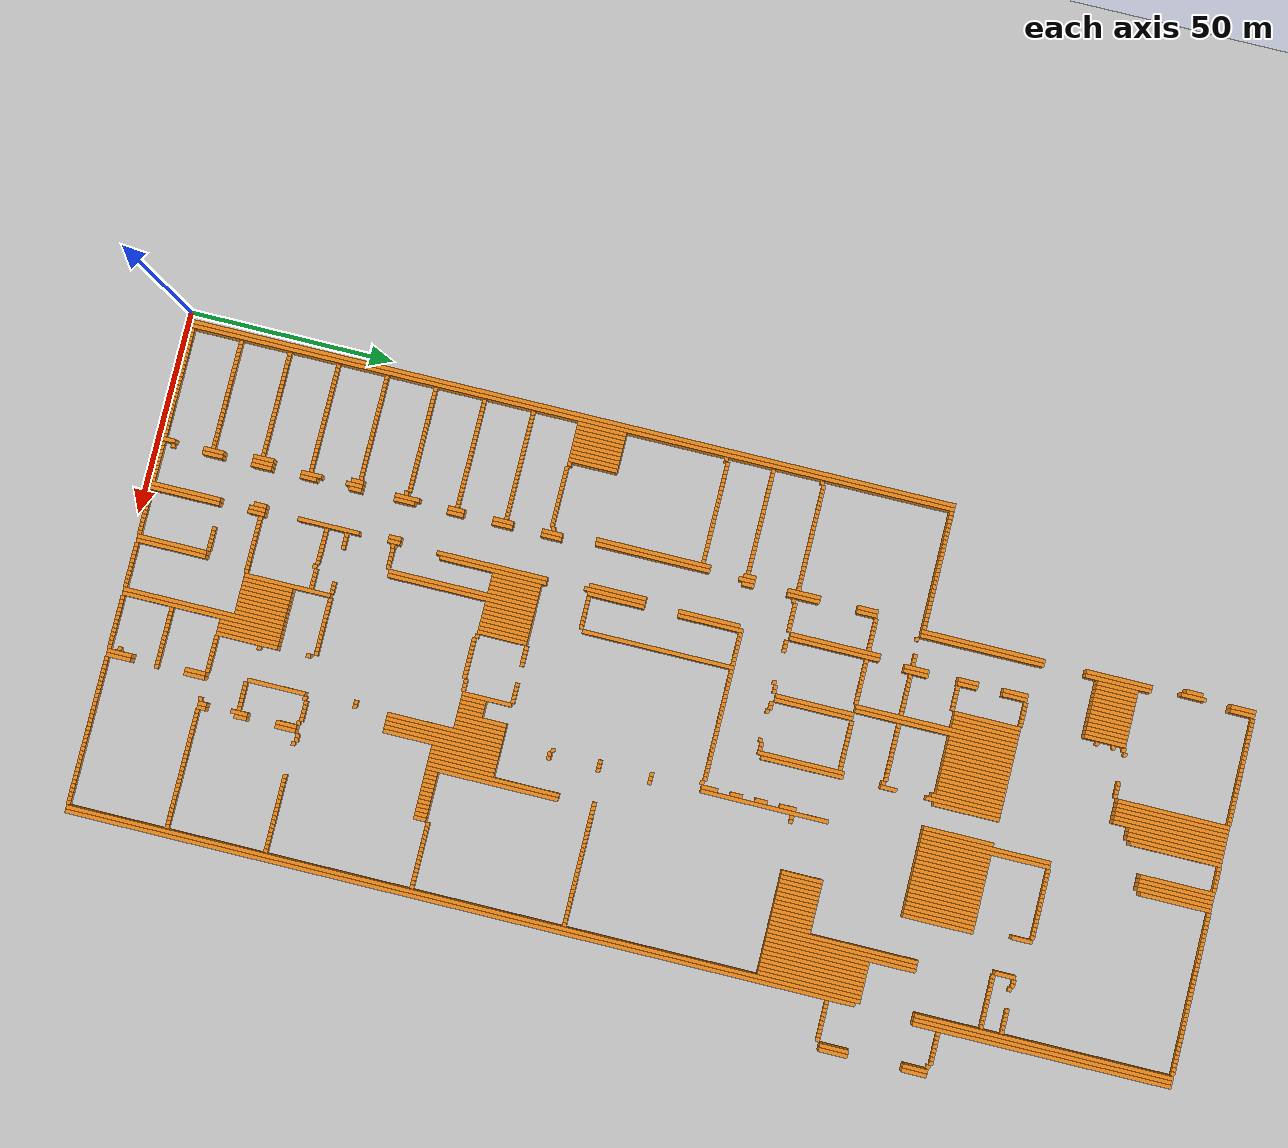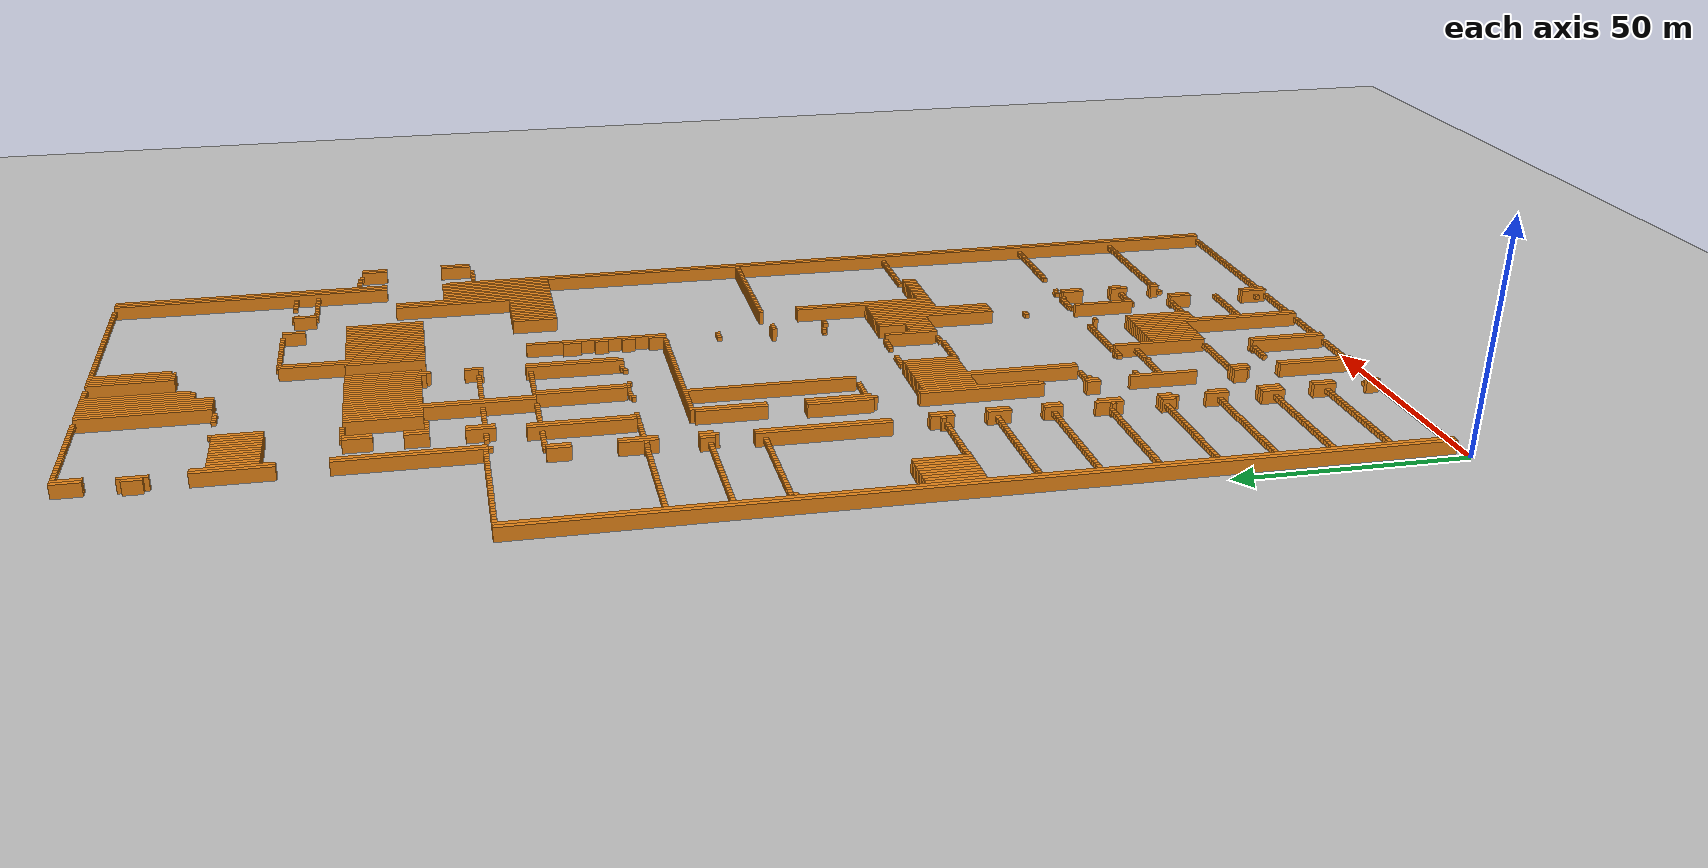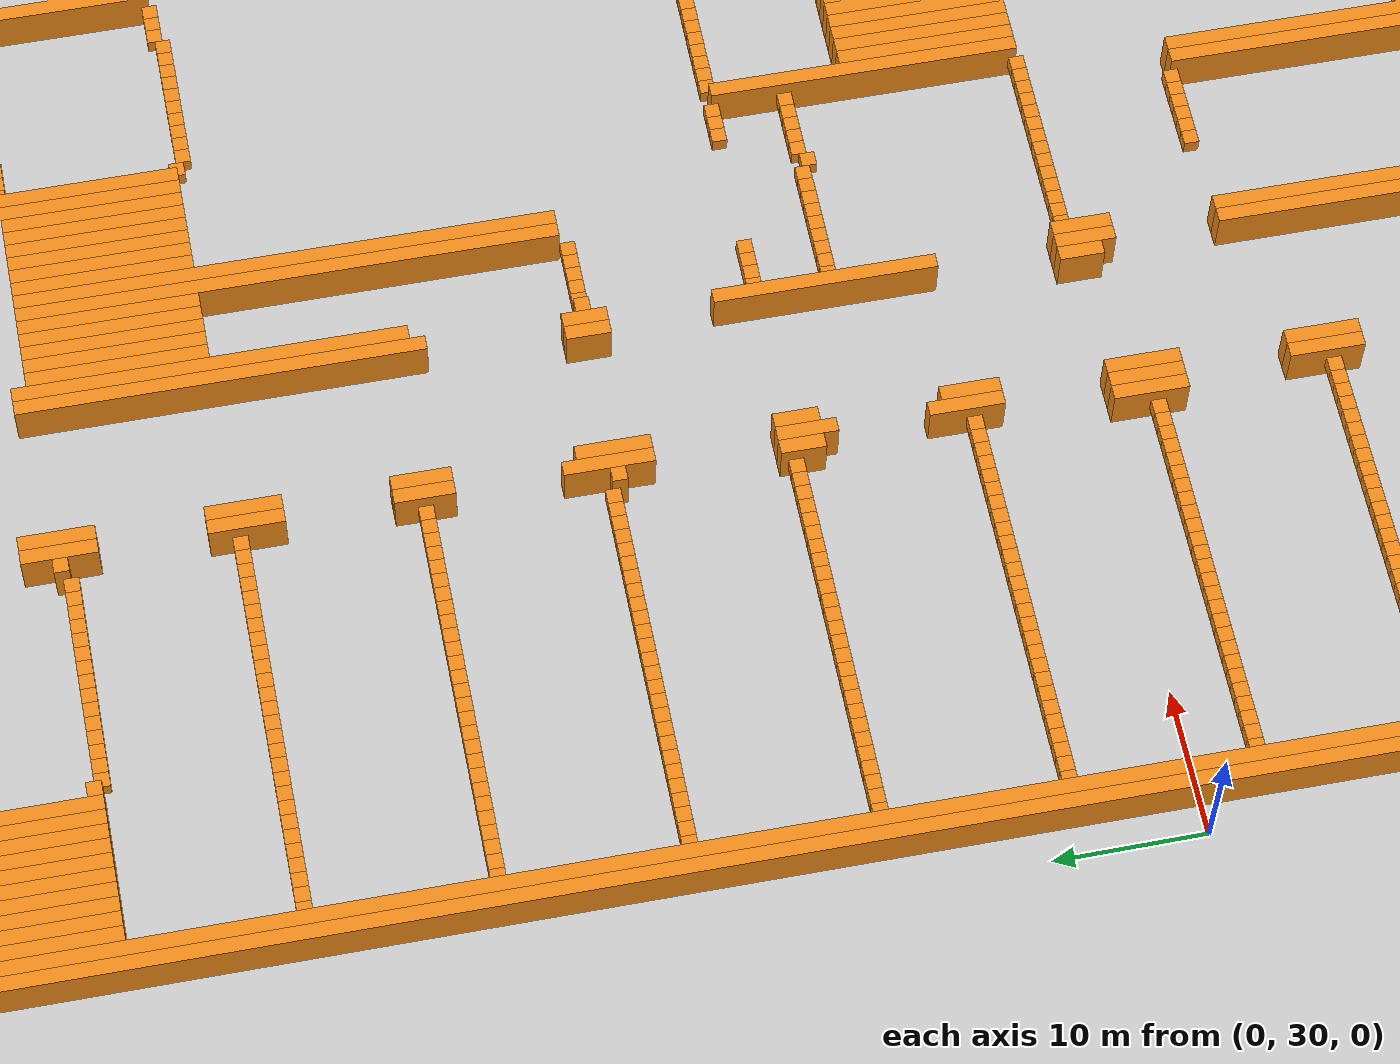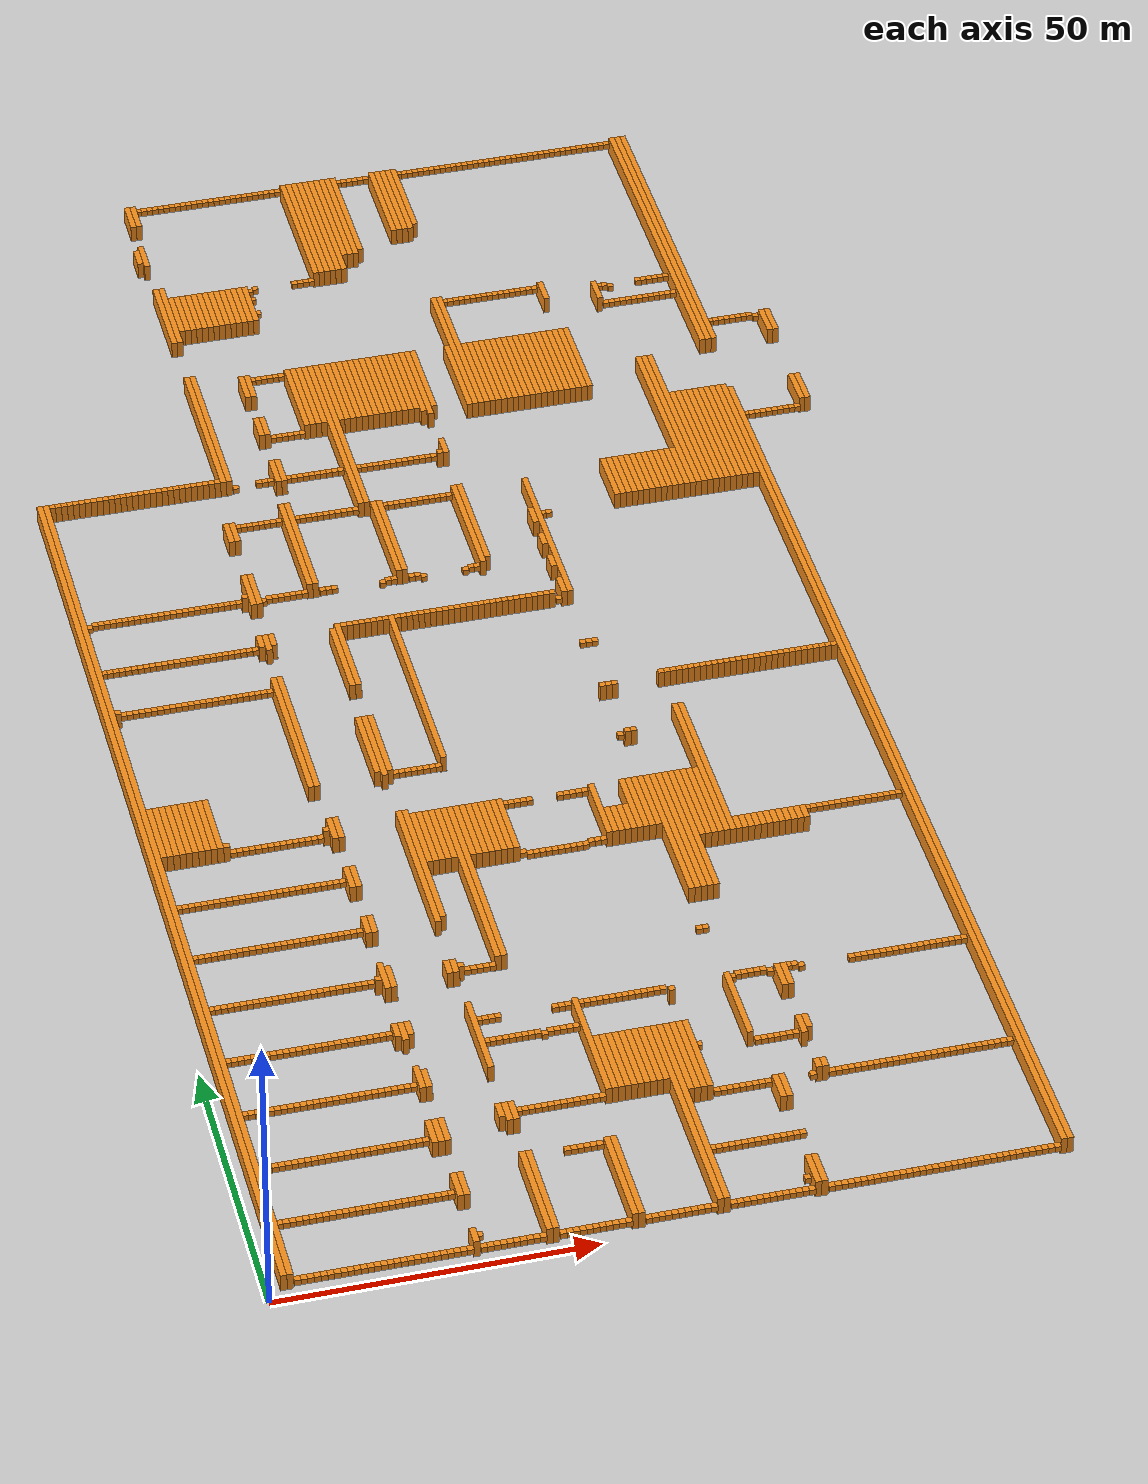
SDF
<sdf version="1.6">
 <world name="default">
  <include><uri>model://ground_plane</uri></include>
  <collision name="collision"><max_contacts>0</max_contacts></collision>
  <light name="sun" type="directional">
   <cast_shadows>0</cast_shadows>
   <pose>0 0 10 0 -0 0</pose>
   <diffuse>0.8 0.8 0.8 1</diffuse>
   <specular>0.2 0.2 0.2 1</specular>
   <attenuation>
    <range>1000</range>
    <constant>0.9</constant>
    <linear>0.01</linear>
    <quadratic>0.001</quadratic>
   </attenuation>
   <direction>-0.5 0.1 -0.9</direction>
  </light>
  <physics name="default_physics" default="0" type="ode"><max_step_size>0.01</max_step_size></physics>
  <gravity>0 0 -9.8</gravity>
  <model name="unit_box_000">
   <pose>2.50    95.50     1.50 0 0 0</pose>
   <static>1</static>
   <link name="link">
    <inertial>
     <mass>5000</mass>
     <inertia><ixx>200</ixx><ixy>0</ixy><ixz>0</ixz><iyy>200</iyy><iyz>0</iyz><izz>200</izz></inertia>
    </inertial>
    <collision name="collision"><geometry><box><size>1 187 3</size></box></geometry></collision>
    <visual name="visual">
     <geometry><box><size>1 187 3</size></box></geometry>
     <material>
      <script><name>Gazebo/Orange</name><uri>file://media/materials/scripts/gazebo.material</uri></script>
     </material>
    </visual>
   </link>
  </model>
  <model name="unit_box_001">
   <pose>3.50    95.50     1.50 0 0 0</pose>
   <static>1</static>
   <link name="link">
    <inertial>
     <mass>5000</mass>
     <inertia><ixx>200</ixx><ixy>0</ixy><ixz>0</ixz><iyy>200</iyy><iyz>0</iyz><izz>200</izz></inertia>
    </inertial>
    <collision name="collision"><geometry><box><size>1 187 3</size></box></geometry></collision>
    <visual name="visual">
     <geometry><box><size>1 187 3</size></box></geometry>
     <material>
      <script><name>Gazebo/Orange</name><uri>file://media/materials/scripts/gazebo.material</uri></script>
     </material>
    </visual>
   </link>
  </model>
  <model name="unit_box_002">
   <pose>4.50     2.00     1.50 0 0 0</pose>
   <static>1</static>
   <link name="link">
    <inertial>
     <mass>5000</mass>
     <inertia><ixx>200</ixx><ixy>0</ixy><ixz>0</ixz><iyy>200</iyy><iyz>0</iyz><izz>200</izz></inertia>
    </inertial>
    <collision name="collision"><geometry><box><size>1 1 1</size></box></geometry></collision>
    <visual name="visual">
     <geometry><box><size>1 1 1</size></box></geometry>
     <material>
      <script><name>Gazebo/Orange</name><uri>file://media/materials/scripts/gazebo.material</uri></script>
     </material>
    </visual>
   </link>
  </model>
  <model name="unit_box_003">
   <pose>4.50    14.00     1.50 0 0 0</pose>
   <static>1</static>
   <link name="link">
    <inertial>
     <mass>5000</mass>
     <inertia><ixx>200</ixx><ixy>0</ixy><ixz>0</ixz><iyy>200</iyy><iyz>0</iyz><izz>200</izz></inertia>
    </inertial>
    <collision name="collision"><geometry><box><size>1 1 1</size></box></geometry></collision>
    <visual name="visual">
     <geometry><box><size>1 1 1</size></box></geometry>
     <material>
      <script><name>Gazebo/Orange</name><uri>file://media/materials/scripts/gazebo.material</uri></script>
     </material>
    </visual>
   </link>
  </model>
  <model name="unit_box_004">
   <pose>4.50    26.00     1.50 0 0 0</pose>
   <static>1</static>
   <link name="link">
    <inertial>
     <mass>5000</mass>
     <inertia><ixx>200</ixx><ixy>0</ixy><ixz>0</ixz><iyy>200</iyy><iyz>0</iyz><izz>200</izz></inertia>
    </inertial>
    <collision name="collision"><geometry><box><size>1 1 1</size></box></geometry></collision>
    <visual name="visual">
     <geometry><box><size>1 1 1</size></box></geometry>
     <material>
      <script><name>Gazebo/Orange</name><uri>file://media/materials/scripts/gazebo.material</uri></script>
     </material>
    </visual>
   </link>
  </model>
  <model name="unit_box_005">
   <pose>4.50    38.00     1.50 0 0 0</pose>
   <static>1</static>
   <link name="link">
    <inertial>
     <mass>5000</mass>
     <inertia><ixx>200</ixx><ixy>0</ixy><ixz>0</ixz><iyy>200</iyy><iyz>0</iyz><izz>200</izz></inertia>
    </inertial>
    <collision name="collision"><geometry><box><size>1 1 1</size></box></geometry></collision>
    <visual name="visual">
     <geometry><box><size>1 1 1</size></box></geometry>
     <material>
      <script><name>Gazebo/Orange</name><uri>file://media/materials/scripts/gazebo.material</uri></script>
     </material>
    </visual>
   </link>
  </model>
  <model name="unit_box_006">
   <pose>4.50    50.00     1.50 0 0 0</pose>
   <static>1</static>
   <link name="link">
    <inertial>
     <mass>5000</mass>
     <inertia><ixx>200</ixx><ixy>0</ixy><ixz>0</ixz><iyy>200</iyy><iyz>0</iyz><izz>200</izz></inertia>
    </inertial>
    <collision name="collision"><geometry><box><size>1 1 1</size></box></geometry></collision>
    <visual name="visual">
     <geometry><box><size>1 1 1</size></box></geometry>
     <material>
      <script><name>Gazebo/Orange</name><uri>file://media/materials/scripts/gazebo.material</uri></script>
     </material>
    </visual>
   </link>
  </model>
  <model name="unit_box_007">
   <pose>4.50    62.00     1.50 0 0 0</pose>
   <static>1</static>
   <link name="link">
    <inertial>
     <mass>5000</mass>
     <inertia><ixx>200</ixx><ixy>0</ixy><ixz>0</ixz><iyy>200</iyy><iyz>0</iyz><izz>200</izz></inertia>
    </inertial>
    <collision name="collision"><geometry><box><size>1 1 1</size></box></geometry></collision>
    <visual name="visual">
     <geometry><box><size>1 1 1</size></box></geometry>
     <material>
      <script><name>Gazebo/Orange</name><uri>file://media/materials/scripts/gazebo.material</uri></script>
     </material>
    </visual>
   </link>
  </model>
  <model name="unit_box_008">
   <pose>4.50    74.00     1.50 0 0 0</pose>
   <static>1</static>
   <link name="link">
    <inertial>
     <mass>5000</mass>
     <inertia><ixx>200</ixx><ixy>0</ixy><ixz>0</ixz><iyy>200</iyy><iyz>0</iyz><izz>200</izz></inertia>
    </inertial>
    <collision name="collision"><geometry><box><size>1 1 1</size></box></geometry></collision>
    <visual name="visual">
     <geometry><box><size>1 1 1</size></box></geometry>
     <material>
      <script><name>Gazebo/Orange</name><uri>file://media/materials/scripts/gazebo.material</uri></script>
     </material>
    </visual>
   </link>
  </model>
  <model name="unit_box_009">
   <pose>4.50    86.00     1.50 0 0 0</pose>
   <static>1</static>
   <link name="link">
    <inertial>
     <mass>5000</mass>
     <inertia><ixx>200</ixx><ixy>0</ixy><ixz>0</ixz><iyy>200</iyy><iyz>0</iyz><izz>200</izz></inertia>
    </inertial>
    <collision name="collision"><geometry><box><size>1 1 1</size></box></geometry></collision>
    <visual name="visual">
     <geometry><box><size>1 1 1</size></box></geometry>
     <material>
      <script><name>Gazebo/Orange</name><uri>file://media/materials/scripts/gazebo.material</uri></script>
     </material>
    </visual>
   </link>
  </model>
  <model name="unit_box_010">
   <pose>4.50   103.00     1.50 0 0 0</pose>
   <static>1</static>
   <link name="link">
    <inertial>
     <mass>5000</mass>
     <inertia><ixx>200</ixx><ixy>0</ixy><ixz>0</ixz><iyy>200</iyy><iyz>0</iyz><izz>200</izz></inertia>
    </inertial>
    <collision name="collision"><geometry><box><size>1 12 3</size></box></geometry></collision>
    <visual name="visual">
     <geometry><box><size>1 12 3</size></box></geometry>
     <material>
      <script><name>Gazebo/Orange</name><uri>file://media/materials/scripts/gazebo.material</uri></script>
     </material>
    </visual>
   </link>
  </model>
  <model name="unit_box_011">
   <pose>4.50   133.50     1.50 0 0 0</pose>
   <static>1</static>
   <link name="link">
    <inertial>
     <mass>5000</mass>
     <inertia><ixx>200</ixx><ixy>0</ixy><ixz>0</ixz><iyy>200</iyy><iyz>0</iyz><izz>200</izz></inertia>
    </inertial>
    <collision name="collision"><geometry><box><size>1 1 3</size></box></geometry></collision>
    <visual name="visual">
     <geometry><box><size>1 1 3</size></box></geometry>
     <material>
      <script><name>Gazebo/Orange</name><uri>file://media/materials/scripts/gazebo.material</uri></script>
     </material>
    </visual>
   </link>
  </model>
  <model name="unit_box_012">
   <pose>4.50   145.00     1.50 0 0 0</pose>
   <static>1</static>
   <link name="link">
    <inertial>
     <mass>5000</mass>
     <inertia><ixx>200</ixx><ixy>0</ixy><ixz>0</ixz><iyy>200</iyy><iyz>0</iyz><izz>200</izz></inertia>
    </inertial>
    <collision name="collision"><geometry><box><size>1 1 1</size></box></geometry></collision>
    <visual name="visual">
     <geometry><box><size>1 1 1</size></box></geometry>
     <material>
      <script><name>Gazebo/Orange</name><uri>file://media/materials/scripts/gazebo.material</uri></script>
     </material>
    </visual>
   </link>
  </model>
  <model name="unit_box_013">
   <pose>4.50   157.00     1.50 0 0 0</pose>
   <static>1</static>
   <link name="link">
    <inertial>
     <mass>5000</mass>
     <inertia><ixx>200</ixx><ixy>0</ixy><ixz>0</ixz><iyy>200</iyy><iyz>0</iyz><izz>200</izz></inertia>
    </inertial>
    <collision name="collision"><geometry><box><size>1 1 1</size></box></geometry></collision>
    <visual name="visual">
     <geometry><box><size>1 1 1</size></box></geometry>
     <material>
      <script><name>Gazebo/Orange</name><uri>file://media/materials/scripts/gazebo.material</uri></script>
     </material>
    </visual>
   </link>
  </model>
  <model name="unit_box_014">
   <pose>4.50   188.50     1.50 0 0 0</pose>
   <static>1</static>
   <link name="link">
    <inertial>
     <mass>5000</mass>
     <inertia><ixx>200</ixx><ixy>0</ixy><ixz>0</ixz><iyy>200</iyy><iyz>0</iyz><izz>200</izz></inertia>
    </inertial>
    <collision name="collision"><geometry><box><size>1 1 3</size></box></geometry></collision>
    <visual name="visual">
     <geometry><box><size>1 1 3</size></box></geometry>
     <material>
      <script><name>Gazebo/Orange</name><uri>file://media/materials/scripts/gazebo.material</uri></script>
     </material>
    </visual>
   </link>
  </model>
  <model name="unit_box_015">
   <pose>5.50     2.00     1.50 0 0 0</pose>
   <static>1</static>
   <link name="link">
    <inertial>
     <mass>5000</mass>
     <inertia><ixx>200</ixx><ixy>0</ixy><ixz>0</ixz><iyy>200</iyy><iyz>0</iyz><izz>200</izz></inertia>
    </inertial>
    <collision name="collision"><geometry><box><size>1 1 1</size></box></geometry></collision>
    <visual name="visual">
     <geometry><box><size>1 1 1</size></box></geometry>
     <material>
      <script><name>Gazebo/Orange</name><uri>file://media/materials/scripts/gazebo.material</uri></script>
     </material>
    </visual>
   </link>
  </model>
  <model name="unit_box_016">
   <pose>5.50    14.00     1.50 0 0 0</pose>
   <static>1</static>
   <link name="link">
    <inertial>
     <mass>5000</mass>
     <inertia><ixx>200</ixx><ixy>0</ixy><ixz>0</ixz><iyy>200</iyy><iyz>0</iyz><izz>200</izz></inertia>
    </inertial>
    <collision name="collision"><geometry><box><size>1 1 1</size></box></geometry></collision>
    <visual name="visual">
     <geometry><box><size>1 1 1</size></box></geometry>
     <material>
      <script><name>Gazebo/Orange</name><uri>file://media/materials/scripts/gazebo.material</uri></script>
     </material>
    </visual>
   </link>
  </model>
  <model name="unit_box_017">
   <pose>5.50    26.00     1.50 0 0 0</pose>
   <static>1</static>
   <link name="link">
    <inertial>
     <mass>5000</mass>
     <inertia><ixx>200</ixx><ixy>0</ixy><ixz>0</ixz><iyy>200</iyy><iyz>0</iyz><izz>200</izz></inertia>
    </inertial>
    <collision name="collision"><geometry><box><size>1 1 1</size></box></geometry></collision>
    <visual name="visual">
     <geometry><box><size>1 1 1</size></box></geometry>
     <material>
      <script><name>Gazebo/Orange</name><uri>file://media/materials/scripts/gazebo.material</uri></script>
     </material>
    </visual>
   </link>
  </model>
  <model name="unit_box_018">
   <pose>5.50    38.00     1.50 0 0 0</pose>
   <static>1</static>
   <link name="link">
    <inertial>
     <mass>5000</mass>
     <inertia><ixx>200</ixx><ixy>0</ixy><ixz>0</ixz><iyy>200</iyy><iyz>0</iyz><izz>200</izz></inertia>
    </inertial>
    <collision name="collision"><geometry><box><size>1 1 1</size></box></geometry></collision>
    <visual name="visual">
     <geometry><box><size>1 1 1</size></box></geometry>
     <material>
      <script><name>Gazebo/Orange</name><uri>file://media/materials/scripts/gazebo.material</uri></script>
     </material>
    </visual>
   </link>
  </model>
  <model name="unit_box_019">
   <pose>5.50    50.00     1.50 0 0 0</pose>
   <static>1</static>
   <link name="link">
    <inertial>
     <mass>5000</mass>
     <inertia><ixx>200</ixx><ixy>0</ixy><ixz>0</ixz><iyy>200</iyy><iyz>0</iyz><izz>200</izz></inertia>
    </inertial>
    <collision name="collision"><geometry><box><size>1 1 1</size></box></geometry></collision>
    <visual name="visual">
     <geometry><box><size>1 1 1</size></box></geometry>
     <material>
      <script><name>Gazebo/Orange</name><uri>file://media/materials/scripts/gazebo.material</uri></script>
     </material>
    </visual>
   </link>
  </model>
  <model name="unit_box_020">
   <pose>5.50    62.00     1.50 0 0 0</pose>
   <static>1</static>
   <link name="link">
    <inertial>
     <mass>5000</mass>
     <inertia><ixx>200</ixx><ixy>0</ixy><ixz>0</ixz><iyy>200</iyy><iyz>0</iyz><izz>200</izz></inertia>
    </inertial>
    <collision name="collision"><geometry><box><size>1 1 1</size></box></geometry></collision>
    <visual name="visual">
     <geometry><box><size>1 1 1</size></box></geometry>
     <material>
      <script><name>Gazebo/Orange</name><uri>file://media/materials/scripts/gazebo.material</uri></script>
     </material>
    </visual>
   </link>
  </model>
  <model name="unit_box_021">
   <pose>5.50    74.00     1.50 0 0 0</pose>
   <static>1</static>
   <link name="link">
    <inertial>
     <mass>5000</mass>
     <inertia><ixx>200</ixx><ixy>0</ixy><ixz>0</ixz><iyy>200</iyy><iyz>0</iyz><izz>200</izz></inertia>
    </inertial>
    <collision name="collision"><geometry><box><size>1 1 1</size></box></geometry></collision>
    <visual name="visual">
     <geometry><box><size>1 1 1</size></box></geometry>
     <material>
      <script><name>Gazebo/Orange</name><uri>file://media/materials/scripts/gazebo.material</uri></script>
     </material>
    </visual>
   </link>
  </model>
  <model name="unit_box_022">
   <pose>5.50    86.00     1.50 0 0 0</pose>
   <static>1</static>
   <link name="link">
    <inertial>
     <mass>5000</mass>
     <inertia><ixx>200</ixx><ixy>0</ixy><ixz>0</ixz><iyy>200</iyy><iyz>0</iyz><izz>200</izz></inertia>
    </inertial>
    <collision name="collision"><geometry><box><size>1 1 1</size></box></geometry></collision>
    <visual name="visual">
     <geometry><box><size>1 1 1</size></box></geometry>
     <material>
      <script><name>Gazebo/Orange</name><uri>file://media/materials/scripts/gazebo.material</uri></script>
     </material>
    </visual>
   </link>
  </model>
  <model name="unit_box_023">
   <pose>5.50   103.00     1.50 0 0 0</pose>
   <static>1</static>
   <link name="link">
    <inertial>
     <mass>5000</mass>
     <inertia><ixx>200</ixx><ixy>0</ixy><ixz>0</ixz><iyy>200</iyy><iyz>0</iyz><izz>200</izz></inertia>
    </inertial>
    <collision name="collision"><geometry><box><size>1 12 3</size></box></geometry></collision>
    <visual name="visual">
     <geometry><box><size>1 12 3</size></box></geometry>
     <material>
      <script><name>Gazebo/Orange</name><uri>file://media/materials/scripts/gazebo.material</uri></script>
     </material>
    </visual>
   </link>
  </model>
  <model name="unit_box_024">
   <pose>5.50   134.00     1.50 0 0 0</pose>
   <static>1</static>
   <link name="link">
    <inertial>
     <mass>5000</mass>
     <inertia><ixx>200</ixx><ixy>0</ixy><ixz>0</ixz><iyy>200</iyy><iyz>0</iyz><izz>200</izz></inertia>
    </inertial>
    <collision name="collision"><geometry><box><size>1 1 1</size></box></geometry></collision>
    <visual name="visual">
     <geometry><box><size>1 1 1</size></box></geometry>
     <material>
      <script><name>Gazebo/Orange</name><uri>file://media/materials/scripts/gazebo.material</uri></script>
     </material>
    </visual>
   </link>
  </model>
  <model name="unit_box_025">
   <pose>5.50   145.00     1.50 0 0 0</pose>
   <static>1</static>
   <link name="link">
    <inertial>
     <mass>5000</mass>
     <inertia><ixx>200</ixx><ixy>0</ixy><ixz>0</ixz><iyy>200</iyy><iyz>0</iyz><izz>200</izz></inertia>
    </inertial>
    <collision name="collision"><geometry><box><size>1 1 1</size></box></geometry></collision>
    <visual name="visual">
     <geometry><box><size>1 1 1</size></box></geometry>
     <material>
      <script><name>Gazebo/Orange</name><uri>file://media/materials/scripts/gazebo.material</uri></script>
     </material>
    </visual>
   </link>
  </model>
  <model name="unit_box_026">
   <pose>5.50   157.50     1.50 0 0 0</pose>
   <static>1</static>
   <link name="link">
    <inertial>
     <mass>5000</mass>
     <inertia><ixx>200</ixx><ixy>0</ixy><ixz>0</ixz><iyy>200</iyy><iyz>0</iyz><izz>200</izz></inertia>
    </inertial>
    <collision name="collision"><geometry><box><size>1 1 1</size></box></geometry></collision>
    <visual name="visual">
     <geometry><box><size>1 1 1</size></box></geometry>
     <material>
      <script><name>Gazebo/Orange</name><uri>file://media/materials/scripts/gazebo.material</uri></script>
     </material>
    </visual>
   </link>
  </model>
  <model name="unit_box_027">
   <pose>5.50   188.50     1.50 0 0 0</pose>
   <static>1</static>
   <link name="link">
    <inertial>
     <mass>5000</mass>
     <inertia><ixx>200</ixx><ixy>0</ixy><ixz>0</ixz><iyy>200</iyy><iyz>0</iyz><izz>200</izz></inertia>
    </inertial>
    <collision name="collision"><geometry><box><size>1 1 3</size></box></geometry></collision>
    <visual name="visual">
     <geometry><box><size>1 1 3</size></box></geometry>
     <material>
      <script><name>Gazebo/Orange</name><uri>file://media/materials/scripts/gazebo.material</uri></script>
     </material>
    </visual>
   </link>
  </model>
  <model name="unit_box_028">
   <pose>6.50     2.00     1.50 0 0 0</pose>
   <static>1</static>
   <link name="link">
    <inertial>
     <mass>5000</mass>
     <inertia><ixx>200</ixx><ixy>0</ixy><ixz>0</ixz><iyy>200</iyy><iyz>0</iyz><izz>200</izz></inertia>
    </inertial>
    <collision name="collision"><geometry><box><size>1 1 1</size></box></geometry></collision>
    <visual name="visual">
     <geometry><box><size>1 1 1</size></box></geometry>
     <material>
      <script><name>Gazebo/Orange</name><uri>file://media/materials/scripts/gazebo.material</uri></script>
     </material>
    </visual>
   </link>
  </model>
  <model name="unit_box_029">
   <pose>6.50    14.00     1.50 0 0 0</pose>
   <static>1</static>
   <link name="link">
    <inertial>
     <mass>5000</mass>
     <inertia><ixx>200</ixx><ixy>0</ixy><ixz>0</ixz><iyy>200</iyy><iyz>0</iyz><izz>200</izz></inertia>
    </inertial>
    <collision name="collision"><geometry><box><size>1 1 1</size></box></geometry></collision>
    <visual name="visual">
     <geometry><box><size>1 1 1</size></box></geometry>
     <material>
      <script><name>Gazebo/Orange</name><uri>file://media/materials/scripts/gazebo.material</uri></script>
     </material>
    </visual>
   </link>
  </model>
  <model name="unit_box_030">
   <pose>6.50    26.00     1.50 0 0 0</pose>
   <static>1</static>
   <link name="link">
    <inertial>
     <mass>5000</mass>
     <inertia><ixx>200</ixx><ixy>0</ixy><ixz>0</ixz><iyy>200</iyy><iyz>0</iyz><izz>200</izz></inertia>
    </inertial>
    <collision name="collision"><geometry><box><size>1 1 1</size></box></geometry></collision>
    <visual name="visual">
     <geometry><box><size>1 1 1</size></box></geometry>
     <material>
      <script><name>Gazebo/Orange</name><uri>file://media/materials/scripts/gazebo.material</uri></script>
     </material>
    </visual>
   </link>
  </model>
  <model name="unit_box_031">
   <pose>6.50    38.00     1.50 0 0 0</pose>
   <static>1</static>
   <link name="link">
    <inertial>
     <mass>5000</mass>
     <inertia><ixx>200</ixx><ixy>0</ixy><ixz>0</ixz><iyy>200</iyy><iyz>0</iyz><izz>200</izz></inertia>
    </inertial>
    <collision name="collision"><geometry><box><size>1 1 1</size></box></geometry></collision>
    <visual name="visual">
     <geometry><box><size>1 1 1</size></box></geometry>
     <material>
      <script><name>Gazebo/Orange</name><uri>file://media/materials/scripts/gazebo.material</uri></script>
     </material>
    </visual>
   </link>
  </model>
  <model name="unit_box_032">
   <pose>6.50    50.00     1.50 0 0 0</pose>
   <static>1</static>
   <link name="link">
    <inertial>
     <mass>5000</mass>
     <inertia><ixx>200</ixx><ixy>0</ixy><ixz>0</ixz><iyy>200</iyy><iyz>0</iyz><izz>200</izz></inertia>
    </inertial>
    <collision name="collision"><geometry><box><size>1 1 1</size></box></geometry></collision>
    <visual name="visual">
     <geometry><box><size>1 1 1</size></box></geometry>
     <material>
      <script><name>Gazebo/Orange</name><uri>file://media/materials/scripts/gazebo.material</uri></script>
     </material>
    </visual>
   </link>
  </model>
  <model name="unit_box_033">
   <pose>6.50    62.00     1.50 0 0 0</pose>
   <static>1</static>
   <link name="link">
    <inertial>
     <mass>5000</mass>
     <inertia><ixx>200</ixx><ixy>0</ixy><ixz>0</ixz><iyy>200</iyy><iyz>0</iyz><izz>200</izz></inertia>
    </inertial>
    <collision name="collision"><geometry><box><size>1 1 1</size></box></geometry></collision>
    <visual name="visual">
     <geometry><box><size>1 1 1</size></box></geometry>
     <material>
      <script><name>Gazebo/Orange</name><uri>file://media/materials/scripts/gazebo.material</uri></script>
     </material>
    </visual>
   </link>
  </model>
  <model name="unit_box_034">
   <pose>6.50    74.00     1.50 0 0 0</pose>
   <static>1</static>
   <link name="link">
    <inertial>
     <mass>5000</mass>
     <inertia><ixx>200</ixx><ixy>0</ixy><ixz>0</ixz><iyy>200</iyy><iyz>0</iyz><izz>200</izz></inertia>
    </inertial>
    <collision name="collision"><geometry><box><size>1 1 1</size></box></geometry></collision>
    <visual name="visual">
     <geometry><box><size>1 1 1</size></box></geometry>
     <material>
      <script><name>Gazebo/Orange</name><uri>file://media/materials/scripts/gazebo.material</uri></script>
     </material>
    </visual>
   </link>
  </model>
  <model name="unit_box_035">
   <pose>6.50    86.00     1.50 0 0 0</pose>
   <static>1</static>
   <link name="link">
    <inertial>
     <mass>5000</mass>
     <inertia><ixx>200</ixx><ixy>0</ixy><ixz>0</ixz><iyy>200</iyy><iyz>0</iyz><izz>200</izz></inertia>
    </inertial>
    <collision name="collision"><geometry><box><size>1 1 1</size></box></geometry></collision>
    <visual name="visual">
     <geometry><box><size>1 1 1</size></box></geometry>
     <material>
      <script><name>Gazebo/Orange</name><uri>file://media/materials/scripts/gazebo.material</uri></script>
     </material>
    </visual>
   </link>
  </model>
  <model name="unit_box_036">
   <pose>6.50   103.00     1.50 0 0 0</pose>
   <static>1</static>
   <link name="link">
    <inertial>
     <mass>5000</mass>
     <inertia><ixx>200</ixx><ixy>0</ixy><ixz>0</ixz><iyy>200</iyy><iyz>0</iyz><izz>200</izz></inertia>
    </inertial>
    <collision name="collision"><geometry><box><size>1 12 3</size></box></geometry></collision>
    <visual name="visual">
     <geometry><box><size>1 12 3</size></box></geometry>
     <material>
      <script><name>Gazebo/Orange</name><uri>file://media/materials/scripts/gazebo.material</uri></script>
     </material>
    </visual>
   </link>
  </model>
  <model name="unit_box_037">
   <pose>6.50   134.00     1.50 0 0 0</pose>
   <static>1</static>
   <link name="link">
    <inertial>
     <mass>5000</mass>
     <inertia><ixx>200</ixx><ixy>0</ixy><ixz>0</ixz><iyy>200</iyy><iyz>0</iyz><izz>200</izz></inertia>
    </inertial>
    <collision name="collision"><geometry><box><size>1 1 1</size></box></geometry></collision>
    <visual name="visual">
     <geometry><box><size>1 1 1</size></box></geometry>
     <material>
      <script><name>Gazebo/Orange</name><uri>file://media/materials/scripts/gazebo.material</uri></script>
     </material>
    </visual>
   </link>
  </model>
  <model name="unit_box_038">
   <pose>6.50   145.00     1.50 0 0 0</pose>
   <static>1</static>
   <link name="link">
    <inertial>
     <mass>5000</mass>
     <inertia><ixx>200</ixx><ixy>0</ixy><ixz>0</ixz><iyy>200</iyy><iyz>0</iyz><izz>200</izz></inertia>
    </inertial>
    <collision name="collision"><geometry><box><size>1 1 1</size></box></geometry></collision>
    <visual name="visual">
     <geometry><box><size>1 1 1</size></box></geometry>
     <material>
      <script><name>Gazebo/Orange</name><uri>file://media/materials/scripts/gazebo.material</uri></script>
     </material>
    </visual>
   </link>
  </model>
  <model name="unit_box_039">
   <pose>6.50   157.50     1.50 0 0 0</pose>
   <static>1</static>
   <link name="link">
    <inertial>
     <mass>5000</mass>
     <inertia><ixx>200</ixx><ixy>0</ixy><ixz>0</ixz><iyy>200</iyy><iyz>0</iyz><izz>200</izz></inertia>
    </inertial>
    <collision name="collision"><geometry><box><size>1 1 1</size></box></geometry></collision>
    <visual name="visual">
     <geometry><box><size>1 1 1</size></box></geometry>
     <material>
      <script><name>Gazebo/Orange</name><uri>file://media/materials/scripts/gazebo.material</uri></script>
     </material>
    </visual>
   </link>
  </model>
  <model name="unit_box_040">
   <pose>6.50   188.50     1.50 0 0 0</pose>
   <static>1</static>
   <link name="link">
    <inertial>
     <mass>5000</mass>
     <inertia><ixx>200</ixx><ixy>0</ixy><ixz>0</ixz><iyy>200</iyy><iyz>0</iyz><izz>200</izz></inertia>
    </inertial>
    <collision name="collision"><geometry><box><size>1 1 3</size></box></geometry></collision>
    <visual name="visual">
     <geometry><box><size>1 1 3</size></box></geometry>
     <material>
      <script><name>Gazebo/Orange</name><uri>file://media/materials/scripts/gazebo.material</uri></script>
     </material>
    </visual>
   </link>
  </model>
  <model name="unit_box_041">
   <pose>7.50     2.00     1.50 0 0 0</pose>
   <static>1</static>
   <link name="link">
    <inertial>
     <mass>5000</mass>
     <inertia><ixx>200</ixx><ixy>0</ixy><ixz>0</ixz><iyy>200</iyy><iyz>0</iyz><izz>200</izz></inertia>
    </inertial>
    <collision name="collision"><geometry><box><size>1 1 1</size></box></geometry></collision>
    <visual name="visual">
     <geometry><box><size>1 1 1</size></box></geometry>
     <material>
      <script><name>Gazebo/Orange</name><uri>file://media/materials/scripts/gazebo.material</uri></script>
     </material>
    </visual>
   </link>
  </model>
  <model name="unit_box_042">
   <pose>7.50    14.00     1.50 0 0 0</pose>
   <static>1</static>
   <link name="link">
    <inertial>
     <mass>5000</mass>
     <inertia><ixx>200</ixx><ixy>0</ixy><ixz>0</ixz><iyy>200</iyy><iyz>0</iyz><izz>200</izz></inertia>
    </inertial>
    <collision name="collision"><geometry><box><size>1 1 1</size></box></geometry></collision>
    <visual name="visual">
     <geometry><box><size>1 1 1</size></box></geometry>
     <material>
      <script><name>Gazebo/Orange</name><uri>file://media/materials/scripts/gazebo.material</uri></script>
     </material>
    </visual>
   </link>
  </model>
  <model name="unit_box_043">
   <pose>7.50    26.00     1.50 0 0 0</pose>
   <static>1</static>
   <link name="link">
    <inertial>
     <mass>5000</mass>
     <inertia><ixx>200</ixx><ixy>0</ixy><ixz>0</ixz><iyy>200</iyy><iyz>0</iyz><izz>200</izz></inertia>
    </inertial>
    <collision name="collision"><geometry><box><size>1 1 1</size></box></geometry></collision>
    <visual name="visual">
     <geometry><box><size>1 1 1</size></box></geometry>
     <material>
      <script><name>Gazebo/Orange</name><uri>file://media/materials/scripts/gazebo.material</uri></script>
     </material>
    </visual>
   </link>
  </model>
  <model name="unit_box_044">
   <pose>7.50    38.00     1.50 0 0 0</pose>
   <static>1</static>
   <link name="link">
    <inertial>
     <mass>5000</mass>
     <inertia><ixx>200</ixx><ixy>0</ixy><ixz>0</ixz><iyy>200</iyy><iyz>0</iyz><izz>200</izz></inertia>
    </inertial>
    <collision name="collision"><geometry><box><size>1 1 1</size></box></geometry></collision>
    <visual name="visual">
     <geometry><box><size>1 1 1</size></box></geometry>
     <material>
      <script><name>Gazebo/Orange</name><uri>file://media/materials/scripts/gazebo.material</uri></script>
     </material>
    </visual>
   </link>
  </model>
  <model name="unit_box_045">
   <pose>7.50    50.00     1.50 0 0 0</pose>
   <static>1</static>
   <link name="link">
    <inertial>
     <mass>5000</mass>
     <inertia><ixx>200</ixx><ixy>0</ixy><ixz>0</ixz><iyy>200</iyy><iyz>0</iyz><izz>200</izz></inertia>
    </inertial>
    <collision name="collision"><geometry><box><size>1 1 1</size></box></geometry></collision>
    <visual name="visual">
     <geometry><box><size>1 1 1</size></box></geometry>
     <material>
      <script><name>Gazebo/Orange</name><uri>file://media/materials/scripts/gazebo.material</uri></script>
     </material>
    </visual>
   </link>
  </model>
  <model name="unit_box_046">
   <pose>7.50    62.00     1.50 0 0 0</pose>
   <static>1</static>
   <link name="link">
    <inertial>
     <mass>5000</mass>
     <inertia><ixx>200</ixx><ixy>0</ixy><ixz>0</ixz><iyy>200</iyy><iyz>0</iyz><izz>200</izz></inertia>
    </inertial>
    <collision name="collision"><geometry><box><size>1 1 1</size></box></geometry></collision>
    <visual name="visual">
     <geometry><box><size>1 1 1</size></box></geometry>
     <material>
      <script><name>Gazebo/Orange</name><uri>file://media/materials/scripts/gazebo.material</uri></script>
     </material>
    </visual>
   </link>
  </model>
  <model name="unit_box_047">
   <pose>7.50    74.00     1.50 0 0 0</pose>
   <static>1</static>
   <link name="link">
    <inertial>
     <mass>5000</mass>
     <inertia><ixx>200</ixx><ixy>0</ixy><ixz>0</ixz><iyy>200</iyy><iyz>0</iyz><izz>200</izz></inertia>
    </inertial>
    <collision name="collision"><geometry><box><size>1 1 1</size></box></geometry></collision>
    <visual name="visual">
     <geometry><box><size>1 1 1</size></box></geometry>
     <material>
      <script><name>Gazebo/Orange</name><uri>file://media/materials/scripts/gazebo.material</uri></script>
     </material>
    </visual>
   </link>
  </model>
  <model name="unit_box_048">
   <pose>7.50    86.00     1.50 0 0 0</pose>
   <static>1</static>
   <link name="link">
    <inertial>
     <mass>5000</mass>
     <inertia><ixx>200</ixx><ixy>0</ixy><ixz>0</ixz><iyy>200</iyy><iyz>0</iyz><izz>200</izz></inertia>
    </inertial>
    <collision name="collision"><geometry><box><size>1 1 1</size></box></geometry></collision>
    <visual name="visual">
     <geometry><box><size>1 1 1</size></box></geometry>
     <material>
      <script><name>Gazebo/Orange</name><uri>file://media/materials/scripts/gazebo.material</uri></script>
     </material>
    </visual>
   </link>
  </model>
  <model name="unit_box_049">
   <pose>7.50   103.00     1.50 0 0 0</pose>
   <static>1</static>
   <link name="link">
    <inertial>
     <mass>5000</mass>
     <inertia><ixx>200</ixx><ixy>0</ixy><ixz>0</ixz><iyy>200</iyy><iyz>0</iyz><izz>200</izz></inertia>
    </inertial>
    <collision name="collision"><geometry><box><size>1 12 3</size></box></geometry></collision>
    <visual name="visual">
     <geometry><box><size>1 12 3</size></box></geometry>
     <material>
      <script><name>Gazebo/Orange</name><uri>file://media/materials/scripts/gazebo.material</uri></script>
     </material>
    </visual>
   </link>
  </model>
  <model name="unit_box_050">
   <pose>7.50   134.00     1.50 0 0 0</pose>
   <static>1</static>
   <link name="link">
    <inertial>
     <mass>5000</mass>
     <inertia><ixx>200</ixx><ixy>0</ixy><ixz>0</ixz><iyy>200</iyy><iyz>0</iyz><izz>200</izz></inertia>
    </inertial>
    <collision name="collision"><geometry><box><size>1 1 1</size></box></geometry></collision>
    <visual name="visual">
     <geometry><box><size>1 1 1</size></box></geometry>
     <material>
      <script><name>Gazebo/Orange</name><uri>file://media/materials/scripts/gazebo.material</uri></script>
     </material>
    </visual>
   </link>
  </model>
  <model name="unit_box_051">
   <pose>7.50   145.00     1.50 0 0 0</pose>
   <static>1</static>
   <link name="link">
    <inertial>
     <mass>5000</mass>
     <inertia><ixx>200</ixx><ixy>0</ixy><ixz>0</ixz><iyy>200</iyy><iyz>0</iyz><izz>200</izz></inertia>
    </inertial>
    <collision name="collision"><geometry><box><size>1 1 1</size></box></geometry></collision>
    <visual name="visual">
     <geometry><box><size>1 1 1</size></box></geometry>
     <material>
      <script><name>Gazebo/Orange</name><uri>file://media/materials/scripts/gazebo.material</uri></script>
     </material>
    </visual>
   </link>
  </model>
  <model name="unit_box_052">
   <pose>7.50   157.50     1.50 0 0 0</pose>
   <static>1</static>
   <link name="link">
    <inertial>
     <mass>5000</mass>
     <inertia><ixx>200</ixx><ixy>0</ixy><ixz>0</ixz><iyy>200</iyy><iyz>0</iyz><izz>200</izz></inertia>
    </inertial>
    <collision name="collision"><geometry><box><size>1 1 1</size></box></geometry></collision>
    <visual name="visual">
     <geometry><box><size>1 1 1</size></box></geometry>
     <material>
      <script><name>Gazebo/Orange</name><uri>file://media/materials/scripts/gazebo.material</uri></script>
     </material>
    </visual>
   </link>
  </model>
  <model name="unit_box_053">
   <pose>7.50   188.50     1.50 0 0 0</pose>
   <static>1</static>
   <link name="link">
    <inertial>
     <mass>5000</mass>
     <inertia><ixx>200</ixx><ixy>0</ixy><ixz>0</ixz><iyy>200</iyy><iyz>0</iyz><izz>200</izz></inertia>
    </inertial>
    <collision name="collision"><geometry><box><size>1 1 3</size></box></geometry></collision>
    <visual name="visual">
     <geometry><box><size>1 1 3</size></box></geometry>
     <material>
      <script><name>Gazebo/Orange</name><uri>file://media/materials/scripts/gazebo.material</uri></script>
     </material>
    </visual>
   </link>
  </model>
  <model name="unit_box_054">
   <pose>8.50     2.00     1.50 0 0 0</pose>
   <static>1</static>
   <link name="link">
    <inertial>
     <mass>5000</mass>
     <inertia><ixx>200</ixx><ixy>0</ixy><ixz>0</ixz><iyy>200</iyy><iyz>0</iyz><izz>200</izz></inertia>
    </inertial>
    <collision name="collision"><geometry><box><size>1 1 1</size></box></geometry></collision>
    <visual name="visual">
     <geometry><box><size>1 1 1</size></box></geometry>
     <material>
      <script><name>Gazebo/Orange</name><uri>file://media/materials/scripts/gazebo.material</uri></script>
     </material>
    </visual>
   </link>
  </model>
  <model name="unit_box_055">
   <pose>8.50    14.00     1.50 0 0 0</pose>
   <static>1</static>
   <link name="link">
    <inertial>
     <mass>5000</mass>
     <inertia><ixx>200</ixx><ixy>0</ixy><ixz>0</ixz><iyy>200</iyy><iyz>0</iyz><izz>200</izz></inertia>
    </inertial>
    <collision name="collision"><geometry><box><size>1 1 1</size></box></geometry></collision>
    <visual name="visual">
     <geometry><box><size>1 1 1</size></box></geometry>
     <material>
      <script><name>Gazebo/Orange</name><uri>file://media/materials/scripts/gazebo.material</uri></script>
     </material>
    </visual>
   </link>
  </model>
  <model name="unit_box_056">
   <pose>8.50    26.00     1.50 0 0 0</pose>
   <static>1</static>
   <link name="link">
    <inertial>
     <mass>5000</mass>
     <inertia><ixx>200</ixx><ixy>0</ixy><ixz>0</ixz><iyy>200</iyy><iyz>0</iyz><izz>200</izz></inertia>
    </inertial>
    <collision name="collision"><geometry><box><size>1 1 1</size></box></geometry></collision>
    <visual name="visual">
     <geometry><box><size>1 1 1</size></box></geometry>
     <material>
      <script><name>Gazebo/Orange</name><uri>file://media/materials/scripts/gazebo.material</uri></script>
     </material>
    </visual>
   </link>
  </model>
  <model name="unit_box_057">
   <pose>8.50    38.00     1.50 0 0 0</pose>
   <static>1</static>
   <link name="link">
    <inertial>
     <mass>5000</mass>
     <inertia><ixx>200</ixx><ixy>0</ixy><ixz>0</ixz><iyy>200</iyy><iyz>0</iyz><izz>200</izz></inertia>
    </inertial>
    <collision name="collision"><geometry><box><size>1 1 1</size></box></geometry></collision>
    <visual name="visual">
     <geometry><box><size>1 1 1</size></box></geometry>
     <material>
      <script><name>Gazebo/Orange</name><uri>file://media/materials/scripts/gazebo.material</uri></script>
     </material>
    </visual>
   </link>
  </model>
  <model name="unit_box_058">
   <pose>8.50    50.00     1.50 0 0 0</pose>
   <static>1</static>
   <link name="link">
    <inertial>
     <mass>5000</mass>
     <inertia><ixx>200</ixx><ixy>0</ixy><ixz>0</ixz><iyy>200</iyy><iyz>0</iyz><izz>200</izz></inertia>
    </inertial>
    <collision name="collision"><geometry><box><size>1 1 1</size></box></geometry></collision>
    <visual name="visual">
     <geometry><box><size>1 1 1</size></box></geometry>
     <material>
      <script><name>Gazebo/Orange</name><uri>file://media/materials/scripts/gazebo.material</uri></script>
     </material>
    </visual>
   </link>
  </model>
  <model name="unit_box_059">
   <pose>8.50    62.00     1.50 0 0 0</pose>
   <static>1</static>
   <link name="link">
    <inertial>
     <mass>5000</mass>
     <inertia><ixx>200</ixx><ixy>0</ixy><ixz>0</ixz><iyy>200</iyy><iyz>0</iyz><izz>200</izz></inertia>
    </inertial>
    <collision name="collision"><geometry><box><size>1 1 1</size></box></geometry></collision>
    <visual name="visual">
     <geometry><box><size>1 1 1</size></box></geometry>
     <material>
      <script><name>Gazebo/Orange</name><uri>file://media/materials/scripts/gazebo.material</uri></script>
     </material>
    </visual>
   </link>
  </model>
  <model name="unit_box_060">
   <pose>8.50    74.00     1.50 0 0 0</pose>
   <static>1</static>
   <link name="link">
    <inertial>
     <mass>5000</mass>
     <inertia><ixx>200</ixx><ixy>0</ixy><ixz>0</ixz><iyy>200</iyy><iyz>0</iyz><izz>200</izz></inertia>
    </inertial>
    <collision name="collision"><geometry><box><size>1 1 1</size></box></geometry></collision>
    <visual name="visual">
     <geometry><box><size>1 1 1</size></box></geometry>
     <material>
      <script><name>Gazebo/Orange</name><uri>file://media/materials/scripts/gazebo.material</uri></script>
     </material>
    </visual>
   </link>
  </model>
  <model name="unit_box_061">
   <pose>8.50    86.00     1.50 0 0 0</pose>
   <static>1</static>
   <link name="link">
    <inertial>
     <mass>5000</mass>
     <inertia><ixx>200</ixx><ixy>0</ixy><ixz>0</ixz><iyy>200</iyy><iyz>0</iyz><izz>200</izz></inertia>
    </inertial>
    <collision name="collision"><geometry><box><size>1 1 1</size></box></geometry></collision>
    <visual name="visual">
     <geometry><box><size>1 1 1</size></box></geometry>
     <material>
      <script><name>Gazebo/Orange</name><uri>file://media/materials/scripts/gazebo.material</uri></script>
     </material>
    </visual>
   </link>
  </model>
  <model name="unit_box_062">
   <pose>8.50   103.00     1.50 0 0 0</pose>
   <static>1</static>
   <link name="link">
    <inertial>
     <mass>5000</mass>
     <inertia><ixx>200</ixx><ixy>0</ixy><ixz>0</ixz><iyy>200</iyy><iyz>0</iyz><izz>200</izz></inertia>
    </inertial>
    <collision name="collision"><geometry><box><size>1 12 3</size></box></geometry></collision>
    <visual name="visual">
     <geometry><box><size>1 12 3</size></box></geometry>
     <material>
      <script><name>Gazebo/Orange</name><uri>file://media/materials/scripts/gazebo.material</uri></script>
     </material>
    </visual>
   </link>
  </model>
  <model name="unit_box_063">
   <pose>8.50   134.00     1.50 0 0 0</pose>
   <static>1</static>
   <link name="link">
    <inertial>
     <mass>5000</mass>
     <inertia><ixx>200</ixx><ixy>0</ixy><ixz>0</ixz><iyy>200</iyy><iyz>0</iyz><izz>200</izz></inertia>
    </inertial>
    <collision name="collision"><geometry><box><size>1 1 1</size></box></geometry></collision>
    <visual name="visual">
     <geometry><box><size>1 1 1</size></box></geometry>
     <material>
      <script><name>Gazebo/Orange</name><uri>file://media/materials/scripts/gazebo.material</uri></script>
     </material>
    </visual>
   </link>
  </model>
  <model name="unit_box_064">
   <pose>8.50   145.00     1.50 0 0 0</pose>
   <static>1</static>
   <link name="link">
    <inertial>
     <mass>5000</mass>
     <inertia><ixx>200</ixx><ixy>0</ixy><ixz>0</ixz><iyy>200</iyy><iyz>0</iyz><izz>200</izz></inertia>
    </inertial>
    <collision name="collision"><geometry><box><size>1 1 1</size></box></geometry></collision>
    <visual name="visual">
     <geometry><box><size>1 1 1</size></box></geometry>
     <material>
      <script><name>Gazebo/Orange</name><uri>file://media/materials/scripts/gazebo.material</uri></script>
     </material>
    </visual>
   </link>
  </model>
  <model name="unit_box_065">
   <pose>8.50   157.50     1.50 0 0 0</pose>
   <static>1</static>
   <link name="link">
    <inertial>
     <mass>5000</mass>
     <inertia><ixx>200</ixx><ixy>0</ixy><ixz>0</ixz><iyy>200</iyy><iyz>0</iyz><izz>200</izz></inertia>
    </inertial>
    <collision name="collision"><geometry><box><size>1 1 1</size></box></geometry></collision>
    <visual name="visual">
     <geometry><box><size>1 1 1</size></box></geometry>
     <material>
      <script><name>Gazebo/Orange</name><uri>file://media/materials/scripts/gazebo.material</uri></script>
     </material>
    </visual>
   </link>
  </model>
  <model name="unit_box_066">
   <pose>8.50   188.50     1.50 0 0 0</pose>
   <static>1</static>
   <link name="link">
    <inertial>
     <mass>5000</mass>
     <inertia><ixx>200</ixx><ixy>0</ixy><ixz>0</ixz><iyy>200</iyy><iyz>0</iyz><izz>200</izz></inertia>
    </inertial>
    <collision name="collision"><geometry><box><size>1 1 3</size></box></geometry></collision>
    <visual name="visual">
     <geometry><box><size>1 1 3</size></box></geometry>
     <material>
      <script><name>Gazebo/Orange</name><uri>file://media/materials/scripts/gazebo.material</uri></script>
     </material>
    </visual>
   </link>
  </model>
  <model name="unit_box_067">
   <pose>9.50     2.00     1.50 0 0 0</pose>
   <static>1</static>
   <link name="link">
    <inertial>
     <mass>5000</mass>
     <inertia><ixx>200</ixx><ixy>0</ixy><ixz>0</ixz><iyy>200</iyy><iyz>0</iyz><izz>200</izz></inertia>
    </inertial>
    <collision name="collision"><geometry><box><size>1 1 1</size></box></geometry></collision>
    <visual name="visual">
     <geometry><box><size>1 1 1</size></box></geometry>
     <material>
      <script><name>Gazebo/Orange</name><uri>file://media/materials/scripts/gazebo.material</uri></script>
     </material>
    </visual>
   </link>
  </model>
  <model name="unit_box_068">
   <pose>9.50    14.00     1.50 0 0 0</pose>
   <static>1</static>
   <link name="link">
    <inertial>
     <mass>5000</mass>
     <inertia><ixx>200</ixx><ixy>0</ixy><ixz>0</ixz><iyy>200</iyy><iyz>0</iyz><izz>200</izz></inertia>
    </inertial>
    <collision name="collision"><geometry><box><size>1 1 1</size></box></geometry></collision>
    <visual name="visual">
     <geometry><box><size>1 1 1</size></box></geometry>
     <material>
      <script><name>Gazebo/Orange</name><uri>file://media/materials/scripts/gazebo.material</uri></script>
     </material>
    </visual>
   </link>
  </model>
  <model name="unit_box_069">
   <pose>9.50    26.00     1.50 0 0 0</pose>
   <static>1</static>
   <link name="link">
    <inertial>
     <mass>5000</mass>
     <inertia><ixx>200</ixx><ixy>0</ixy><ixz>0</ixz><iyy>200</iyy><iyz>0</iyz><izz>200</izz></inertia>
    </inertial>
    <collision name="collision"><geometry><box><size>1 1 1</size></box></geometry></collision>
    <visual name="visual">
     <geometry><box><size>1 1 1</size></box></geometry>
     <material>
      <script><name>Gazebo/Orange</name><uri>file://media/materials/scripts/gazebo.material</uri></script>
     </material>
    </visual>
   </link>
  </model>
  <model name="unit_box_070">
   <pose>9.50    38.00     1.50 0 0 0</pose>
   <static>1</static>
   <link name="link">
    <inertial>
     <mass>5000</mass>
     <inertia><ixx>200</ixx><ixy>0</ixy><ixz>0</ixz><iyy>200</iyy><iyz>0</iyz><izz>200</izz></inertia>
    </inertial>
    <collision name="collision"><geometry><box><size>1 1 1</size></box></geometry></collision>
    <visual name="visual">
     <geometry><box><size>1 1 1</size></box></geometry>
     <material>
      <script><name>Gazebo/Orange</name><uri>file://media/materials/scripts/gazebo.material</uri></script>
     </material>
    </visual>
   </link>
  </model>
  <model name="unit_box_071">
   <pose>9.50    50.00     1.50 0 0 0</pose>
   <static>1</static>
   <link name="link">
    <inertial>
     <mass>5000</mass>
     <inertia><ixx>200</ixx><ixy>0</ixy><ixz>0</ixz><iyy>200</iyy><iyz>0</iyz><izz>200</izz></inertia>
    </inertial>
    <collision name="collision"><geometry><box><size>1 1 1</size></box></geometry></collision>
    <visual name="visual">
     <geometry><box><size>1 1 1</size></box></geometry>
     <material>
      <script><name>Gazebo/Orange</name><uri>file://media/materials/scripts/gazebo.material</uri></script>
     </material>
    </visual>
   </link>
  </model>
  <model name="unit_box_072">
   <pose>9.50    62.00     1.50 0 0 0</pose>
   <static>1</static>
   <link name="link">
    <inertial>
     <mass>5000</mass>
     <inertia><ixx>200</ixx><ixy>0</ixy><ixz>0</ixz><iyy>200</iyy><iyz>0</iyz><izz>200</izz></inertia>
    </inertial>
    <collision name="collision"><geometry><box><size>1 1 1</size></box></geometry></collision>
    <visual name="visual">
     <geometry><box><size>1 1 1</size></box></geometry>
     <material>
      <script><name>Gazebo/Orange</name><uri>file://media/materials/scripts/gazebo.material</uri></script>
     </material>
    </visual>
   </link>
  </model>
  <model name="unit_box_073">
   <pose>9.50    74.00     1.50 0 0 0</pose>
   <static>1</static>
   <link name="link">
    <inertial>
     <mass>5000</mass>
     <inertia><ixx>200</ixx><ixy>0</ixy><ixz>0</ixz><iyy>200</iyy><iyz>0</iyz><izz>200</izz></inertia>
    </inertial>
    <collision name="collision"><geometry><box><size>1 1 1</size></box></geometry></collision>
    <visual name="visual">
     <geometry><box><size>1 1 1</size></box></geometry>
     <material>
      <script><name>Gazebo/Orange</name><uri>file://media/materials/scripts/gazebo.material</uri></script>
     </material>
    </visual>
   </link>
  </model>
  <model name="unit_box_074">
   <pose>9.50    86.00     1.50 0 0 0</pose>
   <static>1</static>
   <link name="link">
    <inertial>
     <mass>5000</mass>
     <inertia><ixx>200</ixx><ixy>0</ixy><ixz>0</ixz><iyy>200</iyy><iyz>0</iyz><izz>200</izz></inertia>
    </inertial>
    <collision name="collision"><geometry><box><size>1 1 1</size></box></geometry></collision>
    <visual name="visual">
     <geometry><box><size>1 1 1</size></box></geometry>
     <material>
      <script><name>Gazebo/Orange</name><uri>file://media/materials/scripts/gazebo.material</uri></script>
     </material>
    </visual>
   </link>
  </model>
  <model name="unit_box_075">
   <pose>9.50   103.00     1.50 0 0 0</pose>
   <static>1</static>
   <link name="link">
    <inertial>
     <mass>5000</mass>
     <inertia><ixx>200</ixx><ixy>0</ixy><ixz>0</ixz><iyy>200</iyy><iyz>0</iyz><izz>200</izz></inertia>
    </inertial>
    <collision name="collision"><geometry><box><size>1 12 3</size></box></geometry></collision>
    <visual name="visual">
     <geometry><box><size>1 12 3</size></box></geometry>
     <material>
      <script><name>Gazebo/Orange</name><uri>file://media/materials/scripts/gazebo.material</uri></script>
     </material>
    </visual>
   </link>
  </model>
  <model name="unit_box_076">
   <pose>9.50   134.00     1.50 0 0 0</pose>
   <static>1</static>
   <link name="link">
    <inertial>
     <mass>5000</mass>
     <inertia><ixx>200</ixx><ixy>0</ixy><ixz>0</ixz><iyy>200</iyy><iyz>0</iyz><izz>200</izz></inertia>
    </inertial>
    <collision name="collision"><geometry><box><size>1 1 1</size></box></geometry></collision>
    <visual name="visual">
     <geometry><box><size>1 1 1</size></box></geometry>
     <material>
      <script><name>Gazebo/Orange</name><uri>file://media/materials/scripts/gazebo.material</uri></script>
     </material>
    </visual>
   </link>
  </model>
  <model name="unit_box_077">
   <pose>9.50   145.00     1.50 0 0 0</pose>
   <static>1</static>
   <link name="link">
    <inertial>
     <mass>5000</mass>
     <inertia><ixx>200</ixx><ixy>0</ixy><ixz>0</ixz><iyy>200</iyy><iyz>0</iyz><izz>200</izz></inertia>
    </inertial>
    <collision name="collision"><geometry><box><size>1 1 1</size></box></geometry></collision>
    <visual name="visual">
     <geometry><box><size>1 1 1</size></box></geometry>
     <material>
      <script><name>Gazebo/Orange</name><uri>file://media/materials/scripts/gazebo.material</uri></script>
     </material>
    </visual>
   </link>
  </model>
  <model name="unit_box_078">
   <pose>9.50   157.50     1.50 0 0 0</pose>
   <static>1</static>
   <link name="link">
    <inertial>
     <mass>5000</mass>
     <inertia><ixx>200</ixx><ixy>0</ixy><ixz>0</ixz><iyy>200</iyy><iyz>0</iyz><izz>200</izz></inertia>
    </inertial>
    <collision name="collision"><geometry><box><size>1 1 1</size></box></geometry></collision>
    <visual name="visual">
     <geometry><box><size>1 1 1</size></box></geometry>
     <material>
      <script><name>Gazebo/Orange</name><uri>file://media/materials/scripts/gazebo.material</uri></script>
     </material>
    </visual>
   </link>
  </model>
  <model name="unit_box_079">
   <pose>9.50   188.50     1.50 0 0 0</pose>
   <static>1</static>
   <link name="link">
    <inertial>
     <mass>5000</mass>
     <inertia><ixx>200</ixx><ixy>0</ixy><ixz>0</ixz><iyy>200</iyy><iyz>0</iyz><izz>200</izz></inertia>
    </inertial>
    <collision name="collision"><geometry><box><size>1 1 3</size></box></geometry></collision>
    <visual name="visual">
     <geometry><box><size>1 1 3</size></box></geometry>
     <material>
      <script><name>Gazebo/Orange</name><uri>file://media/materials/scripts/gazebo.material</uri></script>
     </material>
    </visual>
   </link>
  </model>
  <model name="unit_box_080">
   <pose>10.50     2.00     1.50 0 0 0</pose>
   <static>1</static>
   <link name="link">
    <inertial>
     <mass>5000</mass>
     <inertia><ixx>200</ixx><ixy>0</ixy><ixz>0</ixz><iyy>200</iyy><iyz>0</iyz><izz>200</izz></inertia>
    </inertial>
    <collision name="collision"><geometry><box><size>1 1 1</size></box></geometry></collision>
    <visual name="visual">
     <geometry><box><size>1 1 1</size></box></geometry>
     <material>
      <script><name>Gazebo/Orange</name><uri>file://media/materials/scripts/gazebo.material</uri></script>
     </material>
    </visual>
   </link>
  </model>
  <model name="unit_box_081">
   <pose>10.50    14.00     1.50 0 0 0</pose>
   <static>1</static>
   <link name="link">
    <inertial>
     <mass>5000</mass>
     <inertia><ixx>200</ixx><ixy>0</ixy><ixz>0</ixz><iyy>200</iyy><iyz>0</iyz><izz>200</izz></inertia>
    </inertial>
    <collision name="collision"><geometry><box><size>1 1 1</size></box></geometry></collision>
    <visual name="visual">
     <geometry><box><size>1 1 1</size></box></geometry>
     <material>
      <script><name>Gazebo/Orange</name><uri>file://media/materials/scripts/gazebo.material</uri></script>
     </material>
    </visual>
   </link>
  </model>
  <model name="unit_box_082">
   <pose>10.50    26.00     1.50 0 0 0</pose>
   <static>1</static>
   <link name="link">
    <inertial>
     <mass>5000</mass>
     <inertia><ixx>200</ixx><ixy>0</ixy><ixz>0</ixz><iyy>200</iyy><iyz>0</iyz><izz>200</izz></inertia>
    </inertial>
    <collision name="collision"><geometry><box><size>1 1 1</size></box></geometry></collision>
    <visual name="visual">
     <geometry><box><size>1 1 1</size></box></geometry>
     <material>
      <script><name>Gazebo/Orange</name><uri>file://media/materials/scripts/gazebo.material</uri></script>
     </material>
    </visual>
   </link>
  </model>
  <model name="unit_box_083">
   <pose>10.50    38.00     1.50 0 0 0</pose>
   <static>1</static>
   <link name="link">
    <inertial>
     <mass>5000</mass>
     <inertia><ixx>200</ixx><ixy>0</ixy><ixz>0</ixz><iyy>200</iyy><iyz>0</iyz><izz>200</izz></inertia>
    </inertial>
    <collision name="collision"><geometry><box><size>1 1 1</size></box></geometry></collision>
    <visual name="visual">
     <geometry><box><size>1 1 1</size></box></geometry>
     <material>
      <script><name>Gazebo/Orange</name><uri>file://media/materials/scripts/gazebo.material</uri></script>
     </material>
    </visual>
   </link>
  </model>
  <model name="unit_box_084">
   <pose>10.50    50.00     1.50 0 0 0</pose>
   <static>1</static>
   <link name="link">
    <inertial>
     <mass>5000</mass>
     <inertia><ixx>200</ixx><ixy>0</ixy><ixz>0</ixz><iyy>200</iyy><iyz>0</iyz><izz>200</izz></inertia>
    </inertial>
    <collision name="collision"><geometry><box><size>1 1 1</size></box></geometry></collision>
    <visual name="visual">
     <geometry><box><size>1 1 1</size></box></geometry>
     <material>
      <script><name>Gazebo/Orange</name><uri>file://media/materials/scripts/gazebo.material</uri></script>
     </material>
    </visual>
   </link>
  </model>
  <model name="unit_box_085">
   <pose>10.50    62.00     1.50 0 0 0</pose>
   <static>1</static>
   <link name="link">
    <inertial>
     <mass>5000</mass>
     <inertia><ixx>200</ixx><ixy>0</ixy><ixz>0</ixz><iyy>200</iyy><iyz>0</iyz><izz>200</izz></inertia>
    </inertial>
    <collision name="collision"><geometry><box><size>1 1 1</size></box></geometry></collision>
    <visual name="visual">
     <geometry><box><size>1 1 1</size></box></geometry>
     <material>
      <script><name>Gazebo/Orange</name><uri>file://media/materials/scripts/gazebo.material</uri></script>
     </material>
    </visual>
   </link>
  </model>
  <model name="unit_box_086">
   <pose>10.50    74.00     1.50 0 0 0</pose>
   <static>1</static>
   <link name="link">
    <inertial>
     <mass>5000</mass>
     <inertia><ixx>200</ixx><ixy>0</ixy><ixz>0</ixz><iyy>200</iyy><iyz>0</iyz><izz>200</izz></inertia>
    </inertial>
    <collision name="collision"><geometry><box><size>1 1 1</size></box></geometry></collision>
    <visual name="visual">
     <geometry><box><size>1 1 1</size></box></geometry>
     <material>
      <script><name>Gazebo/Orange</name><uri>file://media/materials/scripts/gazebo.material</uri></script>
     </material>
    </visual>
   </link>
  </model>
  <model name="unit_box_087">
   <pose>10.50    86.00     1.50 0 0 0</pose>
   <static>1</static>
   <link name="link">
    <inertial>
     <mass>5000</mass>
     <inertia><ixx>200</ixx><ixy>0</ixy><ixz>0</ixz><iyy>200</iyy><iyz>0</iyz><izz>200</izz></inertia>
    </inertial>
    <collision name="collision"><geometry><box><size>1 1 1</size></box></geometry></collision>
    <visual name="visual">
     <geometry><box><size>1 1 1</size></box></geometry>
     <material>
      <script><name>Gazebo/Orange</name><uri>file://media/materials/scripts/gazebo.material</uri></script>
     </material>
    </visual>
   </link>
  </model>
  <model name="unit_box_088">
   <pose>10.50   103.00     1.50 0 0 0</pose>
   <static>1</static>
   <link name="link">
    <inertial>
     <mass>5000</mass>
     <inertia><ixx>200</ixx><ixy>0</ixy><ixz>0</ixz><iyy>200</iyy><iyz>0</iyz><izz>200</izz></inertia>
    </inertial>
    <collision name="collision"><geometry><box><size>1 12 3</size></box></geometry></collision>
    <visual name="visual">
     <geometry><box><size>1 12 3</size></box></geometry>
     <material>
      <script><name>Gazebo/Orange</name><uri>file://media/materials/scripts/gazebo.material</uri></script>
     </material>
    </visual>
   </link>
  </model>
  <model name="unit_box_089">
   <pose>10.50   134.00     1.50 0 0 0</pose>
   <static>1</static>
   <link name="link">
    <inertial>
     <mass>5000</mass>
     <inertia><ixx>200</ixx><ixy>0</ixy><ixz>0</ixz><iyy>200</iyy><iyz>0</iyz><izz>200</izz></inertia>
    </inertial>
    <collision name="collision"><geometry><box><size>1 1 1</size></box></geometry></collision>
    <visual name="visual">
     <geometry><box><size>1 1 1</size></box></geometry>
     <material>
      <script><name>Gazebo/Orange</name><uri>file://media/materials/scripts/gazebo.material</uri></script>
     </material>
    </visual>
   </link>
  </model>
  <model name="unit_box_090">
   <pose>10.50   145.00     1.50 0 0 0</pose>
   <static>1</static>
   <link name="link">
    <inertial>
     <mass>5000</mass>
     <inertia><ixx>200</ixx><ixy>0</ixy><ixz>0</ixz><iyy>200</iyy><iyz>0</iyz><izz>200</izz></inertia>
    </inertial>
    <collision name="collision"><geometry><box><size>1 1 1</size></box></geometry></collision>
    <visual name="visual">
     <geometry><box><size>1 1 1</size></box></geometry>
     <material>
      <script><name>Gazebo/Orange</name><uri>file://media/materials/scripts/gazebo.material</uri></script>
     </material>
    </visual>
   </link>
  </model>
  <model name="unit_box_091">
   <pose>10.50   157.50     1.50 0 0 0</pose>
   <static>1</static>
   <link name="link">
    <inertial>
     <mass>5000</mass>
     <inertia><ixx>200</ixx><ixy>0</ixy><ixz>0</ixz><iyy>200</iyy><iyz>0</iyz><izz>200</izz></inertia>
    </inertial>
    <collision name="collision"><geometry><box><size>1 1 1</size></box></geometry></collision>
    <visual name="visual">
     <geometry><box><size>1 1 1</size></box></geometry>
     <material>
      <script><name>Gazebo/Orange</name><uri>file://media/materials/scripts/gazebo.material</uri></script>
     </material>
    </visual>
   </link>
  </model>
  <model name="unit_box_092">
   <pose>10.50   188.50     1.50 0 0 0</pose>
   <static>1</static>
   <link name="link">
    <inertial>
     <mass>5000</mass>
     <inertia><ixx>200</ixx><ixy>0</ixy><ixz>0</ixz><iyy>200</iyy><iyz>0</iyz><izz>200</izz></inertia>
    </inertial>
    <collision name="collision"><geometry><box><size>1 1 3</size></box></geometry></collision>
    <visual name="visual">
     <geometry><box><size>1 1 3</size></box></geometry>
     <material>
      <script><name>Gazebo/Orange</name><uri>file://media/materials/scripts/gazebo.material</uri></script>
     </material>
    </visual>
   </link>
  </model>
  <model name="unit_box_093">
   <pose>11.50     2.00     1.50 0 0 0</pose>
   <static>1</static>
   <link name="link">
    <inertial>
     <mass>5000</mass>
     <inertia><ixx>200</ixx><ixy>0</ixy><ixz>0</ixz><iyy>200</iyy><iyz>0</iyz><izz>200</izz></inertia>
    </inertial>
    <collision name="collision"><geometry><box><size>1 1 1</size></box></geometry></collision>
    <visual name="visual">
     <geometry><box><size>1 1 1</size></box></geometry>
     <material>
      <script><name>Gazebo/Orange</name><uri>file://media/materials/scripts/gazebo.material</uri></script>
     </material>
    </visual>
   </link>
  </model>
  <model name="unit_box_094">
   <pose>11.50    14.00     1.50 0 0 0</pose>
   <static>1</static>
   <link name="link">
    <inertial>
     <mass>5000</mass>
     <inertia><ixx>200</ixx><ixy>0</ixy><ixz>0</ixz><iyy>200</iyy><iyz>0</iyz><izz>200</izz></inertia>
    </inertial>
    <collision name="collision"><geometry><box><size>1 1 1</size></box></geometry></collision>
    <visual name="visual">
     <geometry><box><size>1 1 1</size></box></geometry>
     <material>
      <script><name>Gazebo/Orange</name><uri>file://media/materials/scripts/gazebo.material</uri></script>
     </material>
    </visual>
   </link>
  </model>
  <model name="unit_box_095">
   <pose>11.50    26.00     1.50 0 0 0</pose>
   <static>1</static>
   <link name="link">
    <inertial>
     <mass>5000</mass>
     <inertia><ixx>200</ixx><ixy>0</ixy><ixz>0</ixz><iyy>200</iyy><iyz>0</iyz><izz>200</izz></inertia>
    </inertial>
    <collision name="collision"><geometry><box><size>1 1 1</size></box></geometry></collision>
    <visual name="visual">
     <geometry><box><size>1 1 1</size></box></geometry>
     <material>
      <script><name>Gazebo/Orange</name><uri>file://media/materials/scripts/gazebo.material</uri></script>
     </material>
    </visual>
   </link>
  </model>
  <model name="unit_box_096">
   <pose>11.50    38.00     1.50 0 0 0</pose>
   <static>1</static>
   <link name="link">
    <inertial>
     <mass>5000</mass>
     <inertia><ixx>200</ixx><ixy>0</ixy><ixz>0</ixz><iyy>200</iyy><iyz>0</iyz><izz>200</izz></inertia>
    </inertial>
    <collision name="collision"><geometry><box><size>1 1 1</size></box></geometry></collision>
    <visual name="visual">
     <geometry><box><size>1 1 1</size></box></geometry>
     <material>
      <script><name>Gazebo/Orange</name><uri>file://media/materials/scripts/gazebo.material</uri></script>
     </material>
    </visual>
   </link>
  </model>
  <model name="unit_box_097">
   <pose>11.50    50.00     1.50 0 0 0</pose>
   <static>1</static>
   <link name="link">
    <inertial>
     <mass>5000</mass>
     <inertia><ixx>200</ixx><ixy>0</ixy><ixz>0</ixz><iyy>200</iyy><iyz>0</iyz><izz>200</izz></inertia>
    </inertial>
    <collision name="collision"><geometry><box><size>1 1 1</size></box></geometry></collision>
    <visual name="visual">
     <geometry><box><size>1 1 1</size></box></geometry>
     <material>
      <script><name>Gazebo/Orange</name><uri>file://media/materials/scripts/gazebo.material</uri></script>
     </material>
    </visual>
   </link>
  </model>
  <model name="unit_box_098">
   <pose>11.50    62.00     1.50 0 0 0</pose>
   <static>1</static>
   <link name="link">
    <inertial>
     <mass>5000</mass>
     <inertia><ixx>200</ixx><ixy>0</ixy><ixz>0</ixz><iyy>200</iyy><iyz>0</iyz><izz>200</izz></inertia>
    </inertial>
    <collision name="collision"><geometry><box><size>1 1 1</size></box></geometry></collision>
    <visual name="visual">
     <geometry><box><size>1 1 1</size></box></geometry>
     <material>
      <script><name>Gazebo/Orange</name><uri>file://media/materials/scripts/gazebo.material</uri></script>
     </material>
    </visual>
   </link>
  </model>
  <model name="unit_box_099">
   <pose>11.50    74.00     1.50 0 0 0</pose>
   <static>1</static>
   <link name="link">
    <inertial>
     <mass>5000</mass>
     <inertia><ixx>200</ixx><ixy>0</ixy><ixz>0</ixz><iyy>200</iyy><iyz>0</iyz><izz>200</izz></inertia>
    </inertial>
    <collision name="collision"><geometry><box><size>1 1 1</size></box></geometry></collision>
    <visual name="visual">
     <geometry><box><size>1 1 1</size></box></geometry>
     <material>
      <script><name>Gazebo/Orange</name><uri>file://media/materials/scripts/gazebo.material</uri></script>
     </material>
    </visual>
   </link>
  </model>
  <model name="unit_box_100">
   <pose>11.50    86.00     1.50 0 0 0</pose>
   <static>1</static>
   <link name="link">
    <inertial>
     <mass>5000</mass>
     <inertia><ixx>200</ixx><ixy>0</ixy><ixz>0</ixz><iyy>200</iyy><iyz>0</iyz><izz>200</izz></inertia>
    </inertial>
    <collision name="collision"><geometry><box><size>1 1 1</size></box></geometry></collision>
    <visual name="visual">
     <geometry><box><size>1 1 1</size></box></geometry>
     <material>
      <script><name>Gazebo/Orange</name><uri>file://media/materials/scripts/gazebo.material</uri></script>
     </material>
    </visual>
   </link>
  </model>
  <model name="unit_box_101">
   <pose>11.50   103.00     1.50 0 0 0</pose>
   <static>1</static>
   <link name="link">
    <inertial>
     <mass>5000</mass>
     <inertia><ixx>200</ixx><ixy>0</ixy><ixz>0</ixz><iyy>200</iyy><iyz>0</iyz><izz>200</izz></inertia>
    </inertial>
    <collision name="collision"><geometry><box><size>1 12 3</size></box></geometry></collision>
    <visual name="visual">
     <geometry><box><size>1 12 3</size></box></geometry>
     <material>
      <script><name>Gazebo/Orange</name><uri>file://media/materials/scripts/gazebo.material</uri></script>
     </material>
    </visual>
   </link>
  </model>
  <model name="unit_box_102">
   <pose>11.50   134.00     1.50 0 0 0</pose>
   <static>1</static>
   <link name="link">
    <inertial>
     <mass>5000</mass>
     <inertia><ixx>200</ixx><ixy>0</ixy><ixz>0</ixz><iyy>200</iyy><iyz>0</iyz><izz>200</izz></inertia>
    </inertial>
    <collision name="collision"><geometry><box><size>1 1 1</size></box></geometry></collision>
    <visual name="visual">
     <geometry><box><size>1 1 1</size></box></geometry>
     <material>
      <script><name>Gazebo/Orange</name><uri>file://media/materials/scripts/gazebo.material</uri></script>
     </material>
    </visual>
   </link>
  </model>
  <model name="unit_box_103">
   <pose>11.50   145.00     1.50 0 0 0</pose>
   <static>1</static>
   <link name="link">
    <inertial>
     <mass>5000</mass>
     <inertia><ixx>200</ixx><ixy>0</ixy><ixz>0</ixz><iyy>200</iyy><iyz>0</iyz><izz>200</izz></inertia>
    </inertial>
    <collision name="collision"><geometry><box><size>1 1 1</size></box></geometry></collision>
    <visual name="visual">
     <geometry><box><size>1 1 1</size></box></geometry>
     <material>
      <script><name>Gazebo/Orange</name><uri>file://media/materials/scripts/gazebo.material</uri></script>
     </material>
    </visual>
   </link>
  </model>
  <model name="unit_box_104">
   <pose>11.50   157.50     1.50 0 0 0</pose>
   <static>1</static>
   <link name="link">
    <inertial>
     <mass>5000</mass>
     <inertia><ixx>200</ixx><ixy>0</ixy><ixz>0</ixz><iyy>200</iyy><iyz>0</iyz><izz>200</izz></inertia>
    </inertial>
    <collision name="collision"><geometry><box><size>1 1 1</size></box></geometry></collision>
    <visual name="visual">
     <geometry><box><size>1 1 1</size></box></geometry>
     <material>
      <script><name>Gazebo/Orange</name><uri>file://media/materials/scripts/gazebo.material</uri></script>
     </material>
    </visual>
   </link>
  </model>
  <model name="unit_box_105">
   <pose>11.50   188.50     1.50 0 0 0</pose>
   <static>1</static>
   <link name="link">
    <inertial>
     <mass>5000</mass>
     <inertia><ixx>200</ixx><ixy>0</ixy><ixz>0</ixz><iyy>200</iyy><iyz>0</iyz><izz>200</izz></inertia>
    </inertial>
    <collision name="collision"><geometry><box><size>1 1 3</size></box></geometry></collision>
    <visual name="visual">
     <geometry><box><size>1 1 3</size></box></geometry>
     <material>
      <script><name>Gazebo/Orange</name><uri>file://media/materials/scripts/gazebo.material</uri></script>
     </material>
    </visual>
   </link>
  </model>
  <model name="unit_box_106">
   <pose>12.50     2.00     1.50 0 0 0</pose>
   <static>1</static>
   <link name="link">
    <inertial>
     <mass>5000</mass>
     <inertia><ixx>200</ixx><ixy>0</ixy><ixz>0</ixz><iyy>200</iyy><iyz>0</iyz><izz>200</izz></inertia>
    </inertial>
    <collision name="collision"><geometry><box><size>1 1 1</size></box></geometry></collision>
    <visual name="visual">
     <geometry><box><size>1 1 1</size></box></geometry>
     <material>
      <script><name>Gazebo/Orange</name><uri>file://media/materials/scripts/gazebo.material</uri></script>
     </material>
    </visual>
   </link>
  </model>
  <model name="unit_box_107">
   <pose>12.50    14.00     1.50 0 0 0</pose>
   <static>1</static>
   <link name="link">
    <inertial>
     <mass>5000</mass>
     <inertia><ixx>200</ixx><ixy>0</ixy><ixz>0</ixz><iyy>200</iyy><iyz>0</iyz><izz>200</izz></inertia>
    </inertial>
    <collision name="collision"><geometry><box><size>1 1 1</size></box></geometry></collision>
    <visual name="visual">
     <geometry><box><size>1 1 1</size></box></geometry>
     <material>
      <script><name>Gazebo/Orange</name><uri>file://media/materials/scripts/gazebo.material</uri></script>
     </material>
    </visual>
   </link>
  </model>
  <model name="unit_box_108">
   <pose>12.50    26.00     1.50 0 0 0</pose>
   <static>1</static>
   <link name="link">
    <inertial>
     <mass>5000</mass>
     <inertia><ixx>200</ixx><ixy>0</ixy><ixz>0</ixz><iyy>200</iyy><iyz>0</iyz><izz>200</izz></inertia>
    </inertial>
    <collision name="collision"><geometry><box><size>1 1 1</size></box></geometry></collision>
    <visual name="visual">
     <geometry><box><size>1 1 1</size></box></geometry>
     <material>
      <script><name>Gazebo/Orange</name><uri>file://media/materials/scripts/gazebo.material</uri></script>
     </material>
    </visual>
   </link>
  </model>
  <model name="unit_box_109">
   <pose>12.50    38.00     1.50 0 0 0</pose>
   <static>1</static>
   <link name="link">
    <inertial>
     <mass>5000</mass>
     <inertia><ixx>200</ixx><ixy>0</ixy><ixz>0</ixz><iyy>200</iyy><iyz>0</iyz><izz>200</izz></inertia>
    </inertial>
    <collision name="collision"><geometry><box><size>1 1 1</size></box></geometry></collision>
    <visual name="visual">
     <geometry><box><size>1 1 1</size></box></geometry>
     <material>
      <script><name>Gazebo/Orange</name><uri>file://media/materials/scripts/gazebo.material</uri></script>
     </material>
    </visual>
   </link>
  </model>
  <model name="unit_box_110">
   <pose>12.50    50.00     1.50 0 0 0</pose>
   <static>1</static>
   <link name="link">
    <inertial>
     <mass>5000</mass>
     <inertia><ixx>200</ixx><ixy>0</ixy><ixz>0</ixz><iyy>200</iyy><iyz>0</iyz><izz>200</izz></inertia>
    </inertial>
    <collision name="collision"><geometry><box><size>1 1 1</size></box></geometry></collision>
    <visual name="visual">
     <geometry><box><size>1 1 1</size></box></geometry>
     <material>
      <script><name>Gazebo/Orange</name><uri>file://media/materials/scripts/gazebo.material</uri></script>
     </material>
    </visual>
   </link>
  </model>
  <model name="unit_box_111">
   <pose>12.50    62.00     1.50 0 0 0</pose>
   <static>1</static>
   <link name="link">
    <inertial>
     <mass>5000</mass>
     <inertia><ixx>200</ixx><ixy>0</ixy><ixz>0</ixz><iyy>200</iyy><iyz>0</iyz><izz>200</izz></inertia>
    </inertial>
    <collision name="collision"><geometry><box><size>1 1 1</size></box></geometry></collision>
    <visual name="visual">
     <geometry><box><size>1 1 1</size></box></geometry>
     <material>
      <script><name>Gazebo/Orange</name><uri>file://media/materials/scripts/gazebo.material</uri></script>
     </material>
    </visual>
   </link>
  </model>
  <model name="unit_box_112">
   <pose>12.50    74.00     1.50 0 0 0</pose>
   <static>1</static>
   <link name="link">
    <inertial>
     <mass>5000</mass>
     <inertia><ixx>200</ixx><ixy>0</ixy><ixz>0</ixz><iyy>200</iyy><iyz>0</iyz><izz>200</izz></inertia>
    </inertial>
    <collision name="collision"><geometry><box><size>1 1 1</size></box></geometry></collision>
    <visual name="visual">
     <geometry><box><size>1 1 1</size></box></geometry>
     <material>
      <script><name>Gazebo/Orange</name><uri>file://media/materials/scripts/gazebo.material</uri></script>
     </material>
    </visual>
   </link>
  </model>
  <model name="unit_box_113">
   <pose>12.50    86.00     1.50 0 0 0</pose>
   <static>1</static>
   <link name="link">
    <inertial>
     <mass>5000</mass>
     <inertia><ixx>200</ixx><ixy>0</ixy><ixz>0</ixz><iyy>200</iyy><iyz>0</iyz><izz>200</izz></inertia>
    </inertial>
    <collision name="collision"><geometry><box><size>1 1 1</size></box></geometry></collision>
    <visual name="visual">
     <geometry><box><size>1 1 1</size></box></geometry>
     <material>
      <script><name>Gazebo/Orange</name><uri>file://media/materials/scripts/gazebo.material</uri></script>
     </material>
    </visual>
   </link>
  </model>
  <model name="unit_box_114">
   <pose>12.50   103.00     1.50 0 0 0</pose>
   <static>1</static>
   <link name="link">
    <inertial>
     <mass>5000</mass>
     <inertia><ixx>200</ixx><ixy>0</ixy><ixz>0</ixz><iyy>200</iyy><iyz>0</iyz><izz>200</izz></inertia>
    </inertial>
    <collision name="collision"><geometry><box><size>1 12 3</size></box></geometry></collision>
    <visual name="visual">
     <geometry><box><size>1 12 3</size></box></geometry>
     <material>
      <script><name>Gazebo/Orange</name><uri>file://media/materials/scripts/gazebo.material</uri></script>
     </material>
    </visual>
   </link>
  </model>
  <model name="unit_box_115">
   <pose>12.50   134.00     1.50 0 0 0</pose>
   <static>1</static>
   <link name="link">
    <inertial>
     <mass>5000</mass>
     <inertia><ixx>200</ixx><ixy>0</ixy><ixz>0</ixz><iyy>200</iyy><iyz>0</iyz><izz>200</izz></inertia>
    </inertial>
    <collision name="collision"><geometry><box><size>1 1 1</size></box></geometry></collision>
    <visual name="visual">
     <geometry><box><size>1 1 1</size></box></geometry>
     <material>
      <script><name>Gazebo/Orange</name><uri>file://media/materials/scripts/gazebo.material</uri></script>
     </material>
    </visual>
   </link>
  </model>
  <model name="unit_box_116">
   <pose>12.50   145.00     1.50 0 0 0</pose>
   <static>1</static>
   <link name="link">
    <inertial>
     <mass>5000</mass>
     <inertia><ixx>200</ixx><ixy>0</ixy><ixz>0</ixz><iyy>200</iyy><iyz>0</iyz><izz>200</izz></inertia>
    </inertial>
    <collision name="collision"><geometry><box><size>1 1 1</size></box></geometry></collision>
    <visual name="visual">
     <geometry><box><size>1 1 1</size></box></geometry>
     <material>
      <script><name>Gazebo/Orange</name><uri>file://media/materials/scripts/gazebo.material</uri></script>
     </material>
    </visual>
   </link>
  </model>
  <model name="unit_box_117">
   <pose>12.50   157.50     1.50 0 0 0</pose>
   <static>1</static>
   <link name="link">
    <inertial>
     <mass>5000</mass>
     <inertia><ixx>200</ixx><ixy>0</ixy><ixz>0</ixz><iyy>200</iyy><iyz>0</iyz><izz>200</izz></inertia>
    </inertial>
    <collision name="collision"><geometry><box><size>1 1 1</size></box></geometry></collision>
    <visual name="visual">
     <geometry><box><size>1 1 1</size></box></geometry>
     <material>
      <script><name>Gazebo/Orange</name><uri>file://media/materials/scripts/gazebo.material</uri></script>
     </material>
    </visual>
   </link>
  </model>
  <model name="unit_box_118">
   <pose>12.50   188.50     1.50 0 0 0</pose>
   <static>1</static>
   <link name="link">
    <inertial>
     <mass>5000</mass>
     <inertia><ixx>200</ixx><ixy>0</ixy><ixz>0</ixz><iyy>200</iyy><iyz>0</iyz><izz>200</izz></inertia>
    </inertial>
    <collision name="collision"><geometry><box><size>1 1 3</size></box></geometry></collision>
    <visual name="visual">
     <geometry><box><size>1 1 3</size></box></geometry>
     <material>
      <script><name>Gazebo/Orange</name><uri>file://media/materials/scripts/gazebo.material</uri></script>
     </material>
    </visual>
   </link>
  </model>
  <model name="unit_box_119">
   <pose>13.50     2.00     1.50 0 0 0</pose>
   <static>1</static>
   <link name="link">
    <inertial>
     <mass>5000</mass>
     <inertia><ixx>200</ixx><ixy>0</ixy><ixz>0</ixz><iyy>200</iyy><iyz>0</iyz><izz>200</izz></inertia>
    </inertial>
    <collision name="collision"><geometry><box><size>1 1 1</size></box></geometry></collision>
    <visual name="visual">
     <geometry><box><size>1 1 1</size></box></geometry>
     <material>
      <script><name>Gazebo/Orange</name><uri>file://media/materials/scripts/gazebo.material</uri></script>
     </material>
    </visual>
   </link>
  </model>
  <model name="unit_box_120">
   <pose>13.50    14.00     1.50 0 0 0</pose>
   <static>1</static>
   <link name="link">
    <inertial>
     <mass>5000</mass>
     <inertia><ixx>200</ixx><ixy>0</ixy><ixz>0</ixz><iyy>200</iyy><iyz>0</iyz><izz>200</izz></inertia>
    </inertial>
    <collision name="collision"><geometry><box><size>1 1 1</size></box></geometry></collision>
    <visual name="visual">
     <geometry><box><size>1 1 1</size></box></geometry>
     <material>
      <script><name>Gazebo/Orange</name><uri>file://media/materials/scripts/gazebo.material</uri></script>
     </material>
    </visual>
   </link>
  </model>
  <model name="unit_box_121">
   <pose>13.50    26.00     1.50 0 0 0</pose>
   <static>1</static>
   <link name="link">
    <inertial>
     <mass>5000</mass>
     <inertia><ixx>200</ixx><ixy>0</ixy><ixz>0</ixz><iyy>200</iyy><iyz>0</iyz><izz>200</izz></inertia>
    </inertial>
    <collision name="collision"><geometry><box><size>1 1 1</size></box></geometry></collision>
    <visual name="visual">
     <geometry><box><size>1 1 1</size></box></geometry>
     <material>
      <script><name>Gazebo/Orange</name><uri>file://media/materials/scripts/gazebo.material</uri></script>
     </material>
    </visual>
   </link>
  </model>
  <model name="unit_box_122">
   <pose>13.50    38.00     1.50 0 0 0</pose>
   <static>1</static>
   <link name="link">
    <inertial>
     <mass>5000</mass>
     <inertia><ixx>200</ixx><ixy>0</ixy><ixz>0</ixz><iyy>200</iyy><iyz>0</iyz><izz>200</izz></inertia>
    </inertial>
    <collision name="collision"><geometry><box><size>1 1 1</size></box></geometry></collision>
    <visual name="visual">
     <geometry><box><size>1 1 1</size></box></geometry>
     <material>
      <script><name>Gazebo/Orange</name><uri>file://media/materials/scripts/gazebo.material</uri></script>
     </material>
    </visual>
   </link>
  </model>
  <model name="unit_box_123">
   <pose>13.50    50.00     1.50 0 0 0</pose>
   <static>1</static>
   <link name="link">
    <inertial>
     <mass>5000</mass>
     <inertia><ixx>200</ixx><ixy>0</ixy><ixz>0</ixz><iyy>200</iyy><iyz>0</iyz><izz>200</izz></inertia>
    </inertial>
    <collision name="collision"><geometry><box><size>1 1 1</size></box></geometry></collision>
    <visual name="visual">
     <geometry><box><size>1 1 1</size></box></geometry>
     <material>
      <script><name>Gazebo/Orange</name><uri>file://media/materials/scripts/gazebo.material</uri></script>
     </material>
    </visual>
   </link>
  </model>
  <model name="unit_box_124">
   <pose>13.50    62.00     1.50 0 0 0</pose>
   <static>1</static>
   <link name="link">
    <inertial>
     <mass>5000</mass>
     <inertia><ixx>200</ixx><ixy>0</ixy><ixz>0</ixz><iyy>200</iyy><iyz>0</iyz><izz>200</izz></inertia>
    </inertial>
    <collision name="collision"><geometry><box><size>1 1 1</size></box></geometry></collision>
    <visual name="visual">
     <geometry><box><size>1 1 1</size></box></geometry>
     <material>
      <script><name>Gazebo/Orange</name><uri>file://media/materials/scripts/gazebo.material</uri></script>
     </material>
    </visual>
   </link>
  </model>
  <model name="unit_box_125">
   <pose>13.50    74.00     1.50 0 0 0</pose>
   <static>1</static>
   <link name="link">
    <inertial>
     <mass>5000</mass>
     <inertia><ixx>200</ixx><ixy>0</ixy><ixz>0</ixz><iyy>200</iyy><iyz>0</iyz><izz>200</izz></inertia>
    </inertial>
    <collision name="collision"><geometry><box><size>1 1 1</size></box></geometry></collision>
    <visual name="visual">
     <geometry><box><size>1 1 1</size></box></geometry>
     <material>
      <script><name>Gazebo/Orange</name><uri>file://media/materials/scripts/gazebo.material</uri></script>
     </material>
    </visual>
   </link>
  </model>
  <model name="unit_box_126">
   <pose>13.50    86.00     1.50 0 0 0</pose>
   <static>1</static>
   <link name="link">
    <inertial>
     <mass>5000</mass>
     <inertia><ixx>200</ixx><ixy>0</ixy><ixz>0</ixz><iyy>200</iyy><iyz>0</iyz><izz>200</izz></inertia>
    </inertial>
    <collision name="collision"><geometry><box><size>1 1 1</size></box></geometry></collision>
    <visual name="visual">
     <geometry><box><size>1 1 1</size></box></geometry>
     <material>
      <script><name>Gazebo/Orange</name><uri>file://media/materials/scripts/gazebo.material</uri></script>
     </material>
    </visual>
   </link>
  </model>
  <model name="unit_box_127">
   <pose>13.50   103.00     1.50 0 0 0</pose>
   <static>1</static>
   <link name="link">
    <inertial>
     <mass>5000</mass>
     <inertia><ixx>200</ixx><ixy>0</ixy><ixz>0</ixz><iyy>200</iyy><iyz>0</iyz><izz>200</izz></inertia>
    </inertial>
    <collision name="collision"><geometry><box><size>1 12 3</size></box></geometry></collision>
    <visual name="visual">
     <geometry><box><size>1 12 3</size></box></geometry>
     <material>
      <script><name>Gazebo/Orange</name><uri>file://media/materials/scripts/gazebo.material</uri></script>
     </material>
    </visual>
   </link>
  </model>
  <model name="unit_box_128">
   <pose>13.50   134.00     1.50 0 0 0</pose>
   <static>1</static>
   <link name="link">
    <inertial>
     <mass>5000</mass>
     <inertia><ixx>200</ixx><ixy>0</ixy><ixz>0</ixz><iyy>200</iyy><iyz>0</iyz><izz>200</izz></inertia>
    </inertial>
    <collision name="collision"><geometry><box><size>1 1 1</size></box></geometry></collision>
    <visual name="visual">
     <geometry><box><size>1 1 1</size></box></geometry>
     <material>
      <script><name>Gazebo/Orange</name><uri>file://media/materials/scripts/gazebo.material</uri></script>
     </material>
    </visual>
   </link>
  </model>
  <model name="unit_box_129">
   <pose>13.50   145.00     1.50 0 0 0</pose>
   <static>1</static>
   <link name="link">
    <inertial>
     <mass>5000</mass>
     <inertia><ixx>200</ixx><ixy>0</ixy><ixz>0</ixz><iyy>200</iyy><iyz>0</iyz><izz>200</izz></inertia>
    </inertial>
    <collision name="collision"><geometry><box><size>1 1 1</size></box></geometry></collision>
    <visual name="visual">
     <geometry><box><size>1 1 1</size></box></geometry>
     <material>
      <script><name>Gazebo/Orange</name><uri>file://media/materials/scripts/gazebo.material</uri></script>
     </material>
    </visual>
   </link>
  </model>
  <model name="unit_box_130">
   <pose>13.50   157.50     1.50 0 0 0</pose>
   <static>1</static>
   <link name="link">
    <inertial>
     <mass>5000</mass>
     <inertia><ixx>200</ixx><ixy>0</ixy><ixz>0</ixz><iyy>200</iyy><iyz>0</iyz><izz>200</izz></inertia>
    </inertial>
    <collision name="collision"><geometry><box><size>1 1 1</size></box></geometry></collision>
    <visual name="visual">
     <geometry><box><size>1 1 1</size></box></geometry>
     <material>
      <script><name>Gazebo/Orange</name><uri>file://media/materials/scripts/gazebo.material</uri></script>
     </material>
    </visual>
   </link>
  </model>
  <model name="unit_box_131">
   <pose>13.50   188.50     1.50 0 0 0</pose>
   <static>1</static>
   <link name="link">
    <inertial>
     <mass>5000</mass>
     <inertia><ixx>200</ixx><ixy>0</ixy><ixz>0</ixz><iyy>200</iyy><iyz>0</iyz><izz>200</izz></inertia>
    </inertial>
    <collision name="collision"><geometry><box><size>1 1 3</size></box></geometry></collision>
    <visual name="visual">
     <geometry><box><size>1 1 3</size></box></geometry>
     <material>
      <script><name>Gazebo/Orange</name><uri>file://media/materials/scripts/gazebo.material</uri></script>
     </material>
    </visual>
   </link>
  </model>
  <model name="unit_box_132">
   <pose>14.50     2.00     1.50 0 0 0</pose>
   <static>1</static>
   <link name="link">
    <inertial>
     <mass>5000</mass>
     <inertia><ixx>200</ixx><ixy>0</ixy><ixz>0</ixz><iyy>200</iyy><iyz>0</iyz><izz>200</izz></inertia>
    </inertial>
    <collision name="collision"><geometry><box><size>1 1 1</size></box></geometry></collision>
    <visual name="visual">
     <geometry><box><size>1 1 1</size></box></geometry>
     <material>
      <script><name>Gazebo/Orange</name><uri>file://media/materials/scripts/gazebo.material</uri></script>
     </material>
    </visual>
   </link>
  </model>
  <model name="unit_box_133">
   <pose>14.50    14.00     1.50 0 0 0</pose>
   <static>1</static>
   <link name="link">
    <inertial>
     <mass>5000</mass>
     <inertia><ixx>200</ixx><ixy>0</ixy><ixz>0</ixz><iyy>200</iyy><iyz>0</iyz><izz>200</izz></inertia>
    </inertial>
    <collision name="collision"><geometry><box><size>1 1 1</size></box></geometry></collision>
    <visual name="visual">
     <geometry><box><size>1 1 1</size></box></geometry>
     <material>
      <script><name>Gazebo/Orange</name><uri>file://media/materials/scripts/gazebo.material</uri></script>
     </material>
    </visual>
   </link>
  </model>
  <model name="unit_box_134">
   <pose>14.50    26.00     1.50 0 0 0</pose>
   <static>1</static>
   <link name="link">
    <inertial>
     <mass>5000</mass>
     <inertia><ixx>200</ixx><ixy>0</ixy><ixz>0</ixz><iyy>200</iyy><iyz>0</iyz><izz>200</izz></inertia>
    </inertial>
    <collision name="collision"><geometry><box><size>1 1 1</size></box></geometry></collision>
    <visual name="visual">
     <geometry><box><size>1 1 1</size></box></geometry>
     <material>
      <script><name>Gazebo/Orange</name><uri>file://media/materials/scripts/gazebo.material</uri></script>
     </material>
    </visual>
   </link>
  </model>
  <model name="unit_box_135">
   <pose>14.50    38.00     1.50 0 0 0</pose>
   <static>1</static>
   <link name="link">
    <inertial>
     <mass>5000</mass>
     <inertia><ixx>200</ixx><ixy>0</ixy><ixz>0</ixz><iyy>200</iyy><iyz>0</iyz><izz>200</izz></inertia>
    </inertial>
    <collision name="collision"><geometry><box><size>1 1 1</size></box></geometry></collision>
    <visual name="visual">
     <geometry><box><size>1 1 1</size></box></geometry>
     <material>
      <script><name>Gazebo/Orange</name><uri>file://media/materials/scripts/gazebo.material</uri></script>
     </material>
    </visual>
   </link>
  </model>
  <model name="unit_box_136">
   <pose>14.50    50.00     1.50 0 0 0</pose>
   <static>1</static>
   <link name="link">
    <inertial>
     <mass>5000</mass>
     <inertia><ixx>200</ixx><ixy>0</ixy><ixz>0</ixz><iyy>200</iyy><iyz>0</iyz><izz>200</izz></inertia>
    </inertial>
    <collision name="collision"><geometry><box><size>1 1 1</size></box></geometry></collision>
    <visual name="visual">
     <geometry><box><size>1 1 1</size></box></geometry>
     <material>
      <script><name>Gazebo/Orange</name><uri>file://media/materials/scripts/gazebo.material</uri></script>
     </material>
    </visual>
   </link>
  </model>
  <model name="unit_box_137">
   <pose>14.50    62.00     1.50 0 0 0</pose>
   <static>1</static>
   <link name="link">
    <inertial>
     <mass>5000</mass>
     <inertia><ixx>200</ixx><ixy>0</ixy><ixz>0</ixz><iyy>200</iyy><iyz>0</iyz><izz>200</izz></inertia>
    </inertial>
    <collision name="collision"><geometry><box><size>1 1 1</size></box></geometry></collision>
    <visual name="visual">
     <geometry><box><size>1 1 1</size></box></geometry>
     <material>
      <script><name>Gazebo/Orange</name><uri>file://media/materials/scripts/gazebo.material</uri></script>
     </material>
    </visual>
   </link>
  </model>
  <model name="unit_box_138">
   <pose>14.50    74.00     1.50 0 0 0</pose>
   <static>1</static>
   <link name="link">
    <inertial>
     <mass>5000</mass>
     <inertia><ixx>200</ixx><ixy>0</ixy><ixz>0</ixz><iyy>200</iyy><iyz>0</iyz><izz>200</izz></inertia>
    </inertial>
    <collision name="collision"><geometry><box><size>1 1 1</size></box></geometry></collision>
    <visual name="visual">
     <geometry><box><size>1 1 1</size></box></geometry>
     <material>
      <script><name>Gazebo/Orange</name><uri>file://media/materials/scripts/gazebo.material</uri></script>
     </material>
    </visual>
   </link>
  </model>
  <model name="unit_box_139">
   <pose>14.50    86.00     1.50 0 0 0</pose>
   <static>1</static>
   <link name="link">
    <inertial>
     <mass>5000</mass>
     <inertia><ixx>200</ixx><ixy>0</ixy><ixz>0</ixz><iyy>200</iyy><iyz>0</iyz><izz>200</izz></inertia>
    </inertial>
    <collision name="collision"><geometry><box><size>1 1 1</size></box></geometry></collision>
    <visual name="visual">
     <geometry><box><size>1 1 1</size></box></geometry>
     <material>
      <script><name>Gazebo/Orange</name><uri>file://media/materials/scripts/gazebo.material</uri></script>
     </material>
    </visual>
   </link>
  </model>
  <model name="unit_box_140">
   <pose>14.50    97.50     1.50 0 0 0</pose>
   <static>1</static>
   <link name="link">
    <inertial>
     <mass>5000</mass>
     <inertia><ixx>200</ixx><ixy>0</ixy><ixz>0</ixz><iyy>200</iyy><iyz>0</iyz><izz>200</izz></inertia>
    </inertial>
    <collision name="collision"><geometry><box><size>1 1 3</size></box></geometry></collision>
    <visual name="visual">
     <geometry><box><size>1 1 3</size></box></geometry>
     <material>
      <script><name>Gazebo/Orange</name><uri>file://media/materials/scripts/gazebo.material</uri></script>
     </material>
    </visual>
   </link>
  </model>
  <model name="unit_box_141">
   <pose>14.50   134.00     1.50 0 0 0</pose>
   <static>1</static>
   <link name="link">
    <inertial>
     <mass>5000</mass>
     <inertia><ixx>200</ixx><ixy>0</ixy><ixz>0</ixz><iyy>200</iyy><iyz>0</iyz><izz>200</izz></inertia>
    </inertial>
    <collision name="collision"><geometry><box><size>1 1 1</size></box></geometry></collision>
    <visual name="visual">
     <geometry><box><size>1 1 1</size></box></geometry>
     <material>
      <script><name>Gazebo/Orange</name><uri>file://media/materials/scripts/gazebo.material</uri></script>
     </material>
    </visual>
   </link>
  </model>
  <model name="unit_box_142">
   <pose>14.50   145.00     1.50 0 0 0</pose>
   <static>1</static>
   <link name="link">
    <inertial>
     <mass>5000</mass>
     <inertia><ixx>200</ixx><ixy>0</ixy><ixz>0</ixz><iyy>200</iyy><iyz>0</iyz><izz>200</izz></inertia>
    </inertial>
    <collision name="collision"><geometry><box><size>1 1 1</size></box></geometry></collision>
    <visual name="visual">
     <geometry><box><size>1 1 1</size></box></geometry>
     <material>
      <script><name>Gazebo/Orange</name><uri>file://media/materials/scripts/gazebo.material</uri></script>
     </material>
    </visual>
   </link>
  </model>
  <model name="unit_box_143">
   <pose>14.50   157.50     1.50 0 0 0</pose>
   <static>1</static>
   <link name="link">
    <inertial>
     <mass>5000</mass>
     <inertia><ixx>200</ixx><ixy>0</ixy><ixz>0</ixz><iyy>200</iyy><iyz>0</iyz><izz>200</izz></inertia>
    </inertial>
    <collision name="collision"><geometry><box><size>1 1 1</size></box></geometry></collision>
    <visual name="visual">
     <geometry><box><size>1 1 1</size></box></geometry>
     <material>
      <script><name>Gazebo/Orange</name><uri>file://media/materials/scripts/gazebo.material</uri></script>
     </material>
    </visual>
   </link>
  </model>
  <model name="unit_box_144">
   <pose>14.50   188.50     1.50 0 0 0</pose>
   <static>1</static>
   <link name="link">
    <inertial>
     <mass>5000</mass>
     <inertia><ixx>200</ixx><ixy>0</ixy><ixz>0</ixz><iyy>200</iyy><iyz>0</iyz><izz>200</izz></inertia>
    </inertial>
    <collision name="collision"><geometry><box><size>1 1 3</size></box></geometry></collision>
    <visual name="visual">
     <geometry><box><size>1 1 3</size></box></geometry>
     <material>
      <script><name>Gazebo/Orange</name><uri>file://media/materials/scripts/gazebo.material</uri></script>
     </material>
    </visual>
   </link>
  </model>
  <model name="unit_box_145">
   <pose>15.50     2.00     1.50 0 0 0</pose>
   <static>1</static>
   <link name="link">
    <inertial>
     <mass>5000</mass>
     <inertia><ixx>200</ixx><ixy>0</ixy><ixz>0</ixz><iyy>200</iyy><iyz>0</iyz><izz>200</izz></inertia>
    </inertial>
    <collision name="collision"><geometry><box><size>1 1 1</size></box></geometry></collision>
    <visual name="visual">
     <geometry><box><size>1 1 1</size></box></geometry>
     <material>
      <script><name>Gazebo/Orange</name><uri>file://media/materials/scripts/gazebo.material</uri></script>
     </material>
    </visual>
   </link>
  </model>
  <model name="unit_box_146">
   <pose>15.50    14.00     1.50 0 0 0</pose>
   <static>1</static>
   <link name="link">
    <inertial>
     <mass>5000</mass>
     <inertia><ixx>200</ixx><ixy>0</ixy><ixz>0</ixz><iyy>200</iyy><iyz>0</iyz><izz>200</izz></inertia>
    </inertial>
    <collision name="collision"><geometry><box><size>1 1 1</size></box></geometry></collision>
    <visual name="visual">
     <geometry><box><size>1 1 1</size></box></geometry>
     <material>
      <script><name>Gazebo/Orange</name><uri>file://media/materials/scripts/gazebo.material</uri></script>
     </material>
    </visual>
   </link>
  </model>
  <model name="unit_box_147">
   <pose>15.50    26.00     1.50 0 0 0</pose>
   <static>1</static>
   <link name="link">
    <inertial>
     <mass>5000</mass>
     <inertia><ixx>200</ixx><ixy>0</ixy><ixz>0</ixz><iyy>200</iyy><iyz>0</iyz><izz>200</izz></inertia>
    </inertial>
    <collision name="collision"><geometry><box><size>1 1 1</size></box></geometry></collision>
    <visual name="visual">
     <geometry><box><size>1 1 1</size></box></geometry>
     <material>
      <script><name>Gazebo/Orange</name><uri>file://media/materials/scripts/gazebo.material</uri></script>
     </material>
    </visual>
   </link>
  </model>
  <model name="unit_box_148">
   <pose>15.50    38.00     1.50 0 0 0</pose>
   <static>1</static>
   <link name="link">
    <inertial>
     <mass>5000</mass>
     <inertia><ixx>200</ixx><ixy>0</ixy><ixz>0</ixz><iyy>200</iyy><iyz>0</iyz><izz>200</izz></inertia>
    </inertial>
    <collision name="collision"><geometry><box><size>1 1 1</size></box></geometry></collision>
    <visual name="visual">
     <geometry><box><size>1 1 1</size></box></geometry>
     <material>
      <script><name>Gazebo/Orange</name><uri>file://media/materials/scripts/gazebo.material</uri></script>
     </material>
    </visual>
   </link>
  </model>
  <model name="unit_box_149">
   <pose>15.50    50.00     1.50 0 0 0</pose>
   <static>1</static>
   <link name="link">
    <inertial>
     <mass>5000</mass>
     <inertia><ixx>200</ixx><ixy>0</ixy><ixz>0</ixz><iyy>200</iyy><iyz>0</iyz><izz>200</izz></inertia>
    </inertial>
    <collision name="collision"><geometry><box><size>1 1 1</size></box></geometry></collision>
    <visual name="visual">
     <geometry><box><size>1 1 1</size></box></geometry>
     <material>
      <script><name>Gazebo/Orange</name><uri>file://media/materials/scripts/gazebo.material</uri></script>
     </material>
    </visual>
   </link>
  </model>
  <model name="unit_box_150">
   <pose>15.50    62.00     1.50 0 0 0</pose>
   <static>1</static>
   <link name="link">
    <inertial>
     <mass>5000</mass>
     <inertia><ixx>200</ixx><ixy>0</ixy><ixz>0</ixz><iyy>200</iyy><iyz>0</iyz><izz>200</izz></inertia>
    </inertial>
    <collision name="collision"><geometry><box><size>1 1 1</size></box></geometry></collision>
    <visual name="visual">
     <geometry><box><size>1 1 1</size></box></geometry>
     <material>
      <script><name>Gazebo/Orange</name><uri>file://media/materials/scripts/gazebo.material</uri></script>
     </material>
    </visual>
   </link>
  </model>
  <model name="unit_box_151">
   <pose>15.50    74.00     1.50 0 0 0</pose>
   <static>1</static>
   <link name="link">
    <inertial>
     <mass>5000</mass>
     <inertia><ixx>200</ixx><ixy>0</ixy><ixz>0</ixz><iyy>200</iyy><iyz>0</iyz><izz>200</izz></inertia>
    </inertial>
    <collision name="collision"><geometry><box><size>1 1 1</size></box></geometry></collision>
    <visual name="visual">
     <geometry><box><size>1 1 1</size></box></geometry>
     <material>
      <script><name>Gazebo/Orange</name><uri>file://media/materials/scripts/gazebo.material</uri></script>
     </material>
    </visual>
   </link>
  </model>
  <model name="unit_box_152">
   <pose>15.50    86.00     1.50 0 0 0</pose>
   <static>1</static>
   <link name="link">
    <inertial>
     <mass>5000</mass>
     <inertia><ixx>200</ixx><ixy>0</ixy><ixz>0</ixz><iyy>200</iyy><iyz>0</iyz><izz>200</izz></inertia>
    </inertial>
    <collision name="collision"><geometry><box><size>1 1 1</size></box></geometry></collision>
    <visual name="visual">
     <geometry><box><size>1 1 1</size></box></geometry>
     <material>
      <script><name>Gazebo/Orange</name><uri>file://media/materials/scripts/gazebo.material</uri></script>
     </material>
    </visual>
   </link>
  </model>
  <model name="unit_box_153">
   <pose>15.50    97.00     1.50 0 0 0</pose>
   <static>1</static>
   <link name="link">
    <inertial>
     <mass>5000</mass>
     <inertia><ixx>200</ixx><ixy>0</ixy><ixz>0</ixz><iyy>200</iyy><iyz>0</iyz><izz>200</izz></inertia>
    </inertial>
    <collision name="collision"><geometry><box><size>1 1 1</size></box></geometry></collision>
    <visual name="visual">
     <geometry><box><size>1 1 1</size></box></geometry>
     <material>
      <script><name>Gazebo/Orange</name><uri>file://media/materials/scripts/gazebo.material</uri></script>
     </material>
    </visual>
   </link>
  </model>
  <model name="unit_box_154">
   <pose>15.50   134.00     1.50 0 0 0</pose>
   <static>1</static>
   <link name="link">
    <inertial>
     <mass>5000</mass>
     <inertia><ixx>200</ixx><ixy>0</ixy><ixz>0</ixz><iyy>200</iyy><iyz>0</iyz><izz>200</izz></inertia>
    </inertial>
    <collision name="collision"><geometry><box><size>1 1 1</size></box></geometry></collision>
    <visual name="visual">
     <geometry><box><size>1 1 1</size></box></geometry>
     <material>
      <script><name>Gazebo/Orange</name><uri>file://media/materials/scripts/gazebo.material</uri></script>
     </material>
    </visual>
   </link>
  </model>
  <model name="unit_box_155">
   <pose>15.50   145.00     1.50 0 0 0</pose>
   <static>1</static>
   <link name="link">
    <inertial>
     <mass>5000</mass>
     <inertia><ixx>200</ixx><ixy>0</ixy><ixz>0</ixz><iyy>200</iyy><iyz>0</iyz><izz>200</izz></inertia>
    </inertial>
    <collision name="collision"><geometry><box><size>1 1 1</size></box></geometry></collision>
    <visual name="visual">
     <geometry><box><size>1 1 1</size></box></geometry>
     <material>
      <script><name>Gazebo/Orange</name><uri>file://media/materials/scripts/gazebo.material</uri></script>
     </material>
    </visual>
   </link>
  </model>
  <model name="unit_box_156">
   <pose>15.50   157.50     1.50 0 0 0</pose>
   <static>1</static>
   <link name="link">
    <inertial>
     <mass>5000</mass>
     <inertia><ixx>200</ixx><ixy>0</ixy><ixz>0</ixz><iyy>200</iyy><iyz>0</iyz><izz>200</izz></inertia>
    </inertial>
    <collision name="collision"><geometry><box><size>1 1 1</size></box></geometry></collision>
    <visual name="visual">
     <geometry><box><size>1 1 1</size></box></geometry>
     <material>
      <script><name>Gazebo/Orange</name><uri>file://media/materials/scripts/gazebo.material</uri></script>
     </material>
    </visual>
   </link>
  </model>
  <model name="unit_box_157">
   <pose>15.50   188.50     1.50 0 0 0</pose>
   <static>1</static>
   <link name="link">
    <inertial>
     <mass>5000</mass>
     <inertia><ixx>200</ixx><ixy>0</ixy><ixz>0</ixz><iyy>200</iyy><iyz>0</iyz><izz>200</izz></inertia>
    </inertial>
    <collision name="collision"><geometry><box><size>1 1 3</size></box></geometry></collision>
    <visual name="visual">
     <geometry><box><size>1 1 3</size></box></geometry>
     <material>
      <script><name>Gazebo/Orange</name><uri>file://media/materials/scripts/gazebo.material</uri></script>
     </material>
    </visual>
   </link>
  </model>
  <model name="unit_box_158">
   <pose>16.50     2.00     1.50 0 0 0</pose>
   <static>1</static>
   <link name="link">
    <inertial>
     <mass>5000</mass>
     <inertia><ixx>200</ixx><ixy>0</ixy><ixz>0</ixz><iyy>200</iyy><iyz>0</iyz><izz>200</izz></inertia>
    </inertial>
    <collision name="collision"><geometry><box><size>1 1 1</size></box></geometry></collision>
    <visual name="visual">
     <geometry><box><size>1 1 1</size></box></geometry>
     <material>
      <script><name>Gazebo/Orange</name><uri>file://media/materials/scripts/gazebo.material</uri></script>
     </material>
    </visual>
   </link>
  </model>
  <model name="unit_box_159">
   <pose>16.50    14.00     1.50 0 0 0</pose>
   <static>1</static>
   <link name="link">
    <inertial>
     <mass>5000</mass>
     <inertia><ixx>200</ixx><ixy>0</ixy><ixz>0</ixz><iyy>200</iyy><iyz>0</iyz><izz>200</izz></inertia>
    </inertial>
    <collision name="collision"><geometry><box><size>1 1 1</size></box></geometry></collision>
    <visual name="visual">
     <geometry><box><size>1 1 1</size></box></geometry>
     <material>
      <script><name>Gazebo/Orange</name><uri>file://media/materials/scripts/gazebo.material</uri></script>
     </material>
    </visual>
   </link>
  </model>
  <model name="unit_box_160">
   <pose>16.50    26.00     1.50 0 0 0</pose>
   <static>1</static>
   <link name="link">
    <inertial>
     <mass>5000</mass>
     <inertia><ixx>200</ixx><ixy>0</ixy><ixz>0</ixz><iyy>200</iyy><iyz>0</iyz><izz>200</izz></inertia>
    </inertial>
    <collision name="collision"><geometry><box><size>1 1 1</size></box></geometry></collision>
    <visual name="visual">
     <geometry><box><size>1 1 1</size></box></geometry>
     <material>
      <script><name>Gazebo/Orange</name><uri>file://media/materials/scripts/gazebo.material</uri></script>
     </material>
    </visual>
   </link>
  </model>
  <model name="unit_box_161">
   <pose>16.50    38.00     1.50 0 0 0</pose>
   <static>1</static>
   <link name="link">
    <inertial>
     <mass>5000</mass>
     <inertia><ixx>200</ixx><ixy>0</ixy><ixz>0</ixz><iyy>200</iyy><iyz>0</iyz><izz>200</izz></inertia>
    </inertial>
    <collision name="collision"><geometry><box><size>1 1 1</size></box></geometry></collision>
    <visual name="visual">
     <geometry><box><size>1 1 1</size></box></geometry>
     <material>
      <script><name>Gazebo/Orange</name><uri>file://media/materials/scripts/gazebo.material</uri></script>
     </material>
    </visual>
   </link>
  </model>
  <model name="unit_box_162">
   <pose>16.50    50.00     1.50 0 0 0</pose>
   <static>1</static>
   <link name="link">
    <inertial>
     <mass>5000</mass>
     <inertia><ixx>200</ixx><ixy>0</ixy><ixz>0</ixz><iyy>200</iyy><iyz>0</iyz><izz>200</izz></inertia>
    </inertial>
    <collision name="collision"><geometry><box><size>1 1 1</size></box></geometry></collision>
    <visual name="visual">
     <geometry><box><size>1 1 1</size></box></geometry>
     <material>
      <script><name>Gazebo/Orange</name><uri>file://media/materials/scripts/gazebo.material</uri></script>
     </material>
    </visual>
   </link>
  </model>
  <model name="unit_box_163">
   <pose>16.50    62.00     1.50 0 0 0</pose>
   <static>1</static>
   <link name="link">
    <inertial>
     <mass>5000</mass>
     <inertia><ixx>200</ixx><ixy>0</ixy><ixz>0</ixz><iyy>200</iyy><iyz>0</iyz><izz>200</izz></inertia>
    </inertial>
    <collision name="collision"><geometry><box><size>1 1 1</size></box></geometry></collision>
    <visual name="visual">
     <geometry><box><size>1 1 1</size></box></geometry>
     <material>
      <script><name>Gazebo/Orange</name><uri>file://media/materials/scripts/gazebo.material</uri></script>
     </material>
    </visual>
   </link>
  </model>
  <model name="unit_box_164">
   <pose>16.50    74.00     1.50 0 0 0</pose>
   <static>1</static>
   <link name="link">
    <inertial>
     <mass>5000</mass>
     <inertia><ixx>200</ixx><ixy>0</ixy><ixz>0</ixz><iyy>200</iyy><iyz>0</iyz><izz>200</izz></inertia>
    </inertial>
    <collision name="collision"><geometry><box><size>1 1 1</size></box></geometry></collision>
    <visual name="visual">
     <geometry><box><size>1 1 1</size></box></geometry>
     <material>
      <script><name>Gazebo/Orange</name><uri>file://media/materials/scripts/gazebo.material</uri></script>
     </material>
    </visual>
   </link>
  </model>
  <model name="unit_box_165">
   <pose>16.50    86.00     1.50 0 0 0</pose>
   <static>1</static>
   <link name="link">
    <inertial>
     <mass>5000</mass>
     <inertia><ixx>200</ixx><ixy>0</ixy><ixz>0</ixz><iyy>200</iyy><iyz>0</iyz><izz>200</izz></inertia>
    </inertial>
    <collision name="collision"><geometry><box><size>1 1 1</size></box></geometry></collision>
    <visual name="visual">
     <geometry><box><size>1 1 1</size></box></geometry>
     <material>
      <script><name>Gazebo/Orange</name><uri>file://media/materials/scripts/gazebo.material</uri></script>
     </material>
    </visual>
   </link>
  </model>
  <model name="unit_box_166">
   <pose>16.50    97.00     1.50 0 0 0</pose>
   <static>1</static>
   <link name="link">
    <inertial>
     <mass>5000</mass>
     <inertia><ixx>200</ixx><ixy>0</ixy><ixz>0</ixz><iyy>200</iyy><iyz>0</iyz><izz>200</izz></inertia>
    </inertial>
    <collision name="collision"><geometry><box><size>1 1 1</size></box></geometry></collision>
    <visual name="visual">
     <geometry><box><size>1 1 1</size></box></geometry>
     <material>
      <script><name>Gazebo/Orange</name><uri>file://media/materials/scripts/gazebo.material</uri></script>
     </material>
    </visual>
   </link>
  </model>
  <model name="unit_box_167">
   <pose>16.50   134.00     1.50 0 0 0</pose>
   <static>1</static>
   <link name="link">
    <inertial>
     <mass>5000</mass>
     <inertia><ixx>200</ixx><ixy>0</ixy><ixz>0</ixz><iyy>200</iyy><iyz>0</iyz><izz>200</izz></inertia>
    </inertial>
    <collision name="collision"><geometry><box><size>1 1 1</size></box></geometry></collision>
    <visual name="visual">
     <geometry><box><size>1 1 1</size></box></geometry>
     <material>
      <script><name>Gazebo/Orange</name><uri>file://media/materials/scripts/gazebo.material</uri></script>
     </material>
    </visual>
   </link>
  </model>
  <model name="unit_box_168">
   <pose>16.50   145.00     1.50 0 0 0</pose>
   <static>1</static>
   <link name="link">
    <inertial>
     <mass>5000</mass>
     <inertia><ixx>200</ixx><ixy>0</ixy><ixz>0</ixz><iyy>200</iyy><iyz>0</iyz><izz>200</izz></inertia>
    </inertial>
    <collision name="collision"><geometry><box><size>1 1 1</size></box></geometry></collision>
    <visual name="visual">
     <geometry><box><size>1 1 1</size></box></geometry>
     <material>
      <script><name>Gazebo/Orange</name><uri>file://media/materials/scripts/gazebo.material</uri></script>
     </material>
    </visual>
   </link>
  </model>
  <model name="unit_box_169">
   <pose>16.50   157.50     1.50 0 0 0</pose>
   <static>1</static>
   <link name="link">
    <inertial>
     <mass>5000</mass>
     <inertia><ixx>200</ixx><ixy>0</ixy><ixz>0</ixz><iyy>200</iyy><iyz>0</iyz><izz>200</izz></inertia>
    </inertial>
    <collision name="collision"><geometry><box><size>1 1 1</size></box></geometry></collision>
    <visual name="visual">
     <geometry><box><size>1 1 1</size></box></geometry>
     <material>
      <script><name>Gazebo/Orange</name><uri>file://media/materials/scripts/gazebo.material</uri></script>
     </material>
    </visual>
   </link>
  </model>
  <model name="unit_box_170">
   <pose>16.50   188.50     1.50 0 0 0</pose>
   <static>1</static>
   <link name="link">
    <inertial>
     <mass>5000</mass>
     <inertia><ixx>200</ixx><ixy>0</ixy><ixz>0</ixz><iyy>200</iyy><iyz>0</iyz><izz>200</izz></inertia>
    </inertial>
    <collision name="collision"><geometry><box><size>1 1 3</size></box></geometry></collision>
    <visual name="visual">
     <geometry><box><size>1 1 3</size></box></geometry>
     <material>
      <script><name>Gazebo/Orange</name><uri>file://media/materials/scripts/gazebo.material</uri></script>
     </material>
    </visual>
   </link>
  </model>
  <model name="unit_box_171">
   <pose>17.50     2.00     1.50 0 0 0</pose>
   <static>1</static>
   <link name="link">
    <inertial>
     <mass>5000</mass>
     <inertia><ixx>200</ixx><ixy>0</ixy><ixz>0</ixz><iyy>200</iyy><iyz>0</iyz><izz>200</izz></inertia>
    </inertial>
    <collision name="collision"><geometry><box><size>1 1 1</size></box></geometry></collision>
    <visual name="visual">
     <geometry><box><size>1 1 1</size></box></geometry>
     <material>
      <script><name>Gazebo/Orange</name><uri>file://media/materials/scripts/gazebo.material</uri></script>
     </material>
    </visual>
   </link>
  </model>
  <model name="unit_box_172">
   <pose>17.50    14.00     1.50 0 0 0</pose>
   <static>1</static>
   <link name="link">
    <inertial>
     <mass>5000</mass>
     <inertia><ixx>200</ixx><ixy>0</ixy><ixz>0</ixz><iyy>200</iyy><iyz>0</iyz><izz>200</izz></inertia>
    </inertial>
    <collision name="collision"><geometry><box><size>1 1 1</size></box></geometry></collision>
    <visual name="visual">
     <geometry><box><size>1 1 1</size></box></geometry>
     <material>
      <script><name>Gazebo/Orange</name><uri>file://media/materials/scripts/gazebo.material</uri></script>
     </material>
    </visual>
   </link>
  </model>
  <model name="unit_box_173">
   <pose>17.50    26.00     1.50 0 0 0</pose>
   <static>1</static>
   <link name="link">
    <inertial>
     <mass>5000</mass>
     <inertia><ixx>200</ixx><ixy>0</ixy><ixz>0</ixz><iyy>200</iyy><iyz>0</iyz><izz>200</izz></inertia>
    </inertial>
    <collision name="collision"><geometry><box><size>1 1 1</size></box></geometry></collision>
    <visual name="visual">
     <geometry><box><size>1 1 1</size></box></geometry>
     <material>
      <script><name>Gazebo/Orange</name><uri>file://media/materials/scripts/gazebo.material</uri></script>
     </material>
    </visual>
   </link>
  </model>
  <model name="unit_box_174">
   <pose>17.50    38.00     1.50 0 0 0</pose>
   <static>1</static>
   <link name="link">
    <inertial>
     <mass>5000</mass>
     <inertia><ixx>200</ixx><ixy>0</ixy><ixz>0</ixz><iyy>200</iyy><iyz>0</iyz><izz>200</izz></inertia>
    </inertial>
    <collision name="collision"><geometry><box><size>1 1 1</size></box></geometry></collision>
    <visual name="visual">
     <geometry><box><size>1 1 1</size></box></geometry>
     <material>
      <script><name>Gazebo/Orange</name><uri>file://media/materials/scripts/gazebo.material</uri></script>
     </material>
    </visual>
   </link>
  </model>
  <model name="unit_box_175">
   <pose>17.50    50.00     1.50 0 0 0</pose>
   <static>1</static>
   <link name="link">
    <inertial>
     <mass>5000</mass>
     <inertia><ixx>200</ixx><ixy>0</ixy><ixz>0</ixz><iyy>200</iyy><iyz>0</iyz><izz>200</izz></inertia>
    </inertial>
    <collision name="collision"><geometry><box><size>1 1 1</size></box></geometry></collision>
    <visual name="visual">
     <geometry><box><size>1 1 1</size></box></geometry>
     <material>
      <script><name>Gazebo/Orange</name><uri>file://media/materials/scripts/gazebo.material</uri></script>
     </material>
    </visual>
   </link>
  </model>
  <model name="unit_box_176">
   <pose>17.50    62.00     1.50 0 0 0</pose>
   <static>1</static>
   <link name="link">
    <inertial>
     <mass>5000</mass>
     <inertia><ixx>200</ixx><ixy>0</ixy><ixz>0</ixz><iyy>200</iyy><iyz>0</iyz><izz>200</izz></inertia>
    </inertial>
    <collision name="collision"><geometry><box><size>1 1 1</size></box></geometry></collision>
    <visual name="visual">
     <geometry><box><size>1 1 1</size></box></geometry>
     <material>
      <script><name>Gazebo/Orange</name><uri>file://media/materials/scripts/gazebo.material</uri></script>
     </material>
    </visual>
   </link>
  </model>
  <model name="unit_box_177">
   <pose>17.50    74.00     1.50 0 0 0</pose>
   <static>1</static>
   <link name="link">
    <inertial>
     <mass>5000</mass>
     <inertia><ixx>200</ixx><ixy>0</ixy><ixz>0</ixz><iyy>200</iyy><iyz>0</iyz><izz>200</izz></inertia>
    </inertial>
    <collision name="collision"><geometry><box><size>1 1 1</size></box></geometry></collision>
    <visual name="visual">
     <geometry><box><size>1 1 1</size></box></geometry>
     <material>
      <script><name>Gazebo/Orange</name><uri>file://media/materials/scripts/gazebo.material</uri></script>
     </material>
    </visual>
   </link>
  </model>
  <model name="unit_box_178">
   <pose>17.50    86.00     1.50 0 0 0</pose>
   <static>1</static>
   <link name="link">
    <inertial>
     <mass>5000</mass>
     <inertia><ixx>200</ixx><ixy>0</ixy><ixz>0</ixz><iyy>200</iyy><iyz>0</iyz><izz>200</izz></inertia>
    </inertial>
    <collision name="collision"><geometry><box><size>1 1 1</size></box></geometry></collision>
    <visual name="visual">
     <geometry><box><size>1 1 1</size></box></geometry>
     <material>
      <script><name>Gazebo/Orange</name><uri>file://media/materials/scripts/gazebo.material</uri></script>
     </material>
    </visual>
   </link>
  </model>
  <model name="unit_box_179">
   <pose>17.50    97.00     1.50 0 0 0</pose>
   <static>1</static>
   <link name="link">
    <inertial>
     <mass>5000</mass>
     <inertia><ixx>200</ixx><ixy>0</ixy><ixz>0</ixz><iyy>200</iyy><iyz>0</iyz><izz>200</izz></inertia>
    </inertial>
    <collision name="collision"><geometry><box><size>1 1 1</size></box></geometry></collision>
    <visual name="visual">
     <geometry><box><size>1 1 1</size></box></geometry>
     <material>
      <script><name>Gazebo/Orange</name><uri>file://media/materials/scripts/gazebo.material</uri></script>
     </material>
    </visual>
   </link>
  </model>
  <model name="unit_box_180">
   <pose>17.50   134.00     1.50 0 0 0</pose>
   <static>1</static>
   <link name="link">
    <inertial>
     <mass>5000</mass>
     <inertia><ixx>200</ixx><ixy>0</ixy><ixz>0</ixz><iyy>200</iyy><iyz>0</iyz><izz>200</izz></inertia>
    </inertial>
    <collision name="collision"><geometry><box><size>1 1 1</size></box></geometry></collision>
    <visual name="visual">
     <geometry><box><size>1 1 1</size></box></geometry>
     <material>
      <script><name>Gazebo/Orange</name><uri>file://media/materials/scripts/gazebo.material</uri></script>
     </material>
    </visual>
   </link>
  </model>
  <model name="unit_box_181">
   <pose>17.50   145.00     1.50 0 0 0</pose>
   <static>1</static>
   <link name="link">
    <inertial>
     <mass>5000</mass>
     <inertia><ixx>200</ixx><ixy>0</ixy><ixz>0</ixz><iyy>200</iyy><iyz>0</iyz><izz>200</izz></inertia>
    </inertial>
    <collision name="collision"><geometry><box><size>1 1 1</size></box></geometry></collision>
    <visual name="visual">
     <geometry><box><size>1 1 1</size></box></geometry>
     <material>
      <script><name>Gazebo/Orange</name><uri>file://media/materials/scripts/gazebo.material</uri></script>
     </material>
    </visual>
   </link>
  </model>
  <model name="unit_box_182">
   <pose>17.50   157.50     1.50 0 0 0</pose>
   <static>1</static>
   <link name="link">
    <inertial>
     <mass>5000</mass>
     <inertia><ixx>200</ixx><ixy>0</ixy><ixz>0</ixz><iyy>200</iyy><iyz>0</iyz><izz>200</izz></inertia>
    </inertial>
    <collision name="collision"><geometry><box><size>1 1 1</size></box></geometry></collision>
    <visual name="visual">
     <geometry><box><size>1 1 1</size></box></geometry>
     <material>
      <script><name>Gazebo/Orange</name><uri>file://media/materials/scripts/gazebo.material</uri></script>
     </material>
    </visual>
   </link>
  </model>
  <model name="unit_box_183">
   <pose>17.50   188.50     1.50 0 0 0</pose>
   <static>1</static>
   <link name="link">
    <inertial>
     <mass>5000</mass>
     <inertia><ixx>200</ixx><ixy>0</ixy><ixz>0</ixz><iyy>200</iyy><iyz>0</iyz><izz>200</izz></inertia>
    </inertial>
    <collision name="collision"><geometry><box><size>1 1 3</size></box></geometry></collision>
    <visual name="visual">
     <geometry><box><size>1 1 3</size></box></geometry>
     <material>
      <script><name>Gazebo/Orange</name><uri>file://media/materials/scripts/gazebo.material</uri></script>
     </material>
    </visual>
   </link>
  </model>
  <model name="unit_box_184">
   <pose>18.50     2.00     1.50 0 0 0</pose>
   <static>1</static>
   <link name="link">
    <inertial>
     <mass>5000</mass>
     <inertia><ixx>200</ixx><ixy>0</ixy><ixz>0</ixz><iyy>200</iyy><iyz>0</iyz><izz>200</izz></inertia>
    </inertial>
    <collision name="collision"><geometry><box><size>1 1 1</size></box></geometry></collision>
    <visual name="visual">
     <geometry><box><size>1 1 1</size></box></geometry>
     <material>
      <script><name>Gazebo/Orange</name><uri>file://media/materials/scripts/gazebo.material</uri></script>
     </material>
    </visual>
   </link>
  </model>
  <model name="unit_box_185">
   <pose>18.50    14.00     1.50 0 0 0</pose>
   <static>1</static>
   <link name="link">
    <inertial>
     <mass>5000</mass>
     <inertia><ixx>200</ixx><ixy>0</ixy><ixz>0</ixz><iyy>200</iyy><iyz>0</iyz><izz>200</izz></inertia>
    </inertial>
    <collision name="collision"><geometry><box><size>1 1 1</size></box></geometry></collision>
    <visual name="visual">
     <geometry><box><size>1 1 1</size></box></geometry>
     <material>
      <script><name>Gazebo/Orange</name><uri>file://media/materials/scripts/gazebo.material</uri></script>
     </material>
    </visual>
   </link>
  </model>
  <model name="unit_box_186">
   <pose>18.50    26.00     1.50 0 0 0</pose>
   <static>1</static>
   <link name="link">
    <inertial>
     <mass>5000</mass>
     <inertia><ixx>200</ixx><ixy>0</ixy><ixz>0</ixz><iyy>200</iyy><iyz>0</iyz><izz>200</izz></inertia>
    </inertial>
    <collision name="collision"><geometry><box><size>1 1 1</size></box></geometry></collision>
    <visual name="visual">
     <geometry><box><size>1 1 1</size></box></geometry>
     <material>
      <script><name>Gazebo/Orange</name><uri>file://media/materials/scripts/gazebo.material</uri></script>
     </material>
    </visual>
   </link>
  </model>
  <model name="unit_box_187">
   <pose>18.50    38.00     1.50 0 0 0</pose>
   <static>1</static>
   <link name="link">
    <inertial>
     <mass>5000</mass>
     <inertia><ixx>200</ixx><ixy>0</ixy><ixz>0</ixz><iyy>200</iyy><iyz>0</iyz><izz>200</izz></inertia>
    </inertial>
    <collision name="collision"><geometry><box><size>1 1 1</size></box></geometry></collision>
    <visual name="visual">
     <geometry><box><size>1 1 1</size></box></geometry>
     <material>
      <script><name>Gazebo/Orange</name><uri>file://media/materials/scripts/gazebo.material</uri></script>
     </material>
    </visual>
   </link>
  </model>
  <model name="unit_box_188">
   <pose>18.50    50.00     1.50 0 0 0</pose>
   <static>1</static>
   <link name="link">
    <inertial>
     <mass>5000</mass>
     <inertia><ixx>200</ixx><ixy>0</ixy><ixz>0</ixz><iyy>200</iyy><iyz>0</iyz><izz>200</izz></inertia>
    </inertial>
    <collision name="collision"><geometry><box><size>1 1 1</size></box></geometry></collision>
    <visual name="visual">
     <geometry><box><size>1 1 1</size></box></geometry>
     <material>
      <script><name>Gazebo/Orange</name><uri>file://media/materials/scripts/gazebo.material</uri></script>
     </material>
    </visual>
   </link>
  </model>
  <model name="unit_box_189">
   <pose>18.50    62.00     1.50 0 0 0</pose>
   <static>1</static>
   <link name="link">
    <inertial>
     <mass>5000</mass>
     <inertia><ixx>200</ixx><ixy>0</ixy><ixz>0</ixz><iyy>200</iyy><iyz>0</iyz><izz>200</izz></inertia>
    </inertial>
    <collision name="collision"><geometry><box><size>1 1 1</size></box></geometry></collision>
    <visual name="visual">
     <geometry><box><size>1 1 1</size></box></geometry>
     <material>
      <script><name>Gazebo/Orange</name><uri>file://media/materials/scripts/gazebo.material</uri></script>
     </material>
    </visual>
   </link>
  </model>
  <model name="unit_box_190">
   <pose>18.50    74.00     1.50 0 0 0</pose>
   <static>1</static>
   <link name="link">
    <inertial>
     <mass>5000</mass>
     <inertia><ixx>200</ixx><ixy>0</ixy><ixz>0</ixz><iyy>200</iyy><iyz>0</iyz><izz>200</izz></inertia>
    </inertial>
    <collision name="collision"><geometry><box><size>1 1 1</size></box></geometry></collision>
    <visual name="visual">
     <geometry><box><size>1 1 1</size></box></geometry>
     <material>
      <script><name>Gazebo/Orange</name><uri>file://media/materials/scripts/gazebo.material</uri></script>
     </material>
    </visual>
   </link>
  </model>
  <model name="unit_box_191">
   <pose>18.50    86.00     1.50 0 0 0</pose>
   <static>1</static>
   <link name="link">
    <inertial>
     <mass>5000</mass>
     <inertia><ixx>200</ixx><ixy>0</ixy><ixz>0</ixz><iyy>200</iyy><iyz>0</iyz><izz>200</izz></inertia>
    </inertial>
    <collision name="collision"><geometry><box><size>1 1 1</size></box></geometry></collision>
    <visual name="visual">
     <geometry><box><size>1 1 1</size></box></geometry>
     <material>
      <script><name>Gazebo/Orange</name><uri>file://media/materials/scripts/gazebo.material</uri></script>
     </material>
    </visual>
   </link>
  </model>
  <model name="unit_box_192">
   <pose>18.50    97.00     1.50 0 0 0</pose>
   <static>1</static>
   <link name="link">
    <inertial>
     <mass>5000</mass>
     <inertia><ixx>200</ixx><ixy>0</ixy><ixz>0</ixz><iyy>200</iyy><iyz>0</iyz><izz>200</izz></inertia>
    </inertial>
    <collision name="collision"><geometry><box><size>1 1 1</size></box></geometry></collision>
    <visual name="visual">
     <geometry><box><size>1 1 1</size></box></geometry>
     <material>
      <script><name>Gazebo/Orange</name><uri>file://media/materials/scripts/gazebo.material</uri></script>
     </material>
    </visual>
   </link>
  </model>
  <model name="unit_box_193">
   <pose>18.50   134.00     1.50 0 0 0</pose>
   <static>1</static>
   <link name="link">
    <inertial>
     <mass>5000</mass>
     <inertia><ixx>200</ixx><ixy>0</ixy><ixz>0</ixz><iyy>200</iyy><iyz>0</iyz><izz>200</izz></inertia>
    </inertial>
    <collision name="collision"><geometry><box><size>1 1 1</size></box></geometry></collision>
    <visual name="visual">
     <geometry><box><size>1 1 1</size></box></geometry>
     <material>
      <script><name>Gazebo/Orange</name><uri>file://media/materials/scripts/gazebo.material</uri></script>
     </material>
    </visual>
   </link>
  </model>
  <model name="unit_box_194">
   <pose>18.50   145.00     1.50 0 0 0</pose>
   <static>1</static>
   <link name="link">
    <inertial>
     <mass>5000</mass>
     <inertia><ixx>200</ixx><ixy>0</ixy><ixz>0</ixz><iyy>200</iyy><iyz>0</iyz><izz>200</izz></inertia>
    </inertial>
    <collision name="collision"><geometry><box><size>1 1 1</size></box></geometry></collision>
    <visual name="visual">
     <geometry><box><size>1 1 1</size></box></geometry>
     <material>
      <script><name>Gazebo/Orange</name><uri>file://media/materials/scripts/gazebo.material</uri></script>
     </material>
    </visual>
   </link>
  </model>
  <model name="unit_box_195">
   <pose>18.50   157.50     1.50 0 0 0</pose>
   <static>1</static>
   <link name="link">
    <inertial>
     <mass>5000</mass>
     <inertia><ixx>200</ixx><ixy>0</ixy><ixz>0</ixz><iyy>200</iyy><iyz>0</iyz><izz>200</izz></inertia>
    </inertial>
    <collision name="collision"><geometry><box><size>1 1 1</size></box></geometry></collision>
    <visual name="visual">
     <geometry><box><size>1 1 1</size></box></geometry>
     <material>
      <script><name>Gazebo/Orange</name><uri>file://media/materials/scripts/gazebo.material</uri></script>
     </material>
    </visual>
   </link>
  </model>
  <model name="unit_box_196">
   <pose>18.50   188.50     1.50 0 0 0</pose>
   <static>1</static>
   <link name="link">
    <inertial>
     <mass>5000</mass>
     <inertia><ixx>200</ixx><ixy>0</ixy><ixz>0</ixz><iyy>200</iyy><iyz>0</iyz><izz>200</izz></inertia>
    </inertial>
    <collision name="collision"><geometry><box><size>1 1 3</size></box></geometry></collision>
    <visual name="visual">
     <geometry><box><size>1 1 3</size></box></geometry>
     <material>
      <script><name>Gazebo/Orange</name><uri>file://media/materials/scripts/gazebo.material</uri></script>
     </material>
    </visual>
   </link>
  </model>
  <model name="unit_box_197">
   <pose>19.50     2.00     1.50 0 0 0</pose>
   <static>1</static>
   <link name="link">
    <inertial>
     <mass>5000</mass>
     <inertia><ixx>200</ixx><ixy>0</ixy><ixz>0</ixz><iyy>200</iyy><iyz>0</iyz><izz>200</izz></inertia>
    </inertial>
    <collision name="collision"><geometry><box><size>1 1 1</size></box></geometry></collision>
    <visual name="visual">
     <geometry><box><size>1 1 1</size></box></geometry>
     <material>
      <script><name>Gazebo/Orange</name><uri>file://media/materials/scripts/gazebo.material</uri></script>
     </material>
    </visual>
   </link>
  </model>
  <model name="unit_box_198">
   <pose>19.50    14.00     1.50 0 0 0</pose>
   <static>1</static>
   <link name="link">
    <inertial>
     <mass>5000</mass>
     <inertia><ixx>200</ixx><ixy>0</ixy><ixz>0</ixz><iyy>200</iyy><iyz>0</iyz><izz>200</izz></inertia>
    </inertial>
    <collision name="collision"><geometry><box><size>1 1 1</size></box></geometry></collision>
    <visual name="visual">
     <geometry><box><size>1 1 1</size></box></geometry>
     <material>
      <script><name>Gazebo/Orange</name><uri>file://media/materials/scripts/gazebo.material</uri></script>
     </material>
    </visual>
   </link>
  </model>
  <model name="unit_box_199">
   <pose>19.50    26.00     1.50 0 0 0</pose>
   <static>1</static>
   <link name="link">
    <inertial>
     <mass>5000</mass>
     <inertia><ixx>200</ixx><ixy>0</ixy><ixz>0</ixz><iyy>200</iyy><iyz>0</iyz><izz>200</izz></inertia>
    </inertial>
    <collision name="collision"><geometry><box><size>1 1 1</size></box></geometry></collision>
    <visual name="visual">
     <geometry><box><size>1 1 1</size></box></geometry>
     <material>
      <script><name>Gazebo/Orange</name><uri>file://media/materials/scripts/gazebo.material</uri></script>
     </material>
    </visual>
   </link>
  </model>
  <model name="unit_box_200">
   <pose>19.50    38.00     1.50 0 0 0</pose>
   <static>1</static>
   <link name="link">
    <inertial>
     <mass>5000</mass>
     <inertia><ixx>200</ixx><ixy>0</ixy><ixz>0</ixz><iyy>200</iyy><iyz>0</iyz><izz>200</izz></inertia>
    </inertial>
    <collision name="collision"><geometry><box><size>1 1 1</size></box></geometry></collision>
    <visual name="visual">
     <geometry><box><size>1 1 1</size></box></geometry>
     <material>
      <script><name>Gazebo/Orange</name><uri>file://media/materials/scripts/gazebo.material</uri></script>
     </material>
    </visual>
   </link>
  </model>
  <model name="unit_box_201">
   <pose>19.50    50.00     1.50 0 0 0</pose>
   <static>1</static>
   <link name="link">
    <inertial>
     <mass>5000</mass>
     <inertia><ixx>200</ixx><ixy>0</ixy><ixz>0</ixz><iyy>200</iyy><iyz>0</iyz><izz>200</izz></inertia>
    </inertial>
    <collision name="collision"><geometry><box><size>1 1 1</size></box></geometry></collision>
    <visual name="visual">
     <geometry><box><size>1 1 1</size></box></geometry>
     <material>
      <script><name>Gazebo/Orange</name><uri>file://media/materials/scripts/gazebo.material</uri></script>
     </material>
    </visual>
   </link>
  </model>
  <model name="unit_box_202">
   <pose>19.50    62.00     1.50 0 0 0</pose>
   <static>1</static>
   <link name="link">
    <inertial>
     <mass>5000</mass>
     <inertia><ixx>200</ixx><ixy>0</ixy><ixz>0</ixz><iyy>200</iyy><iyz>0</iyz><izz>200</izz></inertia>
    </inertial>
    <collision name="collision"><geometry><box><size>1 1 1</size></box></geometry></collision>
    <visual name="visual">
     <geometry><box><size>1 1 1</size></box></geometry>
     <material>
      <script><name>Gazebo/Orange</name><uri>file://media/materials/scripts/gazebo.material</uri></script>
     </material>
    </visual>
   </link>
  </model>
  <model name="unit_box_203">
   <pose>19.50    74.00     1.50 0 0 0</pose>
   <static>1</static>
   <link name="link">
    <inertial>
     <mass>5000</mass>
     <inertia><ixx>200</ixx><ixy>0</ixy><ixz>0</ixz><iyy>200</iyy><iyz>0</iyz><izz>200</izz></inertia>
    </inertial>
    <collision name="collision"><geometry><box><size>1 1 1</size></box></geometry></collision>
    <visual name="visual">
     <geometry><box><size>1 1 1</size></box></geometry>
     <material>
      <script><name>Gazebo/Orange</name><uri>file://media/materials/scripts/gazebo.material</uri></script>
     </material>
    </visual>
   </link>
  </model>
  <model name="unit_box_204">
   <pose>19.50    86.00     1.50 0 0 0</pose>
   <static>1</static>
   <link name="link">
    <inertial>
     <mass>5000</mass>
     <inertia><ixx>200</ixx><ixy>0</ixy><ixz>0</ixz><iyy>200</iyy><iyz>0</iyz><izz>200</izz></inertia>
    </inertial>
    <collision name="collision"><geometry><box><size>1 1 1</size></box></geometry></collision>
    <visual name="visual">
     <geometry><box><size>1 1 1</size></box></geometry>
     <material>
      <script><name>Gazebo/Orange</name><uri>file://media/materials/scripts/gazebo.material</uri></script>
     </material>
    </visual>
   </link>
  </model>
  <model name="unit_box_205">
   <pose>19.50    97.00     1.50 0 0 0</pose>
   <static>1</static>
   <link name="link">
    <inertial>
     <mass>5000</mass>
     <inertia><ixx>200</ixx><ixy>0</ixy><ixz>0</ixz><iyy>200</iyy><iyz>0</iyz><izz>200</izz></inertia>
    </inertial>
    <collision name="collision"><geometry><box><size>1 1 1</size></box></geometry></collision>
    <visual name="visual">
     <geometry><box><size>1 1 1</size></box></geometry>
     <material>
      <script><name>Gazebo/Orange</name><uri>file://media/materials/scripts/gazebo.material</uri></script>
     </material>
    </visual>
   </link>
  </model>
  <model name="unit_box_206">
   <pose>19.50   134.00     1.50 0 0 0</pose>
   <static>1</static>
   <link name="link">
    <inertial>
     <mass>5000</mass>
     <inertia><ixx>200</ixx><ixy>0</ixy><ixz>0</ixz><iyy>200</iyy><iyz>0</iyz><izz>200</izz></inertia>
    </inertial>
    <collision name="collision"><geometry><box><size>1 1 1</size></box></geometry></collision>
    <visual name="visual">
     <geometry><box><size>1 1 1</size></box></geometry>
     <material>
      <script><name>Gazebo/Orange</name><uri>file://media/materials/scripts/gazebo.material</uri></script>
     </material>
    </visual>
   </link>
  </model>
  <model name="unit_box_207">
   <pose>19.50   145.00     1.50 0 0 0</pose>
   <static>1</static>
   <link name="link">
    <inertial>
     <mass>5000</mass>
     <inertia><ixx>200</ixx><ixy>0</ixy><ixz>0</ixz><iyy>200</iyy><iyz>0</iyz><izz>200</izz></inertia>
    </inertial>
    <collision name="collision"><geometry><box><size>1 1 1</size></box></geometry></collision>
    <visual name="visual">
     <geometry><box><size>1 1 1</size></box></geometry>
     <material>
      <script><name>Gazebo/Orange</name><uri>file://media/materials/scripts/gazebo.material</uri></script>
     </material>
    </visual>
   </link>
  </model>
  <model name="unit_box_208">
   <pose>19.50   157.50     1.50 0 0 0</pose>
   <static>1</static>
   <link name="link">
    <inertial>
     <mass>5000</mass>
     <inertia><ixx>200</ixx><ixy>0</ixy><ixz>0</ixz><iyy>200</iyy><iyz>0</iyz><izz>200</izz></inertia>
    </inertial>
    <collision name="collision"><geometry><box><size>1 1 1</size></box></geometry></collision>
    <visual name="visual">
     <geometry><box><size>1 1 1</size></box></geometry>
     <material>
      <script><name>Gazebo/Orange</name><uri>file://media/materials/scripts/gazebo.material</uri></script>
     </material>
    </visual>
   </link>
  </model>
  <model name="unit_box_209">
   <pose>19.50   188.50     1.50 0 0 0</pose>
   <static>1</static>
   <link name="link">
    <inertial>
     <mass>5000</mass>
     <inertia><ixx>200</ixx><ixy>0</ixy><ixz>0</ixz><iyy>200</iyy><iyz>0</iyz><izz>200</izz></inertia>
    </inertial>
    <collision name="collision"><geometry><box><size>1 1 3</size></box></geometry></collision>
    <visual name="visual">
     <geometry><box><size>1 1 3</size></box></geometry>
     <material>
      <script><name>Gazebo/Orange</name><uri>file://media/materials/scripts/gazebo.material</uri></script>
     </material>
    </visual>
   </link>
  </model>
  <model name="unit_box_210">
   <pose>20.50     2.00     1.50 0 0 0</pose>
   <static>1</static>
   <link name="link">
    <inertial>
     <mass>5000</mass>
     <inertia><ixx>200</ixx><ixy>0</ixy><ixz>0</ixz><iyy>200</iyy><iyz>0</iyz><izz>200</izz></inertia>
    </inertial>
    <collision name="collision"><geometry><box><size>1 1 1</size></box></geometry></collision>
    <visual name="visual">
     <geometry><box><size>1 1 1</size></box></geometry>
     <material>
      <script><name>Gazebo/Orange</name><uri>file://media/materials/scripts/gazebo.material</uri></script>
     </material>
    </visual>
   </link>
  </model>
  <model name="unit_box_211">
   <pose>20.50    14.00     1.50 0 0 0</pose>
   <static>1</static>
   <link name="link">
    <inertial>
     <mass>5000</mass>
     <inertia><ixx>200</ixx><ixy>0</ixy><ixz>0</ixz><iyy>200</iyy><iyz>0</iyz><izz>200</izz></inertia>
    </inertial>
    <collision name="collision"><geometry><box><size>1 1 1</size></box></geometry></collision>
    <visual name="visual">
     <geometry><box><size>1 1 1</size></box></geometry>
     <material>
      <script><name>Gazebo/Orange</name><uri>file://media/materials/scripts/gazebo.material</uri></script>
     </material>
    </visual>
   </link>
  </model>
  <model name="unit_box_212">
   <pose>20.50    26.00     1.50 0 0 0</pose>
   <static>1</static>
   <link name="link">
    <inertial>
     <mass>5000</mass>
     <inertia><ixx>200</ixx><ixy>0</ixy><ixz>0</ixz><iyy>200</iyy><iyz>0</iyz><izz>200</izz></inertia>
    </inertial>
    <collision name="collision"><geometry><box><size>1 1 1</size></box></geometry></collision>
    <visual name="visual">
     <geometry><box><size>1 1 1</size></box></geometry>
     <material>
      <script><name>Gazebo/Orange</name><uri>file://media/materials/scripts/gazebo.material</uri></script>
     </material>
    </visual>
   </link>
  </model>
  <model name="unit_box_213">
   <pose>20.50    38.00     1.50 0 0 0</pose>
   <static>1</static>
   <link name="link">
    <inertial>
     <mass>5000</mass>
     <inertia><ixx>200</ixx><ixy>0</ixy><ixz>0</ixz><iyy>200</iyy><iyz>0</iyz><izz>200</izz></inertia>
    </inertial>
    <collision name="collision"><geometry><box><size>1 1 1</size></box></geometry></collision>
    <visual name="visual">
     <geometry><box><size>1 1 1</size></box></geometry>
     <material>
      <script><name>Gazebo/Orange</name><uri>file://media/materials/scripts/gazebo.material</uri></script>
     </material>
    </visual>
   </link>
  </model>
  <model name="unit_box_214">
   <pose>20.50    50.00     1.50 0 0 0</pose>
   <static>1</static>
   <link name="link">
    <inertial>
     <mass>5000</mass>
     <inertia><ixx>200</ixx><ixy>0</ixy><ixz>0</ixz><iyy>200</iyy><iyz>0</iyz><izz>200</izz></inertia>
    </inertial>
    <collision name="collision"><geometry><box><size>1 1 1</size></box></geometry></collision>
    <visual name="visual">
     <geometry><box><size>1 1 1</size></box></geometry>
     <material>
      <script><name>Gazebo/Orange</name><uri>file://media/materials/scripts/gazebo.material</uri></script>
     </material>
    </visual>
   </link>
  </model>
  <model name="unit_box_215">
   <pose>20.50    62.00     1.50 0 0 0</pose>
   <static>1</static>
   <link name="link">
    <inertial>
     <mass>5000</mass>
     <inertia><ixx>200</ixx><ixy>0</ixy><ixz>0</ixz><iyy>200</iyy><iyz>0</iyz><izz>200</izz></inertia>
    </inertial>
    <collision name="collision"><geometry><box><size>1 1 1</size></box></geometry></collision>
    <visual name="visual">
     <geometry><box><size>1 1 1</size></box></geometry>
     <material>
      <script><name>Gazebo/Orange</name><uri>file://media/materials/scripts/gazebo.material</uri></script>
     </material>
    </visual>
   </link>
  </model>
  <model name="unit_box_216">
   <pose>20.50    74.00     1.50 0 0 0</pose>
   <static>1</static>
   <link name="link">
    <inertial>
     <mass>5000</mass>
     <inertia><ixx>200</ixx><ixy>0</ixy><ixz>0</ixz><iyy>200</iyy><iyz>0</iyz><izz>200</izz></inertia>
    </inertial>
    <collision name="collision"><geometry><box><size>1 1 1</size></box></geometry></collision>
    <visual name="visual">
     <geometry><box><size>1 1 1</size></box></geometry>
     <material>
      <script><name>Gazebo/Orange</name><uri>file://media/materials/scripts/gazebo.material</uri></script>
     </material>
    </visual>
   </link>
  </model>
  <model name="unit_box_217">
   <pose>20.50    86.00     1.50 0 0 0</pose>
   <static>1</static>
   <link name="link">
    <inertial>
     <mass>5000</mass>
     <inertia><ixx>200</ixx><ixy>0</ixy><ixz>0</ixz><iyy>200</iyy><iyz>0</iyz><izz>200</izz></inertia>
    </inertial>
    <collision name="collision"><geometry><box><size>1 1 1</size></box></geometry></collision>
    <visual name="visual">
     <geometry><box><size>1 1 1</size></box></geometry>
     <material>
      <script><name>Gazebo/Orange</name><uri>file://media/materials/scripts/gazebo.material</uri></script>
     </material>
    </visual>
   </link>
  </model>
  <model name="unit_box_218">
   <pose>20.50    97.00     1.50 0 0 0</pose>
   <static>1</static>
   <link name="link">
    <inertial>
     <mass>5000</mass>
     <inertia><ixx>200</ixx><ixy>0</ixy><ixz>0</ixz><iyy>200</iyy><iyz>0</iyz><izz>200</izz></inertia>
    </inertial>
    <collision name="collision"><geometry><box><size>1 1 1</size></box></geometry></collision>
    <visual name="visual">
     <geometry><box><size>1 1 1</size></box></geometry>
     <material>
      <script><name>Gazebo/Orange</name><uri>file://media/materials/scripts/gazebo.material</uri></script>
     </material>
    </visual>
   </link>
  </model>
  <model name="unit_box_219">
   <pose>20.50   134.00     1.50 0 0 0</pose>
   <static>1</static>
   <link name="link">
    <inertial>
     <mass>5000</mass>
     <inertia><ixx>200</ixx><ixy>0</ixy><ixz>0</ixz><iyy>200</iyy><iyz>0</iyz><izz>200</izz></inertia>
    </inertial>
    <collision name="collision"><geometry><box><size>1 1 1</size></box></geometry></collision>
    <visual name="visual">
     <geometry><box><size>1 1 1</size></box></geometry>
     <material>
      <script><name>Gazebo/Orange</name><uri>file://media/materials/scripts/gazebo.material</uri></script>
     </material>
    </visual>
   </link>
  </model>
  <model name="unit_box_220">
   <pose>20.50   145.00     1.50 0 0 0</pose>
   <static>1</static>
   <link name="link">
    <inertial>
     <mass>5000</mass>
     <inertia><ixx>200</ixx><ixy>0</ixy><ixz>0</ixz><iyy>200</iyy><iyz>0</iyz><izz>200</izz></inertia>
    </inertial>
    <collision name="collision"><geometry><box><size>1 1 1</size></box></geometry></collision>
    <visual name="visual">
     <geometry><box><size>1 1 1</size></box></geometry>
     <material>
      <script><name>Gazebo/Orange</name><uri>file://media/materials/scripts/gazebo.material</uri></script>
     </material>
    </visual>
   </link>
  </model>
  <model name="unit_box_221">
   <pose>20.50   157.50     1.50 0 0 0</pose>
   <static>1</static>
   <link name="link">
    <inertial>
     <mass>5000</mass>
     <inertia><ixx>200</ixx><ixy>0</ixy><ixz>0</ixz><iyy>200</iyy><iyz>0</iyz><izz>200</izz></inertia>
    </inertial>
    <collision name="collision"><geometry><box><size>1 1 1</size></box></geometry></collision>
    <visual name="visual">
     <geometry><box><size>1 1 1</size></box></geometry>
     <material>
      <script><name>Gazebo/Orange</name><uri>file://media/materials/scripts/gazebo.material</uri></script>
     </material>
    </visual>
   </link>
  </model>
  <model name="unit_box_222">
   <pose>20.50   188.50     1.50 0 0 0</pose>
   <static>1</static>
   <link name="link">
    <inertial>
     <mass>5000</mass>
     <inertia><ixx>200</ixx><ixy>0</ixy><ixz>0</ixz><iyy>200</iyy><iyz>0</iyz><izz>200</izz></inertia>
    </inertial>
    <collision name="collision"><geometry><box><size>1 1 3</size></box></geometry></collision>
    <visual name="visual">
     <geometry><box><size>1 1 3</size></box></geometry>
     <material>
      <script><name>Gazebo/Orange</name><uri>file://media/materials/scripts/gazebo.material</uri></script>
     </material>
    </visual>
   </link>
  </model>
  <model name="unit_box_223">
   <pose>21.50     2.00     1.50 0 0 0</pose>
   <static>1</static>
   <link name="link">
    <inertial>
     <mass>5000</mass>
     <inertia><ixx>200</ixx><ixy>0</ixy><ixz>0</ixz><iyy>200</iyy><iyz>0</iyz><izz>200</izz></inertia>
    </inertial>
    <collision name="collision"><geometry><box><size>1 1 1</size></box></geometry></collision>
    <visual name="visual">
     <geometry><box><size>1 1 1</size></box></geometry>
     <material>
      <script><name>Gazebo/Orange</name><uri>file://media/materials/scripts/gazebo.material</uri></script>
     </material>
    </visual>
   </link>
  </model>
  <model name="unit_box_224">
   <pose>21.50    14.00     1.50 0 0 0</pose>
   <static>1</static>
   <link name="link">
    <inertial>
     <mass>5000</mass>
     <inertia><ixx>200</ixx><ixy>0</ixy><ixz>0</ixz><iyy>200</iyy><iyz>0</iyz><izz>200</izz></inertia>
    </inertial>
    <collision name="collision"><geometry><box><size>1 1 1</size></box></geometry></collision>
    <visual name="visual">
     <geometry><box><size>1 1 1</size></box></geometry>
     <material>
      <script><name>Gazebo/Orange</name><uri>file://media/materials/scripts/gazebo.material</uri></script>
     </material>
    </visual>
   </link>
  </model>
  <model name="unit_box_225">
   <pose>21.50    26.00     1.50 0 0 0</pose>
   <static>1</static>
   <link name="link">
    <inertial>
     <mass>5000</mass>
     <inertia><ixx>200</ixx><ixy>0</ixy><ixz>0</ixz><iyy>200</iyy><iyz>0</iyz><izz>200</izz></inertia>
    </inertial>
    <collision name="collision"><geometry><box><size>1 1 1</size></box></geometry></collision>
    <visual name="visual">
     <geometry><box><size>1 1 1</size></box></geometry>
     <material>
      <script><name>Gazebo/Orange</name><uri>file://media/materials/scripts/gazebo.material</uri></script>
     </material>
    </visual>
   </link>
  </model>
  <model name="unit_box_226">
   <pose>21.50    38.00     1.50 0 0 0</pose>
   <static>1</static>
   <link name="link">
    <inertial>
     <mass>5000</mass>
     <inertia><ixx>200</ixx><ixy>0</ixy><ixz>0</ixz><iyy>200</iyy><iyz>0</iyz><izz>200</izz></inertia>
    </inertial>
    <collision name="collision"><geometry><box><size>1 1 1</size></box></geometry></collision>
    <visual name="visual">
     <geometry><box><size>1 1 1</size></box></geometry>
     <material>
      <script><name>Gazebo/Orange</name><uri>file://media/materials/scripts/gazebo.material</uri></script>
     </material>
    </visual>
   </link>
  </model>
  <model name="unit_box_227">
   <pose>21.50    50.00     1.50 0 0 0</pose>
   <static>1</static>
   <link name="link">
    <inertial>
     <mass>5000</mass>
     <inertia><ixx>200</ixx><ixy>0</ixy><ixz>0</ixz><iyy>200</iyy><iyz>0</iyz><izz>200</izz></inertia>
    </inertial>
    <collision name="collision"><geometry><box><size>1 1 1</size></box></geometry></collision>
    <visual name="visual">
     <geometry><box><size>1 1 1</size></box></geometry>
     <material>
      <script><name>Gazebo/Orange</name><uri>file://media/materials/scripts/gazebo.material</uri></script>
     </material>
    </visual>
   </link>
  </model>
  <model name="unit_box_228">
   <pose>21.50    62.00     1.50 0 0 0</pose>
   <static>1</static>
   <link name="link">
    <inertial>
     <mass>5000</mass>
     <inertia><ixx>200</ixx><ixy>0</ixy><ixz>0</ixz><iyy>200</iyy><iyz>0</iyz><izz>200</izz></inertia>
    </inertial>
    <collision name="collision"><geometry><box><size>1 1 1</size></box></geometry></collision>
    <visual name="visual">
     <geometry><box><size>1 1 1</size></box></geometry>
     <material>
      <script><name>Gazebo/Orange</name><uri>file://media/materials/scripts/gazebo.material</uri></script>
     </material>
    </visual>
   </link>
  </model>
  <model name="unit_box_229">
   <pose>21.50    74.00     1.50 0 0 0</pose>
   <static>1</static>
   <link name="link">
    <inertial>
     <mass>5000</mass>
     <inertia><ixx>200</ixx><ixy>0</ixy><ixz>0</ixz><iyy>200</iyy><iyz>0</iyz><izz>200</izz></inertia>
    </inertial>
    <collision name="collision"><geometry><box><size>1 1 1</size></box></geometry></collision>
    <visual name="visual">
     <geometry><box><size>1 1 1</size></box></geometry>
     <material>
      <script><name>Gazebo/Orange</name><uri>file://media/materials/scripts/gazebo.material</uri></script>
     </material>
    </visual>
   </link>
  </model>
  <model name="unit_box_230">
   <pose>21.50    86.00     1.50 0 0 0</pose>
   <static>1</static>
   <link name="link">
    <inertial>
     <mass>5000</mass>
     <inertia><ixx>200</ixx><ixy>0</ixy><ixz>0</ixz><iyy>200</iyy><iyz>0</iyz><izz>200</izz></inertia>
    </inertial>
    <collision name="collision"><geometry><box><size>1 1 1</size></box></geometry></collision>
    <visual name="visual">
     <geometry><box><size>1 1 1</size></box></geometry>
     <material>
      <script><name>Gazebo/Orange</name><uri>file://media/materials/scripts/gazebo.material</uri></script>
     </material>
    </visual>
   </link>
  </model>
  <model name="unit_box_231">
   <pose>21.50    97.00     1.50 0 0 0</pose>
   <static>1</static>
   <link name="link">
    <inertial>
     <mass>5000</mass>
     <inertia><ixx>200</ixx><ixy>0</ixy><ixz>0</ixz><iyy>200</iyy><iyz>0</iyz><izz>200</izz></inertia>
    </inertial>
    <collision name="collision"><geometry><box><size>1 1 1</size></box></geometry></collision>
    <visual name="visual">
     <geometry><box><size>1 1 1</size></box></geometry>
     <material>
      <script><name>Gazebo/Orange</name><uri>file://media/materials/scripts/gazebo.material</uri></script>
     </material>
    </visual>
   </link>
  </model>
  <model name="unit_box_232">
   <pose>21.50   134.00     1.50 0 0 0</pose>
   <static>1</static>
   <link name="link">
    <inertial>
     <mass>5000</mass>
     <inertia><ixx>200</ixx><ixy>0</ixy><ixz>0</ixz><iyy>200</iyy><iyz>0</iyz><izz>200</izz></inertia>
    </inertial>
    <collision name="collision"><geometry><box><size>1 1 1</size></box></geometry></collision>
    <visual name="visual">
     <geometry><box><size>1 1 1</size></box></geometry>
     <material>
      <script><name>Gazebo/Orange</name><uri>file://media/materials/scripts/gazebo.material</uri></script>
     </material>
    </visual>
   </link>
  </model>
  <model name="unit_box_233">
   <pose>21.50   145.00     1.50 0 0 0</pose>
   <static>1</static>
   <link name="link">
    <inertial>
     <mass>5000</mass>
     <inertia><ixx>200</ixx><ixy>0</ixy><ixz>0</ixz><iyy>200</iyy><iyz>0</iyz><izz>200</izz></inertia>
    </inertial>
    <collision name="collision"><geometry><box><size>1 1 1</size></box></geometry></collision>
    <visual name="visual">
     <geometry><box><size>1 1 1</size></box></geometry>
     <material>
      <script><name>Gazebo/Orange</name><uri>file://media/materials/scripts/gazebo.material</uri></script>
     </material>
    </visual>
   </link>
  </model>
  <model name="unit_box_234">
   <pose>21.50   157.50     1.50 0 0 0</pose>
   <static>1</static>
   <link name="link">
    <inertial>
     <mass>5000</mass>
     <inertia><ixx>200</ixx><ixy>0</ixy><ixz>0</ixz><iyy>200</iyy><iyz>0</iyz><izz>200</izz></inertia>
    </inertial>
    <collision name="collision"><geometry><box><size>1 1 1</size></box></geometry></collision>
    <visual name="visual">
     <geometry><box><size>1 1 1</size></box></geometry>
     <material>
      <script><name>Gazebo/Orange</name><uri>file://media/materials/scripts/gazebo.material</uri></script>
     </material>
    </visual>
   </link>
  </model>
  <model name="unit_box_235">
   <pose>21.50   188.50     1.50 0 0 0</pose>
   <static>1</static>
   <link name="link">
    <inertial>
     <mass>5000</mass>
     <inertia><ixx>200</ixx><ixy>0</ixy><ixz>0</ixz><iyy>200</iyy><iyz>0</iyz><izz>200</izz></inertia>
    </inertial>
    <collision name="collision"><geometry><box><size>1 1 3</size></box></geometry></collision>
    <visual name="visual">
     <geometry><box><size>1 1 3</size></box></geometry>
     <material>
      <script><name>Gazebo/Orange</name><uri>file://media/materials/scripts/gazebo.material</uri></script>
     </material>
    </visual>
   </link>
  </model>
  <model name="unit_box_236">
   <pose>22.50     2.00     1.50 0 0 0</pose>
   <static>1</static>
   <link name="link">
    <inertial>
     <mass>5000</mass>
     <inertia><ixx>200</ixx><ixy>0</ixy><ixz>0</ixz><iyy>200</iyy><iyz>0</iyz><izz>200</izz></inertia>
    </inertial>
    <collision name="collision"><geometry><box><size>1 1 1</size></box></geometry></collision>
    <visual name="visual">
     <geometry><box><size>1 1 1</size></box></geometry>
     <material>
      <script><name>Gazebo/Orange</name><uri>file://media/materials/scripts/gazebo.material</uri></script>
     </material>
    </visual>
   </link>
  </model>
  <model name="unit_box_237">
   <pose>22.50    14.00     1.50 0 0 0</pose>
   <static>1</static>
   <link name="link">
    <inertial>
     <mass>5000</mass>
     <inertia><ixx>200</ixx><ixy>0</ixy><ixz>0</ixz><iyy>200</iyy><iyz>0</iyz><izz>200</izz></inertia>
    </inertial>
    <collision name="collision"><geometry><box><size>1 1 1</size></box></geometry></collision>
    <visual name="visual">
     <geometry><box><size>1 1 1</size></box></geometry>
     <material>
      <script><name>Gazebo/Orange</name><uri>file://media/materials/scripts/gazebo.material</uri></script>
     </material>
    </visual>
   </link>
  </model>
  <model name="unit_box_238">
   <pose>22.50    26.00     1.50 0 0 0</pose>
   <static>1</static>
   <link name="link">
    <inertial>
     <mass>5000</mass>
     <inertia><ixx>200</ixx><ixy>0</ixy><ixz>0</ixz><iyy>200</iyy><iyz>0</iyz><izz>200</izz></inertia>
    </inertial>
    <collision name="collision"><geometry><box><size>1 1 1</size></box></geometry></collision>
    <visual name="visual">
     <geometry><box><size>1 1 1</size></box></geometry>
     <material>
      <script><name>Gazebo/Orange</name><uri>file://media/materials/scripts/gazebo.material</uri></script>
     </material>
    </visual>
   </link>
  </model>
  <model name="unit_box_239">
   <pose>22.50    38.00     1.50 0 0 0</pose>
   <static>1</static>
   <link name="link">
    <inertial>
     <mass>5000</mass>
     <inertia><ixx>200</ixx><ixy>0</ixy><ixz>0</ixz><iyy>200</iyy><iyz>0</iyz><izz>200</izz></inertia>
    </inertial>
    <collision name="collision"><geometry><box><size>1 1 1</size></box></geometry></collision>
    <visual name="visual">
     <geometry><box><size>1 1 1</size></box></geometry>
     <material>
      <script><name>Gazebo/Orange</name><uri>file://media/materials/scripts/gazebo.material</uri></script>
     </material>
    </visual>
   </link>
  </model>
  <model name="unit_box_240">
   <pose>22.50    50.00     1.50 0 0 0</pose>
   <static>1</static>
   <link name="link">
    <inertial>
     <mass>5000</mass>
     <inertia><ixx>200</ixx><ixy>0</ixy><ixz>0</ixz><iyy>200</iyy><iyz>0</iyz><izz>200</izz></inertia>
    </inertial>
    <collision name="collision"><geometry><box><size>1 1 1</size></box></geometry></collision>
    <visual name="visual">
     <geometry><box><size>1 1 1</size></box></geometry>
     <material>
      <script><name>Gazebo/Orange</name><uri>file://media/materials/scripts/gazebo.material</uri></script>
     </material>
    </visual>
   </link>
  </model>
  <model name="unit_box_241">
   <pose>22.50    62.00     1.50 0 0 0</pose>
   <static>1</static>
   <link name="link">
    <inertial>
     <mass>5000</mass>
     <inertia><ixx>200</ixx><ixy>0</ixy><ixz>0</ixz><iyy>200</iyy><iyz>0</iyz><izz>200</izz></inertia>
    </inertial>
    <collision name="collision"><geometry><box><size>1 1 1</size></box></geometry></collision>
    <visual name="visual">
     <geometry><box><size>1 1 1</size></box></geometry>
     <material>
      <script><name>Gazebo/Orange</name><uri>file://media/materials/scripts/gazebo.material</uri></script>
     </material>
    </visual>
   </link>
  </model>
  <model name="unit_box_242">
   <pose>22.50    74.00     1.50 0 0 0</pose>
   <static>1</static>
   <link name="link">
    <inertial>
     <mass>5000</mass>
     <inertia><ixx>200</ixx><ixy>0</ixy><ixz>0</ixz><iyy>200</iyy><iyz>0</iyz><izz>200</izz></inertia>
    </inertial>
    <collision name="collision"><geometry><box><size>1 1 1</size></box></geometry></collision>
    <visual name="visual">
     <geometry><box><size>1 1 1</size></box></geometry>
     <material>
      <script><name>Gazebo/Orange</name><uri>file://media/materials/scripts/gazebo.material</uri></script>
     </material>
    </visual>
   </link>
  </model>
  <model name="unit_box_243">
   <pose>22.50    86.00     1.50 0 0 0</pose>
   <static>1</static>
   <link name="link">
    <inertial>
     <mass>5000</mass>
     <inertia><ixx>200</ixx><ixy>0</ixy><ixz>0</ixz><iyy>200</iyy><iyz>0</iyz><izz>200</izz></inertia>
    </inertial>
    <collision name="collision"><geometry><box><size>1 1 1</size></box></geometry></collision>
    <visual name="visual">
     <geometry><box><size>1 1 1</size></box></geometry>
     <material>
      <script><name>Gazebo/Orange</name><uri>file://media/materials/scripts/gazebo.material</uri></script>
     </material>
    </visual>
   </link>
  </model>
  <model name="unit_box_244">
   <pose>22.50    97.00     1.50 0 0 0</pose>
   <static>1</static>
   <link name="link">
    <inertial>
     <mass>5000</mass>
     <inertia><ixx>200</ixx><ixy>0</ixy><ixz>0</ixz><iyy>200</iyy><iyz>0</iyz><izz>200</izz></inertia>
    </inertial>
    <collision name="collision"><geometry><box><size>1 1 1</size></box></geometry></collision>
    <visual name="visual">
     <geometry><box><size>1 1 1</size></box></geometry>
     <material>
      <script><name>Gazebo/Orange</name><uri>file://media/materials/scripts/gazebo.material</uri></script>
     </material>
    </visual>
   </link>
  </model>
  <model name="unit_box_245">
   <pose>22.50   134.00     1.50 0 0 0</pose>
   <static>1</static>
   <link name="link">
    <inertial>
     <mass>5000</mass>
     <inertia><ixx>200</ixx><ixy>0</ixy><ixz>0</ixz><iyy>200</iyy><iyz>0</iyz><izz>200</izz></inertia>
    </inertial>
    <collision name="collision"><geometry><box><size>1 1 1</size></box></geometry></collision>
    <visual name="visual">
     <geometry><box><size>1 1 1</size></box></geometry>
     <material>
      <script><name>Gazebo/Orange</name><uri>file://media/materials/scripts/gazebo.material</uri></script>
     </material>
    </visual>
   </link>
  </model>
  <model name="unit_box_246">
   <pose>22.50   145.00     1.50 0 0 0</pose>
   <static>1</static>
   <link name="link">
    <inertial>
     <mass>5000</mass>
     <inertia><ixx>200</ixx><ixy>0</ixy><ixz>0</ixz><iyy>200</iyy><iyz>0</iyz><izz>200</izz></inertia>
    </inertial>
    <collision name="collision"><geometry><box><size>1 1 1</size></box></geometry></collision>
    <visual name="visual">
     <geometry><box><size>1 1 1</size></box></geometry>
     <material>
      <script><name>Gazebo/Orange</name><uri>file://media/materials/scripts/gazebo.material</uri></script>
     </material>
    </visual>
   </link>
  </model>
  <model name="unit_box_247">
   <pose>22.50   157.50     1.50 0 0 0</pose>
   <static>1</static>
   <link name="link">
    <inertial>
     <mass>5000</mass>
     <inertia><ixx>200</ixx><ixy>0</ixy><ixz>0</ixz><iyy>200</iyy><iyz>0</iyz><izz>200</izz></inertia>
    </inertial>
    <collision name="collision"><geometry><box><size>1 1 1</size></box></geometry></collision>
    <visual name="visual">
     <geometry><box><size>1 1 1</size></box></geometry>
     <material>
      <script><name>Gazebo/Orange</name><uri>file://media/materials/scripts/gazebo.material</uri></script>
     </material>
    </visual>
   </link>
  </model>
  <model name="unit_box_248">
   <pose>22.50   188.50     1.50 0 0 0</pose>
   <static>1</static>
   <link name="link">
    <inertial>
     <mass>5000</mass>
     <inertia><ixx>200</ixx><ixy>0</ixy><ixz>0</ixz><iyy>200</iyy><iyz>0</iyz><izz>200</izz></inertia>
    </inertial>
    <collision name="collision"><geometry><box><size>1 1 3</size></box></geometry></collision>
    <visual name="visual">
     <geometry><box><size>1 1 3</size></box></geometry>
     <material>
      <script><name>Gazebo/Orange</name><uri>file://media/materials/scripts/gazebo.material</uri></script>
     </material>
    </visual>
   </link>
  </model>
  <model name="unit_box_249">
   <pose>23.50     2.00     1.50 0 0 0</pose>
   <static>1</static>
   <link name="link">
    <inertial>
     <mass>5000</mass>
     <inertia><ixx>200</ixx><ixy>0</ixy><ixz>0</ixz><iyy>200</iyy><iyz>0</iyz><izz>200</izz></inertia>
    </inertial>
    <collision name="collision"><geometry><box><size>1 1 1</size></box></geometry></collision>
    <visual name="visual">
     <geometry><box><size>1 1 1</size></box></geometry>
     <material>
      <script><name>Gazebo/Orange</name><uri>file://media/materials/scripts/gazebo.material</uri></script>
     </material>
    </visual>
   </link>
  </model>
  <model name="unit_box_250">
   <pose>23.50    14.00     1.50 0 0 0</pose>
   <static>1</static>
   <link name="link">
    <inertial>
     <mass>5000</mass>
     <inertia><ixx>200</ixx><ixy>0</ixy><ixz>0</ixz><iyy>200</iyy><iyz>0</iyz><izz>200</izz></inertia>
    </inertial>
    <collision name="collision"><geometry><box><size>1 1 1</size></box></geometry></collision>
    <visual name="visual">
     <geometry><box><size>1 1 1</size></box></geometry>
     <material>
      <script><name>Gazebo/Orange</name><uri>file://media/materials/scripts/gazebo.material</uri></script>
     </material>
    </visual>
   </link>
  </model>
  <model name="unit_box_251">
   <pose>23.50    26.00     1.50 0 0 0</pose>
   <static>1</static>
   <link name="link">
    <inertial>
     <mass>5000</mass>
     <inertia><ixx>200</ixx><ixy>0</ixy><ixz>0</ixz><iyy>200</iyy><iyz>0</iyz><izz>200</izz></inertia>
    </inertial>
    <collision name="collision"><geometry><box><size>1 1 1</size></box></geometry></collision>
    <visual name="visual">
     <geometry><box><size>1 1 1</size></box></geometry>
     <material>
      <script><name>Gazebo/Orange</name><uri>file://media/materials/scripts/gazebo.material</uri></script>
     </material>
    </visual>
   </link>
  </model>
  <model name="unit_box_252">
   <pose>23.50    38.00     1.50 0 0 0</pose>
   <static>1</static>
   <link name="link">
    <inertial>
     <mass>5000</mass>
     <inertia><ixx>200</ixx><ixy>0</ixy><ixz>0</ixz><iyy>200</iyy><iyz>0</iyz><izz>200</izz></inertia>
    </inertial>
    <collision name="collision"><geometry><box><size>1 1 1</size></box></geometry></collision>
    <visual name="visual">
     <geometry><box><size>1 1 1</size></box></geometry>
     <material>
      <script><name>Gazebo/Orange</name><uri>file://media/materials/scripts/gazebo.material</uri></script>
     </material>
    </visual>
   </link>
  </model>
  <model name="unit_box_253">
   <pose>23.50    50.00     1.50 0 0 0</pose>
   <static>1</static>
   <link name="link">
    <inertial>
     <mass>5000</mass>
     <inertia><ixx>200</ixx><ixy>0</ixy><ixz>0</ixz><iyy>200</iyy><iyz>0</iyz><izz>200</izz></inertia>
    </inertial>
    <collision name="collision"><geometry><box><size>1 1 1</size></box></geometry></collision>
    <visual name="visual">
     <geometry><box><size>1 1 1</size></box></geometry>
     <material>
      <script><name>Gazebo/Orange</name><uri>file://media/materials/scripts/gazebo.material</uri></script>
     </material>
    </visual>
   </link>
  </model>
  <model name="unit_box_254">
   <pose>23.50    62.00     1.50 0 0 0</pose>
   <static>1</static>
   <link name="link">
    <inertial>
     <mass>5000</mass>
     <inertia><ixx>200</ixx><ixy>0</ixy><ixz>0</ixz><iyy>200</iyy><iyz>0</iyz><izz>200</izz></inertia>
    </inertial>
    <collision name="collision"><geometry><box><size>1 1 1</size></box></geometry></collision>
    <visual name="visual">
     <geometry><box><size>1 1 1</size></box></geometry>
     <material>
      <script><name>Gazebo/Orange</name><uri>file://media/materials/scripts/gazebo.material</uri></script>
     </material>
    </visual>
   </link>
  </model>
  <model name="unit_box_255">
   <pose>23.50    74.00     1.50 0 0 0</pose>
   <static>1</static>
   <link name="link">
    <inertial>
     <mass>5000</mass>
     <inertia><ixx>200</ixx><ixy>0</ixy><ixz>0</ixz><iyy>200</iyy><iyz>0</iyz><izz>200</izz></inertia>
    </inertial>
    <collision name="collision"><geometry><box><size>1 1 1</size></box></geometry></collision>
    <visual name="visual">
     <geometry><box><size>1 1 1</size></box></geometry>
     <material>
      <script><name>Gazebo/Orange</name><uri>file://media/materials/scripts/gazebo.material</uri></script>
     </material>
    </visual>
   </link>
  </model>
  <model name="unit_box_256">
   <pose>23.50    86.00     1.50 0 0 0</pose>
   <static>1</static>
   <link name="link">
    <inertial>
     <mass>5000</mass>
     <inertia><ixx>200</ixx><ixy>0</ixy><ixz>0</ixz><iyy>200</iyy><iyz>0</iyz><izz>200</izz></inertia>
    </inertial>
    <collision name="collision"><geometry><box><size>1 1 1</size></box></geometry></collision>
    <visual name="visual">
     <geometry><box><size>1 1 1</size></box></geometry>
     <material>
      <script><name>Gazebo/Orange</name><uri>file://media/materials/scripts/gazebo.material</uri></script>
     </material>
    </visual>
   </link>
  </model>
  <model name="unit_box_257">
   <pose>23.50    97.00     1.50 0 0 0</pose>
   <static>1</static>
   <link name="link">
    <inertial>
     <mass>5000</mass>
     <inertia><ixx>200</ixx><ixy>0</ixy><ixz>0</ixz><iyy>200</iyy><iyz>0</iyz><izz>200</izz></inertia>
    </inertial>
    <collision name="collision"><geometry><box><size>1 1 1</size></box></geometry></collision>
    <visual name="visual">
     <geometry><box><size>1 1 1</size></box></geometry>
     <material>
      <script><name>Gazebo/Orange</name><uri>file://media/materials/scripts/gazebo.material</uri></script>
     </material>
    </visual>
   </link>
  </model>
  <model name="unit_box_258">
   <pose>23.50   134.00     1.50 0 0 0</pose>
   <static>1</static>
   <link name="link">
    <inertial>
     <mass>5000</mass>
     <inertia><ixx>200</ixx><ixy>0</ixy><ixz>0</ixz><iyy>200</iyy><iyz>0</iyz><izz>200</izz></inertia>
    </inertial>
    <collision name="collision"><geometry><box><size>1 1 1</size></box></geometry></collision>
    <visual name="visual">
     <geometry><box><size>1 1 1</size></box></geometry>
     <material>
      <script><name>Gazebo/Orange</name><uri>file://media/materials/scripts/gazebo.material</uri></script>
     </material>
    </visual>
   </link>
  </model>
  <model name="unit_box_259">
   <pose>23.50   145.00     1.50 0 0 0</pose>
   <static>1</static>
   <link name="link">
    <inertial>
     <mass>5000</mass>
     <inertia><ixx>200</ixx><ixy>0</ixy><ixz>0</ixz><iyy>200</iyy><iyz>0</iyz><izz>200</izz></inertia>
    </inertial>
    <collision name="collision"><geometry><box><size>1 1 1</size></box></geometry></collision>
    <visual name="visual">
     <geometry><box><size>1 1 1</size></box></geometry>
     <material>
      <script><name>Gazebo/Orange</name><uri>file://media/materials/scripts/gazebo.material</uri></script>
     </material>
    </visual>
   </link>
  </model>
  <model name="unit_box_260">
   <pose>23.50   157.50     1.50 0 0 0</pose>
   <static>1</static>
   <link name="link">
    <inertial>
     <mass>5000</mass>
     <inertia><ixx>200</ixx><ixy>0</ixy><ixz>0</ixz><iyy>200</iyy><iyz>0</iyz><izz>200</izz></inertia>
    </inertial>
    <collision name="collision"><geometry><box><size>1 1 1</size></box></geometry></collision>
    <visual name="visual">
     <geometry><box><size>1 1 1</size></box></geometry>
     <material>
      <script><name>Gazebo/Orange</name><uri>file://media/materials/scripts/gazebo.material</uri></script>
     </material>
    </visual>
   </link>
  </model>
  <model name="unit_box_261">
   <pose>23.50   188.50     1.50 0 0 0</pose>
   <static>1</static>
   <link name="link">
    <inertial>
     <mass>5000</mass>
     <inertia><ixx>200</ixx><ixy>0</ixy><ixz>0</ixz><iyy>200</iyy><iyz>0</iyz><izz>200</izz></inertia>
    </inertial>
    <collision name="collision"><geometry><box><size>1 1 3</size></box></geometry></collision>
    <visual name="visual">
     <geometry><box><size>1 1 3</size></box></geometry>
     <material>
      <script><name>Gazebo/Orange</name><uri>file://media/materials/scripts/gazebo.material</uri></script>
     </material>
    </visual>
   </link>
  </model>
  <model name="unit_box_262">
   <pose>24.50     2.00     1.50 0 0 0</pose>
   <static>1</static>
   <link name="link">
    <inertial>
     <mass>5000</mass>
     <inertia><ixx>200</ixx><ixy>0</ixy><ixz>0</ixz><iyy>200</iyy><iyz>0</iyz><izz>200</izz></inertia>
    </inertial>
    <collision name="collision"><geometry><box><size>1 1 1</size></box></geometry></collision>
    <visual name="visual">
     <geometry><box><size>1 1 1</size></box></geometry>
     <material>
      <script><name>Gazebo/Orange</name><uri>file://media/materials/scripts/gazebo.material</uri></script>
     </material>
    </visual>
   </link>
  </model>
  <model name="unit_box_263">
   <pose>24.50    14.00     1.50 0 0 0</pose>
   <static>1</static>
   <link name="link">
    <inertial>
     <mass>5000</mass>
     <inertia><ixx>200</ixx><ixy>0</ixy><ixz>0</ixz><iyy>200</iyy><iyz>0</iyz><izz>200</izz></inertia>
    </inertial>
    <collision name="collision"><geometry><box><size>1 1 1</size></box></geometry></collision>
    <visual name="visual">
     <geometry><box><size>1 1 1</size></box></geometry>
     <material>
      <script><name>Gazebo/Orange</name><uri>file://media/materials/scripts/gazebo.material</uri></script>
     </material>
    </visual>
   </link>
  </model>
  <model name="unit_box_264">
   <pose>24.50    26.00     1.50 0 0 0</pose>
   <static>1</static>
   <link name="link">
    <inertial>
     <mass>5000</mass>
     <inertia><ixx>200</ixx><ixy>0</ixy><ixz>0</ixz><iyy>200</iyy><iyz>0</iyz><izz>200</izz></inertia>
    </inertial>
    <collision name="collision"><geometry><box><size>1 1 1</size></box></geometry></collision>
    <visual name="visual">
     <geometry><box><size>1 1 1</size></box></geometry>
     <material>
      <script><name>Gazebo/Orange</name><uri>file://media/materials/scripts/gazebo.material</uri></script>
     </material>
    </visual>
   </link>
  </model>
  <model name="unit_box_265">
   <pose>24.50    38.00     1.50 0 0 0</pose>
   <static>1</static>
   <link name="link">
    <inertial>
     <mass>5000</mass>
     <inertia><ixx>200</ixx><ixy>0</ixy><ixz>0</ixz><iyy>200</iyy><iyz>0</iyz><izz>200</izz></inertia>
    </inertial>
    <collision name="collision"><geometry><box><size>1 1 1</size></box></geometry></collision>
    <visual name="visual">
     <geometry><box><size>1 1 1</size></box></geometry>
     <material>
      <script><name>Gazebo/Orange</name><uri>file://media/materials/scripts/gazebo.material</uri></script>
     </material>
    </visual>
   </link>
  </model>
  <model name="unit_box_266">
   <pose>24.50    50.00     1.50 0 0 0</pose>
   <static>1</static>
   <link name="link">
    <inertial>
     <mass>5000</mass>
     <inertia><ixx>200</ixx><ixy>0</ixy><ixz>0</ixz><iyy>200</iyy><iyz>0</iyz><izz>200</izz></inertia>
    </inertial>
    <collision name="collision"><geometry><box><size>1 1 1</size></box></geometry></collision>
    <visual name="visual">
     <geometry><box><size>1 1 1</size></box></geometry>
     <material>
      <script><name>Gazebo/Orange</name><uri>file://media/materials/scripts/gazebo.material</uri></script>
     </material>
    </visual>
   </link>
  </model>
  <model name="unit_box_267">
   <pose>24.50    62.00     1.50 0 0 0</pose>
   <static>1</static>
   <link name="link">
    <inertial>
     <mass>5000</mass>
     <inertia><ixx>200</ixx><ixy>0</ixy><ixz>0</ixz><iyy>200</iyy><iyz>0</iyz><izz>200</izz></inertia>
    </inertial>
    <collision name="collision"><geometry><box><size>1 1 1</size></box></geometry></collision>
    <visual name="visual">
     <geometry><box><size>1 1 1</size></box></geometry>
     <material>
      <script><name>Gazebo/Orange</name><uri>file://media/materials/scripts/gazebo.material</uri></script>
     </material>
    </visual>
   </link>
  </model>
  <model name="unit_box_268">
   <pose>24.50    74.00     1.50 0 0 0</pose>
   <static>1</static>
   <link name="link">
    <inertial>
     <mass>5000</mass>
     <inertia><ixx>200</ixx><ixy>0</ixy><ixz>0</ixz><iyy>200</iyy><iyz>0</iyz><izz>200</izz></inertia>
    </inertial>
    <collision name="collision"><geometry><box><size>1 1 1</size></box></geometry></collision>
    <visual name="visual">
     <geometry><box><size>1 1 1</size></box></geometry>
     <material>
      <script><name>Gazebo/Orange</name><uri>file://media/materials/scripts/gazebo.material</uri></script>
     </material>
    </visual>
   </link>
  </model>
  <model name="unit_box_269">
   <pose>24.50    86.00     1.50 0 0 0</pose>
   <static>1</static>
   <link name="link">
    <inertial>
     <mass>5000</mass>
     <inertia><ixx>200</ixx><ixy>0</ixy><ixz>0</ixz><iyy>200</iyy><iyz>0</iyz><izz>200</izz></inertia>
    </inertial>
    <collision name="collision"><geometry><box><size>1 1 1</size></box></geometry></collision>
    <visual name="visual">
     <geometry><box><size>1 1 1</size></box></geometry>
     <material>
      <script><name>Gazebo/Orange</name><uri>file://media/materials/scripts/gazebo.material</uri></script>
     </material>
    </visual>
   </link>
  </model>
  <model name="unit_box_270">
   <pose>24.50    97.00     1.50 0 0 0</pose>
   <static>1</static>
   <link name="link">
    <inertial>
     <mass>5000</mass>
     <inertia><ixx>200</ixx><ixy>0</ixy><ixz>0</ixz><iyy>200</iyy><iyz>0</iyz><izz>200</izz></inertia>
    </inertial>
    <collision name="collision"><geometry><box><size>1 1 1</size></box></geometry></collision>
    <visual name="visual">
     <geometry><box><size>1 1 1</size></box></geometry>
     <material>
      <script><name>Gazebo/Orange</name><uri>file://media/materials/scripts/gazebo.material</uri></script>
     </material>
    </visual>
   </link>
  </model>
  <model name="unit_box_271">
   <pose>24.50   134.00     1.50 0 0 0</pose>
   <static>1</static>
   <link name="link">
    <inertial>
     <mass>5000</mass>
     <inertia><ixx>200</ixx><ixy>0</ixy><ixz>0</ixz><iyy>200</iyy><iyz>0</iyz><izz>200</izz></inertia>
    </inertial>
    <collision name="collision"><geometry><box><size>1 1 1</size></box></geometry></collision>
    <visual name="visual">
     <geometry><box><size>1 1 1</size></box></geometry>
     <material>
      <script><name>Gazebo/Orange</name><uri>file://media/materials/scripts/gazebo.material</uri></script>
     </material>
    </visual>
   </link>
  </model>
  <model name="unit_box_272">
   <pose>24.50   145.00     1.50 0 0 0</pose>
   <static>1</static>
   <link name="link">
    <inertial>
     <mass>5000</mass>
     <inertia><ixx>200</ixx><ixy>0</ixy><ixz>0</ixz><iyy>200</iyy><iyz>0</iyz><izz>200</izz></inertia>
    </inertial>
    <collision name="collision"><geometry><box><size>1 1 1</size></box></geometry></collision>
    <visual name="visual">
     <geometry><box><size>1 1 1</size></box></geometry>
     <material>
      <script><name>Gazebo/Orange</name><uri>file://media/materials/scripts/gazebo.material</uri></script>
     </material>
    </visual>
   </link>
  </model>
  <model name="unit_box_273">
   <pose>24.50   157.50     1.50 0 0 0</pose>
   <static>1</static>
   <link name="link">
    <inertial>
     <mass>5000</mass>
     <inertia><ixx>200</ixx><ixy>0</ixy><ixz>0</ixz><iyy>200</iyy><iyz>0</iyz><izz>200</izz></inertia>
    </inertial>
    <collision name="collision"><geometry><box><size>1 1 1</size></box></geometry></collision>
    <visual name="visual">
     <geometry><box><size>1 1 1</size></box></geometry>
     <material>
      <script><name>Gazebo/Orange</name><uri>file://media/materials/scripts/gazebo.material</uri></script>
     </material>
    </visual>
   </link>
  </model>
  <model name="unit_box_274">
   <pose>24.50   188.50     1.50 0 0 0</pose>
   <static>1</static>
   <link name="link">
    <inertial>
     <mass>5000</mass>
     <inertia><ixx>200</ixx><ixy>0</ixy><ixz>0</ixz><iyy>200</iyy><iyz>0</iyz><izz>200</izz></inertia>
    </inertial>
    <collision name="collision"><geometry><box><size>1 1 3</size></box></geometry></collision>
    <visual name="visual">
     <geometry><box><size>1 1 3</size></box></geometry>
     <material>
      <script><name>Gazebo/Orange</name><uri>file://media/materials/scripts/gazebo.material</uri></script>
     </material>
    </visual>
   </link>
  </model>
  <model name="unit_box_275">
   <pose>25.50     2.00     1.50 0 0 0</pose>
   <static>1</static>
   <link name="link">
    <inertial>
     <mass>5000</mass>
     <inertia><ixx>200</ixx><ixy>0</ixy><ixz>0</ixz><iyy>200</iyy><iyz>0</iyz><izz>200</izz></inertia>
    </inertial>
    <collision name="collision"><geometry><box><size>1 1 1</size></box></geometry></collision>
    <visual name="visual">
     <geometry><box><size>1 1 1</size></box></geometry>
     <material>
      <script><name>Gazebo/Orange</name><uri>file://media/materials/scripts/gazebo.material</uri></script>
     </material>
    </visual>
   </link>
  </model>
  <model name="unit_box_276">
   <pose>25.50    14.00     1.50 0 0 0</pose>
   <static>1</static>
   <link name="link">
    <inertial>
     <mass>5000</mass>
     <inertia><ixx>200</ixx><ixy>0</ixy><ixz>0</ixz><iyy>200</iyy><iyz>0</iyz><izz>200</izz></inertia>
    </inertial>
    <collision name="collision"><geometry><box><size>1 1 1</size></box></geometry></collision>
    <visual name="visual">
     <geometry><box><size>1 1 1</size></box></geometry>
     <material>
      <script><name>Gazebo/Orange</name><uri>file://media/materials/scripts/gazebo.material</uri></script>
     </material>
    </visual>
   </link>
  </model>
  <model name="unit_box_277">
   <pose>25.50    26.00     1.50 0 0 0</pose>
   <static>1</static>
   <link name="link">
    <inertial>
     <mass>5000</mass>
     <inertia><ixx>200</ixx><ixy>0</ixy><ixz>0</ixz><iyy>200</iyy><iyz>0</iyz><izz>200</izz></inertia>
    </inertial>
    <collision name="collision"><geometry><box><size>1 1 1</size></box></geometry></collision>
    <visual name="visual">
     <geometry><box><size>1 1 1</size></box></geometry>
     <material>
      <script><name>Gazebo/Orange</name><uri>file://media/materials/scripts/gazebo.material</uri></script>
     </material>
    </visual>
   </link>
  </model>
  <model name="unit_box_278">
   <pose>25.50    38.00     1.50 0 0 0</pose>
   <static>1</static>
   <link name="link">
    <inertial>
     <mass>5000</mass>
     <inertia><ixx>200</ixx><ixy>0</ixy><ixz>0</ixz><iyy>200</iyy><iyz>0</iyz><izz>200</izz></inertia>
    </inertial>
    <collision name="collision"><geometry><box><size>1 1 1</size></box></geometry></collision>
    <visual name="visual">
     <geometry><box><size>1 1 1</size></box></geometry>
     <material>
      <script><name>Gazebo/Orange</name><uri>file://media/materials/scripts/gazebo.material</uri></script>
     </material>
    </visual>
   </link>
  </model>
  <model name="unit_box_279">
   <pose>25.50    50.00     1.50 0 0 0</pose>
   <static>1</static>
   <link name="link">
    <inertial>
     <mass>5000</mass>
     <inertia><ixx>200</ixx><ixy>0</ixy><ixz>0</ixz><iyy>200</iyy><iyz>0</iyz><izz>200</izz></inertia>
    </inertial>
    <collision name="collision"><geometry><box><size>1 1 1</size></box></geometry></collision>
    <visual name="visual">
     <geometry><box><size>1 1 1</size></box></geometry>
     <material>
      <script><name>Gazebo/Orange</name><uri>file://media/materials/scripts/gazebo.material</uri></script>
     </material>
    </visual>
   </link>
  </model>
  <model name="unit_box_280">
   <pose>25.50    62.00     1.50 0 0 0</pose>
   <static>1</static>
   <link name="link">
    <inertial>
     <mass>5000</mass>
     <inertia><ixx>200</ixx><ixy>0</ixy><ixz>0</ixz><iyy>200</iyy><iyz>0</iyz><izz>200</izz></inertia>
    </inertial>
    <collision name="collision"><geometry><box><size>1 1 1</size></box></geometry></collision>
    <visual name="visual">
     <geometry><box><size>1 1 1</size></box></geometry>
     <material>
      <script><name>Gazebo/Orange</name><uri>file://media/materials/scripts/gazebo.material</uri></script>
     </material>
    </visual>
   </link>
  </model>
  <model name="unit_box_281">
   <pose>25.50    74.00     1.50 0 0 0</pose>
   <static>1</static>
   <link name="link">
    <inertial>
     <mass>5000</mass>
     <inertia><ixx>200</ixx><ixy>0</ixy><ixz>0</ixz><iyy>200</iyy><iyz>0</iyz><izz>200</izz></inertia>
    </inertial>
    <collision name="collision"><geometry><box><size>1 1 1</size></box></geometry></collision>
    <visual name="visual">
     <geometry><box><size>1 1 1</size></box></geometry>
     <material>
      <script><name>Gazebo/Orange</name><uri>file://media/materials/scripts/gazebo.material</uri></script>
     </material>
    </visual>
   </link>
  </model>
  <model name="unit_box_282">
   <pose>25.50    86.00     1.50 0 0 0</pose>
   <static>1</static>
   <link name="link">
    <inertial>
     <mass>5000</mass>
     <inertia><ixx>200</ixx><ixy>0</ixy><ixz>0</ixz><iyy>200</iyy><iyz>0</iyz><izz>200</izz></inertia>
    </inertial>
    <collision name="collision"><geometry><box><size>1 1 1</size></box></geometry></collision>
    <visual name="visual">
     <geometry><box><size>1 1 1</size></box></geometry>
     <material>
      <script><name>Gazebo/Orange</name><uri>file://media/materials/scripts/gazebo.material</uri></script>
     </material>
    </visual>
   </link>
  </model>
  <model name="unit_box_283">
   <pose>25.50    97.00     1.50 0 0 0</pose>
   <static>1</static>
   <link name="link">
    <inertial>
     <mass>5000</mass>
     <inertia><ixx>200</ixx><ixy>0</ixy><ixz>0</ixz><iyy>200</iyy><iyz>0</iyz><izz>200</izz></inertia>
    </inertial>
    <collision name="collision"><geometry><box><size>1 1 1</size></box></geometry></collision>
    <visual name="visual">
     <geometry><box><size>1 1 1</size></box></geometry>
     <material>
      <script><name>Gazebo/Orange</name><uri>file://media/materials/scripts/gazebo.material</uri></script>
     </material>
    </visual>
   </link>
  </model>
  <model name="unit_box_284">
   <pose>25.50   134.00     1.50 0 0 0</pose>
   <static>1</static>
   <link name="link">
    <inertial>
     <mass>5000</mass>
     <inertia><ixx>200</ixx><ixy>0</ixy><ixz>0</ixz><iyy>200</iyy><iyz>0</iyz><izz>200</izz></inertia>
    </inertial>
    <collision name="collision"><geometry><box><size>1 1 1</size></box></geometry></collision>
    <visual name="visual">
     <geometry><box><size>1 1 1</size></box></geometry>
     <material>
      <script><name>Gazebo/Orange</name><uri>file://media/materials/scripts/gazebo.material</uri></script>
     </material>
    </visual>
   </link>
  </model>
  <model name="unit_box_285">
   <pose>25.50   145.00     1.50 0 0 0</pose>
   <static>1</static>
   <link name="link">
    <inertial>
     <mass>5000</mass>
     <inertia><ixx>200</ixx><ixy>0</ixy><ixz>0</ixz><iyy>200</iyy><iyz>0</iyz><izz>200</izz></inertia>
    </inertial>
    <collision name="collision"><geometry><box><size>1 1 1</size></box></geometry></collision>
    <visual name="visual">
     <geometry><box><size>1 1 1</size></box></geometry>
     <material>
      <script><name>Gazebo/Orange</name><uri>file://media/materials/scripts/gazebo.material</uri></script>
     </material>
    </visual>
   </link>
  </model>
  <model name="unit_box_286">
   <pose>25.50   157.50     1.50 0 0 0</pose>
   <static>1</static>
   <link name="link">
    <inertial>
     <mass>5000</mass>
     <inertia><ixx>200</ixx><ixy>0</ixy><ixz>0</ixz><iyy>200</iyy><iyz>0</iyz><izz>200</izz></inertia>
    </inertial>
    <collision name="collision"><geometry><box><size>1 1 1</size></box></geometry></collision>
    <visual name="visual">
     <geometry><box><size>1 1 1</size></box></geometry>
     <material>
      <script><name>Gazebo/Orange</name><uri>file://media/materials/scripts/gazebo.material</uri></script>
     </material>
    </visual>
   </link>
  </model>
  <model name="unit_box_287">
   <pose>25.50   188.50     1.50 0 0 0</pose>
   <static>1</static>
   <link name="link">
    <inertial>
     <mass>5000</mass>
     <inertia><ixx>200</ixx><ixy>0</ixy><ixz>0</ixz><iyy>200</iyy><iyz>0</iyz><izz>200</izz></inertia>
    </inertial>
    <collision name="collision"><geometry><box><size>1 1 3</size></box></geometry></collision>
    <visual name="visual">
     <geometry><box><size>1 1 3</size></box></geometry>
     <material>
      <script><name>Gazebo/Orange</name><uri>file://media/materials/scripts/gazebo.material</uri></script>
     </material>
    </visual>
   </link>
  </model>
  <model name="unit_box_288">
   <pose>26.50     2.00     1.50 0 0 0</pose>
   <static>1</static>
   <link name="link">
    <inertial>
     <mass>5000</mass>
     <inertia><ixx>200</ixx><ixy>0</ixy><ixz>0</ixz><iyy>200</iyy><iyz>0</iyz><izz>200</izz></inertia>
    </inertial>
    <collision name="collision"><geometry><box><size>1 1 1</size></box></geometry></collision>
    <visual name="visual">
     <geometry><box><size>1 1 1</size></box></geometry>
     <material>
      <script><name>Gazebo/Orange</name><uri>file://media/materials/scripts/gazebo.material</uri></script>
     </material>
    </visual>
   </link>
  </model>
  <model name="unit_box_289">
   <pose>26.50    14.00     1.50 0 0 0</pose>
   <static>1</static>
   <link name="link">
    <inertial>
     <mass>5000</mass>
     <inertia><ixx>200</ixx><ixy>0</ixy><ixz>0</ixz><iyy>200</iyy><iyz>0</iyz><izz>200</izz></inertia>
    </inertial>
    <collision name="collision"><geometry><box><size>1 1 1</size></box></geometry></collision>
    <visual name="visual">
     <geometry><box><size>1 1 1</size></box></geometry>
     <material>
      <script><name>Gazebo/Orange</name><uri>file://media/materials/scripts/gazebo.material</uri></script>
     </material>
    </visual>
   </link>
  </model>
  <model name="unit_box_290">
   <pose>26.50    26.00     1.50 0 0 0</pose>
   <static>1</static>
   <link name="link">
    <inertial>
     <mass>5000</mass>
     <inertia><ixx>200</ixx><ixy>0</ixy><ixz>0</ixz><iyy>200</iyy><iyz>0</iyz><izz>200</izz></inertia>
    </inertial>
    <collision name="collision"><geometry><box><size>1 1 1</size></box></geometry></collision>
    <visual name="visual">
     <geometry><box><size>1 1 1</size></box></geometry>
     <material>
      <script><name>Gazebo/Orange</name><uri>file://media/materials/scripts/gazebo.material</uri></script>
     </material>
    </visual>
   </link>
  </model>
  <model name="unit_box_291">
   <pose>26.50    38.00     1.50 0 0 0</pose>
   <static>1</static>
   <link name="link">
    <inertial>
     <mass>5000</mass>
     <inertia><ixx>200</ixx><ixy>0</ixy><ixz>0</ixz><iyy>200</iyy><iyz>0</iyz><izz>200</izz></inertia>
    </inertial>
    <collision name="collision"><geometry><box><size>1 1 1</size></box></geometry></collision>
    <visual name="visual">
     <geometry><box><size>1 1 1</size></box></geometry>
     <material>
      <script><name>Gazebo/Orange</name><uri>file://media/materials/scripts/gazebo.material</uri></script>
     </material>
    </visual>
   </link>
  </model>
  <model name="unit_box_292">
   <pose>26.50    50.00     1.50 0 0 0</pose>
   <static>1</static>
   <link name="link">
    <inertial>
     <mass>5000</mass>
     <inertia><ixx>200</ixx><ixy>0</ixy><ixz>0</ixz><iyy>200</iyy><iyz>0</iyz><izz>200</izz></inertia>
    </inertial>
    <collision name="collision"><geometry><box><size>1 1 1</size></box></geometry></collision>
    <visual name="visual">
     <geometry><box><size>1 1 1</size></box></geometry>
     <material>
      <script><name>Gazebo/Orange</name><uri>file://media/materials/scripts/gazebo.material</uri></script>
     </material>
    </visual>
   </link>
  </model>
  <model name="unit_box_293">
   <pose>26.50    62.00     1.50 0 0 0</pose>
   <static>1</static>
   <link name="link">
    <inertial>
     <mass>5000</mass>
     <inertia><ixx>200</ixx><ixy>0</ixy><ixz>0</ixz><iyy>200</iyy><iyz>0</iyz><izz>200</izz></inertia>
    </inertial>
    <collision name="collision"><geometry><box><size>1 1 1</size></box></geometry></collision>
    <visual name="visual">
     <geometry><box><size>1 1 1</size></box></geometry>
     <material>
      <script><name>Gazebo/Orange</name><uri>file://media/materials/scripts/gazebo.material</uri></script>
     </material>
    </visual>
   </link>
  </model>
  <model name="unit_box_294">
   <pose>26.50    74.00     1.50 0 0 0</pose>
   <static>1</static>
   <link name="link">
    <inertial>
     <mass>5000</mass>
     <inertia><ixx>200</ixx><ixy>0</ixy><ixz>0</ixz><iyy>200</iyy><iyz>0</iyz><izz>200</izz></inertia>
    </inertial>
    <collision name="collision"><geometry><box><size>1 1 1</size></box></geometry></collision>
    <visual name="visual">
     <geometry><box><size>1 1 1</size></box></geometry>
     <material>
      <script><name>Gazebo/Orange</name><uri>file://media/materials/scripts/gazebo.material</uri></script>
     </material>
    </visual>
   </link>
  </model>
  <model name="unit_box_295">
   <pose>26.50    86.00     1.50 0 0 0</pose>
   <static>1</static>
   <link name="link">
    <inertial>
     <mass>5000</mass>
     <inertia><ixx>200</ixx><ixy>0</ixy><ixz>0</ixz><iyy>200</iyy><iyz>0</iyz><izz>200</izz></inertia>
    </inertial>
    <collision name="collision"><geometry><box><size>1 1 1</size></box></geometry></collision>
    <visual name="visual">
     <geometry><box><size>1 1 1</size></box></geometry>
     <material>
      <script><name>Gazebo/Orange</name><uri>file://media/materials/scripts/gazebo.material</uri></script>
     </material>
    </visual>
   </link>
  </model>
  <model name="unit_box_296">
   <pose>26.50    97.00     1.50 0 0 0</pose>
   <static>1</static>
   <link name="link">
    <inertial>
     <mass>5000</mass>
     <inertia><ixx>200</ixx><ixy>0</ixy><ixz>0</ixz><iyy>200</iyy><iyz>0</iyz><izz>200</izz></inertia>
    </inertial>
    <collision name="collision"><geometry><box><size>1 1 1</size></box></geometry></collision>
    <visual name="visual">
     <geometry><box><size>1 1 1</size></box></geometry>
     <material>
      <script><name>Gazebo/Orange</name><uri>file://media/materials/scripts/gazebo.material</uri></script>
     </material>
    </visual>
   </link>
  </model>
  <model name="unit_box_297">
   <pose>26.50   134.00     1.50 0 0 0</pose>
   <static>1</static>
   <link name="link">
    <inertial>
     <mass>5000</mass>
     <inertia><ixx>200</ixx><ixy>0</ixy><ixz>0</ixz><iyy>200</iyy><iyz>0</iyz><izz>200</izz></inertia>
    </inertial>
    <collision name="collision"><geometry><box><size>1 1 1</size></box></geometry></collision>
    <visual name="visual">
     <geometry><box><size>1 1 1</size></box></geometry>
     <material>
      <script><name>Gazebo/Orange</name><uri>file://media/materials/scripts/gazebo.material</uri></script>
     </material>
    </visual>
   </link>
  </model>
  <model name="unit_box_298">
   <pose>26.50   145.00     1.50 0 0 0</pose>
   <static>1</static>
   <link name="link">
    <inertial>
     <mass>5000</mass>
     <inertia><ixx>200</ixx><ixy>0</ixy><ixz>0</ixz><iyy>200</iyy><iyz>0</iyz><izz>200</izz></inertia>
    </inertial>
    <collision name="collision"><geometry><box><size>1 1 1</size></box></geometry></collision>
    <visual name="visual">
     <geometry><box><size>1 1 1</size></box></geometry>
     <material>
      <script><name>Gazebo/Orange</name><uri>file://media/materials/scripts/gazebo.material</uri></script>
     </material>
    </visual>
   </link>
  </model>
  <model name="unit_box_299">
   <pose>26.50   157.50     1.50 0 0 0</pose>
   <static>1</static>
   <link name="link">
    <inertial>
     <mass>5000</mass>
     <inertia><ixx>200</ixx><ixy>0</ixy><ixz>0</ixz><iyy>200</iyy><iyz>0</iyz><izz>200</izz></inertia>
    </inertial>
    <collision name="collision"><geometry><box><size>1 1 1</size></box></geometry></collision>
    <visual name="visual">
     <geometry><box><size>1 1 1</size></box></geometry>
     <material>
      <script><name>Gazebo/Orange</name><uri>file://media/materials/scripts/gazebo.material</uri></script>
     </material>
    </visual>
   </link>
  </model>
  <model name="unit_box_300">
   <pose>26.50   188.50     1.50 0 0 0</pose>
   <static>1</static>
   <link name="link">
    <inertial>
     <mass>5000</mass>
     <inertia><ixx>200</ixx><ixy>0</ixy><ixz>0</ixz><iyy>200</iyy><iyz>0</iyz><izz>200</izz></inertia>
    </inertial>
    <collision name="collision"><geometry><box><size>1 1 3</size></box></geometry></collision>
    <visual name="visual">
     <geometry><box><size>1 1 3</size></box></geometry>
     <material>
      <script><name>Gazebo/Orange</name><uri>file://media/materials/scripts/gazebo.material</uri></script>
     </material>
    </visual>
   </link>
  </model>
  <model name="unit_box_301">
   <pose>27.50     2.00     1.50 0 0 0</pose>
   <static>1</static>
   <link name="link">
    <inertial>
     <mass>5000</mass>
     <inertia><ixx>200</ixx><ixy>0</ixy><ixz>0</ixz><iyy>200</iyy><iyz>0</iyz><izz>200</izz></inertia>
    </inertial>
    <collision name="collision"><geometry><box><size>1 1 1</size></box></geometry></collision>
    <visual name="visual">
     <geometry><box><size>1 1 1</size></box></geometry>
     <material>
      <script><name>Gazebo/Orange</name><uri>file://media/materials/scripts/gazebo.material</uri></script>
     </material>
    </visual>
   </link>
  </model>
  <model name="unit_box_302">
   <pose>27.50    14.00     1.50 0 0 0</pose>
   <static>1</static>
   <link name="link">
    <inertial>
     <mass>5000</mass>
     <inertia><ixx>200</ixx><ixy>0</ixy><ixz>0</ixz><iyy>200</iyy><iyz>0</iyz><izz>200</izz></inertia>
    </inertial>
    <collision name="collision"><geometry><box><size>1 1 1</size></box></geometry></collision>
    <visual name="visual">
     <geometry><box><size>1 1 1</size></box></geometry>
     <material>
      <script><name>Gazebo/Orange</name><uri>file://media/materials/scripts/gazebo.material</uri></script>
     </material>
    </visual>
   </link>
  </model>
  <model name="unit_box_303">
   <pose>27.50    26.00     1.50 0 0 0</pose>
   <static>1</static>
   <link name="link">
    <inertial>
     <mass>5000</mass>
     <inertia><ixx>200</ixx><ixy>0</ixy><ixz>0</ixz><iyy>200</iyy><iyz>0</iyz><izz>200</izz></inertia>
    </inertial>
    <collision name="collision"><geometry><box><size>1 1 1</size></box></geometry></collision>
    <visual name="visual">
     <geometry><box><size>1 1 1</size></box></geometry>
     <material>
      <script><name>Gazebo/Orange</name><uri>file://media/materials/scripts/gazebo.material</uri></script>
     </material>
    </visual>
   </link>
  </model>
  <model name="unit_box_304">
   <pose>27.50    38.00     1.50 0 0 0</pose>
   <static>1</static>
   <link name="link">
    <inertial>
     <mass>5000</mass>
     <inertia><ixx>200</ixx><ixy>0</ixy><ixz>0</ixz><iyy>200</iyy><iyz>0</iyz><izz>200</izz></inertia>
    </inertial>
    <collision name="collision"><geometry><box><size>1 1 1</size></box></geometry></collision>
    <visual name="visual">
     <geometry><box><size>1 1 1</size></box></geometry>
     <material>
      <script><name>Gazebo/Orange</name><uri>file://media/materials/scripts/gazebo.material</uri></script>
     </material>
    </visual>
   </link>
  </model>
  <model name="unit_box_305">
   <pose>27.50    50.00     1.50 0 0 0</pose>
   <static>1</static>
   <link name="link">
    <inertial>
     <mass>5000</mass>
     <inertia><ixx>200</ixx><ixy>0</ixy><ixz>0</ixz><iyy>200</iyy><iyz>0</iyz><izz>200</izz></inertia>
    </inertial>
    <collision name="collision"><geometry><box><size>1 1 1</size></box></geometry></collision>
    <visual name="visual">
     <geometry><box><size>1 1 1</size></box></geometry>
     <material>
      <script><name>Gazebo/Orange</name><uri>file://media/materials/scripts/gazebo.material</uri></script>
     </material>
    </visual>
   </link>
  </model>
  <model name="unit_box_306">
   <pose>27.50    62.00     1.50 0 0 0</pose>
   <static>1</static>
   <link name="link">
    <inertial>
     <mass>5000</mass>
     <inertia><ixx>200</ixx><ixy>0</ixy><ixz>0</ixz><iyy>200</iyy><iyz>0</iyz><izz>200</izz></inertia>
    </inertial>
    <collision name="collision"><geometry><box><size>1 1 1</size></box></geometry></collision>
    <visual name="visual">
     <geometry><box><size>1 1 1</size></box></geometry>
     <material>
      <script><name>Gazebo/Orange</name><uri>file://media/materials/scripts/gazebo.material</uri></script>
     </material>
    </visual>
   </link>
  </model>
  <model name="unit_box_307">
   <pose>27.50    74.00     1.50 0 0 0</pose>
   <static>1</static>
   <link name="link">
    <inertial>
     <mass>5000</mass>
     <inertia><ixx>200</ixx><ixy>0</ixy><ixz>0</ixz><iyy>200</iyy><iyz>0</iyz><izz>200</izz></inertia>
    </inertial>
    <collision name="collision"><geometry><box><size>1 1 1</size></box></geometry></collision>
    <visual name="visual">
     <geometry><box><size>1 1 1</size></box></geometry>
     <material>
      <script><name>Gazebo/Orange</name><uri>file://media/materials/scripts/gazebo.material</uri></script>
     </material>
    </visual>
   </link>
  </model>
  <model name="unit_box_308">
   <pose>27.50    86.00     1.50 0 0 0</pose>
   <static>1</static>
   <link name="link">
    <inertial>
     <mass>5000</mass>
     <inertia><ixx>200</ixx><ixy>0</ixy><ixz>0</ixz><iyy>200</iyy><iyz>0</iyz><izz>200</izz></inertia>
    </inertial>
    <collision name="collision"><geometry><box><size>1 1 1</size></box></geometry></collision>
    <visual name="visual">
     <geometry><box><size>1 1 1</size></box></geometry>
     <material>
      <script><name>Gazebo/Orange</name><uri>file://media/materials/scripts/gazebo.material</uri></script>
     </material>
    </visual>
   </link>
  </model>
  <model name="unit_box_309">
   <pose>27.50    97.00     1.50 0 0 0</pose>
   <static>1</static>
   <link name="link">
    <inertial>
     <mass>5000</mass>
     <inertia><ixx>200</ixx><ixy>0</ixy><ixz>0</ixz><iyy>200</iyy><iyz>0</iyz><izz>200</izz></inertia>
    </inertial>
    <collision name="collision"><geometry><box><size>1 1 1</size></box></geometry></collision>
    <visual name="visual">
     <geometry><box><size>1 1 1</size></box></geometry>
     <material>
      <script><name>Gazebo/Orange</name><uri>file://media/materials/scripts/gazebo.material</uri></script>
     </material>
    </visual>
   </link>
  </model>
  <model name="unit_box_310">
   <pose>27.50   134.00     1.50 0 0 0</pose>
   <static>1</static>
   <link name="link">
    <inertial>
     <mass>5000</mass>
     <inertia><ixx>200</ixx><ixy>0</ixy><ixz>0</ixz><iyy>200</iyy><iyz>0</iyz><izz>200</izz></inertia>
    </inertial>
    <collision name="collision"><geometry><box><size>1 1 1</size></box></geometry></collision>
    <visual name="visual">
     <geometry><box><size>1 1 1</size></box></geometry>
     <material>
      <script><name>Gazebo/Orange</name><uri>file://media/materials/scripts/gazebo.material</uri></script>
     </material>
    </visual>
   </link>
  </model>
  <model name="unit_box_311">
   <pose>27.50   145.00     1.50 0 0 0</pose>
   <static>1</static>
   <link name="link">
    <inertial>
     <mass>5000</mass>
     <inertia><ixx>200</ixx><ixy>0</ixy><ixz>0</ixz><iyy>200</iyy><iyz>0</iyz><izz>200</izz></inertia>
    </inertial>
    <collision name="collision"><geometry><box><size>1 1 1</size></box></geometry></collision>
    <visual name="visual">
     <geometry><box><size>1 1 1</size></box></geometry>
     <material>
      <script><name>Gazebo/Orange</name><uri>file://media/materials/scripts/gazebo.material</uri></script>
     </material>
    </visual>
   </link>
  </model>
  <model name="unit_box_312">
   <pose>27.50   157.50     1.50 0 0 0</pose>
   <static>1</static>
   <link name="link">
    <inertial>
     <mass>5000</mass>
     <inertia><ixx>200</ixx><ixy>0</ixy><ixz>0</ixz><iyy>200</iyy><iyz>0</iyz><izz>200</izz></inertia>
    </inertial>
    <collision name="collision"><geometry><box><size>1 1 1</size></box></geometry></collision>
    <visual name="visual">
     <geometry><box><size>1 1 1</size></box></geometry>
     <material>
      <script><name>Gazebo/Orange</name><uri>file://media/materials/scripts/gazebo.material</uri></script>
     </material>
    </visual>
   </link>
  </model>
  <model name="unit_box_313">
   <pose>27.50   188.50     1.50 0 0 0</pose>
   <static>1</static>
   <link name="link">
    <inertial>
     <mass>5000</mass>
     <inertia><ixx>200</ixx><ixy>0</ixy><ixz>0</ixz><iyy>200</iyy><iyz>0</iyz><izz>200</izz></inertia>
    </inertial>
    <collision name="collision"><geometry><box><size>1 1 3</size></box></geometry></collision>
    <visual name="visual">
     <geometry><box><size>1 1 3</size></box></geometry>
     <material>
      <script><name>Gazebo/Orange</name><uri>file://media/materials/scripts/gazebo.material</uri></script>
     </material>
    </visual>
   </link>
  </model>
  <model name="unit_box_314">
   <pose>28.50     2.00     1.50 0 0 0</pose>
   <static>1</static>
   <link name="link">
    <inertial>
     <mass>5000</mass>
     <inertia><ixx>200</ixx><ixy>0</ixy><ixz>0</ixz><iyy>200</iyy><iyz>0</iyz><izz>200</izz></inertia>
    </inertial>
    <collision name="collision"><geometry><box><size>1 1 1</size></box></geometry></collision>
    <visual name="visual">
     <geometry><box><size>1 1 1</size></box></geometry>
     <material>
      <script><name>Gazebo/Orange</name><uri>file://media/materials/scripts/gazebo.material</uri></script>
     </material>
    </visual>
   </link>
  </model>
  <model name="unit_box_315">
   <pose>28.50    14.00     1.50 0 0 0</pose>
   <static>1</static>
   <link name="link">
    <inertial>
     <mass>5000</mass>
     <inertia><ixx>200</ixx><ixy>0</ixy><ixz>0</ixz><iyy>200</iyy><iyz>0</iyz><izz>200</izz></inertia>
    </inertial>
    <collision name="collision"><geometry><box><size>1 1 1</size></box></geometry></collision>
    <visual name="visual">
     <geometry><box><size>1 1 1</size></box></geometry>
     <material>
      <script><name>Gazebo/Orange</name><uri>file://media/materials/scripts/gazebo.material</uri></script>
     </material>
    </visual>
   </link>
  </model>
  <model name="unit_box_316">
   <pose>28.50    26.00     1.50 0 0 0</pose>
   <static>1</static>
   <link name="link">
    <inertial>
     <mass>5000</mass>
     <inertia><ixx>200</ixx><ixy>0</ixy><ixz>0</ixz><iyy>200</iyy><iyz>0</iyz><izz>200</izz></inertia>
    </inertial>
    <collision name="collision"><geometry><box><size>1 1 1</size></box></geometry></collision>
    <visual name="visual">
     <geometry><box><size>1 1 1</size></box></geometry>
     <material>
      <script><name>Gazebo/Orange</name><uri>file://media/materials/scripts/gazebo.material</uri></script>
     </material>
    </visual>
   </link>
  </model>
  <model name="unit_box_317">
   <pose>28.50    38.00     1.50 0 0 0</pose>
   <static>1</static>
   <link name="link">
    <inertial>
     <mass>5000</mass>
     <inertia><ixx>200</ixx><ixy>0</ixy><ixz>0</ixz><iyy>200</iyy><iyz>0</iyz><izz>200</izz></inertia>
    </inertial>
    <collision name="collision"><geometry><box><size>1 1 1</size></box></geometry></collision>
    <visual name="visual">
     <geometry><box><size>1 1 1</size></box></geometry>
     <material>
      <script><name>Gazebo/Orange</name><uri>file://media/materials/scripts/gazebo.material</uri></script>
     </material>
    </visual>
   </link>
  </model>
  <model name="unit_box_318">
   <pose>28.50    50.00     1.50 0 0 0</pose>
   <static>1</static>
   <link name="link">
    <inertial>
     <mass>5000</mass>
     <inertia><ixx>200</ixx><ixy>0</ixy><ixz>0</ixz><iyy>200</iyy><iyz>0</iyz><izz>200</izz></inertia>
    </inertial>
    <collision name="collision"><geometry><box><size>1 1 1</size></box></geometry></collision>
    <visual name="visual">
     <geometry><box><size>1 1 1</size></box></geometry>
     <material>
      <script><name>Gazebo/Orange</name><uri>file://media/materials/scripts/gazebo.material</uri></script>
     </material>
    </visual>
   </link>
  </model>
  <model name="unit_box_319">
   <pose>28.50    62.00     1.50 0 0 0</pose>
   <static>1</static>
   <link name="link">
    <inertial>
     <mass>5000</mass>
     <inertia><ixx>200</ixx><ixy>0</ixy><ixz>0</ixz><iyy>200</iyy><iyz>0</iyz><izz>200</izz></inertia>
    </inertial>
    <collision name="collision"><geometry><box><size>1 1 1</size></box></geometry></collision>
    <visual name="visual">
     <geometry><box><size>1 1 1</size></box></geometry>
     <material>
      <script><name>Gazebo/Orange</name><uri>file://media/materials/scripts/gazebo.material</uri></script>
     </material>
    </visual>
   </link>
  </model>
  <model name="unit_box_320">
   <pose>28.50    74.00     1.50 0 0 0</pose>
   <static>1</static>
   <link name="link">
    <inertial>
     <mass>5000</mass>
     <inertia><ixx>200</ixx><ixy>0</ixy><ixz>0</ixz><iyy>200</iyy><iyz>0</iyz><izz>200</izz></inertia>
    </inertial>
    <collision name="collision"><geometry><box><size>1 1 1</size></box></geometry></collision>
    <visual name="visual">
     <geometry><box><size>1 1 1</size></box></geometry>
     <material>
      <script><name>Gazebo/Orange</name><uri>file://media/materials/scripts/gazebo.material</uri></script>
     </material>
    </visual>
   </link>
  </model>
  <model name="unit_box_321">
   <pose>28.50    86.00     1.50 0 0 0</pose>
   <static>1</static>
   <link name="link">
    <inertial>
     <mass>5000</mass>
     <inertia><ixx>200</ixx><ixy>0</ixy><ixz>0</ixz><iyy>200</iyy><iyz>0</iyz><izz>200</izz></inertia>
    </inertial>
    <collision name="collision"><geometry><box><size>1 1 1</size></box></geometry></collision>
    <visual name="visual">
     <geometry><box><size>1 1 1</size></box></geometry>
     <material>
      <script><name>Gazebo/Orange</name><uri>file://media/materials/scripts/gazebo.material</uri></script>
     </material>
    </visual>
   </link>
  </model>
  <model name="unit_box_322">
   <pose>28.50    97.00     1.50 0 0 0</pose>
   <static>1</static>
   <link name="link">
    <inertial>
     <mass>5000</mass>
     <inertia><ixx>200</ixx><ixy>0</ixy><ixz>0</ixz><iyy>200</iyy><iyz>0</iyz><izz>200</izz></inertia>
    </inertial>
    <collision name="collision"><geometry><box><size>1 1 1</size></box></geometry></collision>
    <visual name="visual">
     <geometry><box><size>1 1 1</size></box></geometry>
     <material>
      <script><name>Gazebo/Orange</name><uri>file://media/materials/scripts/gazebo.material</uri></script>
     </material>
    </visual>
   </link>
  </model>
  <model name="unit_box_323">
   <pose>28.50   134.00     1.50 0 0 0</pose>
   <static>1</static>
   <link name="link">
    <inertial>
     <mass>5000</mass>
     <inertia><ixx>200</ixx><ixy>0</ixy><ixz>0</ixz><iyy>200</iyy><iyz>0</iyz><izz>200</izz></inertia>
    </inertial>
    <collision name="collision"><geometry><box><size>1 1 1</size></box></geometry></collision>
    <visual name="visual">
     <geometry><box><size>1 1 1</size></box></geometry>
     <material>
      <script><name>Gazebo/Orange</name><uri>file://media/materials/scripts/gazebo.material</uri></script>
     </material>
    </visual>
   </link>
  </model>
  <model name="unit_box_324">
   <pose>28.50   145.00     1.50 0 0 0</pose>
   <static>1</static>
   <link name="link">
    <inertial>
     <mass>5000</mass>
     <inertia><ixx>200</ixx><ixy>0</ixy><ixz>0</ixz><iyy>200</iyy><iyz>0</iyz><izz>200</izz></inertia>
    </inertial>
    <collision name="collision"><geometry><box><size>1 1 1</size></box></geometry></collision>
    <visual name="visual">
     <geometry><box><size>1 1 1</size></box></geometry>
     <material>
      <script><name>Gazebo/Orange</name><uri>file://media/materials/scripts/gazebo.material</uri></script>
     </material>
    </visual>
   </link>
  </model>
  <model name="unit_box_325">
   <pose>28.50   157.50     1.50 0 0 0</pose>
   <static>1</static>
   <link name="link">
    <inertial>
     <mass>5000</mass>
     <inertia><ixx>200</ixx><ixy>0</ixy><ixz>0</ixz><iyy>200</iyy><iyz>0</iyz><izz>200</izz></inertia>
    </inertial>
    <collision name="collision"><geometry><box><size>1 1 1</size></box></geometry></collision>
    <visual name="visual">
     <geometry><box><size>1 1 1</size></box></geometry>
     <material>
      <script><name>Gazebo/Orange</name><uri>file://media/materials/scripts/gazebo.material</uri></script>
     </material>
    </visual>
   </link>
  </model>
  <model name="unit_box_326">
   <pose>28.50   188.50     1.50 0 0 0</pose>
   <static>1</static>
   <link name="link">
    <inertial>
     <mass>5000</mass>
     <inertia><ixx>200</ixx><ixy>0</ixy><ixz>0</ixz><iyy>200</iyy><iyz>0</iyz><izz>200</izz></inertia>
    </inertial>
    <collision name="collision"><geometry><box><size>1 1 3</size></box></geometry></collision>
    <visual name="visual">
     <geometry><box><size>1 1 3</size></box></geometry>
     <material>
      <script><name>Gazebo/Orange</name><uri>file://media/materials/scripts/gazebo.material</uri></script>
     </material>
    </visual>
   </link>
  </model>
  <model name="unit_box_327">
   <pose>29.50     2.00     1.50 0 0 0</pose>
   <static>1</static>
   <link name="link">
    <inertial>
     <mass>5000</mass>
     <inertia><ixx>200</ixx><ixy>0</ixy><ixz>0</ixz><iyy>200</iyy><iyz>0</iyz><izz>200</izz></inertia>
    </inertial>
    <collision name="collision"><geometry><box><size>1 1 1</size></box></geometry></collision>
    <visual name="visual">
     <geometry><box><size>1 1 1</size></box></geometry>
     <material>
      <script><name>Gazebo/Orange</name><uri>file://media/materials/scripts/gazebo.material</uri></script>
     </material>
    </visual>
   </link>
  </model>
  <model name="unit_box_328">
   <pose>29.50    14.00     1.50 0 0 0</pose>
   <static>1</static>
   <link name="link">
    <inertial>
     <mass>5000</mass>
     <inertia><ixx>200</ixx><ixy>0</ixy><ixz>0</ixz><iyy>200</iyy><iyz>0</iyz><izz>200</izz></inertia>
    </inertial>
    <collision name="collision"><geometry><box><size>1 1 1</size></box></geometry></collision>
    <visual name="visual">
     <geometry><box><size>1 1 1</size></box></geometry>
     <material>
      <script><name>Gazebo/Orange</name><uri>file://media/materials/scripts/gazebo.material</uri></script>
     </material>
    </visual>
   </link>
  </model>
  <model name="unit_box_329">
   <pose>29.50    26.00     1.50 0 0 0</pose>
   <static>1</static>
   <link name="link">
    <inertial>
     <mass>5000</mass>
     <inertia><ixx>200</ixx><ixy>0</ixy><ixz>0</ixz><iyy>200</iyy><iyz>0</iyz><izz>200</izz></inertia>
    </inertial>
    <collision name="collision"><geometry><box><size>1 1 1</size></box></geometry></collision>
    <visual name="visual">
     <geometry><box><size>1 1 1</size></box></geometry>
     <material>
      <script><name>Gazebo/Orange</name><uri>file://media/materials/scripts/gazebo.material</uri></script>
     </material>
    </visual>
   </link>
  </model>
  <model name="unit_box_330">
   <pose>29.50    38.00     1.50 0 0 0</pose>
   <static>1</static>
   <link name="link">
    <inertial>
     <mass>5000</mass>
     <inertia><ixx>200</ixx><ixy>0</ixy><ixz>0</ixz><iyy>200</iyy><iyz>0</iyz><izz>200</izz></inertia>
    </inertial>
    <collision name="collision"><geometry><box><size>1 1 1</size></box></geometry></collision>
    <visual name="visual">
     <geometry><box><size>1 1 1</size></box></geometry>
     <material>
      <script><name>Gazebo/Orange</name><uri>file://media/materials/scripts/gazebo.material</uri></script>
     </material>
    </visual>
   </link>
  </model>
  <model name="unit_box_331">
   <pose>29.50    50.00     1.50 0 0 0</pose>
   <static>1</static>
   <link name="link">
    <inertial>
     <mass>5000</mass>
     <inertia><ixx>200</ixx><ixy>0</ixy><ixz>0</ixz><iyy>200</iyy><iyz>0</iyz><izz>200</izz></inertia>
    </inertial>
    <collision name="collision"><geometry><box><size>1 1 1</size></box></geometry></collision>
    <visual name="visual">
     <geometry><box><size>1 1 1</size></box></geometry>
     <material>
      <script><name>Gazebo/Orange</name><uri>file://media/materials/scripts/gazebo.material</uri></script>
     </material>
    </visual>
   </link>
  </model>
  <model name="unit_box_332">
   <pose>29.50    62.00     1.50 0 0 0</pose>
   <static>1</static>
   <link name="link">
    <inertial>
     <mass>5000</mass>
     <inertia><ixx>200</ixx><ixy>0</ixy><ixz>0</ixz><iyy>200</iyy><iyz>0</iyz><izz>200</izz></inertia>
    </inertial>
    <collision name="collision"><geometry><box><size>1 1 1</size></box></geometry></collision>
    <visual name="visual">
     <geometry><box><size>1 1 1</size></box></geometry>
     <material>
      <script><name>Gazebo/Orange</name><uri>file://media/materials/scripts/gazebo.material</uri></script>
     </material>
    </visual>
   </link>
  </model>
  <model name="unit_box_333">
   <pose>29.50    74.00     1.50 0 0 0</pose>
   <static>1</static>
   <link name="link">
    <inertial>
     <mass>5000</mass>
     <inertia><ixx>200</ixx><ixy>0</ixy><ixz>0</ixz><iyy>200</iyy><iyz>0</iyz><izz>200</izz></inertia>
    </inertial>
    <collision name="collision"><geometry><box><size>1 1 1</size></box></geometry></collision>
    <visual name="visual">
     <geometry><box><size>1 1 1</size></box></geometry>
     <material>
      <script><name>Gazebo/Orange</name><uri>file://media/materials/scripts/gazebo.material</uri></script>
     </material>
    </visual>
   </link>
  </model>
  <model name="unit_box_334">
   <pose>29.50    86.00     1.50 0 0 0</pose>
   <static>1</static>
   <link name="link">
    <inertial>
     <mass>5000</mass>
     <inertia><ixx>200</ixx><ixy>0</ixy><ixz>0</ixz><iyy>200</iyy><iyz>0</iyz><izz>200</izz></inertia>
    </inertial>
    <collision name="collision"><geometry><box><size>1 1 1</size></box></geometry></collision>
    <visual name="visual">
     <geometry><box><size>1 1 1</size></box></geometry>
     <material>
      <script><name>Gazebo/Orange</name><uri>file://media/materials/scripts/gazebo.material</uri></script>
     </material>
    </visual>
   </link>
  </model>
  <model name="unit_box_335">
   <pose>29.50    97.00     1.50 0 0 0</pose>
   <static>1</static>
   <link name="link">
    <inertial>
     <mass>5000</mass>
     <inertia><ixx>200</ixx><ixy>0</ixy><ixz>0</ixz><iyy>200</iyy><iyz>0</iyz><izz>200</izz></inertia>
    </inertial>
    <collision name="collision"><geometry><box><size>1 1 1</size></box></geometry></collision>
    <visual name="visual">
     <geometry><box><size>1 1 1</size></box></geometry>
     <material>
      <script><name>Gazebo/Orange</name><uri>file://media/materials/scripts/gazebo.material</uri></script>
     </material>
    </visual>
   </link>
  </model>
  <model name="unit_box_336">
   <pose>29.50   134.00     1.50 0 0 0</pose>
   <static>1</static>
   <link name="link">
    <inertial>
     <mass>5000</mass>
     <inertia><ixx>200</ixx><ixy>0</ixy><ixz>0</ixz><iyy>200</iyy><iyz>0</iyz><izz>200</izz></inertia>
    </inertial>
    <collision name="collision"><geometry><box><size>1 1 1</size></box></geometry></collision>
    <visual name="visual">
     <geometry><box><size>1 1 1</size></box></geometry>
     <material>
      <script><name>Gazebo/Orange</name><uri>file://media/materials/scripts/gazebo.material</uri></script>
     </material>
    </visual>
   </link>
  </model>
  <model name="unit_box_337">
   <pose>29.50   145.00     1.50 0 0 0</pose>
   <static>1</static>
   <link name="link">
    <inertial>
     <mass>5000</mass>
     <inertia><ixx>200</ixx><ixy>0</ixy><ixz>0</ixz><iyy>200</iyy><iyz>0</iyz><izz>200</izz></inertia>
    </inertial>
    <collision name="collision"><geometry><box><size>1 1 1</size></box></geometry></collision>
    <visual name="visual">
     <geometry><box><size>1 1 1</size></box></geometry>
     <material>
      <script><name>Gazebo/Orange</name><uri>file://media/materials/scripts/gazebo.material</uri></script>
     </material>
    </visual>
   </link>
  </model>
  <model name="unit_box_338">
   <pose>29.50   157.50     1.50 0 0 0</pose>
   <static>1</static>
   <link name="link">
    <inertial>
     <mass>5000</mass>
     <inertia><ixx>200</ixx><ixy>0</ixy><ixz>0</ixz><iyy>200</iyy><iyz>0</iyz><izz>200</izz></inertia>
    </inertial>
    <collision name="collision"><geometry><box><size>1 1 1</size></box></geometry></collision>
    <visual name="visual">
     <geometry><box><size>1 1 1</size></box></geometry>
     <material>
      <script><name>Gazebo/Orange</name><uri>file://media/materials/scripts/gazebo.material</uri></script>
     </material>
    </visual>
   </link>
  </model>
  <model name="unit_box_339">
   <pose>29.50   188.50     1.50 0 0 0</pose>
   <static>1</static>
   <link name="link">
    <inertial>
     <mass>5000</mass>
     <inertia><ixx>200</ixx><ixy>0</ixy><ixz>0</ixz><iyy>200</iyy><iyz>0</iyz><izz>200</izz></inertia>
    </inertial>
    <collision name="collision"><geometry><box><size>1 1 3</size></box></geometry></collision>
    <visual name="visual">
     <geometry><box><size>1 1 3</size></box></geometry>
     <material>
      <script><name>Gazebo/Orange</name><uri>file://media/materials/scripts/gazebo.material</uri></script>
     </material>
    </visual>
   </link>
  </model>
  <model name="unit_box_340">
   <pose>30.50     2.00     1.50 0 0 0</pose>
   <static>1</static>
   <link name="link">
    <inertial>
     <mass>5000</mass>
     <inertia><ixx>200</ixx><ixy>0</ixy><ixz>0</ixz><iyy>200</iyy><iyz>0</iyz><izz>200</izz></inertia>
    </inertial>
    <collision name="collision"><geometry><box><size>1 1 1</size></box></geometry></collision>
    <visual name="visual">
     <geometry><box><size>1 1 1</size></box></geometry>
     <material>
      <script><name>Gazebo/Orange</name><uri>file://media/materials/scripts/gazebo.material</uri></script>
     </material>
    </visual>
   </link>
  </model>
  <model name="unit_box_341">
   <pose>30.50    14.00     1.50 0 0 0</pose>
   <static>1</static>
   <link name="link">
    <inertial>
     <mass>5000</mass>
     <inertia><ixx>200</ixx><ixy>0</ixy><ixz>0</ixz><iyy>200</iyy><iyz>0</iyz><izz>200</izz></inertia>
    </inertial>
    <collision name="collision"><geometry><box><size>1 1 1</size></box></geometry></collision>
    <visual name="visual">
     <geometry><box><size>1 1 1</size></box></geometry>
     <material>
      <script><name>Gazebo/Orange</name><uri>file://media/materials/scripts/gazebo.material</uri></script>
     </material>
    </visual>
   </link>
  </model>
  <model name="unit_box_342">
   <pose>30.50    26.50     1.50 0 0 0</pose>
   <static>1</static>
   <link name="link">
    <inertial>
     <mass>5000</mass>
     <inertia><ixx>200</ixx><ixy>0</ixy><ixz>0</ixz><iyy>200</iyy><iyz>0</iyz><izz>200</izz></inertia>
    </inertial>
    <collision name="collision"><geometry><box><size>1 5 3</size></box></geometry></collision>
    <visual name="visual">
     <geometry><box><size>1 5 3</size></box></geometry>
     <material>
      <script><name>Gazebo/Orange</name><uri>file://media/materials/scripts/gazebo.material</uri></script>
     </material>
    </visual>
   </link>
  </model>
  <model name="unit_box_343">
   <pose>30.50    38.00     1.50 0 0 0</pose>
   <static>1</static>
   <link name="link">
    <inertial>
     <mass>5000</mass>
     <inertia><ixx>200</ixx><ixy>0</ixy><ixz>0</ixz><iyy>200</iyy><iyz>0</iyz><izz>200</izz></inertia>
    </inertial>
    <collision name="collision"><geometry><box><size>1 1 1</size></box></geometry></collision>
    <visual name="visual">
     <geometry><box><size>1 1 1</size></box></geometry>
     <material>
      <script><name>Gazebo/Orange</name><uri>file://media/materials/scripts/gazebo.material</uri></script>
     </material>
    </visual>
   </link>
  </model>
  <model name="unit_box_344">
   <pose>30.50    49.50     1.50 0 0 0</pose>
   <static>1</static>
   <link name="link">
    <inertial>
     <mass>5000</mass>
     <inertia><ixx>200</ixx><ixy>0</ixy><ixz>0</ixz><iyy>200</iyy><iyz>0</iyz><izz>200</izz></inertia>
    </inertial>
    <collision name="collision"><geometry><box><size>1 3 3</size></box></geometry></collision>
    <visual name="visual">
     <geometry><box><size>1 3 3</size></box></geometry>
     <material>
      <script><name>Gazebo/Orange</name><uri>file://media/materials/scripts/gazebo.material</uri></script>
     </material>
    </visual>
   </link>
  </model>
  <model name="unit_box_345">
   <pose>30.50    61.50     1.50 0 0 0</pose>
   <static>1</static>
   <link name="link">
    <inertial>
     <mass>5000</mass>
     <inertia><ixx>200</ixx><ixy>0</ixy><ixz>0</ixz><iyy>200</iyy><iyz>0</iyz><izz>200</izz></inertia>
    </inertial>
    <collision name="collision"><geometry><box><size>1 1 3</size></box></geometry></collision>
    <visual name="visual">
     <geometry><box><size>1 1 3</size></box></geometry>
     <material>
      <script><name>Gazebo/Orange</name><uri>file://media/materials/scripts/gazebo.material</uri></script>
     </material>
    </visual>
   </link>
  </model>
  <model name="unit_box_346">
   <pose>30.50    74.00     1.50 0 0 0</pose>
   <static>1</static>
   <link name="link">
    <inertial>
     <mass>5000</mass>
     <inertia><ixx>200</ixx><ixy>0</ixy><ixz>0</ixz><iyy>200</iyy><iyz>0</iyz><izz>200</izz></inertia>
    </inertial>
    <collision name="collision"><geometry><box><size>1 1 1</size></box></geometry></collision>
    <visual name="visual">
     <geometry><box><size>1 1 1</size></box></geometry>
     <material>
      <script><name>Gazebo/Orange</name><uri>file://media/materials/scripts/gazebo.material</uri></script>
     </material>
    </visual>
   </link>
  </model>
  <model name="unit_box_347">
   <pose>30.50    86.00     1.50 0 0 0</pose>
   <static>1</static>
   <link name="link">
    <inertial>
     <mass>5000</mass>
     <inertia><ixx>200</ixx><ixy>0</ixy><ixz>0</ixz><iyy>200</iyy><iyz>0</iyz><izz>200</izz></inertia>
    </inertial>
    <collision name="collision"><geometry><box><size>1 1 1</size></box></geometry></collision>
    <visual name="visual">
     <geometry><box><size>1 1 1</size></box></geometry>
     <material>
      <script><name>Gazebo/Orange</name><uri>file://media/materials/scripts/gazebo.material</uri></script>
     </material>
    </visual>
   </link>
  </model>
  <model name="unit_box_348">
   <pose>30.50    97.50     1.50 0 0 0</pose>
   <static>1</static>
   <link name="link">
    <inertial>
     <mass>5000</mass>
     <inertia><ixx>200</ixx><ixy>0</ixy><ixz>0</ixz><iyy>200</iyy><iyz>0</iyz><izz>200</izz></inertia>
    </inertial>
    <collision name="collision"><geometry><box><size>1 1 3</size></box></geometry></collision>
    <visual name="visual">
     <geometry><box><size>1 1 3</size></box></geometry>
     <material>
      <script><name>Gazebo/Orange</name><uri>file://media/materials/scripts/gazebo.material</uri></script>
     </material>
    </visual>
   </link>
  </model>
  <model name="unit_box_349">
   <pose>30.50   122.00     1.50 0 0 0</pose>
   <static>1</static>
   <link name="link">
    <inertial>
     <mass>5000</mass>
     <inertia><ixx>200</ixx><ixy>0</ixy><ixz>0</ixz><iyy>200</iyy><iyz>0</iyz><izz>200</izz></inertia>
    </inertial>
    <collision name="collision"><geometry><box><size>1 28 3</size></box></geometry></collision>
    <visual name="visual">
     <geometry><box><size>1 28 3</size></box></geometry>
     <material>
      <script><name>Gazebo/Orange</name><uri>file://media/materials/scripts/gazebo.material</uri></script>
     </material>
    </visual>
   </link>
  </model>
  <model name="unit_box_350">
   <pose>30.50   145.50     1.50 0 0 0</pose>
   <static>1</static>
   <link name="link">
    <inertial>
     <mass>5000</mass>
     <inertia><ixx>200</ixx><ixy>0</ixy><ixz>0</ixz><iyy>200</iyy><iyz>0</iyz><izz>200</izz></inertia>
    </inertial>
    <collision name="collision"><geometry><box><size>1 3 3</size></box></geometry></collision>
    <visual name="visual">
     <geometry><box><size>1 3 3</size></box></geometry>
     <material>
      <script><name>Gazebo/Orange</name><uri>file://media/materials/scripts/gazebo.material</uri></script>
     </material>
    </visual>
   </link>
  </model>
  <model name="unit_box_351">
   <pose>30.50   157.50     1.50 0 0 0</pose>
   <static>1</static>
   <link name="link">
    <inertial>
     <mass>5000</mass>
     <inertia><ixx>200</ixx><ixy>0</ixy><ixz>0</ixz><iyy>200</iyy><iyz>0</iyz><izz>200</izz></inertia>
    </inertial>
    <collision name="collision"><geometry><box><size>1 1 3</size></box></geometry></collision>
    <visual name="visual">
     <geometry><box><size>1 1 3</size></box></geometry>
     <material>
      <script><name>Gazebo/Orange</name><uri>file://media/materials/scripts/gazebo.material</uri></script>
     </material>
    </visual>
   </link>
  </model>
  <model name="unit_box_352">
   <pose>30.50   188.50     1.50 0 0 0</pose>
   <static>1</static>
   <link name="link">
    <inertial>
     <mass>5000</mass>
     <inertia><ixx>200</ixx><ixy>0</ixy><ixz>0</ixz><iyy>200</iyy><iyz>0</iyz><izz>200</izz></inertia>
    </inertial>
    <collision name="collision"><geometry><box><size>1 1 3</size></box></geometry></collision>
    <visual name="visual">
     <geometry><box><size>1 1 3</size></box></geometry>
     <material>
      <script><name>Gazebo/Orange</name><uri>file://media/materials/scripts/gazebo.material</uri></script>
     </material>
    </visual>
   </link>
  </model>
  <model name="unit_box_353">
   <pose>31.50     3.50     1.50 0 0 0</pose>
   <static>1</static>
   <link name="link">
    <inertial>
     <mass>5000</mass>
     <inertia><ixx>200</ixx><ixy>0</ixy><ixz>0</ixz><iyy>200</iyy><iyz>0</iyz><izz>200</izz></inertia>
    </inertial>
    <collision name="collision"><geometry><box><size>1 3 3</size></box></geometry></collision>
    <visual name="visual">
     <geometry><box><size>1 3 3</size></box></geometry>
     <material>
      <script><name>Gazebo/Orange</name><uri>file://media/materials/scripts/gazebo.material</uri></script>
     </material>
    </visual>
   </link>
  </model>
  <model name="unit_box_354">
   <pose>31.50    14.50     1.50 0 0 0</pose>
   <static>1</static>
   <link name="link">
    <inertial>
     <mass>5000</mass>
     <inertia><ixx>200</ixx><ixy>0</ixy><ixz>0</ixz><iyy>200</iyy><iyz>0</iyz><izz>200</izz></inertia>
    </inertial>
    <collision name="collision"><geometry><box><size>1 5 3</size></box></geometry></collision>
    <visual name="visual">
     <geometry><box><size>1 5 3</size></box></geometry>
     <material>
      <script><name>Gazebo/Orange</name><uri>file://media/materials/scripts/gazebo.material</uri></script>
     </material>
    </visual>
   </link>
  </model>
  <model name="unit_box_355">
   <pose>31.50    26.50     1.50 0 0 0</pose>
   <static>1</static>
   <link name="link">
    <inertial>
     <mass>5000</mass>
     <inertia><ixx>200</ixx><ixy>0</ixy><ixz>0</ixz><iyy>200</iyy><iyz>0</iyz><izz>200</izz></inertia>
    </inertial>
    <collision name="collision"><geometry><box><size>1 5 3</size></box></geometry></collision>
    <visual name="visual">
     <geometry><box><size>1 5 3</size></box></geometry>
     <material>
      <script><name>Gazebo/Orange</name><uri>file://media/materials/scripts/gazebo.material</uri></script>
     </material>
    </visual>
   </link>
  </model>
  <model name="unit_box_356">
   <pose>31.50    38.50     1.50 0 0 0</pose>
   <static>1</static>
   <link name="link">
    <inertial>
     <mass>5000</mass>
     <inertia><ixx>200</ixx><ixy>0</ixy><ixz>0</ixz><iyy>200</iyy><iyz>0</iyz><izz>200</izz></inertia>
    </inertial>
    <collision name="collision"><geometry><box><size>1 5 3</size></box></geometry></collision>
    <visual name="visual">
     <geometry><box><size>1 5 3</size></box></geometry>
     <material>
      <script><name>Gazebo/Orange</name><uri>file://media/materials/scripts/gazebo.material</uri></script>
     </material>
    </visual>
   </link>
  </model>
  <model name="unit_box_357">
   <pose>31.50    49.00     1.50 0 0 0</pose>
   <static>1</static>
   <link name="link">
    <inertial>
     <mass>5000</mass>
     <inertia><ixx>200</ixx><ixy>0</ixy><ixz>0</ixz><iyy>200</iyy><iyz>0</iyz><izz>200</izz></inertia>
    </inertial>
    <collision name="collision"><geometry><box><size>1 4 3</size></box></geometry></collision>
    <visual name="visual">
     <geometry><box><size>1 4 3</size></box></geometry>
     <material>
      <script><name>Gazebo/Orange</name><uri>file://media/materials/scripts/gazebo.material</uri></script>
     </material>
    </visual>
   </link>
  </model>
  <model name="unit_box_358">
   <pose>31.50    62.00     1.50 0 0 0</pose>
   <static>1</static>
   <link name="link">
    <inertial>
     <mass>5000</mass>
     <inertia><ixx>200</ixx><ixy>0</ixy><ixz>0</ixz><iyy>200</iyy><iyz>0</iyz><izz>200</izz></inertia>
    </inertial>
    <collision name="collision"><geometry><box><size>1 6 3</size></box></geometry></collision>
    <visual name="visual">
     <geometry><box><size>1 6 3</size></box></geometry>
     <material>
      <script><name>Gazebo/Orange</name><uri>file://media/materials/scripts/gazebo.material</uri></script>
     </material>
    </visual>
   </link>
  </model>
  <model name="unit_box_359">
   <pose>31.50    74.00     1.50 0 0 0</pose>
   <static>1</static>
   <link name="link">
    <inertial>
     <mass>5000</mass>
     <inertia><ixx>200</ixx><ixy>0</ixy><ixz>0</ixz><iyy>200</iyy><iyz>0</iyz><izz>200</izz></inertia>
    </inertial>
    <collision name="collision"><geometry><box><size>1 4 3</size></box></geometry></collision>
    <visual name="visual">
     <geometry><box><size>1 4 3</size></box></geometry>
     <material>
      <script><name>Gazebo/Orange</name><uri>file://media/materials/scripts/gazebo.material</uri></script>
     </material>
    </visual>
   </link>
  </model>
  <model name="unit_box_360">
   <pose>31.50    85.50     1.50 0 0 0</pose>
   <static>1</static>
   <link name="link">
    <inertial>
     <mass>5000</mass>
     <inertia><ixx>200</ixx><ixy>0</ixy><ixz>0</ixz><iyy>200</iyy><iyz>0</iyz><izz>200</izz></inertia>
    </inertial>
    <collision name="collision"><geometry><box><size>1 5 3</size></box></geometry></collision>
    <visual name="visual">
     <geometry><box><size>1 5 3</size></box></geometry>
     <material>
      <script><name>Gazebo/Orange</name><uri>file://media/materials/scripts/gazebo.material</uri></script>
     </material>
    </visual>
   </link>
  </model>
  <model name="unit_box_361">
   <pose>31.50    97.50     1.50 0 0 0</pose>
   <static>1</static>
   <link name="link">
    <inertial>
     <mass>5000</mass>
     <inertia><ixx>200</ixx><ixy>0</ixy><ixz>0</ixz><iyy>200</iyy><iyz>0</iyz><izz>200</izz></inertia>
    </inertial>
    <collision name="collision"><geometry><box><size>1 5 3</size></box></geometry></collision>
    <visual name="visual">
     <geometry><box><size>1 5 3</size></box></geometry>
     <material>
      <script><name>Gazebo/Orange</name><uri>file://media/materials/scripts/gazebo.material</uri></script>
     </material>
    </visual>
   </link>
  </model>
  <model name="unit_box_362">
   <pose>31.50   122.00     1.50 0 0 0</pose>
   <static>1</static>
   <link name="link">
    <inertial>
     <mass>5000</mass>
     <inertia><ixx>200</ixx><ixy>0</ixy><ixz>0</ixz><iyy>200</iyy><iyz>0</iyz><izz>200</izz></inertia>
    </inertial>
    <collision name="collision"><geometry><box><size>1 28 3</size></box></geometry></collision>
    <visual name="visual">
     <geometry><box><size>1 28 3</size></box></geometry>
     <material>
      <script><name>Gazebo/Orange</name><uri>file://media/materials/scripts/gazebo.material</uri></script>
     </material>
    </visual>
   </link>
  </model>
  <model name="unit_box_363">
   <pose>31.50   145.00     1.50 0 0 0</pose>
   <static>1</static>
   <link name="link">
    <inertial>
     <mass>5000</mass>
     <inertia><ixx>200</ixx><ixy>0</ixy><ixz>0</ixz><iyy>200</iyy><iyz>0</iyz><izz>200</izz></inertia>
    </inertial>
    <collision name="collision"><geometry><box><size>1 4 3</size></box></geometry></collision>
    <visual name="visual">
     <geometry><box><size>1 4 3</size></box></geometry>
     <material>
      <script><name>Gazebo/Orange</name><uri>file://media/materials/scripts/gazebo.material</uri></script>
     </material>
    </visual>
   </link>
  </model>
  <model name="unit_box_364">
   <pose>31.50   159.00     1.50 0 0 0</pose>
   <static>1</static>
   <link name="link">
    <inertial>
     <mass>5000</mass>
     <inertia><ixx>200</ixx><ixy>0</ixy><ixz>0</ixz><iyy>200</iyy><iyz>0</iyz><izz>200</izz></inertia>
    </inertial>
    <collision name="collision"><geometry><box><size>1 8 3</size></box></geometry></collision>
    <visual name="visual">
     <geometry><box><size>1 8 3</size></box></geometry>
     <material>
      <script><name>Gazebo/Orange</name><uri>file://media/materials/scripts/gazebo.material</uri></script>
     </material>
    </visual>
   </link>
  </model>
  <model name="unit_box_365">
   <pose>31.50   174.50     1.50 0 0 0</pose>
   <static>1</static>
   <link name="link">
    <inertial>
     <mass>5000</mass>
     <inertia><ixx>200</ixx><ixy>0</ixy><ixz>0</ixz><iyy>200</iyy><iyz>0</iyz><izz>200</izz></inertia>
    </inertial>
    <collision name="collision"><geometry><box><size>1 5 3</size></box></geometry></collision>
    <visual name="visual">
     <geometry><box><size>1 5 3</size></box></geometry>
     <material>
      <script><name>Gazebo/Orange</name><uri>file://media/materials/scripts/gazebo.material</uri></script>
     </material>
    </visual>
   </link>
  </model>
  <model name="unit_box_366">
   <pose>31.50   188.50     1.50 0 0 0</pose>
   <static>1</static>
   <link name="link">
    <inertial>
     <mass>5000</mass>
     <inertia><ixx>200</ixx><ixy>0</ixy><ixz>0</ixz><iyy>200</iyy><iyz>0</iyz><izz>200</izz></inertia>
    </inertial>
    <collision name="collision"><geometry><box><size>1 1 3</size></box></geometry></collision>
    <visual name="visual">
     <geometry><box><size>1 1 3</size></box></geometry>
     <material>
      <script><name>Gazebo/Orange</name><uri>file://media/materials/scripts/gazebo.material</uri></script>
     </material>
    </visual>
   </link>
  </model>
  <model name="unit_box_367">
   <pose>32.50     2.00     1.50 0 0 0</pose>
   <static>1</static>
   <link name="link">
    <inertial>
     <mass>5000</mass>
     <inertia><ixx>200</ixx><ixy>0</ixy><ixz>0</ixz><iyy>200</iyy><iyz>0</iyz><izz>200</izz></inertia>
    </inertial>
    <collision name="collision"><geometry><box><size>1 1 1</size></box></geometry></collision>
    <visual name="visual">
     <geometry><box><size>1 1 1</size></box></geometry>
     <material>
      <script><name>Gazebo/Orange</name><uri>file://media/materials/scripts/gazebo.material</uri></script>
     </material>
    </visual>
   </link>
  </model>
  <model name="unit_box_368">
   <pose>32.50     4.50     1.50 0 0 0</pose>
   <static>1</static>
   <link name="link">
    <inertial>
     <mass>5000</mass>
     <inertia><ixx>200</ixx><ixy>0</ixy><ixz>0</ixz><iyy>200</iyy><iyz>0</iyz><izz>200</izz></inertia>
    </inertial>
    <collision name="collision"><geometry><box><size>1 1 1</size></box></geometry></collision>
    <visual name="visual">
     <geometry><box><size>1 1 1</size></box></geometry>
     <material>
      <script><name>Gazebo/Orange</name><uri>file://media/materials/scripts/gazebo.material</uri></script>
     </material>
    </visual>
   </link>
  </model>
  <model name="unit_box_369">
   <pose>32.50    14.50     1.50 0 0 0</pose>
   <static>1</static>
   <link name="link">
    <inertial>
     <mass>5000</mass>
     <inertia><ixx>200</ixx><ixy>0</ixy><ixz>0</ixz><iyy>200</iyy><iyz>0</iyz><izz>200</izz></inertia>
    </inertial>
    <collision name="collision"><geometry><box><size>1 5 3</size></box></geometry></collision>
    <visual name="visual">
     <geometry><box><size>1 5 3</size></box></geometry>
     <material>
      <script><name>Gazebo/Orange</name><uri>file://media/materials/scripts/gazebo.material</uri></script>
     </material>
    </visual>
   </link>
  </model>
  <model name="unit_box_370">
   <pose>32.50    26.50     1.50 0 0 0</pose>
   <static>1</static>
   <link name="link">
    <inertial>
     <mass>5000</mass>
     <inertia><ixx>200</ixx><ixy>0</ixy><ixz>0</ixz><iyy>200</iyy><iyz>0</iyz><izz>200</izz></inertia>
    </inertial>
    <collision name="collision"><geometry><box><size>1 5 3</size></box></geometry></collision>
    <visual name="visual">
     <geometry><box><size>1 5 3</size></box></geometry>
     <material>
      <script><name>Gazebo/Orange</name><uri>file://media/materials/scripts/gazebo.material</uri></script>
     </material>
    </visual>
   </link>
  </model>
  <model name="unit_box_371">
   <pose>32.50    38.00     1.50 0 0 0</pose>
   <static>1</static>
   <link name="link">
    <inertial>
     <mass>5000</mass>
     <inertia><ixx>200</ixx><ixy>0</ixy><ixz>0</ixz><iyy>200</iyy><iyz>0</iyz><izz>200</izz></inertia>
    </inertial>
    <collision name="collision"><geometry><box><size>1 4 3</size></box></geometry></collision>
    <visual name="visual">
     <geometry><box><size>1 4 3</size></box></geometry>
     <material>
      <script><name>Gazebo/Orange</name><uri>file://media/materials/scripts/gazebo.material</uri></script>
     </material>
    </visual>
   </link>
  </model>
  <model name="unit_box_372">
   <pose>32.50    49.50     1.50 0 0 0</pose>
   <static>1</static>
   <link name="link">
    <inertial>
     <mass>5000</mass>
     <inertia><ixx>200</ixx><ixy>0</ixy><ixz>0</ixz><iyy>200</iyy><iyz>0</iyz><izz>200</izz></inertia>
    </inertial>
    <collision name="collision"><geometry><box><size>1 3 3</size></box></geometry></collision>
    <visual name="visual">
     <geometry><box><size>1 3 3</size></box></geometry>
     <material>
      <script><name>Gazebo/Orange</name><uri>file://media/materials/scripts/gazebo.material</uri></script>
     </material>
    </visual>
   </link>
  </model>
  <model name="unit_box_373">
   <pose>32.50    61.50     1.50 0 0 0</pose>
   <static>1</static>
   <link name="link">
    <inertial>
     <mass>5000</mass>
     <inertia><ixx>200</ixx><ixy>0</ixy><ixz>0</ixz><iyy>200</iyy><iyz>0</iyz><izz>200</izz></inertia>
    </inertial>
    <collision name="collision"><geometry><box><size>1 5 3</size></box></geometry></collision>
    <visual name="visual">
     <geometry><box><size>1 5 3</size></box></geometry>
     <material>
      <script><name>Gazebo/Orange</name><uri>file://media/materials/scripts/gazebo.material</uri></script>
     </material>
    </visual>
   </link>
  </model>
  <model name="unit_box_374">
   <pose>32.50    74.00     1.50 0 0 0</pose>
   <static>1</static>
   <link name="link">
    <inertial>
     <mass>5000</mass>
     <inertia><ixx>200</ixx><ixy>0</ixy><ixz>0</ixz><iyy>200</iyy><iyz>0</iyz><izz>200</izz></inertia>
    </inertial>
    <collision name="collision"><geometry><box><size>1 4 3</size></box></geometry></collision>
    <visual name="visual">
     <geometry><box><size>1 4 3</size></box></geometry>
     <material>
      <script><name>Gazebo/Orange</name><uri>file://media/materials/scripts/gazebo.material</uri></script>
     </material>
    </visual>
   </link>
  </model>
  <model name="unit_box_375">
   <pose>32.50    85.50     1.50 0 0 0</pose>
   <static>1</static>
   <link name="link">
    <inertial>
     <mass>5000</mass>
     <inertia><ixx>200</ixx><ixy>0</ixy><ixz>0</ixz><iyy>200</iyy><iyz>0</iyz><izz>200</izz></inertia>
    </inertial>
    <collision name="collision"><geometry><box><size>1 5 3</size></box></geometry></collision>
    <visual name="visual">
     <geometry><box><size>1 5 3</size></box></geometry>
     <material>
      <script><name>Gazebo/Orange</name><uri>file://media/materials/scripts/gazebo.material</uri></script>
     </material>
    </visual>
   </link>
  </model>
  <model name="unit_box_376">
   <pose>32.50    97.50     1.50 0 0 0</pose>
   <static>1</static>
   <link name="link">
    <inertial>
     <mass>5000</mass>
     <inertia><ixx>200</ixx><ixy>0</ixy><ixz>0</ixz><iyy>200</iyy><iyz>0</iyz><izz>200</izz></inertia>
    </inertial>
    <collision name="collision"><geometry><box><size>1 5 3</size></box></geometry></collision>
    <visual name="visual">
     <geometry><box><size>1 5 3</size></box></geometry>
     <material>
      <script><name>Gazebo/Orange</name><uri>file://media/materials/scripts/gazebo.material</uri></script>
     </material>
    </visual>
   </link>
  </model>
  <model name="unit_box_377">
   <pose>32.50   145.50     1.50 0 0 0</pose>
   <static>1</static>
   <link name="link">
    <inertial>
     <mass>5000</mass>
     <inertia><ixx>200</ixx><ixy>0</ixy><ixz>0</ixz><iyy>200</iyy><iyz>0</iyz><izz>200</izz></inertia>
    </inertial>
    <collision name="collision"><geometry><box><size>1 3 3</size></box></geometry></collision>
    <visual name="visual">
     <geometry><box><size>1 3 3</size></box></geometry>
     <material>
      <script><name>Gazebo/Orange</name><uri>file://media/materials/scripts/gazebo.material</uri></script>
     </material>
    </visual>
   </link>
  </model>
  <model name="unit_box_378">
   <pose>32.50   159.00     1.50 0 0 0</pose>
   <static>1</static>
   <link name="link">
    <inertial>
     <mass>5000</mass>
     <inertia><ixx>200</ixx><ixy>0</ixy><ixz>0</ixz><iyy>200</iyy><iyz>0</iyz><izz>200</izz></inertia>
    </inertial>
    <collision name="collision"><geometry><box><size>1 8 3</size></box></geometry></collision>
    <visual name="visual">
     <geometry><box><size>1 8 3</size></box></geometry>
     <material>
      <script><name>Gazebo/Orange</name><uri>file://media/materials/scripts/gazebo.material</uri></script>
     </material>
    </visual>
   </link>
  </model>
  <model name="unit_box_379">
   <pose>32.50   174.50     1.50 0 0 0</pose>
   <static>1</static>
   <link name="link">
    <inertial>
     <mass>5000</mass>
     <inertia><ixx>200</ixx><ixy>0</ixy><ixz>0</ixz><iyy>200</iyy><iyz>0</iyz><izz>200</izz></inertia>
    </inertial>
    <collision name="collision"><geometry><box><size>1 5 3</size></box></geometry></collision>
    <visual name="visual">
     <geometry><box><size>1 5 3</size></box></geometry>
     <material>
      <script><name>Gazebo/Orange</name><uri>file://media/materials/scripts/gazebo.material</uri></script>
     </material>
    </visual>
   </link>
  </model>
  <model name="unit_box_380">
   <pose>32.50   188.50     1.50 0 0 0</pose>
   <static>1</static>
   <link name="link">
    <inertial>
     <mass>5000</mass>
     <inertia><ixx>200</ixx><ixy>0</ixy><ixz>0</ixz><iyy>200</iyy><iyz>0</iyz><izz>200</izz></inertia>
    </inertial>
    <collision name="collision"><geometry><box><size>1 1 3</size></box></geometry></collision>
    <visual name="visual">
     <geometry><box><size>1 1 3</size></box></geometry>
     <material>
      <script><name>Gazebo/Orange</name><uri>file://media/materials/scripts/gazebo.material</uri></script>
     </material>
    </visual>
   </link>
  </model>
  <model name="unit_box_381">
   <pose>32.50   254.00     1.50 0 0 0</pose>
   <static>1</static>
   <link name="link">
    <inertial>
     <mass>5000</mass>
     <inertia><ixx>200</ixx><ixy>0</ixy><ixz>0</ixz><iyy>200</iyy><iyz>0</iyz><izz>200</izz></inertia>
    </inertial>
    <collision name="collision"><geometry><box><size>1 4 3</size></box></geometry></collision>
    <visual name="visual">
     <geometry><box><size>1 4 3</size></box></geometry>
     <material>
      <script><name>Gazebo/Orange</name><uri>file://media/materials/scripts/gazebo.material</uri></script>
     </material>
    </visual>
   </link>
  </model>
  <model name="unit_box_382">
   <pose>33.50     2.00     1.50 0 0 0</pose>
   <static>1</static>
   <link name="link">
    <inertial>
     <mass>5000</mass>
     <inertia><ixx>200</ixx><ixy>0</ixy><ixz>0</ixz><iyy>200</iyy><iyz>0</iyz><izz>200</izz></inertia>
    </inertial>
    <collision name="collision"><geometry><box><size>1 1 1</size></box></geometry></collision>
    <visual name="visual">
     <geometry><box><size>1 1 1</size></box></geometry>
     <material>
      <script><name>Gazebo/Orange</name><uri>file://media/materials/scripts/gazebo.material</uri></script>
     </material>
    </visual>
   </link>
  </model>
  <model name="unit_box_383">
   <pose>33.50   157.00     1.50 0 0 0</pose>
   <static>1</static>
   <link name="link">
    <inertial>
     <mass>5000</mass>
     <inertia><ixx>200</ixx><ixy>0</ixy><ixz>0</ixz><iyy>200</iyy><iyz>0</iyz><izz>200</izz></inertia>
    </inertial>
    <collision name="collision"><geometry><box><size>1 1 1</size></box></geometry></collision>
    <visual name="visual">
     <geometry><box><size>1 1 1</size></box></geometry>
     <material>
      <script><name>Gazebo/Orange</name><uri>file://media/materials/scripts/gazebo.material</uri></script>
     </material>
    </visual>
   </link>
  </model>
  <model name="unit_box_384">
   <pose>33.50   177.00     1.50 0 0 0</pose>
   <static>1</static>
   <link name="link">
    <inertial>
     <mass>5000</mass>
     <inertia><ixx>200</ixx><ixy>0</ixy><ixz>0</ixz><iyy>200</iyy><iyz>0</iyz><izz>200</izz></inertia>
    </inertial>
    <collision name="collision"><geometry><box><size>1 1 1</size></box></geometry></collision>
    <visual name="visual">
     <geometry><box><size>1 1 1</size></box></geometry>
     <material>
      <script><name>Gazebo/Orange</name><uri>file://media/materials/scripts/gazebo.material</uri></script>
     </material>
    </visual>
   </link>
  </model>
  <model name="unit_box_385">
   <pose>33.50   203.00     1.50 0 0 0</pose>
   <static>1</static>
   <link name="link">
    <inertial>
     <mass>5000</mass>
     <inertia><ixx>200</ixx><ixy>0</ixy><ixz>0</ixz><iyy>200</iyy><iyz>0</iyz><izz>200</izz></inertia>
    </inertial>
    <collision name="collision"><geometry><box><size>1 30 3</size></box></geometry></collision>
    <visual name="visual">
     <geometry><box><size>1 30 3</size></box></geometry>
     <material>
      <script><name>Gazebo/Orange</name><uri>file://media/materials/scripts/gazebo.material</uri></script>
     </material>
    </visual>
   </link>
  </model>
  <model name="unit_box_386">
   <pose>33.50   236.00     1.50 0 0 0</pose>
   <static>1</static>
   <link name="link">
    <inertial>
     <mass>5000</mass>
     <inertia><ixx>200</ixx><ixy>0</ixy><ixz>0</ixz><iyy>200</iyy><iyz>0</iyz><izz>200</izz></inertia>
    </inertial>
    <collision name="collision"><geometry><box><size>1 16 3</size></box></geometry></collision>
    <visual name="visual">
     <geometry><box><size>1 16 3</size></box></geometry>
     <material>
      <script><name>Gazebo/Orange</name><uri>file://media/materials/scripts/gazebo.material</uri></script>
     </material>
    </visual>
   </link>
  </model>
  <model name="unit_box_387">
   <pose>33.50   254.00     1.50 0 0 0</pose>
   <static>1</static>
   <link name="link">
    <inertial>
     <mass>5000</mass>
     <inertia><ixx>200</ixx><ixy>0</ixy><ixz>0</ixz><iyy>200</iyy><iyz>0</iyz><izz>200</izz></inertia>
    </inertial>
    <collision name="collision"><geometry><box><size>1 6 3</size></box></geometry></collision>
    <visual name="visual">
     <geometry><box><size>1 6 3</size></box></geometry>
     <material>
      <script><name>Gazebo/Orange</name><uri>file://media/materials/scripts/gazebo.material</uri></script>
     </material>
    </visual>
   </link>
  </model>
  <model name="unit_box_388">
   <pose>33.50   266.00     1.50 0 0 0</pose>
   <static>1</static>
   <link name="link">
    <inertial>
     <mass>5000</mass>
     <inertia><ixx>200</ixx><ixy>0</ixy><ixz>0</ixz><iyy>200</iyy><iyz>0</iyz><izz>200</izz></inertia>
    </inertial>
    <collision name="collision"><geometry><box><size>1 6 3</size></box></geometry></collision>
    <visual name="visual">
     <geometry><box><size>1 6 3</size></box></geometry>
     <material>
      <script><name>Gazebo/Orange</name><uri>file://media/materials/scripts/gazebo.material</uri></script>
     </material>
    </visual>
   </link>
  </model>
  <model name="unit_box_389">
   <pose>34.50     2.00     1.50 0 0 0</pose>
   <static>1</static>
   <link name="link">
    <inertial>
     <mass>5000</mass>
     <inertia><ixx>200</ixx><ixy>0</ixy><ixz>0</ixz><iyy>200</iyy><iyz>0</iyz><izz>200</izz></inertia>
    </inertial>
    <collision name="collision"><geometry><box><size>1 1 1</size></box></geometry></collision>
    <visual name="visual">
     <geometry><box><size>1 1 1</size></box></geometry>
     <material>
      <script><name>Gazebo/Orange</name><uri>file://media/materials/scripts/gazebo.material</uri></script>
     </material>
    </visual>
   </link>
  </model>
  <model name="unit_box_390">
   <pose>34.50   157.50     1.50 0 0 0</pose>
   <static>1</static>
   <link name="link">
    <inertial>
     <mass>5000</mass>
     <inertia><ixx>200</ixx><ixy>0</ixy><ixz>0</ixz><iyy>200</iyy><iyz>0</iyz><izz>200</izz></inertia>
    </inertial>
    <collision name="collision"><geometry><box><size>1 1 1</size></box></geometry></collision>
    <visual name="visual">
     <geometry><box><size>1 1 1</size></box></geometry>
     <material>
      <script><name>Gazebo/Orange</name><uri>file://media/materials/scripts/gazebo.material</uri></script>
     </material>
    </visual>
   </link>
  </model>
  <model name="unit_box_391">
   <pose>34.50   177.00     1.50 0 0 0</pose>
   <static>1</static>
   <link name="link">
    <inertial>
     <mass>5000</mass>
     <inertia><ixx>200</ixx><ixy>0</ixy><ixz>0</ixz><iyy>200</iyy><iyz>0</iyz><izz>200</izz></inertia>
    </inertial>
    <collision name="collision"><geometry><box><size>1 1 1</size></box></geometry></collision>
    <visual name="visual">
     <geometry><box><size>1 1 1</size></box></geometry>
     <material>
      <script><name>Gazebo/Orange</name><uri>file://media/materials/scripts/gazebo.material</uri></script>
     </material>
    </visual>
   </link>
  </model>
  <model name="unit_box_392">
   <pose>34.50   203.00     1.50 0 0 0</pose>
   <static>1</static>
   <link name="link">
    <inertial>
     <mass>5000</mass>
     <inertia><ixx>200</ixx><ixy>0</ixy><ixz>0</ixz><iyy>200</iyy><iyz>0</iyz><izz>200</izz></inertia>
    </inertial>
    <collision name="collision"><geometry><box><size>1 30 3</size></box></geometry></collision>
    <visual name="visual">
     <geometry><box><size>1 30 3</size></box></geometry>
     <material>
      <script><name>Gazebo/Orange</name><uri>file://media/materials/scripts/gazebo.material</uri></script>
     </material>
    </visual>
   </link>
  </model>
  <model name="unit_box_393">
   <pose>34.50   236.00     1.50 0 0 0</pose>
   <static>1</static>
   <link name="link">
    <inertial>
     <mass>5000</mass>
     <inertia><ixx>200</ixx><ixy>0</ixy><ixz>0</ixz><iyy>200</iyy><iyz>0</iyz><izz>200</izz></inertia>
    </inertial>
    <collision name="collision"><geometry><box><size>1 16 3</size></box></geometry></collision>
    <visual name="visual">
     <geometry><box><size>1 16 3</size></box></geometry>
     <material>
      <script><name>Gazebo/Orange</name><uri>file://media/materials/scripts/gazebo.material</uri></script>
     </material>
    </visual>
   </link>
  </model>
  <model name="unit_box_394">
   <pose>34.50   266.00     1.50 0 0 0</pose>
   <static>1</static>
   <link name="link">
    <inertial>
     <mass>5000</mass>
     <inertia><ixx>200</ixx><ixy>0</ixy><ixz>0</ixz><iyy>200</iyy><iyz>0</iyz><izz>200</izz></inertia>
    </inertial>
    <collision name="collision"><geometry><box><size>1 6 3</size></box></geometry></collision>
    <visual name="visual">
     <geometry><box><size>1 6 3</size></box></geometry>
     <material>
      <script><name>Gazebo/Orange</name><uri>file://media/materials/scripts/gazebo.material</uri></script>
     </material>
    </visual>
   </link>
  </model>
  <model name="unit_box_395">
   <pose>35.50     2.00     1.50 0 0 0</pose>
   <static>1</static>
   <link name="link">
    <inertial>
     <mass>5000</mass>
     <inertia><ixx>200</ixx><ixy>0</ixy><ixz>0</ixz><iyy>200</iyy><iyz>0</iyz><izz>200</izz></inertia>
    </inertial>
    <collision name="collision"><geometry><box><size>1 1 1</size></box></geometry></collision>
    <visual name="visual">
     <geometry><box><size>1 1 1</size></box></geometry>
     <material>
      <script><name>Gazebo/Orange</name><uri>file://media/materials/scripts/gazebo.material</uri></script>
     </material>
    </visual>
   </link>
  </model>
  <model name="unit_box_396">
   <pose>35.50   157.50     1.50 0 0 0</pose>
   <static>1</static>
   <link name="link">
    <inertial>
     <mass>5000</mass>
     <inertia><ixx>200</ixx><ixy>0</ixy><ixz>0</ixz><iyy>200</iyy><iyz>0</iyz><izz>200</izz></inertia>
    </inertial>
    <collision name="collision"><geometry><box><size>1 1 1</size></box></geometry></collision>
    <visual name="visual">
     <geometry><box><size>1 1 1</size></box></geometry>
     <material>
      <script><name>Gazebo/Orange</name><uri>file://media/materials/scripts/gazebo.material</uri></script>
     </material>
    </visual>
   </link>
  </model>
  <model name="unit_box_397">
   <pose>35.50   177.00     1.50 0 0 0</pose>
   <static>1</static>
   <link name="link">
    <inertial>
     <mass>5000</mass>
     <inertia><ixx>200</ixx><ixy>0</ixy><ixz>0</ixz><iyy>200</iyy><iyz>0</iyz><izz>200</izz></inertia>
    </inertial>
    <collision name="collision"><geometry><box><size>1 1 1</size></box></geometry></collision>
    <visual name="visual">
     <geometry><box><size>1 1 1</size></box></geometry>
     <material>
      <script><name>Gazebo/Orange</name><uri>file://media/materials/scripts/gazebo.material</uri></script>
     </material>
    </visual>
   </link>
  </model>
  <model name="unit_box_398">
   <pose>35.50   187.50     1.50 0 0 0</pose>
   <static>1</static>
   <link name="link">
    <inertial>
     <mass>5000</mass>
     <inertia><ixx>200</ixx><ixy>0</ixy><ixz>0</ixz><iyy>200</iyy><iyz>0</iyz><izz>200</izz></inertia>
    </inertial>
    <collision name="collision"><geometry><box><size>1 1 1</size></box></geometry></collision>
    <visual name="visual">
     <geometry><box><size>1 1 1</size></box></geometry>
     <material>
      <script><name>Gazebo/Orange</name><uri>file://media/materials/scripts/gazebo.material</uri></script>
     </material>
    </visual>
   </link>
  </model>
  <model name="unit_box_399">
   <pose>35.50   236.00     1.50 0 0 0</pose>
   <static>1</static>
   <link name="link">
    <inertial>
     <mass>5000</mass>
     <inertia><ixx>200</ixx><ixy>0</ixy><ixz>0</ixz><iyy>200</iyy><iyz>0</iyz><izz>200</izz></inertia>
    </inertial>
    <collision name="collision"><geometry><box><size>1 10 3</size></box></geometry></collision>
    <visual name="visual">
     <geometry><box><size>1 10 3</size></box></geometry>
     <material>
      <script><name>Gazebo/Orange</name><uri>file://media/materials/scripts/gazebo.material</uri></script>
     </material>
    </visual>
   </link>
  </model>
  <model name="unit_box_400">
   <pose>35.50   269.00     1.50 0 0 0</pose>
   <static>1</static>
   <link name="link">
    <inertial>
     <mass>5000</mass>
     <inertia><ixx>200</ixx><ixy>0</ixy><ixz>0</ixz><iyy>200</iyy><iyz>0</iyz><izz>200</izz></inertia>
    </inertial>
    <collision name="collision"><geometry><box><size>1 1 1</size></box></geometry></collision>
    <visual name="visual">
     <geometry><box><size>1 1 1</size></box></geometry>
     <material>
      <script><name>Gazebo/Orange</name><uri>file://media/materials/scripts/gazebo.material</uri></script>
     </material>
    </visual>
   </link>
  </model>
  <model name="unit_box_401">
   <pose>36.50     2.00     1.50 0 0 0</pose>
   <static>1</static>
   <link name="link">
    <inertial>
     <mass>5000</mass>
     <inertia><ixx>200</ixx><ixy>0</ixy><ixz>0</ixz><iyy>200</iyy><iyz>0</iyz><izz>200</izz></inertia>
    </inertial>
    <collision name="collision"><geometry><box><size>1 1 1</size></box></geometry></collision>
    <visual name="visual">
     <geometry><box><size>1 1 1</size></box></geometry>
     <material>
      <script><name>Gazebo/Orange</name><uri>file://media/materials/scripts/gazebo.material</uri></script>
     </material>
    </visual>
   </link>
  </model>
  <model name="unit_box_402">
   <pose>36.50   157.50     1.50 0 0 0</pose>
   <static>1</static>
   <link name="link">
    <inertial>
     <mass>5000</mass>
     <inertia><ixx>200</ixx><ixy>0</ixy><ixz>0</ixz><iyy>200</iyy><iyz>0</iyz><izz>200</izz></inertia>
    </inertial>
    <collision name="collision"><geometry><box><size>1 1 1</size></box></geometry></collision>
    <visual name="visual">
     <geometry><box><size>1 1 1</size></box></geometry>
     <material>
      <script><name>Gazebo/Orange</name><uri>file://media/materials/scripts/gazebo.material</uri></script>
     </material>
    </visual>
   </link>
  </model>
  <model name="unit_box_403">
   <pose>36.50   177.00     1.50 0 0 0</pose>
   <static>1</static>
   <link name="link">
    <inertial>
     <mass>5000</mass>
     <inertia><ixx>200</ixx><ixy>0</ixy><ixz>0</ixz><iyy>200</iyy><iyz>0</iyz><izz>200</izz></inertia>
    </inertial>
    <collision name="collision"><geometry><box><size>1 1 1</size></box></geometry></collision>
    <visual name="visual">
     <geometry><box><size>1 1 1</size></box></geometry>
     <material>
      <script><name>Gazebo/Orange</name><uri>file://media/materials/scripts/gazebo.material</uri></script>
     </material>
    </visual>
   </link>
  </model>
  <model name="unit_box_404">
   <pose>36.50   236.00     1.50 0 0 0</pose>
   <static>1</static>
   <link name="link">
    <inertial>
     <mass>5000</mass>
     <inertia><ixx>200</ixx><ixy>0</ixy><ixz>0</ixz><iyy>200</iyy><iyz>0</iyz><izz>200</izz></inertia>
    </inertial>
    <collision name="collision"><geometry><box><size>1 10 3</size></box></geometry></collision>
    <visual name="visual">
     <geometry><box><size>1 10 3</size></box></geometry>
     <material>
      <script><name>Gazebo/Orange</name><uri>file://media/materials/scripts/gazebo.material</uri></script>
     </material>
    </visual>
   </link>
  </model>
  <model name="unit_box_405">
   <pose>36.50   269.00     1.50 0 0 0</pose>
   <static>1</static>
   <link name="link">
    <inertial>
     <mass>5000</mass>
     <inertia><ixx>200</ixx><ixy>0</ixy><ixz>0</ixz><iyy>200</iyy><iyz>0</iyz><izz>200</izz></inertia>
    </inertial>
    <collision name="collision"><geometry><box><size>1 1 1</size></box></geometry></collision>
    <visual name="visual">
     <geometry><box><size>1 1 1</size></box></geometry>
     <material>
      <script><name>Gazebo/Orange</name><uri>file://media/materials/scripts/gazebo.material</uri></script>
     </material>
    </visual>
   </link>
  </model>
  <model name="unit_box_406">
   <pose>37.50     2.00     1.50 0 0 0</pose>
   <static>1</static>
   <link name="link">
    <inertial>
     <mass>5000</mass>
     <inertia><ixx>200</ixx><ixy>0</ixy><ixz>0</ixz><iyy>200</iyy><iyz>0</iyz><izz>200</izz></inertia>
    </inertial>
    <collision name="collision"><geometry><box><size>1 1 1</size></box></geometry></collision>
    <visual name="visual">
     <geometry><box><size>1 1 1</size></box></geometry>
     <material>
      <script><name>Gazebo/Orange</name><uri>file://media/materials/scripts/gazebo.material</uri></script>
     </material>
    </visual>
   </link>
  </model>
  <model name="unit_box_407">
   <pose>37.50   157.50     1.50 0 0 0</pose>
   <static>1</static>
   <link name="link">
    <inertial>
     <mass>5000</mass>
     <inertia><ixx>200</ixx><ixy>0</ixy><ixz>0</ixz><iyy>200</iyy><iyz>0</iyz><izz>200</izz></inertia>
    </inertial>
    <collision name="collision"><geometry><box><size>1 1 1</size></box></geometry></collision>
    <visual name="visual">
     <geometry><box><size>1 1 1</size></box></geometry>
     <material>
      <script><name>Gazebo/Orange</name><uri>file://media/materials/scripts/gazebo.material</uri></script>
     </material>
    </visual>
   </link>
  </model>
  <model name="unit_box_408">
   <pose>37.50   177.00     1.50 0 0 0</pose>
   <static>1</static>
   <link name="link">
    <inertial>
     <mass>5000</mass>
     <inertia><ixx>200</ixx><ixy>0</ixy><ixz>0</ixz><iyy>200</iyy><iyz>0</iyz><izz>200</izz></inertia>
    </inertial>
    <collision name="collision"><geometry><box><size>1 1 1</size></box></geometry></collision>
    <visual name="visual">
     <geometry><box><size>1 1 1</size></box></geometry>
     <material>
      <script><name>Gazebo/Orange</name><uri>file://media/materials/scripts/gazebo.material</uri></script>
     </material>
    </visual>
   </link>
  </model>
  <model name="unit_box_409">
   <pose>37.50   236.00     1.50 0 0 0</pose>
   <static>1</static>
   <link name="link">
    <inertial>
     <mass>5000</mass>
     <inertia><ixx>200</ixx><ixy>0</ixy><ixz>0</ixz><iyy>200</iyy><iyz>0</iyz><izz>200</izz></inertia>
    </inertial>
    <collision name="collision"><geometry><box><size>1 10 3</size></box></geometry></collision>
    <visual name="visual">
     <geometry><box><size>1 10 3</size></box></geometry>
     <material>
      <script><name>Gazebo/Orange</name><uri>file://media/materials/scripts/gazebo.material</uri></script>
     </material>
    </visual>
   </link>
  </model>
  <model name="unit_box_410">
   <pose>37.50   269.00     1.50 0 0 0</pose>
   <static>1</static>
   <link name="link">
    <inertial>
     <mass>5000</mass>
     <inertia><ixx>200</ixx><ixy>0</ixy><ixz>0</ixz><iyy>200</iyy><iyz>0</iyz><izz>200</izz></inertia>
    </inertial>
    <collision name="collision"><geometry><box><size>1 1 1</size></box></geometry></collision>
    <visual name="visual">
     <geometry><box><size>1 1 1</size></box></geometry>
     <material>
      <script><name>Gazebo/Orange</name><uri>file://media/materials/scripts/gazebo.material</uri></script>
     </material>
    </visual>
   </link>
  </model>
  <model name="unit_box_411">
   <pose>38.50     2.00     1.50 0 0 0</pose>
   <static>1</static>
   <link name="link">
    <inertial>
     <mass>5000</mass>
     <inertia><ixx>200</ixx><ixy>0</ixy><ixz>0</ixz><iyy>200</iyy><iyz>0</iyz><izz>200</izz></inertia>
    </inertial>
    <collision name="collision"><geometry><box><size>1 1 1</size></box></geometry></collision>
    <visual name="visual">
     <geometry><box><size>1 1 1</size></box></geometry>
     <material>
      <script><name>Gazebo/Orange</name><uri>file://media/materials/scripts/gazebo.material</uri></script>
     </material>
    </visual>
   </link>
  </model>
  <model name="unit_box_412">
   <pose>38.50   157.50     1.50 0 0 0</pose>
   <static>1</static>
   <link name="link">
    <inertial>
     <mass>5000</mass>
     <inertia><ixx>200</ixx><ixy>0</ixy><ixz>0</ixz><iyy>200</iyy><iyz>0</iyz><izz>200</izz></inertia>
    </inertial>
    <collision name="collision"><geometry><box><size>1 1 1</size></box></geometry></collision>
    <visual name="visual">
     <geometry><box><size>1 1 1</size></box></geometry>
     <material>
      <script><name>Gazebo/Orange</name><uri>file://media/materials/scripts/gazebo.material</uri></script>
     </material>
    </visual>
   </link>
  </model>
  <model name="unit_box_413">
   <pose>38.50   177.00     1.50 0 0 0</pose>
   <static>1</static>
   <link name="link">
    <inertial>
     <mass>5000</mass>
     <inertia><ixx>200</ixx><ixy>0</ixy><ixz>0</ixz><iyy>200</iyy><iyz>0</iyz><izz>200</izz></inertia>
    </inertial>
    <collision name="collision"><geometry><box><size>1 1 1</size></box></geometry></collision>
    <visual name="visual">
     <geometry><box><size>1 1 1</size></box></geometry>
     <material>
      <script><name>Gazebo/Orange</name><uri>file://media/materials/scripts/gazebo.material</uri></script>
     </material>
    </visual>
   </link>
  </model>
  <model name="unit_box_414">
   <pose>38.50   236.00     1.50 0 0 0</pose>
   <static>1</static>
   <link name="link">
    <inertial>
     <mass>5000</mass>
     <inertia><ixx>200</ixx><ixy>0</ixy><ixz>0</ixz><iyy>200</iyy><iyz>0</iyz><izz>200</izz></inertia>
    </inertial>
    <collision name="collision"><geometry><box><size>1 10 3</size></box></geometry></collision>
    <visual name="visual">
     <geometry><box><size>1 10 3</size></box></geometry>
     <material>
      <script><name>Gazebo/Orange</name><uri>file://media/materials/scripts/gazebo.material</uri></script>
     </material>
    </visual>
   </link>
  </model>
  <model name="unit_box_415">
   <pose>38.50   269.00     1.50 0 0 0</pose>
   <static>1</static>
   <link name="link">
    <inertial>
     <mass>5000</mass>
     <inertia><ixx>200</ixx><ixy>0</ixy><ixz>0</ixz><iyy>200</iyy><iyz>0</iyz><izz>200</izz></inertia>
    </inertial>
    <collision name="collision"><geometry><box><size>1 1 1</size></box></geometry></collision>
    <visual name="visual">
     <geometry><box><size>1 1 1</size></box></geometry>
     <material>
      <script><name>Gazebo/Orange</name><uri>file://media/materials/scripts/gazebo.material</uri></script>
     </material>
    </visual>
   </link>
  </model>
  <model name="unit_box_416">
   <pose>39.50     2.00     1.50 0 0 0</pose>
   <static>1</static>
   <link name="link">
    <inertial>
     <mass>5000</mass>
     <inertia><ixx>200</ixx><ixy>0</ixy><ixz>0</ixz><iyy>200</iyy><iyz>0</iyz><izz>200</izz></inertia>
    </inertial>
    <collision name="collision"><geometry><box><size>1 1 1</size></box></geometry></collision>
    <visual name="visual">
     <geometry><box><size>1 1 1</size></box></geometry>
     <material>
      <script><name>Gazebo/Orange</name><uri>file://media/materials/scripts/gazebo.material</uri></script>
     </material>
    </visual>
   </link>
  </model>
  <model name="unit_box_417">
   <pose>39.50   157.50     1.50 0 0 0</pose>
   <static>1</static>
   <link name="link">
    <inertial>
     <mass>5000</mass>
     <inertia><ixx>200</ixx><ixy>0</ixy><ixz>0</ixz><iyy>200</iyy><iyz>0</iyz><izz>200</izz></inertia>
    </inertial>
    <collision name="collision"><geometry><box><size>1 1 1</size></box></geometry></collision>
    <visual name="visual">
     <geometry><box><size>1 1 1</size></box></geometry>
     <material>
      <script><name>Gazebo/Orange</name><uri>file://media/materials/scripts/gazebo.material</uri></script>
     </material>
    </visual>
   </link>
  </model>
  <model name="unit_box_418">
   <pose>39.50   177.00     1.50 0 0 0</pose>
   <static>1</static>
   <link name="link">
    <inertial>
     <mass>5000</mass>
     <inertia><ixx>200</ixx><ixy>0</ixy><ixz>0</ixz><iyy>200</iyy><iyz>0</iyz><izz>200</izz></inertia>
    </inertial>
    <collision name="collision"><geometry><box><size>1 1 1</size></box></geometry></collision>
    <visual name="visual">
     <geometry><box><size>1 1 1</size></box></geometry>
     <material>
      <script><name>Gazebo/Orange</name><uri>file://media/materials/scripts/gazebo.material</uri></script>
     </material>
    </visual>
   </link>
  </model>
  <model name="unit_box_419">
   <pose>39.50   188.00     1.50 0 0 0</pose>
   <static>1</static>
   <link name="link">
    <inertial>
     <mass>5000</mass>
     <inertia><ixx>200</ixx><ixy>0</ixy><ixz>0</ixz><iyy>200</iyy><iyz>0</iyz><izz>200</izz></inertia>
    </inertial>
    <collision name="collision"><geometry><box><size>1 1 1</size></box></geometry></collision>
    <visual name="visual">
     <geometry><box><size>1 1 1</size></box></geometry>
     <material>
      <script><name>Gazebo/Orange</name><uri>file://media/materials/scripts/gazebo.material</uri></script>
     </material>
    </visual>
   </link>
  </model>
  <model name="unit_box_420">
   <pose>39.50   236.00     1.50 0 0 0</pose>
   <static>1</static>
   <link name="link">
    <inertial>
     <mass>5000</mass>
     <inertia><ixx>200</ixx><ixy>0</ixy><ixz>0</ixz><iyy>200</iyy><iyz>0</iyz><izz>200</izz></inertia>
    </inertial>
    <collision name="collision"><geometry><box><size>1 10 3</size></box></geometry></collision>
    <visual name="visual">
     <geometry><box><size>1 10 3</size></box></geometry>
     <material>
      <script><name>Gazebo/Orange</name><uri>file://media/materials/scripts/gazebo.material</uri></script>
     </material>
    </visual>
   </link>
  </model>
  <model name="unit_box_421">
   <pose>39.50   269.00     1.50 0 0 0</pose>
   <static>1</static>
   <link name="link">
    <inertial>
     <mass>5000</mass>
     <inertia><ixx>200</ixx><ixy>0</ixy><ixz>0</ixz><iyy>200</iyy><iyz>0</iyz><izz>200</izz></inertia>
    </inertial>
    <collision name="collision"><geometry><box><size>1 1 1</size></box></geometry></collision>
    <visual name="visual">
     <geometry><box><size>1 1 1</size></box></geometry>
     <material>
      <script><name>Gazebo/Orange</name><uri>file://media/materials/scripts/gazebo.material</uri></script>
     </material>
    </visual>
   </link>
  </model>
  <model name="unit_box_422">
   <pose>40.50     2.00     1.50 0 0 0</pose>
   <static>1</static>
   <link name="link">
    <inertial>
     <mass>5000</mass>
     <inertia><ixx>200</ixx><ixy>0</ixy><ixz>0</ixz><iyy>200</iyy><iyz>0</iyz><izz>200</izz></inertia>
    </inertial>
    <collision name="collision"><geometry><box><size>1 1 1</size></box></geometry></collision>
    <visual name="visual">
     <geometry><box><size>1 1 1</size></box></geometry>
     <material>
      <script><name>Gazebo/Orange</name><uri>file://media/materials/scripts/gazebo.material</uri></script>
     </material>
    </visual>
   </link>
  </model>
  <model name="unit_box_423">
   <pose>40.50   157.50     1.50 0 0 0</pose>
   <static>1</static>
   <link name="link">
    <inertial>
     <mass>5000</mass>
     <inertia><ixx>200</ixx><ixy>0</ixy><ixz>0</ixz><iyy>200</iyy><iyz>0</iyz><izz>200</izz></inertia>
    </inertial>
    <collision name="collision"><geometry><box><size>1 1 1</size></box></geometry></collision>
    <visual name="visual">
     <geometry><box><size>1 1 1</size></box></geometry>
     <material>
      <script><name>Gazebo/Orange</name><uri>file://media/materials/scripts/gazebo.material</uri></script>
     </material>
    </visual>
   </link>
  </model>
  <model name="unit_box_424">
   <pose>40.50   177.00     1.50 0 0 0</pose>
   <static>1</static>
   <link name="link">
    <inertial>
     <mass>5000</mass>
     <inertia><ixx>200</ixx><ixy>0</ixy><ixz>0</ixz><iyy>200</iyy><iyz>0</iyz><izz>200</izz></inertia>
    </inertial>
    <collision name="collision"><geometry><box><size>1 1 1</size></box></geometry></collision>
    <visual name="visual">
     <geometry><box><size>1 1 1</size></box></geometry>
     <material>
      <script><name>Gazebo/Orange</name><uri>file://media/materials/scripts/gazebo.material</uri></script>
     </material>
    </visual>
   </link>
  </model>
  <model name="unit_box_425">
   <pose>40.50   188.00     1.50 0 0 0</pose>
   <static>1</static>
   <link name="link">
    <inertial>
     <mass>5000</mass>
     <inertia><ixx>200</ixx><ixy>0</ixy><ixz>0</ixz><iyy>200</iyy><iyz>0</iyz><izz>200</izz></inertia>
    </inertial>
    <collision name="collision"><geometry><box><size>1 1 1</size></box></geometry></collision>
    <visual name="visual">
     <geometry><box><size>1 1 1</size></box></geometry>
     <material>
      <script><name>Gazebo/Orange</name><uri>file://media/materials/scripts/gazebo.material</uri></script>
     </material>
    </visual>
   </link>
  </model>
  <model name="unit_box_426">
   <pose>40.50   236.00     1.50 0 0 0</pose>
   <static>1</static>
   <link name="link">
    <inertial>
     <mass>5000</mass>
     <inertia><ixx>200</ixx><ixy>0</ixy><ixz>0</ixz><iyy>200</iyy><iyz>0</iyz><izz>200</izz></inertia>
    </inertial>
    <collision name="collision"><geometry><box><size>1 10 3</size></box></geometry></collision>
    <visual name="visual">
     <geometry><box><size>1 10 3</size></box></geometry>
     <material>
      <script><name>Gazebo/Orange</name><uri>file://media/materials/scripts/gazebo.material</uri></script>
     </material>
    </visual>
   </link>
  </model>
  <model name="unit_box_427">
   <pose>40.50   269.00     1.50 0 0 0</pose>
   <static>1</static>
   <link name="link">
    <inertial>
     <mass>5000</mass>
     <inertia><ixx>200</ixx><ixy>0</ixy><ixz>0</ixz><iyy>200</iyy><iyz>0</iyz><izz>200</izz></inertia>
    </inertial>
    <collision name="collision"><geometry><box><size>1 1 1</size></box></geometry></collision>
    <visual name="visual">
     <geometry><box><size>1 1 1</size></box></geometry>
     <material>
      <script><name>Gazebo/Orange</name><uri>file://media/materials/scripts/gazebo.material</uri></script>
     </material>
    </visual>
   </link>
  </model>
  <model name="unit_box_428">
   <pose>41.50     2.00     1.50 0 0 0</pose>
   <static>1</static>
   <link name="link">
    <inertial>
     <mass>5000</mass>
     <inertia><ixx>200</ixx><ixy>0</ixy><ixz>0</ixz><iyy>200</iyy><iyz>0</iyz><izz>200</izz></inertia>
    </inertial>
    <collision name="collision"><geometry><box><size>1 1 1</size></box></geometry></collision>
    <visual name="visual">
     <geometry><box><size>1 1 1</size></box></geometry>
     <material>
      <script><name>Gazebo/Orange</name><uri>file://media/materials/scripts/gazebo.material</uri></script>
     </material>
    </visual>
   </link>
  </model>
  <model name="unit_box_429">
   <pose>41.50    28.50     1.50 0 0 0</pose>
   <static>1</static>
   <link name="link">
    <inertial>
     <mass>5000</mass>
     <inertia><ixx>200</ixx><ixy>0</ixy><ixz>0</ixz><iyy>200</iyy><iyz>0</iyz><izz>200</izz></inertia>
    </inertial>
    <collision name="collision"><geometry><box><size>1 3 3</size></box></geometry></collision>
    <visual name="visual">
     <geometry><box><size>1 3 3</size></box></geometry>
     <material>
      <script><name>Gazebo/Orange</name><uri>file://media/materials/scripts/gazebo.material</uri></script>
     </material>
    </visual>
   </link>
  </model>
  <model name="unit_box_430">
   <pose>41.50    61.50     1.50 0 0 0</pose>
   <static>1</static>
   <link name="link">
    <inertial>
     <mass>5000</mass>
     <inertia><ixx>200</ixx><ixy>0</ixy><ixz>0</ixz><iyy>200</iyy><iyz>0</iyz><izz>200</izz></inertia>
    </inertial>
    <collision name="collision"><geometry><box><size>1 3 3</size></box></geometry></collision>
    <visual name="visual">
     <geometry><box><size>1 3 3</size></box></geometry>
     <material>
      <script><name>Gazebo/Orange</name><uri>file://media/materials/scripts/gazebo.material</uri></script>
     </material>
    </visual>
   </link>
  </model>
  <model name="unit_box_431">
   <pose>41.50   116.00     1.50 0 0 0</pose>
   <static>1</static>
   <link name="link">
    <inertial>
     <mass>5000</mass>
     <inertia><ixx>200</ixx><ixy>0</ixy><ixz>0</ixz><iyy>200</iyy><iyz>0</iyz><izz>200</izz></inertia>
    </inertial>
    <collision name="collision"><geometry><box><size>1 14 3</size></box></geometry></collision>
    <visual name="visual">
     <geometry><box><size>1 14 3</size></box></geometry>
     <material>
      <script><name>Gazebo/Orange</name><uri>file://media/materials/scripts/gazebo.material</uri></script>
     </material>
    </visual>
   </link>
  </model>
  <model name="unit_box_432">
   <pose>41.50   169.00     1.50 0 0 0</pose>
   <static>1</static>
   <link name="link">
    <inertial>
     <mass>5000</mass>
     <inertia><ixx>200</ixx><ixy>0</ixy><ixz>0</ixz><iyy>200</iyy><iyz>0</iyz><izz>200</izz></inertia>
    </inertial>
    <collision name="collision"><geometry><box><size>1 22 3</size></box></geometry></collision>
    <visual name="visual">
     <geometry><box><size>1 22 3</size></box></geometry>
     <material>
      <script><name>Gazebo/Orange</name><uri>file://media/materials/scripts/gazebo.material</uri></script>
     </material>
    </visual>
   </link>
  </model>
  <model name="unit_box_433">
   <pose>41.50   188.00     1.50 0 0 0</pose>
   <static>1</static>
   <link name="link">
    <inertial>
     <mass>5000</mass>
     <inertia><ixx>200</ixx><ixy>0</ixy><ixz>0</ixz><iyy>200</iyy><iyz>0</iyz><izz>200</izz></inertia>
    </inertial>
    <collision name="collision"><geometry><box><size>1 1 1</size></box></geometry></collision>
    <visual name="visual">
     <geometry><box><size>1 1 1</size></box></geometry>
     <material>
      <script><name>Gazebo/Orange</name><uri>file://media/materials/scripts/gazebo.material</uri></script>
     </material>
    </visual>
   </link>
  </model>
  <model name="unit_box_434">
   <pose>41.50   236.00     1.50 0 0 0</pose>
   <static>1</static>
   <link name="link">
    <inertial>
     <mass>5000</mass>
     <inertia><ixx>200</ixx><ixy>0</ixy><ixz>0</ixz><iyy>200</iyy><iyz>0</iyz><izz>200</izz></inertia>
    </inertial>
    <collision name="collision"><geometry><box><size>1 10 3</size></box></geometry></collision>
    <visual name="visual">
     <geometry><box><size>1 10 3</size></box></geometry>
     <material>
      <script><name>Gazebo/Orange</name><uri>file://media/materials/scripts/gazebo.material</uri></script>
     </material>
    </visual>
   </link>
  </model>
  <model name="unit_box_435">
   <pose>41.50   269.00     1.50 0 0 0</pose>
   <static>1</static>
   <link name="link">
    <inertial>
     <mass>5000</mass>
     <inertia><ixx>200</ixx><ixy>0</ixy><ixz>0</ixz><iyy>200</iyy><iyz>0</iyz><izz>200</izz></inertia>
    </inertial>
    <collision name="collision"><geometry><box><size>1 1 1</size></box></geometry></collision>
    <visual name="visual">
     <geometry><box><size>1 1 1</size></box></geometry>
     <material>
      <script><name>Gazebo/Orange</name><uri>file://media/materials/scripts/gazebo.material</uri></script>
     </material>
    </visual>
   </link>
  </model>
  <model name="unit_box_436">
   <pose>42.50    10.50     1.50 0 0 0</pose>
   <static>1</static>
   <link name="link">
    <inertial>
     <mass>5000</mass>
     <inertia><ixx>200</ixx><ixy>0</ixy><ixz>0</ixz><iyy>200</iyy><iyz>0</iyz><izz>200</izz></inertia>
    </inertial>
    <collision name="collision"><geometry><box><size>1 17 3</size></box></geometry></collision>
    <visual name="visual">
     <geometry><box><size>1 17 3</size></box></geometry>
     <material>
      <script><name>Gazebo/Orange</name><uri>file://media/materials/scripts/gazebo.material</uri></script>
     </material>
    </visual>
   </link>
  </model>
  <model name="unit_box_437">
   <pose>42.50    28.00     1.50 0 0 0</pose>
   <static>1</static>
   <link name="link">
    <inertial>
     <mass>5000</mass>
     <inertia><ixx>200</ixx><ixy>0</ixy><ixz>0</ixz><iyy>200</iyy><iyz>0</iyz><izz>200</izz></inertia>
    </inertial>
    <collision name="collision"><geometry><box><size>1 4 3</size></box></geometry></collision>
    <visual name="visual">
     <geometry><box><size>1 4 3</size></box></geometry>
     <material>
      <script><name>Gazebo/Orange</name><uri>file://media/materials/scripts/gazebo.material</uri></script>
     </material>
    </visual>
   </link>
  </model>
  <model name="unit_box_438">
   <pose>42.50    45.50     1.50 0 0 0</pose>
   <static>1</static>
   <link name="link">
    <inertial>
     <mass>5000</mass>
     <inertia><ixx>200</ixx><ixy>0</ixy><ixz>0</ixz><iyy>200</iyy><iyz>0</iyz><izz>200</izz></inertia>
    </inertial>
    <collision name="collision"><geometry><box><size>1 15 3</size></box></geometry></collision>
    <visual name="visual">
     <geometry><box><size>1 15 3</size></box></geometry>
     <material>
      <script><name>Gazebo/Orange</name><uri>file://media/materials/scripts/gazebo.material</uri></script>
     </material>
    </visual>
   </link>
  </model>
  <model name="unit_box_439">
   <pose>42.50    61.50     1.50 0 0 0</pose>
   <static>1</static>
   <link name="link">
    <inertial>
     <mass>5000</mass>
     <inertia><ixx>200</ixx><ixy>0</ixy><ixz>0</ixz><iyy>200</iyy><iyz>0</iyz><izz>200</izz></inertia>
    </inertial>
    <collision name="collision"><geometry><box><size>1 3 3</size></box></geometry></collision>
    <visual name="visual">
     <geometry><box><size>1 3 3</size></box></geometry>
     <material>
      <script><name>Gazebo/Orange</name><uri>file://media/materials/scripts/gazebo.material</uri></script>
     </material>
    </visual>
   </link>
  </model>
  <model name="unit_box_440">
   <pose>42.50    85.50     1.50 0 0 0</pose>
   <static>1</static>
   <link name="link">
    <inertial>
     <mass>5000</mass>
     <inertia><ixx>200</ixx><ixy>0</ixy><ixz>0</ixz><iyy>200</iyy><iyz>0</iyz><izz>200</izz></inertia>
    </inertial>
    <collision name="collision"><geometry><box><size>1 27 3</size></box></geometry></collision>
    <visual name="visual">
     <geometry><box><size>1 27 3</size></box></geometry>
     <material>
      <script><name>Gazebo/Orange</name><uri>file://media/materials/scripts/gazebo.material</uri></script>
     </material>
    </visual>
   </link>
  </model>
  <model name="unit_box_441">
   <pose>42.50   115.50     1.50 0 0 0</pose>
   <static>1</static>
   <link name="link">
    <inertial>
     <mass>5000</mass>
     <inertia><ixx>200</ixx><ixy>0</ixy><ixz>0</ixz><iyy>200</iyy><iyz>0</iyz><izz>200</izz></inertia>
    </inertial>
    <collision name="collision"><geometry><box><size>1 15 3</size></box></geometry></collision>
    <visual name="visual">
     <geometry><box><size>1 15 3</size></box></geometry>
     <material>
      <script><name>Gazebo/Orange</name><uri>file://media/materials/scripts/gazebo.material</uri></script>
     </material>
    </visual>
   </link>
  </model>
  <model name="unit_box_442">
   <pose>42.50   138.50     1.50 0 0 0</pose>
   <static>1</static>
   <link name="link">
    <inertial>
     <mass>5000</mass>
     <inertia><ixx>200</ixx><ixy>0</ixy><ixz>0</ixz><iyy>200</iyy><iyz>0</iyz><izz>200</izz></inertia>
    </inertial>
    <collision name="collision"><geometry><box><size>1 15 3</size></box></geometry></collision>
    <visual name="visual">
     <geometry><box><size>1 15 3</size></box></geometry>
     <material>
      <script><name>Gazebo/Orange</name><uri>file://media/materials/scripts/gazebo.material</uri></script>
     </material>
    </visual>
   </link>
  </model>
  <model name="unit_box_443">
   <pose>42.50   169.00     1.50 0 0 0</pose>
   <static>1</static>
   <link name="link">
    <inertial>
     <mass>5000</mass>
     <inertia><ixx>200</ixx><ixy>0</ixy><ixz>0</ixz><iyy>200</iyy><iyz>0</iyz><izz>200</izz></inertia>
    </inertial>
    <collision name="collision"><geometry><box><size>1 22 3</size></box></geometry></collision>
    <visual name="visual">
     <geometry><box><size>1 22 3</size></box></geometry>
     <material>
      <script><name>Gazebo/Orange</name><uri>file://media/materials/scripts/gazebo.material</uri></script>
     </material>
    </visual>
   </link>
  </model>
  <model name="unit_box_444">
   <pose>42.50   189.00     1.50 0 0 0</pose>
   <static>1</static>
   <link name="link">
    <inertial>
     <mass>5000</mass>
     <inertia><ixx>200</ixx><ixy>0</ixy><ixz>0</ixz><iyy>200</iyy><iyz>0</iyz><izz>200</izz></inertia>
    </inertial>
    <collision name="collision"><geometry><box><size>1 6 3</size></box></geometry></collision>
    <visual name="visual">
     <geometry><box><size>1 6 3</size></box></geometry>
     <material>
      <script><name>Gazebo/Orange</name><uri>file://media/materials/scripts/gazebo.material</uri></script>
     </material>
    </visual>
   </link>
  </model>
  <model name="unit_box_445">
   <pose>42.50   201.50     1.50 0 0 0</pose>
   <static>1</static>
   <link name="link">
    <inertial>
     <mass>5000</mass>
     <inertia><ixx>200</ixx><ixy>0</ixy><ixz>0</ixz><iyy>200</iyy><iyz>0</iyz><izz>200</izz></inertia>
    </inertial>
    <collision name="collision"><geometry><box><size>1 5 3</size></box></geometry></collision>
    <visual name="visual">
     <geometry><box><size>1 5 3</size></box></geometry>
     <material>
      <script><name>Gazebo/Orange</name><uri>file://media/materials/scripts/gazebo.material</uri></script>
     </material>
    </visual>
   </link>
  </model>
  <model name="unit_box_446">
   <pose>42.50   213.00     1.50 0 0 0</pose>
   <static>1</static>
   <link name="link">
    <inertial>
     <mass>5000</mass>
     <inertia><ixx>200</ixx><ixy>0</ixy><ixz>0</ixz><iyy>200</iyy><iyz>0</iyz><izz>200</izz></inertia>
    </inertial>
    <collision name="collision"><geometry><box><size>1 6 3</size></box></geometry></collision>
    <visual name="visual">
     <geometry><box><size>1 6 3</size></box></geometry>
     <material>
      <script><name>Gazebo/Orange</name><uri>file://media/materials/scripts/gazebo.material</uri></script>
     </material>
    </visual>
   </link>
  </model>
  <model name="unit_box_447">
   <pose>42.50   236.00     1.50 0 0 0</pose>
   <static>1</static>
   <link name="link">
    <inertial>
     <mass>5000</mass>
     <inertia><ixx>200</ixx><ixy>0</ixy><ixz>0</ixz><iyy>200</iyy><iyz>0</iyz><izz>200</izz></inertia>
    </inertial>
    <collision name="collision"><geometry><box><size>1 10 3</size></box></geometry></collision>
    <visual name="visual">
     <geometry><box><size>1 10 3</size></box></geometry>
     <material>
      <script><name>Gazebo/Orange</name><uri>file://media/materials/scripts/gazebo.material</uri></script>
     </material>
    </visual>
   </link>
  </model>
  <model name="unit_box_448">
   <pose>42.50   269.00     1.50 0 0 0</pose>
   <static>1</static>
   <link name="link">
    <inertial>
     <mass>5000</mass>
     <inertia><ixx>200</ixx><ixy>0</ixy><ixz>0</ixz><iyy>200</iyy><iyz>0</iyz><izz>200</izz></inertia>
    </inertial>
    <collision name="collision"><geometry><box><size>1 1 1</size></box></geometry></collision>
    <visual name="visual">
     <geometry><box><size>1 1 1</size></box></geometry>
     <material>
      <script><name>Gazebo/Orange</name><uri>file://media/materials/scripts/gazebo.material</uri></script>
     </material>
    </visual>
   </link>
  </model>
  <model name="unit_box_449">
   <pose>43.50    10.50     1.50 0 0 0</pose>
   <static>1</static>
   <link name="link">
    <inertial>
     <mass>5000</mass>
     <inertia><ixx>200</ixx><ixy>0</ixy><ixz>0</ixz><iyy>200</iyy><iyz>0</iyz><izz>200</izz></inertia>
    </inertial>
    <collision name="collision"><geometry><box><size>1 17 3</size></box></geometry></collision>
    <visual name="visual">
     <geometry><box><size>1 17 3</size></box></geometry>
     <material>
      <script><name>Gazebo/Orange</name><uri>file://media/materials/scripts/gazebo.material</uri></script>
     </material>
    </visual>
   </link>
  </model>
  <model name="unit_box_450">
   <pose>43.50    28.00     1.50 0 0 0</pose>
   <static>1</static>
   <link name="link">
    <inertial>
     <mass>5000</mass>
     <inertia><ixx>200</ixx><ixy>0</ixy><ixz>0</ixz><iyy>200</iyy><iyz>0</iyz><izz>200</izz></inertia>
    </inertial>
    <collision name="collision"><geometry><box><size>1 4 3</size></box></geometry></collision>
    <visual name="visual">
     <geometry><box><size>1 4 3</size></box></geometry>
     <material>
      <script><name>Gazebo/Orange</name><uri>file://media/materials/scripts/gazebo.material</uri></script>
     </material>
    </visual>
   </link>
  </model>
  <model name="unit_box_451">
   <pose>43.50    45.00     1.50 0 0 0</pose>
   <static>1</static>
   <link name="link">
    <inertial>
     <mass>5000</mass>
     <inertia><ixx>200</ixx><ixy>0</ixy><ixz>0</ixz><iyy>200</iyy><iyz>0</iyz><izz>200</izz></inertia>
    </inertial>
    <collision name="collision"><geometry><box><size>1 1 1</size></box></geometry></collision>
    <visual name="visual">
     <geometry><box><size>1 1 1</size></box></geometry>
     <material>
      <script><name>Gazebo/Orange</name><uri>file://media/materials/scripts/gazebo.material</uri></script>
     </material>
    </visual>
   </link>
  </model>
  <model name="unit_box_452">
   <pose>43.50    50.00     1.50 0 0 0</pose>
   <static>1</static>
   <link name="link">
    <inertial>
     <mass>5000</mass>
     <inertia><ixx>200</ixx><ixy>0</ixy><ixz>0</ixz><iyy>200</iyy><iyz>0</iyz><izz>200</izz></inertia>
    </inertial>
    <collision name="collision"><geometry><box><size>1 1 1</size></box></geometry></collision>
    <visual name="visual">
     <geometry><box><size>1 1 1</size></box></geometry>
     <material>
      <script><name>Gazebo/Orange</name><uri>file://media/materials/scripts/gazebo.material</uri></script>
     </material>
    </visual>
   </link>
  </model>
  <model name="unit_box_453">
   <pose>43.50    61.50     1.50 0 0 0</pose>
   <static>1</static>
   <link name="link">
    <inertial>
     <mass>5000</mass>
     <inertia><ixx>200</ixx><ixy>0</ixy><ixz>0</ixz><iyy>200</iyy><iyz>0</iyz><izz>200</izz></inertia>
    </inertial>
    <collision name="collision"><geometry><box><size>1 1 3</size></box></geometry></collision>
    <visual name="visual">
     <geometry><box><size>1 1 3</size></box></geometry>
     <material>
      <script><name>Gazebo/Orange</name><uri>file://media/materials/scripts/gazebo.material</uri></script>
     </material>
    </visual>
   </link>
  </model>
  <model name="unit_box_454">
   <pose>43.50    86.00     1.50 0 0 0</pose>
   <static>1</static>
   <link name="link">
    <inertial>
     <mass>5000</mass>
     <inertia><ixx>200</ixx><ixy>0</ixy><ixz>0</ixz><iyy>200</iyy><iyz>0</iyz><izz>200</izz></inertia>
    </inertial>
    <collision name="collision"><geometry><box><size>1 26 3</size></box></geometry></collision>
    <visual name="visual">
     <geometry><box><size>1 26 3</size></box></geometry>
     <material>
      <script><name>Gazebo/Orange</name><uri>file://media/materials/scripts/gazebo.material</uri></script>
     </material>
    </visual>
   </link>
  </model>
  <model name="unit_box_455">
   <pose>43.50   116.00     1.50 0 0 0</pose>
   <static>1</static>
   <link name="link">
    <inertial>
     <mass>5000</mass>
     <inertia><ixx>200</ixx><ixy>0</ixy><ixz>0</ixz><iyy>200</iyy><iyz>0</iyz><izz>200</izz></inertia>
    </inertial>
    <collision name="collision"><geometry><box><size>1 14 3</size></box></geometry></collision>
    <visual name="visual">
     <geometry><box><size>1 14 3</size></box></geometry>
     <material>
      <script><name>Gazebo/Orange</name><uri>file://media/materials/scripts/gazebo.material</uri></script>
     </material>
    </visual>
   </link>
  </model>
  <model name="unit_box_456">
   <pose>43.50   139.00     1.50 0 0 0</pose>
   <static>1</static>
   <link name="link">
    <inertial>
     <mass>5000</mass>
     <inertia><ixx>200</ixx><ixy>0</ixy><ixz>0</ixz><iyy>200</iyy><iyz>0</iyz><izz>200</izz></inertia>
    </inertial>
    <collision name="collision"><geometry><box><size>1 16 3</size></box></geometry></collision>
    <visual name="visual">
     <geometry><box><size>1 16 3</size></box></geometry>
     <material>
      <script><name>Gazebo/Orange</name><uri>file://media/materials/scripts/gazebo.material</uri></script>
     </material>
    </visual>
   </link>
  </model>
  <model name="unit_box_457">
   <pose>43.50   157.50     1.50 0 0 0</pose>
   <static>1</static>
   <link name="link">
    <inertial>
     <mass>5000</mass>
     <inertia><ixx>200</ixx><ixy>0</ixy><ixz>0</ixz><iyy>200</iyy><iyz>0</iyz><izz>200</izz></inertia>
    </inertial>
    <collision name="collision"><geometry><box><size>1 1 1</size></box></geometry></collision>
    <visual name="visual">
     <geometry><box><size>1 1 1</size></box></geometry>
     <material>
      <script><name>Gazebo/Orange</name><uri>file://media/materials/scripts/gazebo.material</uri></script>
     </material>
    </visual>
   </link>
  </model>
  <model name="unit_box_458">
   <pose>43.50   177.00     1.50 0 0 0</pose>
   <static>1</static>
   <link name="link">
    <inertial>
     <mass>5000</mass>
     <inertia><ixx>200</ixx><ixy>0</ixy><ixz>0</ixz><iyy>200</iyy><iyz>0</iyz><izz>200</izz></inertia>
    </inertial>
    <collision name="collision"><geometry><box><size>1 1 1</size></box></geometry></collision>
    <visual name="visual">
     <geometry><box><size>1 1 1</size></box></geometry>
     <material>
      <script><name>Gazebo/Orange</name><uri>file://media/materials/scripts/gazebo.material</uri></script>
     </material>
    </visual>
   </link>
  </model>
  <model name="unit_box_459">
   <pose>43.50   189.00     1.50 0 0 0</pose>
   <static>1</static>
   <link name="link">
    <inertial>
     <mass>5000</mass>
     <inertia><ixx>200</ixx><ixy>0</ixy><ixz>0</ixz><iyy>200</iyy><iyz>0</iyz><izz>200</izz></inertia>
    </inertial>
    <collision name="collision"><geometry><box><size>1 6 3</size></box></geometry></collision>
    <visual name="visual">
     <geometry><box><size>1 6 3</size></box></geometry>
     <material>
      <script><name>Gazebo/Orange</name><uri>file://media/materials/scripts/gazebo.material</uri></script>
     </material>
    </visual>
   </link>
  </model>
  <model name="unit_box_460">
   <pose>43.50   201.50     1.50 0 0 0</pose>
   <static>1</static>
   <link name="link">
    <inertial>
     <mass>5000</mass>
     <inertia><ixx>200</ixx><ixy>0</ixy><ixz>0</ixz><iyy>200</iyy><iyz>0</iyz><izz>200</izz></inertia>
    </inertial>
    <collision name="collision"><geometry><box><size>1 5 3</size></box></geometry></collision>
    <visual name="visual">
     <geometry><box><size>1 5 3</size></box></geometry>
     <material>
      <script><name>Gazebo/Orange</name><uri>file://media/materials/scripts/gazebo.material</uri></script>
     </material>
    </visual>
   </link>
  </model>
  <model name="unit_box_461">
   <pose>43.50   213.00     1.50 0 0 0</pose>
   <static>1</static>
   <link name="link">
    <inertial>
     <mass>5000</mass>
     <inertia><ixx>200</ixx><ixy>0</ixy><ixz>0</ixz><iyy>200</iyy><iyz>0</iyz><izz>200</izz></inertia>
    </inertial>
    <collision name="collision"><geometry><box><size>1 6 3</size></box></geometry></collision>
    <visual name="visual">
     <geometry><box><size>1 6 3</size></box></geometry>
     <material>
      <script><name>Gazebo/Orange</name><uri>file://media/materials/scripts/gazebo.material</uri></script>
     </material>
    </visual>
   </link>
  </model>
  <model name="unit_box_462">
   <pose>43.50   236.00     1.50 0 0 0</pose>
   <static>1</static>
   <link name="link">
    <inertial>
     <mass>5000</mass>
     <inertia><ixx>200</ixx><ixy>0</ixy><ixz>0</ixz><iyy>200</iyy><iyz>0</iyz><izz>200</izz></inertia>
    </inertial>
    <collision name="collision"><geometry><box><size>1 10 3</size></box></geometry></collision>
    <visual name="visual">
     <geometry><box><size>1 10 3</size></box></geometry>
     <material>
      <script><name>Gazebo/Orange</name><uri>file://media/materials/scripts/gazebo.material</uri></script>
     </material>
    </visual>
   </link>
  </model>
  <model name="unit_box_463">
   <pose>43.50   269.00     1.50 0 0 0</pose>
   <static>1</static>
   <link name="link">
    <inertial>
     <mass>5000</mass>
     <inertia><ixx>200</ixx><ixy>0</ixy><ixz>0</ixz><iyy>200</iyy><iyz>0</iyz><izz>200</izz></inertia>
    </inertial>
    <collision name="collision"><geometry><box><size>1 1 1</size></box></geometry></collision>
    <visual name="visual">
     <geometry><box><size>1 1 1</size></box></geometry>
     <material>
      <script><name>Gazebo/Orange</name><uri>file://media/materials/scripts/gazebo.material</uri></script>
     </material>
    </visual>
   </link>
  </model>
  <model name="unit_box_464">
   <pose>44.50     2.00     1.50 0 0 0</pose>
   <static>1</static>
   <link name="link">
    <inertial>
     <mass>5000</mass>
     <inertia><ixx>200</ixx><ixy>0</ixy><ixz>0</ixz><iyy>200</iyy><iyz>0</iyz><izz>200</izz></inertia>
    </inertial>
    <collision name="collision"><geometry><box><size>1 1 1</size></box></geometry></collision>
    <visual name="visual">
     <geometry><box><size>1 1 1</size></box></geometry>
     <material>
      <script><name>Gazebo/Orange</name><uri>file://media/materials/scripts/gazebo.material</uri></script>
     </material>
    </visual>
   </link>
  </model>
  <model name="unit_box_465">
   <pose>44.50    29.00     1.50 0 0 0</pose>
   <static>1</static>
   <link name="link">
    <inertial>
     <mass>5000</mass>
     <inertia><ixx>200</ixx><ixy>0</ixy><ixz>0</ixz><iyy>200</iyy><iyz>0</iyz><izz>200</izz></inertia>
    </inertial>
    <collision name="collision"><geometry><box><size>1 1 1</size></box></geometry></collision>
    <visual name="visual">
     <geometry><box><size>1 1 1</size></box></geometry>
     <material>
      <script><name>Gazebo/Orange</name><uri>file://media/materials/scripts/gazebo.material</uri></script>
     </material>
    </visual>
   </link>
  </model>
  <model name="unit_box_466">
   <pose>44.50    45.00     1.50 0 0 0</pose>
   <static>1</static>
   <link name="link">
    <inertial>
     <mass>5000</mass>
     <inertia><ixx>200</ixx><ixy>0</ixy><ixz>0</ixz><iyy>200</iyy><iyz>0</iyz><izz>200</izz></inertia>
    </inertial>
    <collision name="collision"><geometry><box><size>1 1 1</size></box></geometry></collision>
    <visual name="visual">
     <geometry><box><size>1 1 1</size></box></geometry>
     <material>
      <script><name>Gazebo/Orange</name><uri>file://media/materials/scripts/gazebo.material</uri></script>
     </material>
    </visual>
   </link>
  </model>
  <model name="unit_box_467">
   <pose>44.50    50.00     1.50 0 0 0</pose>
   <static>1</static>
   <link name="link">
    <inertial>
     <mass>5000</mass>
     <inertia><ixx>200</ixx><ixy>0</ixy><ixz>0</ixz><iyy>200</iyy><iyz>0</iyz><izz>200</izz></inertia>
    </inertial>
    <collision name="collision"><geometry><box><size>1 1 1</size></box></geometry></collision>
    <visual name="visual">
     <geometry><box><size>1 1 1</size></box></geometry>
     <material>
      <script><name>Gazebo/Orange</name><uri>file://media/materials/scripts/gazebo.material</uri></script>
     </material>
    </visual>
   </link>
  </model>
  <model name="unit_box_468">
   <pose>44.50    61.50     1.50 0 0 0</pose>
   <static>1</static>
   <link name="link">
    <inertial>
     <mass>5000</mass>
     <inertia><ixx>200</ixx><ixy>0</ixy><ixz>0</ixz><iyy>200</iyy><iyz>0</iyz><izz>200</izz></inertia>
    </inertial>
    <collision name="collision"><geometry><box><size>1 1 1</size></box></geometry></collision>
    <visual name="visual">
     <geometry><box><size>1 1 1</size></box></geometry>
     <material>
      <script><name>Gazebo/Orange</name><uri>file://media/materials/scripts/gazebo.material</uri></script>
     </material>
    </visual>
   </link>
  </model>
  <model name="unit_box_469">
   <pose>44.50    92.00     1.50 0 0 0</pose>
   <static>1</static>
   <link name="link">
    <inertial>
     <mass>5000</mass>
     <inertia><ixx>200</ixx><ixy>0</ixy><ixz>0</ixz><iyy>200</iyy><iyz>0</iyz><izz>200</izz></inertia>
    </inertial>
    <collision name="collision"><geometry><box><size>1 12 3</size></box></geometry></collision>
    <visual name="visual">
     <geometry><box><size>1 12 3</size></box></geometry>
     <material>
      <script><name>Gazebo/Orange</name><uri>file://media/materials/scripts/gazebo.material</uri></script>
     </material>
    </visual>
   </link>
  </model>
  <model name="unit_box_470">
   <pose>44.50   109.50     1.50 0 0 0</pose>
   <static>1</static>
   <link name="link">
    <inertial>
     <mass>5000</mass>
     <inertia><ixx>200</ixx><ixy>0</ixy><ixz>0</ixz><iyy>200</iyy><iyz>0</iyz><izz>200</izz></inertia>
    </inertial>
    <collision name="collision"><geometry><box><size>1 1 1</size></box></geometry></collision>
    <visual name="visual">
     <geometry><box><size>1 1 1</size></box></geometry>
     <material>
      <script><name>Gazebo/Orange</name><uri>file://media/materials/scripts/gazebo.material</uri></script>
     </material>
    </visual>
   </link>
  </model>
  <model name="unit_box_471">
   <pose>44.50   146.50     1.50 0 0 0</pose>
   <static>1</static>
   <link name="link">
    <inertial>
     <mass>5000</mass>
     <inertia><ixx>200</ixx><ixy>0</ixy><ixz>0</ixz><iyy>200</iyy><iyz>0</iyz><izz>200</izz></inertia>
    </inertial>
    <collision name="collision"><geometry><box><size>1 1 3</size></box></geometry></collision>
    <visual name="visual">
     <geometry><box><size>1 1 3</size></box></geometry>
     <material>
      <script><name>Gazebo/Orange</name><uri>file://media/materials/scripts/gazebo.material</uri></script>
     </material>
    </visual>
   </link>
  </model>
  <model name="unit_box_472">
   <pose>44.50   157.50     1.50 0 0 0</pose>
   <static>1</static>
   <link name="link">
    <inertial>
     <mass>5000</mass>
     <inertia><ixx>200</ixx><ixy>0</ixy><ixz>0</ixz><iyy>200</iyy><iyz>0</iyz><izz>200</izz></inertia>
    </inertial>
    <collision name="collision"><geometry><box><size>1 1 1</size></box></geometry></collision>
    <visual name="visual">
     <geometry><box><size>1 1 1</size></box></geometry>
     <material>
      <script><name>Gazebo/Orange</name><uri>file://media/materials/scripts/gazebo.material</uri></script>
     </material>
    </visual>
   </link>
  </model>
  <model name="unit_box_473">
   <pose>44.50   177.00     1.50 0 0 0</pose>
   <static>1</static>
   <link name="link">
    <inertial>
     <mass>5000</mass>
     <inertia><ixx>200</ixx><ixy>0</ixy><ixz>0</ixz><iyy>200</iyy><iyz>0</iyz><izz>200</izz></inertia>
    </inertial>
    <collision name="collision"><geometry><box><size>1 1 1</size></box></geometry></collision>
    <visual name="visual">
     <geometry><box><size>1 1 1</size></box></geometry>
     <material>
      <script><name>Gazebo/Orange</name><uri>file://media/materials/scripts/gazebo.material</uri></script>
     </material>
    </visual>
   </link>
  </model>
  <model name="unit_box_474">
   <pose>44.50   188.00     1.50 0 0 0</pose>
   <static>1</static>
   <link name="link">
    <inertial>
     <mass>5000</mass>
     <inertia><ixx>200</ixx><ixy>0</ixy><ixz>0</ixz><iyy>200</iyy><iyz>0</iyz><izz>200</izz></inertia>
    </inertial>
    <collision name="collision"><geometry><box><size>1 1 1</size></box></geometry></collision>
    <visual name="visual">
     <geometry><box><size>1 1 1</size></box></geometry>
     <material>
      <script><name>Gazebo/Orange</name><uri>file://media/materials/scripts/gazebo.material</uri></script>
     </material>
    </visual>
   </link>
  </model>
  <model name="unit_box_475">
   <pose>44.50   199.50     1.50 0 0 0</pose>
   <static>1</static>
   <link name="link">
    <inertial>
     <mass>5000</mass>
     <inertia><ixx>200</ixx><ixy>0</ixy><ixz>0</ixz><iyy>200</iyy><iyz>0</iyz><izz>200</izz></inertia>
    </inertial>
    <collision name="collision"><geometry><box><size>1 1 1</size></box></geometry></collision>
    <visual name="visual">
     <geometry><box><size>1 1 1</size></box></geometry>
     <material>
      <script><name>Gazebo/Orange</name><uri>file://media/materials/scripts/gazebo.material</uri></script>
     </material>
    </visual>
   </link>
  </model>
  <model name="unit_box_476">
   <pose>44.50   216.00     1.50 0 0 0</pose>
   <static>1</static>
   <link name="link">
    <inertial>
     <mass>5000</mass>
     <inertia><ixx>200</ixx><ixy>0</ixy><ixz>0</ixz><iyy>200</iyy><iyz>0</iyz><izz>200</izz></inertia>
    </inertial>
    <collision name="collision"><geometry><box><size>1 1 1</size></box></geometry></collision>
    <visual name="visual">
     <geometry><box><size>1 1 1</size></box></geometry>
     <material>
      <script><name>Gazebo/Orange</name><uri>file://media/materials/scripts/gazebo.material</uri></script>
     </material>
    </visual>
   </link>
  </model>
  <model name="unit_box_477">
   <pose>44.50   236.00     1.50 0 0 0</pose>
   <static>1</static>
   <link name="link">
    <inertial>
     <mass>5000</mass>
     <inertia><ixx>200</ixx><ixy>0</ixy><ixz>0</ixz><iyy>200</iyy><iyz>0</iyz><izz>200</izz></inertia>
    </inertial>
    <collision name="collision"><geometry><box><size>1 10 3</size></box></geometry></collision>
    <visual name="visual">
     <geometry><box><size>1 10 3</size></box></geometry>
     <material>
      <script><name>Gazebo/Orange</name><uri>file://media/materials/scripts/gazebo.material</uri></script>
     </material>
    </visual>
   </link>
  </model>
  <model name="unit_box_478">
   <pose>44.50   269.00     1.50 0 0 0</pose>
   <static>1</static>
   <link name="link">
    <inertial>
     <mass>5000</mass>
     <inertia><ixx>200</ixx><ixy>0</ixy><ixz>0</ixz><iyy>200</iyy><iyz>0</iyz><izz>200</izz></inertia>
    </inertial>
    <collision name="collision"><geometry><box><size>1 1 1</size></box></geometry></collision>
    <visual name="visual">
     <geometry><box><size>1 1 1</size></box></geometry>
     <material>
      <script><name>Gazebo/Orange</name><uri>file://media/materials/scripts/gazebo.material</uri></script>
     </material>
    </visual>
   </link>
  </model>
  <model name="unit_box_479">
   <pose>45.50     2.00     1.50 0 0 0</pose>
   <static>1</static>
   <link name="link">
    <inertial>
     <mass>5000</mass>
     <inertia><ixx>200</ixx><ixy>0</ixy><ixz>0</ixz><iyy>200</iyy><iyz>0</iyz><izz>200</izz></inertia>
    </inertial>
    <collision name="collision"><geometry><box><size>1 1 1</size></box></geometry></collision>
    <visual name="visual">
     <geometry><box><size>1 1 1</size></box></geometry>
     <material>
      <script><name>Gazebo/Orange</name><uri>file://media/materials/scripts/gazebo.material</uri></script>
     </material>
    </visual>
   </link>
  </model>
  <model name="unit_box_480">
   <pose>45.50    29.00     1.50 0 0 0</pose>
   <static>1</static>
   <link name="link">
    <inertial>
     <mass>5000</mass>
     <inertia><ixx>200</ixx><ixy>0</ixy><ixz>0</ixz><iyy>200</iyy><iyz>0</iyz><izz>200</izz></inertia>
    </inertial>
    <collision name="collision"><geometry><box><size>1 1 1</size></box></geometry></collision>
    <visual name="visual">
     <geometry><box><size>1 1 1</size></box></geometry>
     <material>
      <script><name>Gazebo/Orange</name><uri>file://media/materials/scripts/gazebo.material</uri></script>
     </material>
    </visual>
   </link>
  </model>
  <model name="unit_box_481">
   <pose>45.50    45.00     1.50 0 0 0</pose>
   <static>1</static>
   <link name="link">
    <inertial>
     <mass>5000</mass>
     <inertia><ixx>200</ixx><ixy>0</ixy><ixz>0</ixz><iyy>200</iyy><iyz>0</iyz><izz>200</izz></inertia>
    </inertial>
    <collision name="collision"><geometry><box><size>1 1 1</size></box></geometry></collision>
    <visual name="visual">
     <geometry><box><size>1 1 1</size></box></geometry>
     <material>
      <script><name>Gazebo/Orange</name><uri>file://media/materials/scripts/gazebo.material</uri></script>
     </material>
    </visual>
   </link>
  </model>
  <model name="unit_box_482">
   <pose>45.50    50.00     1.50 0 0 0</pose>
   <static>1</static>
   <link name="link">
    <inertial>
     <mass>5000</mass>
     <inertia><ixx>200</ixx><ixy>0</ixy><ixz>0</ixz><iyy>200</iyy><iyz>0</iyz><izz>200</izz></inertia>
    </inertial>
    <collision name="collision"><geometry><box><size>1 1 1</size></box></geometry></collision>
    <visual name="visual">
     <geometry><box><size>1 1 1</size></box></geometry>
     <material>
      <script><name>Gazebo/Orange</name><uri>file://media/materials/scripts/gazebo.material</uri></script>
     </material>
    </visual>
   </link>
  </model>
  <model name="unit_box_483">
   <pose>45.50    61.50     1.50 0 0 0</pose>
   <static>1</static>
   <link name="link">
    <inertial>
     <mass>5000</mass>
     <inertia><ixx>200</ixx><ixy>0</ixy><ixz>0</ixz><iyy>200</iyy><iyz>0</iyz><izz>200</izz></inertia>
    </inertial>
    <collision name="collision"><geometry><box><size>1 1 1</size></box></geometry></collision>
    <visual name="visual">
     <geometry><box><size>1 1 1</size></box></geometry>
     <material>
      <script><name>Gazebo/Orange</name><uri>file://media/materials/scripts/gazebo.material</uri></script>
     </material>
    </visual>
   </link>
  </model>
  <model name="unit_box_484">
   <pose>45.50    92.00     1.50 0 0 0</pose>
   <static>1</static>
   <link name="link">
    <inertial>
     <mass>5000</mass>
     <inertia><ixx>200</ixx><ixy>0</ixy><ixz>0</ixz><iyy>200</iyy><iyz>0</iyz><izz>200</izz></inertia>
    </inertial>
    <collision name="collision"><geometry><box><size>1 12 3</size></box></geometry></collision>
    <visual name="visual">
     <geometry><box><size>1 12 3</size></box></geometry>
     <material>
      <script><name>Gazebo/Orange</name><uri>file://media/materials/scripts/gazebo.material</uri></script>
     </material>
    </visual>
   </link>
  </model>
  <model name="unit_box_485">
   <pose>45.50   109.50     1.50 0 0 0</pose>
   <static>1</static>
   <link name="link">
    <inertial>
     <mass>5000</mass>
     <inertia><ixx>200</ixx><ixy>0</ixy><ixz>0</ixz><iyy>200</iyy><iyz>0</iyz><izz>200</izz></inertia>
    </inertial>
    <collision name="collision"><geometry><box><size>1 1 1</size></box></geometry></collision>
    <visual name="visual">
     <geometry><box><size>1 1 1</size></box></geometry>
     <material>
      <script><name>Gazebo/Orange</name><uri>file://media/materials/scripts/gazebo.material</uri></script>
     </material>
    </visual>
   </link>
  </model>
  <model name="unit_box_486">
   <pose>45.50   146.50     1.50 0 0 0</pose>
   <static>1</static>
   <link name="link">
    <inertial>
     <mass>5000</mass>
     <inertia><ixx>200</ixx><ixy>0</ixy><ixz>0</ixz><iyy>200</iyy><iyz>0</iyz><izz>200</izz></inertia>
    </inertial>
    <collision name="collision"><geometry><box><size>1 1 3</size></box></geometry></collision>
    <visual name="visual">
     <geometry><box><size>1 1 3</size></box></geometry>
     <material>
      <script><name>Gazebo/Orange</name><uri>file://media/materials/scripts/gazebo.material</uri></script>
     </material>
    </visual>
   </link>
  </model>
  <model name="unit_box_487">
   <pose>45.50   157.50     1.50 0 0 0</pose>
   <static>1</static>
   <link name="link">
    <inertial>
     <mass>5000</mass>
     <inertia><ixx>200</ixx><ixy>0</ixy><ixz>0</ixz><iyy>200</iyy><iyz>0</iyz><izz>200</izz></inertia>
    </inertial>
    <collision name="collision"><geometry><box><size>1 1 1</size></box></geometry></collision>
    <visual name="visual">
     <geometry><box><size>1 1 1</size></box></geometry>
     <material>
      <script><name>Gazebo/Orange</name><uri>file://media/materials/scripts/gazebo.material</uri></script>
     </material>
    </visual>
   </link>
  </model>
  <model name="unit_box_488">
   <pose>45.50   177.00     1.50 0 0 0</pose>
   <static>1</static>
   <link name="link">
    <inertial>
     <mass>5000</mass>
     <inertia><ixx>200</ixx><ixy>0</ixy><ixz>0</ixz><iyy>200</iyy><iyz>0</iyz><izz>200</izz></inertia>
    </inertial>
    <collision name="collision"><geometry><box><size>1 1 1</size></box></geometry></collision>
    <visual name="visual">
     <geometry><box><size>1 1 1</size></box></geometry>
     <material>
      <script><name>Gazebo/Orange</name><uri>file://media/materials/scripts/gazebo.material</uri></script>
     </material>
    </visual>
   </link>
  </model>
  <model name="unit_box_489">
   <pose>45.50   188.00     1.50 0 0 0</pose>
   <static>1</static>
   <link name="link">
    <inertial>
     <mass>5000</mass>
     <inertia><ixx>200</ixx><ixy>0</ixy><ixz>0</ixz><iyy>200</iyy><iyz>0</iyz><izz>200</izz></inertia>
    </inertial>
    <collision name="collision"><geometry><box><size>1 1 1</size></box></geometry></collision>
    <visual name="visual">
     <geometry><box><size>1 1 1</size></box></geometry>
     <material>
      <script><name>Gazebo/Orange</name><uri>file://media/materials/scripts/gazebo.material</uri></script>
     </material>
    </visual>
   </link>
  </model>
  <model name="unit_box_490">
   <pose>45.50   199.50     1.50 0 0 0</pose>
   <static>1</static>
   <link name="link">
    <inertial>
     <mass>5000</mass>
     <inertia><ixx>200</ixx><ixy>0</ixy><ixz>0</ixz><iyy>200</iyy><iyz>0</iyz><izz>200</izz></inertia>
    </inertial>
    <collision name="collision"><geometry><box><size>1 1 1</size></box></geometry></collision>
    <visual name="visual">
     <geometry><box><size>1 1 1</size></box></geometry>
     <material>
      <script><name>Gazebo/Orange</name><uri>file://media/materials/scripts/gazebo.material</uri></script>
     </material>
    </visual>
   </link>
  </model>
  <model name="unit_box_491">
   <pose>45.50   216.00     1.50 0 0 0</pose>
   <static>1</static>
   <link name="link">
    <inertial>
     <mass>5000</mass>
     <inertia><ixx>200</ixx><ixy>0</ixy><ixz>0</ixz><iyy>200</iyy><iyz>0</iyz><izz>200</izz></inertia>
    </inertial>
    <collision name="collision"><geometry><box><size>1 1 1</size></box></geometry></collision>
    <visual name="visual">
     <geometry><box><size>1 1 1</size></box></geometry>
     <material>
      <script><name>Gazebo/Orange</name><uri>file://media/materials/scripts/gazebo.material</uri></script>
     </material>
    </visual>
   </link>
  </model>
  <model name="unit_box_492">
   <pose>45.50   236.00     1.50 0 0 0</pose>
   <static>1</static>
   <link name="link">
    <inertial>
     <mass>5000</mass>
     <inertia><ixx>200</ixx><ixy>0</ixy><ixz>0</ixz><iyy>200</iyy><iyz>0</iyz><izz>200</izz></inertia>
    </inertial>
    <collision name="collision"><geometry><box><size>1 10 3</size></box></geometry></collision>
    <visual name="visual">
     <geometry><box><size>1 10 3</size></box></geometry>
     <material>
      <script><name>Gazebo/Orange</name><uri>file://media/materials/scripts/gazebo.material</uri></script>
     </material>
    </visual>
   </link>
  </model>
  <model name="unit_box_493">
   <pose>45.50   269.00     1.50 0 0 0</pose>
   <static>1</static>
   <link name="link">
    <inertial>
     <mass>5000</mass>
     <inertia><ixx>200</ixx><ixy>0</ixy><ixz>0</ixz><iyy>200</iyy><iyz>0</iyz><izz>200</izz></inertia>
    </inertial>
    <collision name="collision"><geometry><box><size>1 1 1</size></box></geometry></collision>
    <visual name="visual">
     <geometry><box><size>1 1 1</size></box></geometry>
     <material>
      <script><name>Gazebo/Orange</name><uri>file://media/materials/scripts/gazebo.material</uri></script>
     </material>
    </visual>
   </link>
  </model>
  <model name="unit_box_494">
   <pose>46.50     2.00     1.50 0 0 0</pose>
   <static>1</static>
   <link name="link">
    <inertial>
     <mass>5000</mass>
     <inertia><ixx>200</ixx><ixy>0</ixy><ixz>0</ixz><iyy>200</iyy><iyz>0</iyz><izz>200</izz></inertia>
    </inertial>
    <collision name="collision"><geometry><box><size>1 1 1</size></box></geometry></collision>
    <visual name="visual">
     <geometry><box><size>1 1 1</size></box></geometry>
     <material>
      <script><name>Gazebo/Orange</name><uri>file://media/materials/scripts/gazebo.material</uri></script>
     </material>
    </visual>
   </link>
  </model>
  <model name="unit_box_495">
   <pose>46.50    29.00     1.50 0 0 0</pose>
   <static>1</static>
   <link name="link">
    <inertial>
     <mass>5000</mass>
     <inertia><ixx>200</ixx><ixy>0</ixy><ixz>0</ixz><iyy>200</iyy><iyz>0</iyz><izz>200</izz></inertia>
    </inertial>
    <collision name="collision"><geometry><box><size>1 1 1</size></box></geometry></collision>
    <visual name="visual">
     <geometry><box><size>1 1 1</size></box></geometry>
     <material>
      <script><name>Gazebo/Orange</name><uri>file://media/materials/scripts/gazebo.material</uri></script>
     </material>
    </visual>
   </link>
  </model>
  <model name="unit_box_496">
   <pose>46.50    45.00     1.50 0 0 0</pose>
   <static>1</static>
   <link name="link">
    <inertial>
     <mass>5000</mass>
     <inertia><ixx>200</ixx><ixy>0</ixy><ixz>0</ixz><iyy>200</iyy><iyz>0</iyz><izz>200</izz></inertia>
    </inertial>
    <collision name="collision"><geometry><box><size>1 1 1</size></box></geometry></collision>
    <visual name="visual">
     <geometry><box><size>1 1 1</size></box></geometry>
     <material>
      <script><name>Gazebo/Orange</name><uri>file://media/materials/scripts/gazebo.material</uri></script>
     </material>
    </visual>
   </link>
  </model>
  <model name="unit_box_497">
   <pose>46.50    50.00     1.50 0 0 0</pose>
   <static>1</static>
   <link name="link">
    <inertial>
     <mass>5000</mass>
     <inertia><ixx>200</ixx><ixy>0</ixy><ixz>0</ixz><iyy>200</iyy><iyz>0</iyz><izz>200</izz></inertia>
    </inertial>
    <collision name="collision"><geometry><box><size>1 1 1</size></box></geometry></collision>
    <visual name="visual">
     <geometry><box><size>1 1 1</size></box></geometry>
     <material>
      <script><name>Gazebo/Orange</name><uri>file://media/materials/scripts/gazebo.material</uri></script>
     </material>
    </visual>
   </link>
  </model>
  <model name="unit_box_498">
   <pose>46.50    61.50     1.50 0 0 0</pose>
   <static>1</static>
   <link name="link">
    <inertial>
     <mass>5000</mass>
     <inertia><ixx>200</ixx><ixy>0</ixy><ixz>0</ixz><iyy>200</iyy><iyz>0</iyz><izz>200</izz></inertia>
    </inertial>
    <collision name="collision"><geometry><box><size>1 1 1</size></box></geometry></collision>
    <visual name="visual">
     <geometry><box><size>1 1 1</size></box></geometry>
     <material>
      <script><name>Gazebo/Orange</name><uri>file://media/materials/scripts/gazebo.material</uri></script>
     </material>
    </visual>
   </link>
  </model>
  <model name="unit_box_499">
   <pose>46.50    92.00     1.50 0 0 0</pose>
   <static>1</static>
   <link name="link">
    <inertial>
     <mass>5000</mass>
     <inertia><ixx>200</ixx><ixy>0</ixy><ixz>0</ixz><iyy>200</iyy><iyz>0</iyz><izz>200</izz></inertia>
    </inertial>
    <collision name="collision"><geometry><box><size>1 12 3</size></box></geometry></collision>
    <visual name="visual">
     <geometry><box><size>1 12 3</size></box></geometry>
     <material>
      <script><name>Gazebo/Orange</name><uri>file://media/materials/scripts/gazebo.material</uri></script>
     </material>
    </visual>
   </link>
  </model>
  <model name="unit_box_500">
   <pose>46.50   109.50     1.50 0 0 0</pose>
   <static>1</static>
   <link name="link">
    <inertial>
     <mass>5000</mass>
     <inertia><ixx>200</ixx><ixy>0</ixy><ixz>0</ixz><iyy>200</iyy><iyz>0</iyz><izz>200</izz></inertia>
    </inertial>
    <collision name="collision"><geometry><box><size>1 1 1</size></box></geometry></collision>
    <visual name="visual">
     <geometry><box><size>1 1 1</size></box></geometry>
     <material>
      <script><name>Gazebo/Orange</name><uri>file://media/materials/scripts/gazebo.material</uri></script>
     </material>
    </visual>
   </link>
  </model>
  <model name="unit_box_501">
   <pose>46.50   146.50     1.50 0 0 0</pose>
   <static>1</static>
   <link name="link">
    <inertial>
     <mass>5000</mass>
     <inertia><ixx>200</ixx><ixy>0</ixy><ixz>0</ixz><iyy>200</iyy><iyz>0</iyz><izz>200</izz></inertia>
    </inertial>
    <collision name="collision"><geometry><box><size>1 1 3</size></box></geometry></collision>
    <visual name="visual">
     <geometry><box><size>1 1 3</size></box></geometry>
     <material>
      <script><name>Gazebo/Orange</name><uri>file://media/materials/scripts/gazebo.material</uri></script>
     </material>
    </visual>
   </link>
  </model>
  <model name="unit_box_502">
   <pose>46.50   177.00     1.50 0 0 0</pose>
   <static>1</static>
   <link name="link">
    <inertial>
     <mass>5000</mass>
     <inertia><ixx>200</ixx><ixy>0</ixy><ixz>0</ixz><iyy>200</iyy><iyz>0</iyz><izz>200</izz></inertia>
    </inertial>
    <collision name="collision"><geometry><box><size>1 1 1</size></box></geometry></collision>
    <visual name="visual">
     <geometry><box><size>1 1 1</size></box></geometry>
     <material>
      <script><name>Gazebo/Orange</name><uri>file://media/materials/scripts/gazebo.material</uri></script>
     </material>
    </visual>
   </link>
  </model>
  <model name="unit_box_503">
   <pose>46.50   188.00     1.50 0 0 0</pose>
   <static>1</static>
   <link name="link">
    <inertial>
     <mass>5000</mass>
     <inertia><ixx>200</ixx><ixy>0</ixy><ixz>0</ixz><iyy>200</iyy><iyz>0</iyz><izz>200</izz></inertia>
    </inertial>
    <collision name="collision"><geometry><box><size>1 1 1</size></box></geometry></collision>
    <visual name="visual">
     <geometry><box><size>1 1 1</size></box></geometry>
     <material>
      <script><name>Gazebo/Orange</name><uri>file://media/materials/scripts/gazebo.material</uri></script>
     </material>
    </visual>
   </link>
  </model>
  <model name="unit_box_504">
   <pose>46.50   199.50     1.50 0 0 0</pose>
   <static>1</static>
   <link name="link">
    <inertial>
     <mass>5000</mass>
     <inertia><ixx>200</ixx><ixy>0</ixy><ixz>0</ixz><iyy>200</iyy><iyz>0</iyz><izz>200</izz></inertia>
    </inertial>
    <collision name="collision"><geometry><box><size>1 1 1</size></box></geometry></collision>
    <visual name="visual">
     <geometry><box><size>1 1 1</size></box></geometry>
     <material>
      <script><name>Gazebo/Orange</name><uri>file://media/materials/scripts/gazebo.material</uri></script>
     </material>
    </visual>
   </link>
  </model>
  <model name="unit_box_505">
   <pose>46.50   216.00     1.50 0 0 0</pose>
   <static>1</static>
   <link name="link">
    <inertial>
     <mass>5000</mass>
     <inertia><ixx>200</ixx><ixy>0</ixy><ixz>0</ixz><iyy>200</iyy><iyz>0</iyz><izz>200</izz></inertia>
    </inertial>
    <collision name="collision"><geometry><box><size>1 1 1</size></box></geometry></collision>
    <visual name="visual">
     <geometry><box><size>1 1 1</size></box></geometry>
     <material>
      <script><name>Gazebo/Orange</name><uri>file://media/materials/scripts/gazebo.material</uri></script>
     </material>
    </visual>
   </link>
  </model>
  <model name="unit_box_506">
   <pose>46.50   236.00     1.50 0 0 0</pose>
   <static>1</static>
   <link name="link">
    <inertial>
     <mass>5000</mass>
     <inertia><ixx>200</ixx><ixy>0</ixy><ixz>0</ixz><iyy>200</iyy><iyz>0</iyz><izz>200</izz></inertia>
    </inertial>
    <collision name="collision"><geometry><box><size>1 10 3</size></box></geometry></collision>
    <visual name="visual">
     <geometry><box><size>1 10 3</size></box></geometry>
     <material>
      <script><name>Gazebo/Orange</name><uri>file://media/materials/scripts/gazebo.material</uri></script>
     </material>
    </visual>
   </link>
  </model>
  <model name="unit_box_507">
   <pose>46.50   269.00     1.50 0 0 0</pose>
   <static>1</static>
   <link name="link">
    <inertial>
     <mass>5000</mass>
     <inertia><ixx>200</ixx><ixy>0</ixy><ixz>0</ixz><iyy>200</iyy><iyz>0</iyz><izz>200</izz></inertia>
    </inertial>
    <collision name="collision"><geometry><box><size>1 1 1</size></box></geometry></collision>
    <visual name="visual">
     <geometry><box><size>1 1 1</size></box></geometry>
     <material>
      <script><name>Gazebo/Orange</name><uri>file://media/materials/scripts/gazebo.material</uri></script>
     </material>
    </visual>
   </link>
  </model>
  <model name="unit_box_508">
   <pose>47.50     2.00     1.50 0 0 0</pose>
   <static>1</static>
   <link name="link">
    <inertial>
     <mass>5000</mass>
     <inertia><ixx>200</ixx><ixy>0</ixy><ixz>0</ixz><iyy>200</iyy><iyz>0</iyz><izz>200</izz></inertia>
    </inertial>
    <collision name="collision"><geometry><box><size>1 1 1</size></box></geometry></collision>
    <visual name="visual">
     <geometry><box><size>1 1 1</size></box></geometry>
     <material>
      <script><name>Gazebo/Orange</name><uri>file://media/materials/scripts/gazebo.material</uri></script>
     </material>
    </visual>
   </link>
  </model>
  <model name="unit_box_509">
   <pose>47.50    29.00     1.50 0 0 0</pose>
   <static>1</static>
   <link name="link">
    <inertial>
     <mass>5000</mass>
     <inertia><ixx>200</ixx><ixy>0</ixy><ixz>0</ixz><iyy>200</iyy><iyz>0</iyz><izz>200</izz></inertia>
    </inertial>
    <collision name="collision"><geometry><box><size>1 1 1</size></box></geometry></collision>
    <visual name="visual">
     <geometry><box><size>1 1 1</size></box></geometry>
     <material>
      <script><name>Gazebo/Orange</name><uri>file://media/materials/scripts/gazebo.material</uri></script>
     </material>
    </visual>
   </link>
  </model>
  <model name="unit_box_510">
   <pose>47.50    45.00     1.50 0 0 0</pose>
   <static>1</static>
   <link name="link">
    <inertial>
     <mass>5000</mass>
     <inertia><ixx>200</ixx><ixy>0</ixy><ixz>0</ixz><iyy>200</iyy><iyz>0</iyz><izz>200</izz></inertia>
    </inertial>
    <collision name="collision"><geometry><box><size>1 1 1</size></box></geometry></collision>
    <visual name="visual">
     <geometry><box><size>1 1 1</size></box></geometry>
     <material>
      <script><name>Gazebo/Orange</name><uri>file://media/materials/scripts/gazebo.material</uri></script>
     </material>
    </visual>
   </link>
  </model>
  <model name="unit_box_511">
   <pose>47.50    61.50     1.50 0 0 0</pose>
   <static>1</static>
   <link name="link">
    <inertial>
     <mass>5000</mass>
     <inertia><ixx>200</ixx><ixy>0</ixy><ixz>0</ixz><iyy>200</iyy><iyz>0</iyz><izz>200</izz></inertia>
    </inertial>
    <collision name="collision"><geometry><box><size>1 1 1</size></box></geometry></collision>
    <visual name="visual">
     <geometry><box><size>1 1 1</size></box></geometry>
     <material>
      <script><name>Gazebo/Orange</name><uri>file://media/materials/scripts/gazebo.material</uri></script>
     </material>
    </visual>
   </link>
  </model>
  <model name="unit_box_512">
   <pose>47.50    92.00     1.50 0 0 0</pose>
   <static>1</static>
   <link name="link">
    <inertial>
     <mass>5000</mass>
     <inertia><ixx>200</ixx><ixy>0</ixy><ixz>0</ixz><iyy>200</iyy><iyz>0</iyz><izz>200</izz></inertia>
    </inertial>
    <collision name="collision"><geometry><box><size>1 12 3</size></box></geometry></collision>
    <visual name="visual">
     <geometry><box><size>1 12 3</size></box></geometry>
     <material>
      <script><name>Gazebo/Orange</name><uri>file://media/materials/scripts/gazebo.material</uri></script>
     </material>
    </visual>
   </link>
  </model>
  <model name="unit_box_513">
   <pose>47.50   109.50     1.50 0 0 0</pose>
   <static>1</static>
   <link name="link">
    <inertial>
     <mass>5000</mass>
     <inertia><ixx>200</ixx><ixy>0</ixy><ixz>0</ixz><iyy>200</iyy><iyz>0</iyz><izz>200</izz></inertia>
    </inertial>
    <collision name="collision"><geometry><box><size>1 1 1</size></box></geometry></collision>
    <visual name="visual">
     <geometry><box><size>1 1 1</size></box></geometry>
     <material>
      <script><name>Gazebo/Orange</name><uri>file://media/materials/scripts/gazebo.material</uri></script>
     </material>
    </visual>
   </link>
  </model>
  <model name="unit_box_514">
   <pose>47.50   146.50     1.50 0 0 0</pose>
   <static>1</static>
   <link name="link">
    <inertial>
     <mass>5000</mass>
     <inertia><ixx>200</ixx><ixy>0</ixy><ixz>0</ixz><iyy>200</iyy><iyz>0</iyz><izz>200</izz></inertia>
    </inertial>
    <collision name="collision"><geometry><box><size>1 1 3</size></box></geometry></collision>
    <visual name="visual">
     <geometry><box><size>1 1 3</size></box></geometry>
     <material>
      <script><name>Gazebo/Orange</name><uri>file://media/materials/scripts/gazebo.material</uri></script>
     </material>
    </visual>
   </link>
  </model>
  <model name="unit_box_515">
   <pose>47.50   177.00     1.50 0 0 0</pose>
   <static>1</static>
   <link name="link">
    <inertial>
     <mass>5000</mass>
     <inertia><ixx>200</ixx><ixy>0</ixy><ixz>0</ixz><iyy>200</iyy><iyz>0</iyz><izz>200</izz></inertia>
    </inertial>
    <collision name="collision"><geometry><box><size>1 1 1</size></box></geometry></collision>
    <visual name="visual">
     <geometry><box><size>1 1 1</size></box></geometry>
     <material>
      <script><name>Gazebo/Orange</name><uri>file://media/materials/scripts/gazebo.material</uri></script>
     </material>
    </visual>
   </link>
  </model>
  <model name="unit_box_516">
   <pose>47.50   188.00     1.50 0 0 0</pose>
   <static>1</static>
   <link name="link">
    <inertial>
     <mass>5000</mass>
     <inertia><ixx>200</ixx><ixy>0</ixy><ixz>0</ixz><iyy>200</iyy><iyz>0</iyz><izz>200</izz></inertia>
    </inertial>
    <collision name="collision"><geometry><box><size>1 1 1</size></box></geometry></collision>
    <visual name="visual">
     <geometry><box><size>1 1 1</size></box></geometry>
     <material>
      <script><name>Gazebo/Orange</name><uri>file://media/materials/scripts/gazebo.material</uri></script>
     </material>
    </visual>
   </link>
  </model>
  <model name="unit_box_517">
   <pose>47.50   199.50     1.50 0 0 0</pose>
   <static>1</static>
   <link name="link">
    <inertial>
     <mass>5000</mass>
     <inertia><ixx>200</ixx><ixy>0</ixy><ixz>0</ixz><iyy>200</iyy><iyz>0</iyz><izz>200</izz></inertia>
    </inertial>
    <collision name="collision"><geometry><box><size>1 1 1</size></box></geometry></collision>
    <visual name="visual">
     <geometry><box><size>1 1 1</size></box></geometry>
     <material>
      <script><name>Gazebo/Orange</name><uri>file://media/materials/scripts/gazebo.material</uri></script>
     </material>
    </visual>
   </link>
  </model>
  <model name="unit_box_518">
   <pose>47.50   216.00     1.50 0 0 0</pose>
   <static>1</static>
   <link name="link">
    <inertial>
     <mass>5000</mass>
     <inertia><ixx>200</ixx><ixy>0</ixy><ixz>0</ixz><iyy>200</iyy><iyz>0</iyz><izz>200</izz></inertia>
    </inertial>
    <collision name="collision"><geometry><box><size>1 1 1</size></box></geometry></collision>
    <visual name="visual">
     <geometry><box><size>1 1 1</size></box></geometry>
     <material>
      <script><name>Gazebo/Orange</name><uri>file://media/materials/scripts/gazebo.material</uri></script>
     </material>
    </visual>
   </link>
  </model>
  <model name="unit_box_519">
   <pose>47.50   236.00     1.50 0 0 0</pose>
   <static>1</static>
   <link name="link">
    <inertial>
     <mass>5000</mass>
     <inertia><ixx>200</ixx><ixy>0</ixy><ixz>0</ixz><iyy>200</iyy><iyz>0</iyz><izz>200</izz></inertia>
    </inertial>
    <collision name="collision"><geometry><box><size>1 10 3</size></box></geometry></collision>
    <visual name="visual">
     <geometry><box><size>1 10 3</size></box></geometry>
     <material>
      <script><name>Gazebo/Orange</name><uri>file://media/materials/scripts/gazebo.material</uri></script>
     </material>
    </visual>
   </link>
  </model>
  <model name="unit_box_520">
   <pose>47.50   269.00     1.50 0 0 0</pose>
   <static>1</static>
   <link name="link">
    <inertial>
     <mass>5000</mass>
     <inertia><ixx>200</ixx><ixy>0</ixy><ixz>0</ixz><iyy>200</iyy><iyz>0</iyz><izz>200</izz></inertia>
    </inertial>
    <collision name="collision"><geometry><box><size>1 1 1</size></box></geometry></collision>
    <visual name="visual">
     <geometry><box><size>1 1 1</size></box></geometry>
     <material>
      <script><name>Gazebo/Orange</name><uri>file://media/materials/scripts/gazebo.material</uri></script>
     </material>
    </visual>
   </link>
  </model>
  <model name="unit_box_521">
   <pose>48.50     2.00     1.50 0 0 0</pose>
   <static>1</static>
   <link name="link">
    <inertial>
     <mass>5000</mass>
     <inertia><ixx>200</ixx><ixy>0</ixy><ixz>0</ixz><iyy>200</iyy><iyz>0</iyz><izz>200</izz></inertia>
    </inertial>
    <collision name="collision"><geometry><box><size>1 1 1</size></box></geometry></collision>
    <visual name="visual">
     <geometry><box><size>1 1 1</size></box></geometry>
     <material>
      <script><name>Gazebo/Orange</name><uri>file://media/materials/scripts/gazebo.material</uri></script>
     </material>
    </visual>
   </link>
  </model>
  <model name="unit_box_522">
   <pose>48.50    29.00     1.50 0 0 0</pose>
   <static>1</static>
   <link name="link">
    <inertial>
     <mass>5000</mass>
     <inertia><ixx>200</ixx><ixy>0</ixy><ixz>0</ixz><iyy>200</iyy><iyz>0</iyz><izz>200</izz></inertia>
    </inertial>
    <collision name="collision"><geometry><box><size>1 1 1</size></box></geometry></collision>
    <visual name="visual">
     <geometry><box><size>1 1 1</size></box></geometry>
     <material>
      <script><name>Gazebo/Orange</name><uri>file://media/materials/scripts/gazebo.material</uri></script>
     </material>
    </visual>
   </link>
  </model>
  <model name="unit_box_523">
   <pose>48.50    45.00     1.50 0 0 0</pose>
   <static>1</static>
   <link name="link">
    <inertial>
     <mass>5000</mass>
     <inertia><ixx>200</ixx><ixy>0</ixy><ixz>0</ixz><iyy>200</iyy><iyz>0</iyz><izz>200</izz></inertia>
    </inertial>
    <collision name="collision"><geometry><box><size>1 1 1</size></box></geometry></collision>
    <visual name="visual">
     <geometry><box><size>1 1 1</size></box></geometry>
     <material>
      <script><name>Gazebo/Orange</name><uri>file://media/materials/scripts/gazebo.material</uri></script>
     </material>
    </visual>
   </link>
  </model>
  <model name="unit_box_524">
   <pose>48.50    61.50     1.50 0 0 0</pose>
   <static>1</static>
   <link name="link">
    <inertial>
     <mass>5000</mass>
     <inertia><ixx>200</ixx><ixy>0</ixy><ixz>0</ixz><iyy>200</iyy><iyz>0</iyz><izz>200</izz></inertia>
    </inertial>
    <collision name="collision"><geometry><box><size>1 1 1</size></box></geometry></collision>
    <visual name="visual">
     <geometry><box><size>1 1 1</size></box></geometry>
     <material>
      <script><name>Gazebo/Orange</name><uri>file://media/materials/scripts/gazebo.material</uri></script>
     </material>
    </visual>
   </link>
  </model>
  <model name="unit_box_525">
   <pose>48.50    92.00     1.50 0 0 0</pose>
   <static>1</static>
   <link name="link">
    <inertial>
     <mass>5000</mass>
     <inertia><ixx>200</ixx><ixy>0</ixy><ixz>0</ixz><iyy>200</iyy><iyz>0</iyz><izz>200</izz></inertia>
    </inertial>
    <collision name="collision"><geometry><box><size>1 12 3</size></box></geometry></collision>
    <visual name="visual">
     <geometry><box><size>1 12 3</size></box></geometry>
     <material>
      <script><name>Gazebo/Orange</name><uri>file://media/materials/scripts/gazebo.material</uri></script>
     </material>
    </visual>
   </link>
  </model>
  <model name="unit_box_526">
   <pose>48.50   109.50     1.50 0 0 0</pose>
   <static>1</static>
   <link name="link">
    <inertial>
     <mass>5000</mass>
     <inertia><ixx>200</ixx><ixy>0</ixy><ixz>0</ixz><iyy>200</iyy><iyz>0</iyz><izz>200</izz></inertia>
    </inertial>
    <collision name="collision"><geometry><box><size>1 1 1</size></box></geometry></collision>
    <visual name="visual">
     <geometry><box><size>1 1 1</size></box></geometry>
     <material>
      <script><name>Gazebo/Orange</name><uri>file://media/materials/scripts/gazebo.material</uri></script>
     </material>
    </visual>
   </link>
  </model>
  <model name="unit_box_527">
   <pose>48.50   146.50     1.50 0 0 0</pose>
   <static>1</static>
   <link name="link">
    <inertial>
     <mass>5000</mass>
     <inertia><ixx>200</ixx><ixy>0</ixy><ixz>0</ixz><iyy>200</iyy><iyz>0</iyz><izz>200</izz></inertia>
    </inertial>
    <collision name="collision"><geometry><box><size>1 1 3</size></box></geometry></collision>
    <visual name="visual">
     <geometry><box><size>1 1 3</size></box></geometry>
     <material>
      <script><name>Gazebo/Orange</name><uri>file://media/materials/scripts/gazebo.material</uri></script>
     </material>
    </visual>
   </link>
  </model>
  <model name="unit_box_528">
   <pose>48.50   177.00     1.50 0 0 0</pose>
   <static>1</static>
   <link name="link">
    <inertial>
     <mass>5000</mass>
     <inertia><ixx>200</ixx><ixy>0</ixy><ixz>0</ixz><iyy>200</iyy><iyz>0</iyz><izz>200</izz></inertia>
    </inertial>
    <collision name="collision"><geometry><box><size>1 1 1</size></box></geometry></collision>
    <visual name="visual">
     <geometry><box><size>1 1 1</size></box></geometry>
     <material>
      <script><name>Gazebo/Orange</name><uri>file://media/materials/scripts/gazebo.material</uri></script>
     </material>
    </visual>
   </link>
  </model>
  <model name="unit_box_529">
   <pose>48.50   188.00     1.50 0 0 0</pose>
   <static>1</static>
   <link name="link">
    <inertial>
     <mass>5000</mass>
     <inertia><ixx>200</ixx><ixy>0</ixy><ixz>0</ixz><iyy>200</iyy><iyz>0</iyz><izz>200</izz></inertia>
    </inertial>
    <collision name="collision"><geometry><box><size>1 1 1</size></box></geometry></collision>
    <visual name="visual">
     <geometry><box><size>1 1 1</size></box></geometry>
     <material>
      <script><name>Gazebo/Orange</name><uri>file://media/materials/scripts/gazebo.material</uri></script>
     </material>
    </visual>
   </link>
  </model>
  <model name="unit_box_530">
   <pose>48.50   199.50     1.50 0 0 0</pose>
   <static>1</static>
   <link name="link">
    <inertial>
     <mass>5000</mass>
     <inertia><ixx>200</ixx><ixy>0</ixy><ixz>0</ixz><iyy>200</iyy><iyz>0</iyz><izz>200</izz></inertia>
    </inertial>
    <collision name="collision"><geometry><box><size>1 1 1</size></box></geometry></collision>
    <visual name="visual">
     <geometry><box><size>1 1 1</size></box></geometry>
     <material>
      <script><name>Gazebo/Orange</name><uri>file://media/materials/scripts/gazebo.material</uri></script>
     </material>
    </visual>
   </link>
  </model>
  <model name="unit_box_531">
   <pose>48.50   216.00     1.50 0 0 0</pose>
   <static>1</static>
   <link name="link">
    <inertial>
     <mass>5000</mass>
     <inertia><ixx>200</ixx><ixy>0</ixy><ixz>0</ixz><iyy>200</iyy><iyz>0</iyz><izz>200</izz></inertia>
    </inertial>
    <collision name="collision"><geometry><box><size>1 1 1</size></box></geometry></collision>
    <visual name="visual">
     <geometry><box><size>1 1 1</size></box></geometry>
     <material>
      <script><name>Gazebo/Orange</name><uri>file://media/materials/scripts/gazebo.material</uri></script>
     </material>
    </visual>
   </link>
  </model>
  <model name="unit_box_532">
   <pose>48.50   236.00     1.50 0 0 0</pose>
   <static>1</static>
   <link name="link">
    <inertial>
     <mass>5000</mass>
     <inertia><ixx>200</ixx><ixy>0</ixy><ixz>0</ixz><iyy>200</iyy><iyz>0</iyz><izz>200</izz></inertia>
    </inertial>
    <collision name="collision"><geometry><box><size>1 10 3</size></box></geometry></collision>
    <visual name="visual">
     <geometry><box><size>1 10 3</size></box></geometry>
     <material>
      <script><name>Gazebo/Orange</name><uri>file://media/materials/scripts/gazebo.material</uri></script>
     </material>
    </visual>
   </link>
  </model>
  <model name="unit_box_533">
   <pose>48.50   269.00     1.50 0 0 0</pose>
   <static>1</static>
   <link name="link">
    <inertial>
     <mass>5000</mass>
     <inertia><ixx>200</ixx><ixy>0</ixy><ixz>0</ixz><iyy>200</iyy><iyz>0</iyz><izz>200</izz></inertia>
    </inertial>
    <collision name="collision"><geometry><box><size>1 1 1</size></box></geometry></collision>
    <visual name="visual">
     <geometry><box><size>1 1 1</size></box></geometry>
     <material>
      <script><name>Gazebo/Orange</name><uri>file://media/materials/scripts/gazebo.material</uri></script>
     </material>
    </visual>
   </link>
  </model>
  <model name="unit_box_534">
   <pose>49.50     2.00     1.50 0 0 0</pose>
   <static>1</static>
   <link name="link">
    <inertial>
     <mass>5000</mass>
     <inertia><ixx>200</ixx><ixy>0</ixy><ixz>0</ixz><iyy>200</iyy><iyz>0</iyz><izz>200</izz></inertia>
    </inertial>
    <collision name="collision"><geometry><box><size>1 1 1</size></box></geometry></collision>
    <visual name="visual">
     <geometry><box><size>1 1 1</size></box></geometry>
     <material>
      <script><name>Gazebo/Orange</name><uri>file://media/materials/scripts/gazebo.material</uri></script>
     </material>
    </visual>
   </link>
  </model>
  <model name="unit_box_535">
   <pose>49.50    19.00     1.50 0 0 0</pose>
   <static>1</static>
   <link name="link">
    <inertial>
     <mass>5000</mass>
     <inertia><ixx>200</ixx><ixy>0</ixy><ixz>0</ixz><iyy>200</iyy><iyz>0</iyz><izz>200</izz></inertia>
    </inertial>
    <collision name="collision"><geometry><box><size>1 1 1</size></box></geometry></collision>
    <visual name="visual">
     <geometry><box><size>1 1 1</size></box></geometry>
     <material>
      <script><name>Gazebo/Orange</name><uri>file://media/materials/scripts/gazebo.material</uri></script>
     </material>
    </visual>
   </link>
  </model>
  <model name="unit_box_536">
   <pose>49.50    29.00     1.50 0 0 0</pose>
   <static>1</static>
   <link name="link">
    <inertial>
     <mass>5000</mass>
     <inertia><ixx>200</ixx><ixy>0</ixy><ixz>0</ixz><iyy>200</iyy><iyz>0</iyz><izz>200</izz></inertia>
    </inertial>
    <collision name="collision"><geometry><box><size>1 1 1</size></box></geometry></collision>
    <visual name="visual">
     <geometry><box><size>1 1 1</size></box></geometry>
     <material>
      <script><name>Gazebo/Orange</name><uri>file://media/materials/scripts/gazebo.material</uri></script>
     </material>
    </visual>
   </link>
  </model>
  <model name="unit_box_537">
   <pose>49.50    45.00     1.50 0 0 0</pose>
   <static>1</static>
   <link name="link">
    <inertial>
     <mass>5000</mass>
     <inertia><ixx>200</ixx><ixy>0</ixy><ixz>0</ixz><iyy>200</iyy><iyz>0</iyz><izz>200</izz></inertia>
    </inertial>
    <collision name="collision"><geometry><box><size>1 1 1</size></box></geometry></collision>
    <visual name="visual">
     <geometry><box><size>1 1 1</size></box></geometry>
     <material>
      <script><name>Gazebo/Orange</name><uri>file://media/materials/scripts/gazebo.material</uri></script>
     </material>
    </visual>
   </link>
  </model>
  <model name="unit_box_538">
   <pose>49.50    80.00     1.50 0 0 0</pose>
   <static>1</static>
   <link name="link">
    <inertial>
     <mass>5000</mass>
     <inertia><ixx>200</ixx><ixy>0</ixy><ixz>0</ixz><iyy>200</iyy><iyz>0</iyz><izz>200</izz></inertia>
    </inertial>
    <collision name="collision"><geometry><box><size>1 36 3</size></box></geometry></collision>
    <visual name="visual">
     <geometry><box><size>1 36 3</size></box></geometry>
     <material>
      <script><name>Gazebo/Orange</name><uri>file://media/materials/scripts/gazebo.material</uri></script>
     </material>
    </visual>
   </link>
  </model>
  <model name="unit_box_539">
   <pose>49.50   109.50     1.50 0 0 0</pose>
   <static>1</static>
   <link name="link">
    <inertial>
     <mass>5000</mass>
     <inertia><ixx>200</ixx><ixy>0</ixy><ixz>0</ixz><iyy>200</iyy><iyz>0</iyz><izz>200</izz></inertia>
    </inertial>
    <collision name="collision"><geometry><box><size>1 1 1</size></box></geometry></collision>
    <visual name="visual">
     <geometry><box><size>1 1 1</size></box></geometry>
     <material>
      <script><name>Gazebo/Orange</name><uri>file://media/materials/scripts/gazebo.material</uri></script>
     </material>
    </visual>
   </link>
  </model>
  <model name="unit_box_540">
   <pose>49.50   146.50     1.50 0 0 0</pose>
   <static>1</static>
   <link name="link">
    <inertial>
     <mass>5000</mass>
     <inertia><ixx>200</ixx><ixy>0</ixy><ixz>0</ixz><iyy>200</iyy><iyz>0</iyz><izz>200</izz></inertia>
    </inertial>
    <collision name="collision"><geometry><box><size>1 1 3</size></box></geometry></collision>
    <visual name="visual">
     <geometry><box><size>1 1 3</size></box></geometry>
     <material>
      <script><name>Gazebo/Orange</name><uri>file://media/materials/scripts/gazebo.material</uri></script>
     </material>
    </visual>
   </link>
  </model>
  <model name="unit_box_541">
   <pose>49.50   177.00     1.50 0 0 0</pose>
   <static>1</static>
   <link name="link">
    <inertial>
     <mass>5000</mass>
     <inertia><ixx>200</ixx><ixy>0</ixy><ixz>0</ixz><iyy>200</iyy><iyz>0</iyz><izz>200</izz></inertia>
    </inertial>
    <collision name="collision"><geometry><box><size>1 1 1</size></box></geometry></collision>
    <visual name="visual">
     <geometry><box><size>1 1 1</size></box></geometry>
     <material>
      <script><name>Gazebo/Orange</name><uri>file://media/materials/scripts/gazebo.material</uri></script>
     </material>
    </visual>
   </link>
  </model>
  <model name="unit_box_542">
   <pose>49.50   188.00     1.50 0 0 0</pose>
   <static>1</static>
   <link name="link">
    <inertial>
     <mass>5000</mass>
     <inertia><ixx>200</ixx><ixy>0</ixy><ixz>0</ixz><iyy>200</iyy><iyz>0</iyz><izz>200</izz></inertia>
    </inertial>
    <collision name="collision"><geometry><box><size>1 1 1</size></box></geometry></collision>
    <visual name="visual">
     <geometry><box><size>1 1 1</size></box></geometry>
     <material>
      <script><name>Gazebo/Orange</name><uri>file://media/materials/scripts/gazebo.material</uri></script>
     </material>
    </visual>
   </link>
  </model>
  <model name="unit_box_543">
   <pose>49.50   199.50     1.50 0 0 0</pose>
   <static>1</static>
   <link name="link">
    <inertial>
     <mass>5000</mass>
     <inertia><ixx>200</ixx><ixy>0</ixy><ixz>0</ixz><iyy>200</iyy><iyz>0</iyz><izz>200</izz></inertia>
    </inertial>
    <collision name="collision"><geometry><box><size>1 1 1</size></box></geometry></collision>
    <visual name="visual">
     <geometry><box><size>1 1 1</size></box></geometry>
     <material>
      <script><name>Gazebo/Orange</name><uri>file://media/materials/scripts/gazebo.material</uri></script>
     </material>
    </visual>
   </link>
  </model>
  <model name="unit_box_544">
   <pose>49.50   216.00     1.50 0 0 0</pose>
   <static>1</static>
   <link name="link">
    <inertial>
     <mass>5000</mass>
     <inertia><ixx>200</ixx><ixy>0</ixy><ixz>0</ixz><iyy>200</iyy><iyz>0</iyz><izz>200</izz></inertia>
    </inertial>
    <collision name="collision"><geometry><box><size>1 1 1</size></box></geometry></collision>
    <visual name="visual">
     <geometry><box><size>1 1 1</size></box></geometry>
     <material>
      <script><name>Gazebo/Orange</name><uri>file://media/materials/scripts/gazebo.material</uri></script>
     </material>
    </visual>
   </link>
  </model>
  <model name="unit_box_545">
   <pose>49.50   234.50     1.50 0 0 0</pose>
   <static>1</static>
   <link name="link">
    <inertial>
     <mass>5000</mass>
     <inertia><ixx>200</ixx><ixy>0</ixy><ixz>0</ixz><iyy>200</iyy><iyz>0</iyz><izz>200</izz></inertia>
    </inertial>
    <collision name="collision"><geometry><box><size>1 1 1</size></box></geometry></collision>
    <visual name="visual">
     <geometry><box><size>1 1 1</size></box></geometry>
     <material>
      <script><name>Gazebo/Orange</name><uri>file://media/materials/scripts/gazebo.material</uri></script>
     </material>
    </visual>
   </link>
  </model>
  <model name="unit_box_546">
   <pose>49.50   238.50     1.50 0 0 0</pose>
   <static>1</static>
   <link name="link">
    <inertial>
     <mass>5000</mass>
     <inertia><ixx>200</ixx><ixy>0</ixy><ixz>0</ixz><iyy>200</iyy><iyz>0</iyz><izz>200</izz></inertia>
    </inertial>
    <collision name="collision"><geometry><box><size>1 1 1</size></box></geometry></collision>
    <visual name="visual">
     <geometry><box><size>1 1 1</size></box></geometry>
     <material>
      <script><name>Gazebo/Orange</name><uri>file://media/materials/scripts/gazebo.material</uri></script>
     </material>
    </visual>
   </link>
  </model>
  <model name="unit_box_547">
   <pose>49.50   241.00     1.50 0 0 0</pose>
   <static>1</static>
   <link name="link">
    <inertial>
     <mass>5000</mass>
     <inertia><ixx>200</ixx><ixy>0</ixy><ixz>0</ixz><iyy>200</iyy><iyz>0</iyz><izz>200</izz></inertia>
    </inertial>
    <collision name="collision"><geometry><box><size>1 1 1</size></box></geometry></collision>
    <visual name="visual">
     <geometry><box><size>1 1 1</size></box></geometry>
     <material>
      <script><name>Gazebo/Orange</name><uri>file://media/materials/scripts/gazebo.material</uri></script>
     </material>
    </visual>
   </link>
  </model>
  <model name="unit_box_548">
   <pose>49.50   269.00     1.50 0 0 0</pose>
   <static>1</static>
   <link name="link">
    <inertial>
     <mass>5000</mass>
     <inertia><ixx>200</ixx><ixy>0</ixy><ixz>0</ixz><iyy>200</iyy><iyz>0</iyz><izz>200</izz></inertia>
    </inertial>
    <collision name="collision"><geometry><box><size>1 1 1</size></box></geometry></collision>
    <visual name="visual">
     <geometry><box><size>1 1 1</size></box></geometry>
     <material>
      <script><name>Gazebo/Orange</name><uri>file://media/materials/scripts/gazebo.material</uri></script>
     </material>
    </visual>
   </link>
  </model>
  <model name="unit_box_549">
   <pose>50.50     2.00     1.50 0 0 0</pose>
   <static>1</static>
   <link name="link">
    <inertial>
     <mass>5000</mass>
     <inertia><ixx>200</ixx><ixy>0</ixy><ixz>0</ixz><iyy>200</iyy><iyz>0</iyz><izz>200</izz></inertia>
    </inertial>
    <collision name="collision"><geometry><box><size>1 1 1</size></box></geometry></collision>
    <visual name="visual">
     <geometry><box><size>1 1 1</size></box></geometry>
     <material>
      <script><name>Gazebo/Orange</name><uri>file://media/materials/scripts/gazebo.material</uri></script>
     </material>
    </visual>
   </link>
  </model>
  <model name="unit_box_550">
   <pose>50.50    19.00     1.50 0 0 0</pose>
   <static>1</static>
   <link name="link">
    <inertial>
     <mass>5000</mass>
     <inertia><ixx>200</ixx><ixy>0</ixy><ixz>0</ixz><iyy>200</iyy><iyz>0</iyz><izz>200</izz></inertia>
    </inertial>
    <collision name="collision"><geometry><box><size>1 1 1</size></box></geometry></collision>
    <visual name="visual">
     <geometry><box><size>1 1 1</size></box></geometry>
     <material>
      <script><name>Gazebo/Orange</name><uri>file://media/materials/scripts/gazebo.material</uri></script>
     </material>
    </visual>
   </link>
  </model>
  <model name="unit_box_551">
   <pose>50.50    29.00     1.50 0 0 0</pose>
   <static>1</static>
   <link name="link">
    <inertial>
     <mass>5000</mass>
     <inertia><ixx>200</ixx><ixy>0</ixy><ixz>0</ixz><iyy>200</iyy><iyz>0</iyz><izz>200</izz></inertia>
    </inertial>
    <collision name="collision"><geometry><box><size>1 1 1</size></box></geometry></collision>
    <visual name="visual">
     <geometry><box><size>1 1 1</size></box></geometry>
     <material>
      <script><name>Gazebo/Orange</name><uri>file://media/materials/scripts/gazebo.material</uri></script>
     </material>
    </visual>
   </link>
  </model>
  <model name="unit_box_552">
   <pose>50.50    45.00     1.50 0 0 0</pose>
   <static>1</static>
   <link name="link">
    <inertial>
     <mass>5000</mass>
     <inertia><ixx>200</ixx><ixy>0</ixy><ixz>0</ixz><iyy>200</iyy><iyz>0</iyz><izz>200</izz></inertia>
    </inertial>
    <collision name="collision"><geometry><box><size>1 1 1</size></box></geometry></collision>
    <visual name="visual">
     <geometry><box><size>1 1 1</size></box></geometry>
     <material>
      <script><name>Gazebo/Orange</name><uri>file://media/materials/scripts/gazebo.material</uri></script>
     </material>
    </visual>
   </link>
  </model>
  <model name="unit_box_553">
   <pose>50.50    80.00     1.50 0 0 0</pose>
   <static>1</static>
   <link name="link">
    <inertial>
     <mass>5000</mass>
     <inertia><ixx>200</ixx><ixy>0</ixy><ixz>0</ixz><iyy>200</iyy><iyz>0</iyz><izz>200</izz></inertia>
    </inertial>
    <collision name="collision"><geometry><box><size>1 36 3</size></box></geometry></collision>
    <visual name="visual">
     <geometry><box><size>1 36 3</size></box></geometry>
     <material>
      <script><name>Gazebo/Orange</name><uri>file://media/materials/scripts/gazebo.material</uri></script>
     </material>
    </visual>
   </link>
  </model>
  <model name="unit_box_554">
   <pose>50.50   109.50     1.50 0 0 0</pose>
   <static>1</static>
   <link name="link">
    <inertial>
     <mass>5000</mass>
     <inertia><ixx>200</ixx><ixy>0</ixy><ixz>0</ixz><iyy>200</iyy><iyz>0</iyz><izz>200</izz></inertia>
    </inertial>
    <collision name="collision"><geometry><box><size>1 1 1</size></box></geometry></collision>
    <visual name="visual">
     <geometry><box><size>1 1 1</size></box></geometry>
     <material>
      <script><name>Gazebo/Orange</name><uri>file://media/materials/scripts/gazebo.material</uri></script>
     </material>
    </visual>
   </link>
  </model>
  <model name="unit_box_555">
   <pose>50.50   146.50     1.50 0 0 0</pose>
   <static>1</static>
   <link name="link">
    <inertial>
     <mass>5000</mass>
     <inertia><ixx>200</ixx><ixy>0</ixy><ixz>0</ixz><iyy>200</iyy><iyz>0</iyz><izz>200</izz></inertia>
    </inertial>
    <collision name="collision"><geometry><box><size>1 1 3</size></box></geometry></collision>
    <visual name="visual">
     <geometry><box><size>1 1 3</size></box></geometry>
     <material>
      <script><name>Gazebo/Orange</name><uri>file://media/materials/scripts/gazebo.material</uri></script>
     </material>
    </visual>
   </link>
  </model>
  <model name="unit_box_556">
   <pose>50.50   177.00     1.50 0 0 0</pose>
   <static>1</static>
   <link name="link">
    <inertial>
     <mass>5000</mass>
     <inertia><ixx>200</ixx><ixy>0</ixy><ixz>0</ixz><iyy>200</iyy><iyz>0</iyz><izz>200</izz></inertia>
    </inertial>
    <collision name="collision"><geometry><box><size>1 1 1</size></box></geometry></collision>
    <visual name="visual">
     <geometry><box><size>1 1 1</size></box></geometry>
     <material>
      <script><name>Gazebo/Orange</name><uri>file://media/materials/scripts/gazebo.material</uri></script>
     </material>
    </visual>
   </link>
  </model>
  <model name="unit_box_557">
   <pose>50.50   188.00     1.50 0 0 0</pose>
   <static>1</static>
   <link name="link">
    <inertial>
     <mass>5000</mass>
     <inertia><ixx>200</ixx><ixy>0</ixy><ixz>0</ixz><iyy>200</iyy><iyz>0</iyz><izz>200</izz></inertia>
    </inertial>
    <collision name="collision"><geometry><box><size>1 1 1</size></box></geometry></collision>
    <visual name="visual">
     <geometry><box><size>1 1 1</size></box></geometry>
     <material>
      <script><name>Gazebo/Orange</name><uri>file://media/materials/scripts/gazebo.material</uri></script>
     </material>
    </visual>
   </link>
  </model>
  <model name="unit_box_558">
   <pose>50.50   208.00     1.50 0 0 0</pose>
   <static>1</static>
   <link name="link">
    <inertial>
     <mass>5000</mass>
     <inertia><ixx>200</ixx><ixy>0</ixy><ixz>0</ixz><iyy>200</iyy><iyz>0</iyz><izz>200</izz></inertia>
    </inertial>
    <collision name="collision"><geometry><box><size>1 16 3</size></box></geometry></collision>
    <visual name="visual">
     <geometry><box><size>1 16 3</size></box></geometry>
     <material>
      <script><name>Gazebo/Orange</name><uri>file://media/materials/scripts/gazebo.material</uri></script>
     </material>
    </visual>
   </link>
  </model>
  <model name="unit_box_559">
   <pose>50.50   241.50     1.50 0 0 0</pose>
   <static>1</static>
   <link name="link">
    <inertial>
     <mass>5000</mass>
     <inertia><ixx>200</ixx><ixy>0</ixy><ixz>0</ixz><iyy>200</iyy><iyz>0</iyz><izz>200</izz></inertia>
    </inertial>
    <collision name="collision"><geometry><box><size>1 1 1</size></box></geometry></collision>
    <visual name="visual">
     <geometry><box><size>1 1 1</size></box></geometry>
     <material>
      <script><name>Gazebo/Orange</name><uri>file://media/materials/scripts/gazebo.material</uri></script>
     </material>
    </visual>
   </link>
  </model>
  <model name="unit_box_560">
   <pose>50.50   269.00     1.50 0 0 0</pose>
   <static>1</static>
   <link name="link">
    <inertial>
     <mass>5000</mass>
     <inertia><ixx>200</ixx><ixy>0</ixy><ixz>0</ixz><iyy>200</iyy><iyz>0</iyz><izz>200</izz></inertia>
    </inertial>
    <collision name="collision"><geometry><box><size>1 1 1</size></box></geometry></collision>
    <visual name="visual">
     <geometry><box><size>1 1 1</size></box></geometry>
     <material>
      <script><name>Gazebo/Orange</name><uri>file://media/materials/scripts/gazebo.material</uri></script>
     </material>
    </visual>
   </link>
  </model>
  <model name="unit_box_561">
   <pose>51.50     2.00     1.50 0 0 0</pose>
   <static>1</static>
   <link name="link">
    <inertial>
     <mass>5000</mass>
     <inertia><ixx>200</ixx><ixy>0</ixy><ixz>0</ixz><iyy>200</iyy><iyz>0</iyz><izz>200</izz></inertia>
    </inertial>
    <collision name="collision"><geometry><box><size>1 1 1</size></box></geometry></collision>
    <visual name="visual">
     <geometry><box><size>1 1 1</size></box></geometry>
     <material>
      <script><name>Gazebo/Orange</name><uri>file://media/materials/scripts/gazebo.material</uri></script>
     </material>
    </visual>
   </link>
  </model>
  <model name="unit_box_562">
   <pose>51.50    19.00     1.50 0 0 0</pose>
   <static>1</static>
   <link name="link">
    <inertial>
     <mass>5000</mass>
     <inertia><ixx>200</ixx><ixy>0</ixy><ixz>0</ixz><iyy>200</iyy><iyz>0</iyz><izz>200</izz></inertia>
    </inertial>
    <collision name="collision"><geometry><box><size>1 1 1</size></box></geometry></collision>
    <visual name="visual">
     <geometry><box><size>1 1 1</size></box></geometry>
     <material>
      <script><name>Gazebo/Orange</name><uri>file://media/materials/scripts/gazebo.material</uri></script>
     </material>
    </visual>
   </link>
  </model>
  <model name="unit_box_563">
   <pose>51.50    29.00     1.50 0 0 0</pose>
   <static>1</static>
   <link name="link">
    <inertial>
     <mass>5000</mass>
     <inertia><ixx>200</ixx><ixy>0</ixy><ixz>0</ixz><iyy>200</iyy><iyz>0</iyz><izz>200</izz></inertia>
    </inertial>
    <collision name="collision"><geometry><box><size>1 1 1</size></box></geometry></collision>
    <visual name="visual">
     <geometry><box><size>1 1 1</size></box></geometry>
     <material>
      <script><name>Gazebo/Orange</name><uri>file://media/materials/scripts/gazebo.material</uri></script>
     </material>
    </visual>
   </link>
  </model>
  <model name="unit_box_564">
   <pose>51.50    45.00     1.50 0 0 0</pose>
   <static>1</static>
   <link name="link">
    <inertial>
     <mass>5000</mass>
     <inertia><ixx>200</ixx><ixy>0</ixy><ixz>0</ixz><iyy>200</iyy><iyz>0</iyz><izz>200</izz></inertia>
    </inertial>
    <collision name="collision"><geometry><box><size>1 1 1</size></box></geometry></collision>
    <visual name="visual">
     <geometry><box><size>1 1 1</size></box></geometry>
     <material>
      <script><name>Gazebo/Orange</name><uri>file://media/materials/scripts/gazebo.material</uri></script>
     </material>
    </visual>
   </link>
  </model>
  <model name="unit_box_565">
   <pose>51.50    92.00     1.50 0 0 0</pose>
   <static>1</static>
   <link name="link">
    <inertial>
     <mass>5000</mass>
     <inertia><ixx>200</ixx><ixy>0</ixy><ixz>0</ixz><iyy>200</iyy><iyz>0</iyz><izz>200</izz></inertia>
    </inertial>
    <collision name="collision"><geometry><box><size>1 12 3</size></box></geometry></collision>
    <visual name="visual">
     <geometry><box><size>1 12 3</size></box></geometry>
     <material>
      <script><name>Gazebo/Orange</name><uri>file://media/materials/scripts/gazebo.material</uri></script>
     </material>
    </visual>
   </link>
  </model>
  <model name="unit_box_566">
   <pose>51.50   109.50     1.50 0 0 0</pose>
   <static>1</static>
   <link name="link">
    <inertial>
     <mass>5000</mass>
     <inertia><ixx>200</ixx><ixy>0</ixy><ixz>0</ixz><iyy>200</iyy><iyz>0</iyz><izz>200</izz></inertia>
    </inertial>
    <collision name="collision"><geometry><box><size>1 1 1</size></box></geometry></collision>
    <visual name="visual">
     <geometry><box><size>1 1 1</size></box></geometry>
     <material>
      <script><name>Gazebo/Orange</name><uri>file://media/materials/scripts/gazebo.material</uri></script>
     </material>
    </visual>
   </link>
  </model>
  <model name="unit_box_567">
   <pose>51.50   146.50     1.50 0 0 0</pose>
   <static>1</static>
   <link name="link">
    <inertial>
     <mass>5000</mass>
     <inertia><ixx>200</ixx><ixy>0</ixy><ixz>0</ixz><iyy>200</iyy><iyz>0</iyz><izz>200</izz></inertia>
    </inertial>
    <collision name="collision"><geometry><box><size>1 1 3</size></box></geometry></collision>
    <visual name="visual">
     <geometry><box><size>1 1 3</size></box></geometry>
     <material>
      <script><name>Gazebo/Orange</name><uri>file://media/materials/scripts/gazebo.material</uri></script>
     </material>
    </visual>
   </link>
  </model>
  <model name="unit_box_568">
   <pose>51.50   177.00     1.50 0 0 0</pose>
   <static>1</static>
   <link name="link">
    <inertial>
     <mass>5000</mass>
     <inertia><ixx>200</ixx><ixy>0</ixy><ixz>0</ixz><iyy>200</iyy><iyz>0</iyz><izz>200</izz></inertia>
    </inertial>
    <collision name="collision"><geometry><box><size>1 1 1</size></box></geometry></collision>
    <visual name="visual">
     <geometry><box><size>1 1 1</size></box></geometry>
     <material>
      <script><name>Gazebo/Orange</name><uri>file://media/materials/scripts/gazebo.material</uri></script>
     </material>
    </visual>
   </link>
  </model>
  <model name="unit_box_569">
   <pose>51.50   188.00     1.50 0 0 0</pose>
   <static>1</static>
   <link name="link">
    <inertial>
     <mass>5000</mass>
     <inertia><ixx>200</ixx><ixy>0</ixy><ixz>0</ixz><iyy>200</iyy><iyz>0</iyz><izz>200</izz></inertia>
    </inertial>
    <collision name="collision"><geometry><box><size>1 1 1</size></box></geometry></collision>
    <visual name="visual">
     <geometry><box><size>1 1 1</size></box></geometry>
     <material>
      <script><name>Gazebo/Orange</name><uri>file://media/materials/scripts/gazebo.material</uri></script>
     </material>
    </visual>
   </link>
  </model>
  <model name="unit_box_570">
   <pose>51.50   208.00     1.50 0 0 0</pose>
   <static>1</static>
   <link name="link">
    <inertial>
     <mass>5000</mass>
     <inertia><ixx>200</ixx><ixy>0</ixy><ixz>0</ixz><iyy>200</iyy><iyz>0</iyz><izz>200</izz></inertia>
    </inertial>
    <collision name="collision"><geometry><box><size>1 16 3</size></box></geometry></collision>
    <visual name="visual">
     <geometry><box><size>1 16 3</size></box></geometry>
     <material>
      <script><name>Gazebo/Orange</name><uri>file://media/materials/scripts/gazebo.material</uri></script>
     </material>
    </visual>
   </link>
  </model>
  <model name="unit_box_571">
   <pose>51.50   269.00     1.50 0 0 0</pose>
   <static>1</static>
   <link name="link">
    <inertial>
     <mass>5000</mass>
     <inertia><ixx>200</ixx><ixy>0</ixy><ixz>0</ixz><iyy>200</iyy><iyz>0</iyz><izz>200</izz></inertia>
    </inertial>
    <collision name="collision"><geometry><box><size>1 1 1</size></box></geometry></collision>
    <visual name="visual">
     <geometry><box><size>1 1 1</size></box></geometry>
     <material>
      <script><name>Gazebo/Orange</name><uri>file://media/materials/scripts/gazebo.material</uri></script>
     </material>
    </visual>
   </link>
  </model>
  <model name="unit_box_572">
   <pose>52.50     2.00     1.50 0 0 0</pose>
   <static>1</static>
   <link name="link">
    <inertial>
     <mass>5000</mass>
     <inertia><ixx>200</ixx><ixy>0</ixy><ixz>0</ixz><iyy>200</iyy><iyz>0</iyz><izz>200</izz></inertia>
    </inertial>
    <collision name="collision"><geometry><box><size>1 1 1</size></box></geometry></collision>
    <visual name="visual">
     <geometry><box><size>1 1 1</size></box></geometry>
     <material>
      <script><name>Gazebo/Orange</name><uri>file://media/materials/scripts/gazebo.material</uri></script>
     </material>
    </visual>
   </link>
  </model>
  <model name="unit_box_573">
   <pose>52.50    19.00     1.50 0 0 0</pose>
   <static>1</static>
   <link name="link">
    <inertial>
     <mass>5000</mass>
     <inertia><ixx>200</ixx><ixy>0</ixy><ixz>0</ixz><iyy>200</iyy><iyz>0</iyz><izz>200</izz></inertia>
    </inertial>
    <collision name="collision"><geometry><box><size>1 1 1</size></box></geometry></collision>
    <visual name="visual">
     <geometry><box><size>1 1 1</size></box></geometry>
     <material>
      <script><name>Gazebo/Orange</name><uri>file://media/materials/scripts/gazebo.material</uri></script>
     </material>
    </visual>
   </link>
  </model>
  <model name="unit_box_574">
   <pose>52.50    29.00     1.50 0 0 0</pose>
   <static>1</static>
   <link name="link">
    <inertial>
     <mass>5000</mass>
     <inertia><ixx>200</ixx><ixy>0</ixy><ixz>0</ixz><iyy>200</iyy><iyz>0</iyz><izz>200</izz></inertia>
    </inertial>
    <collision name="collision"><geometry><box><size>1 1 1</size></box></geometry></collision>
    <visual name="visual">
     <geometry><box><size>1 1 1</size></box></geometry>
     <material>
      <script><name>Gazebo/Orange</name><uri>file://media/materials/scripts/gazebo.material</uri></script>
     </material>
    </visual>
   </link>
  </model>
  <model name="unit_box_575">
   <pose>52.50    44.50     1.50 0 0 0</pose>
   <static>1</static>
   <link name="link">
    <inertial>
     <mass>5000</mass>
     <inertia><ixx>200</ixx><ixy>0</ixy><ixz>0</ixz><iyy>200</iyy><iyz>0</iyz><izz>200</izz></inertia>
    </inertial>
    <collision name="collision"><geometry><box><size>1 1 1</size></box></geometry></collision>
    <visual name="visual">
     <geometry><box><size>1 1 1</size></box></geometry>
     <material>
      <script><name>Gazebo/Orange</name><uri>file://media/materials/scripts/gazebo.material</uri></script>
     </material>
    </visual>
   </link>
  </model>
  <model name="unit_box_576">
   <pose>52.50    92.00     1.50 0 0 0</pose>
   <static>1</static>
   <link name="link">
    <inertial>
     <mass>5000</mass>
     <inertia><ixx>200</ixx><ixy>0</ixy><ixz>0</ixz><iyy>200</iyy><iyz>0</iyz><izz>200</izz></inertia>
    </inertial>
    <collision name="collision"><geometry><box><size>1 12 3</size></box></geometry></collision>
    <visual name="visual">
     <geometry><box><size>1 12 3</size></box></geometry>
     <material>
      <script><name>Gazebo/Orange</name><uri>file://media/materials/scripts/gazebo.material</uri></script>
     </material>
    </visual>
   </link>
  </model>
  <model name="unit_box_577">
   <pose>52.50   128.50     1.50 0 0 0</pose>
   <static>1</static>
   <link name="link">
    <inertial>
     <mass>5000</mass>
     <inertia><ixx>200</ixx><ixy>0</ixy><ixz>0</ixz><iyy>200</iyy><iyz>0</iyz><izz>200</izz></inertia>
    </inertial>
    <collision name="collision"><geometry><box><size>1 37 3</size></box></geometry></collision>
    <visual name="visual">
     <geometry><box><size>1 37 3</size></box></geometry>
     <material>
      <script><name>Gazebo/Orange</name><uri>file://media/materials/scripts/gazebo.material</uri></script>
     </material>
    </visual>
   </link>
  </model>
  <model name="unit_box_578">
   <pose>52.50   177.00     1.50 0 0 0</pose>
   <static>1</static>
   <link name="link">
    <inertial>
     <mass>5000</mass>
     <inertia><ixx>200</ixx><ixy>0</ixy><ixz>0</ixz><iyy>200</iyy><iyz>0</iyz><izz>200</izz></inertia>
    </inertial>
    <collision name="collision"><geometry><box><size>1 1 1</size></box></geometry></collision>
    <visual name="visual">
     <geometry><box><size>1 1 1</size></box></geometry>
     <material>
      <script><name>Gazebo/Orange</name><uri>file://media/materials/scripts/gazebo.material</uri></script>
     </material>
    </visual>
   </link>
  </model>
  <model name="unit_box_579">
   <pose>52.50   188.00     1.50 0 0 0</pose>
   <static>1</static>
   <link name="link">
    <inertial>
     <mass>5000</mass>
     <inertia><ixx>200</ixx><ixy>0</ixy><ixz>0</ixz><iyy>200</iyy><iyz>0</iyz><izz>200</izz></inertia>
    </inertial>
    <collision name="collision"><geometry><box><size>1 1 1</size></box></geometry></collision>
    <visual name="visual">
     <geometry><box><size>1 1 1</size></box></geometry>
     <material>
      <script><name>Gazebo/Orange</name><uri>file://media/materials/scripts/gazebo.material</uri></script>
     </material>
    </visual>
   </link>
  </model>
  <model name="unit_box_580">
   <pose>52.50   208.00     1.50 0 0 0</pose>
   <static>1</static>
   <link name="link">
    <inertial>
     <mass>5000</mass>
     <inertia><ixx>200</ixx><ixy>0</ixy><ixz>0</ixz><iyy>200</iyy><iyz>0</iyz><izz>200</izz></inertia>
    </inertial>
    <collision name="collision"><geometry><box><size>1 16 3</size></box></geometry></collision>
    <visual name="visual">
     <geometry><box><size>1 16 3</size></box></geometry>
     <material>
      <script><name>Gazebo/Orange</name><uri>file://media/materials/scripts/gazebo.material</uri></script>
     </material>
    </visual>
   </link>
  </model>
  <model name="unit_box_581">
   <pose>52.50   269.00     1.50 0 0 0</pose>
   <static>1</static>
   <link name="link">
    <inertial>
     <mass>5000</mass>
     <inertia><ixx>200</ixx><ixy>0</ixy><ixz>0</ixz><iyy>200</iyy><iyz>0</iyz><izz>200</izz></inertia>
    </inertial>
    <collision name="collision"><geometry><box><size>1 1 1</size></box></geometry></collision>
    <visual name="visual">
     <geometry><box><size>1 1 1</size></box></geometry>
     <material>
      <script><name>Gazebo/Orange</name><uri>file://media/materials/scripts/gazebo.material</uri></script>
     </material>
    </visual>
   </link>
  </model>
  <model name="unit_box_582">
   <pose>53.50     2.00     1.50 0 0 0</pose>
   <static>1</static>
   <link name="link">
    <inertial>
     <mass>5000</mass>
     <inertia><ixx>200</ixx><ixy>0</ixy><ixz>0</ixz><iyy>200</iyy><iyz>0</iyz><izz>200</izz></inertia>
    </inertial>
    <collision name="collision"><geometry><box><size>1 1 1</size></box></geometry></collision>
    <visual name="visual">
     <geometry><box><size>1 1 1</size></box></geometry>
     <material>
      <script><name>Gazebo/Orange</name><uri>file://media/materials/scripts/gazebo.material</uri></script>
     </material>
    </visual>
   </link>
  </model>
  <model name="unit_box_583">
   <pose>53.50    19.00     1.50 0 0 0</pose>
   <static>1</static>
   <link name="link">
    <inertial>
     <mass>5000</mass>
     <inertia><ixx>200</ixx><ixy>0</ixy><ixz>0</ixz><iyy>200</iyy><iyz>0</iyz><izz>200</izz></inertia>
    </inertial>
    <collision name="collision"><geometry><box><size>1 1 1</size></box></geometry></collision>
    <visual name="visual">
     <geometry><box><size>1 1 1</size></box></geometry>
     <material>
      <script><name>Gazebo/Orange</name><uri>file://media/materials/scripts/gazebo.material</uri></script>
     </material>
    </visual>
   </link>
  </model>
  <model name="unit_box_584">
   <pose>53.50    29.00     1.50 0 0 0</pose>
   <static>1</static>
   <link name="link">
    <inertial>
     <mass>5000</mass>
     <inertia><ixx>200</ixx><ixy>0</ixy><ixz>0</ixz><iyy>200</iyy><iyz>0</iyz><izz>200</izz></inertia>
    </inertial>
    <collision name="collision"><geometry><box><size>1 1 1</size></box></geometry></collision>
    <visual name="visual">
     <geometry><box><size>1 1 1</size></box></geometry>
     <material>
      <script><name>Gazebo/Orange</name><uri>file://media/materials/scripts/gazebo.material</uri></script>
     </material>
    </visual>
   </link>
  </model>
  <model name="unit_box_585">
   <pose>53.50    45.00     1.50 0 0 0</pose>
   <static>1</static>
   <link name="link">
    <inertial>
     <mass>5000</mass>
     <inertia><ixx>200</ixx><ixy>0</ixy><ixz>0</ixz><iyy>200</iyy><iyz>0</iyz><izz>200</izz></inertia>
    </inertial>
    <collision name="collision"><geometry><box><size>1 1 1</size></box></geometry></collision>
    <visual name="visual">
     <geometry><box><size>1 1 1</size></box></geometry>
     <material>
      <script><name>Gazebo/Orange</name><uri>file://media/materials/scripts/gazebo.material</uri></script>
     </material>
    </visual>
   </link>
  </model>
  <model name="unit_box_586">
   <pose>53.50    92.00     1.50 0 0 0</pose>
   <static>1</static>
   <link name="link">
    <inertial>
     <mass>5000</mass>
     <inertia><ixx>200</ixx><ixy>0</ixy><ixz>0</ixz><iyy>200</iyy><iyz>0</iyz><izz>200</izz></inertia>
    </inertial>
    <collision name="collision"><geometry><box><size>1 12 3</size></box></geometry></collision>
    <visual name="visual">
     <geometry><box><size>1 12 3</size></box></geometry>
     <material>
      <script><name>Gazebo/Orange</name><uri>file://media/materials/scripts/gazebo.material</uri></script>
     </material>
    </visual>
   </link>
  </model>
  <model name="unit_box_587">
   <pose>53.50   146.50     1.50 0 0 0</pose>
   <static>1</static>
   <link name="link">
    <inertial>
     <mass>5000</mass>
     <inertia><ixx>200</ixx><ixy>0</ixy><ixz>0</ixz><iyy>200</iyy><iyz>0</iyz><izz>200</izz></inertia>
    </inertial>
    <collision name="collision"><geometry><box><size>1 1 3</size></box></geometry></collision>
    <visual name="visual">
     <geometry><box><size>1 1 3</size></box></geometry>
     <material>
      <script><name>Gazebo/Orange</name><uri>file://media/materials/scripts/gazebo.material</uri></script>
     </material>
    </visual>
   </link>
  </model>
  <model name="unit_box_588">
   <pose>53.50   157.00     1.50 0 0 0</pose>
   <static>1</static>
   <link name="link">
    <inertial>
     <mass>5000</mass>
     <inertia><ixx>200</ixx><ixy>0</ixy><ixz>0</ixz><iyy>200</iyy><iyz>0</iyz><izz>200</izz></inertia>
    </inertial>
    <collision name="collision"><geometry><box><size>1 1 1</size></box></geometry></collision>
    <visual name="visual">
     <geometry><box><size>1 1 1</size></box></geometry>
     <material>
      <script><name>Gazebo/Orange</name><uri>file://media/materials/scripts/gazebo.material</uri></script>
     </material>
    </visual>
   </link>
  </model>
  <model name="unit_box_589">
   <pose>53.50   177.00     1.50 0 0 0</pose>
   <static>1</static>
   <link name="link">
    <inertial>
     <mass>5000</mass>
     <inertia><ixx>200</ixx><ixy>0</ixy><ixz>0</ixz><iyy>200</iyy><iyz>0</iyz><izz>200</izz></inertia>
    </inertial>
    <collision name="collision"><geometry><box><size>1 1 1</size></box></geometry></collision>
    <visual name="visual">
     <geometry><box><size>1 1 1</size></box></geometry>
     <material>
      <script><name>Gazebo/Orange</name><uri>file://media/materials/scripts/gazebo.material</uri></script>
     </material>
    </visual>
   </link>
  </model>
  <model name="unit_box_590">
   <pose>53.50   188.00     1.50 0 0 0</pose>
   <static>1</static>
   <link name="link">
    <inertial>
     <mass>5000</mass>
     <inertia><ixx>200</ixx><ixy>0</ixy><ixz>0</ixz><iyy>200</iyy><iyz>0</iyz><izz>200</izz></inertia>
    </inertial>
    <collision name="collision"><geometry><box><size>1 1 1</size></box></geometry></collision>
    <visual name="visual">
     <geometry><box><size>1 1 1</size></box></geometry>
     <material>
      <script><name>Gazebo/Orange</name><uri>file://media/materials/scripts/gazebo.material</uri></script>
     </material>
    </visual>
   </link>
  </model>
  <model name="unit_box_591">
   <pose>53.50   208.00     1.50 0 0 0</pose>
   <static>1</static>
   <link name="link">
    <inertial>
     <mass>5000</mass>
     <inertia><ixx>200</ixx><ixy>0</ixy><ixz>0</ixz><iyy>200</iyy><iyz>0</iyz><izz>200</izz></inertia>
    </inertial>
    <collision name="collision"><geometry><box><size>1 16 3</size></box></geometry></collision>
    <visual name="visual">
     <geometry><box><size>1 16 3</size></box></geometry>
     <material>
      <script><name>Gazebo/Orange</name><uri>file://media/materials/scripts/gazebo.material</uri></script>
     </material>
    </visual>
   </link>
  </model>
  <model name="unit_box_592">
   <pose>53.50   269.00     1.50 0 0 0</pose>
   <static>1</static>
   <link name="link">
    <inertial>
     <mass>5000</mass>
     <inertia><ixx>200</ixx><ixy>0</ixy><ixz>0</ixz><iyy>200</iyy><iyz>0</iyz><izz>200</izz></inertia>
    </inertial>
    <collision name="collision"><geometry><box><size>1 1 1</size></box></geometry></collision>
    <visual name="visual">
     <geometry><box><size>1 1 1</size></box></geometry>
     <material>
      <script><name>Gazebo/Orange</name><uri>file://media/materials/scripts/gazebo.material</uri></script>
     </material>
    </visual>
   </link>
  </model>
  <model name="unit_box_593">
   <pose>54.50     2.00     1.50 0 0 0</pose>
   <static>1</static>
   <link name="link">
    <inertial>
     <mass>5000</mass>
     <inertia><ixx>200</ixx><ixy>0</ixy><ixz>0</ixz><iyy>200</iyy><iyz>0</iyz><izz>200</izz></inertia>
    </inertial>
    <collision name="collision"><geometry><box><size>1 1 1</size></box></geometry></collision>
    <visual name="visual">
     <geometry><box><size>1 1 1</size></box></geometry>
     <material>
      <script><name>Gazebo/Orange</name><uri>file://media/materials/scripts/gazebo.material</uri></script>
     </material>
    </visual>
   </link>
  </model>
  <model name="unit_box_594">
   <pose>54.50    19.00     1.50 0 0 0</pose>
   <static>1</static>
   <link name="link">
    <inertial>
     <mass>5000</mass>
     <inertia><ixx>200</ixx><ixy>0</ixy><ixz>0</ixz><iyy>200</iyy><iyz>0</iyz><izz>200</izz></inertia>
    </inertial>
    <collision name="collision"><geometry><box><size>1 1 1</size></box></geometry></collision>
    <visual name="visual">
     <geometry><box><size>1 1 1</size></box></geometry>
     <material>
      <script><name>Gazebo/Orange</name><uri>file://media/materials/scripts/gazebo.material</uri></script>
     </material>
    </visual>
   </link>
  </model>
  <model name="unit_box_595">
   <pose>54.50    29.00     1.50 0 0 0</pose>
   <static>1</static>
   <link name="link">
    <inertial>
     <mass>5000</mass>
     <inertia><ixx>200</ixx><ixy>0</ixy><ixz>0</ixz><iyy>200</iyy><iyz>0</iyz><izz>200</izz></inertia>
    </inertial>
    <collision name="collision"><geometry><box><size>1 1 1</size></box></geometry></collision>
    <visual name="visual">
     <geometry><box><size>1 1 1</size></box></geometry>
     <material>
      <script><name>Gazebo/Orange</name><uri>file://media/materials/scripts/gazebo.material</uri></script>
     </material>
    </visual>
   </link>
  </model>
  <model name="unit_box_596">
   <pose>54.50    45.00     1.50 0 0 0</pose>
   <static>1</static>
   <link name="link">
    <inertial>
     <mass>5000</mass>
     <inertia><ixx>200</ixx><ixy>0</ixy><ixz>0</ixz><iyy>200</iyy><iyz>0</iyz><izz>200</izz></inertia>
    </inertial>
    <collision name="collision"><geometry><box><size>1 1 1</size></box></geometry></collision>
    <visual name="visual">
     <geometry><box><size>1 1 1</size></box></geometry>
     <material>
      <script><name>Gazebo/Orange</name><uri>file://media/materials/scripts/gazebo.material</uri></script>
     </material>
    </visual>
   </link>
  </model>
  <model name="unit_box_597">
   <pose>54.50    92.00     1.50 0 0 0</pose>
   <static>1</static>
   <link name="link">
    <inertial>
     <mass>5000</mass>
     <inertia><ixx>200</ixx><ixy>0</ixy><ixz>0</ixz><iyy>200</iyy><iyz>0</iyz><izz>200</izz></inertia>
    </inertial>
    <collision name="collision"><geometry><box><size>1 12 3</size></box></geometry></collision>
    <visual name="visual">
     <geometry><box><size>1 12 3</size></box></geometry>
     <material>
      <script><name>Gazebo/Orange</name><uri>file://media/materials/scripts/gazebo.material</uri></script>
     </material>
    </visual>
   </link>
  </model>
  <model name="unit_box_598">
   <pose>54.50   146.50     1.50 0 0 0</pose>
   <static>1</static>
   <link name="link">
    <inertial>
     <mass>5000</mass>
     <inertia><ixx>200</ixx><ixy>0</ixy><ixz>0</ixz><iyy>200</iyy><iyz>0</iyz><izz>200</izz></inertia>
    </inertial>
    <collision name="collision"><geometry><box><size>1 1 3</size></box></geometry></collision>
    <visual name="visual">
     <geometry><box><size>1 1 3</size></box></geometry>
     <material>
      <script><name>Gazebo/Orange</name><uri>file://media/materials/scripts/gazebo.material</uri></script>
     </material>
    </visual>
   </link>
  </model>
  <model name="unit_box_599">
   <pose>54.50   157.50     1.50 0 0 0</pose>
   <static>1</static>
   <link name="link">
    <inertial>
     <mass>5000</mass>
     <inertia><ixx>200</ixx><ixy>0</ixy><ixz>0</ixz><iyy>200</iyy><iyz>0</iyz><izz>200</izz></inertia>
    </inertial>
    <collision name="collision"><geometry><box><size>1 1 1</size></box></geometry></collision>
    <visual name="visual">
     <geometry><box><size>1 1 1</size></box></geometry>
     <material>
      <script><name>Gazebo/Orange</name><uri>file://media/materials/scripts/gazebo.material</uri></script>
     </material>
    </visual>
   </link>
  </model>
  <model name="unit_box_600">
   <pose>54.50   196.50     1.50 0 0 0</pose>
   <static>1</static>
   <link name="link">
    <inertial>
     <mass>5000</mass>
     <inertia><ixx>200</ixx><ixy>0</ixy><ixz>0</ixz><iyy>200</iyy><iyz>0</iyz><izz>200</izz></inertia>
    </inertial>
    <collision name="collision"><geometry><box><size>1 39 3</size></box></geometry></collision>
    <visual name="visual">
     <geometry><box><size>1 39 3</size></box></geometry>
     <material>
      <script><name>Gazebo/Orange</name><uri>file://media/materials/scripts/gazebo.material</uri></script>
     </material>
    </visual>
   </link>
  </model>
  <model name="unit_box_601">
   <pose>54.50   269.00     1.50 0 0 0</pose>
   <static>1</static>
   <link name="link">
    <inertial>
     <mass>5000</mass>
     <inertia><ixx>200</ixx><ixy>0</ixy><ixz>0</ixz><iyy>200</iyy><iyz>0</iyz><izz>200</izz></inertia>
    </inertial>
    <collision name="collision"><geometry><box><size>1 1 1</size></box></geometry></collision>
    <visual name="visual">
     <geometry><box><size>1 1 1</size></box></geometry>
     <material>
      <script><name>Gazebo/Orange</name><uri>file://media/materials/scripts/gazebo.material</uri></script>
     </material>
    </visual>
   </link>
  </model>
  <model name="unit_box_602">
   <pose>55.50    10.50     1.50 0 0 0</pose>
   <static>1</static>
   <link name="link">
    <inertial>
     <mass>5000</mass>
     <inertia><ixx>200</ixx><ixy>0</ixy><ixz>0</ixz><iyy>200</iyy><iyz>0</iyz><izz>200</izz></inertia>
    </inertial>
    <collision name="collision"><geometry><box><size>1 17 3</size></box></geometry></collision>
    <visual name="visual">
     <geometry><box><size>1 17 3</size></box></geometry>
     <material>
      <script><name>Gazebo/Orange</name><uri>file://media/materials/scripts/gazebo.material</uri></script>
     </material>
    </visual>
   </link>
  </model>
  <model name="unit_box_603">
   <pose>55.50    29.00     1.50 0 0 0</pose>
   <static>1</static>
   <link name="link">
    <inertial>
     <mass>5000</mass>
     <inertia><ixx>200</ixx><ixy>0</ixy><ixz>0</ixz><iyy>200</iyy><iyz>0</iyz><izz>200</izz></inertia>
    </inertial>
    <collision name="collision"><geometry><box><size>1 1 1</size></box></geometry></collision>
    <visual name="visual">
     <geometry><box><size>1 1 1</size></box></geometry>
     <material>
      <script><name>Gazebo/Orange</name><uri>file://media/materials/scripts/gazebo.material</uri></script>
     </material>
    </visual>
   </link>
  </model>
  <model name="unit_box_604">
   <pose>55.50    45.00     1.50 0 0 0</pose>
   <static>1</static>
   <link name="link">
    <inertial>
     <mass>5000</mass>
     <inertia><ixx>200</ixx><ixy>0</ixy><ixz>0</ixz><iyy>200</iyy><iyz>0</iyz><izz>200</izz></inertia>
    </inertial>
    <collision name="collision"><geometry><box><size>1 1 1</size></box></geometry></collision>
    <visual name="visual">
     <geometry><box><size>1 1 1</size></box></geometry>
     <material>
      <script><name>Gazebo/Orange</name><uri>file://media/materials/scripts/gazebo.material</uri></script>
     </material>
    </visual>
   </link>
  </model>
  <model name="unit_box_605">
   <pose>55.50    50.00     1.50 0 0 0</pose>
   <static>1</static>
   <link name="link">
    <inertial>
     <mass>5000</mass>
     <inertia><ixx>200</ixx><ixy>0</ixy><ixz>0</ixz><iyy>200</iyy><iyz>0</iyz><izz>200</izz></inertia>
    </inertial>
    <collision name="collision"><geometry><box><size>1 1 1</size></box></geometry></collision>
    <visual name="visual">
     <geometry><box><size>1 1 1</size></box></geometry>
     <material>
      <script><name>Gazebo/Orange</name><uri>file://media/materials/scripts/gazebo.material</uri></script>
     </material>
    </visual>
   </link>
  </model>
  <model name="unit_box_606">
   <pose>55.50    92.00     1.50 0 0 0</pose>
   <static>1</static>
   <link name="link">
    <inertial>
     <mass>5000</mass>
     <inertia><ixx>200</ixx><ixy>0</ixy><ixz>0</ixz><iyy>200</iyy><iyz>0</iyz><izz>200</izz></inertia>
    </inertial>
    <collision name="collision"><geometry><box><size>1 12 3</size></box></geometry></collision>
    <visual name="visual">
     <geometry><box><size>1 12 3</size></box></geometry>
     <material>
      <script><name>Gazebo/Orange</name><uri>file://media/materials/scripts/gazebo.material</uri></script>
     </material>
    </visual>
   </link>
  </model>
  <model name="unit_box_607">
   <pose>55.50   146.50     1.50 0 0 0</pose>
   <static>1</static>
   <link name="link">
    <inertial>
     <mass>5000</mass>
     <inertia><ixx>200</ixx><ixy>0</ixy><ixz>0</ixz><iyy>200</iyy><iyz>0</iyz><izz>200</izz></inertia>
    </inertial>
    <collision name="collision"><geometry><box><size>1 1 3</size></box></geometry></collision>
    <visual name="visual">
     <geometry><box><size>1 1 3</size></box></geometry>
     <material>
      <script><name>Gazebo/Orange</name><uri>file://media/materials/scripts/gazebo.material</uri></script>
     </material>
    </visual>
   </link>
  </model>
  <model name="unit_box_608">
   <pose>55.50   157.50     1.50 0 0 0</pose>
   <static>1</static>
   <link name="link">
    <inertial>
     <mass>5000</mass>
     <inertia><ixx>200</ixx><ixy>0</ixy><ixz>0</ixz><iyy>200</iyy><iyz>0</iyz><izz>200</izz></inertia>
    </inertial>
    <collision name="collision"><geometry><box><size>1 1 1</size></box></geometry></collision>
    <visual name="visual">
     <geometry><box><size>1 1 1</size></box></geometry>
     <material>
      <script><name>Gazebo/Orange</name><uri>file://media/materials/scripts/gazebo.material</uri></script>
     </material>
    </visual>
   </link>
  </model>
  <model name="unit_box_609">
   <pose>55.50   196.50     1.50 0 0 0</pose>
   <static>1</static>
   <link name="link">
    <inertial>
     <mass>5000</mass>
     <inertia><ixx>200</ixx><ixy>0</ixy><ixz>0</ixz><iyy>200</iyy><iyz>0</iyz><izz>200</izz></inertia>
    </inertial>
    <collision name="collision"><geometry><box><size>1 39 3</size></box></geometry></collision>
    <visual name="visual">
     <geometry><box><size>1 39 3</size></box></geometry>
     <material>
      <script><name>Gazebo/Orange</name><uri>file://media/materials/scripts/gazebo.material</uri></script>
     </material>
    </visual>
   </link>
  </model>
  <model name="unit_box_610">
   <pose>55.50   269.00     1.50 0 0 0</pose>
   <static>1</static>
   <link name="link">
    <inertial>
     <mass>5000</mass>
     <inertia><ixx>200</ixx><ixy>0</ixy><ixz>0</ixz><iyy>200</iyy><iyz>0</iyz><izz>200</izz></inertia>
    </inertial>
    <collision name="collision"><geometry><box><size>1 1 1</size></box></geometry></collision>
    <visual name="visual">
     <geometry><box><size>1 1 1</size></box></geometry>
     <material>
      <script><name>Gazebo/Orange</name><uri>file://media/materials/scripts/gazebo.material</uri></script>
     </material>
    </visual>
   </link>
  </model>
  <model name="unit_box_611">
   <pose>56.50    10.50     1.50 0 0 0</pose>
   <static>1</static>
   <link name="link">
    <inertial>
     <mass>5000</mass>
     <inertia><ixx>200</ixx><ixy>0</ixy><ixz>0</ixz><iyy>200</iyy><iyz>0</iyz><izz>200</izz></inertia>
    </inertial>
    <collision name="collision"><geometry><box><size>1 17 3</size></box></geometry></collision>
    <visual name="visual">
     <geometry><box><size>1 17 3</size></box></geometry>
     <material>
      <script><name>Gazebo/Orange</name><uri>file://media/materials/scripts/gazebo.material</uri></script>
     </material>
    </visual>
   </link>
  </model>
  <model name="unit_box_612">
   <pose>56.50    29.00     1.50 0 0 0</pose>
   <static>1</static>
   <link name="link">
    <inertial>
     <mass>5000</mass>
     <inertia><ixx>200</ixx><ixy>0</ixy><ixz>0</ixz><iyy>200</iyy><iyz>0</iyz><izz>200</izz></inertia>
    </inertial>
    <collision name="collision"><geometry><box><size>1 1 1</size></box></geometry></collision>
    <visual name="visual">
     <geometry><box><size>1 1 1</size></box></geometry>
     <material>
      <script><name>Gazebo/Orange</name><uri>file://media/materials/scripts/gazebo.material</uri></script>
     </material>
    </visual>
   </link>
  </model>
  <model name="unit_box_613">
   <pose>56.50    45.00     1.50 0 0 0</pose>
   <static>1</static>
   <link name="link">
    <inertial>
     <mass>5000</mass>
     <inertia><ixx>200</ixx><ixy>0</ixy><ixz>0</ixz><iyy>200</iyy><iyz>0</iyz><izz>200</izz></inertia>
    </inertial>
    <collision name="collision"><geometry><box><size>1 1 1</size></box></geometry></collision>
    <visual name="visual">
     <geometry><box><size>1 1 1</size></box></geometry>
     <material>
      <script><name>Gazebo/Orange</name><uri>file://media/materials/scripts/gazebo.material</uri></script>
     </material>
    </visual>
   </link>
  </model>
  <model name="unit_box_614">
   <pose>56.50    50.00     1.50 0 0 0</pose>
   <static>1</static>
   <link name="link">
    <inertial>
     <mass>5000</mass>
     <inertia><ixx>200</ixx><ixy>0</ixy><ixz>0</ixz><iyy>200</iyy><iyz>0</iyz><izz>200</izz></inertia>
    </inertial>
    <collision name="collision"><geometry><box><size>1 1 1</size></box></geometry></collision>
    <visual name="visual">
     <geometry><box><size>1 1 1</size></box></geometry>
     <material>
      <script><name>Gazebo/Orange</name><uri>file://media/materials/scripts/gazebo.material</uri></script>
     </material>
    </visual>
   </link>
  </model>
  <model name="unit_box_615">
   <pose>56.50    92.00     1.50 0 0 0</pose>
   <static>1</static>
   <link name="link">
    <inertial>
     <mass>5000</mass>
     <inertia><ixx>200</ixx><ixy>0</ixy><ixz>0</ixz><iyy>200</iyy><iyz>0</iyz><izz>200</izz></inertia>
    </inertial>
    <collision name="collision"><geometry><box><size>1 12 3</size></box></geometry></collision>
    <visual name="visual">
     <geometry><box><size>1 12 3</size></box></geometry>
     <material>
      <script><name>Gazebo/Orange</name><uri>file://media/materials/scripts/gazebo.material</uri></script>
     </material>
    </visual>
   </link>
  </model>
  <model name="unit_box_616">
   <pose>56.50   146.50     1.50 0 0 0</pose>
   <static>1</static>
   <link name="link">
    <inertial>
     <mass>5000</mass>
     <inertia><ixx>200</ixx><ixy>0</ixy><ixz>0</ixz><iyy>200</iyy><iyz>0</iyz><izz>200</izz></inertia>
    </inertial>
    <collision name="collision"><geometry><box><size>1 1 3</size></box></geometry></collision>
    <visual name="visual">
     <geometry><box><size>1 1 3</size></box></geometry>
     <material>
      <script><name>Gazebo/Orange</name><uri>file://media/materials/scripts/gazebo.material</uri></script>
     </material>
    </visual>
   </link>
  </model>
  <model name="unit_box_617">
   <pose>56.50   167.50     1.50 0 0 0</pose>
   <static>1</static>
   <link name="link">
    <inertial>
     <mass>5000</mass>
     <inertia><ixx>200</ixx><ixy>0</ixy><ixz>0</ixz><iyy>200</iyy><iyz>0</iyz><izz>200</izz></inertia>
    </inertial>
    <collision name="collision"><geometry><box><size>1 19 3</size></box></geometry></collision>
    <visual name="visual">
     <geometry><box><size>1 19 3</size></box></geometry>
     <material>
      <script><name>Gazebo/Orange</name><uri>file://media/materials/scripts/gazebo.material</uri></script>
     </material>
    </visual>
   </link>
  </model>
  <model name="unit_box_618">
   <pose>56.50   188.00     1.50 0 0 0</pose>
   <static>1</static>
   <link name="link">
    <inertial>
     <mass>5000</mass>
     <inertia><ixx>200</ixx><ixy>0</ixy><ixz>0</ixz><iyy>200</iyy><iyz>0</iyz><izz>200</izz></inertia>
    </inertial>
    <collision name="collision"><geometry><box><size>1 1 1</size></box></geometry></collision>
    <visual name="visual">
     <geometry><box><size>1 1 1</size></box></geometry>
     <material>
      <script><name>Gazebo/Orange</name><uri>file://media/materials/scripts/gazebo.material</uri></script>
     </material>
    </visual>
   </link>
  </model>
  <model name="unit_box_619">
   <pose>56.50   208.00     1.50 0 0 0</pose>
   <static>1</static>
   <link name="link">
    <inertial>
     <mass>5000</mass>
     <inertia><ixx>200</ixx><ixy>0</ixy><ixz>0</ixz><iyy>200</iyy><iyz>0</iyz><izz>200</izz></inertia>
    </inertial>
    <collision name="collision"><geometry><box><size>1 16 3</size></box></geometry></collision>
    <visual name="visual">
     <geometry><box><size>1 16 3</size></box></geometry>
     <material>
      <script><name>Gazebo/Orange</name><uri>file://media/materials/scripts/gazebo.material</uri></script>
     </material>
    </visual>
   </link>
  </model>
  <model name="unit_box_620">
   <pose>56.50   269.00     1.50 0 0 0</pose>
   <static>1</static>
   <link name="link">
    <inertial>
     <mass>5000</mass>
     <inertia><ixx>200</ixx><ixy>0</ixy><ixz>0</ixz><iyy>200</iyy><iyz>0</iyz><izz>200</izz></inertia>
    </inertial>
    <collision name="collision"><geometry><box><size>1 1 1</size></box></geometry></collision>
    <visual name="visual">
     <geometry><box><size>1 1 1</size></box></geometry>
     <material>
      <script><name>Gazebo/Orange</name><uri>file://media/materials/scripts/gazebo.material</uri></script>
     </material>
    </visual>
   </link>
  </model>
  <model name="unit_box_621">
   <pose>57.50     2.00     1.50 0 0 0</pose>
   <static>1</static>
   <link name="link">
    <inertial>
     <mass>5000</mass>
     <inertia><ixx>200</ixx><ixy>0</ixy><ixz>0</ixz><iyy>200</iyy><iyz>0</iyz><izz>200</izz></inertia>
    </inertial>
    <collision name="collision"><geometry><box><size>1 1 1</size></box></geometry></collision>
    <visual name="visual">
     <geometry><box><size>1 1 1</size></box></geometry>
     <material>
      <script><name>Gazebo/Orange</name><uri>file://media/materials/scripts/gazebo.material</uri></script>
     </material>
    </visual>
   </link>
  </model>
  <model name="unit_box_622">
   <pose>57.50    29.00     1.50 0 0 0</pose>
   <static>1</static>
   <link name="link">
    <inertial>
     <mass>5000</mass>
     <inertia><ixx>200</ixx><ixy>0</ixy><ixz>0</ixz><iyy>200</iyy><iyz>0</iyz><izz>200</izz></inertia>
    </inertial>
    <collision name="collision"><geometry><box><size>1 1 1</size></box></geometry></collision>
    <visual name="visual">
     <geometry><box><size>1 1 1</size></box></geometry>
     <material>
      <script><name>Gazebo/Orange</name><uri>file://media/materials/scripts/gazebo.material</uri></script>
     </material>
    </visual>
   </link>
  </model>
  <model name="unit_box_623">
   <pose>57.50    45.00     1.50 0 0 0</pose>
   <static>1</static>
   <link name="link">
    <inertial>
     <mass>5000</mass>
     <inertia><ixx>200</ixx><ixy>0</ixy><ixz>0</ixz><iyy>200</iyy><iyz>0</iyz><izz>200</izz></inertia>
    </inertial>
    <collision name="collision"><geometry><box><size>1 1 1</size></box></geometry></collision>
    <visual name="visual">
     <geometry><box><size>1 1 1</size></box></geometry>
     <material>
      <script><name>Gazebo/Orange</name><uri>file://media/materials/scripts/gazebo.material</uri></script>
     </material>
    </visual>
   </link>
  </model>
  <model name="unit_box_624">
   <pose>57.50    50.00     1.50 0 0 0</pose>
   <static>1</static>
   <link name="link">
    <inertial>
     <mass>5000</mass>
     <inertia><ixx>200</ixx><ixy>0</ixy><ixz>0</ixz><iyy>200</iyy><iyz>0</iyz><izz>200</izz></inertia>
    </inertial>
    <collision name="collision"><geometry><box><size>1 1 1</size></box></geometry></collision>
    <visual name="visual">
     <geometry><box><size>1 1 1</size></box></geometry>
     <material>
      <script><name>Gazebo/Orange</name><uri>file://media/materials/scripts/gazebo.material</uri></script>
     </material>
    </visual>
   </link>
  </model>
  <model name="unit_box_625">
   <pose>57.50    92.00     1.50 0 0 0</pose>
   <static>1</static>
   <link name="link">
    <inertial>
     <mass>5000</mass>
     <inertia><ixx>200</ixx><ixy>0</ixy><ixz>0</ixz><iyy>200</iyy><iyz>0</iyz><izz>200</izz></inertia>
    </inertial>
    <collision name="collision"><geometry><box><size>1 12 3</size></box></geometry></collision>
    <visual name="visual">
     <geometry><box><size>1 12 3</size></box></geometry>
     <material>
      <script><name>Gazebo/Orange</name><uri>file://media/materials/scripts/gazebo.material</uri></script>
     </material>
    </visual>
   </link>
  </model>
  <model name="unit_box_626">
   <pose>57.50   146.50     1.50 0 0 0</pose>
   <static>1</static>
   <link name="link">
    <inertial>
     <mass>5000</mass>
     <inertia><ixx>200</ixx><ixy>0</ixy><ixz>0</ixz><iyy>200</iyy><iyz>0</iyz><izz>200</izz></inertia>
    </inertial>
    <collision name="collision"><geometry><box><size>1 1 3</size></box></geometry></collision>
    <visual name="visual">
     <geometry><box><size>1 1 3</size></box></geometry>
     <material>
      <script><name>Gazebo/Orange</name><uri>file://media/materials/scripts/gazebo.material</uri></script>
     </material>
    </visual>
   </link>
  </model>
  <model name="unit_box_627">
   <pose>57.50   167.50     1.50 0 0 0</pose>
   <static>1</static>
   <link name="link">
    <inertial>
     <mass>5000</mass>
     <inertia><ixx>200</ixx><ixy>0</ixy><ixz>0</ixz><iyy>200</iyy><iyz>0</iyz><izz>200</izz></inertia>
    </inertial>
    <collision name="collision"><geometry><box><size>1 19 3</size></box></geometry></collision>
    <visual name="visual">
     <geometry><box><size>1 19 3</size></box></geometry>
     <material>
      <script><name>Gazebo/Orange</name><uri>file://media/materials/scripts/gazebo.material</uri></script>
     </material>
    </visual>
   </link>
  </model>
  <model name="unit_box_628">
   <pose>57.50   188.00     1.50 0 0 0</pose>
   <static>1</static>
   <link name="link">
    <inertial>
     <mass>5000</mass>
     <inertia><ixx>200</ixx><ixy>0</ixy><ixz>0</ixz><iyy>200</iyy><iyz>0</iyz><izz>200</izz></inertia>
    </inertial>
    <collision name="collision"><geometry><box><size>1 1 1</size></box></geometry></collision>
    <visual name="visual">
     <geometry><box><size>1 1 1</size></box></geometry>
     <material>
      <script><name>Gazebo/Orange</name><uri>file://media/materials/scripts/gazebo.material</uri></script>
     </material>
    </visual>
   </link>
  </model>
  <model name="unit_box_629">
   <pose>57.50   208.00     1.50 0 0 0</pose>
   <static>1</static>
   <link name="link">
    <inertial>
     <mass>5000</mass>
     <inertia><ixx>200</ixx><ixy>0</ixy><ixz>0</ixz><iyy>200</iyy><iyz>0</iyz><izz>200</izz></inertia>
    </inertial>
    <collision name="collision"><geometry><box><size>1 16 3</size></box></geometry></collision>
    <visual name="visual">
     <geometry><box><size>1 16 3</size></box></geometry>
     <material>
      <script><name>Gazebo/Orange</name><uri>file://media/materials/scripts/gazebo.material</uri></script>
     </material>
    </visual>
   </link>
  </model>
  <model name="unit_box_630">
   <pose>57.50   241.50     1.50 0 0 0</pose>
   <static>1</static>
   <link name="link">
    <inertial>
     <mass>5000</mass>
     <inertia><ixx>200</ixx><ixy>0</ixy><ixz>0</ixz><iyy>200</iyy><iyz>0</iyz><izz>200</izz></inertia>
    </inertial>
    <collision name="collision"><geometry><box><size>1 1 1</size></box></geometry></collision>
    <visual name="visual">
     <geometry><box><size>1 1 1</size></box></geometry>
     <material>
      <script><name>Gazebo/Orange</name><uri>file://media/materials/scripts/gazebo.material</uri></script>
     </material>
    </visual>
   </link>
  </model>
  <model name="unit_box_631">
   <pose>57.50   269.00     1.50 0 0 0</pose>
   <static>1</static>
   <link name="link">
    <inertial>
     <mass>5000</mass>
     <inertia><ixx>200</ixx><ixy>0</ixy><ixz>0</ixz><iyy>200</iyy><iyz>0</iyz><izz>200</izz></inertia>
    </inertial>
    <collision name="collision"><geometry><box><size>1 1 1</size></box></geometry></collision>
    <visual name="visual">
     <geometry><box><size>1 1 1</size></box></geometry>
     <material>
      <script><name>Gazebo/Orange</name><uri>file://media/materials/scripts/gazebo.material</uri></script>
     </material>
    </visual>
   </link>
  </model>
  <model name="unit_box_632">
   <pose>58.50     2.00     1.50 0 0 0</pose>
   <static>1</static>
   <link name="link">
    <inertial>
     <mass>5000</mass>
     <inertia><ixx>200</ixx><ixy>0</ixy><ixz>0</ixz><iyy>200</iyy><iyz>0</iyz><izz>200</izz></inertia>
    </inertial>
    <collision name="collision"><geometry><box><size>1 1 1</size></box></geometry></collision>
    <visual name="visual">
     <geometry><box><size>1 1 1</size></box></geometry>
     <material>
      <script><name>Gazebo/Orange</name><uri>file://media/materials/scripts/gazebo.material</uri></script>
     </material>
    </visual>
   </link>
  </model>
  <model name="unit_box_633">
   <pose>58.50    39.50     1.50 0 0 0</pose>
   <static>1</static>
   <link name="link">
    <inertial>
     <mass>5000</mass>
     <inertia><ixx>200</ixx><ixy>0</ixy><ixz>0</ixz><iyy>200</iyy><iyz>0</iyz><izz>200</izz></inertia>
    </inertial>
    <collision name="collision"><geometry><box><size>1 21 3</size></box></geometry></collision>
    <visual name="visual">
     <geometry><box><size>1 21 3</size></box></geometry>
     <material>
      <script><name>Gazebo/Orange</name><uri>file://media/materials/scripts/gazebo.material</uri></script>
     </material>
    </visual>
   </link>
  </model>
  <model name="unit_box_634">
   <pose>58.50    92.00     1.50 0 0 0</pose>
   <static>1</static>
   <link name="link">
    <inertial>
     <mass>5000</mass>
     <inertia><ixx>200</ixx><ixy>0</ixy><ixz>0</ixz><iyy>200</iyy><iyz>0</iyz><izz>200</izz></inertia>
    </inertial>
    <collision name="collision"><geometry><box><size>1 12 3</size></box></geometry></collision>
    <visual name="visual">
     <geometry><box><size>1 12 3</size></box></geometry>
     <material>
      <script><name>Gazebo/Orange</name><uri>file://media/materials/scripts/gazebo.material</uri></script>
     </material>
    </visual>
   </link>
  </model>
  <model name="unit_box_635">
   <pose>58.50   146.50     1.50 0 0 0</pose>
   <static>1</static>
   <link name="link">
    <inertial>
     <mass>5000</mass>
     <inertia><ixx>200</ixx><ixy>0</ixy><ixz>0</ixz><iyy>200</iyy><iyz>0</iyz><izz>200</izz></inertia>
    </inertial>
    <collision name="collision"><geometry><box><size>1 1 3</size></box></geometry></collision>
    <visual name="visual">
     <geometry><box><size>1 1 3</size></box></geometry>
     <material>
      <script><name>Gazebo/Orange</name><uri>file://media/materials/scripts/gazebo.material</uri></script>
     </material>
    </visual>
   </link>
  </model>
  <model name="unit_box_636">
   <pose>58.50   157.50     1.50 0 0 0</pose>
   <static>1</static>
   <link name="link">
    <inertial>
     <mass>5000</mass>
     <inertia><ixx>200</ixx><ixy>0</ixy><ixz>0</ixz><iyy>200</iyy><iyz>0</iyz><izz>200</izz></inertia>
    </inertial>
    <collision name="collision"><geometry><box><size>1 1 1</size></box></geometry></collision>
    <visual name="visual">
     <geometry><box><size>1 1 1</size></box></geometry>
     <material>
      <script><name>Gazebo/Orange</name><uri>file://media/materials/scripts/gazebo.material</uri></script>
     </material>
    </visual>
   </link>
  </model>
  <model name="unit_box_637">
   <pose>58.50   177.00     1.50 0 0 0</pose>
   <static>1</static>
   <link name="link">
    <inertial>
     <mass>5000</mass>
     <inertia><ixx>200</ixx><ixy>0</ixy><ixz>0</ixz><iyy>200</iyy><iyz>0</iyz><izz>200</izz></inertia>
    </inertial>
    <collision name="collision"><geometry><box><size>1 1 1</size></box></geometry></collision>
    <visual name="visual">
     <geometry><box><size>1 1 1</size></box></geometry>
     <material>
      <script><name>Gazebo/Orange</name><uri>file://media/materials/scripts/gazebo.material</uri></script>
     </material>
    </visual>
   </link>
  </model>
  <model name="unit_box_638">
   <pose>58.50   188.00     1.50 0 0 0</pose>
   <static>1</static>
   <link name="link">
    <inertial>
     <mass>5000</mass>
     <inertia><ixx>200</ixx><ixy>0</ixy><ixz>0</ixz><iyy>200</iyy><iyz>0</iyz><izz>200</izz></inertia>
    </inertial>
    <collision name="collision"><geometry><box><size>1 1 1</size></box></geometry></collision>
    <visual name="visual">
     <geometry><box><size>1 1 1</size></box></geometry>
     <material>
      <script><name>Gazebo/Orange</name><uri>file://media/materials/scripts/gazebo.material</uri></script>
     </material>
    </visual>
   </link>
  </model>
  <model name="unit_box_639">
   <pose>58.50   208.00     1.50 0 0 0</pose>
   <static>1</static>
   <link name="link">
    <inertial>
     <mass>5000</mass>
     <inertia><ixx>200</ixx><ixy>0</ixy><ixz>0</ixz><iyy>200</iyy><iyz>0</iyz><izz>200</izz></inertia>
    </inertial>
    <collision name="collision"><geometry><box><size>1 16 3</size></box></geometry></collision>
    <visual name="visual">
     <geometry><box><size>1 16 3</size></box></geometry>
     <material>
      <script><name>Gazebo/Orange</name><uri>file://media/materials/scripts/gazebo.material</uri></script>
     </material>
    </visual>
   </link>
  </model>
  <model name="unit_box_640">
   <pose>58.50   241.50     1.50 0 0 0</pose>
   <static>1</static>
   <link name="link">
    <inertial>
     <mass>5000</mass>
     <inertia><ixx>200</ixx><ixy>0</ixy><ixz>0</ixz><iyy>200</iyy><iyz>0</iyz><izz>200</izz></inertia>
    </inertial>
    <collision name="collision"><geometry><box><size>1 1 1</size></box></geometry></collision>
    <visual name="visual">
     <geometry><box><size>1 1 1</size></box></geometry>
     <material>
      <script><name>Gazebo/Orange</name><uri>file://media/materials/scripts/gazebo.material</uri></script>
     </material>
    </visual>
   </link>
  </model>
  <model name="unit_box_641">
   <pose>58.50   269.00     1.50 0 0 0</pose>
   <static>1</static>
   <link name="link">
    <inertial>
     <mass>5000</mass>
     <inertia><ixx>200</ixx><ixy>0</ixy><ixz>0</ixz><iyy>200</iyy><iyz>0</iyz><izz>200</izz></inertia>
    </inertial>
    <collision name="collision"><geometry><box><size>1 1 1</size></box></geometry></collision>
    <visual name="visual">
     <geometry><box><size>1 1 1</size></box></geometry>
     <material>
      <script><name>Gazebo/Orange</name><uri>file://media/materials/scripts/gazebo.material</uri></script>
     </material>
    </visual>
   </link>
  </model>
  <model name="unit_box_642">
   <pose>59.50     2.00     1.50 0 0 0</pose>
   <static>1</static>
   <link name="link">
    <inertial>
     <mass>5000</mass>
     <inertia><ixx>200</ixx><ixy>0</ixy><ixz>0</ixz><iyy>200</iyy><iyz>0</iyz><izz>200</izz></inertia>
    </inertial>
    <collision name="collision"><geometry><box><size>1 1 1</size></box></geometry></collision>
    <visual name="visual">
     <geometry><box><size>1 1 1</size></box></geometry>
     <material>
      <script><name>Gazebo/Orange</name><uri>file://media/materials/scripts/gazebo.material</uri></script>
     </material>
    </visual>
   </link>
  </model>
  <model name="unit_box_643">
   <pose>59.50    35.00     1.50 0 0 0</pose>
   <static>1</static>
   <link name="link">
    <inertial>
     <mass>5000</mass>
     <inertia><ixx>200</ixx><ixy>0</ixy><ixz>0</ixz><iyy>200</iyy><iyz>0</iyz><izz>200</izz></inertia>
    </inertial>
    <collision name="collision"><geometry><box><size>1 12 3</size></box></geometry></collision>
    <visual name="visual">
     <geometry><box><size>1 12 3</size></box></geometry>
     <material>
      <script><name>Gazebo/Orange</name><uri>file://media/materials/scripts/gazebo.material</uri></script>
     </material>
    </visual>
   </link>
  </model>
  <model name="unit_box_644">
   <pose>59.50    50.00     1.50 0 0 0</pose>
   <static>1</static>
   <link name="link">
    <inertial>
     <mass>5000</mass>
     <inertia><ixx>200</ixx><ixy>0</ixy><ixz>0</ixz><iyy>200</iyy><iyz>0</iyz><izz>200</izz></inertia>
    </inertial>
    <collision name="collision"><geometry><box><size>1 1 1</size></box></geometry></collision>
    <visual name="visual">
     <geometry><box><size>1 1 1</size></box></geometry>
     <material>
      <script><name>Gazebo/Orange</name><uri>file://media/materials/scripts/gazebo.material</uri></script>
     </material>
    </visual>
   </link>
  </model>
  <model name="unit_box_645">
   <pose>59.50    86.00     1.50 0 0 0</pose>
   <static>1</static>
   <link name="link">
    <inertial>
     <mass>5000</mass>
     <inertia><ixx>200</ixx><ixy>0</ixy><ixz>0</ixz><iyy>200</iyy><iyz>0</iyz><izz>200</izz></inertia>
    </inertial>
    <collision name="collision"><geometry><box><size>1 1 1</size></box></geometry></collision>
    <visual name="visual">
     <geometry><box><size>1 1 1</size></box></geometry>
     <material>
      <script><name>Gazebo/Orange</name><uri>file://media/materials/scripts/gazebo.material</uri></script>
     </material>
    </visual>
   </link>
  </model>
  <model name="unit_box_646">
   <pose>59.50    98.00     1.50 0 0 0</pose>
   <static>1</static>
   <link name="link">
    <inertial>
     <mass>5000</mass>
     <inertia><ixx>200</ixx><ixy>0</ixy><ixz>0</ixz><iyy>200</iyy><iyz>0</iyz><izz>200</izz></inertia>
    </inertial>
    <collision name="collision"><geometry><box><size>1 1 1</size></box></geometry></collision>
    <visual name="visual">
     <geometry><box><size>1 1 1</size></box></geometry>
     <material>
      <script><name>Gazebo/Orange</name><uri>file://media/materials/scripts/gazebo.material</uri></script>
     </material>
    </visual>
   </link>
  </model>
  <model name="unit_box_647">
   <pose>59.50   146.50     1.50 0 0 0</pose>
   <static>1</static>
   <link name="link">
    <inertial>
     <mass>5000</mass>
     <inertia><ixx>200</ixx><ixy>0</ixy><ixz>0</ixz><iyy>200</iyy><iyz>0</iyz><izz>200</izz></inertia>
    </inertial>
    <collision name="collision"><geometry><box><size>1 1 3</size></box></geometry></collision>
    <visual name="visual">
     <geometry><box><size>1 1 3</size></box></geometry>
     <material>
      <script><name>Gazebo/Orange</name><uri>file://media/materials/scripts/gazebo.material</uri></script>
     </material>
    </visual>
   </link>
  </model>
  <model name="unit_box_648">
   <pose>59.50   157.50     1.50 0 0 0</pose>
   <static>1</static>
   <link name="link">
    <inertial>
     <mass>5000</mass>
     <inertia><ixx>200</ixx><ixy>0</ixy><ixz>0</ixz><iyy>200</iyy><iyz>0</iyz><izz>200</izz></inertia>
    </inertial>
    <collision name="collision"><geometry><box><size>1 1 1</size></box></geometry></collision>
    <visual name="visual">
     <geometry><box><size>1 1 1</size></box></geometry>
     <material>
      <script><name>Gazebo/Orange</name><uri>file://media/materials/scripts/gazebo.material</uri></script>
     </material>
    </visual>
   </link>
  </model>
  <model name="unit_box_649">
   <pose>59.50   177.00     1.50 0 0 0</pose>
   <static>1</static>
   <link name="link">
    <inertial>
     <mass>5000</mass>
     <inertia><ixx>200</ixx><ixy>0</ixy><ixz>0</ixz><iyy>200</iyy><iyz>0</iyz><izz>200</izz></inertia>
    </inertial>
    <collision name="collision"><geometry><box><size>1 1 1</size></box></geometry></collision>
    <visual name="visual">
     <geometry><box><size>1 1 1</size></box></geometry>
     <material>
      <script><name>Gazebo/Orange</name><uri>file://media/materials/scripts/gazebo.material</uri></script>
     </material>
    </visual>
   </link>
  </model>
  <model name="unit_box_650">
   <pose>59.50   188.00     1.50 0 0 0</pose>
   <static>1</static>
   <link name="link">
    <inertial>
     <mass>5000</mass>
     <inertia><ixx>200</ixx><ixy>0</ixy><ixz>0</ixz><iyy>200</iyy><iyz>0</iyz><izz>200</izz></inertia>
    </inertial>
    <collision name="collision"><geometry><box><size>1 1 1</size></box></geometry></collision>
    <visual name="visual">
     <geometry><box><size>1 1 1</size></box></geometry>
     <material>
      <script><name>Gazebo/Orange</name><uri>file://media/materials/scripts/gazebo.material</uri></script>
     </material>
    </visual>
   </link>
  </model>
  <model name="unit_box_651">
   <pose>59.50   208.00     1.50 0 0 0</pose>
   <static>1</static>
   <link name="link">
    <inertial>
     <mass>5000</mass>
     <inertia><ixx>200</ixx><ixy>0</ixy><ixz>0</ixz><iyy>200</iyy><iyz>0</iyz><izz>200</izz></inertia>
    </inertial>
    <collision name="collision"><geometry><box><size>1 16 3</size></box></geometry></collision>
    <visual name="visual">
     <geometry><box><size>1 16 3</size></box></geometry>
     <material>
      <script><name>Gazebo/Orange</name><uri>file://media/materials/scripts/gazebo.material</uri></script>
     </material>
    </visual>
   </link>
  </model>
  <model name="unit_box_652">
   <pose>59.50   241.50     1.50 0 0 0</pose>
   <static>1</static>
   <link name="link">
    <inertial>
     <mass>5000</mass>
     <inertia><ixx>200</ixx><ixy>0</ixy><ixz>0</ixz><iyy>200</iyy><iyz>0</iyz><izz>200</izz></inertia>
    </inertial>
    <collision name="collision"><geometry><box><size>1 1 1</size></box></geometry></collision>
    <visual name="visual">
     <geometry><box><size>1 1 1</size></box></geometry>
     <material>
      <script><name>Gazebo/Orange</name><uri>file://media/materials/scripts/gazebo.material</uri></script>
     </material>
    </visual>
   </link>
  </model>
  <model name="unit_box_653">
   <pose>59.50   269.00     1.50 0 0 0</pose>
   <static>1</static>
   <link name="link">
    <inertial>
     <mass>5000</mass>
     <inertia><ixx>200</ixx><ixy>0</ixy><ixz>0</ixz><iyy>200</iyy><iyz>0</iyz><izz>200</izz></inertia>
    </inertial>
    <collision name="collision"><geometry><box><size>1 1 1</size></box></geometry></collision>
    <visual name="visual">
     <geometry><box><size>1 1 1</size></box></geometry>
     <material>
      <script><name>Gazebo/Orange</name><uri>file://media/materials/scripts/gazebo.material</uri></script>
     </material>
    </visual>
   </link>
  </model>
  <model name="unit_box_654">
   <pose>60.50     2.00     1.50 0 0 0</pose>
   <static>1</static>
   <link name="link">
    <inertial>
     <mass>5000</mass>
     <inertia><ixx>200</ixx><ixy>0</ixy><ixz>0</ixz><iyy>200</iyy><iyz>0</iyz><izz>200</izz></inertia>
    </inertial>
    <collision name="collision"><geometry><box><size>1 1 1</size></box></geometry></collision>
    <visual name="visual">
     <geometry><box><size>1 1 1</size></box></geometry>
     <material>
      <script><name>Gazebo/Orange</name><uri>file://media/materials/scripts/gazebo.material</uri></script>
     </material>
    </visual>
   </link>
  </model>
  <model name="unit_box_655">
   <pose>60.50    35.00     1.50 0 0 0</pose>
   <static>1</static>
   <link name="link">
    <inertial>
     <mass>5000</mass>
     <inertia><ixx>200</ixx><ixy>0</ixy><ixz>0</ixz><iyy>200</iyy><iyz>0</iyz><izz>200</izz></inertia>
    </inertial>
    <collision name="collision"><geometry><box><size>1 12 3</size></box></geometry></collision>
    <visual name="visual">
     <geometry><box><size>1 12 3</size></box></geometry>
     <material>
      <script><name>Gazebo/Orange</name><uri>file://media/materials/scripts/gazebo.material</uri></script>
     </material>
    </visual>
   </link>
  </model>
  <model name="unit_box_656">
   <pose>60.50    50.00     1.50 0 0 0</pose>
   <static>1</static>
   <link name="link">
    <inertial>
     <mass>5000</mass>
     <inertia><ixx>200</ixx><ixy>0</ixy><ixz>0</ixz><iyy>200</iyy><iyz>0</iyz><izz>200</izz></inertia>
    </inertial>
    <collision name="collision"><geometry><box><size>1 1 1</size></box></geometry></collision>
    <visual name="visual">
     <geometry><box><size>1 1 1</size></box></geometry>
     <material>
      <script><name>Gazebo/Orange</name><uri>file://media/materials/scripts/gazebo.material</uri></script>
     </material>
    </visual>
   </link>
  </model>
  <model name="unit_box_657">
   <pose>60.50    85.50     1.50 0 0 0</pose>
   <static>1</static>
   <link name="link">
    <inertial>
     <mass>5000</mass>
     <inertia><ixx>200</ixx><ixy>0</ixy><ixz>0</ixz><iyy>200</iyy><iyz>0</iyz><izz>200</izz></inertia>
    </inertial>
    <collision name="collision"><geometry><box><size>1 1 1</size></box></geometry></collision>
    <visual name="visual">
     <geometry><box><size>1 1 1</size></box></geometry>
     <material>
      <script><name>Gazebo/Orange</name><uri>file://media/materials/scripts/gazebo.material</uri></script>
     </material>
    </visual>
   </link>
  </model>
  <model name="unit_box_658">
   <pose>60.50    98.00     1.50 0 0 0</pose>
   <static>1</static>
   <link name="link">
    <inertial>
     <mass>5000</mass>
     <inertia><ixx>200</ixx><ixy>0</ixy><ixz>0</ixz><iyy>200</iyy><iyz>0</iyz><izz>200</izz></inertia>
    </inertial>
    <collision name="collision"><geometry><box><size>1 1 1</size></box></geometry></collision>
    <visual name="visual">
     <geometry><box><size>1 1 1</size></box></geometry>
     <material>
      <script><name>Gazebo/Orange</name><uri>file://media/materials/scripts/gazebo.material</uri></script>
     </material>
    </visual>
   </link>
  </model>
  <model name="unit_box_659">
   <pose>60.50   146.50     1.50 0 0 0</pose>
   <static>1</static>
   <link name="link">
    <inertial>
     <mass>5000</mass>
     <inertia><ixx>200</ixx><ixy>0</ixy><ixz>0</ixz><iyy>200</iyy><iyz>0</iyz><izz>200</izz></inertia>
    </inertial>
    <collision name="collision"><geometry><box><size>1 1 3</size></box></geometry></collision>
    <visual name="visual">
     <geometry><box><size>1 1 3</size></box></geometry>
     <material>
      <script><name>Gazebo/Orange</name><uri>file://media/materials/scripts/gazebo.material</uri></script>
     </material>
    </visual>
   </link>
  </model>
  <model name="unit_box_660">
   <pose>60.50   157.00     1.50 0 0 0</pose>
   <static>1</static>
   <link name="link">
    <inertial>
     <mass>5000</mass>
     <inertia><ixx>200</ixx><ixy>0</ixy><ixz>0</ixz><iyy>200</iyy><iyz>0</iyz><izz>200</izz></inertia>
    </inertial>
    <collision name="collision"><geometry><box><size>1 1 1</size></box></geometry></collision>
    <visual name="visual">
     <geometry><box><size>1 1 1</size></box></geometry>
     <material>
      <script><name>Gazebo/Orange</name><uri>file://media/materials/scripts/gazebo.material</uri></script>
     </material>
    </visual>
   </link>
  </model>
  <model name="unit_box_661">
   <pose>60.50   177.00     1.50 0 0 0</pose>
   <static>1</static>
   <link name="link">
    <inertial>
     <mass>5000</mass>
     <inertia><ixx>200</ixx><ixy>0</ixy><ixz>0</ixz><iyy>200</iyy><iyz>0</iyz><izz>200</izz></inertia>
    </inertial>
    <collision name="collision"><geometry><box><size>1 1 1</size></box></geometry></collision>
    <visual name="visual">
     <geometry><box><size>1 1 1</size></box></geometry>
     <material>
      <script><name>Gazebo/Orange</name><uri>file://media/materials/scripts/gazebo.material</uri></script>
     </material>
    </visual>
   </link>
  </model>
  <model name="unit_box_662">
   <pose>60.50   188.00     1.50 0 0 0</pose>
   <static>1</static>
   <link name="link">
    <inertial>
     <mass>5000</mass>
     <inertia><ixx>200</ixx><ixy>0</ixy><ixz>0</ixz><iyy>200</iyy><iyz>0</iyz><izz>200</izz></inertia>
    </inertial>
    <collision name="collision"><geometry><box><size>1 1 1</size></box></geometry></collision>
    <visual name="visual">
     <geometry><box><size>1 1 1</size></box></geometry>
     <material>
      <script><name>Gazebo/Orange</name><uri>file://media/materials/scripts/gazebo.material</uri></script>
     </material>
    </visual>
   </link>
  </model>
  <model name="unit_box_663">
   <pose>60.50   208.00     1.50 0 0 0</pose>
   <static>1</static>
   <link name="link">
    <inertial>
     <mass>5000</mass>
     <inertia><ixx>200</ixx><ixy>0</ixy><ixz>0</ixz><iyy>200</iyy><iyz>0</iyz><izz>200</izz></inertia>
    </inertial>
    <collision name="collision"><geometry><box><size>1 16 3</size></box></geometry></collision>
    <visual name="visual">
     <geometry><box><size>1 16 3</size></box></geometry>
     <material>
      <script><name>Gazebo/Orange</name><uri>file://media/materials/scripts/gazebo.material</uri></script>
     </material>
    </visual>
   </link>
  </model>
  <model name="unit_box_664">
   <pose>60.50   241.50     1.50 0 0 0</pose>
   <static>1</static>
   <link name="link">
    <inertial>
     <mass>5000</mass>
     <inertia><ixx>200</ixx><ixy>0</ixy><ixz>0</ixz><iyy>200</iyy><iyz>0</iyz><izz>200</izz></inertia>
    </inertial>
    <collision name="collision"><geometry><box><size>1 1 1</size></box></geometry></collision>
    <visual name="visual">
     <geometry><box><size>1 1 1</size></box></geometry>
     <material>
      <script><name>Gazebo/Orange</name><uri>file://media/materials/scripts/gazebo.material</uri></script>
     </material>
    </visual>
   </link>
  </model>
  <model name="unit_box_665">
   <pose>60.50   269.00     1.50 0 0 0</pose>
   <static>1</static>
   <link name="link">
    <inertial>
     <mass>5000</mass>
     <inertia><ixx>200</ixx><ixy>0</ixy><ixz>0</ixz><iyy>200</iyy><iyz>0</iyz><izz>200</izz></inertia>
    </inertial>
    <collision name="collision"><geometry><box><size>1 1 1</size></box></geometry></collision>
    <visual name="visual">
     <geometry><box><size>1 1 1</size></box></geometry>
     <material>
      <script><name>Gazebo/Orange</name><uri>file://media/materials/scripts/gazebo.material</uri></script>
     </material>
    </visual>
   </link>
  </model>
  <model name="unit_box_666">
   <pose>61.50     2.00     1.50 0 0 0</pose>
   <static>1</static>
   <link name="link">
    <inertial>
     <mass>5000</mass>
     <inertia><ixx>200</ixx><ixy>0</ixy><ixz>0</ixz><iyy>200</iyy><iyz>0</iyz><izz>200</izz></inertia>
    </inertial>
    <collision name="collision"><geometry><box><size>1 1 1</size></box></geometry></collision>
    <visual name="visual">
     <geometry><box><size>1 1 1</size></box></geometry>
     <material>
      <script><name>Gazebo/Orange</name><uri>file://media/materials/scripts/gazebo.material</uri></script>
     </material>
    </visual>
   </link>
  </model>
  <model name="unit_box_667">
   <pose>61.50    35.00     1.50 0 0 0</pose>
   <static>1</static>
   <link name="link">
    <inertial>
     <mass>5000</mass>
     <inertia><ixx>200</ixx><ixy>0</ixy><ixz>0</ixz><iyy>200</iyy><iyz>0</iyz><izz>200</izz></inertia>
    </inertial>
    <collision name="collision"><geometry><box><size>1 12 3</size></box></geometry></collision>
    <visual name="visual">
     <geometry><box><size>1 12 3</size></box></geometry>
     <material>
      <script><name>Gazebo/Orange</name><uri>file://media/materials/scripts/gazebo.material</uri></script>
     </material>
    </visual>
   </link>
  </model>
  <model name="unit_box_668">
   <pose>61.50    50.00     1.50 0 0 0</pose>
   <static>1</static>
   <link name="link">
    <inertial>
     <mass>5000</mass>
     <inertia><ixx>200</ixx><ixy>0</ixy><ixz>0</ixz><iyy>200</iyy><iyz>0</iyz><izz>200</izz></inertia>
    </inertial>
    <collision name="collision"><geometry><box><size>1 1 1</size></box></geometry></collision>
    <visual name="visual">
     <geometry><box><size>1 1 1</size></box></geometry>
     <material>
      <script><name>Gazebo/Orange</name><uri>file://media/materials/scripts/gazebo.material</uri></script>
     </material>
    </visual>
   </link>
  </model>
  <model name="unit_box_669">
   <pose>61.50    85.50     1.50 0 0 0</pose>
   <static>1</static>
   <link name="link">
    <inertial>
     <mass>5000</mass>
     <inertia><ixx>200</ixx><ixy>0</ixy><ixz>0</ixz><iyy>200</iyy><iyz>0</iyz><izz>200</izz></inertia>
    </inertial>
    <collision name="collision"><geometry><box><size>1 1 1</size></box></geometry></collision>
    <visual name="visual">
     <geometry><box><size>1 1 1</size></box></geometry>
     <material>
      <script><name>Gazebo/Orange</name><uri>file://media/materials/scripts/gazebo.material</uri></script>
     </material>
    </visual>
   </link>
  </model>
  <model name="unit_box_670">
   <pose>61.50    98.00     1.50 0 0 0</pose>
   <static>1</static>
   <link name="link">
    <inertial>
     <mass>5000</mass>
     <inertia><ixx>200</ixx><ixy>0</ixy><ixz>0</ixz><iyy>200</iyy><iyz>0</iyz><izz>200</izz></inertia>
    </inertial>
    <collision name="collision"><geometry><box><size>1 1 1</size></box></geometry></collision>
    <visual name="visual">
     <geometry><box><size>1 1 1</size></box></geometry>
     <material>
      <script><name>Gazebo/Orange</name><uri>file://media/materials/scripts/gazebo.material</uri></script>
     </material>
    </visual>
   </link>
  </model>
  <model name="unit_box_671">
   <pose>61.50   146.50     1.50 0 0 0</pose>
   <static>1</static>
   <link name="link">
    <inertial>
     <mass>5000</mass>
     <inertia><ixx>200</ixx><ixy>0</ixy><ixz>0</ixz><iyy>200</iyy><iyz>0</iyz><izz>200</izz></inertia>
    </inertial>
    <collision name="collision"><geometry><box><size>1 1 3</size></box></geometry></collision>
    <visual name="visual">
     <geometry><box><size>1 1 3</size></box></geometry>
     <material>
      <script><name>Gazebo/Orange</name><uri>file://media/materials/scripts/gazebo.material</uri></script>
     </material>
    </visual>
   </link>
  </model>
  <model name="unit_box_672">
   <pose>61.50   177.00     1.50 0 0 0</pose>
   <static>1</static>
   <link name="link">
    <inertial>
     <mass>5000</mass>
     <inertia><ixx>200</ixx><ixy>0</ixy><ixz>0</ixz><iyy>200</iyy><iyz>0</iyz><izz>200</izz></inertia>
    </inertial>
    <collision name="collision"><geometry><box><size>1 1 1</size></box></geometry></collision>
    <visual name="visual">
     <geometry><box><size>1 1 1</size></box></geometry>
     <material>
      <script><name>Gazebo/Orange</name><uri>file://media/materials/scripts/gazebo.material</uri></script>
     </material>
    </visual>
   </link>
  </model>
  <model name="unit_box_673">
   <pose>61.50   188.00     1.50 0 0 0</pose>
   <static>1</static>
   <link name="link">
    <inertial>
     <mass>5000</mass>
     <inertia><ixx>200</ixx><ixy>0</ixy><ixz>0</ixz><iyy>200</iyy><iyz>0</iyz><izz>200</izz></inertia>
    </inertial>
    <collision name="collision"><geometry><box><size>1 1 1</size></box></geometry></collision>
    <visual name="visual">
     <geometry><box><size>1 1 1</size></box></geometry>
     <material>
      <script><name>Gazebo/Orange</name><uri>file://media/materials/scripts/gazebo.material</uri></script>
     </material>
    </visual>
   </link>
  </model>
  <model name="unit_box_674">
   <pose>61.50   208.00     1.50 0 0 0</pose>
   <static>1</static>
   <link name="link">
    <inertial>
     <mass>5000</mass>
     <inertia><ixx>200</ixx><ixy>0</ixy><ixz>0</ixz><iyy>200</iyy><iyz>0</iyz><izz>200</izz></inertia>
    </inertial>
    <collision name="collision"><geometry><box><size>1 16 3</size></box></geometry></collision>
    <visual name="visual">
     <geometry><box><size>1 16 3</size></box></geometry>
     <material>
      <script><name>Gazebo/Orange</name><uri>file://media/materials/scripts/gazebo.material</uri></script>
     </material>
    </visual>
   </link>
  </model>
  <model name="unit_box_675">
   <pose>61.50   255.50     1.50 0 0 0</pose>
   <static>1</static>
   <link name="link">
    <inertial>
     <mass>5000</mass>
     <inertia><ixx>200</ixx><ixy>0</ixy><ixz>0</ixz><iyy>200</iyy><iyz>0</iyz><izz>200</izz></inertia>
    </inertial>
    <collision name="collision"><geometry><box><size>1 27 3</size></box></geometry></collision>
    <visual name="visual">
     <geometry><box><size>1 27 3</size></box></geometry>
     <material>
      <script><name>Gazebo/Orange</name><uri>file://media/materials/scripts/gazebo.material</uri></script>
     </material>
    </visual>
   </link>
  </model>
  <model name="unit_box_676">
   <pose>62.50     2.00     1.50 0 0 0</pose>
   <static>1</static>
   <link name="link">
    <inertial>
     <mass>5000</mass>
     <inertia><ixx>200</ixx><ixy>0</ixy><ixz>0</ixz><iyy>200</iyy><iyz>0</iyz><izz>200</izz></inertia>
    </inertial>
    <collision name="collision"><geometry><box><size>1 1 1</size></box></geometry></collision>
    <visual name="visual">
     <geometry><box><size>1 1 1</size></box></geometry>
     <material>
      <script><name>Gazebo/Orange</name><uri>file://media/materials/scripts/gazebo.material</uri></script>
     </material>
    </visual>
   </link>
  </model>
  <model name="unit_box_677">
   <pose>62.50    35.00     1.50 0 0 0</pose>
   <static>1</static>
   <link name="link">
    <inertial>
     <mass>5000</mass>
     <inertia><ixx>200</ixx><ixy>0</ixy><ixz>0</ixz><iyy>200</iyy><iyz>0</iyz><izz>200</izz></inertia>
    </inertial>
    <collision name="collision"><geometry><box><size>1 12 3</size></box></geometry></collision>
    <visual name="visual">
     <geometry><box><size>1 12 3</size></box></geometry>
     <material>
      <script><name>Gazebo/Orange</name><uri>file://media/materials/scripts/gazebo.material</uri></script>
     </material>
    </visual>
   </link>
  </model>
  <model name="unit_box_678">
   <pose>62.50    50.00     1.50 0 0 0</pose>
   <static>1</static>
   <link name="link">
    <inertial>
     <mass>5000</mass>
     <inertia><ixx>200</ixx><ixy>0</ixy><ixz>0</ixz><iyy>200</iyy><iyz>0</iyz><izz>200</izz></inertia>
    </inertial>
    <collision name="collision"><geometry><box><size>1 1 1</size></box></geometry></collision>
    <visual name="visual">
     <geometry><box><size>1 1 1</size></box></geometry>
     <material>
      <script><name>Gazebo/Orange</name><uri>file://media/materials/scripts/gazebo.material</uri></script>
     </material>
    </visual>
   </link>
  </model>
  <model name="unit_box_679">
   <pose>62.50    85.50     1.50 0 0 0</pose>
   <static>1</static>
   <link name="link">
    <inertial>
     <mass>5000</mass>
     <inertia><ixx>200</ixx><ixy>0</ixy><ixz>0</ixz><iyy>200</iyy><iyz>0</iyz><izz>200</izz></inertia>
    </inertial>
    <collision name="collision"><geometry><box><size>1 1 1</size></box></geometry></collision>
    <visual name="visual">
     <geometry><box><size>1 1 1</size></box></geometry>
     <material>
      <script><name>Gazebo/Orange</name><uri>file://media/materials/scripts/gazebo.material</uri></script>
     </material>
    </visual>
   </link>
  </model>
  <model name="unit_box_680">
   <pose>62.50    98.00     1.50 0 0 0</pose>
   <static>1</static>
   <link name="link">
    <inertial>
     <mass>5000</mass>
     <inertia><ixx>200</ixx><ixy>0</ixy><ixz>0</ixz><iyy>200</iyy><iyz>0</iyz><izz>200</izz></inertia>
    </inertial>
    <collision name="collision"><geometry><box><size>1 1 1</size></box></geometry></collision>
    <visual name="visual">
     <geometry><box><size>1 1 1</size></box></geometry>
     <material>
      <script><name>Gazebo/Orange</name><uri>file://media/materials/scripts/gazebo.material</uri></script>
     </material>
    </visual>
   </link>
  </model>
  <model name="unit_box_681">
   <pose>62.50   146.50     1.50 0 0 0</pose>
   <static>1</static>
   <link name="link">
    <inertial>
     <mass>5000</mass>
     <inertia><ixx>200</ixx><ixy>0</ixy><ixz>0</ixz><iyy>200</iyy><iyz>0</iyz><izz>200</izz></inertia>
    </inertial>
    <collision name="collision"><geometry><box><size>1 1 3</size></box></geometry></collision>
    <visual name="visual">
     <geometry><box><size>1 1 3</size></box></geometry>
     <material>
      <script><name>Gazebo/Orange</name><uri>file://media/materials/scripts/gazebo.material</uri></script>
     </material>
    </visual>
   </link>
  </model>
  <model name="unit_box_682">
   <pose>62.50   177.00     1.50 0 0 0</pose>
   <static>1</static>
   <link name="link">
    <inertial>
     <mass>5000</mass>
     <inertia><ixx>200</ixx><ixy>0</ixy><ixz>0</ixz><iyy>200</iyy><iyz>0</iyz><izz>200</izz></inertia>
    </inertial>
    <collision name="collision"><geometry><box><size>1 1 1</size></box></geometry></collision>
    <visual name="visual">
     <geometry><box><size>1 1 1</size></box></geometry>
     <material>
      <script><name>Gazebo/Orange</name><uri>file://media/materials/scripts/gazebo.material</uri></script>
     </material>
    </visual>
   </link>
  </model>
  <model name="unit_box_683">
   <pose>62.50   188.00     1.50 0 0 0</pose>
   <static>1</static>
   <link name="link">
    <inertial>
     <mass>5000</mass>
     <inertia><ixx>200</ixx><ixy>0</ixy><ixz>0</ixz><iyy>200</iyy><iyz>0</iyz><izz>200</izz></inertia>
    </inertial>
    <collision name="collision"><geometry><box><size>1 1 1</size></box></geometry></collision>
    <visual name="visual">
     <geometry><box><size>1 1 1</size></box></geometry>
     <material>
      <script><name>Gazebo/Orange</name><uri>file://media/materials/scripts/gazebo.material</uri></script>
     </material>
    </visual>
   </link>
  </model>
  <model name="unit_box_684">
   <pose>62.50   208.00     1.50 0 0 0</pose>
   <static>1</static>
   <link name="link">
    <inertial>
     <mass>5000</mass>
     <inertia><ixx>200</ixx><ixy>0</ixy><ixz>0</ixz><iyy>200</iyy><iyz>0</iyz><izz>200</izz></inertia>
    </inertial>
    <collision name="collision"><geometry><box><size>1 16 3</size></box></geometry></collision>
    <visual name="visual">
     <geometry><box><size>1 16 3</size></box></geometry>
     <material>
      <script><name>Gazebo/Orange</name><uri>file://media/materials/scripts/gazebo.material</uri></script>
     </material>
    </visual>
   </link>
  </model>
  <model name="unit_box_685">
   <pose>62.50   255.50     1.50 0 0 0</pose>
   <static>1</static>
   <link name="link">
    <inertial>
     <mass>5000</mass>
     <inertia><ixx>200</ixx><ixy>0</ixy><ixz>0</ixz><iyy>200</iyy><iyz>0</iyz><izz>200</izz></inertia>
    </inertial>
    <collision name="collision"><geometry><box><size>1 27 3</size></box></geometry></collision>
    <visual name="visual">
     <geometry><box><size>1 27 3</size></box></geometry>
     <material>
      <script><name>Gazebo/Orange</name><uri>file://media/materials/scripts/gazebo.material</uri></script>
     </material>
    </visual>
   </link>
  </model>
  <model name="unit_box_686">
   <pose>63.50     2.00     1.50 0 0 0</pose>
   <static>1</static>
   <link name="link">
    <inertial>
     <mass>5000</mass>
     <inertia><ixx>200</ixx><ixy>0</ixy><ixz>0</ixz><iyy>200</iyy><iyz>0</iyz><izz>200</izz></inertia>
    </inertial>
    <collision name="collision"><geometry><box><size>1 1 1</size></box></geometry></collision>
    <visual name="visual">
     <geometry><box><size>1 1 1</size></box></geometry>
     <material>
      <script><name>Gazebo/Orange</name><uri>file://media/materials/scripts/gazebo.material</uri></script>
     </material>
    </visual>
   </link>
  </model>
  <model name="unit_box_687">
   <pose>63.50    35.00     1.50 0 0 0</pose>
   <static>1</static>
   <link name="link">
    <inertial>
     <mass>5000</mass>
     <inertia><ixx>200</ixx><ixy>0</ixy><ixz>0</ixz><iyy>200</iyy><iyz>0</iyz><izz>200</izz></inertia>
    </inertial>
    <collision name="collision"><geometry><box><size>1 12 3</size></box></geometry></collision>
    <visual name="visual">
     <geometry><box><size>1 12 3</size></box></geometry>
     <material>
      <script><name>Gazebo/Orange</name><uri>file://media/materials/scripts/gazebo.material</uri></script>
     </material>
    </visual>
   </link>
  </model>
  <model name="unit_box_688">
   <pose>63.50    50.00     1.50 0 0 0</pose>
   <static>1</static>
   <link name="link">
    <inertial>
     <mass>5000</mass>
     <inertia><ixx>200</ixx><ixy>0</ixy><ixz>0</ixz><iyy>200</iyy><iyz>0</iyz><izz>200</izz></inertia>
    </inertial>
    <collision name="collision"><geometry><box><size>1 1 1</size></box></geometry></collision>
    <visual name="visual">
     <geometry><box><size>1 1 1</size></box></geometry>
     <material>
      <script><name>Gazebo/Orange</name><uri>file://media/materials/scripts/gazebo.material</uri></script>
     </material>
    </visual>
   </link>
  </model>
  <model name="unit_box_689">
   <pose>63.50    85.50     1.50 0 0 0</pose>
   <static>1</static>
   <link name="link">
    <inertial>
     <mass>5000</mass>
     <inertia><ixx>200</ixx><ixy>0</ixy><ixz>0</ixz><iyy>200</iyy><iyz>0</iyz><izz>200</izz></inertia>
    </inertial>
    <collision name="collision"><geometry><box><size>1 1 1</size></box></geometry></collision>
    <visual name="visual">
     <geometry><box><size>1 1 1</size></box></geometry>
     <material>
      <script><name>Gazebo/Orange</name><uri>file://media/materials/scripts/gazebo.material</uri></script>
     </material>
    </visual>
   </link>
  </model>
  <model name="unit_box_690">
   <pose>63.50    98.00     1.50 0 0 0</pose>
   <static>1</static>
   <link name="link">
    <inertial>
     <mass>5000</mass>
     <inertia><ixx>200</ixx><ixy>0</ixy><ixz>0</ixz><iyy>200</iyy><iyz>0</iyz><izz>200</izz></inertia>
    </inertial>
    <collision name="collision"><geometry><box><size>1 1 1</size></box></geometry></collision>
    <visual name="visual">
     <geometry><box><size>1 1 1</size></box></geometry>
     <material>
      <script><name>Gazebo/Orange</name><uri>file://media/materials/scripts/gazebo.material</uri></script>
     </material>
    </visual>
   </link>
  </model>
  <model name="unit_box_691">
   <pose>63.50   146.50     1.50 0 0 0</pose>
   <static>1</static>
   <link name="link">
    <inertial>
     <mass>5000</mass>
     <inertia><ixx>200</ixx><ixy>0</ixy><ixz>0</ixz><iyy>200</iyy><iyz>0</iyz><izz>200</izz></inertia>
    </inertial>
    <collision name="collision"><geometry><box><size>1 1 3</size></box></geometry></collision>
    <visual name="visual">
     <geometry><box><size>1 1 3</size></box></geometry>
     <material>
      <script><name>Gazebo/Orange</name><uri>file://media/materials/scripts/gazebo.material</uri></script>
     </material>
    </visual>
   </link>
  </model>
  <model name="unit_box_692">
   <pose>63.50   177.00     1.50 0 0 0</pose>
   <static>1</static>
   <link name="link">
    <inertial>
     <mass>5000</mass>
     <inertia><ixx>200</ixx><ixy>0</ixy><ixz>0</ixz><iyy>200</iyy><iyz>0</iyz><izz>200</izz></inertia>
    </inertial>
    <collision name="collision"><geometry><box><size>1 1 1</size></box></geometry></collision>
    <visual name="visual">
     <geometry><box><size>1 1 1</size></box></geometry>
     <material>
      <script><name>Gazebo/Orange</name><uri>file://media/materials/scripts/gazebo.material</uri></script>
     </material>
    </visual>
   </link>
  </model>
  <model name="unit_box_693">
   <pose>63.50   188.00     1.50 0 0 0</pose>
   <static>1</static>
   <link name="link">
    <inertial>
     <mass>5000</mass>
     <inertia><ixx>200</ixx><ixy>0</ixy><ixz>0</ixz><iyy>200</iyy><iyz>0</iyz><izz>200</izz></inertia>
    </inertial>
    <collision name="collision"><geometry><box><size>1 1 1</size></box></geometry></collision>
    <visual name="visual">
     <geometry><box><size>1 1 1</size></box></geometry>
     <material>
      <script><name>Gazebo/Orange</name><uri>file://media/materials/scripts/gazebo.material</uri></script>
     </material>
    </visual>
   </link>
  </model>
  <model name="unit_box_694">
   <pose>63.50   208.00     1.50 0 0 0</pose>
   <static>1</static>
   <link name="link">
    <inertial>
     <mass>5000</mass>
     <inertia><ixx>200</ixx><ixy>0</ixy><ixz>0</ixz><iyy>200</iyy><iyz>0</iyz><izz>200</izz></inertia>
    </inertial>
    <collision name="collision"><geometry><box><size>1 16 3</size></box></geometry></collision>
    <visual name="visual">
     <geometry><box><size>1 16 3</size></box></geometry>
     <material>
      <script><name>Gazebo/Orange</name><uri>file://media/materials/scripts/gazebo.material</uri></script>
     </material>
    </visual>
   </link>
  </model>
  <model name="unit_box_695">
   <pose>63.50   255.50     1.50 0 0 0</pose>
   <static>1</static>
   <link name="link">
    <inertial>
     <mass>5000</mass>
     <inertia><ixx>200</ixx><ixy>0</ixy><ixz>0</ixz><iyy>200</iyy><iyz>0</iyz><izz>200</izz></inertia>
    </inertial>
    <collision name="collision"><geometry><box><size>1 27 3</size></box></geometry></collision>
    <visual name="visual">
     <geometry><box><size>1 27 3</size></box></geometry>
     <material>
      <script><name>Gazebo/Orange</name><uri>file://media/materials/scripts/gazebo.material</uri></script>
     </material>
    </visual>
   </link>
  </model>
  <model name="unit_box_696">
   <pose>64.50     2.00     1.50 0 0 0</pose>
   <static>1</static>
   <link name="link">
    <inertial>
     <mass>5000</mass>
     <inertia><ixx>200</ixx><ixy>0</ixy><ixz>0</ixz><iyy>200</iyy><iyz>0</iyz><izz>200</izz></inertia>
    </inertial>
    <collision name="collision"><geometry><box><size>1 1 1</size></box></geometry></collision>
    <visual name="visual">
     <geometry><box><size>1 1 1</size></box></geometry>
     <material>
      <script><name>Gazebo/Orange</name><uri>file://media/materials/scripts/gazebo.material</uri></script>
     </material>
    </visual>
   </link>
  </model>
  <model name="unit_box_697">
   <pose>64.50    35.00     1.50 0 0 0</pose>
   <static>1</static>
   <link name="link">
    <inertial>
     <mass>5000</mass>
     <inertia><ixx>200</ixx><ixy>0</ixy><ixz>0</ixz><iyy>200</iyy><iyz>0</iyz><izz>200</izz></inertia>
    </inertial>
    <collision name="collision"><geometry><box><size>1 12 3</size></box></geometry></collision>
    <visual name="visual">
     <geometry><box><size>1 12 3</size></box></geometry>
     <material>
      <script><name>Gazebo/Orange</name><uri>file://media/materials/scripts/gazebo.material</uri></script>
     </material>
    </visual>
   </link>
  </model>
  <model name="unit_box_698">
   <pose>64.50    50.00     1.50 0 0 0</pose>
   <static>1</static>
   <link name="link">
    <inertial>
     <mass>5000</mass>
     <inertia><ixx>200</ixx><ixy>0</ixy><ixz>0</ixz><iyy>200</iyy><iyz>0</iyz><izz>200</izz></inertia>
    </inertial>
    <collision name="collision"><geometry><box><size>1 1 1</size></box></geometry></collision>
    <visual name="visual">
     <geometry><box><size>1 1 1</size></box></geometry>
     <material>
      <script><name>Gazebo/Orange</name><uri>file://media/materials/scripts/gazebo.material</uri></script>
     </material>
    </visual>
   </link>
  </model>
  <model name="unit_box_699">
   <pose>64.50    85.50     1.50 0 0 0</pose>
   <static>1</static>
   <link name="link">
    <inertial>
     <mass>5000</mass>
     <inertia><ixx>200</ixx><ixy>0</ixy><ixz>0</ixz><iyy>200</iyy><iyz>0</iyz><izz>200</izz></inertia>
    </inertial>
    <collision name="collision"><geometry><box><size>1 1 1</size></box></geometry></collision>
    <visual name="visual">
     <geometry><box><size>1 1 1</size></box></geometry>
     <material>
      <script><name>Gazebo/Orange</name><uri>file://media/materials/scripts/gazebo.material</uri></script>
     </material>
    </visual>
   </link>
  </model>
  <model name="unit_box_700">
   <pose>64.50   146.50     1.50 0 0 0</pose>
   <static>1</static>
   <link name="link">
    <inertial>
     <mass>5000</mass>
     <inertia><ixx>200</ixx><ixy>0</ixy><ixz>0</ixz><iyy>200</iyy><iyz>0</iyz><izz>200</izz></inertia>
    </inertial>
    <collision name="collision"><geometry><box><size>1 1 3</size></box></geometry></collision>
    <visual name="visual">
     <geometry><box><size>1 1 3</size></box></geometry>
     <material>
      <script><name>Gazebo/Orange</name><uri>file://media/materials/scripts/gazebo.material</uri></script>
     </material>
    </visual>
   </link>
  </model>
  <model name="unit_box_701">
   <pose>64.50   177.00     1.50 0 0 0</pose>
   <static>1</static>
   <link name="link">
    <inertial>
     <mass>5000</mass>
     <inertia><ixx>200</ixx><ixy>0</ixy><ixz>0</ixz><iyy>200</iyy><iyz>0</iyz><izz>200</izz></inertia>
    </inertial>
    <collision name="collision"><geometry><box><size>1 1 1</size></box></geometry></collision>
    <visual name="visual">
     <geometry><box><size>1 1 1</size></box></geometry>
     <material>
      <script><name>Gazebo/Orange</name><uri>file://media/materials/scripts/gazebo.material</uri></script>
     </material>
    </visual>
   </link>
  </model>
  <model name="unit_box_702">
   <pose>64.50   188.00     1.50 0 0 0</pose>
   <static>1</static>
   <link name="link">
    <inertial>
     <mass>5000</mass>
     <inertia><ixx>200</ixx><ixy>0</ixy><ixz>0</ixz><iyy>200</iyy><iyz>0</iyz><izz>200</izz></inertia>
    </inertial>
    <collision name="collision"><geometry><box><size>1 1 1</size></box></geometry></collision>
    <visual name="visual">
     <geometry><box><size>1 1 1</size></box></geometry>
     <material>
      <script><name>Gazebo/Orange</name><uri>file://media/materials/scripts/gazebo.material</uri></script>
     </material>
    </visual>
   </link>
  </model>
  <model name="unit_box_703">
   <pose>64.50   208.00     1.50 0 0 0</pose>
   <static>1</static>
   <link name="link">
    <inertial>
     <mass>5000</mass>
     <inertia><ixx>200</ixx><ixy>0</ixy><ixz>0</ixz><iyy>200</iyy><iyz>0</iyz><izz>200</izz></inertia>
    </inertial>
    <collision name="collision"><geometry><box><size>1 16 3</size></box></geometry></collision>
    <visual name="visual">
     <geometry><box><size>1 16 3</size></box></geometry>
     <material>
      <script><name>Gazebo/Orange</name><uri>file://media/materials/scripts/gazebo.material</uri></script>
     </material>
    </visual>
   </link>
  </model>
  <model name="unit_box_704">
   <pose>64.50   255.50     1.50 0 0 0</pose>
   <static>1</static>
   <link name="link">
    <inertial>
     <mass>5000</mass>
     <inertia><ixx>200</ixx><ixy>0</ixy><ixz>0</ixz><iyy>200</iyy><iyz>0</iyz><izz>200</izz></inertia>
    </inertial>
    <collision name="collision"><geometry><box><size>1 27 3</size></box></geometry></collision>
    <visual name="visual">
     <geometry><box><size>1 27 3</size></box></geometry>
     <material>
      <script><name>Gazebo/Orange</name><uri>file://media/materials/scripts/gazebo.material</uri></script>
     </material>
    </visual>
   </link>
  </model>
  <model name="unit_box_705">
   <pose>65.50     2.00     1.50 0 0 0</pose>
   <static>1</static>
   <link name="link">
    <inertial>
     <mass>5000</mass>
     <inertia><ixx>200</ixx><ixy>0</ixy><ixz>0</ixz><iyy>200</iyy><iyz>0</iyz><izz>200</izz></inertia>
    </inertial>
    <collision name="collision"><geometry><box><size>1 1 1</size></box></geometry></collision>
    <visual name="visual">
     <geometry><box><size>1 1 1</size></box></geometry>
     <material>
      <script><name>Gazebo/Orange</name><uri>file://media/materials/scripts/gazebo.material</uri></script>
     </material>
    </visual>
   </link>
  </model>
  <model name="unit_box_706">
   <pose>65.50    35.00     1.50 0 0 0</pose>
   <static>1</static>
   <link name="link">
    <inertial>
     <mass>5000</mass>
     <inertia><ixx>200</ixx><ixy>0</ixy><ixz>0</ixz><iyy>200</iyy><iyz>0</iyz><izz>200</izz></inertia>
    </inertial>
    <collision name="collision"><geometry><box><size>1 12 3</size></box></geometry></collision>
    <visual name="visual">
     <geometry><box><size>1 12 3</size></box></geometry>
     <material>
      <script><name>Gazebo/Orange</name><uri>file://media/materials/scripts/gazebo.material</uri></script>
     </material>
    </visual>
   </link>
  </model>
  <model name="unit_box_707">
   <pose>65.50    50.00     1.50 0 0 0</pose>
   <static>1</static>
   <link name="link">
    <inertial>
     <mass>5000</mass>
     <inertia><ixx>200</ixx><ixy>0</ixy><ixz>0</ixz><iyy>200</iyy><iyz>0</iyz><izz>200</izz></inertia>
    </inertial>
    <collision name="collision"><geometry><box><size>1 1 1</size></box></geometry></collision>
    <visual name="visual">
     <geometry><box><size>1 1 1</size></box></geometry>
     <material>
      <script><name>Gazebo/Orange</name><uri>file://media/materials/scripts/gazebo.material</uri></script>
     </material>
    </visual>
   </link>
  </model>
  <model name="unit_box_708">
   <pose>65.50    85.50     1.50 0 0 0</pose>
   <static>1</static>
   <link name="link">
    <inertial>
     <mass>5000</mass>
     <inertia><ixx>200</ixx><ixy>0</ixy><ixz>0</ixz><iyy>200</iyy><iyz>0</iyz><izz>200</izz></inertia>
    </inertial>
    <collision name="collision"><geometry><box><size>1 1 1</size></box></geometry></collision>
    <visual name="visual">
     <geometry><box><size>1 1 1</size></box></geometry>
     <material>
      <script><name>Gazebo/Orange</name><uri>file://media/materials/scripts/gazebo.material</uri></script>
     </material>
    </visual>
   </link>
  </model>
  <model name="unit_box_709">
   <pose>65.50   146.50     1.50 0 0 0</pose>
   <static>1</static>
   <link name="link">
    <inertial>
     <mass>5000</mass>
     <inertia><ixx>200</ixx><ixy>0</ixy><ixz>0</ixz><iyy>200</iyy><iyz>0</iyz><izz>200</izz></inertia>
    </inertial>
    <collision name="collision"><geometry><box><size>1 1 3</size></box></geometry></collision>
    <visual name="visual">
     <geometry><box><size>1 1 3</size></box></geometry>
     <material>
      <script><name>Gazebo/Orange</name><uri>file://media/materials/scripts/gazebo.material</uri></script>
     </material>
    </visual>
   </link>
  </model>
  <model name="unit_box_710">
   <pose>65.50   177.00     1.50 0 0 0</pose>
   <static>1</static>
   <link name="link">
    <inertial>
     <mass>5000</mass>
     <inertia><ixx>200</ixx><ixy>0</ixy><ixz>0</ixz><iyy>200</iyy><iyz>0</iyz><izz>200</izz></inertia>
    </inertial>
    <collision name="collision"><geometry><box><size>1 1 1</size></box></geometry></collision>
    <visual name="visual">
     <geometry><box><size>1 1 1</size></box></geometry>
     <material>
      <script><name>Gazebo/Orange</name><uri>file://media/materials/scripts/gazebo.material</uri></script>
     </material>
    </visual>
   </link>
  </model>
  <model name="unit_box_711">
   <pose>65.50   188.00     1.50 0 0 0</pose>
   <static>1</static>
   <link name="link">
    <inertial>
     <mass>5000</mass>
     <inertia><ixx>200</ixx><ixy>0</ixy><ixz>0</ixz><iyy>200</iyy><iyz>0</iyz><izz>200</izz></inertia>
    </inertial>
    <collision name="collision"><geometry><box><size>1 1 1</size></box></geometry></collision>
    <visual name="visual">
     <geometry><box><size>1 1 1</size></box></geometry>
     <material>
      <script><name>Gazebo/Orange</name><uri>file://media/materials/scripts/gazebo.material</uri></script>
     </material>
    </visual>
   </link>
  </model>
  <model name="unit_box_712">
   <pose>65.50   208.00     1.50 0 0 0</pose>
   <static>1</static>
   <link name="link">
    <inertial>
     <mass>5000</mass>
     <inertia><ixx>200</ixx><ixy>0</ixy><ixz>0</ixz><iyy>200</iyy><iyz>0</iyz><izz>200</izz></inertia>
    </inertial>
    <collision name="collision"><geometry><box><size>1 16 3</size></box></geometry></collision>
    <visual name="visual">
     <geometry><box><size>1 16 3</size></box></geometry>
     <material>
      <script><name>Gazebo/Orange</name><uri>file://media/materials/scripts/gazebo.material</uri></script>
     </material>
    </visual>
   </link>
  </model>
  <model name="unit_box_713">
   <pose>65.50   255.50     1.50 0 0 0</pose>
   <static>1</static>
   <link name="link">
    <inertial>
     <mass>5000</mass>
     <inertia><ixx>200</ixx><ixy>0</ixy><ixz>0</ixz><iyy>200</iyy><iyz>0</iyz><izz>200</izz></inertia>
    </inertial>
    <collision name="collision"><geometry><box><size>1 27 3</size></box></geometry></collision>
    <visual name="visual">
     <geometry><box><size>1 27 3</size></box></geometry>
     <material>
      <script><name>Gazebo/Orange</name><uri>file://media/materials/scripts/gazebo.material</uri></script>
     </material>
    </visual>
   </link>
  </model>
  <model name="unit_box_714">
   <pose>66.50     2.00     1.50 0 0 0</pose>
   <static>1</static>
   <link name="link">
    <inertial>
     <mass>5000</mass>
     <inertia><ixx>200</ixx><ixy>0</ixy><ixz>0</ixz><iyy>200</iyy><iyz>0</iyz><izz>200</izz></inertia>
    </inertial>
    <collision name="collision"><geometry><box><size>1 1 1</size></box></geometry></collision>
    <visual name="visual">
     <geometry><box><size>1 1 1</size></box></geometry>
     <material>
      <script><name>Gazebo/Orange</name><uri>file://media/materials/scripts/gazebo.material</uri></script>
     </material>
    </visual>
   </link>
  </model>
  <model name="unit_box_715">
   <pose>66.50    35.00     1.50 0 0 0</pose>
   <static>1</static>
   <link name="link">
    <inertial>
     <mass>5000</mass>
     <inertia><ixx>200</ixx><ixy>0</ixy><ixz>0</ixz><iyy>200</iyy><iyz>0</iyz><izz>200</izz></inertia>
    </inertial>
    <collision name="collision"><geometry><box><size>1 12 3</size></box></geometry></collision>
    <visual name="visual">
     <geometry><box><size>1 12 3</size></box></geometry>
     <material>
      <script><name>Gazebo/Orange</name><uri>file://media/materials/scripts/gazebo.material</uri></script>
     </material>
    </visual>
   </link>
  </model>
  <model name="unit_box_716">
   <pose>66.50    50.00     1.50 0 0 0</pose>
   <static>1</static>
   <link name="link">
    <inertial>
     <mass>5000</mass>
     <inertia><ixx>200</ixx><ixy>0</ixy><ixz>0</ixz><iyy>200</iyy><iyz>0</iyz><izz>200</izz></inertia>
    </inertial>
    <collision name="collision"><geometry><box><size>1 1 1</size></box></geometry></collision>
    <visual name="visual">
     <geometry><box><size>1 1 1</size></box></geometry>
     <material>
      <script><name>Gazebo/Orange</name><uri>file://media/materials/scripts/gazebo.material</uri></script>
     </material>
    </visual>
   </link>
  </model>
  <model name="unit_box_717">
   <pose>66.50    85.50     1.50 0 0 0</pose>
   <static>1</static>
   <link name="link">
    <inertial>
     <mass>5000</mass>
     <inertia><ixx>200</ixx><ixy>0</ixy><ixz>0</ixz><iyy>200</iyy><iyz>0</iyz><izz>200</izz></inertia>
    </inertial>
    <collision name="collision"><geometry><box><size>1 1 1</size></box></geometry></collision>
    <visual name="visual">
     <geometry><box><size>1 1 1</size></box></geometry>
     <material>
      <script><name>Gazebo/Orange</name><uri>file://media/materials/scripts/gazebo.material</uri></script>
     </material>
    </visual>
   </link>
  </model>
  <model name="unit_box_718">
   <pose>66.50   146.50     1.50 0 0 0</pose>
   <static>1</static>
   <link name="link">
    <inertial>
     <mass>5000</mass>
     <inertia><ixx>200</ixx><ixy>0</ixy><ixz>0</ixz><iyy>200</iyy><iyz>0</iyz><izz>200</izz></inertia>
    </inertial>
    <collision name="collision"><geometry><box><size>1 1 3</size></box></geometry></collision>
    <visual name="visual">
     <geometry><box><size>1 1 3</size></box></geometry>
     <material>
      <script><name>Gazebo/Orange</name><uri>file://media/materials/scripts/gazebo.material</uri></script>
     </material>
    </visual>
   </link>
  </model>
  <model name="unit_box_719">
   <pose>66.50   177.00     1.50 0 0 0</pose>
   <static>1</static>
   <link name="link">
    <inertial>
     <mass>5000</mass>
     <inertia><ixx>200</ixx><ixy>0</ixy><ixz>0</ixz><iyy>200</iyy><iyz>0</iyz><izz>200</izz></inertia>
    </inertial>
    <collision name="collision"><geometry><box><size>1 1 1</size></box></geometry></collision>
    <visual name="visual">
     <geometry><box><size>1 1 1</size></box></geometry>
     <material>
      <script><name>Gazebo/Orange</name><uri>file://media/materials/scripts/gazebo.material</uri></script>
     </material>
    </visual>
   </link>
  </model>
  <model name="unit_box_720">
   <pose>66.50   188.00     1.50 0 0 0</pose>
   <static>1</static>
   <link name="link">
    <inertial>
     <mass>5000</mass>
     <inertia><ixx>200</ixx><ixy>0</ixy><ixz>0</ixz><iyy>200</iyy><iyz>0</iyz><izz>200</izz></inertia>
    </inertial>
    <collision name="collision"><geometry><box><size>1 1 1</size></box></geometry></collision>
    <visual name="visual">
     <geometry><box><size>1 1 1</size></box></geometry>
     <material>
      <script><name>Gazebo/Orange</name><uri>file://media/materials/scripts/gazebo.material</uri></script>
     </material>
    </visual>
   </link>
  </model>
  <model name="unit_box_721">
   <pose>66.50   208.00     1.50 0 0 0</pose>
   <static>1</static>
   <link name="link">
    <inertial>
     <mass>5000</mass>
     <inertia><ixx>200</ixx><ixy>0</ixy><ixz>0</ixz><iyy>200</iyy><iyz>0</iyz><izz>200</izz></inertia>
    </inertial>
    <collision name="collision"><geometry><box><size>1 16 3</size></box></geometry></collision>
    <visual name="visual">
     <geometry><box><size>1 16 3</size></box></geometry>
     <material>
      <script><name>Gazebo/Orange</name><uri>file://media/materials/scripts/gazebo.material</uri></script>
     </material>
    </visual>
   </link>
  </model>
  <model name="unit_box_722">
   <pose>66.50   255.50     1.50 0 0 0</pose>
   <static>1</static>
   <link name="link">
    <inertial>
     <mass>5000</mass>
     <inertia><ixx>200</ixx><ixy>0</ixy><ixz>0</ixz><iyy>200</iyy><iyz>0</iyz><izz>200</izz></inertia>
    </inertial>
    <collision name="collision"><geometry><box><size>1 27 3</size></box></geometry></collision>
    <visual name="visual">
     <geometry><box><size>1 27 3</size></box></geometry>
     <material>
      <script><name>Gazebo/Orange</name><uri>file://media/materials/scripts/gazebo.material</uri></script>
     </material>
    </visual>
   </link>
  </model>
  <model name="unit_box_723">
   <pose>67.50     2.00     1.50 0 0 0</pose>
   <static>1</static>
   <link name="link">
    <inertial>
     <mass>5000</mass>
     <inertia><ixx>200</ixx><ixy>0</ixy><ixz>0</ixz><iyy>200</iyy><iyz>0</iyz><izz>200</izz></inertia>
    </inertial>
    <collision name="collision"><geometry><box><size>1 1 1</size></box></geometry></collision>
    <visual name="visual">
     <geometry><box><size>1 1 1</size></box></geometry>
     <material>
      <script><name>Gazebo/Orange</name><uri>file://media/materials/scripts/gazebo.material</uri></script>
     </material>
    </visual>
   </link>
  </model>
  <model name="unit_box_724">
   <pose>67.50    35.00     1.50 0 0 0</pose>
   <static>1</static>
   <link name="link">
    <inertial>
     <mass>5000</mass>
     <inertia><ixx>200</ixx><ixy>0</ixy><ixz>0</ixz><iyy>200</iyy><iyz>0</iyz><izz>200</izz></inertia>
    </inertial>
    <collision name="collision"><geometry><box><size>1 12 3</size></box></geometry></collision>
    <visual name="visual">
     <geometry><box><size>1 12 3</size></box></geometry>
     <material>
      <script><name>Gazebo/Orange</name><uri>file://media/materials/scripts/gazebo.material</uri></script>
     </material>
    </visual>
   </link>
  </model>
  <model name="unit_box_725">
   <pose>67.50    50.00     1.50 0 0 0</pose>
   <static>1</static>
   <link name="link">
    <inertial>
     <mass>5000</mass>
     <inertia><ixx>200</ixx><ixy>0</ixy><ixz>0</ixz><iyy>200</iyy><iyz>0</iyz><izz>200</izz></inertia>
    </inertial>
    <collision name="collision"><geometry><box><size>1 1 1</size></box></geometry></collision>
    <visual name="visual">
     <geometry><box><size>1 1 1</size></box></geometry>
     <material>
      <script><name>Gazebo/Orange</name><uri>file://media/materials/scripts/gazebo.material</uri></script>
     </material>
    </visual>
   </link>
  </model>
  <model name="unit_box_726">
   <pose>67.50    85.50     1.50 0 0 0</pose>
   <static>1</static>
   <link name="link">
    <inertial>
     <mass>5000</mass>
     <inertia><ixx>200</ixx><ixy>0</ixy><ixz>0</ixz><iyy>200</iyy><iyz>0</iyz><izz>200</izz></inertia>
    </inertial>
    <collision name="collision"><geometry><box><size>1 1 1</size></box></geometry></collision>
    <visual name="visual">
     <geometry><box><size>1 1 1</size></box></geometry>
     <material>
      <script><name>Gazebo/Orange</name><uri>file://media/materials/scripts/gazebo.material</uri></script>
     </material>
    </visual>
   </link>
  </model>
  <model name="unit_box_727">
   <pose>67.50   146.50     1.50 0 0 0</pose>
   <static>1</static>
   <link name="link">
    <inertial>
     <mass>5000</mass>
     <inertia><ixx>200</ixx><ixy>0</ixy><ixz>0</ixz><iyy>200</iyy><iyz>0</iyz><izz>200</izz></inertia>
    </inertial>
    <collision name="collision"><geometry><box><size>1 1 3</size></box></geometry></collision>
    <visual name="visual">
     <geometry><box><size>1 1 3</size></box></geometry>
     <material>
      <script><name>Gazebo/Orange</name><uri>file://media/materials/scripts/gazebo.material</uri></script>
     </material>
    </visual>
   </link>
  </model>
  <model name="unit_box_728">
   <pose>67.50   157.00     1.50 0 0 0</pose>
   <static>1</static>
   <link name="link">
    <inertial>
     <mass>5000</mass>
     <inertia><ixx>200</ixx><ixy>0</ixy><ixz>0</ixz><iyy>200</iyy><iyz>0</iyz><izz>200</izz></inertia>
    </inertial>
    <collision name="collision"><geometry><box><size>1 1 1</size></box></geometry></collision>
    <visual name="visual">
     <geometry><box><size>1 1 1</size></box></geometry>
     <material>
      <script><name>Gazebo/Orange</name><uri>file://media/materials/scripts/gazebo.material</uri></script>
     </material>
    </visual>
   </link>
  </model>
  <model name="unit_box_729">
   <pose>67.50   177.00     1.50 0 0 0</pose>
   <static>1</static>
   <link name="link">
    <inertial>
     <mass>5000</mass>
     <inertia><ixx>200</ixx><ixy>0</ixy><ixz>0</ixz><iyy>200</iyy><iyz>0</iyz><izz>200</izz></inertia>
    </inertial>
    <collision name="collision"><geometry><box><size>1 1 1</size></box></geometry></collision>
    <visual name="visual">
     <geometry><box><size>1 1 1</size></box></geometry>
     <material>
      <script><name>Gazebo/Orange</name><uri>file://media/materials/scripts/gazebo.material</uri></script>
     </material>
    </visual>
   </link>
  </model>
  <model name="unit_box_730">
   <pose>67.50   188.00     1.50 0 0 0</pose>
   <static>1</static>
   <link name="link">
    <inertial>
     <mass>5000</mass>
     <inertia><ixx>200</ixx><ixy>0</ixy><ixz>0</ixz><iyy>200</iyy><iyz>0</iyz><izz>200</izz></inertia>
    </inertial>
    <collision name="collision"><geometry><box><size>1 1 1</size></box></geometry></collision>
    <visual name="visual">
     <geometry><box><size>1 1 1</size></box></geometry>
     <material>
      <script><name>Gazebo/Orange</name><uri>file://media/materials/scripts/gazebo.material</uri></script>
     </material>
    </visual>
   </link>
  </model>
  <model name="unit_box_731">
   <pose>67.50   208.00     1.50 0 0 0</pose>
   <static>1</static>
   <link name="link">
    <inertial>
     <mass>5000</mass>
     <inertia><ixx>200</ixx><ixy>0</ixy><ixz>0</ixz><iyy>200</iyy><iyz>0</iyz><izz>200</izz></inertia>
    </inertial>
    <collision name="collision"><geometry><box><size>1 16 3</size></box></geometry></collision>
    <visual name="visual">
     <geometry><box><size>1 16 3</size></box></geometry>
     <material>
      <script><name>Gazebo/Orange</name><uri>file://media/materials/scripts/gazebo.material</uri></script>
     </material>
    </visual>
   </link>
  </model>
  <model name="unit_box_732">
   <pose>67.50   257.50     1.50 0 0 0</pose>
   <static>1</static>
   <link name="link">
    <inertial>
     <mass>5000</mass>
     <inertia><ixx>200</ixx><ixy>0</ixy><ixz>0</ixz><iyy>200</iyy><iyz>0</iyz><izz>200</izz></inertia>
    </inertial>
    <collision name="collision"><geometry><box><size>1 23 3</size></box></geometry></collision>
    <visual name="visual">
     <geometry><box><size>1 23 3</size></box></geometry>
     <material>
      <script><name>Gazebo/Orange</name><uri>file://media/materials/scripts/gazebo.material</uri></script>
     </material>
    </visual>
   </link>
  </model>
  <model name="unit_box_733">
   <pose>68.50    21.50     1.50 0 0 0</pose>
   <static>1</static>
   <link name="link">
    <inertial>
     <mass>5000</mass>
     <inertia><ixx>200</ixx><ixy>0</ixy><ixz>0</ixz><iyy>200</iyy><iyz>0</iyz><izz>200</izz></inertia>
    </inertial>
    <collision name="collision"><geometry><box><size>1 39 3</size></box></geometry></collision>
    <visual name="visual">
     <geometry><box><size>1 39 3</size></box></geometry>
     <material>
      <script><name>Gazebo/Orange</name><uri>file://media/materials/scripts/gazebo.material</uri></script>
     </material>
    </visual>
   </link>
  </model>
  <model name="unit_box_734">
   <pose>68.50    50.00     1.50 0 0 0</pose>
   <static>1</static>
   <link name="link">
    <inertial>
     <mass>5000</mass>
     <inertia><ixx>200</ixx><ixy>0</ixy><ixz>0</ixz><iyy>200</iyy><iyz>0</iyz><izz>200</izz></inertia>
    </inertial>
    <collision name="collision"><geometry><box><size>1 1 1</size></box></geometry></collision>
    <visual name="visual">
     <geometry><box><size>1 1 1</size></box></geometry>
     <material>
      <script><name>Gazebo/Orange</name><uri>file://media/materials/scripts/gazebo.material</uri></script>
     </material>
    </visual>
   </link>
  </model>
  <model name="unit_box_735">
   <pose>68.50    85.50     1.50 0 0 0</pose>
   <static>1</static>
   <link name="link">
    <inertial>
     <mass>5000</mass>
     <inertia><ixx>200</ixx><ixy>0</ixy><ixz>0</ixz><iyy>200</iyy><iyz>0</iyz><izz>200</izz></inertia>
    </inertial>
    <collision name="collision"><geometry><box><size>1 1 1</size></box></geometry></collision>
    <visual name="visual">
     <geometry><box><size>1 1 1</size></box></geometry>
     <material>
      <script><name>Gazebo/Orange</name><uri>file://media/materials/scripts/gazebo.material</uri></script>
     </material>
    </visual>
   </link>
  </model>
  <model name="unit_box_736">
   <pose>68.50    98.00     1.50 0 0 0</pose>
   <static>1</static>
   <link name="link">
    <inertial>
     <mass>5000</mass>
     <inertia><ixx>200</ixx><ixy>0</ixy><ixz>0</ixz><iyy>200</iyy><iyz>0</iyz><izz>200</izz></inertia>
    </inertial>
    <collision name="collision"><geometry><box><size>1 1 1</size></box></geometry></collision>
    <visual name="visual">
     <geometry><box><size>1 1 1</size></box></geometry>
     <material>
      <script><name>Gazebo/Orange</name><uri>file://media/materials/scripts/gazebo.material</uri></script>
     </material>
    </visual>
   </link>
  </model>
  <model name="unit_box_737">
   <pose>68.50   146.50     1.50 0 0 0</pose>
   <static>1</static>
   <link name="link">
    <inertial>
     <mass>5000</mass>
     <inertia><ixx>200</ixx><ixy>0</ixy><ixz>0</ixz><iyy>200</iyy><iyz>0</iyz><izz>200</izz></inertia>
    </inertial>
    <collision name="collision"><geometry><box><size>1 1 3</size></box></geometry></collision>
    <visual name="visual">
     <geometry><box><size>1 1 3</size></box></geometry>
     <material>
      <script><name>Gazebo/Orange</name><uri>file://media/materials/scripts/gazebo.material</uri></script>
     </material>
    </visual>
   </link>
  </model>
  <model name="unit_box_738">
   <pose>68.50   157.50     1.50 0 0 0</pose>
   <static>1</static>
   <link name="link">
    <inertial>
     <mass>5000</mass>
     <inertia><ixx>200</ixx><ixy>0</ixy><ixz>0</ixz><iyy>200</iyy><iyz>0</iyz><izz>200</izz></inertia>
    </inertial>
    <collision name="collision"><geometry><box><size>1 1 1</size></box></geometry></collision>
    <visual name="visual">
     <geometry><box><size>1 1 1</size></box></geometry>
     <material>
      <script><name>Gazebo/Orange</name><uri>file://media/materials/scripts/gazebo.material</uri></script>
     </material>
    </visual>
   </link>
  </model>
  <model name="unit_box_739">
   <pose>68.50   177.00     1.50 0 0 0</pose>
   <static>1</static>
   <link name="link">
    <inertial>
     <mass>5000</mass>
     <inertia><ixx>200</ixx><ixy>0</ixy><ixz>0</ixz><iyy>200</iyy><iyz>0</iyz><izz>200</izz></inertia>
    </inertial>
    <collision name="collision"><geometry><box><size>1 1 1</size></box></geometry></collision>
    <visual name="visual">
     <geometry><box><size>1 1 1</size></box></geometry>
     <material>
      <script><name>Gazebo/Orange</name><uri>file://media/materials/scripts/gazebo.material</uri></script>
     </material>
    </visual>
   </link>
  </model>
  <model name="unit_box_740">
   <pose>68.50   188.00     1.50 0 0 0</pose>
   <static>1</static>
   <link name="link">
    <inertial>
     <mass>5000</mass>
     <inertia><ixx>200</ixx><ixy>0</ixy><ixz>0</ixz><iyy>200</iyy><iyz>0</iyz><izz>200</izz></inertia>
    </inertial>
    <collision name="collision"><geometry><box><size>1 1 1</size></box></geometry></collision>
    <visual name="visual">
     <geometry><box><size>1 1 1</size></box></geometry>
     <material>
      <script><name>Gazebo/Orange</name><uri>file://media/materials/scripts/gazebo.material</uri></script>
     </material>
    </visual>
   </link>
  </model>
  <model name="unit_box_741">
   <pose>68.50   208.00     1.50 0 0 0</pose>
   <static>1</static>
   <link name="link">
    <inertial>
     <mass>5000</mass>
     <inertia><ixx>200</ixx><ixy>0</ixy><ixz>0</ixz><iyy>200</iyy><iyz>0</iyz><izz>200</izz></inertia>
    </inertial>
    <collision name="collision"><geometry><box><size>1 16 3</size></box></geometry></collision>
    <visual name="visual">
     <geometry><box><size>1 16 3</size></box></geometry>
     <material>
      <script><name>Gazebo/Orange</name><uri>file://media/materials/scripts/gazebo.material</uri></script>
     </material>
    </visual>
   </link>
  </model>
  <model name="unit_box_742">
   <pose>68.50   257.50     1.50 0 0 0</pose>
   <static>1</static>
   <link name="link">
    <inertial>
     <mass>5000</mass>
     <inertia><ixx>200</ixx><ixy>0</ixy><ixz>0</ixz><iyy>200</iyy><iyz>0</iyz><izz>200</izz></inertia>
    </inertial>
    <collision name="collision"><geometry><box><size>1 23 3</size></box></geometry></collision>
    <visual name="visual">
     <geometry><box><size>1 23 3</size></box></geometry>
     <material>
      <script><name>Gazebo/Orange</name><uri>file://media/materials/scripts/gazebo.material</uri></script>
     </material>
    </visual>
   </link>
  </model>
  <model name="unit_box_743">
   <pose>69.50    21.50     1.50 0 0 0</pose>
   <static>1</static>
   <link name="link">
    <inertial>
     <mass>5000</mass>
     <inertia><ixx>200</ixx><ixy>0</ixy><ixz>0</ixz><iyy>200</iyy><iyz>0</iyz><izz>200</izz></inertia>
    </inertial>
    <collision name="collision"><geometry><box><size>1 39 3</size></box></geometry></collision>
    <visual name="visual">
     <geometry><box><size>1 39 3</size></box></geometry>
     <material>
      <script><name>Gazebo/Orange</name><uri>file://media/materials/scripts/gazebo.material</uri></script>
     </material>
    </visual>
   </link>
  </model>
  <model name="unit_box_744">
   <pose>69.50    50.00     1.50 0 0 0</pose>
   <static>1</static>
   <link name="link">
    <inertial>
     <mass>5000</mass>
     <inertia><ixx>200</ixx><ixy>0</ixy><ixz>0</ixz><iyy>200</iyy><iyz>0</iyz><izz>200</izz></inertia>
    </inertial>
    <collision name="collision"><geometry><box><size>1 1 1</size></box></geometry></collision>
    <visual name="visual">
     <geometry><box><size>1 1 1</size></box></geometry>
     <material>
      <script><name>Gazebo/Orange</name><uri>file://media/materials/scripts/gazebo.material</uri></script>
     </material>
    </visual>
   </link>
  </model>
  <model name="unit_box_745">
   <pose>69.50    85.50     1.50 0 0 0</pose>
   <static>1</static>
   <link name="link">
    <inertial>
     <mass>5000</mass>
     <inertia><ixx>200</ixx><ixy>0</ixy><ixz>0</ixz><iyy>200</iyy><iyz>0</iyz><izz>200</izz></inertia>
    </inertial>
    <collision name="collision"><geometry><box><size>1 1 1</size></box></geometry></collision>
    <visual name="visual">
     <geometry><box><size>1 1 1</size></box></geometry>
     <material>
      <script><name>Gazebo/Orange</name><uri>file://media/materials/scripts/gazebo.material</uri></script>
     </material>
    </visual>
   </link>
  </model>
  <model name="unit_box_746">
   <pose>69.50    98.00     1.50 0 0 0</pose>
   <static>1</static>
   <link name="link">
    <inertial>
     <mass>5000</mass>
     <inertia><ixx>200</ixx><ixy>0</ixy><ixz>0</ixz><iyy>200</iyy><iyz>0</iyz><izz>200</izz></inertia>
    </inertial>
    <collision name="collision"><geometry><box><size>1 1 1</size></box></geometry></collision>
    <visual name="visual">
     <geometry><box><size>1 1 1</size></box></geometry>
     <material>
      <script><name>Gazebo/Orange</name><uri>file://media/materials/scripts/gazebo.material</uri></script>
     </material>
    </visual>
   </link>
  </model>
  <model name="unit_box_747">
   <pose>69.50   146.50     1.50 0 0 0</pose>
   <static>1</static>
   <link name="link">
    <inertial>
     <mass>5000</mass>
     <inertia><ixx>200</ixx><ixy>0</ixy><ixz>0</ixz><iyy>200</iyy><iyz>0</iyz><izz>200</izz></inertia>
    </inertial>
    <collision name="collision"><geometry><box><size>1 1 3</size></box></geometry></collision>
    <visual name="visual">
     <geometry><box><size>1 1 3</size></box></geometry>
     <material>
      <script><name>Gazebo/Orange</name><uri>file://media/materials/scripts/gazebo.material</uri></script>
     </material>
    </visual>
   </link>
  </model>
  <model name="unit_box_748">
   <pose>69.50   157.50     1.50 0 0 0</pose>
   <static>1</static>
   <link name="link">
    <inertial>
     <mass>5000</mass>
     <inertia><ixx>200</ixx><ixy>0</ixy><ixz>0</ixz><iyy>200</iyy><iyz>0</iyz><izz>200</izz></inertia>
    </inertial>
    <collision name="collision"><geometry><box><size>1 1 1</size></box></geometry></collision>
    <visual name="visual">
     <geometry><box><size>1 1 1</size></box></geometry>
     <material>
      <script><name>Gazebo/Orange</name><uri>file://media/materials/scripts/gazebo.material</uri></script>
     </material>
    </visual>
   </link>
  </model>
  <model name="unit_box_749">
   <pose>69.50   177.00     1.50 0 0 0</pose>
   <static>1</static>
   <link name="link">
    <inertial>
     <mass>5000</mass>
     <inertia><ixx>200</ixx><ixy>0</ixy><ixz>0</ixz><iyy>200</iyy><iyz>0</iyz><izz>200</izz></inertia>
    </inertial>
    <collision name="collision"><geometry><box><size>1 1 1</size></box></geometry></collision>
    <visual name="visual">
     <geometry><box><size>1 1 1</size></box></geometry>
     <material>
      <script><name>Gazebo/Orange</name><uri>file://media/materials/scripts/gazebo.material</uri></script>
     </material>
    </visual>
   </link>
  </model>
  <model name="unit_box_750">
   <pose>69.50   188.00     1.50 0 0 0</pose>
   <static>1</static>
   <link name="link">
    <inertial>
     <mass>5000</mass>
     <inertia><ixx>200</ixx><ixy>0</ixy><ixz>0</ixz><iyy>200</iyy><iyz>0</iyz><izz>200</izz></inertia>
    </inertial>
    <collision name="collision"><geometry><box><size>1 1 1</size></box></geometry></collision>
    <visual name="visual">
     <geometry><box><size>1 1 1</size></box></geometry>
     <material>
      <script><name>Gazebo/Orange</name><uri>file://media/materials/scripts/gazebo.material</uri></script>
     </material>
    </visual>
   </link>
  </model>
  <model name="unit_box_751">
   <pose>69.50   208.00     1.50 0 0 0</pose>
   <static>1</static>
   <link name="link">
    <inertial>
     <mass>5000</mass>
     <inertia><ixx>200</ixx><ixy>0</ixy><ixz>0</ixz><iyy>200</iyy><iyz>0</iyz><izz>200</izz></inertia>
    </inertial>
    <collision name="collision"><geometry><box><size>1 16 3</size></box></geometry></collision>
    <visual name="visual">
     <geometry><box><size>1 16 3</size></box></geometry>
     <material>
      <script><name>Gazebo/Orange</name><uri>file://media/materials/scripts/gazebo.material</uri></script>
     </material>
    </visual>
   </link>
  </model>
  <model name="unit_box_752">
   <pose>69.50   257.50     1.50 0 0 0</pose>
   <static>1</static>
   <link name="link">
    <inertial>
     <mass>5000</mass>
     <inertia><ixx>200</ixx><ixy>0</ixy><ixz>0</ixz><iyy>200</iyy><iyz>0</iyz><izz>200</izz></inertia>
    </inertial>
    <collision name="collision"><geometry><box><size>1 23 3</size></box></geometry></collision>
    <visual name="visual">
     <geometry><box><size>1 23 3</size></box></geometry>
     <material>
      <script><name>Gazebo/Orange</name><uri>file://media/materials/scripts/gazebo.material</uri></script>
     </material>
    </visual>
   </link>
  </model>
  <model name="unit_box_753">
   <pose>70.50     2.00     1.50 0 0 0</pose>
   <static>1</static>
   <link name="link">
    <inertial>
     <mass>5000</mass>
     <inertia><ixx>200</ixx><ixy>0</ixy><ixz>0</ixz><iyy>200</iyy><iyz>0</iyz><izz>200</izz></inertia>
    </inertial>
    <collision name="collision"><geometry><box><size>1 1 1</size></box></geometry></collision>
    <visual name="visual">
     <geometry><box><size>1 1 1</size></box></geometry>
     <material>
      <script><name>Gazebo/Orange</name><uri>file://media/materials/scripts/gazebo.material</uri></script>
     </material>
    </visual>
   </link>
  </model>
  <model name="unit_box_754">
   <pose>70.50    14.00     1.50 0 0 0</pose>
   <static>1</static>
   <link name="link">
    <inertial>
     <mass>5000</mass>
     <inertia><ixx>200</ixx><ixy>0</ixy><ixz>0</ixz><iyy>200</iyy><iyz>0</iyz><izz>200</izz></inertia>
    </inertial>
    <collision name="collision"><geometry><box><size>1 1 1</size></box></geometry></collision>
    <visual name="visual">
     <geometry><box><size>1 1 1</size></box></geometry>
     <material>
      <script><name>Gazebo/Orange</name><uri>file://media/materials/scripts/gazebo.material</uri></script>
     </material>
    </visual>
   </link>
  </model>
  <model name="unit_box_755">
   <pose>70.50    33.50     1.50 0 0 0</pose>
   <static>1</static>
   <link name="link">
    <inertial>
     <mass>5000</mass>
     <inertia><ixx>200</ixx><ixy>0</ixy><ixz>0</ixz><iyy>200</iyy><iyz>0</iyz><izz>200</izz></inertia>
    </inertial>
    <collision name="collision"><geometry><box><size>1 15 3</size></box></geometry></collision>
    <visual name="visual">
     <geometry><box><size>1 15 3</size></box></geometry>
     <material>
      <script><name>Gazebo/Orange</name><uri>file://media/materials/scripts/gazebo.material</uri></script>
     </material>
    </visual>
   </link>
  </model>
  <model name="unit_box_756">
   <pose>70.50    50.00     1.50 0 0 0</pose>
   <static>1</static>
   <link name="link">
    <inertial>
     <mass>5000</mass>
     <inertia><ixx>200</ixx><ixy>0</ixy><ixz>0</ixz><iyy>200</iyy><iyz>0</iyz><izz>200</izz></inertia>
    </inertial>
    <collision name="collision"><geometry><box><size>1 1 1</size></box></geometry></collision>
    <visual name="visual">
     <geometry><box><size>1 1 1</size></box></geometry>
     <material>
      <script><name>Gazebo/Orange</name><uri>file://media/materials/scripts/gazebo.material</uri></script>
     </material>
    </visual>
   </link>
  </model>
  <model name="unit_box_757">
   <pose>70.50    86.00     1.50 0 0 0</pose>
   <static>1</static>
   <link name="link">
    <inertial>
     <mass>5000</mass>
     <inertia><ixx>200</ixx><ixy>0</ixy><ixz>0</ixz><iyy>200</iyy><iyz>0</iyz><izz>200</izz></inertia>
    </inertial>
    <collision name="collision"><geometry><box><size>1 1 1</size></box></geometry></collision>
    <visual name="visual">
     <geometry><box><size>1 1 1</size></box></geometry>
     <material>
      <script><name>Gazebo/Orange</name><uri>file://media/materials/scripts/gazebo.material</uri></script>
     </material>
    </visual>
   </link>
  </model>
  <model name="unit_box_758">
   <pose>70.50    98.00     1.50 0 0 0</pose>
   <static>1</static>
   <link name="link">
    <inertial>
     <mass>5000</mass>
     <inertia><ixx>200</ixx><ixy>0</ixy><ixz>0</ixz><iyy>200</iyy><iyz>0</iyz><izz>200</izz></inertia>
    </inertial>
    <collision name="collision"><geometry><box><size>1 1 1</size></box></geometry></collision>
    <visual name="visual">
     <geometry><box><size>1 1 1</size></box></geometry>
     <material>
      <script><name>Gazebo/Orange</name><uri>file://media/materials/scripts/gazebo.material</uri></script>
     </material>
    </visual>
   </link>
  </model>
  <model name="unit_box_759">
   <pose>70.50   146.50     1.50 0 0 0</pose>
   <static>1</static>
   <link name="link">
    <inertial>
     <mass>5000</mass>
     <inertia><ixx>200</ixx><ixy>0</ixy><ixz>0</ixz><iyy>200</iyy><iyz>0</iyz><izz>200</izz></inertia>
    </inertial>
    <collision name="collision"><geometry><box><size>1 1 3</size></box></geometry></collision>
    <visual name="visual">
     <geometry><box><size>1 1 3</size></box></geometry>
     <material>
      <script><name>Gazebo/Orange</name><uri>file://media/materials/scripts/gazebo.material</uri></script>
     </material>
    </visual>
   </link>
  </model>
  <model name="unit_box_760">
   <pose>70.50   167.50     1.50 0 0 0</pose>
   <static>1</static>
   <link name="link">
    <inertial>
     <mass>5000</mass>
     <inertia><ixx>200</ixx><ixy>0</ixy><ixz>0</ixz><iyy>200</iyy><iyz>0</iyz><izz>200</izz></inertia>
    </inertial>
    <collision name="collision"><geometry><box><size>1 21 3</size></box></geometry></collision>
    <visual name="visual">
     <geometry><box><size>1 21 3</size></box></geometry>
     <material>
      <script><name>Gazebo/Orange</name><uri>file://media/materials/scripts/gazebo.material</uri></script>
     </material>
    </visual>
   </link>
  </model>
  <model name="unit_box_761">
   <pose>70.50   187.50     1.50 0 0 0</pose>
   <static>1</static>
   <link name="link">
    <inertial>
     <mass>5000</mass>
     <inertia><ixx>200</ixx><ixy>0</ixy><ixz>0</ixz><iyy>200</iyy><iyz>0</iyz><izz>200</izz></inertia>
    </inertial>
    <collision name="collision"><geometry><box><size>1 1 3</size></box></geometry></collision>
    <visual name="visual">
     <geometry><box><size>1 1 3</size></box></geometry>
     <material>
      <script><name>Gazebo/Orange</name><uri>file://media/materials/scripts/gazebo.material</uri></script>
     </material>
    </visual>
   </link>
  </model>
  <model name="unit_box_762">
   <pose>70.50   207.50     1.50 0 0 0</pose>
   <static>1</static>
   <link name="link">
    <inertial>
     <mass>5000</mass>
     <inertia><ixx>200</ixx><ixy>0</ixy><ixz>0</ixz><iyy>200</iyy><iyz>0</iyz><izz>200</izz></inertia>
    </inertial>
    <collision name="collision"><geometry><box><size>1 17 3</size></box></geometry></collision>
    <visual name="visual">
     <geometry><box><size>1 17 3</size></box></geometry>
     <material>
      <script><name>Gazebo/Orange</name><uri>file://media/materials/scripts/gazebo.material</uri></script>
     </material>
    </visual>
   </link>
  </model>
  <model name="unit_box_763">
   <pose>70.50   258.00     1.50 0 0 0</pose>
   <static>1</static>
   <link name="link">
    <inertial>
     <mass>5000</mass>
     <inertia><ixx>200</ixx><ixy>0</ixy><ixz>0</ixz><iyy>200</iyy><iyz>0</iyz><izz>200</izz></inertia>
    </inertial>
    <collision name="collision"><geometry><box><size>1 22 3</size></box></geometry></collision>
    <visual name="visual">
     <geometry><box><size>1 22 3</size></box></geometry>
     <material>
      <script><name>Gazebo/Orange</name><uri>file://media/materials/scripts/gazebo.material</uri></script>
     </material>
    </visual>
   </link>
  </model>
  <model name="unit_box_764">
   <pose>71.50     2.00     1.50 0 0 0</pose>
   <static>1</static>
   <link name="link">
    <inertial>
     <mass>5000</mass>
     <inertia><ixx>200</ixx><ixy>0</ixy><ixz>0</ixz><iyy>200</iyy><iyz>0</iyz><izz>200</izz></inertia>
    </inertial>
    <collision name="collision"><geometry><box><size>1 1 1</size></box></geometry></collision>
    <visual name="visual">
     <geometry><box><size>1 1 1</size></box></geometry>
     <material>
      <script><name>Gazebo/Orange</name><uri>file://media/materials/scripts/gazebo.material</uri></script>
     </material>
    </visual>
   </link>
  </model>
  <model name="unit_box_765">
   <pose>71.50    14.00     1.50 0 0 0</pose>
   <static>1</static>
   <link name="link">
    <inertial>
     <mass>5000</mass>
     <inertia><ixx>200</ixx><ixy>0</ixy><ixz>0</ixz><iyy>200</iyy><iyz>0</iyz><izz>200</izz></inertia>
    </inertial>
    <collision name="collision"><geometry><box><size>1 1 1</size></box></geometry></collision>
    <visual name="visual">
     <geometry><box><size>1 1 1</size></box></geometry>
     <material>
      <script><name>Gazebo/Orange</name><uri>file://media/materials/scripts/gazebo.material</uri></script>
     </material>
    </visual>
   </link>
  </model>
  <model name="unit_box_766">
   <pose>71.50    33.50     1.50 0 0 0</pose>
   <static>1</static>
   <link name="link">
    <inertial>
     <mass>5000</mass>
     <inertia><ixx>200</ixx><ixy>0</ixy><ixz>0</ixz><iyy>200</iyy><iyz>0</iyz><izz>200</izz></inertia>
    </inertial>
    <collision name="collision"><geometry><box><size>1 15 3</size></box></geometry></collision>
    <visual name="visual">
     <geometry><box><size>1 15 3</size></box></geometry>
     <material>
      <script><name>Gazebo/Orange</name><uri>file://media/materials/scripts/gazebo.material</uri></script>
     </material>
    </visual>
   </link>
  </model>
  <model name="unit_box_767">
   <pose>71.50    50.00     1.50 0 0 0</pose>
   <static>1</static>
   <link name="link">
    <inertial>
     <mass>5000</mass>
     <inertia><ixx>200</ixx><ixy>0</ixy><ixz>0</ixz><iyy>200</iyy><iyz>0</iyz><izz>200</izz></inertia>
    </inertial>
    <collision name="collision"><geometry><box><size>1 1 1</size></box></geometry></collision>
    <visual name="visual">
     <geometry><box><size>1 1 1</size></box></geometry>
     <material>
      <script><name>Gazebo/Orange</name><uri>file://media/materials/scripts/gazebo.material</uri></script>
     </material>
    </visual>
   </link>
  </model>
  <model name="unit_box_768">
   <pose>71.50    86.00     1.50 0 0 0</pose>
   <static>1</static>
   <link name="link">
    <inertial>
     <mass>5000</mass>
     <inertia><ixx>200</ixx><ixy>0</ixy><ixz>0</ixz><iyy>200</iyy><iyz>0</iyz><izz>200</izz></inertia>
    </inertial>
    <collision name="collision"><geometry><box><size>1 1 1</size></box></geometry></collision>
    <visual name="visual">
     <geometry><box><size>1 1 1</size></box></geometry>
     <material>
      <script><name>Gazebo/Orange</name><uri>file://media/materials/scripts/gazebo.material</uri></script>
     </material>
    </visual>
   </link>
  </model>
  <model name="unit_box_769">
   <pose>71.50    98.00     1.50 0 0 0</pose>
   <static>1</static>
   <link name="link">
    <inertial>
     <mass>5000</mass>
     <inertia><ixx>200</ixx><ixy>0</ixy><ixz>0</ixz><iyy>200</iyy><iyz>0</iyz><izz>200</izz></inertia>
    </inertial>
    <collision name="collision"><geometry><box><size>1 1 1</size></box></geometry></collision>
    <visual name="visual">
     <geometry><box><size>1 1 1</size></box></geometry>
     <material>
      <script><name>Gazebo/Orange</name><uri>file://media/materials/scripts/gazebo.material</uri></script>
     </material>
    </visual>
   </link>
  </model>
  <model name="unit_box_770">
   <pose>71.50   146.50     1.50 0 0 0</pose>
   <static>1</static>
   <link name="link">
    <inertial>
     <mass>5000</mass>
     <inertia><ixx>200</ixx><ixy>0</ixy><ixz>0</ixz><iyy>200</iyy><iyz>0</iyz><izz>200</izz></inertia>
    </inertial>
    <collision name="collision"><geometry><box><size>1 1 3</size></box></geometry></collision>
    <visual name="visual">
     <geometry><box><size>1 1 3</size></box></geometry>
     <material>
      <script><name>Gazebo/Orange</name><uri>file://media/materials/scripts/gazebo.material</uri></script>
     </material>
    </visual>
   </link>
  </model>
  <model name="unit_box_771">
   <pose>71.50   168.00     1.50 0 0 0</pose>
   <static>1</static>
   <link name="link">
    <inertial>
     <mass>5000</mass>
     <inertia><ixx>200</ixx><ixy>0</ixy><ixz>0</ixz><iyy>200</iyy><iyz>0</iyz><izz>200</izz></inertia>
    </inertial>
    <collision name="collision"><geometry><box><size>1 20 3</size></box></geometry></collision>
    <visual name="visual">
     <geometry><box><size>1 20 3</size></box></geometry>
     <material>
      <script><name>Gazebo/Orange</name><uri>file://media/materials/scripts/gazebo.material</uri></script>
     </material>
    </visual>
   </link>
  </model>
  <model name="unit_box_772">
   <pose>71.50   189.00     1.50 0 0 0</pose>
   <static>1</static>
   <link name="link">
    <inertial>
     <mass>5000</mass>
     <inertia><ixx>200</ixx><ixy>0</ixy><ixz>0</ixz><iyy>200</iyy><iyz>0</iyz><izz>200</izz></inertia>
    </inertial>
    <collision name="collision"><geometry><box><size>1 4 3</size></box></geometry></collision>
    <visual name="visual">
     <geometry><box><size>1 4 3</size></box></geometry>
     <material>
      <script><name>Gazebo/Orange</name><uri>file://media/materials/scripts/gazebo.material</uri></script>
     </material>
    </visual>
   </link>
  </model>
  <model name="unit_box_773">
   <pose>71.50   207.00     1.50 0 0 0</pose>
   <static>1</static>
   <link name="link">
    <inertial>
     <mass>5000</mass>
     <inertia><ixx>200</ixx><ixy>0</ixy><ixz>0</ixz><iyy>200</iyy><iyz>0</iyz><izz>200</izz></inertia>
    </inertial>
    <collision name="collision"><geometry><box><size>1 18 3</size></box></geometry></collision>
    <visual name="visual">
     <geometry><box><size>1 18 3</size></box></geometry>
     <material>
      <script><name>Gazebo/Orange</name><uri>file://media/materials/scripts/gazebo.material</uri></script>
     </material>
    </visual>
   </link>
  </model>
  <model name="unit_box_774">
   <pose>71.50   269.00     1.50 0 0 0</pose>
   <static>1</static>
   <link name="link">
    <inertial>
     <mass>5000</mass>
     <inertia><ixx>200</ixx><ixy>0</ixy><ixz>0</ixz><iyy>200</iyy><iyz>0</iyz><izz>200</izz></inertia>
    </inertial>
    <collision name="collision"><geometry><box><size>1 1 1</size></box></geometry></collision>
    <visual name="visual">
     <geometry><box><size>1 1 1</size></box></geometry>
     <material>
      <script><name>Gazebo/Orange</name><uri>file://media/materials/scripts/gazebo.material</uri></script>
     </material>
    </visual>
   </link>
  </model>
  <model name="unit_box_775">
   <pose>72.50     2.00     1.50 0 0 0</pose>
   <static>1</static>
   <link name="link">
    <inertial>
     <mass>5000</mass>
     <inertia><ixx>200</ixx><ixy>0</ixy><ixz>0</ixz><iyy>200</iyy><iyz>0</iyz><izz>200</izz></inertia>
    </inertial>
    <collision name="collision"><geometry><box><size>1 1 1</size></box></geometry></collision>
    <visual name="visual">
     <geometry><box><size>1 1 1</size></box></geometry>
     <material>
      <script><name>Gazebo/Orange</name><uri>file://media/materials/scripts/gazebo.material</uri></script>
     </material>
    </visual>
   </link>
  </model>
  <model name="unit_box_776">
   <pose>72.50    14.00     1.50 0 0 0</pose>
   <static>1</static>
   <link name="link">
    <inertial>
     <mass>5000</mass>
     <inertia><ixx>200</ixx><ixy>0</ixy><ixz>0</ixz><iyy>200</iyy><iyz>0</iyz><izz>200</izz></inertia>
    </inertial>
    <collision name="collision"><geometry><box><size>1 1 1</size></box></geometry></collision>
    <visual name="visual">
     <geometry><box><size>1 1 1</size></box></geometry>
     <material>
      <script><name>Gazebo/Orange</name><uri>file://media/materials/scripts/gazebo.material</uri></script>
     </material>
    </visual>
   </link>
  </model>
  <model name="unit_box_777">
   <pose>72.50    33.50     1.50 0 0 0</pose>
   <static>1</static>
   <link name="link">
    <inertial>
     <mass>5000</mass>
     <inertia><ixx>200</ixx><ixy>0</ixy><ixz>0</ixz><iyy>200</iyy><iyz>0</iyz><izz>200</izz></inertia>
    </inertial>
    <collision name="collision"><geometry><box><size>1 15 3</size></box></geometry></collision>
    <visual name="visual">
     <geometry><box><size>1 15 3</size></box></geometry>
     <material>
      <script><name>Gazebo/Orange</name><uri>file://media/materials/scripts/gazebo.material</uri></script>
     </material>
    </visual>
   </link>
  </model>
  <model name="unit_box_778">
   <pose>72.50    50.00     1.50 0 0 0</pose>
   <static>1</static>
   <link name="link">
    <inertial>
     <mass>5000</mass>
     <inertia><ixx>200</ixx><ixy>0</ixy><ixz>0</ixz><iyy>200</iyy><iyz>0</iyz><izz>200</izz></inertia>
    </inertial>
    <collision name="collision"><geometry><box><size>1 1 1</size></box></geometry></collision>
    <visual name="visual">
     <geometry><box><size>1 1 1</size></box></geometry>
     <material>
      <script><name>Gazebo/Orange</name><uri>file://media/materials/scripts/gazebo.material</uri></script>
     </material>
    </visual>
   </link>
  </model>
  <model name="unit_box_779">
   <pose>72.50    86.00     1.50 0 0 0</pose>
   <static>1</static>
   <link name="link">
    <inertial>
     <mass>5000</mass>
     <inertia><ixx>200</ixx><ixy>0</ixy><ixz>0</ixz><iyy>200</iyy><iyz>0</iyz><izz>200</izz></inertia>
    </inertial>
    <collision name="collision"><geometry><box><size>1 1 1</size></box></geometry></collision>
    <visual name="visual">
     <geometry><box><size>1 1 1</size></box></geometry>
     <material>
      <script><name>Gazebo/Orange</name><uri>file://media/materials/scripts/gazebo.material</uri></script>
     </material>
    </visual>
   </link>
  </model>
  <model name="unit_box_780">
   <pose>72.50    98.00     1.50 0 0 0</pose>
   <static>1</static>
   <link name="link">
    <inertial>
     <mass>5000</mass>
     <inertia><ixx>200</ixx><ixy>0</ixy><ixz>0</ixz><iyy>200</iyy><iyz>0</iyz><izz>200</izz></inertia>
    </inertial>
    <collision name="collision"><geometry><box><size>1 1 1</size></box></geometry></collision>
    <visual name="visual">
     <geometry><box><size>1 1 1</size></box></geometry>
     <material>
      <script><name>Gazebo/Orange</name><uri>file://media/materials/scripts/gazebo.material</uri></script>
     </material>
    </visual>
   </link>
  </model>
  <model name="unit_box_781">
   <pose>72.50   146.50     1.50 0 0 0</pose>
   <static>1</static>
   <link name="link">
    <inertial>
     <mass>5000</mass>
     <inertia><ixx>200</ixx><ixy>0</ixy><ixz>0</ixz><iyy>200</iyy><iyz>0</iyz><izz>200</izz></inertia>
    </inertial>
    <collision name="collision"><geometry><box><size>1 1 3</size></box></geometry></collision>
    <visual name="visual">
     <geometry><box><size>1 1 3</size></box></geometry>
     <material>
      <script><name>Gazebo/Orange</name><uri>file://media/materials/scripts/gazebo.material</uri></script>
     </material>
    </visual>
   </link>
  </model>
  <model name="unit_box_782">
   <pose>72.50   208.00     1.50 0 0 0</pose>
   <static>1</static>
   <link name="link">
    <inertial>
     <mass>5000</mass>
     <inertia><ixx>200</ixx><ixy>0</ixy><ixz>0</ixz><iyy>200</iyy><iyz>0</iyz><izz>200</izz></inertia>
    </inertial>
    <collision name="collision"><geometry><box><size>1 16 3</size></box></geometry></collision>
    <visual name="visual">
     <geometry><box><size>1 16 3</size></box></geometry>
     <material>
      <script><name>Gazebo/Orange</name><uri>file://media/materials/scripts/gazebo.material</uri></script>
     </material>
    </visual>
   </link>
  </model>
  <model name="unit_box_783">
   <pose>72.50   269.00     1.50 0 0 0</pose>
   <static>1</static>
   <link name="link">
    <inertial>
     <mass>5000</mass>
     <inertia><ixx>200</ixx><ixy>0</ixy><ixz>0</ixz><iyy>200</iyy><iyz>0</iyz><izz>200</izz></inertia>
    </inertial>
    <collision name="collision"><geometry><box><size>1 1 1</size></box></geometry></collision>
    <visual name="visual">
     <geometry><box><size>1 1 1</size></box></geometry>
     <material>
      <script><name>Gazebo/Orange</name><uri>file://media/materials/scripts/gazebo.material</uri></script>
     </material>
    </visual>
   </link>
  </model>
  <model name="unit_box_784">
   <pose>73.50     2.00     1.50 0 0 0</pose>
   <static>1</static>
   <link name="link">
    <inertial>
     <mass>5000</mass>
     <inertia><ixx>200</ixx><ixy>0</ixy><ixz>0</ixz><iyy>200</iyy><iyz>0</iyz><izz>200</izz></inertia>
    </inertial>
    <collision name="collision"><geometry><box><size>1 1 1</size></box></geometry></collision>
    <visual name="visual">
     <geometry><box><size>1 1 1</size></box></geometry>
     <material>
      <script><name>Gazebo/Orange</name><uri>file://media/materials/scripts/gazebo.material</uri></script>
     </material>
    </visual>
   </link>
  </model>
  <model name="unit_box_785">
   <pose>73.50    14.00     1.50 0 0 0</pose>
   <static>1</static>
   <link name="link">
    <inertial>
     <mass>5000</mass>
     <inertia><ixx>200</ixx><ixy>0</ixy><ixz>0</ixz><iyy>200</iyy><iyz>0</iyz><izz>200</izz></inertia>
    </inertial>
    <collision name="collision"><geometry><box><size>1 1 1</size></box></geometry></collision>
    <visual name="visual">
     <geometry><box><size>1 1 1</size></box></geometry>
     <material>
      <script><name>Gazebo/Orange</name><uri>file://media/materials/scripts/gazebo.material</uri></script>
     </material>
    </visual>
   </link>
  </model>
  <model name="unit_box_786">
   <pose>73.50    33.50     1.50 0 0 0</pose>
   <static>1</static>
   <link name="link">
    <inertial>
     <mass>5000</mass>
     <inertia><ixx>200</ixx><ixy>0</ixy><ixz>0</ixz><iyy>200</iyy><iyz>0</iyz><izz>200</izz></inertia>
    </inertial>
    <collision name="collision"><geometry><box><size>1 15 3</size></box></geometry></collision>
    <visual name="visual">
     <geometry><box><size>1 15 3</size></box></geometry>
     <material>
      <script><name>Gazebo/Orange</name><uri>file://media/materials/scripts/gazebo.material</uri></script>
     </material>
    </visual>
   </link>
  </model>
  <model name="unit_box_787">
   <pose>73.50    48.50     1.50 0 0 0</pose>
   <static>1</static>
   <link name="link">
    <inertial>
     <mass>5000</mass>
     <inertia><ixx>200</ixx><ixy>0</ixy><ixz>0</ixz><iyy>200</iyy><iyz>0</iyz><izz>200</izz></inertia>
    </inertial>
    <collision name="collision"><geometry><box><size>1 1 3</size></box></geometry></collision>
    <visual name="visual">
     <geometry><box><size>1 1 3</size></box></geometry>
     <material>
      <script><name>Gazebo/Orange</name><uri>file://media/materials/scripts/gazebo.material</uri></script>
     </material>
    </visual>
   </link>
  </model>
  <model name="unit_box_788">
   <pose>73.50    92.00     1.50 0 0 0</pose>
   <static>1</static>
   <link name="link">
    <inertial>
     <mass>5000</mass>
     <inertia><ixx>200</ixx><ixy>0</ixy><ixz>0</ixz><iyy>200</iyy><iyz>0</iyz><izz>200</izz></inertia>
    </inertial>
    <collision name="collision"><geometry><box><size>1 12 3</size></box></geometry></collision>
    <visual name="visual">
     <geometry><box><size>1 12 3</size></box></geometry>
     <material>
      <script><name>Gazebo/Orange</name><uri>file://media/materials/scripts/gazebo.material</uri></script>
     </material>
    </visual>
   </link>
  </model>
  <model name="unit_box_789">
   <pose>73.50   146.50     1.50 0 0 0</pose>
   <static>1</static>
   <link name="link">
    <inertial>
     <mass>5000</mass>
     <inertia><ixx>200</ixx><ixy>0</ixy><ixz>0</ixz><iyy>200</iyy><iyz>0</iyz><izz>200</izz></inertia>
    </inertial>
    <collision name="collision"><geometry><box><size>1 1 3</size></box></geometry></collision>
    <visual name="visual">
     <geometry><box><size>1 1 3</size></box></geometry>
     <material>
      <script><name>Gazebo/Orange</name><uri>file://media/materials/scripts/gazebo.material</uri></script>
     </material>
    </visual>
   </link>
  </model>
  <model name="unit_box_790">
   <pose>73.50   269.00     1.50 0 0 0</pose>
   <static>1</static>
   <link name="link">
    <inertial>
     <mass>5000</mass>
     <inertia><ixx>200</ixx><ixy>0</ixy><ixz>0</ixz><iyy>200</iyy><iyz>0</iyz><izz>200</izz></inertia>
    </inertial>
    <collision name="collision"><geometry><box><size>1 1 1</size></box></geometry></collision>
    <visual name="visual">
     <geometry><box><size>1 1 1</size></box></geometry>
     <material>
      <script><name>Gazebo/Orange</name><uri>file://media/materials/scripts/gazebo.material</uri></script>
     </material>
    </visual>
   </link>
  </model>
  <model name="unit_box_791">
   <pose>74.50     2.00     1.50 0 0 0</pose>
   <static>1</static>
   <link name="link">
    <inertial>
     <mass>5000</mass>
     <inertia><ixx>200</ixx><ixy>0</ixy><ixz>0</ixz><iyy>200</iyy><iyz>0</iyz><izz>200</izz></inertia>
    </inertial>
    <collision name="collision"><geometry><box><size>1 1 1</size></box></geometry></collision>
    <visual name="visual">
     <geometry><box><size>1 1 1</size></box></geometry>
     <material>
      <script><name>Gazebo/Orange</name><uri>file://media/materials/scripts/gazebo.material</uri></script>
     </material>
    </visual>
   </link>
  </model>
  <model name="unit_box_792">
   <pose>74.50    14.00     1.50 0 0 0</pose>
   <static>1</static>
   <link name="link">
    <inertial>
     <mass>5000</mass>
     <inertia><ixx>200</ixx><ixy>0</ixy><ixz>0</ixz><iyy>200</iyy><iyz>0</iyz><izz>200</izz></inertia>
    </inertial>
    <collision name="collision"><geometry><box><size>1 1 1</size></box></geometry></collision>
    <visual name="visual">
     <geometry><box><size>1 1 1</size></box></geometry>
     <material>
      <script><name>Gazebo/Orange</name><uri>file://media/materials/scripts/gazebo.material</uri></script>
     </material>
    </visual>
   </link>
  </model>
  <model name="unit_box_793">
   <pose>74.50    26.00     1.50 0 0 0</pose>
   <static>1</static>
   <link name="link">
    <inertial>
     <mass>5000</mass>
     <inertia><ixx>200</ixx><ixy>0</ixy><ixz>0</ixz><iyy>200</iyy><iyz>0</iyz><izz>200</izz></inertia>
    </inertial>
    <collision name="collision"><geometry><box><size>1 1 1</size></box></geometry></collision>
    <visual name="visual">
     <geometry><box><size>1 1 1</size></box></geometry>
     <material>
      <script><name>Gazebo/Orange</name><uri>file://media/materials/scripts/gazebo.material</uri></script>
     </material>
    </visual>
   </link>
  </model>
  <model name="unit_box_794">
   <pose>74.50    36.50     1.50 0 0 0</pose>
   <static>1</static>
   <link name="link">
    <inertial>
     <mass>5000</mass>
     <inertia><ixx>200</ixx><ixy>0</ixy><ixz>0</ixz><iyy>200</iyy><iyz>0</iyz><izz>200</izz></inertia>
    </inertial>
    <collision name="collision"><geometry><box><size>1 1 1</size></box></geometry></collision>
    <visual name="visual">
     <geometry><box><size>1 1 1</size></box></geometry>
     <material>
      <script><name>Gazebo/Orange</name><uri>file://media/materials/scripts/gazebo.material</uri></script>
     </material>
    </visual>
   </link>
  </model>
  <model name="unit_box_795">
   <pose>74.50    89.00     1.50 0 0 0</pose>
   <static>1</static>
   <link name="link">
    <inertial>
     <mass>5000</mass>
     <inertia><ixx>200</ixx><ixy>0</ixy><ixz>0</ixz><iyy>200</iyy><iyz>0</iyz><izz>200</izz></inertia>
    </inertial>
    <collision name="collision"><geometry><box><size>1 6 3</size></box></geometry></collision>
    <visual name="visual">
     <geometry><box><size>1 6 3</size></box></geometry>
     <material>
      <script><name>Gazebo/Orange</name><uri>file://media/materials/scripts/gazebo.material</uri></script>
     </material>
    </visual>
   </link>
  </model>
  <model name="unit_box_796">
   <pose>74.50   146.50     1.50 0 0 0</pose>
   <static>1</static>
   <link name="link">
    <inertial>
     <mass>5000</mass>
     <inertia><ixx>200</ixx><ixy>0</ixy><ixz>0</ixz><iyy>200</iyy><iyz>0</iyz><izz>200</izz></inertia>
    </inertial>
    <collision name="collision"><geometry><box><size>1 1 3</size></box></geometry></collision>
    <visual name="visual">
     <geometry><box><size>1 1 3</size></box></geometry>
     <material>
      <script><name>Gazebo/Orange</name><uri>file://media/materials/scripts/gazebo.material</uri></script>
     </material>
    </visual>
   </link>
  </model>
  <model name="unit_box_797">
   <pose>74.50   269.00     1.50 0 0 0</pose>
   <static>1</static>
   <link name="link">
    <inertial>
     <mass>5000</mass>
     <inertia><ixx>200</ixx><ixy>0</ixy><ixz>0</ixz><iyy>200</iyy><iyz>0</iyz><izz>200</izz></inertia>
    </inertial>
    <collision name="collision"><geometry><box><size>1 1 1</size></box></geometry></collision>
    <visual name="visual">
     <geometry><box><size>1 1 1</size></box></geometry>
     <material>
      <script><name>Gazebo/Orange</name><uri>file://media/materials/scripts/gazebo.material</uri></script>
     </material>
    </visual>
   </link>
  </model>
  <model name="unit_box_798">
   <pose>75.50     2.00     1.50 0 0 0</pose>
   <static>1</static>
   <link name="link">
    <inertial>
     <mass>5000</mass>
     <inertia><ixx>200</ixx><ixy>0</ixy><ixz>0</ixz><iyy>200</iyy><iyz>0</iyz><izz>200</izz></inertia>
    </inertial>
    <collision name="collision"><geometry><box><size>1 1 1</size></box></geometry></collision>
    <visual name="visual">
     <geometry><box><size>1 1 1</size></box></geometry>
     <material>
      <script><name>Gazebo/Orange</name><uri>file://media/materials/scripts/gazebo.material</uri></script>
     </material>
    </visual>
   </link>
  </model>
  <model name="unit_box_799">
   <pose>75.50    14.00     1.50 0 0 0</pose>
   <static>1</static>
   <link name="link">
    <inertial>
     <mass>5000</mass>
     <inertia><ixx>200</ixx><ixy>0</ixy><ixz>0</ixz><iyy>200</iyy><iyz>0</iyz><izz>200</izz></inertia>
    </inertial>
    <collision name="collision"><geometry><box><size>1 1 1</size></box></geometry></collision>
    <visual name="visual">
     <geometry><box><size>1 1 1</size></box></geometry>
     <material>
      <script><name>Gazebo/Orange</name><uri>file://media/materials/scripts/gazebo.material</uri></script>
     </material>
    </visual>
   </link>
  </model>
  <model name="unit_box_800">
   <pose>75.50    26.00     1.50 0 0 0</pose>
   <static>1</static>
   <link name="link">
    <inertial>
     <mass>5000</mass>
     <inertia><ixx>200</ixx><ixy>0</ixy><ixz>0</ixz><iyy>200</iyy><iyz>0</iyz><izz>200</izz></inertia>
    </inertial>
    <collision name="collision"><geometry><box><size>1 1 1</size></box></geometry></collision>
    <visual name="visual">
     <geometry><box><size>1 1 1</size></box></geometry>
     <material>
      <script><name>Gazebo/Orange</name><uri>file://media/materials/scripts/gazebo.material</uri></script>
     </material>
    </visual>
   </link>
  </model>
  <model name="unit_box_801">
   <pose>75.50    89.00     1.50 0 0 0</pose>
   <static>1</static>
   <link name="link">
    <inertial>
     <mass>5000</mass>
     <inertia><ixx>200</ixx><ixy>0</ixy><ixz>0</ixz><iyy>200</iyy><iyz>0</iyz><izz>200</izz></inertia>
    </inertial>
    <collision name="collision"><geometry><box><size>1 6 3</size></box></geometry></collision>
    <visual name="visual">
     <geometry><box><size>1 6 3</size></box></geometry>
     <material>
      <script><name>Gazebo/Orange</name><uri>file://media/materials/scripts/gazebo.material</uri></script>
     </material>
    </visual>
   </link>
  </model>
  <model name="unit_box_802">
   <pose>75.50   146.50     1.50 0 0 0</pose>
   <static>1</static>
   <link name="link">
    <inertial>
     <mass>5000</mass>
     <inertia><ixx>200</ixx><ixy>0</ixy><ixz>0</ixz><iyy>200</iyy><iyz>0</iyz><izz>200</izz></inertia>
    </inertial>
    <collision name="collision"><geometry><box><size>1 1 3</size></box></geometry></collision>
    <visual name="visual">
     <geometry><box><size>1 1 3</size></box></geometry>
     <material>
      <script><name>Gazebo/Orange</name><uri>file://media/materials/scripts/gazebo.material</uri></script>
     </material>
    </visual>
   </link>
  </model>
  <model name="unit_box_803">
   <pose>75.50   269.00     1.50 0 0 0</pose>
   <static>1</static>
   <link name="link">
    <inertial>
     <mass>5000</mass>
     <inertia><ixx>200</ixx><ixy>0</ixy><ixz>0</ixz><iyy>200</iyy><iyz>0</iyz><izz>200</izz></inertia>
    </inertial>
    <collision name="collision"><geometry><box><size>1 1 1</size></box></geometry></collision>
    <visual name="visual">
     <geometry><box><size>1 1 1</size></box></geometry>
     <material>
      <script><name>Gazebo/Orange</name><uri>file://media/materials/scripts/gazebo.material</uri></script>
     </material>
    </visual>
   </link>
  </model>
  <model name="unit_box_804">
   <pose>76.50     2.00     1.50 0 0 0</pose>
   <static>1</static>
   <link name="link">
    <inertial>
     <mass>5000</mass>
     <inertia><ixx>200</ixx><ixy>0</ixy><ixz>0</ixz><iyy>200</iyy><iyz>0</iyz><izz>200</izz></inertia>
    </inertial>
    <collision name="collision"><geometry><box><size>1 1 1</size></box></geometry></collision>
    <visual name="visual">
     <geometry><box><size>1 1 1</size></box></geometry>
     <material>
      <script><name>Gazebo/Orange</name><uri>file://media/materials/scripts/gazebo.material</uri></script>
     </material>
    </visual>
   </link>
  </model>
  <model name="unit_box_805">
   <pose>76.50    14.00     1.50 0 0 0</pose>
   <static>1</static>
   <link name="link">
    <inertial>
     <mass>5000</mass>
     <inertia><ixx>200</ixx><ixy>0</ixy><ixz>0</ixz><iyy>200</iyy><iyz>0</iyz><izz>200</izz></inertia>
    </inertial>
    <collision name="collision"><geometry><box><size>1 1 1</size></box></geometry></collision>
    <visual name="visual">
     <geometry><box><size>1 1 1</size></box></geometry>
     <material>
      <script><name>Gazebo/Orange</name><uri>file://media/materials/scripts/gazebo.material</uri></script>
     </material>
    </visual>
   </link>
  </model>
  <model name="unit_box_806">
   <pose>76.50    26.00     1.50 0 0 0</pose>
   <static>1</static>
   <link name="link">
    <inertial>
     <mass>5000</mass>
     <inertia><ixx>200</ixx><ixy>0</ixy><ixz>0</ixz><iyy>200</iyy><iyz>0</iyz><izz>200</izz></inertia>
    </inertial>
    <collision name="collision"><geometry><box><size>1 1 1</size></box></geometry></collision>
    <visual name="visual">
     <geometry><box><size>1 1 1</size></box></geometry>
     <material>
      <script><name>Gazebo/Orange</name><uri>file://media/materials/scripts/gazebo.material</uri></script>
     </material>
    </visual>
   </link>
  </model>
  <model name="unit_box_807">
   <pose>76.50    89.00     1.50 0 0 0</pose>
   <static>1</static>
   <link name="link">
    <inertial>
     <mass>5000</mass>
     <inertia><ixx>200</ixx><ixy>0</ixy><ixz>0</ixz><iyy>200</iyy><iyz>0</iyz><izz>200</izz></inertia>
    </inertial>
    <collision name="collision"><geometry><box><size>1 6 3</size></box></geometry></collision>
    <visual name="visual">
     <geometry><box><size>1 6 3</size></box></geometry>
     <material>
      <script><name>Gazebo/Orange</name><uri>file://media/materials/scripts/gazebo.material</uri></script>
     </material>
    </visual>
   </link>
  </model>
  <model name="unit_box_808">
   <pose>76.50   146.50     1.50 0 0 0</pose>
   <static>1</static>
   <link name="link">
    <inertial>
     <mass>5000</mass>
     <inertia><ixx>200</ixx><ixy>0</ixy><ixz>0</ixz><iyy>200</iyy><iyz>0</iyz><izz>200</izz></inertia>
    </inertial>
    <collision name="collision"><geometry><box><size>1 1 3</size></box></geometry></collision>
    <visual name="visual">
     <geometry><box><size>1 1 3</size></box></geometry>
     <material>
      <script><name>Gazebo/Orange</name><uri>file://media/materials/scripts/gazebo.material</uri></script>
     </material>
    </visual>
   </link>
  </model>
  <model name="unit_box_809">
   <pose>76.50   269.00     1.50 0 0 0</pose>
   <static>1</static>
   <link name="link">
    <inertial>
     <mass>5000</mass>
     <inertia><ixx>200</ixx><ixy>0</ixy><ixz>0</ixz><iyy>200</iyy><iyz>0</iyz><izz>200</izz></inertia>
    </inertial>
    <collision name="collision"><geometry><box><size>1 1 1</size></box></geometry></collision>
    <visual name="visual">
     <geometry><box><size>1 1 1</size></box></geometry>
     <material>
      <script><name>Gazebo/Orange</name><uri>file://media/materials/scripts/gazebo.material</uri></script>
     </material>
    </visual>
   </link>
  </model>
  <model name="unit_box_810">
   <pose>77.50     2.00     1.50 0 0 0</pose>
   <static>1</static>
   <link name="link">
    <inertial>
     <mass>5000</mass>
     <inertia><ixx>200</ixx><ixy>0</ixy><ixz>0</ixz><iyy>200</iyy><iyz>0</iyz><izz>200</izz></inertia>
    </inertial>
    <collision name="collision"><geometry><box><size>1 1 1</size></box></geometry></collision>
    <visual name="visual">
     <geometry><box><size>1 1 1</size></box></geometry>
     <material>
      <script><name>Gazebo/Orange</name><uri>file://media/materials/scripts/gazebo.material</uri></script>
     </material>
    </visual>
   </link>
  </model>
  <model name="unit_box_811">
   <pose>77.50    14.00     1.50 0 0 0</pose>
   <static>1</static>
   <link name="link">
    <inertial>
     <mass>5000</mass>
     <inertia><ixx>200</ixx><ixy>0</ixy><ixz>0</ixz><iyy>200</iyy><iyz>0</iyz><izz>200</izz></inertia>
    </inertial>
    <collision name="collision"><geometry><box><size>1 1 1</size></box></geometry></collision>
    <visual name="visual">
     <geometry><box><size>1 1 1</size></box></geometry>
     <material>
      <script><name>Gazebo/Orange</name><uri>file://media/materials/scripts/gazebo.material</uri></script>
     </material>
    </visual>
   </link>
  </model>
  <model name="unit_box_812">
   <pose>77.50    26.00     1.50 0 0 0</pose>
   <static>1</static>
   <link name="link">
    <inertial>
     <mass>5000</mass>
     <inertia><ixx>200</ixx><ixy>0</ixy><ixz>0</ixz><iyy>200</iyy><iyz>0</iyz><izz>200</izz></inertia>
    </inertial>
    <collision name="collision"><geometry><box><size>1 1 1</size></box></geometry></collision>
    <visual name="visual">
     <geometry><box><size>1 1 1</size></box></geometry>
     <material>
      <script><name>Gazebo/Orange</name><uri>file://media/materials/scripts/gazebo.material</uri></script>
     </material>
    </visual>
   </link>
  </model>
  <model name="unit_box_813">
   <pose>77.50    89.00     1.50 0 0 0</pose>
   <static>1</static>
   <link name="link">
    <inertial>
     <mass>5000</mass>
     <inertia><ixx>200</ixx><ixy>0</ixy><ixz>0</ixz><iyy>200</iyy><iyz>0</iyz><izz>200</izz></inertia>
    </inertial>
    <collision name="collision"><geometry><box><size>1 6 3</size></box></geometry></collision>
    <visual name="visual">
     <geometry><box><size>1 6 3</size></box></geometry>
     <material>
      <script><name>Gazebo/Orange</name><uri>file://media/materials/scripts/gazebo.material</uri></script>
     </material>
    </visual>
   </link>
  </model>
  <model name="unit_box_814">
   <pose>77.50   146.50     1.50 0 0 0</pose>
   <static>1</static>
   <link name="link">
    <inertial>
     <mass>5000</mass>
     <inertia><ixx>200</ixx><ixy>0</ixy><ixz>0</ixz><iyy>200</iyy><iyz>0</iyz><izz>200</izz></inertia>
    </inertial>
    <collision name="collision"><geometry><box><size>1 1 3</size></box></geometry></collision>
    <visual name="visual">
     <geometry><box><size>1 1 3</size></box></geometry>
     <material>
      <script><name>Gazebo/Orange</name><uri>file://media/materials/scripts/gazebo.material</uri></script>
     </material>
    </visual>
   </link>
  </model>
  <model name="unit_box_815">
   <pose>77.50   260.00     1.50 0 0 0</pose>
   <static>1</static>
   <link name="link">
    <inertial>
     <mass>5000</mass>
     <inertia><ixx>200</ixx><ixy>0</ixy><ixz>0</ixz><iyy>200</iyy><iyz>0</iyz><izz>200</izz></inertia>
    </inertial>
    <collision name="collision"><geometry><box><size>1 18 3</size></box></geometry></collision>
    <visual name="visual">
     <geometry><box><size>1 18 3</size></box></geometry>
     <material>
      <script><name>Gazebo/Orange</name><uri>file://media/materials/scripts/gazebo.material</uri></script>
     </material>
    </visual>
   </link>
  </model>
  <model name="unit_box_816">
   <pose>78.50     2.00     1.50 0 0 0</pose>
   <static>1</static>
   <link name="link">
    <inertial>
     <mass>5000</mass>
     <inertia><ixx>200</ixx><ixy>0</ixy><ixz>0</ixz><iyy>200</iyy><iyz>0</iyz><izz>200</izz></inertia>
    </inertial>
    <collision name="collision"><geometry><box><size>1 1 1</size></box></geometry></collision>
    <visual name="visual">
     <geometry><box><size>1 1 1</size></box></geometry>
     <material>
      <script><name>Gazebo/Orange</name><uri>file://media/materials/scripts/gazebo.material</uri></script>
     </material>
    </visual>
   </link>
  </model>
  <model name="unit_box_817">
   <pose>78.50    14.00     1.50 0 0 0</pose>
   <static>1</static>
   <link name="link">
    <inertial>
     <mass>5000</mass>
     <inertia><ixx>200</ixx><ixy>0</ixy><ixz>0</ixz><iyy>200</iyy><iyz>0</iyz><izz>200</izz></inertia>
    </inertial>
    <collision name="collision"><geometry><box><size>1 1 1</size></box></geometry></collision>
    <visual name="visual">
     <geometry><box><size>1 1 1</size></box></geometry>
     <material>
      <script><name>Gazebo/Orange</name><uri>file://media/materials/scripts/gazebo.material</uri></script>
     </material>
    </visual>
   </link>
  </model>
  <model name="unit_box_818">
   <pose>78.50    26.00     1.50 0 0 0</pose>
   <static>1</static>
   <link name="link">
    <inertial>
     <mass>5000</mass>
     <inertia><ixx>200</ixx><ixy>0</ixy><ixz>0</ixz><iyy>200</iyy><iyz>0</iyz><izz>200</izz></inertia>
    </inertial>
    <collision name="collision"><geometry><box><size>1 1 1</size></box></geometry></collision>
    <visual name="visual">
     <geometry><box><size>1 1 1</size></box></geometry>
     <material>
      <script><name>Gazebo/Orange</name><uri>file://media/materials/scripts/gazebo.material</uri></script>
     </material>
    </visual>
   </link>
  </model>
  <model name="unit_box_819">
   <pose>78.50    92.00     1.50 0 0 0</pose>
   <static>1</static>
   <link name="link">
    <inertial>
     <mass>5000</mass>
     <inertia><ixx>200</ixx><ixy>0</ixy><ixz>0</ixz><iyy>200</iyy><iyz>0</iyz><izz>200</izz></inertia>
    </inertial>
    <collision name="collision"><geometry><box><size>1 12 3</size></box></geometry></collision>
    <visual name="visual">
     <geometry><box><size>1 12 3</size></box></geometry>
     <material>
      <script><name>Gazebo/Orange</name><uri>file://media/materials/scripts/gazebo.material</uri></script>
     </material>
    </visual>
   </link>
  </model>
  <model name="unit_box_820">
   <pose>78.50   146.50     1.50 0 0 0</pose>
   <static>1</static>
   <link name="link">
    <inertial>
     <mass>5000</mass>
     <inertia><ixx>200</ixx><ixy>0</ixy><ixz>0</ixz><iyy>200</iyy><iyz>0</iyz><izz>200</izz></inertia>
    </inertial>
    <collision name="collision"><geometry><box><size>1 1 3</size></box></geometry></collision>
    <visual name="visual">
     <geometry><box><size>1 1 3</size></box></geometry>
     <material>
      <script><name>Gazebo/Orange</name><uri>file://media/materials/scripts/gazebo.material</uri></script>
     </material>
    </visual>
   </link>
  </model>
  <model name="unit_box_821">
   <pose>78.50   207.50     1.50 0 0 0</pose>
   <static>1</static>
   <link name="link">
    <inertial>
     <mass>5000</mass>
     <inertia><ixx>200</ixx><ixy>0</ixy><ixz>0</ixz><iyy>200</iyy><iyz>0</iyz><izz>200</izz></inertia>
    </inertial>
    <collision name="collision"><geometry><box><size>1 17 3</size></box></geometry></collision>
    <visual name="visual">
     <geometry><box><size>1 17 3</size></box></geometry>
     <material>
      <script><name>Gazebo/Orange</name><uri>file://media/materials/scripts/gazebo.material</uri></script>
     </material>
    </visual>
   </link>
  </model>
  <model name="unit_box_822">
   <pose>78.50   260.00     1.50 0 0 0</pose>
   <static>1</static>
   <link name="link">
    <inertial>
     <mass>5000</mass>
     <inertia><ixx>200</ixx><ixy>0</ixy><ixz>0</ixz><iyy>200</iyy><iyz>0</iyz><izz>200</izz></inertia>
    </inertial>
    <collision name="collision"><geometry><box><size>1 18 3</size></box></geometry></collision>
    <visual name="visual">
     <geometry><box><size>1 18 3</size></box></geometry>
     <material>
      <script><name>Gazebo/Orange</name><uri>file://media/materials/scripts/gazebo.material</uri></script>
     </material>
    </visual>
   </link>
  </model>
  <model name="unit_box_823">
   <pose>79.50     2.00     1.50 0 0 0</pose>
   <static>1</static>
   <link name="link">
    <inertial>
     <mass>5000</mass>
     <inertia><ixx>200</ixx><ixy>0</ixy><ixz>0</ixz><iyy>200</iyy><iyz>0</iyz><izz>200</izz></inertia>
    </inertial>
    <collision name="collision"><geometry><box><size>1 1 1</size></box></geometry></collision>
    <visual name="visual">
     <geometry><box><size>1 1 1</size></box></geometry>
     <material>
      <script><name>Gazebo/Orange</name><uri>file://media/materials/scripts/gazebo.material</uri></script>
     </material>
    </visual>
   </link>
  </model>
  <model name="unit_box_824">
   <pose>79.50    14.00     1.50 0 0 0</pose>
   <static>1</static>
   <link name="link">
    <inertial>
     <mass>5000</mass>
     <inertia><ixx>200</ixx><ixy>0</ixy><ixz>0</ixz><iyy>200</iyy><iyz>0</iyz><izz>200</izz></inertia>
    </inertial>
    <collision name="collision"><geometry><box><size>1 1 1</size></box></geometry></collision>
    <visual name="visual">
     <geometry><box><size>1 1 1</size></box></geometry>
     <material>
      <script><name>Gazebo/Orange</name><uri>file://media/materials/scripts/gazebo.material</uri></script>
     </material>
    </visual>
   </link>
  </model>
  <model name="unit_box_825">
   <pose>79.50    26.00     1.50 0 0 0</pose>
   <static>1</static>
   <link name="link">
    <inertial>
     <mass>5000</mass>
     <inertia><ixx>200</ixx><ixy>0</ixy><ixz>0</ixz><iyy>200</iyy><iyz>0</iyz><izz>200</izz></inertia>
    </inertial>
    <collision name="collision"><geometry><box><size>1 1 1</size></box></geometry></collision>
    <visual name="visual">
     <geometry><box><size>1 1 1</size></box></geometry>
     <material>
      <script><name>Gazebo/Orange</name><uri>file://media/materials/scripts/gazebo.material</uri></script>
     </material>
    </visual>
   </link>
  </model>
  <model name="unit_box_826">
   <pose>79.50    92.00     1.50 0 0 0</pose>
   <static>1</static>
   <link name="link">
    <inertial>
     <mass>5000</mass>
     <inertia><ixx>200</ixx><ixy>0</ixy><ixz>0</ixz><iyy>200</iyy><iyz>0</iyz><izz>200</izz></inertia>
    </inertial>
    <collision name="collision"><geometry><box><size>1 12 3</size></box></geometry></collision>
    <visual name="visual">
     <geometry><box><size>1 12 3</size></box></geometry>
     <material>
      <script><name>Gazebo/Orange</name><uri>file://media/materials/scripts/gazebo.material</uri></script>
     </material>
    </visual>
   </link>
  </model>
  <model name="unit_box_827">
   <pose>79.50   146.50     1.50 0 0 0</pose>
   <static>1</static>
   <link name="link">
    <inertial>
     <mass>5000</mass>
     <inertia><ixx>200</ixx><ixy>0</ixy><ixz>0</ixz><iyy>200</iyy><iyz>0</iyz><izz>200</izz></inertia>
    </inertial>
    <collision name="collision"><geometry><box><size>1 1 3</size></box></geometry></collision>
    <visual name="visual">
     <geometry><box><size>1 1 3</size></box></geometry>
     <material>
      <script><name>Gazebo/Orange</name><uri>file://media/materials/scripts/gazebo.material</uri></script>
     </material>
    </visual>
   </link>
  </model>
  <model name="unit_box_828">
   <pose>79.50   214.50     1.50 0 0 0</pose>
   <static>1</static>
   <link name="link">
    <inertial>
     <mass>5000</mass>
     <inertia><ixx>200</ixx><ixy>0</ixy><ixz>0</ixz><iyy>200</iyy><iyz>0</iyz><izz>200</izz></inertia>
    </inertial>
    <collision name="collision"><geometry><box><size>1 31 3</size></box></geometry></collision>
    <visual name="visual">
     <geometry><box><size>1 31 3</size></box></geometry>
     <material>
      <script><name>Gazebo/Orange</name><uri>file://media/materials/scripts/gazebo.material</uri></script>
     </material>
    </visual>
   </link>
  </model>
  <model name="unit_box_829">
   <pose>79.50   260.00     1.50 0 0 0</pose>
   <static>1</static>
   <link name="link">
    <inertial>
     <mass>5000</mass>
     <inertia><ixx>200</ixx><ixy>0</ixy><ixz>0</ixz><iyy>200</iyy><iyz>0</iyz><izz>200</izz></inertia>
    </inertial>
    <collision name="collision"><geometry><box><size>1 18 3</size></box></geometry></collision>
    <visual name="visual">
     <geometry><box><size>1 18 3</size></box></geometry>
     <material>
      <script><name>Gazebo/Orange</name><uri>file://media/materials/scripts/gazebo.material</uri></script>
     </material>
    </visual>
   </link>
  </model>
  <model name="unit_box_830">
   <pose>80.50     2.00     1.50 0 0 0</pose>
   <static>1</static>
   <link name="link">
    <inertial>
     <mass>5000</mass>
     <inertia><ixx>200</ixx><ixy>0</ixy><ixz>0</ixz><iyy>200</iyy><iyz>0</iyz><izz>200</izz></inertia>
    </inertial>
    <collision name="collision"><geometry><box><size>1 1 1</size></box></geometry></collision>
    <visual name="visual">
     <geometry><box><size>1 1 1</size></box></geometry>
     <material>
      <script><name>Gazebo/Orange</name><uri>file://media/materials/scripts/gazebo.material</uri></script>
     </material>
    </visual>
   </link>
  </model>
  <model name="unit_box_831">
   <pose>80.50    14.00     1.50 0 0 0</pose>
   <static>1</static>
   <link name="link">
    <inertial>
     <mass>5000</mass>
     <inertia><ixx>200</ixx><ixy>0</ixy><ixz>0</ixz><iyy>200</iyy><iyz>0</iyz><izz>200</izz></inertia>
    </inertial>
    <collision name="collision"><geometry><box><size>1 1 1</size></box></geometry></collision>
    <visual name="visual">
     <geometry><box><size>1 1 1</size></box></geometry>
     <material>
      <script><name>Gazebo/Orange</name><uri>file://media/materials/scripts/gazebo.material</uri></script>
     </material>
    </visual>
   </link>
  </model>
  <model name="unit_box_832">
   <pose>80.50    26.00     1.50 0 0 0</pose>
   <static>1</static>
   <link name="link">
    <inertial>
     <mass>5000</mass>
     <inertia><ixx>200</ixx><ixy>0</ixy><ixz>0</ixz><iyy>200</iyy><iyz>0</iyz><izz>200</izz></inertia>
    </inertial>
    <collision name="collision"><geometry><box><size>1 1 1</size></box></geometry></collision>
    <visual name="visual">
     <geometry><box><size>1 1 1</size></box></geometry>
     <material>
      <script><name>Gazebo/Orange</name><uri>file://media/materials/scripts/gazebo.material</uri></script>
     </material>
    </visual>
   </link>
  </model>
  <model name="unit_box_833">
   <pose>80.50    92.00     1.50 0 0 0</pose>
   <static>1</static>
   <link name="link">
    <inertial>
     <mass>5000</mass>
     <inertia><ixx>200</ixx><ixy>0</ixy><ixz>0</ixz><iyy>200</iyy><iyz>0</iyz><izz>200</izz></inertia>
    </inertial>
    <collision name="collision"><geometry><box><size>1 12 3</size></box></geometry></collision>
    <visual name="visual">
     <geometry><box><size>1 12 3</size></box></geometry>
     <material>
      <script><name>Gazebo/Orange</name><uri>file://media/materials/scripts/gazebo.material</uri></script>
     </material>
    </visual>
   </link>
  </model>
  <model name="unit_box_834">
   <pose>80.50   146.00     1.50 0 0 0</pose>
   <static>1</static>
   <link name="link">
    <inertial>
     <mass>5000</mass>
     <inertia><ixx>200</ixx><ixy>0</ixy><ixz>0</ixz><iyy>200</iyy><iyz>0</iyz><izz>200</izz></inertia>
    </inertial>
    <collision name="collision"><geometry><box><size>1 1 1</size></box></geometry></collision>
    <visual name="visual">
     <geometry><box><size>1 1 1</size></box></geometry>
     <material>
      <script><name>Gazebo/Orange</name><uri>file://media/materials/scripts/gazebo.material</uri></script>
     </material>
    </visual>
   </link>
  </model>
  <model name="unit_box_835">
   <pose>80.50   214.50     1.50 0 0 0</pose>
   <static>1</static>
   <link name="link">
    <inertial>
     <mass>5000</mass>
     <inertia><ixx>200</ixx><ixy>0</ixy><ixz>0</ixz><iyy>200</iyy><iyz>0</iyz><izz>200</izz></inertia>
    </inertial>
    <collision name="collision"><geometry><box><size>1 31 3</size></box></geometry></collision>
    <visual name="visual">
     <geometry><box><size>1 31 3</size></box></geometry>
     <material>
      <script><name>Gazebo/Orange</name><uri>file://media/materials/scripts/gazebo.material</uri></script>
     </material>
    </visual>
   </link>
  </model>
  <model name="unit_box_836">
   <pose>80.50   260.00     1.50 0 0 0</pose>
   <static>1</static>
   <link name="link">
    <inertial>
     <mass>5000</mass>
     <inertia><ixx>200</ixx><ixy>0</ixy><ixz>0</ixz><iyy>200</iyy><iyz>0</iyz><izz>200</izz></inertia>
    </inertial>
    <collision name="collision"><geometry><box><size>1 18 3</size></box></geometry></collision>
    <visual name="visual">
     <geometry><box><size>1 18 3</size></box></geometry>
     <material>
      <script><name>Gazebo/Orange</name><uri>file://media/materials/scripts/gazebo.material</uri></script>
     </material>
    </visual>
   </link>
  </model>
  <model name="unit_box_837">
   <pose>81.50     2.00     1.50 0 0 0</pose>
   <static>1</static>
   <link name="link">
    <inertial>
     <mass>5000</mass>
     <inertia><ixx>200</ixx><ixy>0</ixy><ixz>0</ixz><iyy>200</iyy><iyz>0</iyz><izz>200</izz></inertia>
    </inertial>
    <collision name="collision"><geometry><box><size>1 1 1</size></box></geometry></collision>
    <visual name="visual">
     <geometry><box><size>1 1 1</size></box></geometry>
     <material>
      <script><name>Gazebo/Orange</name><uri>file://media/materials/scripts/gazebo.material</uri></script>
     </material>
    </visual>
   </link>
  </model>
  <model name="unit_box_838">
   <pose>81.50    14.00     1.50 0 0 0</pose>
   <static>1</static>
   <link name="link">
    <inertial>
     <mass>5000</mass>
     <inertia><ixx>200</ixx><ixy>0</ixy><ixz>0</ixz><iyy>200</iyy><iyz>0</iyz><izz>200</izz></inertia>
    </inertial>
    <collision name="collision"><geometry><box><size>1 1 1</size></box></geometry></collision>
    <visual name="visual">
     <geometry><box><size>1 1 1</size></box></geometry>
     <material>
      <script><name>Gazebo/Orange</name><uri>file://media/materials/scripts/gazebo.material</uri></script>
     </material>
    </visual>
   </link>
  </model>
  <model name="unit_box_839">
   <pose>81.50    26.00     1.50 0 0 0</pose>
   <static>1</static>
   <link name="link">
    <inertial>
     <mass>5000</mass>
     <inertia><ixx>200</ixx><ixy>0</ixy><ixz>0</ixz><iyy>200</iyy><iyz>0</iyz><izz>200</izz></inertia>
    </inertial>
    <collision name="collision"><geometry><box><size>1 1 1</size></box></geometry></collision>
    <visual name="visual">
     <geometry><box><size>1 1 1</size></box></geometry>
     <material>
      <script><name>Gazebo/Orange</name><uri>file://media/materials/scripts/gazebo.material</uri></script>
     </material>
    </visual>
   </link>
  </model>
  <model name="unit_box_840">
   <pose>81.50    62.00     1.50 0 0 0</pose>
   <static>1</static>
   <link name="link">
    <inertial>
     <mass>5000</mass>
     <inertia><ixx>200</ixx><ixy>0</ixy><ixz>0</ixz><iyy>200</iyy><iyz>0</iyz><izz>200</izz></inertia>
    </inertial>
    <collision name="collision"><geometry><box><size>1 1 1</size></box></geometry></collision>
    <visual name="visual">
     <geometry><box><size>1 1 1</size></box></geometry>
     <material>
      <script><name>Gazebo/Orange</name><uri>file://media/materials/scripts/gazebo.material</uri></script>
     </material>
    </visual>
   </link>
  </model>
  <model name="unit_box_841">
   <pose>81.50    92.00     1.50 0 0 0</pose>
   <static>1</static>
   <link name="link">
    <inertial>
     <mass>5000</mass>
     <inertia><ixx>200</ixx><ixy>0</ixy><ixz>0</ixz><iyy>200</iyy><iyz>0</iyz><izz>200</izz></inertia>
    </inertial>
    <collision name="collision"><geometry><box><size>1 12 3</size></box></geometry></collision>
    <visual name="visual">
     <geometry><box><size>1 12 3</size></box></geometry>
     <material>
      <script><name>Gazebo/Orange</name><uri>file://media/materials/scripts/gazebo.material</uri></script>
     </material>
    </visual>
   </link>
  </model>
  <model name="unit_box_842">
   <pose>81.50   110.00     1.50 0 0 0</pose>
   <static>1</static>
   <link name="link">
    <inertial>
     <mass>5000</mass>
     <inertia><ixx>200</ixx><ixy>0</ixy><ixz>0</ixz><iyy>200</iyy><iyz>0</iyz><izz>200</izz></inertia>
    </inertial>
    <collision name="collision"><geometry><box><size>1 1 1</size></box></geometry></collision>
    <visual name="visual">
     <geometry><box><size>1 1 1</size></box></geometry>
     <material>
      <script><name>Gazebo/Orange</name><uri>file://media/materials/scripts/gazebo.material</uri></script>
     </material>
    </visual>
   </link>
  </model>
  <model name="unit_box_843">
   <pose>81.50   121.50     1.50 0 0 0</pose>
   <static>1</static>
   <link name="link">
    <inertial>
     <mass>5000</mass>
     <inertia><ixx>200</ixx><ixy>0</ixy><ixz>0</ixz><iyy>200</iyy><iyz>0</iyz><izz>200</izz></inertia>
    </inertial>
    <collision name="collision"><geometry><box><size>1 1 3</size></box></geometry></collision>
    <visual name="visual">
     <geometry><box><size>1 1 3</size></box></geometry>
     <material>
      <script><name>Gazebo/Orange</name><uri>file://media/materials/scripts/gazebo.material</uri></script>
     </material>
    </visual>
   </link>
  </model>
  <model name="unit_box_844">
   <pose>81.50   134.00     1.50 0 0 0</pose>
   <static>1</static>
   <link name="link">
    <inertial>
     <mass>5000</mass>
     <inertia><ixx>200</ixx><ixy>0</ixy><ixz>0</ixz><iyy>200</iyy><iyz>0</iyz><izz>200</izz></inertia>
    </inertial>
    <collision name="collision"><geometry><box><size>1 1 1</size></box></geometry></collision>
    <visual name="visual">
     <geometry><box><size>1 1 1</size></box></geometry>
     <material>
      <script><name>Gazebo/Orange</name><uri>file://media/materials/scripts/gazebo.material</uri></script>
     </material>
    </visual>
   </link>
  </model>
  <model name="unit_box_845">
   <pose>81.50   148.00     1.50 0 0 0</pose>
   <static>1</static>
   <link name="link">
    <inertial>
     <mass>5000</mass>
     <inertia><ixx>200</ixx><ixy>0</ixy><ixz>0</ixz><iyy>200</iyy><iyz>0</iyz><izz>200</izz></inertia>
    </inertial>
    <collision name="collision"><geometry><box><size>1 4 3</size></box></geometry></collision>
    <visual name="visual">
     <geometry><box><size>1 4 3</size></box></geometry>
     <material>
      <script><name>Gazebo/Orange</name><uri>file://media/materials/scripts/gazebo.material</uri></script>
     </material>
    </visual>
   </link>
  </model>
  <model name="unit_box_846">
   <pose>81.50   154.50     1.50 0 0 0</pose>
   <static>1</static>
   <link name="link">
    <inertial>
     <mass>5000</mass>
     <inertia><ixx>200</ixx><ixy>0</ixy><ixz>0</ixz><iyy>200</iyy><iyz>0</iyz><izz>200</izz></inertia>
    </inertial>
    <collision name="collision"><geometry><box><size>1 3 3</size></box></geometry></collision>
    <visual name="visual">
     <geometry><box><size>1 3 3</size></box></geometry>
     <material>
      <script><name>Gazebo/Orange</name><uri>file://media/materials/scripts/gazebo.material</uri></script>
     </material>
    </visual>
   </link>
  </model>
  <model name="unit_box_847">
   <pose>81.50   160.50     1.50 0 0 0</pose>
   <static>1</static>
   <link name="link">
    <inertial>
     <mass>5000</mass>
     <inertia><ixx>200</ixx><ixy>0</ixy><ixz>0</ixz><iyy>200</iyy><iyz>0</iyz><izz>200</izz></inertia>
    </inertial>
    <collision name="collision"><geometry><box><size>1 3 3</size></box></geometry></collision>
    <visual name="visual">
     <geometry><box><size>1 3 3</size></box></geometry>
     <material>
      <script><name>Gazebo/Orange</name><uri>file://media/materials/scripts/gazebo.material</uri></script>
     </material>
    </visual>
   </link>
  </model>
  <model name="unit_box_848">
   <pose>81.50   167.00     1.50 0 0 0</pose>
   <static>1</static>
   <link name="link">
    <inertial>
     <mass>5000</mass>
     <inertia><ixx>200</ixx><ixy>0</ixy><ixz>0</ixz><iyy>200</iyy><iyz>0</iyz><izz>200</izz></inertia>
    </inertial>
    <collision name="collision"><geometry><box><size>1 4 3</size></box></geometry></collision>
    <visual name="visual">
     <geometry><box><size>1 4 3</size></box></geometry>
     <material>
      <script><name>Gazebo/Orange</name><uri>file://media/materials/scripts/gazebo.material</uri></script>
     </material>
    </visual>
   </link>
  </model>
  <model name="unit_box_849">
   <pose>81.50   207.50     1.50 0 0 0</pose>
   <static>1</static>
   <link name="link">
    <inertial>
     <mass>5000</mass>
     <inertia><ixx>200</ixx><ixy>0</ixy><ixz>0</ixz><iyy>200</iyy><iyz>0</iyz><izz>200</izz></inertia>
    </inertial>
    <collision name="collision"><geometry><box><size>1 17 3</size></box></geometry></collision>
    <visual name="visual">
     <geometry><box><size>1 17 3</size></box></geometry>
     <material>
      <script><name>Gazebo/Orange</name><uri>file://media/materials/scripts/gazebo.material</uri></script>
     </material>
    </visual>
   </link>
  </model>
  <model name="unit_box_850">
   <pose>81.50   230.00     1.50 0 0 0</pose>
   <static>1</static>
   <link name="link">
    <inertial>
     <mass>5000</mass>
     <inertia><ixx>200</ixx><ixy>0</ixy><ixz>0</ixz><iyy>200</iyy><iyz>0</iyz><izz>200</izz></inertia>
    </inertial>
    <collision name="collision"><geometry><box><size>1 1 1</size></box></geometry></collision>
    <visual name="visual">
     <geometry><box><size>1 1 1</size></box></geometry>
     <material>
      <script><name>Gazebo/Orange</name><uri>file://media/materials/scripts/gazebo.material</uri></script>
     </material>
    </visual>
   </link>
  </model>
  <model name="unit_box_851">
   <pose>81.50   260.50     1.50 0 0 0</pose>
   <static>1</static>
   <link name="link">
    <inertial>
     <mass>5000</mass>
     <inertia><ixx>200</ixx><ixy>0</ixy><ixz>0</ixz><iyy>200</iyy><iyz>0</iyz><izz>200</izz></inertia>
    </inertial>
    <collision name="collision"><geometry><box><size>1 17 3</size></box></geometry></collision>
    <visual name="visual">
     <geometry><box><size>1 17 3</size></box></geometry>
     <material>
      <script><name>Gazebo/Orange</name><uri>file://media/materials/scripts/gazebo.material</uri></script>
     </material>
    </visual>
   </link>
  </model>
  <model name="unit_box_852">
   <pose>82.50     2.00     1.50 0 0 0</pose>
   <static>1</static>
   <link name="link">
    <inertial>
     <mass>5000</mass>
     <inertia><ixx>200</ixx><ixy>0</ixy><ixz>0</ixz><iyy>200</iyy><iyz>0</iyz><izz>200</izz></inertia>
    </inertial>
    <collision name="collision"><geometry><box><size>1 1 1</size></box></geometry></collision>
    <visual name="visual">
     <geometry><box><size>1 1 1</size></box></geometry>
     <material>
      <script><name>Gazebo/Orange</name><uri>file://media/materials/scripts/gazebo.material</uri></script>
     </material>
    </visual>
   </link>
  </model>
  <model name="unit_box_853">
   <pose>82.50     4.50     1.50 0 0 0</pose>
   <static>1</static>
   <link name="link">
    <inertial>
     <mass>5000</mass>
     <inertia><ixx>200</ixx><ixy>0</ixy><ixz>0</ixz><iyy>200</iyy><iyz>0</iyz><izz>200</izz></inertia>
    </inertial>
    <collision name="collision"><geometry><box><size>1 1 1</size></box></geometry></collision>
    <visual name="visual">
     <geometry><box><size>1 1 1</size></box></geometry>
     <material>
      <script><name>Gazebo/Orange</name><uri>file://media/materials/scripts/gazebo.material</uri></script>
     </material>
    </visual>
   </link>
  </model>
  <model name="unit_box_854">
   <pose>82.50    14.00     1.50 0 0 0</pose>
   <static>1</static>
   <link name="link">
    <inertial>
     <mass>5000</mass>
     <inertia><ixx>200</ixx><ixy>0</ixy><ixz>0</ixz><iyy>200</iyy><iyz>0</iyz><izz>200</izz></inertia>
    </inertial>
    <collision name="collision"><geometry><box><size>1 1 1</size></box></geometry></collision>
    <visual name="visual">
     <geometry><box><size>1 1 1</size></box></geometry>
     <material>
      <script><name>Gazebo/Orange</name><uri>file://media/materials/scripts/gazebo.material</uri></script>
     </material>
    </visual>
   </link>
  </model>
  <model name="unit_box_855">
   <pose>82.50    26.00     1.50 0 0 0</pose>
   <static>1</static>
   <link name="link">
    <inertial>
     <mass>5000</mass>
     <inertia><ixx>200</ixx><ixy>0</ixy><ixz>0</ixz><iyy>200</iyy><iyz>0</iyz><izz>200</izz></inertia>
    </inertial>
    <collision name="collision"><geometry><box><size>1 1 1</size></box></geometry></collision>
    <visual name="visual">
     <geometry><box><size>1 1 1</size></box></geometry>
     <material>
      <script><name>Gazebo/Orange</name><uri>file://media/materials/scripts/gazebo.material</uri></script>
     </material>
    </visual>
   </link>
  </model>
  <model name="unit_box_856">
   <pose>82.50    43.00     1.50 0 0 0</pose>
   <static>1</static>
   <link name="link">
    <inertial>
     <mass>5000</mass>
     <inertia><ixx>200</ixx><ixy>0</ixy><ixz>0</ixz><iyy>200</iyy><iyz>0</iyz><izz>200</izz></inertia>
    </inertial>
    <collision name="collision"><geometry><box><size>1 14 3</size></box></geometry></collision>
    <visual name="visual">
     <geometry><box><size>1 14 3</size></box></geometry>
     <material>
      <script><name>Gazebo/Orange</name><uri>file://media/materials/scripts/gazebo.material</uri></script>
     </material>
    </visual>
   </link>
  </model>
  <model name="unit_box_857">
   <pose>82.50    62.00     1.50 0 0 0</pose>
   <static>1</static>
   <link name="link">
    <inertial>
     <mass>5000</mass>
     <inertia><ixx>200</ixx><ixy>0</ixy><ixz>0</ixz><iyy>200</iyy><iyz>0</iyz><izz>200</izz></inertia>
    </inertial>
    <collision name="collision"><geometry><box><size>1 1 1</size></box></geometry></collision>
    <visual name="visual">
     <geometry><box><size>1 1 1</size></box></geometry>
     <material>
      <script><name>Gazebo/Orange</name><uri>file://media/materials/scripts/gazebo.material</uri></script>
     </material>
    </visual>
   </link>
  </model>
  <model name="unit_box_858">
   <pose>82.50    84.00     1.50 0 0 0</pose>
   <static>1</static>
   <link name="link">
    <inertial>
     <mass>5000</mass>
     <inertia><ixx>200</ixx><ixy>0</ixy><ixz>0</ixz><iyy>200</iyy><iyz>0</iyz><izz>200</izz></inertia>
    </inertial>
    <collision name="collision"><geometry><box><size>1 28 3</size></box></geometry></collision>
    <visual name="visual">
     <geometry><box><size>1 28 3</size></box></geometry>
     <material>
      <script><name>Gazebo/Orange</name><uri>file://media/materials/scripts/gazebo.material</uri></script>
     </material>
    </visual>
   </link>
  </model>
  <model name="unit_box_859">
   <pose>82.50   109.50     1.50 0 0 0</pose>
   <static>1</static>
   <link name="link">
    <inertial>
     <mass>5000</mass>
     <inertia><ixx>200</ixx><ixy>0</ixy><ixz>0</ixz><iyy>200</iyy><iyz>0</iyz><izz>200</izz></inertia>
    </inertial>
    <collision name="collision"><geometry><box><size>1 1 3</size></box></geometry></collision>
    <visual name="visual">
     <geometry><box><size>1 1 3</size></box></geometry>
     <material>
      <script><name>Gazebo/Orange</name><uri>file://media/materials/scripts/gazebo.material</uri></script>
     </material>
    </visual>
   </link>
  </model>
  <model name="unit_box_860">
   <pose>82.50   121.50     1.50 0 0 0</pose>
   <static>1</static>
   <link name="link">
    <inertial>
     <mass>5000</mass>
     <inertia><ixx>200</ixx><ixy>0</ixy><ixz>0</ixz><iyy>200</iyy><iyz>0</iyz><izz>200</izz></inertia>
    </inertial>
    <collision name="collision"><geometry><box><size>1 1 3</size></box></geometry></collision>
    <visual name="visual">
     <geometry><box><size>1 1 3</size></box></geometry>
     <material>
      <script><name>Gazebo/Orange</name><uri>file://media/materials/scripts/gazebo.material</uri></script>
     </material>
    </visual>
   </link>
  </model>
  <model name="unit_box_861">
   <pose>82.50   134.00     1.50 0 0 0</pose>
   <static>1</static>
   <link name="link">
    <inertial>
     <mass>5000</mass>
     <inertia><ixx>200</ixx><ixy>0</ixy><ixz>0</ixz><iyy>200</iyy><iyz>0</iyz><izz>200</izz></inertia>
    </inertial>
    <collision name="collision"><geometry><box><size>1 1 1</size></box></geometry></collision>
    <visual name="visual">
     <geometry><box><size>1 1 1</size></box></geometry>
     <material>
      <script><name>Gazebo/Orange</name><uri>file://media/materials/scripts/gazebo.material</uri></script>
     </material>
    </visual>
   </link>
  </model>
  <model name="unit_box_862">
   <pose>82.50   161.50     1.50 0 0 0</pose>
   <static>1</static>
   <link name="link">
    <inertial>
     <mass>5000</mass>
     <inertia><ixx>200</ixx><ixy>0</ixy><ixz>0</ixz><iyy>200</iyy><iyz>0</iyz><izz>200</izz></inertia>
    </inertial>
    <collision name="collision"><geometry><box><size>1 31 3</size></box></geometry></collision>
    <visual name="visual">
     <geometry><box><size>1 31 3</size></box></geometry>
     <material>
      <script><name>Gazebo/Orange</name><uri>file://media/materials/scripts/gazebo.material</uri></script>
     </material>
    </visual>
   </link>
  </model>
  <model name="unit_box_863">
   <pose>82.50   207.50     1.50 0 0 0</pose>
   <static>1</static>
   <link name="link">
    <inertial>
     <mass>5000</mass>
     <inertia><ixx>200</ixx><ixy>0</ixy><ixz>0</ixz><iyy>200</iyy><iyz>0</iyz><izz>200</izz></inertia>
    </inertial>
    <collision name="collision"><geometry><box><size>1 17 3</size></box></geometry></collision>
    <visual name="visual">
     <geometry><box><size>1 17 3</size></box></geometry>
     <material>
      <script><name>Gazebo/Orange</name><uri>file://media/materials/scripts/gazebo.material</uri></script>
     </material>
    </visual>
   </link>
  </model>
  <model name="unit_box_864">
   <pose>82.50   230.00     1.50 0 0 0</pose>
   <static>1</static>
   <link name="link">
    <inertial>
     <mass>5000</mass>
     <inertia><ixx>200</ixx><ixy>0</ixy><ixz>0</ixz><iyy>200</iyy><iyz>0</iyz><izz>200</izz></inertia>
    </inertial>
    <collision name="collision"><geometry><box><size>1 1 1</size></box></geometry></collision>
    <visual name="visual">
     <geometry><box><size>1 1 1</size></box></geometry>
     <material>
      <script><name>Gazebo/Orange</name><uri>file://media/materials/scripts/gazebo.material</uri></script>
     </material>
    </visual>
   </link>
  </model>
  <model name="unit_box_865">
   <pose>82.50   269.00     1.50 0 0 0</pose>
   <static>1</static>
   <link name="link">
    <inertial>
     <mass>5000</mass>
     <inertia><ixx>200</ixx><ixy>0</ixy><ixz>0</ixz><iyy>200</iyy><iyz>0</iyz><izz>200</izz></inertia>
    </inertial>
    <collision name="collision"><geometry><box><size>1 1 1</size></box></geometry></collision>
    <visual name="visual">
     <geometry><box><size>1 1 1</size></box></geometry>
     <material>
      <script><name>Gazebo/Orange</name><uri>file://media/materials/scripts/gazebo.material</uri></script>
     </material>
    </visual>
   </link>
  </model>
  <model name="unit_box_866">
   <pose>83.50     5.00     1.50 0 0 0</pose>
   <static>1</static>
   <link name="link">
    <inertial>
     <mass>5000</mass>
     <inertia><ixx>200</ixx><ixy>0</ixy><ixz>0</ixz><iyy>200</iyy><iyz>0</iyz><izz>200</izz></inertia>
    </inertial>
    <collision name="collision"><geometry><box><size>1 6 3</size></box></geometry></collision>
    <visual name="visual">
     <geometry><box><size>1 6 3</size></box></geometry>
     <material>
      <script><name>Gazebo/Orange</name><uri>file://media/materials/scripts/gazebo.material</uri></script>
     </material>
    </visual>
   </link>
  </model>
  <model name="unit_box_867">
   <pose>83.50    14.00     1.50 0 0 0</pose>
   <static>1</static>
   <link name="link">
    <inertial>
     <mass>5000</mass>
     <inertia><ixx>200</ixx><ixy>0</ixy><ixz>0</ixz><iyy>200</iyy><iyz>0</iyz><izz>200</izz></inertia>
    </inertial>
    <collision name="collision"><geometry><box><size>1 1 1</size></box></geometry></collision>
    <visual name="visual">
     <geometry><box><size>1 1 1</size></box></geometry>
     <material>
      <script><name>Gazebo/Orange</name><uri>file://media/materials/scripts/gazebo.material</uri></script>
     </material>
    </visual>
   </link>
  </model>
  <model name="unit_box_868">
   <pose>83.50    23.50     1.50 0 0 0</pose>
   <static>1</static>
   <link name="link">
    <inertial>
     <mass>5000</mass>
     <inertia><ixx>200</ixx><ixy>0</ixy><ixz>0</ixz><iyy>200</iyy><iyz>0</iyz><izz>200</izz></inertia>
    </inertial>
    <collision name="collision"><geometry><box><size>1 5 3</size></box></geometry></collision>
    <visual name="visual">
     <geometry><box><size>1 5 3</size></box></geometry>
     <material>
      <script><name>Gazebo/Orange</name><uri>file://media/materials/scripts/gazebo.material</uri></script>
     </material>
    </visual>
   </link>
  </model>
  <model name="unit_box_869">
   <pose>83.50    35.50     1.50 0 0 0</pose>
   <static>1</static>
   <link name="link">
    <inertial>
     <mass>5000</mass>
     <inertia><ixx>200</ixx><ixy>0</ixy><ixz>0</ixz><iyy>200</iyy><iyz>0</iyz><izz>200</izz></inertia>
    </inertial>
    <collision name="collision"><geometry><box><size>1 1 1</size></box></geometry></collision>
    <visual name="visual">
     <geometry><box><size>1 1 1</size></box></geometry>
     <material>
      <script><name>Gazebo/Orange</name><uri>file://media/materials/scripts/gazebo.material</uri></script>
     </material>
    </visual>
   </link>
  </model>
  <model name="unit_box_870">
   <pose>83.50    50.00     1.50 0 0 0</pose>
   <static>1</static>
   <link name="link">
    <inertial>
     <mass>5000</mass>
     <inertia><ixx>200</ixx><ixy>0</ixy><ixz>0</ixz><iyy>200</iyy><iyz>0</iyz><izz>200</izz></inertia>
    </inertial>
    <collision name="collision"><geometry><box><size>1 1 1</size></box></geometry></collision>
    <visual name="visual">
     <geometry><box><size>1 1 1</size></box></geometry>
     <material>
      <script><name>Gazebo/Orange</name><uri>file://media/materials/scripts/gazebo.material</uri></script>
     </material>
    </visual>
   </link>
  </model>
  <model name="unit_box_871">
   <pose>83.50    84.00     1.50 0 0 0</pose>
   <static>1</static>
   <link name="link">
    <inertial>
     <mass>5000</mass>
     <inertia><ixx>200</ixx><ixy>0</ixy><ixz>0</ixz><iyy>200</iyy><iyz>0</iyz><izz>200</izz></inertia>
    </inertial>
    <collision name="collision"><geometry><box><size>1 28 3</size></box></geometry></collision>
    <visual name="visual">
     <geometry><box><size>1 28 3</size></box></geometry>
     <material>
      <script><name>Gazebo/Orange</name><uri>file://media/materials/scripts/gazebo.material</uri></script>
     </material>
    </visual>
   </link>
  </model>
  <model name="unit_box_872">
   <pose>83.50   109.50     1.50 0 0 0</pose>
   <static>1</static>
   <link name="link">
    <inertial>
     <mass>5000</mass>
     <inertia><ixx>200</ixx><ixy>0</ixy><ixz>0</ixz><iyy>200</iyy><iyz>0</iyz><izz>200</izz></inertia>
    </inertial>
    <collision name="collision"><geometry><box><size>1 1 3</size></box></geometry></collision>
    <visual name="visual">
     <geometry><box><size>1 1 3</size></box></geometry>
     <material>
      <script><name>Gazebo/Orange</name><uri>file://media/materials/scripts/gazebo.material</uri></script>
     </material>
    </visual>
   </link>
  </model>
  <model name="unit_box_873">
   <pose>83.50   121.50     1.50 0 0 0</pose>
   <static>1</static>
   <link name="link">
    <inertial>
     <mass>5000</mass>
     <inertia><ixx>200</ixx><ixy>0</ixy><ixz>0</ixz><iyy>200</iyy><iyz>0</iyz><izz>200</izz></inertia>
    </inertial>
    <collision name="collision"><geometry><box><size>1 1 3</size></box></geometry></collision>
    <visual name="visual">
     <geometry><box><size>1 1 3</size></box></geometry>
     <material>
      <script><name>Gazebo/Orange</name><uri>file://media/materials/scripts/gazebo.material</uri></script>
     </material>
    </visual>
   </link>
  </model>
  <model name="unit_box_874">
   <pose>83.50   134.00     1.50 0 0 0</pose>
   <static>1</static>
   <link name="link">
    <inertial>
     <mass>5000</mass>
     <inertia><ixx>200</ixx><ixy>0</ixy><ixz>0</ixz><iyy>200</iyy><iyz>0</iyz><izz>200</izz></inertia>
    </inertial>
    <collision name="collision"><geometry><box><size>1 1 1</size></box></geometry></collision>
    <visual name="visual">
     <geometry><box><size>1 1 1</size></box></geometry>
     <material>
      <script><name>Gazebo/Orange</name><uri>file://media/materials/scripts/gazebo.material</uri></script>
     </material>
    </visual>
   </link>
  </model>
  <model name="unit_box_875">
   <pose>83.50   168.50     1.50 0 0 0</pose>
   <static>1</static>
   <link name="link">
    <inertial>
     <mass>5000</mass>
     <inertia><ixx>200</ixx><ixy>0</ixy><ixz>0</ixz><iyy>200</iyy><iyz>0</iyz><izz>200</izz></inertia>
    </inertial>
    <collision name="collision"><geometry><box><size>1 1 1</size></box></geometry></collision>
    <visual name="visual">
     <geometry><box><size>1 1 1</size></box></geometry>
     <material>
      <script><name>Gazebo/Orange</name><uri>file://media/materials/scripts/gazebo.material</uri></script>
     </material>
    </visual>
   </link>
  </model>
  <model name="unit_box_876">
   <pose>83.50   207.50     1.50 0 0 0</pose>
   <static>1</static>
   <link name="link">
    <inertial>
     <mass>5000</mass>
     <inertia><ixx>200</ixx><ixy>0</ixy><ixz>0</ixz><iyy>200</iyy><iyz>0</iyz><izz>200</izz></inertia>
    </inertial>
    <collision name="collision"><geometry><box><size>1 17 3</size></box></geometry></collision>
    <visual name="visual">
     <geometry><box><size>1 17 3</size></box></geometry>
     <material>
      <script><name>Gazebo/Orange</name><uri>file://media/materials/scripts/gazebo.material</uri></script>
     </material>
    </visual>
   </link>
  </model>
  <model name="unit_box_877">
   <pose>83.50   230.00     1.50 0 0 0</pose>
   <static>1</static>
   <link name="link">
    <inertial>
     <mass>5000</mass>
     <inertia><ixx>200</ixx><ixy>0</ixy><ixz>0</ixz><iyy>200</iyy><iyz>0</iyz><izz>200</izz></inertia>
    </inertial>
    <collision name="collision"><geometry><box><size>1 1 1</size></box></geometry></collision>
    <visual name="visual">
     <geometry><box><size>1 1 1</size></box></geometry>
     <material>
      <script><name>Gazebo/Orange</name><uri>file://media/materials/scripts/gazebo.material</uri></script>
     </material>
    </visual>
   </link>
  </model>
  <model name="unit_box_878">
   <pose>83.50   269.00     1.50 0 0 0</pose>
   <static>1</static>
   <link name="link">
    <inertial>
     <mass>5000</mass>
     <inertia><ixx>200</ixx><ixy>0</ixy><ixz>0</ixz><iyy>200</iyy><iyz>0</iyz><izz>200</izz></inertia>
    </inertial>
    <collision name="collision"><geometry><box><size>1 1 1</size></box></geometry></collision>
    <visual name="visual">
     <geometry><box><size>1 1 1</size></box></geometry>
     <material>
      <script><name>Gazebo/Orange</name><uri>file://media/materials/scripts/gazebo.material</uri></script>
     </material>
    </visual>
   </link>
  </model>
  <model name="unit_box_879">
   <pose>84.50     5.00     1.50 0 0 0</pose>
   <static>1</static>
   <link name="link">
    <inertial>
     <mass>5000</mass>
     <inertia><ixx>200</ixx><ixy>0</ixy><ixz>0</ixz><iyy>200</iyy><iyz>0</iyz><izz>200</izz></inertia>
    </inertial>
    <collision name="collision"><geometry><box><size>1 6 3</size></box></geometry></collision>
    <visual name="visual">
     <geometry><box><size>1 6 3</size></box></geometry>
     <material>
      <script><name>Gazebo/Orange</name><uri>file://media/materials/scripts/gazebo.material</uri></script>
     </material>
    </visual>
   </link>
  </model>
  <model name="unit_box_880">
   <pose>84.50    14.00     1.50 0 0 0</pose>
   <static>1</static>
   <link name="link">
    <inertial>
     <mass>5000</mass>
     <inertia><ixx>200</ixx><ixy>0</ixy><ixz>0</ixz><iyy>200</iyy><iyz>0</iyz><izz>200</izz></inertia>
    </inertial>
    <collision name="collision"><geometry><box><size>1 1 1</size></box></geometry></collision>
    <visual name="visual">
     <geometry><box><size>1 1 1</size></box></geometry>
     <material>
      <script><name>Gazebo/Orange</name><uri>file://media/materials/scripts/gazebo.material</uri></script>
     </material>
    </visual>
   </link>
  </model>
  <model name="unit_box_881">
   <pose>84.50    23.50     1.50 0 0 0</pose>
   <static>1</static>
   <link name="link">
    <inertial>
     <mass>5000</mass>
     <inertia><ixx>200</ixx><ixy>0</ixy><ixz>0</ixz><iyy>200</iyy><iyz>0</iyz><izz>200</izz></inertia>
    </inertial>
    <collision name="collision"><geometry><box><size>1 5 3</size></box></geometry></collision>
    <visual name="visual">
     <geometry><box><size>1 5 3</size></box></geometry>
     <material>
      <script><name>Gazebo/Orange</name><uri>file://media/materials/scripts/gazebo.material</uri></script>
     </material>
    </visual>
   </link>
  </model>
  <model name="unit_box_882">
   <pose>84.50    35.50     1.50 0 0 0</pose>
   <static>1</static>
   <link name="link">
    <inertial>
     <mass>5000</mass>
     <inertia><ixx>200</ixx><ixy>0</ixy><ixz>0</ixz><iyy>200</iyy><iyz>0</iyz><izz>200</izz></inertia>
    </inertial>
    <collision name="collision"><geometry><box><size>1 1 1</size></box></geometry></collision>
    <visual name="visual">
     <geometry><box><size>1 1 1</size></box></geometry>
     <material>
      <script><name>Gazebo/Orange</name><uri>file://media/materials/scripts/gazebo.material</uri></script>
     </material>
    </visual>
   </link>
  </model>
  <model name="unit_box_883">
   <pose>84.50    50.50     1.50 0 0 0</pose>
   <static>1</static>
   <link name="link">
    <inertial>
     <mass>5000</mass>
     <inertia><ixx>200</ixx><ixy>0</ixy><ixz>0</ixz><iyy>200</iyy><iyz>0</iyz><izz>200</izz></inertia>
    </inertial>
    <collision name="collision"><geometry><box><size>1 1 1</size></box></geometry></collision>
    <visual name="visual">
     <geometry><box><size>1 1 1</size></box></geometry>
     <material>
      <script><name>Gazebo/Orange</name><uri>file://media/materials/scripts/gazebo.material</uri></script>
     </material>
    </visual>
   </link>
  </model>
  <model name="unit_box_884">
   <pose>84.50    84.00     1.50 0 0 0</pose>
   <static>1</static>
   <link name="link">
    <inertial>
     <mass>5000</mass>
     <inertia><ixx>200</ixx><ixy>0</ixy><ixz>0</ixz><iyy>200</iyy><iyz>0</iyz><izz>200</izz></inertia>
    </inertial>
    <collision name="collision"><geometry><box><size>1 28 3</size></box></geometry></collision>
    <visual name="visual">
     <geometry><box><size>1 28 3</size></box></geometry>
     <material>
      <script><name>Gazebo/Orange</name><uri>file://media/materials/scripts/gazebo.material</uri></script>
     </material>
    </visual>
   </link>
  </model>
  <model name="unit_box_885">
   <pose>84.50   168.50     1.50 0 0 0</pose>
   <static>1</static>
   <link name="link">
    <inertial>
     <mass>5000</mass>
     <inertia><ixx>200</ixx><ixy>0</ixy><ixz>0</ixz><iyy>200</iyy><iyz>0</iyz><izz>200</izz></inertia>
    </inertial>
    <collision name="collision"><geometry><box><size>1 1 1</size></box></geometry></collision>
    <visual name="visual">
     <geometry><box><size>1 1 1</size></box></geometry>
     <material>
      <script><name>Gazebo/Orange</name><uri>file://media/materials/scripts/gazebo.material</uri></script>
     </material>
    </visual>
   </link>
  </model>
  <model name="unit_box_886">
   <pose>84.50   207.50     1.50 0 0 0</pose>
   <static>1</static>
   <link name="link">
    <inertial>
     <mass>5000</mass>
     <inertia><ixx>200</ixx><ixy>0</ixy><ixz>0</ixz><iyy>200</iyy><iyz>0</iyz><izz>200</izz></inertia>
    </inertial>
    <collision name="collision"><geometry><box><size>1 17 3</size></box></geometry></collision>
    <visual name="visual">
     <geometry><box><size>1 17 3</size></box></geometry>
     <material>
      <script><name>Gazebo/Orange</name><uri>file://media/materials/scripts/gazebo.material</uri></script>
     </material>
    </visual>
   </link>
  </model>
  <model name="unit_box_887">
   <pose>84.50   230.00     1.50 0 0 0</pose>
   <static>1</static>
   <link name="link">
    <inertial>
     <mass>5000</mass>
     <inertia><ixx>200</ixx><ixy>0</ixy><ixz>0</ixz><iyy>200</iyy><iyz>0</iyz><izz>200</izz></inertia>
    </inertial>
    <collision name="collision"><geometry><box><size>1 1 1</size></box></geometry></collision>
    <visual name="visual">
     <geometry><box><size>1 1 1</size></box></geometry>
     <material>
      <script><name>Gazebo/Orange</name><uri>file://media/materials/scripts/gazebo.material</uri></script>
     </material>
    </visual>
   </link>
  </model>
  <model name="unit_box_888">
   <pose>84.50   269.00     1.50 0 0 0</pose>
   <static>1</static>
   <link name="link">
    <inertial>
     <mass>5000</mass>
     <inertia><ixx>200</ixx><ixy>0</ixy><ixz>0</ixz><iyy>200</iyy><iyz>0</iyz><izz>200</izz></inertia>
    </inertial>
    <collision name="collision"><geometry><box><size>1 1 1</size></box></geometry></collision>
    <visual name="visual">
     <geometry><box><size>1 1 1</size></box></geometry>
     <material>
      <script><name>Gazebo/Orange</name><uri>file://media/materials/scripts/gazebo.material</uri></script>
     </material>
    </visual>
   </link>
  </model>
  <model name="unit_box_889">
   <pose>85.50     2.00     1.50 0 0 0</pose>
   <static>1</static>
   <link name="link">
    <inertial>
     <mass>5000</mass>
     <inertia><ixx>200</ixx><ixy>0</ixy><ixz>0</ixz><iyy>200</iyy><iyz>0</iyz><izz>200</izz></inertia>
    </inertial>
    <collision name="collision"><geometry><box><size>1 1 1</size></box></geometry></collision>
    <visual name="visual">
     <geometry><box><size>1 1 1</size></box></geometry>
     <material>
      <script><name>Gazebo/Orange</name><uri>file://media/materials/scripts/gazebo.material</uri></script>
     </material>
    </visual>
   </link>
  </model>
  <model name="unit_box_890">
   <pose>85.50    35.50     1.50 0 0 0</pose>
   <static>1</static>
   <link name="link">
    <inertial>
     <mass>5000</mass>
     <inertia><ixx>200</ixx><ixy>0</ixy><ixz>0</ixz><iyy>200</iyy><iyz>0</iyz><izz>200</izz></inertia>
    </inertial>
    <collision name="collision"><geometry><box><size>1 1 1</size></box></geometry></collision>
    <visual name="visual">
     <geometry><box><size>1 1 1</size></box></geometry>
     <material>
      <script><name>Gazebo/Orange</name><uri>file://media/materials/scripts/gazebo.material</uri></script>
     </material>
    </visual>
   </link>
  </model>
  <model name="unit_box_891">
   <pose>85.50    50.50     1.50 0 0 0</pose>
   <static>1</static>
   <link name="link">
    <inertial>
     <mass>5000</mass>
     <inertia><ixx>200</ixx><ixy>0</ixy><ixz>0</ixz><iyy>200</iyy><iyz>0</iyz><izz>200</izz></inertia>
    </inertial>
    <collision name="collision"><geometry><box><size>1 1 1</size></box></geometry></collision>
    <visual name="visual">
     <geometry><box><size>1 1 1</size></box></geometry>
     <material>
      <script><name>Gazebo/Orange</name><uri>file://media/materials/scripts/gazebo.material</uri></script>
     </material>
    </visual>
   </link>
  </model>
  <model name="unit_box_892">
   <pose>85.50    84.00     1.50 0 0 0</pose>
   <static>1</static>
   <link name="link">
    <inertial>
     <mass>5000</mass>
     <inertia><ixx>200</ixx><ixy>0</ixy><ixz>0</ixz><iyy>200</iyy><iyz>0</iyz><izz>200</izz></inertia>
    </inertial>
    <collision name="collision"><geometry><box><size>1 28 3</size></box></geometry></collision>
    <visual name="visual">
     <geometry><box><size>1 28 3</size></box></geometry>
     <material>
      <script><name>Gazebo/Orange</name><uri>file://media/materials/scripts/gazebo.material</uri></script>
     </material>
    </visual>
   </link>
  </model>
  <model name="unit_box_893">
   <pose>85.50   207.50     1.50 0 0 0</pose>
   <static>1</static>
   <link name="link">
    <inertial>
     <mass>5000</mass>
     <inertia><ixx>200</ixx><ixy>0</ixy><ixz>0</ixz><iyy>200</iyy><iyz>0</iyz><izz>200</izz></inertia>
    </inertial>
    <collision name="collision"><geometry><box><size>1 17 3</size></box></geometry></collision>
    <visual name="visual">
     <geometry><box><size>1 17 3</size></box></geometry>
     <material>
      <script><name>Gazebo/Orange</name><uri>file://media/materials/scripts/gazebo.material</uri></script>
     </material>
    </visual>
   </link>
  </model>
  <model name="unit_box_894">
   <pose>85.50   230.00     1.50 0 0 0</pose>
   <static>1</static>
   <link name="link">
    <inertial>
     <mass>5000</mass>
     <inertia><ixx>200</ixx><ixy>0</ixy><ixz>0</ixz><iyy>200</iyy><iyz>0</iyz><izz>200</izz></inertia>
    </inertial>
    <collision name="collision"><geometry><box><size>1 1 1</size></box></geometry></collision>
    <visual name="visual">
     <geometry><box><size>1 1 1</size></box></geometry>
     <material>
      <script><name>Gazebo/Orange</name><uri>file://media/materials/scripts/gazebo.material</uri></script>
     </material>
    </visual>
   </link>
  </model>
  <model name="unit_box_895">
   <pose>85.50   269.00     1.50 0 0 0</pose>
   <static>1</static>
   <link name="link">
    <inertial>
     <mass>5000</mass>
     <inertia><ixx>200</ixx><ixy>0</ixy><ixz>0</ixz><iyy>200</iyy><iyz>0</iyz><izz>200</izz></inertia>
    </inertial>
    <collision name="collision"><geometry><box><size>1 1 1</size></box></geometry></collision>
    <visual name="visual">
     <geometry><box><size>1 1 1</size></box></geometry>
     <material>
      <script><name>Gazebo/Orange</name><uri>file://media/materials/scripts/gazebo.material</uri></script>
     </material>
    </visual>
   </link>
  </model>
  <model name="unit_box_896">
   <pose>86.50     2.00     1.50 0 0 0</pose>
   <static>1</static>
   <link name="link">
    <inertial>
     <mass>5000</mass>
     <inertia><ixx>200</ixx><ixy>0</ixy><ixz>0</ixz><iyy>200</iyy><iyz>0</iyz><izz>200</izz></inertia>
    </inertial>
    <collision name="collision"><geometry><box><size>1 1 1</size></box></geometry></collision>
    <visual name="visual">
     <geometry><box><size>1 1 1</size></box></geometry>
     <material>
      <script><name>Gazebo/Orange</name><uri>file://media/materials/scripts/gazebo.material</uri></script>
     </material>
    </visual>
   </link>
  </model>
  <model name="unit_box_897">
   <pose>86.50    35.50     1.50 0 0 0</pose>
   <static>1</static>
   <link name="link">
    <inertial>
     <mass>5000</mass>
     <inertia><ixx>200</ixx><ixy>0</ixy><ixz>0</ixz><iyy>200</iyy><iyz>0</iyz><izz>200</izz></inertia>
    </inertial>
    <collision name="collision"><geometry><box><size>1 1 1</size></box></geometry></collision>
    <visual name="visual">
     <geometry><box><size>1 1 1</size></box></geometry>
     <material>
      <script><name>Gazebo/Orange</name><uri>file://media/materials/scripts/gazebo.material</uri></script>
     </material>
    </visual>
   </link>
  </model>
  <model name="unit_box_898">
   <pose>86.50    50.50     1.50 0 0 0</pose>
   <static>1</static>
   <link name="link">
    <inertial>
     <mass>5000</mass>
     <inertia><ixx>200</ixx><ixy>0</ixy><ixz>0</ixz><iyy>200</iyy><iyz>0</iyz><izz>200</izz></inertia>
    </inertial>
    <collision name="collision"><geometry><box><size>1 1 1</size></box></geometry></collision>
    <visual name="visual">
     <geometry><box><size>1 1 1</size></box></geometry>
     <material>
      <script><name>Gazebo/Orange</name><uri>file://media/materials/scripts/gazebo.material</uri></script>
     </material>
    </visual>
   </link>
  </model>
  <model name="unit_box_899">
   <pose>86.50    84.00     1.50 0 0 0</pose>
   <static>1</static>
   <link name="link">
    <inertial>
     <mass>5000</mass>
     <inertia><ixx>200</ixx><ixy>0</ixy><ixz>0</ixz><iyy>200</iyy><iyz>0</iyz><izz>200</izz></inertia>
    </inertial>
    <collision name="collision"><geometry><box><size>1 28 3</size></box></geometry></collision>
    <visual name="visual">
     <geometry><box><size>1 28 3</size></box></geometry>
     <material>
      <script><name>Gazebo/Orange</name><uri>file://media/materials/scripts/gazebo.material</uri></script>
     </material>
    </visual>
   </link>
  </model>
  <model name="unit_box_900">
   <pose>86.50   207.50     1.50 0 0 0</pose>
   <static>1</static>
   <link name="link">
    <inertial>
     <mass>5000</mass>
     <inertia><ixx>200</ixx><ixy>0</ixy><ixz>0</ixz><iyy>200</iyy><iyz>0</iyz><izz>200</izz></inertia>
    </inertial>
    <collision name="collision"><geometry><box><size>1 17 3</size></box></geometry></collision>
    <visual name="visual">
     <geometry><box><size>1 17 3</size></box></geometry>
     <material>
      <script><name>Gazebo/Orange</name><uri>file://media/materials/scripts/gazebo.material</uri></script>
     </material>
    </visual>
   </link>
  </model>
  <model name="unit_box_901">
   <pose>86.50   230.00     1.50 0 0 0</pose>
   <static>1</static>
   <link name="link">
    <inertial>
     <mass>5000</mass>
     <inertia><ixx>200</ixx><ixy>0</ixy><ixz>0</ixz><iyy>200</iyy><iyz>0</iyz><izz>200</izz></inertia>
    </inertial>
    <collision name="collision"><geometry><box><size>1 1 1</size></box></geometry></collision>
    <visual name="visual">
     <geometry><box><size>1 1 1</size></box></geometry>
     <material>
      <script><name>Gazebo/Orange</name><uri>file://media/materials/scripts/gazebo.material</uri></script>
     </material>
    </visual>
   </link>
  </model>
  <model name="unit_box_902">
   <pose>86.50   269.00     1.50 0 0 0</pose>
   <static>1</static>
   <link name="link">
    <inertial>
     <mass>5000</mass>
     <inertia><ixx>200</ixx><ixy>0</ixy><ixz>0</ixz><iyy>200</iyy><iyz>0</iyz><izz>200</izz></inertia>
    </inertial>
    <collision name="collision"><geometry><box><size>1 1 1</size></box></geometry></collision>
    <visual name="visual">
     <geometry><box><size>1 1 1</size></box></geometry>
     <material>
      <script><name>Gazebo/Orange</name><uri>file://media/materials/scripts/gazebo.material</uri></script>
     </material>
    </visual>
   </link>
  </model>
  <model name="unit_box_903">
   <pose>87.50     2.00     1.50 0 0 0</pose>
   <static>1</static>
   <link name="link">
    <inertial>
     <mass>5000</mass>
     <inertia><ixx>200</ixx><ixy>0</ixy><ixz>0</ixz><iyy>200</iyy><iyz>0</iyz><izz>200</izz></inertia>
    </inertial>
    <collision name="collision"><geometry><box><size>1 1 1</size></box></geometry></collision>
    <visual name="visual">
     <geometry><box><size>1 1 1</size></box></geometry>
     <material>
      <script><name>Gazebo/Orange</name><uri>file://media/materials/scripts/gazebo.material</uri></script>
     </material>
    </visual>
   </link>
  </model>
  <model name="unit_box_904">
   <pose>87.50    35.50     1.50 0 0 0</pose>
   <static>1</static>
   <link name="link">
    <inertial>
     <mass>5000</mass>
     <inertia><ixx>200</ixx><ixy>0</ixy><ixz>0</ixz><iyy>200</iyy><iyz>0</iyz><izz>200</izz></inertia>
    </inertial>
    <collision name="collision"><geometry><box><size>1 1 1</size></box></geometry></collision>
    <visual name="visual">
     <geometry><box><size>1 1 1</size></box></geometry>
     <material>
      <script><name>Gazebo/Orange</name><uri>file://media/materials/scripts/gazebo.material</uri></script>
     </material>
    </visual>
   </link>
  </model>
  <model name="unit_box_905">
   <pose>87.50    50.50     1.50 0 0 0</pose>
   <static>1</static>
   <link name="link">
    <inertial>
     <mass>5000</mass>
     <inertia><ixx>200</ixx><ixy>0</ixy><ixz>0</ixz><iyy>200</iyy><iyz>0</iyz><izz>200</izz></inertia>
    </inertial>
    <collision name="collision"><geometry><box><size>1 1 1</size></box></geometry></collision>
    <visual name="visual">
     <geometry><box><size>1 1 1</size></box></geometry>
     <material>
      <script><name>Gazebo/Orange</name><uri>file://media/materials/scripts/gazebo.material</uri></script>
     </material>
    </visual>
   </link>
  </model>
  <model name="unit_box_906">
   <pose>87.50    90.00     1.50 0 0 0</pose>
   <static>1</static>
   <link name="link">
    <inertial>
     <mass>5000</mass>
     <inertia><ixx>200</ixx><ixy>0</ixy><ixz>0</ixz><iyy>200</iyy><iyz>0</iyz><izz>200</izz></inertia>
    </inertial>
    <collision name="collision"><geometry><box><size>1 16 3</size></box></geometry></collision>
    <visual name="visual">
     <geometry><box><size>1 16 3</size></box></geometry>
     <material>
      <script><name>Gazebo/Orange</name><uri>file://media/materials/scripts/gazebo.material</uri></script>
     </material>
    </visual>
   </link>
  </model>
  <model name="unit_box_907">
   <pose>87.50   207.50     1.50 0 0 0</pose>
   <static>1</static>
   <link name="link">
    <inertial>
     <mass>5000</mass>
     <inertia><ixx>200</ixx><ixy>0</ixy><ixz>0</ixz><iyy>200</iyy><iyz>0</iyz><izz>200</izz></inertia>
    </inertial>
    <collision name="collision"><geometry><box><size>1 17 3</size></box></geometry></collision>
    <visual name="visual">
     <geometry><box><size>1 17 3</size></box></geometry>
     <material>
      <script><name>Gazebo/Orange</name><uri>file://media/materials/scripts/gazebo.material</uri></script>
     </material>
    </visual>
   </link>
  </model>
  <model name="unit_box_908">
   <pose>87.50   230.00     1.50 0 0 0</pose>
   <static>1</static>
   <link name="link">
    <inertial>
     <mass>5000</mass>
     <inertia><ixx>200</ixx><ixy>0</ixy><ixz>0</ixz><iyy>200</iyy><iyz>0</iyz><izz>200</izz></inertia>
    </inertial>
    <collision name="collision"><geometry><box><size>1 1 1</size></box></geometry></collision>
    <visual name="visual">
     <geometry><box><size>1 1 1</size></box></geometry>
     <material>
      <script><name>Gazebo/Orange</name><uri>file://media/materials/scripts/gazebo.material</uri></script>
     </material>
    </visual>
   </link>
  </model>
  <model name="unit_box_909">
   <pose>87.50   269.00     1.50 0 0 0</pose>
   <static>1</static>
   <link name="link">
    <inertial>
     <mass>5000</mass>
     <inertia><ixx>200</ixx><ixy>0</ixy><ixz>0</ixz><iyy>200</iyy><iyz>0</iyz><izz>200</izz></inertia>
    </inertial>
    <collision name="collision"><geometry><box><size>1 1 1</size></box></geometry></collision>
    <visual name="visual">
     <geometry><box><size>1 1 1</size></box></geometry>
     <material>
      <script><name>Gazebo/Orange</name><uri>file://media/materials/scripts/gazebo.material</uri></script>
     </material>
    </visual>
   </link>
  </model>
  <model name="unit_box_910">
   <pose>88.50     2.00     1.50 0 0 0</pose>
   <static>1</static>
   <link name="link">
    <inertial>
     <mass>5000</mass>
     <inertia><ixx>200</ixx><ixy>0</ixy><ixz>0</ixz><iyy>200</iyy><iyz>0</iyz><izz>200</izz></inertia>
    </inertial>
    <collision name="collision"><geometry><box><size>1 1 1</size></box></geometry></collision>
    <visual name="visual">
     <geometry><box><size>1 1 1</size></box></geometry>
     <material>
      <script><name>Gazebo/Orange</name><uri>file://media/materials/scripts/gazebo.material</uri></script>
     </material>
    </visual>
   </link>
  </model>
  <model name="unit_box_911">
   <pose>88.50    35.50     1.50 0 0 0</pose>
   <static>1</static>
   <link name="link">
    <inertial>
     <mass>5000</mass>
     <inertia><ixx>200</ixx><ixy>0</ixy><ixz>0</ixz><iyy>200</iyy><iyz>0</iyz><izz>200</izz></inertia>
    </inertial>
    <collision name="collision"><geometry><box><size>1 1 1</size></box></geometry></collision>
    <visual name="visual">
     <geometry><box><size>1 1 1</size></box></geometry>
     <material>
      <script><name>Gazebo/Orange</name><uri>file://media/materials/scripts/gazebo.material</uri></script>
     </material>
    </visual>
   </link>
  </model>
  <model name="unit_box_912">
   <pose>88.50    50.50     1.50 0 0 0</pose>
   <static>1</static>
   <link name="link">
    <inertial>
     <mass>5000</mass>
     <inertia><ixx>200</ixx><ixy>0</ixy><ixz>0</ixz><iyy>200</iyy><iyz>0</iyz><izz>200</izz></inertia>
    </inertial>
    <collision name="collision"><geometry><box><size>1 1 1</size></box></geometry></collision>
    <visual name="visual">
     <geometry><box><size>1 1 1</size></box></geometry>
     <material>
      <script><name>Gazebo/Orange</name><uri>file://media/materials/scripts/gazebo.material</uri></script>
     </material>
    </visual>
   </link>
  </model>
  <model name="unit_box_913">
   <pose>88.50    90.00     1.50 0 0 0</pose>
   <static>1</static>
   <link name="link">
    <inertial>
     <mass>5000</mass>
     <inertia><ixx>200</ixx><ixy>0</ixy><ixz>0</ixz><iyy>200</iyy><iyz>0</iyz><izz>200</izz></inertia>
    </inertial>
    <collision name="collision"><geometry><box><size>1 16 3</size></box></geometry></collision>
    <visual name="visual">
     <geometry><box><size>1 16 3</size></box></geometry>
     <material>
      <script><name>Gazebo/Orange</name><uri>file://media/materials/scripts/gazebo.material</uri></script>
     </material>
    </visual>
   </link>
  </model>
  <model name="unit_box_914">
   <pose>88.50   207.50     1.50 0 0 0</pose>
   <static>1</static>
   <link name="link">
    <inertial>
     <mass>5000</mass>
     <inertia><ixx>200</ixx><ixy>0</ixy><ixz>0</ixz><iyy>200</iyy><iyz>0</iyz><izz>200</izz></inertia>
    </inertial>
    <collision name="collision"><geometry><box><size>1 17 3</size></box></geometry></collision>
    <visual name="visual">
     <geometry><box><size>1 17 3</size></box></geometry>
     <material>
      <script><name>Gazebo/Orange</name><uri>file://media/materials/scripts/gazebo.material</uri></script>
     </material>
    </visual>
   </link>
  </model>
  <model name="unit_box_915">
   <pose>88.50   230.00     1.50 0 0 0</pose>
   <static>1</static>
   <link name="link">
    <inertial>
     <mass>5000</mass>
     <inertia><ixx>200</ixx><ixy>0</ixy><ixz>0</ixz><iyy>200</iyy><iyz>0</iyz><izz>200</izz></inertia>
    </inertial>
    <collision name="collision"><geometry><box><size>1 1 1</size></box></geometry></collision>
    <visual name="visual">
     <geometry><box><size>1 1 1</size></box></geometry>
     <material>
      <script><name>Gazebo/Orange</name><uri>file://media/materials/scripts/gazebo.material</uri></script>
     </material>
    </visual>
   </link>
  </model>
  <model name="unit_box_916">
   <pose>88.50   269.00     1.50 0 0 0</pose>
   <static>1</static>
   <link name="link">
    <inertial>
     <mass>5000</mass>
     <inertia><ixx>200</ixx><ixy>0</ixy><ixz>0</ixz><iyy>200</iyy><iyz>0</iyz><izz>200</izz></inertia>
    </inertial>
    <collision name="collision"><geometry><box><size>1 1 1</size></box></geometry></collision>
    <visual name="visual">
     <geometry><box><size>1 1 1</size></box></geometry>
     <material>
      <script><name>Gazebo/Orange</name><uri>file://media/materials/scripts/gazebo.material</uri></script>
     </material>
    </visual>
   </link>
  </model>
  <model name="unit_box_917">
   <pose>89.50     2.00     1.50 0 0 0</pose>
   <static>1</static>
   <link name="link">
    <inertial>
     <mass>5000</mass>
     <inertia><ixx>200</ixx><ixy>0</ixy><ixz>0</ixz><iyy>200</iyy><iyz>0</iyz><izz>200</izz></inertia>
    </inertial>
    <collision name="collision"><geometry><box><size>1 1 1</size></box></geometry></collision>
    <visual name="visual">
     <geometry><box><size>1 1 1</size></box></geometry>
     <material>
      <script><name>Gazebo/Orange</name><uri>file://media/materials/scripts/gazebo.material</uri></script>
     </material>
    </visual>
   </link>
  </model>
  <model name="unit_box_918">
   <pose>89.50    26.00     1.50 0 0 0</pose>
   <static>1</static>
   <link name="link">
    <inertial>
     <mass>5000</mass>
     <inertia><ixx>200</ixx><ixy>0</ixy><ixz>0</ixz><iyy>200</iyy><iyz>0</iyz><izz>200</izz></inertia>
    </inertial>
    <collision name="collision"><geometry><box><size>1 1 1</size></box></geometry></collision>
    <visual name="visual">
     <geometry><box><size>1 1 1</size></box></geometry>
     <material>
      <script><name>Gazebo/Orange</name><uri>file://media/materials/scripts/gazebo.material</uri></script>
     </material>
    </visual>
   </link>
  </model>
  <model name="unit_box_919">
   <pose>89.50    35.50     1.50 0 0 0</pose>
   <static>1</static>
   <link name="link">
    <inertial>
     <mass>5000</mass>
     <inertia><ixx>200</ixx><ixy>0</ixy><ixz>0</ixz><iyy>200</iyy><iyz>0</iyz><izz>200</izz></inertia>
    </inertial>
    <collision name="collision"><geometry><box><size>1 1 1</size></box></geometry></collision>
    <visual name="visual">
     <geometry><box><size>1 1 1</size></box></geometry>
     <material>
      <script><name>Gazebo/Orange</name><uri>file://media/materials/scripts/gazebo.material</uri></script>
     </material>
    </visual>
   </link>
  </model>
  <model name="unit_box_920">
   <pose>89.50    50.00     1.50 0 0 0</pose>
   <static>1</static>
   <link name="link">
    <inertial>
     <mass>5000</mass>
     <inertia><ixx>200</ixx><ixy>0</ixy><ixz>0</ixz><iyy>200</iyy><iyz>0</iyz><izz>200</izz></inertia>
    </inertial>
    <collision name="collision"><geometry><box><size>1 1 1</size></box></geometry></collision>
    <visual name="visual">
     <geometry><box><size>1 1 1</size></box></geometry>
     <material>
      <script><name>Gazebo/Orange</name><uri>file://media/materials/scripts/gazebo.material</uri></script>
     </material>
    </visual>
   </link>
  </model>
  <model name="unit_box_921">
   <pose>89.50    90.00     1.50 0 0 0</pose>
   <static>1</static>
   <link name="link">
    <inertial>
     <mass>5000</mass>
     <inertia><ixx>200</ixx><ixy>0</ixy><ixz>0</ixz><iyy>200</iyy><iyz>0</iyz><izz>200</izz></inertia>
    </inertial>
    <collision name="collision"><geometry><box><size>1 16 3</size></box></geometry></collision>
    <visual name="visual">
     <geometry><box><size>1 16 3</size></box></geometry>
     <material>
      <script><name>Gazebo/Orange</name><uri>file://media/materials/scripts/gazebo.material</uri></script>
     </material>
    </visual>
   </link>
  </model>
  <model name="unit_box_922">
   <pose>89.50   207.50     1.50 0 0 0</pose>
   <static>1</static>
   <link name="link">
    <inertial>
     <mass>5000</mass>
     <inertia><ixx>200</ixx><ixy>0</ixy><ixz>0</ixz><iyy>200</iyy><iyz>0</iyz><izz>200</izz></inertia>
    </inertial>
    <collision name="collision"><geometry><box><size>1 17 3</size></box></geometry></collision>
    <visual name="visual">
     <geometry><box><size>1 17 3</size></box></geometry>
     <material>
      <script><name>Gazebo/Orange</name><uri>file://media/materials/scripts/gazebo.material</uri></script>
     </material>
    </visual>
   </link>
  </model>
  <model name="unit_box_923">
   <pose>89.50   230.00     1.50 0 0 0</pose>
   <static>1</static>
   <link name="link">
    <inertial>
     <mass>5000</mass>
     <inertia><ixx>200</ixx><ixy>0</ixy><ixz>0</ixz><iyy>200</iyy><iyz>0</iyz><izz>200</izz></inertia>
    </inertial>
    <collision name="collision"><geometry><box><size>1 1 1</size></box></geometry></collision>
    <visual name="visual">
     <geometry><box><size>1 1 1</size></box></geometry>
     <material>
      <script><name>Gazebo/Orange</name><uri>file://media/materials/scripts/gazebo.material</uri></script>
     </material>
    </visual>
   </link>
  </model>
  <model name="unit_box_924">
   <pose>89.50   269.00     1.50 0 0 0</pose>
   <static>1</static>
   <link name="link">
    <inertial>
     <mass>5000</mass>
     <inertia><ixx>200</ixx><ixy>0</ixy><ixz>0</ixz><iyy>200</iyy><iyz>0</iyz><izz>200</izz></inertia>
    </inertial>
    <collision name="collision"><geometry><box><size>1 1 1</size></box></geometry></collision>
    <visual name="visual">
     <geometry><box><size>1 1 1</size></box></geometry>
     <material>
      <script><name>Gazebo/Orange</name><uri>file://media/materials/scripts/gazebo.material</uri></script>
     </material>
    </visual>
   </link>
  </model>
  <model name="unit_box_925">
   <pose>90.50     2.00     1.50 0 0 0</pose>
   <static>1</static>
   <link name="link">
    <inertial>
     <mass>5000</mass>
     <inertia><ixx>200</ixx><ixy>0</ixy><ixz>0</ixz><iyy>200</iyy><iyz>0</iyz><izz>200</izz></inertia>
    </inertial>
    <collision name="collision"><geometry><box><size>1 1 1</size></box></geometry></collision>
    <visual name="visual">
     <geometry><box><size>1 1 1</size></box></geometry>
     <material>
      <script><name>Gazebo/Orange</name><uri>file://media/materials/scripts/gazebo.material</uri></script>
     </material>
    </visual>
   </link>
  </model>
  <model name="unit_box_926">
   <pose>90.50    27.00     1.50 0 0 0</pose>
   <static>1</static>
   <link name="link">
    <inertial>
     <mass>5000</mass>
     <inertia><ixx>200</ixx><ixy>0</ixy><ixz>0</ixz><iyy>200</iyy><iyz>0</iyz><izz>200</izz></inertia>
    </inertial>
    <collision name="collision"><geometry><box><size>1 2 3</size></box></geometry></collision>
    <visual name="visual">
     <geometry><box><size>1 2 3</size></box></geometry>
     <material>
      <script><name>Gazebo/Orange</name><uri>file://media/materials/scripts/gazebo.material</uri></script>
     </material>
    </visual>
   </link>
  </model>
  <model name="unit_box_927">
   <pose>90.50    36.00     1.50 0 0 0</pose>
   <static>1</static>
   <link name="link">
    <inertial>
     <mass>5000</mass>
     <inertia><ixx>200</ixx><ixy>0</ixy><ixz>0</ixz><iyy>200</iyy><iyz>0</iyz><izz>200</izz></inertia>
    </inertial>
    <collision name="collision"><geometry><box><size>1 4 3</size></box></geometry></collision>
    <visual name="visual">
     <geometry><box><size>1 4 3</size></box></geometry>
     <material>
      <script><name>Gazebo/Orange</name><uri>file://media/materials/scripts/gazebo.material</uri></script>
     </material>
    </visual>
   </link>
  </model>
  <model name="unit_box_928">
   <pose>90.50    47.50     1.50 0 0 0</pose>
   <static>1</static>
   <link name="link">
    <inertial>
     <mass>5000</mass>
     <inertia><ixx>200</ixx><ixy>0</ixy><ixz>0</ixz><iyy>200</iyy><iyz>0</iyz><izz>200</izz></inertia>
    </inertial>
    <collision name="collision"><geometry><box><size>1 5 3</size></box></geometry></collision>
    <visual name="visual">
     <geometry><box><size>1 5 3</size></box></geometry>
     <material>
      <script><name>Gazebo/Orange</name><uri>file://media/materials/scripts/gazebo.material</uri></script>
     </material>
    </visual>
   </link>
  </model>
  <model name="unit_box_929">
   <pose>90.50    90.00     1.50 0 0 0</pose>
   <static>1</static>
   <link name="link">
    <inertial>
     <mass>5000</mass>
     <inertia><ixx>200</ixx><ixy>0</ixy><ixz>0</ixz><iyy>200</iyy><iyz>0</iyz><izz>200</izz></inertia>
    </inertial>
    <collision name="collision"><geometry><box><size>1 16 3</size></box></geometry></collision>
    <visual name="visual">
     <geometry><box><size>1 16 3</size></box></geometry>
     <material>
      <script><name>Gazebo/Orange</name><uri>file://media/materials/scripts/gazebo.material</uri></script>
     </material>
    </visual>
   </link>
  </model>
  <model name="unit_box_930">
   <pose>90.50   207.50     1.50 0 0 0</pose>
   <static>1</static>
   <link name="link">
    <inertial>
     <mass>5000</mass>
     <inertia><ixx>200</ixx><ixy>0</ixy><ixz>0</ixz><iyy>200</iyy><iyz>0</iyz><izz>200</izz></inertia>
    </inertial>
    <collision name="collision"><geometry><box><size>1 17 3</size></box></geometry></collision>
    <visual name="visual">
     <geometry><box><size>1 17 3</size></box></geometry>
     <material>
      <script><name>Gazebo/Orange</name><uri>file://media/materials/scripts/gazebo.material</uri></script>
     </material>
    </visual>
   </link>
  </model>
  <model name="unit_box_931">
   <pose>90.50   230.00     1.50 0 0 0</pose>
   <static>1</static>
   <link name="link">
    <inertial>
     <mass>5000</mass>
     <inertia><ixx>200</ixx><ixy>0</ixy><ixz>0</ixz><iyy>200</iyy><iyz>0</iyz><izz>200</izz></inertia>
    </inertial>
    <collision name="collision"><geometry><box><size>1 1 1</size></box></geometry></collision>
    <visual name="visual">
     <geometry><box><size>1 1 1</size></box></geometry>
     <material>
      <script><name>Gazebo/Orange</name><uri>file://media/materials/scripts/gazebo.material</uri></script>
     </material>
    </visual>
   </link>
  </model>
  <model name="unit_box_932">
   <pose>90.50   269.00     1.50 0 0 0</pose>
   <static>1</static>
   <link name="link">
    <inertial>
     <mass>5000</mass>
     <inertia><ixx>200</ixx><ixy>0</ixy><ixz>0</ixz><iyy>200</iyy><iyz>0</iyz><izz>200</izz></inertia>
    </inertial>
    <collision name="collision"><geometry><box><size>1 1 1</size></box></geometry></collision>
    <visual name="visual">
     <geometry><box><size>1 1 1</size></box></geometry>
     <material>
      <script><name>Gazebo/Orange</name><uri>file://media/materials/scripts/gazebo.material</uri></script>
     </material>
    </visual>
   </link>
  </model>
  <model name="unit_box_933">
   <pose>91.50     2.00     1.50 0 0 0</pose>
   <static>1</static>
   <link name="link">
    <inertial>
     <mass>5000</mass>
     <inertia><ixx>200</ixx><ixy>0</ixy><ixz>0</ixz><iyy>200</iyy><iyz>0</iyz><izz>200</izz></inertia>
    </inertial>
    <collision name="collision"><geometry><box><size>1 1 1</size></box></geometry></collision>
    <visual name="visual">
     <geometry><box><size>1 1 1</size></box></geometry>
     <material>
      <script><name>Gazebo/Orange</name><uri>file://media/materials/scripts/gazebo.material</uri></script>
     </material>
    </visual>
   </link>
  </model>
  <model name="unit_box_934">
   <pose>91.50    27.00     1.50 0 0 0</pose>
   <static>1</static>
   <link name="link">
    <inertial>
     <mass>5000</mass>
     <inertia><ixx>200</ixx><ixy>0</ixy><ixz>0</ixz><iyy>200</iyy><iyz>0</iyz><izz>200</izz></inertia>
    </inertial>
    <collision name="collision"><geometry><box><size>1 2 3</size></box></geometry></collision>
    <visual name="visual">
     <geometry><box><size>1 2 3</size></box></geometry>
     <material>
      <script><name>Gazebo/Orange</name><uri>file://media/materials/scripts/gazebo.material</uri></script>
     </material>
    </visual>
   </link>
  </model>
  <model name="unit_box_935">
   <pose>91.50    36.50     1.50 0 0 0</pose>
   <static>1</static>
   <link name="link">
    <inertial>
     <mass>5000</mass>
     <inertia><ixx>200</ixx><ixy>0</ixy><ixz>0</ixz><iyy>200</iyy><iyz>0</iyz><izz>200</izz></inertia>
    </inertial>
    <collision name="collision"><geometry><box><size>1 3 3</size></box></geometry></collision>
    <visual name="visual">
     <geometry><box><size>1 3 3</size></box></geometry>
     <material>
      <script><name>Gazebo/Orange</name><uri>file://media/materials/scripts/gazebo.material</uri></script>
     </material>
    </visual>
   </link>
  </model>
  <model name="unit_box_936">
   <pose>91.50    47.50     1.50 0 0 0</pose>
   <static>1</static>
   <link name="link">
    <inertial>
     <mass>5000</mass>
     <inertia><ixx>200</ixx><ixy>0</ixy><ixz>0</ixz><iyy>200</iyy><iyz>0</iyz><izz>200</izz></inertia>
    </inertial>
    <collision name="collision"><geometry><box><size>1 5 3</size></box></geometry></collision>
    <visual name="visual">
     <geometry><box><size>1 5 3</size></box></geometry>
     <material>
      <script><name>Gazebo/Orange</name><uri>file://media/materials/scripts/gazebo.material</uri></script>
     </material>
    </visual>
   </link>
  </model>
  <model name="unit_box_937">
   <pose>91.50    98.00     1.50 0 0 0</pose>
   <static>1</static>
   <link name="link">
    <inertial>
     <mass>5000</mass>
     <inertia><ixx>200</ixx><ixy>0</ixy><ixz>0</ixz><iyy>200</iyy><iyz>0</iyz><izz>200</izz></inertia>
    </inertial>
    <collision name="collision"><geometry><box><size>1 32 3</size></box></geometry></collision>
    <visual name="visual">
     <geometry><box><size>1 32 3</size></box></geometry>
     <material>
      <script><name>Gazebo/Orange</name><uri>file://media/materials/scripts/gazebo.material</uri></script>
     </material>
    </visual>
   </link>
  </model>
  <model name="unit_box_938">
   <pose>91.50   122.50     1.50 0 0 0</pose>
   <static>1</static>
   <link name="link">
    <inertial>
     <mass>5000</mass>
     <inertia><ixx>200</ixx><ixy>0</ixy><ixz>0</ixz><iyy>200</iyy><iyz>0</iyz><izz>200</izz></inertia>
    </inertial>
    <collision name="collision"><geometry><box><size>1 1 3</size></box></geometry></collision>
    <visual name="visual">
     <geometry><box><size>1 1 3</size></box></geometry>
     <material>
      <script><name>Gazebo/Orange</name><uri>file://media/materials/scripts/gazebo.material</uri></script>
     </material>
    </visual>
   </link>
  </model>
  <model name="unit_box_939">
   <pose>91.50   207.50     1.50 0 0 0</pose>
   <static>1</static>
   <link name="link">
    <inertial>
     <mass>5000</mass>
     <inertia><ixx>200</ixx><ixy>0</ixy><ixz>0</ixz><iyy>200</iyy><iyz>0</iyz><izz>200</izz></inertia>
    </inertial>
    <collision name="collision"><geometry><box><size>1 17 3</size></box></geometry></collision>
    <visual name="visual">
     <geometry><box><size>1 17 3</size></box></geometry>
     <material>
      <script><name>Gazebo/Orange</name><uri>file://media/materials/scripts/gazebo.material</uri></script>
     </material>
    </visual>
   </link>
  </model>
  <model name="unit_box_940">
   <pose>91.50   230.00     1.50 0 0 0</pose>
   <static>1</static>
   <link name="link">
    <inertial>
     <mass>5000</mass>
     <inertia><ixx>200</ixx><ixy>0</ixy><ixz>0</ixz><iyy>200</iyy><iyz>0</iyz><izz>200</izz></inertia>
    </inertial>
    <collision name="collision"><geometry><box><size>1 1 1</size></box></geometry></collision>
    <visual name="visual">
     <geometry><box><size>1 1 1</size></box></geometry>
     <material>
      <script><name>Gazebo/Orange</name><uri>file://media/materials/scripts/gazebo.material</uri></script>
     </material>
    </visual>
   </link>
  </model>
  <model name="unit_box_941">
   <pose>91.50   269.00     1.50 0 0 0</pose>
   <static>1</static>
   <link name="link">
    <inertial>
     <mass>5000</mass>
     <inertia><ixx>200</ixx><ixy>0</ixy><ixz>0</ixz><iyy>200</iyy><iyz>0</iyz><izz>200</izz></inertia>
    </inertial>
    <collision name="collision"><geometry><box><size>1 1 1</size></box></geometry></collision>
    <visual name="visual">
     <geometry><box><size>1 1 1</size></box></geometry>
     <material>
      <script><name>Gazebo/Orange</name><uri>file://media/materials/scripts/gazebo.material</uri></script>
     </material>
    </visual>
   </link>
  </model>
  <model name="unit_box_942">
   <pose>92.50     2.00     1.50 0 0 0</pose>
   <static>1</static>
   <link name="link">
    <inertial>
     <mass>5000</mass>
     <inertia><ixx>200</ixx><ixy>0</ixy><ixz>0</ixz><iyy>200</iyy><iyz>0</iyz><izz>200</izz></inertia>
    </inertial>
    <collision name="collision"><geometry><box><size>1 1 1</size></box></geometry></collision>
    <visual name="visual">
     <geometry><box><size>1 1 1</size></box></geometry>
     <material>
      <script><name>Gazebo/Orange</name><uri>file://media/materials/scripts/gazebo.material</uri></script>
     </material>
    </visual>
   </link>
  </model>
  <model name="unit_box_943">
   <pose>92.50    26.00     1.50 0 0 0</pose>
   <static>1</static>
   <link name="link">
    <inertial>
     <mass>5000</mass>
     <inertia><ixx>200</ixx><ixy>0</ixy><ixz>0</ixz><iyy>200</iyy><iyz>0</iyz><izz>200</izz></inertia>
    </inertial>
    <collision name="collision"><geometry><box><size>1 1 1</size></box></geometry></collision>
    <visual name="visual">
     <geometry><box><size>1 1 1</size></box></geometry>
     <material>
      <script><name>Gazebo/Orange</name><uri>file://media/materials/scripts/gazebo.material</uri></script>
     </material>
    </visual>
   </link>
  </model>
  <model name="unit_box_944">
   <pose>92.50    50.50     1.50 0 0 0</pose>
   <static>1</static>
   <link name="link">
    <inertial>
     <mass>5000</mass>
     <inertia><ixx>200</ixx><ixy>0</ixy><ixz>0</ixz><iyy>200</iyy><iyz>0</iyz><izz>200</izz></inertia>
    </inertial>
    <collision name="collision"><geometry><box><size>1 1 1</size></box></geometry></collision>
    <visual name="visual">
     <geometry><box><size>1 1 1</size></box></geometry>
     <material>
      <script><name>Gazebo/Orange</name><uri>file://media/materials/scripts/gazebo.material</uri></script>
     </material>
    </visual>
   </link>
  </model>
  <model name="unit_box_945">
   <pose>92.50    98.00     1.50 0 0 0</pose>
   <static>1</static>
   <link name="link">
    <inertial>
     <mass>5000</mass>
     <inertia><ixx>200</ixx><ixy>0</ixy><ixz>0</ixz><iyy>200</iyy><iyz>0</iyz><izz>200</izz></inertia>
    </inertial>
    <collision name="collision"><geometry><box><size>1 32 3</size></box></geometry></collision>
    <visual name="visual">
     <geometry><box><size>1 32 3</size></box></geometry>
     <material>
      <script><name>Gazebo/Orange</name><uri>file://media/materials/scripts/gazebo.material</uri></script>
     </material>
    </visual>
   </link>
  </model>
  <model name="unit_box_946">
   <pose>92.50   122.50     1.50 0 0 0</pose>
   <static>1</static>
   <link name="link">
    <inertial>
     <mass>5000</mass>
     <inertia><ixx>200</ixx><ixy>0</ixy><ixz>0</ixz><iyy>200</iyy><iyz>0</iyz><izz>200</izz></inertia>
    </inertial>
    <collision name="collision"><geometry><box><size>1 1 3</size></box></geometry></collision>
    <visual name="visual">
     <geometry><box><size>1 1 3</size></box></geometry>
     <material>
      <script><name>Gazebo/Orange</name><uri>file://media/materials/scripts/gazebo.material</uri></script>
     </material>
    </visual>
   </link>
  </model>
  <model name="unit_box_947">
   <pose>92.50   207.50     1.50 0 0 0</pose>
   <static>1</static>
   <link name="link">
    <inertial>
     <mass>5000</mass>
     <inertia><ixx>200</ixx><ixy>0</ixy><ixz>0</ixz><iyy>200</iyy><iyz>0</iyz><izz>200</izz></inertia>
    </inertial>
    <collision name="collision"><geometry><box><size>1 17 3</size></box></geometry></collision>
    <visual name="visual">
     <geometry><box><size>1 17 3</size></box></geometry>
     <material>
      <script><name>Gazebo/Orange</name><uri>file://media/materials/scripts/gazebo.material</uri></script>
     </material>
    </visual>
   </link>
  </model>
  <model name="unit_box_948">
   <pose>92.50   230.00     1.50 0 0 0</pose>
   <static>1</static>
   <link name="link">
    <inertial>
     <mass>5000</mass>
     <inertia><ixx>200</ixx><ixy>0</ixy><ixz>0</ixz><iyy>200</iyy><iyz>0</iyz><izz>200</izz></inertia>
    </inertial>
    <collision name="collision"><geometry><box><size>1 1 1</size></box></geometry></collision>
    <visual name="visual">
     <geometry><box><size>1 1 1</size></box></geometry>
     <material>
      <script><name>Gazebo/Orange</name><uri>file://media/materials/scripts/gazebo.material</uri></script>
     </material>
    </visual>
   </link>
  </model>
  <model name="unit_box_949">
   <pose>92.50   269.00     1.50 0 0 0</pose>
   <static>1</static>
   <link name="link">
    <inertial>
     <mass>5000</mass>
     <inertia><ixx>200</ixx><ixy>0</ixy><ixz>0</ixz><iyy>200</iyy><iyz>0</iyz><izz>200</izz></inertia>
    </inertial>
    <collision name="collision"><geometry><box><size>1 1 1</size></box></geometry></collision>
    <visual name="visual">
     <geometry><box><size>1 1 1</size></box></geometry>
     <material>
      <script><name>Gazebo/Orange</name><uri>file://media/materials/scripts/gazebo.material</uri></script>
     </material>
    </visual>
   </link>
  </model>
  <model name="unit_box_950">
   <pose>93.50     2.00     1.50 0 0 0</pose>
   <static>1</static>
   <link name="link">
    <inertial>
     <mass>5000</mass>
     <inertia><ixx>200</ixx><ixy>0</ixy><ixz>0</ixz><iyy>200</iyy><iyz>0</iyz><izz>200</izz></inertia>
    </inertial>
    <collision name="collision"><geometry><box><size>1 1 1</size></box></geometry></collision>
    <visual name="visual">
     <geometry><box><size>1 1 1</size></box></geometry>
     <material>
      <script><name>Gazebo/Orange</name><uri>file://media/materials/scripts/gazebo.material</uri></script>
     </material>
    </visual>
   </link>
  </model>
  <model name="unit_box_951">
   <pose>93.50    26.00     1.50 0 0 0</pose>
   <static>1</static>
   <link name="link">
    <inertial>
     <mass>5000</mass>
     <inertia><ixx>200</ixx><ixy>0</ixy><ixz>0</ixz><iyy>200</iyy><iyz>0</iyz><izz>200</izz></inertia>
    </inertial>
    <collision name="collision"><geometry><box><size>1 1 1</size></box></geometry></collision>
    <visual name="visual">
     <geometry><box><size>1 1 1</size></box></geometry>
     <material>
      <script><name>Gazebo/Orange</name><uri>file://media/materials/scripts/gazebo.material</uri></script>
     </material>
    </visual>
   </link>
  </model>
  <model name="unit_box_952">
   <pose>93.50    50.50     1.50 0 0 0</pose>
   <static>1</static>
   <link name="link">
    <inertial>
     <mass>5000</mass>
     <inertia><ixx>200</ixx><ixy>0</ixy><ixz>0</ixz><iyy>200</iyy><iyz>0</iyz><izz>200</izz></inertia>
    </inertial>
    <collision name="collision"><geometry><box><size>1 1 1</size></box></geometry></collision>
    <visual name="visual">
     <geometry><box><size>1 1 1</size></box></geometry>
     <material>
      <script><name>Gazebo/Orange</name><uri>file://media/materials/scripts/gazebo.material</uri></script>
     </material>
    </visual>
   </link>
  </model>
  <model name="unit_box_953">
   <pose>93.50    83.50     1.50 0 0 0</pose>
   <static>1</static>
   <link name="link">
    <inertial>
     <mass>5000</mass>
     <inertia><ixx>200</ixx><ixy>0</ixy><ixz>0</ixz><iyy>200</iyy><iyz>0</iyz><izz>200</izz></inertia>
    </inertial>
    <collision name="collision"><geometry><box><size>1 3 3</size></box></geometry></collision>
    <visual name="visual">
     <geometry><box><size>1 3 3</size></box></geometry>
     <material>
      <script><name>Gazebo/Orange</name><uri>file://media/materials/scripts/gazebo.material</uri></script>
     </material>
    </visual>
   </link>
  </model>
  <model name="unit_box_954">
   <pose>93.50   122.50     1.50 0 0 0</pose>
   <static>1</static>
   <link name="link">
    <inertial>
     <mass>5000</mass>
     <inertia><ixx>200</ixx><ixy>0</ixy><ixz>0</ixz><iyy>200</iyy><iyz>0</iyz><izz>200</izz></inertia>
    </inertial>
    <collision name="collision"><geometry><box><size>1 1 3</size></box></geometry></collision>
    <visual name="visual">
     <geometry><box><size>1 1 3</size></box></geometry>
     <material>
      <script><name>Gazebo/Orange</name><uri>file://media/materials/scripts/gazebo.material</uri></script>
     </material>
    </visual>
   </link>
  </model>
  <model name="unit_box_955">
   <pose>93.50   207.50     1.50 0 0 0</pose>
   <static>1</static>
   <link name="link">
    <inertial>
     <mass>5000</mass>
     <inertia><ixx>200</ixx><ixy>0</ixy><ixz>0</ixz><iyy>200</iyy><iyz>0</iyz><izz>200</izz></inertia>
    </inertial>
    <collision name="collision"><geometry><box><size>1 17 3</size></box></geometry></collision>
    <visual name="visual">
     <geometry><box><size>1 17 3</size></box></geometry>
     <material>
      <script><name>Gazebo/Orange</name><uri>file://media/materials/scripts/gazebo.material</uri></script>
     </material>
    </visual>
   </link>
  </model>
  <model name="unit_box_956">
   <pose>93.50   230.00     1.50 0 0 0</pose>
   <static>1</static>
   <link name="link">
    <inertial>
     <mass>5000</mass>
     <inertia><ixx>200</ixx><ixy>0</ixy><ixz>0</ixz><iyy>200</iyy><iyz>0</iyz><izz>200</izz></inertia>
    </inertial>
    <collision name="collision"><geometry><box><size>1 1 1</size></box></geometry></collision>
    <visual name="visual">
     <geometry><box><size>1 1 1</size></box></geometry>
     <material>
      <script><name>Gazebo/Orange</name><uri>file://media/materials/scripts/gazebo.material</uri></script>
     </material>
    </visual>
   </link>
  </model>
  <model name="unit_box_957">
   <pose>93.50   269.00     1.50 0 0 0</pose>
   <static>1</static>
   <link name="link">
    <inertial>
     <mass>5000</mass>
     <inertia><ixx>200</ixx><ixy>0</ixy><ixz>0</ixz><iyy>200</iyy><iyz>0</iyz><izz>200</izz></inertia>
    </inertial>
    <collision name="collision"><geometry><box><size>1 1 1</size></box></geometry></collision>
    <visual name="visual">
     <geometry><box><size>1 1 1</size></box></geometry>
     <material>
      <script><name>Gazebo/Orange</name><uri>file://media/materials/scripts/gazebo.material</uri></script>
     </material>
    </visual>
   </link>
  </model>
  <model name="unit_box_958">
   <pose>94.50     2.00     1.50 0 0 0</pose>
   <static>1</static>
   <link name="link">
    <inertial>
     <mass>5000</mass>
     <inertia><ixx>200</ixx><ixy>0</ixy><ixz>0</ixz><iyy>200</iyy><iyz>0</iyz><izz>200</izz></inertia>
    </inertial>
    <collision name="collision"><geometry><box><size>1 1 1</size></box></geometry></collision>
    <visual name="visual">
     <geometry><box><size>1 1 1</size></box></geometry>
     <material>
      <script><name>Gazebo/Orange</name><uri>file://media/materials/scripts/gazebo.material</uri></script>
     </material>
    </visual>
   </link>
  </model>
  <model name="unit_box_959">
   <pose>94.50    26.00     1.50 0 0 0</pose>
   <static>1</static>
   <link name="link">
    <inertial>
     <mass>5000</mass>
     <inertia><ixx>200</ixx><ixy>0</ixy><ixz>0</ixz><iyy>200</iyy><iyz>0</iyz><izz>200</izz></inertia>
    </inertial>
    <collision name="collision"><geometry><box><size>1 1 1</size></box></geometry></collision>
    <visual name="visual">
     <geometry><box><size>1 1 1</size></box></geometry>
     <material>
      <script><name>Gazebo/Orange</name><uri>file://media/materials/scripts/gazebo.material</uri></script>
     </material>
    </visual>
   </link>
  </model>
  <model name="unit_box_960">
   <pose>94.50    50.00     1.50 0 0 0</pose>
   <static>1</static>
   <link name="link">
    <inertial>
     <mass>5000</mass>
     <inertia><ixx>200</ixx><ixy>0</ixy><ixz>0</ixz><iyy>200</iyy><iyz>0</iyz><izz>200</izz></inertia>
    </inertial>
    <collision name="collision"><geometry><box><size>1 1 1</size></box></geometry></collision>
    <visual name="visual">
     <geometry><box><size>1 1 1</size></box></geometry>
     <material>
      <script><name>Gazebo/Orange</name><uri>file://media/materials/scripts/gazebo.material</uri></script>
     </material>
    </visual>
   </link>
  </model>
  <model name="unit_box_961">
   <pose>94.50    83.50     1.50 0 0 0</pose>
   <static>1</static>
   <link name="link">
    <inertial>
     <mass>5000</mass>
     <inertia><ixx>200</ixx><ixy>0</ixy><ixz>0</ixz><iyy>200</iyy><iyz>0</iyz><izz>200</izz></inertia>
    </inertial>
    <collision name="collision"><geometry><box><size>1 3 3</size></box></geometry></collision>
    <visual name="visual">
     <geometry><box><size>1 3 3</size></box></geometry>
     <material>
      <script><name>Gazebo/Orange</name><uri>file://media/materials/scripts/gazebo.material</uri></script>
     </material>
    </visual>
   </link>
  </model>
  <model name="unit_box_962">
   <pose>94.50   122.50     1.50 0 0 0</pose>
   <static>1</static>
   <link name="link">
    <inertial>
     <mass>5000</mass>
     <inertia><ixx>200</ixx><ixy>0</ixy><ixz>0</ixz><iyy>200</iyy><iyz>0</iyz><izz>200</izz></inertia>
    </inertial>
    <collision name="collision"><geometry><box><size>1 1 3</size></box></geometry></collision>
    <visual name="visual">
     <geometry><box><size>1 1 3</size></box></geometry>
     <material>
      <script><name>Gazebo/Orange</name><uri>file://media/materials/scripts/gazebo.material</uri></script>
     </material>
    </visual>
   </link>
  </model>
  <model name="unit_box_963">
   <pose>94.50   207.50     1.50 0 0 0</pose>
   <static>1</static>
   <link name="link">
    <inertial>
     <mass>5000</mass>
     <inertia><ixx>200</ixx><ixy>0</ixy><ixz>0</ixz><iyy>200</iyy><iyz>0</iyz><izz>200</izz></inertia>
    </inertial>
    <collision name="collision"><geometry><box><size>1 17 3</size></box></geometry></collision>
    <visual name="visual">
     <geometry><box><size>1 17 3</size></box></geometry>
     <material>
      <script><name>Gazebo/Orange</name><uri>file://media/materials/scripts/gazebo.material</uri></script>
     </material>
    </visual>
   </link>
  </model>
  <model name="unit_box_964">
   <pose>94.50   230.00     1.50 0 0 0</pose>
   <static>1</static>
   <link name="link">
    <inertial>
     <mass>5000</mass>
     <inertia><ixx>200</ixx><ixy>0</ixy><ixz>0</ixz><iyy>200</iyy><iyz>0</iyz><izz>200</izz></inertia>
    </inertial>
    <collision name="collision"><geometry><box><size>1 1 1</size></box></geometry></collision>
    <visual name="visual">
     <geometry><box><size>1 1 1</size></box></geometry>
     <material>
      <script><name>Gazebo/Orange</name><uri>file://media/materials/scripts/gazebo.material</uri></script>
     </material>
    </visual>
   </link>
  </model>
  <model name="unit_box_965">
   <pose>94.50   269.00     1.50 0 0 0</pose>
   <static>1</static>
   <link name="link">
    <inertial>
     <mass>5000</mass>
     <inertia><ixx>200</ixx><ixy>0</ixy><ixz>0</ixz><iyy>200</iyy><iyz>0</iyz><izz>200</izz></inertia>
    </inertial>
    <collision name="collision"><geometry><box><size>1 1 1</size></box></geometry></collision>
    <visual name="visual">
     <geometry><box><size>1 1 1</size></box></geometry>
     <material>
      <script><name>Gazebo/Orange</name><uri>file://media/materials/scripts/gazebo.material</uri></script>
     </material>
    </visual>
   </link>
  </model>
  <model name="unit_box_966">
   <pose>95.50     2.00     1.50 0 0 0</pose>
   <static>1</static>
   <link name="link">
    <inertial>
     <mass>5000</mass>
     <inertia><ixx>200</ixx><ixy>0</ixy><ixz>0</ixz><iyy>200</iyy><iyz>0</iyz><izz>200</izz></inertia>
    </inertial>
    <collision name="collision"><geometry><box><size>1 1 1</size></box></geometry></collision>
    <visual name="visual">
     <geometry><box><size>1 1 1</size></box></geometry>
     <material>
      <script><name>Gazebo/Orange</name><uri>file://media/materials/scripts/gazebo.material</uri></script>
     </material>
    </visual>
   </link>
  </model>
  <model name="unit_box_967">
   <pose>95.50    26.00     1.50 0 0 0</pose>
   <static>1</static>
   <link name="link">
    <inertial>
     <mass>5000</mass>
     <inertia><ixx>200</ixx><ixy>0</ixy><ixz>0</ixz><iyy>200</iyy><iyz>0</iyz><izz>200</izz></inertia>
    </inertial>
    <collision name="collision"><geometry><box><size>1 1 1</size></box></geometry></collision>
    <visual name="visual">
     <geometry><box><size>1 1 1</size></box></geometry>
     <material>
      <script><name>Gazebo/Orange</name><uri>file://media/materials/scripts/gazebo.material</uri></script>
     </material>
    </visual>
   </link>
  </model>
  <model name="unit_box_968">
   <pose>95.50    83.50     1.50 0 0 0</pose>
   <static>1</static>
   <link name="link">
    <inertial>
     <mass>5000</mass>
     <inertia><ixx>200</ixx><ixy>0</ixy><ixz>0</ixz><iyy>200</iyy><iyz>0</iyz><izz>200</izz></inertia>
    </inertial>
    <collision name="collision"><geometry><box><size>1 3 3</size></box></geometry></collision>
    <visual name="visual">
     <geometry><box><size>1 3 3</size></box></geometry>
     <material>
      <script><name>Gazebo/Orange</name><uri>file://media/materials/scripts/gazebo.material</uri></script>
     </material>
    </visual>
   </link>
  </model>
  <model name="unit_box_969">
   <pose>95.50   122.50     1.50 0 0 0</pose>
   <static>1</static>
   <link name="link">
    <inertial>
     <mass>5000</mass>
     <inertia><ixx>200</ixx><ixy>0</ixy><ixz>0</ixz><iyy>200</iyy><iyz>0</iyz><izz>200</izz></inertia>
    </inertial>
    <collision name="collision"><geometry><box><size>1 1 3</size></box></geometry></collision>
    <visual name="visual">
     <geometry><box><size>1 1 3</size></box></geometry>
     <material>
      <script><name>Gazebo/Orange</name><uri>file://media/materials/scripts/gazebo.material</uri></script>
     </material>
    </visual>
   </link>
  </model>
  <model name="unit_box_970">
   <pose>95.50   207.50     1.50 0 0 0</pose>
   <static>1</static>
   <link name="link">
    <inertial>
     <mass>5000</mass>
     <inertia><ixx>200</ixx><ixy>0</ixy><ixz>0</ixz><iyy>200</iyy><iyz>0</iyz><izz>200</izz></inertia>
    </inertial>
    <collision name="collision"><geometry><box><size>1 17 3</size></box></geometry></collision>
    <visual name="visual">
     <geometry><box><size>1 17 3</size></box></geometry>
     <material>
      <script><name>Gazebo/Orange</name><uri>file://media/materials/scripts/gazebo.material</uri></script>
     </material>
    </visual>
   </link>
  </model>
  <model name="unit_box_971">
   <pose>95.50   230.00     1.50 0 0 0</pose>
   <static>1</static>
   <link name="link">
    <inertial>
     <mass>5000</mass>
     <inertia><ixx>200</ixx><ixy>0</ixy><ixz>0</ixz><iyy>200</iyy><iyz>0</iyz><izz>200</izz></inertia>
    </inertial>
    <collision name="collision"><geometry><box><size>1 1 1</size></box></geometry></collision>
    <visual name="visual">
     <geometry><box><size>1 1 1</size></box></geometry>
     <material>
      <script><name>Gazebo/Orange</name><uri>file://media/materials/scripts/gazebo.material</uri></script>
     </material>
    </visual>
   </link>
  </model>
  <model name="unit_box_972">
   <pose>95.50   269.00     1.50 0 0 0</pose>
   <static>1</static>
   <link name="link">
    <inertial>
     <mass>5000</mass>
     <inertia><ixx>200</ixx><ixy>0</ixy><ixz>0</ixz><iyy>200</iyy><iyz>0</iyz><izz>200</izz></inertia>
    </inertial>
    <collision name="collision"><geometry><box><size>1 1 1</size></box></geometry></collision>
    <visual name="visual">
     <geometry><box><size>1 1 1</size></box></geometry>
     <material>
      <script><name>Gazebo/Orange</name><uri>file://media/materials/scripts/gazebo.material</uri></script>
     </material>
    </visual>
   </link>
  </model>
  <model name="unit_box_973">
   <pose>96.50     2.00     1.50 0 0 0</pose>
   <static>1</static>
   <link name="link">
    <inertial>
     <mass>5000</mass>
     <inertia><ixx>200</ixx><ixy>0</ixy><ixz>0</ixz><iyy>200</iyy><iyz>0</iyz><izz>200</izz></inertia>
    </inertial>
    <collision name="collision"><geometry><box><size>1 1 1</size></box></geometry></collision>
    <visual name="visual">
     <geometry><box><size>1 1 1</size></box></geometry>
     <material>
      <script><name>Gazebo/Orange</name><uri>file://media/materials/scripts/gazebo.material</uri></script>
     </material>
    </visual>
   </link>
  </model>
  <model name="unit_box_974">
   <pose>96.50    26.00     1.50 0 0 0</pose>
   <static>1</static>
   <link name="link">
    <inertial>
     <mass>5000</mass>
     <inertia><ixx>200</ixx><ixy>0</ixy><ixz>0</ixz><iyy>200</iyy><iyz>0</iyz><izz>200</izz></inertia>
    </inertial>
    <collision name="collision"><geometry><box><size>1 1 1</size></box></geometry></collision>
    <visual name="visual">
     <geometry><box><size>1 1 1</size></box></geometry>
     <material>
      <script><name>Gazebo/Orange</name><uri>file://media/materials/scripts/gazebo.material</uri></script>
     </material>
    </visual>
   </link>
  </model>
  <model name="unit_box_975">
   <pose>96.50    83.50     1.50 0 0 0</pose>
   <static>1</static>
   <link name="link">
    <inertial>
     <mass>5000</mass>
     <inertia><ixx>200</ixx><ixy>0</ixy><ixz>0</ixz><iyy>200</iyy><iyz>0</iyz><izz>200</izz></inertia>
    </inertial>
    <collision name="collision"><geometry><box><size>1 3 3</size></box></geometry></collision>
    <visual name="visual">
     <geometry><box><size>1 3 3</size></box></geometry>
     <material>
      <script><name>Gazebo/Orange</name><uri>file://media/materials/scripts/gazebo.material</uri></script>
     </material>
    </visual>
   </link>
  </model>
  <model name="unit_box_976">
   <pose>96.50   122.50     1.50 0 0 0</pose>
   <static>1</static>
   <link name="link">
    <inertial>
     <mass>5000</mass>
     <inertia><ixx>200</ixx><ixy>0</ixy><ixz>0</ixz><iyy>200</iyy><iyz>0</iyz><izz>200</izz></inertia>
    </inertial>
    <collision name="collision"><geometry><box><size>1 1 3</size></box></geometry></collision>
    <visual name="visual">
     <geometry><box><size>1 1 3</size></box></geometry>
     <material>
      <script><name>Gazebo/Orange</name><uri>file://media/materials/scripts/gazebo.material</uri></script>
     </material>
    </visual>
   </link>
  </model>
  <model name="unit_box_977">
   <pose>96.50   174.00     1.50 0 0 0</pose>
   <static>1</static>
   <link name="link">
    <inertial>
     <mass>5000</mass>
     <inertia><ixx>200</ixx><ixy>0</ixy><ixz>0</ixz><iyy>200</iyy><iyz>0</iyz><izz>200</izz></inertia>
    </inertial>
    <collision name="collision"><geometry><box><size>1 10 3</size></box></geometry></collision>
    <visual name="visual">
     <geometry><box><size>1 10 3</size></box></geometry>
     <material>
      <script><name>Gazebo/Orange</name><uri>file://media/materials/scripts/gazebo.material</uri></script>
     </material>
    </visual>
   </link>
  </model>
  <model name="unit_box_978">
   <pose>96.50   207.50     1.50 0 0 0</pose>
   <static>1</static>
   <link name="link">
    <inertial>
     <mass>5000</mass>
     <inertia><ixx>200</ixx><ixy>0</ixy><ixz>0</ixz><iyy>200</iyy><iyz>0</iyz><izz>200</izz></inertia>
    </inertial>
    <collision name="collision"><geometry><box><size>1 17 3</size></box></geometry></collision>
    <visual name="visual">
     <geometry><box><size>1 17 3</size></box></geometry>
     <material>
      <script><name>Gazebo/Orange</name><uri>file://media/materials/scripts/gazebo.material</uri></script>
     </material>
    </visual>
   </link>
  </model>
  <model name="unit_box_979">
   <pose>96.50   230.00     1.50 0 0 0</pose>
   <static>1</static>
   <link name="link">
    <inertial>
     <mass>5000</mass>
     <inertia><ixx>200</ixx><ixy>0</ixy><ixz>0</ixz><iyy>200</iyy><iyz>0</iyz><izz>200</izz></inertia>
    </inertial>
    <collision name="collision"><geometry><box><size>1 1 1</size></box></geometry></collision>
    <visual name="visual">
     <geometry><box><size>1 1 1</size></box></geometry>
     <material>
      <script><name>Gazebo/Orange</name><uri>file://media/materials/scripts/gazebo.material</uri></script>
     </material>
    </visual>
   </link>
  </model>
  <model name="unit_box_980">
   <pose>96.50   269.00     1.50 0 0 0</pose>
   <static>1</static>
   <link name="link">
    <inertial>
     <mass>5000</mass>
     <inertia><ixx>200</ixx><ixy>0</ixy><ixz>0</ixz><iyy>200</iyy><iyz>0</iyz><izz>200</izz></inertia>
    </inertial>
    <collision name="collision"><geometry><box><size>1 1 1</size></box></geometry></collision>
    <visual name="visual">
     <geometry><box><size>1 1 1</size></box></geometry>
     <material>
      <script><name>Gazebo/Orange</name><uri>file://media/materials/scripts/gazebo.material</uri></script>
     </material>
    </visual>
   </link>
  </model>
  <model name="unit_box_981">
   <pose>97.50     2.00     1.50 0 0 0</pose>
   <static>1</static>
   <link name="link">
    <inertial>
     <mass>5000</mass>
     <inertia><ixx>200</ixx><ixy>0</ixy><ixz>0</ixz><iyy>200</iyy><iyz>0</iyz><izz>200</izz></inertia>
    </inertial>
    <collision name="collision"><geometry><box><size>1 1 1</size></box></geometry></collision>
    <visual name="visual">
     <geometry><box><size>1 1 1</size></box></geometry>
     <material>
      <script><name>Gazebo/Orange</name><uri>file://media/materials/scripts/gazebo.material</uri></script>
     </material>
    </visual>
   </link>
  </model>
  <model name="unit_box_982">
   <pose>97.50    26.00     1.50 0 0 0</pose>
   <static>1</static>
   <link name="link">
    <inertial>
     <mass>5000</mass>
     <inertia><ixx>200</ixx><ixy>0</ixy><ixz>0</ixz><iyy>200</iyy><iyz>0</iyz><izz>200</izz></inertia>
    </inertial>
    <collision name="collision"><geometry><box><size>1 1 1</size></box></geometry></collision>
    <visual name="visual">
     <geometry><box><size>1 1 1</size></box></geometry>
     <material>
      <script><name>Gazebo/Orange</name><uri>file://media/materials/scripts/gazebo.material</uri></script>
     </material>
    </visual>
   </link>
  </model>
  <model name="unit_box_983">
   <pose>97.50    83.50     1.50 0 0 0</pose>
   <static>1</static>
   <link name="link">
    <inertial>
     <mass>5000</mass>
     <inertia><ixx>200</ixx><ixy>0</ixy><ixz>0</ixz><iyy>200</iyy><iyz>0</iyz><izz>200</izz></inertia>
    </inertial>
    <collision name="collision"><geometry><box><size>1 3 3</size></box></geometry></collision>
    <visual name="visual">
     <geometry><box><size>1 3 3</size></box></geometry>
     <material>
      <script><name>Gazebo/Orange</name><uri>file://media/materials/scripts/gazebo.material</uri></script>
     </material>
    </visual>
   </link>
  </model>
  <model name="unit_box_984">
   <pose>97.50   122.50     1.50 0 0 0</pose>
   <static>1</static>
   <link name="link">
    <inertial>
     <mass>5000</mass>
     <inertia><ixx>200</ixx><ixy>0</ixy><ixz>0</ixz><iyy>200</iyy><iyz>0</iyz><izz>200</izz></inertia>
    </inertial>
    <collision name="collision"><geometry><box><size>1 1 3</size></box></geometry></collision>
    <visual name="visual">
     <geometry><box><size>1 1 3</size></box></geometry>
     <material>
      <script><name>Gazebo/Orange</name><uri>file://media/materials/scripts/gazebo.material</uri></script>
     </material>
    </visual>
   </link>
  </model>
  <model name="unit_box_985">
   <pose>97.50   174.00     1.50 0 0 0</pose>
   <static>1</static>
   <link name="link">
    <inertial>
     <mass>5000</mass>
     <inertia><ixx>200</ixx><ixy>0</ixy><ixz>0</ixz><iyy>200</iyy><iyz>0</iyz><izz>200</izz></inertia>
    </inertial>
    <collision name="collision"><geometry><box><size>1 10 3</size></box></geometry></collision>
    <visual name="visual">
     <geometry><box><size>1 10 3</size></box></geometry>
     <material>
      <script><name>Gazebo/Orange</name><uri>file://media/materials/scripts/gazebo.material</uri></script>
     </material>
    </visual>
   </link>
  </model>
  <model name="unit_box_986">
   <pose>97.50   207.50     1.50 0 0 0</pose>
   <static>1</static>
   <link name="link">
    <inertial>
     <mass>5000</mass>
     <inertia><ixx>200</ixx><ixy>0</ixy><ixz>0</ixz><iyy>200</iyy><iyz>0</iyz><izz>200</izz></inertia>
    </inertial>
    <collision name="collision"><geometry><box><size>1 17 3</size></box></geometry></collision>
    <visual name="visual">
     <geometry><box><size>1 17 3</size></box></geometry>
     <material>
      <script><name>Gazebo/Orange</name><uri>file://media/materials/scripts/gazebo.material</uri></script>
     </material>
    </visual>
   </link>
  </model>
  <model name="unit_box_987">
   <pose>97.50   230.00     1.50 0 0 0</pose>
   <static>1</static>
   <link name="link">
    <inertial>
     <mass>5000</mass>
     <inertia><ixx>200</ixx><ixy>0</ixy><ixz>0</ixz><iyy>200</iyy><iyz>0</iyz><izz>200</izz></inertia>
    </inertial>
    <collision name="collision"><geometry><box><size>1 1 1</size></box></geometry></collision>
    <visual name="visual">
     <geometry><box><size>1 1 1</size></box></geometry>
     <material>
      <script><name>Gazebo/Orange</name><uri>file://media/materials/scripts/gazebo.material</uri></script>
     </material>
    </visual>
   </link>
  </model>
  <model name="unit_box_988">
   <pose>97.50   269.00     1.50 0 0 0</pose>
   <static>1</static>
   <link name="link">
    <inertial>
     <mass>5000</mass>
     <inertia><ixx>200</ixx><ixy>0</ixy><ixz>0</ixz><iyy>200</iyy><iyz>0</iyz><izz>200</izz></inertia>
    </inertial>
    <collision name="collision"><geometry><box><size>1 1 1</size></box></geometry></collision>
    <visual name="visual">
     <geometry><box><size>1 1 1</size></box></geometry>
     <material>
      <script><name>Gazebo/Orange</name><uri>file://media/materials/scripts/gazebo.material</uri></script>
     </material>
    </visual>
   </link>
  </model>
  <model name="unit_box_989">
   <pose>98.50     2.00     1.50 0 0 0</pose>
   <static>1</static>
   <link name="link">
    <inertial>
     <mass>5000</mass>
     <inertia><ixx>200</ixx><ixy>0</ixy><ixz>0</ixz><iyy>200</iyy><iyz>0</iyz><izz>200</izz></inertia>
    </inertial>
    <collision name="collision"><geometry><box><size>1 1 1</size></box></geometry></collision>
    <visual name="visual">
     <geometry><box><size>1 1 1</size></box></geometry>
     <material>
      <script><name>Gazebo/Orange</name><uri>file://media/materials/scripts/gazebo.material</uri></script>
     </material>
    </visual>
   </link>
  </model>
  <model name="unit_box_990">
   <pose>98.50    26.00     1.50 0 0 0</pose>
   <static>1</static>
   <link name="link">
    <inertial>
     <mass>5000</mass>
     <inertia><ixx>200</ixx><ixy>0</ixy><ixz>0</ixz><iyy>200</iyy><iyz>0</iyz><izz>200</izz></inertia>
    </inertial>
    <collision name="collision"><geometry><box><size>1 1 1</size></box></geometry></collision>
    <visual name="visual">
     <geometry><box><size>1 1 1</size></box></geometry>
     <material>
      <script><name>Gazebo/Orange</name><uri>file://media/materials/scripts/gazebo.material</uri></script>
     </material>
    </visual>
   </link>
  </model>
  <model name="unit_box_991">
   <pose>98.50    83.50     1.50 0 0 0</pose>
   <static>1</static>
   <link name="link">
    <inertial>
     <mass>5000</mass>
     <inertia><ixx>200</ixx><ixy>0</ixy><ixz>0</ixz><iyy>200</iyy><iyz>0</iyz><izz>200</izz></inertia>
    </inertial>
    <collision name="collision"><geometry><box><size>1 3 3</size></box></geometry></collision>
    <visual name="visual">
     <geometry><box><size>1 3 3</size></box></geometry>
     <material>
      <script><name>Gazebo/Orange</name><uri>file://media/materials/scripts/gazebo.material</uri></script>
     </material>
    </visual>
   </link>
  </model>
  <model name="unit_box_992">
   <pose>98.50   122.50     1.50 0 0 0</pose>
   <static>1</static>
   <link name="link">
    <inertial>
     <mass>5000</mass>
     <inertia><ixx>200</ixx><ixy>0</ixy><ixz>0</ixz><iyy>200</iyy><iyz>0</iyz><izz>200</izz></inertia>
    </inertial>
    <collision name="collision"><geometry><box><size>1 1 3</size></box></geometry></collision>
    <visual name="visual">
     <geometry><box><size>1 1 3</size></box></geometry>
     <material>
      <script><name>Gazebo/Orange</name><uri>file://media/materials/scripts/gazebo.material</uri></script>
     </material>
    </visual>
   </link>
  </model>
  <model name="unit_box_993">
   <pose>98.50   174.00     1.50 0 0 0</pose>
   <static>1</static>
   <link name="link">
    <inertial>
     <mass>5000</mass>
     <inertia><ixx>200</ixx><ixy>0</ixy><ixz>0</ixz><iyy>200</iyy><iyz>0</iyz><izz>200</izz></inertia>
    </inertial>
    <collision name="collision"><geometry><box><size>1 10 3</size></box></geometry></collision>
    <visual name="visual">
     <geometry><box><size>1 10 3</size></box></geometry>
     <material>
      <script><name>Gazebo/Orange</name><uri>file://media/materials/scripts/gazebo.material</uri></script>
     </material>
    </visual>
   </link>
  </model>
  <model name="unit_box_994">
   <pose>98.50   207.50     1.50 0 0 0</pose>
   <static>1</static>
   <link name="link">
    <inertial>
     <mass>5000</mass>
     <inertia><ixx>200</ixx><ixy>0</ixy><ixz>0</ixz><iyy>200</iyy><iyz>0</iyz><izz>200</izz></inertia>
    </inertial>
    <collision name="collision"><geometry><box><size>1 17 3</size></box></geometry></collision>
    <visual name="visual">
     <geometry><box><size>1 17 3</size></box></geometry>
     <material>
      <script><name>Gazebo/Orange</name><uri>file://media/materials/scripts/gazebo.material</uri></script>
     </material>
    </visual>
   </link>
  </model>
  <model name="unit_box_995">
   <pose>98.50   227.50     1.50 0 0 0</pose>
   <static>1</static>
   <link name="link">
    <inertial>
     <mass>5000</mass>
     <inertia><ixx>200</ixx><ixy>0</ixy><ixz>0</ixz><iyy>200</iyy><iyz>0</iyz><izz>200</izz></inertia>
    </inertial>
    <collision name="collision"><geometry><box><size>1 5 3</size></box></geometry></collision>
    <visual name="visual">
     <geometry><box><size>1 5 3</size></box></geometry>
     <material>
      <script><name>Gazebo/Orange</name><uri>file://media/materials/scripts/gazebo.material</uri></script>
     </material>
    </visual>
   </link>
  </model>
  <model name="unit_box_996">
   <pose>98.50   269.00     1.50 0 0 0</pose>
   <static>1</static>
   <link name="link">
    <inertial>
     <mass>5000</mass>
     <inertia><ixx>200</ixx><ixy>0</ixy><ixz>0</ixz><iyy>200</iyy><iyz>0</iyz><izz>200</izz></inertia>
    </inertial>
    <collision name="collision"><geometry><box><size>1 1 1</size></box></geometry></collision>
    <visual name="visual">
     <geometry><box><size>1 1 1</size></box></geometry>
     <material>
      <script><name>Gazebo/Orange</name><uri>file://media/materials/scripts/gazebo.material</uri></script>
     </material>
    </visual>
   </link>
  </model>
  <model name="unit_box_997">
   <pose>99.50     2.00     1.50 0 0 0</pose>
   <static>1</static>
   <link name="link">
    <inertial>
     <mass>5000</mass>
     <inertia><ixx>200</ixx><ixy>0</ixy><ixz>0</ixz><iyy>200</iyy><iyz>0</iyz><izz>200</izz></inertia>
    </inertial>
    <collision name="collision"><geometry><box><size>1 1 1</size></box></geometry></collision>
    <visual name="visual">
     <geometry><box><size>1 1 1</size></box></geometry>
     <material>
      <script><name>Gazebo/Orange</name><uri>file://media/materials/scripts/gazebo.material</uri></script>
     </material>
    </visual>
   </link>
  </model>
  <model name="unit_box_998">
   <pose>99.50    26.00     1.50 0 0 0</pose>
   <static>1</static>
   <link name="link">
    <inertial>
     <mass>5000</mass>
     <inertia><ixx>200</ixx><ixy>0</ixy><ixz>0</ixz><iyy>200</iyy><iyz>0</iyz><izz>200</izz></inertia>
    </inertial>
    <collision name="collision"><geometry><box><size>1 1 1</size></box></geometry></collision>
    <visual name="visual">
     <geometry><box><size>1 1 1</size></box></geometry>
     <material>
      <script><name>Gazebo/Orange</name><uri>file://media/materials/scripts/gazebo.material</uri></script>
     </material>
    </visual>
   </link>
  </model>
  <model name="unit_box_999">
   <pose>99.50    83.50     1.50 0 0 0</pose>
   <static>1</static>
   <link name="link">
    <inertial>
     <mass>5000</mass>
     <inertia><ixx>200</ixx><ixy>0</ixy><ixz>0</ixz><iyy>200</iyy><iyz>0</iyz><izz>200</izz></inertia>
    </inertial>
    <collision name="collision"><geometry><box><size>1 3 3</size></box></geometry></collision>
    <visual name="visual">
     <geometry><box><size>1 3 3</size></box></geometry>
     <material>
      <script><name>Gazebo/Orange</name><uri>file://media/materials/scripts/gazebo.material</uri></script>
     </material>
    </visual>
   </link>
  </model>
  <model name="unit_box_1000">
   <pose>99.50   122.50     1.50 0 0 0</pose>
   <static>1</static>
   <link name="link">
    <inertial>
     <mass>5000</mass>
     <inertia><ixx>200</ixx><ixy>0</ixy><ixz>0</ixz><iyy>200</iyy><iyz>0</iyz><izz>200</izz></inertia>
    </inertial>
    <collision name="collision"><geometry><box><size>1 1 3</size></box></geometry></collision>
    <visual name="visual">
     <geometry><box><size>1 1 3</size></box></geometry>
     <material>
      <script><name>Gazebo/Orange</name><uri>file://media/materials/scripts/gazebo.material</uri></script>
     </material>
    </visual>
   </link>
  </model>
  <model name="unit_box_1001">
   <pose>99.50   174.00     1.50 0 0 0</pose>
   <static>1</static>
   <link name="link">
    <inertial>
     <mass>5000</mass>
     <inertia><ixx>200</ixx><ixy>0</ixy><ixz>0</ixz><iyy>200</iyy><iyz>0</iyz><izz>200</izz></inertia>
    </inertial>
    <collision name="collision"><geometry><box><size>1 10 3</size></box></geometry></collision>
    <visual name="visual">
     <geometry><box><size>1 10 3</size></box></geometry>
     <material>
      <script><name>Gazebo/Orange</name><uri>file://media/materials/scripts/gazebo.material</uri></script>
     </material>
    </visual>
   </link>
  </model>
  <model name="unit_box_1002">
   <pose>99.50   207.50     1.50 0 0 0</pose>
   <static>1</static>
   <link name="link">
    <inertial>
     <mass>5000</mass>
     <inertia><ixx>200</ixx><ixy>0</ixy><ixz>0</ixz><iyy>200</iyy><iyz>0</iyz><izz>200</izz></inertia>
    </inertial>
    <collision name="collision"><geometry><box><size>1 17 3</size></box></geometry></collision>
    <visual name="visual">
     <geometry><box><size>1 17 3</size></box></geometry>
     <material>
      <script><name>Gazebo/Orange</name><uri>file://media/materials/scripts/gazebo.material</uri></script>
     </material>
    </visual>
   </link>
  </model>
  <model name="unit_box_1003">
   <pose>99.50   269.00     1.50 0 0 0</pose>
   <static>1</static>
   <link name="link">
    <inertial>
     <mass>5000</mass>
     <inertia><ixx>200</ixx><ixy>0</ixy><ixz>0</ixz><iyy>200</iyy><iyz>0</iyz><izz>200</izz></inertia>
    </inertial>
    <collision name="collision"><geometry><box><size>1 1 1</size></box></geometry></collision>
    <visual name="visual">
     <geometry><box><size>1 1 1</size></box></geometry>
     <material>
      <script><name>Gazebo/Orange</name><uri>file://media/materials/scripts/gazebo.material</uri></script>
     </material>
    </visual>
   </link>
  </model>
  <model name="unit_box_1004">
   <pose>100.50     2.00     1.50 0 0 0</pose>
   <static>1</static>
   <link name="link">
    <inertial>
     <mass>5000</mass>
     <inertia><ixx>200</ixx><ixy>0</ixy><ixz>0</ixz><iyy>200</iyy><iyz>0</iyz><izz>200</izz></inertia>
    </inertial>
    <collision name="collision"><geometry><box><size>1 1 1</size></box></geometry></collision>
    <visual name="visual">
     <geometry><box><size>1 1 1</size></box></geometry>
     <material>
      <script><name>Gazebo/Orange</name><uri>file://media/materials/scripts/gazebo.material</uri></script>
     </material>
    </visual>
   </link>
  </model>
  <model name="unit_box_1005">
   <pose>100.50    26.00     1.50 0 0 0</pose>
   <static>1</static>
   <link name="link">
    <inertial>
     <mass>5000</mass>
     <inertia><ixx>200</ixx><ixy>0</ixy><ixz>0</ixz><iyy>200</iyy><iyz>0</iyz><izz>200</izz></inertia>
    </inertial>
    <collision name="collision"><geometry><box><size>1 1 1</size></box></geometry></collision>
    <visual name="visual">
     <geometry><box><size>1 1 1</size></box></geometry>
     <material>
      <script><name>Gazebo/Orange</name><uri>file://media/materials/scripts/gazebo.material</uri></script>
     </material>
    </visual>
   </link>
  </model>
  <model name="unit_box_1006">
   <pose>100.50    83.50     1.50 0 0 0</pose>
   <static>1</static>
   <link name="link">
    <inertial>
     <mass>5000</mass>
     <inertia><ixx>200</ixx><ixy>0</ixy><ixz>0</ixz><iyy>200</iyy><iyz>0</iyz><izz>200</izz></inertia>
    </inertial>
    <collision name="collision"><geometry><box><size>1 3 3</size></box></geometry></collision>
    <visual name="visual">
     <geometry><box><size>1 3 3</size></box></geometry>
     <material>
      <script><name>Gazebo/Orange</name><uri>file://media/materials/scripts/gazebo.material</uri></script>
     </material>
    </visual>
   </link>
  </model>
  <model name="unit_box_1007">
   <pose>100.50   122.50     1.50 0 0 0</pose>
   <static>1</static>
   <link name="link">
    <inertial>
     <mass>5000</mass>
     <inertia><ixx>200</ixx><ixy>0</ixy><ixz>0</ixz><iyy>200</iyy><iyz>0</iyz><izz>200</izz></inertia>
    </inertial>
    <collision name="collision"><geometry><box><size>1 1 3</size></box></geometry></collision>
    <visual name="visual">
     <geometry><box><size>1 1 3</size></box></geometry>
     <material>
      <script><name>Gazebo/Orange</name><uri>file://media/materials/scripts/gazebo.material</uri></script>
     </material>
    </visual>
   </link>
  </model>
  <model name="unit_box_1008">
   <pose>100.50   174.00     1.50 0 0 0</pose>
   <static>1</static>
   <link name="link">
    <inertial>
     <mass>5000</mass>
     <inertia><ixx>200</ixx><ixy>0</ixy><ixz>0</ixz><iyy>200</iyy><iyz>0</iyz><izz>200</izz></inertia>
    </inertial>
    <collision name="collision"><geometry><box><size>1 10 3</size></box></geometry></collision>
    <visual name="visual">
     <geometry><box><size>1 10 3</size></box></geometry>
     <material>
      <script><name>Gazebo/Orange</name><uri>file://media/materials/scripts/gazebo.material</uri></script>
     </material>
    </visual>
   </link>
  </model>
  <model name="unit_box_1009">
   <pose>100.50   269.00     1.50 0 0 0</pose>
   <static>1</static>
   <link name="link">
    <inertial>
     <mass>5000</mass>
     <inertia><ixx>200</ixx><ixy>0</ixy><ixz>0</ixz><iyy>200</iyy><iyz>0</iyz><izz>200</izz></inertia>
    </inertial>
    <collision name="collision"><geometry><box><size>1 1 1</size></box></geometry></collision>
    <visual name="visual">
     <geometry><box><size>1 1 1</size></box></geometry>
     <material>
      <script><name>Gazebo/Orange</name><uri>file://media/materials/scripts/gazebo.material</uri></script>
     </material>
    </visual>
   </link>
  </model>
  <model name="unit_box_1010">
   <pose>101.50     2.00     1.50 0 0 0</pose>
   <static>1</static>
   <link name="link">
    <inertial>
     <mass>5000</mass>
     <inertia><ixx>200</ixx><ixy>0</ixy><ixz>0</ixz><iyy>200</iyy><iyz>0</iyz><izz>200</izz></inertia>
    </inertial>
    <collision name="collision"><geometry><box><size>1 1 1</size></box></geometry></collision>
    <visual name="visual">
     <geometry><box><size>1 1 1</size></box></geometry>
     <material>
      <script><name>Gazebo/Orange</name><uri>file://media/materials/scripts/gazebo.material</uri></script>
     </material>
    </visual>
   </link>
  </model>
  <model name="unit_box_1011">
   <pose>101.50    26.00     1.50 0 0 0</pose>
   <static>1</static>
   <link name="link">
    <inertial>
     <mass>5000</mass>
     <inertia><ixx>200</ixx><ixy>0</ixy><ixz>0</ixz><iyy>200</iyy><iyz>0</iyz><izz>200</izz></inertia>
    </inertial>
    <collision name="collision"><geometry><box><size>1 1 1</size></box></geometry></collision>
    <visual name="visual">
     <geometry><box><size>1 1 1</size></box></geometry>
     <material>
      <script><name>Gazebo/Orange</name><uri>file://media/materials/scripts/gazebo.material</uri></script>
     </material>
    </visual>
   </link>
  </model>
  <model name="unit_box_1012">
   <pose>101.50    83.50     1.50 0 0 0</pose>
   <static>1</static>
   <link name="link">
    <inertial>
     <mass>5000</mass>
     <inertia><ixx>200</ixx><ixy>0</ixy><ixz>0</ixz><iyy>200</iyy><iyz>0</iyz><izz>200</izz></inertia>
    </inertial>
    <collision name="collision"><geometry><box><size>1 3 3</size></box></geometry></collision>
    <visual name="visual">
     <geometry><box><size>1 3 3</size></box></geometry>
     <material>
      <script><name>Gazebo/Orange</name><uri>file://media/materials/scripts/gazebo.material</uri></script>
     </material>
    </visual>
   </link>
  </model>
  <model name="unit_box_1013">
   <pose>101.50   122.50     1.50 0 0 0</pose>
   <static>1</static>
   <link name="link">
    <inertial>
     <mass>5000</mass>
     <inertia><ixx>200</ixx><ixy>0</ixy><ixz>0</ixz><iyy>200</iyy><iyz>0</iyz><izz>200</izz></inertia>
    </inertial>
    <collision name="collision"><geometry><box><size>1 1 3</size></box></geometry></collision>
    <visual name="visual">
     <geometry><box><size>1 1 3</size></box></geometry>
     <material>
      <script><name>Gazebo/Orange</name><uri>file://media/materials/scripts/gazebo.material</uri></script>
     </material>
    </visual>
   </link>
  </model>
  <model name="unit_box_1014">
   <pose>101.50   174.00     1.50 0 0 0</pose>
   <static>1</static>
   <link name="link">
    <inertial>
     <mass>5000</mass>
     <inertia><ixx>200</ixx><ixy>0</ixy><ixz>0</ixz><iyy>200</iyy><iyz>0</iyz><izz>200</izz></inertia>
    </inertial>
    <collision name="collision"><geometry><box><size>1 10 3</size></box></geometry></collision>
    <visual name="visual">
     <geometry><box><size>1 10 3</size></box></geometry>
     <material>
      <script><name>Gazebo/Orange</name><uri>file://media/materials/scripts/gazebo.material</uri></script>
     </material>
    </visual>
   </link>
  </model>
  <model name="unit_box_1015">
   <pose>101.50   269.00     1.50 0 0 0</pose>
   <static>1</static>
   <link name="link">
    <inertial>
     <mass>5000</mass>
     <inertia><ixx>200</ixx><ixy>0</ixy><ixz>0</ixz><iyy>200</iyy><iyz>0</iyz><izz>200</izz></inertia>
    </inertial>
    <collision name="collision"><geometry><box><size>1 1 1</size></box></geometry></collision>
    <visual name="visual">
     <geometry><box><size>1 1 1</size></box></geometry>
     <material>
      <script><name>Gazebo/Orange</name><uri>file://media/materials/scripts/gazebo.material</uri></script>
     </material>
    </visual>
   </link>
  </model>
  <model name="unit_box_1016">
   <pose>102.50     2.00     1.50 0 0 0</pose>
   <static>1</static>
   <link name="link">
    <inertial>
     <mass>5000</mass>
     <inertia><ixx>200</ixx><ixy>0</ixy><ixz>0</ixz><iyy>200</iyy><iyz>0</iyz><izz>200</izz></inertia>
    </inertial>
    <collision name="collision"><geometry><box><size>1 1 1</size></box></geometry></collision>
    <visual name="visual">
     <geometry><box><size>1 1 1</size></box></geometry>
     <material>
      <script><name>Gazebo/Orange</name><uri>file://media/materials/scripts/gazebo.material</uri></script>
     </material>
    </visual>
   </link>
  </model>
  <model name="unit_box_1017">
   <pose>102.50    26.00     1.50 0 0 0</pose>
   <static>1</static>
   <link name="link">
    <inertial>
     <mass>5000</mass>
     <inertia><ixx>200</ixx><ixy>0</ixy><ixz>0</ixz><iyy>200</iyy><iyz>0</iyz><izz>200</izz></inertia>
    </inertial>
    <collision name="collision"><geometry><box><size>1 1 1</size></box></geometry></collision>
    <visual name="visual">
     <geometry><box><size>1 1 1</size></box></geometry>
     <material>
      <script><name>Gazebo/Orange</name><uri>file://media/materials/scripts/gazebo.material</uri></script>
     </material>
    </visual>
   </link>
  </model>
  <model name="unit_box_1018">
   <pose>102.50    50.00     1.50 0 0 0</pose>
   <static>1</static>
   <link name="link">
    <inertial>
     <mass>5000</mass>
     <inertia><ixx>200</ixx><ixy>0</ixy><ixz>0</ixz><iyy>200</iyy><iyz>0</iyz><izz>200</izz></inertia>
    </inertial>
    <collision name="collision"><geometry><box><size>1 1 1</size></box></geometry></collision>
    <visual name="visual">
     <geometry><box><size>1 1 1</size></box></geometry>
     <material>
      <script><name>Gazebo/Orange</name><uri>file://media/materials/scripts/gazebo.material</uri></script>
     </material>
    </visual>
   </link>
  </model>
  <model name="unit_box_1019">
   <pose>102.50    83.50     1.50 0 0 0</pose>
   <static>1</static>
   <link name="link">
    <inertial>
     <mass>5000</mass>
     <inertia><ixx>200</ixx><ixy>0</ixy><ixz>0</ixz><iyy>200</iyy><iyz>0</iyz><izz>200</izz></inertia>
    </inertial>
    <collision name="collision"><geometry><box><size>1 3 3</size></box></geometry></collision>
    <visual name="visual">
     <geometry><box><size>1 3 3</size></box></geometry>
     <material>
      <script><name>Gazebo/Orange</name><uri>file://media/materials/scripts/gazebo.material</uri></script>
     </material>
    </visual>
   </link>
  </model>
  <model name="unit_box_1020">
   <pose>102.50   122.50     1.50 0 0 0</pose>
   <static>1</static>
   <link name="link">
    <inertial>
     <mass>5000</mass>
     <inertia><ixx>200</ixx><ixy>0</ixy><ixz>0</ixz><iyy>200</iyy><iyz>0</iyz><izz>200</izz></inertia>
    </inertial>
    <collision name="collision"><geometry><box><size>1 1 3</size></box></geometry></collision>
    <visual name="visual">
     <geometry><box><size>1 1 3</size></box></geometry>
     <material>
      <script><name>Gazebo/Orange</name><uri>file://media/materials/scripts/gazebo.material</uri></script>
     </material>
    </visual>
   </link>
  </model>
  <model name="unit_box_1021">
   <pose>102.50   174.00     1.50 0 0 0</pose>
   <static>1</static>
   <link name="link">
    <inertial>
     <mass>5000</mass>
     <inertia><ixx>200</ixx><ixy>0</ixy><ixz>0</ixz><iyy>200</iyy><iyz>0</iyz><izz>200</izz></inertia>
    </inertial>
    <collision name="collision"><geometry><box><size>1 10 3</size></box></geometry></collision>
    <visual name="visual">
     <geometry><box><size>1 10 3</size></box></geometry>
     <material>
      <script><name>Gazebo/Orange</name><uri>file://media/materials/scripts/gazebo.material</uri></script>
     </material>
    </visual>
   </link>
  </model>
  <model name="unit_box_1022">
   <pose>102.50   269.00     1.50 0 0 0</pose>
   <static>1</static>
   <link name="link">
    <inertial>
     <mass>5000</mass>
     <inertia><ixx>200</ixx><ixy>0</ixy><ixz>0</ixz><iyy>200</iyy><iyz>0</iyz><izz>200</izz></inertia>
    </inertial>
    <collision name="collision"><geometry><box><size>1 1 1</size></box></geometry></collision>
    <visual name="visual">
     <geometry><box><size>1 1 1</size></box></geometry>
     <material>
      <script><name>Gazebo/Orange</name><uri>file://media/materials/scripts/gazebo.material</uri></script>
     </material>
    </visual>
   </link>
  </model>
  <model name="unit_box_1023">
   <pose>103.50     2.00     1.50 0 0 0</pose>
   <static>1</static>
   <link name="link">
    <inertial>
     <mass>5000</mass>
     <inertia><ixx>200</ixx><ixy>0</ixy><ixz>0</ixz><iyy>200</iyy><iyz>0</iyz><izz>200</izz></inertia>
    </inertial>
    <collision name="collision"><geometry><box><size>1 1 1</size></box></geometry></collision>
    <visual name="visual">
     <geometry><box><size>1 1 1</size></box></geometry>
     <material>
      <script><name>Gazebo/Orange</name><uri>file://media/materials/scripts/gazebo.material</uri></script>
     </material>
    </visual>
   </link>
  </model>
  <model name="unit_box_1024">
   <pose>103.50    26.00     1.50 0 0 0</pose>
   <static>1</static>
   <link name="link">
    <inertial>
     <mass>5000</mass>
     <inertia><ixx>200</ixx><ixy>0</ixy><ixz>0</ixz><iyy>200</iyy><iyz>0</iyz><izz>200</izz></inertia>
    </inertial>
    <collision name="collision"><geometry><box><size>1 1 1</size></box></geometry></collision>
    <visual name="visual">
     <geometry><box><size>1 1 1</size></box></geometry>
     <material>
      <script><name>Gazebo/Orange</name><uri>file://media/materials/scripts/gazebo.material</uri></script>
     </material>
    </visual>
   </link>
  </model>
  <model name="unit_box_1025">
   <pose>103.50    50.00     1.50 0 0 0</pose>
   <static>1</static>
   <link name="link">
    <inertial>
     <mass>5000</mass>
     <inertia><ixx>200</ixx><ixy>0</ixy><ixz>0</ixz><iyy>200</iyy><iyz>0</iyz><izz>200</izz></inertia>
    </inertial>
    <collision name="collision"><geometry><box><size>1 1 1</size></box></geometry></collision>
    <visual name="visual">
     <geometry><box><size>1 1 1</size></box></geometry>
     <material>
      <script><name>Gazebo/Orange</name><uri>file://media/materials/scripts/gazebo.material</uri></script>
     </material>
    </visual>
   </link>
  </model>
  <model name="unit_box_1026">
   <pose>103.50    83.50     1.50 0 0 0</pose>
   <static>1</static>
   <link name="link">
    <inertial>
     <mass>5000</mass>
     <inertia><ixx>200</ixx><ixy>0</ixy><ixz>0</ixz><iyy>200</iyy><iyz>0</iyz><izz>200</izz></inertia>
    </inertial>
    <collision name="collision"><geometry><box><size>1 3 3</size></box></geometry></collision>
    <visual name="visual">
     <geometry><box><size>1 3 3</size></box></geometry>
     <material>
      <script><name>Gazebo/Orange</name><uri>file://media/materials/scripts/gazebo.material</uri></script>
     </material>
    </visual>
   </link>
  </model>
  <model name="unit_box_1027">
   <pose>103.50   122.50     1.50 0 0 0</pose>
   <static>1</static>
   <link name="link">
    <inertial>
     <mass>5000</mass>
     <inertia><ixx>200</ixx><ixy>0</ixy><ixz>0</ixz><iyy>200</iyy><iyz>0</iyz><izz>200</izz></inertia>
    </inertial>
    <collision name="collision"><geometry><box><size>1 1 3</size></box></geometry></collision>
    <visual name="visual">
     <geometry><box><size>1 1 3</size></box></geometry>
     <material>
      <script><name>Gazebo/Orange</name><uri>file://media/materials/scripts/gazebo.material</uri></script>
     </material>
    </visual>
   </link>
  </model>
  <model name="unit_box_1028">
   <pose>103.50   174.00     1.50 0 0 0</pose>
   <static>1</static>
   <link name="link">
    <inertial>
     <mass>5000</mass>
     <inertia><ixx>200</ixx><ixy>0</ixy><ixz>0</ixz><iyy>200</iyy><iyz>0</iyz><izz>200</izz></inertia>
    </inertial>
    <collision name="collision"><geometry><box><size>1 10 3</size></box></geometry></collision>
    <visual name="visual">
     <geometry><box><size>1 10 3</size></box></geometry>
     <material>
      <script><name>Gazebo/Orange</name><uri>file://media/materials/scripts/gazebo.material</uri></script>
     </material>
    </visual>
   </link>
  </model>
  <model name="unit_box_1029">
   <pose>103.50   269.00     1.50 0 0 0</pose>
   <static>1</static>
   <link name="link">
    <inertial>
     <mass>5000</mass>
     <inertia><ixx>200</ixx><ixy>0</ixy><ixz>0</ixz><iyy>200</iyy><iyz>0</iyz><izz>200</izz></inertia>
    </inertial>
    <collision name="collision"><geometry><box><size>1 1 1</size></box></geometry></collision>
    <visual name="visual">
     <geometry><box><size>1 1 1</size></box></geometry>
     <material>
      <script><name>Gazebo/Orange</name><uri>file://media/materials/scripts/gazebo.material</uri></script>
     </material>
    </visual>
   </link>
  </model>
  <model name="unit_box_1030">
   <pose>104.50     2.00     1.50 0 0 0</pose>
   <static>1</static>
   <link name="link">
    <inertial>
     <mass>5000</mass>
     <inertia><ixx>200</ixx><ixy>0</ixy><ixz>0</ixz><iyy>200</iyy><iyz>0</iyz><izz>200</izz></inertia>
    </inertial>
    <collision name="collision"><geometry><box><size>1 1 1</size></box></geometry></collision>
    <visual name="visual">
     <geometry><box><size>1 1 1</size></box></geometry>
     <material>
      <script><name>Gazebo/Orange</name><uri>file://media/materials/scripts/gazebo.material</uri></script>
     </material>
    </visual>
   </link>
  </model>
  <model name="unit_box_1031">
   <pose>104.50    26.00     1.50 0 0 0</pose>
   <static>1</static>
   <link name="link">
    <inertial>
     <mass>5000</mass>
     <inertia><ixx>200</ixx><ixy>0</ixy><ixz>0</ixz><iyy>200</iyy><iyz>0</iyz><izz>200</izz></inertia>
    </inertial>
    <collision name="collision"><geometry><box><size>1 1 1</size></box></geometry></collision>
    <visual name="visual">
     <geometry><box><size>1 1 1</size></box></geometry>
     <material>
      <script><name>Gazebo/Orange</name><uri>file://media/materials/scripts/gazebo.material</uri></script>
     </material>
    </visual>
   </link>
  </model>
  <model name="unit_box_1032">
   <pose>104.50    50.00     1.50 0 0 0</pose>
   <static>1</static>
   <link name="link">
    <inertial>
     <mass>5000</mass>
     <inertia><ixx>200</ixx><ixy>0</ixy><ixz>0</ixz><iyy>200</iyy><iyz>0</iyz><izz>200</izz></inertia>
    </inertial>
    <collision name="collision"><geometry><box><size>1 1 1</size></box></geometry></collision>
    <visual name="visual">
     <geometry><box><size>1 1 1</size></box></geometry>
     <material>
      <script><name>Gazebo/Orange</name><uri>file://media/materials/scripts/gazebo.material</uri></script>
     </material>
    </visual>
   </link>
  </model>
  <model name="unit_box_1033">
   <pose>104.50    83.50     1.50 0 0 0</pose>
   <static>1</static>
   <link name="link">
    <inertial>
     <mass>5000</mass>
     <inertia><ixx>200</ixx><ixy>0</ixy><ixz>0</ixz><iyy>200</iyy><iyz>0</iyz><izz>200</izz></inertia>
    </inertial>
    <collision name="collision"><geometry><box><size>1 3 3</size></box></geometry></collision>
    <visual name="visual">
     <geometry><box><size>1 3 3</size></box></geometry>
     <material>
      <script><name>Gazebo/Orange</name><uri>file://media/materials/scripts/gazebo.material</uri></script>
     </material>
    </visual>
   </link>
  </model>
  <model name="unit_box_1034">
   <pose>104.50   122.50     1.50 0 0 0</pose>
   <static>1</static>
   <link name="link">
    <inertial>
     <mass>5000</mass>
     <inertia><ixx>200</ixx><ixy>0</ixy><ixz>0</ixz><iyy>200</iyy><iyz>0</iyz><izz>200</izz></inertia>
    </inertial>
    <collision name="collision"><geometry><box><size>1 1 3</size></box></geometry></collision>
    <visual name="visual">
     <geometry><box><size>1 1 3</size></box></geometry>
     <material>
      <script><name>Gazebo/Orange</name><uri>file://media/materials/scripts/gazebo.material</uri></script>
     </material>
    </visual>
   </link>
  </model>
  <model name="unit_box_1035">
   <pose>104.50   174.00     1.50 0 0 0</pose>
   <static>1</static>
   <link name="link">
    <inertial>
     <mass>5000</mass>
     <inertia><ixx>200</ixx><ixy>0</ixy><ixz>0</ixz><iyy>200</iyy><iyz>0</iyz><izz>200</izz></inertia>
    </inertial>
    <collision name="collision"><geometry><box><size>1 10 3</size></box></geometry></collision>
    <visual name="visual">
     <geometry><box><size>1 10 3</size></box></geometry>
     <material>
      <script><name>Gazebo/Orange</name><uri>file://media/materials/scripts/gazebo.material</uri></script>
     </material>
    </visual>
   </link>
  </model>
  <model name="unit_box_1036">
   <pose>104.50   269.00     1.50 0 0 0</pose>
   <static>1</static>
   <link name="link">
    <inertial>
     <mass>5000</mass>
     <inertia><ixx>200</ixx><ixy>0</ixy><ixz>0</ixz><iyy>200</iyy><iyz>0</iyz><izz>200</izz></inertia>
    </inertial>
    <collision name="collision"><geometry><box><size>1 1 1</size></box></geometry></collision>
    <visual name="visual">
     <geometry><box><size>1 1 1</size></box></geometry>
     <material>
      <script><name>Gazebo/Orange</name><uri>file://media/materials/scripts/gazebo.material</uri></script>
     </material>
    </visual>
   </link>
  </model>
  <model name="unit_box_1037">
   <pose>105.50     2.00     1.50 0 0 0</pose>
   <static>1</static>
   <link name="link">
    <inertial>
     <mass>5000</mass>
     <inertia><ixx>200</ixx><ixy>0</ixy><ixz>0</ixz><iyy>200</iyy><iyz>0</iyz><izz>200</izz></inertia>
    </inertial>
    <collision name="collision"><geometry><box><size>1 1 1</size></box></geometry></collision>
    <visual name="visual">
     <geometry><box><size>1 1 1</size></box></geometry>
     <material>
      <script><name>Gazebo/Orange</name><uri>file://media/materials/scripts/gazebo.material</uri></script>
     </material>
    </visual>
   </link>
  </model>
  <model name="unit_box_1038">
   <pose>105.50    26.00     1.50 0 0 0</pose>
   <static>1</static>
   <link name="link">
    <inertial>
     <mass>5000</mass>
     <inertia><ixx>200</ixx><ixy>0</ixy><ixz>0</ixz><iyy>200</iyy><iyz>0</iyz><izz>200</izz></inertia>
    </inertial>
    <collision name="collision"><geometry><box><size>1 1 1</size></box></geometry></collision>
    <visual name="visual">
     <geometry><box><size>1 1 1</size></box></geometry>
     <material>
      <script><name>Gazebo/Orange</name><uri>file://media/materials/scripts/gazebo.material</uri></script>
     </material>
    </visual>
   </link>
  </model>
  <model name="unit_box_1039">
   <pose>105.50    50.00     1.50 0 0 0</pose>
   <static>1</static>
   <link name="link">
    <inertial>
     <mass>5000</mass>
     <inertia><ixx>200</ixx><ixy>0</ixy><ixz>0</ixz><iyy>200</iyy><iyz>0</iyz><izz>200</izz></inertia>
    </inertial>
    <collision name="collision"><geometry><box><size>1 1 1</size></box></geometry></collision>
    <visual name="visual">
     <geometry><box><size>1 1 1</size></box></geometry>
     <material>
      <script><name>Gazebo/Orange</name><uri>file://media/materials/scripts/gazebo.material</uri></script>
     </material>
    </visual>
   </link>
  </model>
  <model name="unit_box_1040">
   <pose>105.50    85.50     1.50 0 0 0</pose>
   <static>1</static>
   <link name="link">
    <inertial>
     <mass>5000</mass>
     <inertia><ixx>200</ixx><ixy>0</ixy><ixz>0</ixz><iyy>200</iyy><iyz>0</iyz><izz>200</izz></inertia>
    </inertial>
    <collision name="collision"><geometry><box><size>1 1 1</size></box></geometry></collision>
    <visual name="visual">
     <geometry><box><size>1 1 1</size></box></geometry>
     <material>
      <script><name>Gazebo/Orange</name><uri>file://media/materials/scripts/gazebo.material</uri></script>
     </material>
    </visual>
   </link>
  </model>
  <model name="unit_box_1041">
   <pose>105.50   122.50     1.50 0 0 0</pose>
   <static>1</static>
   <link name="link">
    <inertial>
     <mass>5000</mass>
     <inertia><ixx>200</ixx><ixy>0</ixy><ixz>0</ixz><iyy>200</iyy><iyz>0</iyz><izz>200</izz></inertia>
    </inertial>
    <collision name="collision"><geometry><box><size>1 1 3</size></box></geometry></collision>
    <visual name="visual">
     <geometry><box><size>1 1 3</size></box></geometry>
     <material>
      <script><name>Gazebo/Orange</name><uri>file://media/materials/scripts/gazebo.material</uri></script>
     </material>
    </visual>
   </link>
  </model>
  <model name="unit_box_1042">
   <pose>105.50   174.00     1.50 0 0 0</pose>
   <static>1</static>
   <link name="link">
    <inertial>
     <mass>5000</mass>
     <inertia><ixx>200</ixx><ixy>0</ixy><ixz>0</ixz><iyy>200</iyy><iyz>0</iyz><izz>200</izz></inertia>
    </inertial>
    <collision name="collision"><geometry><box><size>1 10 3</size></box></geometry></collision>
    <visual name="visual">
     <geometry><box><size>1 10 3</size></box></geometry>
     <material>
      <script><name>Gazebo/Orange</name><uri>file://media/materials/scripts/gazebo.material</uri></script>
     </material>
    </visual>
   </link>
  </model>
  <model name="unit_box_1043">
   <pose>105.50   269.00     1.50 0 0 0</pose>
   <static>1</static>
   <link name="link">
    <inertial>
     <mass>5000</mass>
     <inertia><ixx>200</ixx><ixy>0</ixy><ixz>0</ixz><iyy>200</iyy><iyz>0</iyz><izz>200</izz></inertia>
    </inertial>
    <collision name="collision"><geometry><box><size>1 1 1</size></box></geometry></collision>
    <visual name="visual">
     <geometry><box><size>1 1 1</size></box></geometry>
     <material>
      <script><name>Gazebo/Orange</name><uri>file://media/materials/scripts/gazebo.material</uri></script>
     </material>
    </visual>
   </link>
  </model>
  <model name="unit_box_1044">
   <pose>106.50     2.00     1.50 0 0 0</pose>
   <static>1</static>
   <link name="link">
    <inertial>
     <mass>5000</mass>
     <inertia><ixx>200</ixx><ixy>0</ixy><ixz>0</ixz><iyy>200</iyy><iyz>0</iyz><izz>200</izz></inertia>
    </inertial>
    <collision name="collision"><geometry><box><size>1 1 1</size></box></geometry></collision>
    <visual name="visual">
     <geometry><box><size>1 1 1</size></box></geometry>
     <material>
      <script><name>Gazebo/Orange</name><uri>file://media/materials/scripts/gazebo.material</uri></script>
     </material>
    </visual>
   </link>
  </model>
  <model name="unit_box_1045">
   <pose>106.50    26.00     1.50 0 0 0</pose>
   <static>1</static>
   <link name="link">
    <inertial>
     <mass>5000</mass>
     <inertia><ixx>200</ixx><ixy>0</ixy><ixz>0</ixz><iyy>200</iyy><iyz>0</iyz><izz>200</izz></inertia>
    </inertial>
    <collision name="collision"><geometry><box><size>1 1 1</size></box></geometry></collision>
    <visual name="visual">
     <geometry><box><size>1 1 1</size></box></geometry>
     <material>
      <script><name>Gazebo/Orange</name><uri>file://media/materials/scripts/gazebo.material</uri></script>
     </material>
    </visual>
   </link>
  </model>
  <model name="unit_box_1046">
   <pose>106.50    50.00     1.50 0 0 0</pose>
   <static>1</static>
   <link name="link">
    <inertial>
     <mass>5000</mass>
     <inertia><ixx>200</ixx><ixy>0</ixy><ixz>0</ixz><iyy>200</iyy><iyz>0</iyz><izz>200</izz></inertia>
    </inertial>
    <collision name="collision"><geometry><box><size>1 1 1</size></box></geometry></collision>
    <visual name="visual">
     <geometry><box><size>1 1 1</size></box></geometry>
     <material>
      <script><name>Gazebo/Orange</name><uri>file://media/materials/scripts/gazebo.material</uri></script>
     </material>
    </visual>
   </link>
  </model>
  <model name="unit_box_1047">
   <pose>106.50    85.50     1.50 0 0 0</pose>
   <static>1</static>
   <link name="link">
    <inertial>
     <mass>5000</mass>
     <inertia><ixx>200</ixx><ixy>0</ixy><ixz>0</ixz><iyy>200</iyy><iyz>0</iyz><izz>200</izz></inertia>
    </inertial>
    <collision name="collision"><geometry><box><size>1 1 1</size></box></geometry></collision>
    <visual name="visual">
     <geometry><box><size>1 1 1</size></box></geometry>
     <material>
      <script><name>Gazebo/Orange</name><uri>file://media/materials/scripts/gazebo.material</uri></script>
     </material>
    </visual>
   </link>
  </model>
  <model name="unit_box_1048">
   <pose>106.50   122.50     1.50 0 0 0</pose>
   <static>1</static>
   <link name="link">
    <inertial>
     <mass>5000</mass>
     <inertia><ixx>200</ixx><ixy>0</ixy><ixz>0</ixz><iyy>200</iyy><iyz>0</iyz><izz>200</izz></inertia>
    </inertial>
    <collision name="collision"><geometry><box><size>1 1 3</size></box></geometry></collision>
    <visual name="visual">
     <geometry><box><size>1 1 3</size></box></geometry>
     <material>
      <script><name>Gazebo/Orange</name><uri>file://media/materials/scripts/gazebo.material</uri></script>
     </material>
    </visual>
   </link>
  </model>
  <model name="unit_box_1049">
   <pose>106.50   174.00     1.50 0 0 0</pose>
   <static>1</static>
   <link name="link">
    <inertial>
     <mass>5000</mass>
     <inertia><ixx>200</ixx><ixy>0</ixy><ixz>0</ixz><iyy>200</iyy><iyz>0</iyz><izz>200</izz></inertia>
    </inertial>
    <collision name="collision"><geometry><box><size>1 10 3</size></box></geometry></collision>
    <visual name="visual">
     <geometry><box><size>1 10 3</size></box></geometry>
     <material>
      <script><name>Gazebo/Orange</name><uri>file://media/materials/scripts/gazebo.material</uri></script>
     </material>
    </visual>
   </link>
  </model>
  <model name="unit_box_1050">
   <pose>106.50   269.00     1.50 0 0 0</pose>
   <static>1</static>
   <link name="link">
    <inertial>
     <mass>5000</mass>
     <inertia><ixx>200</ixx><ixy>0</ixy><ixz>0</ixz><iyy>200</iyy><iyz>0</iyz><izz>200</izz></inertia>
    </inertial>
    <collision name="collision"><geometry><box><size>1 1 1</size></box></geometry></collision>
    <visual name="visual">
     <geometry><box><size>1 1 1</size></box></geometry>
     <material>
      <script><name>Gazebo/Orange</name><uri>file://media/materials/scripts/gazebo.material</uri></script>
     </material>
    </visual>
   </link>
  </model>
  <model name="unit_box_1051">
   <pose>107.50     2.00     1.50 0 0 0</pose>
   <static>1</static>
   <link name="link">
    <inertial>
     <mass>5000</mass>
     <inertia><ixx>200</ixx><ixy>0</ixy><ixz>0</ixz><iyy>200</iyy><iyz>0</iyz><izz>200</izz></inertia>
    </inertial>
    <collision name="collision"><geometry><box><size>1 1 1</size></box></geometry></collision>
    <visual name="visual">
     <geometry><box><size>1 1 1</size></box></geometry>
     <material>
      <script><name>Gazebo/Orange</name><uri>file://media/materials/scripts/gazebo.material</uri></script>
     </material>
    </visual>
   </link>
  </model>
  <model name="unit_box_1052">
   <pose>107.50    26.00     1.50 0 0 0</pose>
   <static>1</static>
   <link name="link">
    <inertial>
     <mass>5000</mass>
     <inertia><ixx>200</ixx><ixy>0</ixy><ixz>0</ixz><iyy>200</iyy><iyz>0</iyz><izz>200</izz></inertia>
    </inertial>
    <collision name="collision"><geometry><box><size>1 1 1</size></box></geometry></collision>
    <visual name="visual">
     <geometry><box><size>1 1 1</size></box></geometry>
     <material>
      <script><name>Gazebo/Orange</name><uri>file://media/materials/scripts/gazebo.material</uri></script>
     </material>
    </visual>
   </link>
  </model>
  <model name="unit_box_1053">
   <pose>107.50    50.00     1.50 0 0 0</pose>
   <static>1</static>
   <link name="link">
    <inertial>
     <mass>5000</mass>
     <inertia><ixx>200</ixx><ixy>0</ixy><ixz>0</ixz><iyy>200</iyy><iyz>0</iyz><izz>200</izz></inertia>
    </inertial>
    <collision name="collision"><geometry><box><size>1 1 1</size></box></geometry></collision>
    <visual name="visual">
     <geometry><box><size>1 1 1</size></box></geometry>
     <material>
      <script><name>Gazebo/Orange</name><uri>file://media/materials/scripts/gazebo.material</uri></script>
     </material>
    </visual>
   </link>
  </model>
  <model name="unit_box_1054">
   <pose>107.50    85.50     1.50 0 0 0</pose>
   <static>1</static>
   <link name="link">
    <inertial>
     <mass>5000</mass>
     <inertia><ixx>200</ixx><ixy>0</ixy><ixz>0</ixz><iyy>200</iyy><iyz>0</iyz><izz>200</izz></inertia>
    </inertial>
    <collision name="collision"><geometry><box><size>1 1 1</size></box></geometry></collision>
    <visual name="visual">
     <geometry><box><size>1 1 1</size></box></geometry>
     <material>
      <script><name>Gazebo/Orange</name><uri>file://media/materials/scripts/gazebo.material</uri></script>
     </material>
    </visual>
   </link>
  </model>
  <model name="unit_box_1055">
   <pose>107.50   122.50     1.50 0 0 0</pose>
   <static>1</static>
   <link name="link">
    <inertial>
     <mass>5000</mass>
     <inertia><ixx>200</ixx><ixy>0</ixy><ixz>0</ixz><iyy>200</iyy><iyz>0</iyz><izz>200</izz></inertia>
    </inertial>
    <collision name="collision"><geometry><box><size>1 1 3</size></box></geometry></collision>
    <visual name="visual">
     <geometry><box><size>1 1 3</size></box></geometry>
     <material>
      <script><name>Gazebo/Orange</name><uri>file://media/materials/scripts/gazebo.material</uri></script>
     </material>
    </visual>
   </link>
  </model>
  <model name="unit_box_1056">
   <pose>107.50   174.00     1.50 0 0 0</pose>
   <static>1</static>
   <link name="link">
    <inertial>
     <mass>5000</mass>
     <inertia><ixx>200</ixx><ixy>0</ixy><ixz>0</ixz><iyy>200</iyy><iyz>0</iyz><izz>200</izz></inertia>
    </inertial>
    <collision name="collision"><geometry><box><size>1 10 3</size></box></geometry></collision>
    <visual name="visual">
     <geometry><box><size>1 10 3</size></box></geometry>
     <material>
      <script><name>Gazebo/Orange</name><uri>file://media/materials/scripts/gazebo.material</uri></script>
     </material>
    </visual>
   </link>
  </model>
  <model name="unit_box_1057">
   <pose>107.50   225.50     1.50 0 0 0</pose>
   <static>1</static>
   <link name="link">
    <inertial>
     <mass>5000</mass>
     <inertia><ixx>200</ixx><ixy>0</ixy><ixz>0</ixz><iyy>200</iyy><iyz>0</iyz><izz>200</izz></inertia>
    </inertial>
    <collision name="collision"><geometry><box><size>1 5 3</size></box></geometry></collision>
    <visual name="visual">
     <geometry><box><size>1 5 3</size></box></geometry>
     <material>
      <script><name>Gazebo/Orange</name><uri>file://media/materials/scripts/gazebo.material</uri></script>
     </material>
    </visual>
   </link>
  </model>
  <model name="unit_box_1058">
   <pose>107.50   269.00     1.50 0 0 0</pose>
   <static>1</static>
   <link name="link">
    <inertial>
     <mass>5000</mass>
     <inertia><ixx>200</ixx><ixy>0</ixy><ixz>0</ixz><iyy>200</iyy><iyz>0</iyz><izz>200</izz></inertia>
    </inertial>
    <collision name="collision"><geometry><box><size>1 1 1</size></box></geometry></collision>
    <visual name="visual">
     <geometry><box><size>1 1 1</size></box></geometry>
     <material>
      <script><name>Gazebo/Orange</name><uri>file://media/materials/scripts/gazebo.material</uri></script>
     </material>
    </visual>
   </link>
  </model>
  <model name="unit_box_1059">
   <pose>108.50     2.00     1.50 0 0 0</pose>
   <static>1</static>
   <link name="link">
    <inertial>
     <mass>5000</mass>
     <inertia><ixx>200</ixx><ixy>0</ixy><ixz>0</ixz><iyy>200</iyy><iyz>0</iyz><izz>200</izz></inertia>
    </inertial>
    <collision name="collision"><geometry><box><size>1 1 1</size></box></geometry></collision>
    <visual name="visual">
     <geometry><box><size>1 1 1</size></box></geometry>
     <material>
      <script><name>Gazebo/Orange</name><uri>file://media/materials/scripts/gazebo.material</uri></script>
     </material>
    </visual>
   </link>
  </model>
  <model name="unit_box_1060">
   <pose>108.50    26.00     1.50 0 0 0</pose>
   <static>1</static>
   <link name="link">
    <inertial>
     <mass>5000</mass>
     <inertia><ixx>200</ixx><ixy>0</ixy><ixz>0</ixz><iyy>200</iyy><iyz>0</iyz><izz>200</izz></inertia>
    </inertial>
    <collision name="collision"><geometry><box><size>1 1 1</size></box></geometry></collision>
    <visual name="visual">
     <geometry><box><size>1 1 1</size></box></geometry>
     <material>
      <script><name>Gazebo/Orange</name><uri>file://media/materials/scripts/gazebo.material</uri></script>
     </material>
    </visual>
   </link>
  </model>
  <model name="unit_box_1061">
   <pose>108.50    50.00     1.50 0 0 0</pose>
   <static>1</static>
   <link name="link">
    <inertial>
     <mass>5000</mass>
     <inertia><ixx>200</ixx><ixy>0</ixy><ixz>0</ixz><iyy>200</iyy><iyz>0</iyz><izz>200</izz></inertia>
    </inertial>
    <collision name="collision"><geometry><box><size>1 1 1</size></box></geometry></collision>
    <visual name="visual">
     <geometry><box><size>1 1 1</size></box></geometry>
     <material>
      <script><name>Gazebo/Orange</name><uri>file://media/materials/scripts/gazebo.material</uri></script>
     </material>
    </visual>
   </link>
  </model>
  <model name="unit_box_1062">
   <pose>108.50    85.50     1.50 0 0 0</pose>
   <static>1</static>
   <link name="link">
    <inertial>
     <mass>5000</mass>
     <inertia><ixx>200</ixx><ixy>0</ixy><ixz>0</ixz><iyy>200</iyy><iyz>0</iyz><izz>200</izz></inertia>
    </inertial>
    <collision name="collision"><geometry><box><size>1 1 1</size></box></geometry></collision>
    <visual name="visual">
     <geometry><box><size>1 1 1</size></box></geometry>
     <material>
      <script><name>Gazebo/Orange</name><uri>file://media/materials/scripts/gazebo.material</uri></script>
     </material>
    </visual>
   </link>
  </model>
  <model name="unit_box_1063">
   <pose>108.50   122.50     1.50 0 0 0</pose>
   <static>1</static>
   <link name="link">
    <inertial>
     <mass>5000</mass>
     <inertia><ixx>200</ixx><ixy>0</ixy><ixz>0</ixz><iyy>200</iyy><iyz>0</iyz><izz>200</izz></inertia>
    </inertial>
    <collision name="collision"><geometry><box><size>1 1 3</size></box></geometry></collision>
    <visual name="visual">
     <geometry><box><size>1 1 3</size></box></geometry>
     <material>
      <script><name>Gazebo/Orange</name><uri>file://media/materials/scripts/gazebo.material</uri></script>
     </material>
    </visual>
   </link>
  </model>
  <model name="unit_box_1064">
   <pose>108.50   174.00     1.50 0 0 0</pose>
   <static>1</static>
   <link name="link">
    <inertial>
     <mass>5000</mass>
     <inertia><ixx>200</ixx><ixy>0</ixy><ixz>0</ixz><iyy>200</iyy><iyz>0</iyz><izz>200</izz></inertia>
    </inertial>
    <collision name="collision"><geometry><box><size>1 10 3</size></box></geometry></collision>
    <visual name="visual">
     <geometry><box><size>1 10 3</size></box></geometry>
     <material>
      <script><name>Gazebo/Orange</name><uri>file://media/materials/scripts/gazebo.material</uri></script>
     </material>
    </visual>
   </link>
  </model>
  <model name="unit_box_1065">
   <pose>108.50   223.00     1.50 0 0 0</pose>
   <static>1</static>
   <link name="link">
    <inertial>
     <mass>5000</mass>
     <inertia><ixx>200</ixx><ixy>0</ixy><ixz>0</ixz><iyy>200</iyy><iyz>0</iyz><izz>200</izz></inertia>
    </inertial>
    <collision name="collision"><geometry><box><size>1 1 1</size></box></geometry></collision>
    <visual name="visual">
     <geometry><box><size>1 1 1</size></box></geometry>
     <material>
      <script><name>Gazebo/Orange</name><uri>file://media/materials/scripts/gazebo.material</uri></script>
     </material>
    </visual>
   </link>
  </model>
  <model name="unit_box_1066">
   <pose>108.50   228.00     1.50 0 0 0</pose>
   <static>1</static>
   <link name="link">
    <inertial>
     <mass>5000</mass>
     <inertia><ixx>200</ixx><ixy>0</ixy><ixz>0</ixz><iyy>200</iyy><iyz>0</iyz><izz>200</izz></inertia>
    </inertial>
    <collision name="collision"><geometry><box><size>1 1 1</size></box></geometry></collision>
    <visual name="visual">
     <geometry><box><size>1 1 1</size></box></geometry>
     <material>
      <script><name>Gazebo/Orange</name><uri>file://media/materials/scripts/gazebo.material</uri></script>
     </material>
    </visual>
   </link>
  </model>
  <model name="unit_box_1067">
   <pose>108.50   269.00     1.50 0 0 0</pose>
   <static>1</static>
   <link name="link">
    <inertial>
     <mass>5000</mass>
     <inertia><ixx>200</ixx><ixy>0</ixy><ixz>0</ixz><iyy>200</iyy><iyz>0</iyz><izz>200</izz></inertia>
    </inertial>
    <collision name="collision"><geometry><box><size>1 1 1</size></box></geometry></collision>
    <visual name="visual">
     <geometry><box><size>1 1 1</size></box></geometry>
     <material>
      <script><name>Gazebo/Orange</name><uri>file://media/materials/scripts/gazebo.material</uri></script>
     </material>
    </visual>
   </link>
  </model>
  <model name="unit_box_1068">
   <pose>109.50     2.00     1.50 0 0 0</pose>
   <static>1</static>
   <link name="link">
    <inertial>
     <mass>5000</mass>
     <inertia><ixx>200</ixx><ixy>0</ixy><ixz>0</ixz><iyy>200</iyy><iyz>0</iyz><izz>200</izz></inertia>
    </inertial>
    <collision name="collision"><geometry><box><size>1 1 1</size></box></geometry></collision>
    <visual name="visual">
     <geometry><box><size>1 1 1</size></box></geometry>
     <material>
      <script><name>Gazebo/Orange</name><uri>file://media/materials/scripts/gazebo.material</uri></script>
     </material>
    </visual>
   </link>
  </model>
  <model name="unit_box_1069">
   <pose>109.50    26.00     1.50 0 0 0</pose>
   <static>1</static>
   <link name="link">
    <inertial>
     <mass>5000</mass>
     <inertia><ixx>200</ixx><ixy>0</ixy><ixz>0</ixz><iyy>200</iyy><iyz>0</iyz><izz>200</izz></inertia>
    </inertial>
    <collision name="collision"><geometry><box><size>1 1 1</size></box></geometry></collision>
    <visual name="visual">
     <geometry><box><size>1 1 1</size></box></geometry>
     <material>
      <script><name>Gazebo/Orange</name><uri>file://media/materials/scripts/gazebo.material</uri></script>
     </material>
    </visual>
   </link>
  </model>
  <model name="unit_box_1070">
   <pose>109.50    50.00     1.50 0 0 0</pose>
   <static>1</static>
   <link name="link">
    <inertial>
     <mass>5000</mass>
     <inertia><ixx>200</ixx><ixy>0</ixy><ixz>0</ixz><iyy>200</iyy><iyz>0</iyz><izz>200</izz></inertia>
    </inertial>
    <collision name="collision"><geometry><box><size>1 1 1</size></box></geometry></collision>
    <visual name="visual">
     <geometry><box><size>1 1 1</size></box></geometry>
     <material>
      <script><name>Gazebo/Orange</name><uri>file://media/materials/scripts/gazebo.material</uri></script>
     </material>
    </visual>
   </link>
  </model>
  <model name="unit_box_1071">
   <pose>109.50    85.50     1.50 0 0 0</pose>
   <static>1</static>
   <link name="link">
    <inertial>
     <mass>5000</mass>
     <inertia><ixx>200</ixx><ixy>0</ixy><ixz>0</ixz><iyy>200</iyy><iyz>0</iyz><izz>200</izz></inertia>
    </inertial>
    <collision name="collision"><geometry><box><size>1 1 1</size></box></geometry></collision>
    <visual name="visual">
     <geometry><box><size>1 1 1</size></box></geometry>
     <material>
      <script><name>Gazebo/Orange</name><uri>file://media/materials/scripts/gazebo.material</uri></script>
     </material>
    </visual>
   </link>
  </model>
  <model name="unit_box_1072">
   <pose>109.50   122.50     1.50 0 0 0</pose>
   <static>1</static>
   <link name="link">
    <inertial>
     <mass>5000</mass>
     <inertia><ixx>200</ixx><ixy>0</ixy><ixz>0</ixz><iyy>200</iyy><iyz>0</iyz><izz>200</izz></inertia>
    </inertial>
    <collision name="collision"><geometry><box><size>1 1 3</size></box></geometry></collision>
    <visual name="visual">
     <geometry><box><size>1 1 3</size></box></geometry>
     <material>
      <script><name>Gazebo/Orange</name><uri>file://media/materials/scripts/gazebo.material</uri></script>
     </material>
    </visual>
   </link>
  </model>
  <model name="unit_box_1073">
   <pose>109.50   187.00     1.50 0 0 0</pose>
   <static>1</static>
   <link name="link">
    <inertial>
     <mass>5000</mass>
     <inertia><ixx>200</ixx><ixy>0</ixy><ixz>0</ixz><iyy>200</iyy><iyz>0</iyz><izz>200</izz></inertia>
    </inertial>
    <collision name="collision"><geometry><box><size>1 36 3</size></box></geometry></collision>
    <visual name="visual">
     <geometry><box><size>1 36 3</size></box></geometry>
     <material>
      <script><name>Gazebo/Orange</name><uri>file://media/materials/scripts/gazebo.material</uri></script>
     </material>
    </visual>
   </link>
  </model>
  <model name="unit_box_1074">
   <pose>109.50   223.00     1.50 0 0 0</pose>
   <static>1</static>
   <link name="link">
    <inertial>
     <mass>5000</mass>
     <inertia><ixx>200</ixx><ixy>0</ixy><ixz>0</ixz><iyy>200</iyy><iyz>0</iyz><izz>200</izz></inertia>
    </inertial>
    <collision name="collision"><geometry><box><size>1 1 1</size></box></geometry></collision>
    <visual name="visual">
     <geometry><box><size>1 1 1</size></box></geometry>
     <material>
      <script><name>Gazebo/Orange</name><uri>file://media/materials/scripts/gazebo.material</uri></script>
     </material>
    </visual>
   </link>
  </model>
  <model name="unit_box_1075">
   <pose>109.50   228.00     1.50 0 0 0</pose>
   <static>1</static>
   <link name="link">
    <inertial>
     <mass>5000</mass>
     <inertia><ixx>200</ixx><ixy>0</ixy><ixz>0</ixz><iyy>200</iyy><iyz>0</iyz><izz>200</izz></inertia>
    </inertial>
    <collision name="collision"><geometry><box><size>1 1 1</size></box></geometry></collision>
    <visual name="visual">
     <geometry><box><size>1 1 1</size></box></geometry>
     <material>
      <script><name>Gazebo/Orange</name><uri>file://media/materials/scripts/gazebo.material</uri></script>
     </material>
    </visual>
   </link>
  </model>
  <model name="unit_box_1076">
   <pose>109.50   269.00     1.50 0 0 0</pose>
   <static>1</static>
   <link name="link">
    <inertial>
     <mass>5000</mass>
     <inertia><ixx>200</ixx><ixy>0</ixy><ixz>0</ixz><iyy>200</iyy><iyz>0</iyz><izz>200</izz></inertia>
    </inertial>
    <collision name="collision"><geometry><box><size>1 1 1</size></box></geometry></collision>
    <visual name="visual">
     <geometry><box><size>1 1 1</size></box></geometry>
     <material>
      <script><name>Gazebo/Orange</name><uri>file://media/materials/scripts/gazebo.material</uri></script>
     </material>
    </visual>
   </link>
  </model>
  <model name="unit_box_1077">
   <pose>110.50     2.00     1.50 0 0 0</pose>
   <static>1</static>
   <link name="link">
    <inertial>
     <mass>5000</mass>
     <inertia><ixx>200</ixx><ixy>0</ixy><ixz>0</ixz><iyy>200</iyy><iyz>0</iyz><izz>200</izz></inertia>
    </inertial>
    <collision name="collision"><geometry><box><size>1 1 1</size></box></geometry></collision>
    <visual name="visual">
     <geometry><box><size>1 1 1</size></box></geometry>
     <material>
      <script><name>Gazebo/Orange</name><uri>file://media/materials/scripts/gazebo.material</uri></script>
     </material>
    </visual>
   </link>
  </model>
  <model name="unit_box_1078">
   <pose>110.50    26.00     1.50 0 0 0</pose>
   <static>1</static>
   <link name="link">
    <inertial>
     <mass>5000</mass>
     <inertia><ixx>200</ixx><ixy>0</ixy><ixz>0</ixz><iyy>200</iyy><iyz>0</iyz><izz>200</izz></inertia>
    </inertial>
    <collision name="collision"><geometry><box><size>1 1 1</size></box></geometry></collision>
    <visual name="visual">
     <geometry><box><size>1 1 1</size></box></geometry>
     <material>
      <script><name>Gazebo/Orange</name><uri>file://media/materials/scripts/gazebo.material</uri></script>
     </material>
    </visual>
   </link>
  </model>
  <model name="unit_box_1079">
   <pose>110.50    50.00     1.50 0 0 0</pose>
   <static>1</static>
   <link name="link">
    <inertial>
     <mass>5000</mass>
     <inertia><ixx>200</ixx><ixy>0</ixy><ixz>0</ixz><iyy>200</iyy><iyz>0</iyz><izz>200</izz></inertia>
    </inertial>
    <collision name="collision"><geometry><box><size>1 1 1</size></box></geometry></collision>
    <visual name="visual">
     <geometry><box><size>1 1 1</size></box></geometry>
     <material>
      <script><name>Gazebo/Orange</name><uri>file://media/materials/scripts/gazebo.material</uri></script>
     </material>
    </visual>
   </link>
  </model>
  <model name="unit_box_1080">
   <pose>110.50    85.50     1.50 0 0 0</pose>
   <static>1</static>
   <link name="link">
    <inertial>
     <mass>5000</mass>
     <inertia><ixx>200</ixx><ixy>0</ixy><ixz>0</ixz><iyy>200</iyy><iyz>0</iyz><izz>200</izz></inertia>
    </inertial>
    <collision name="collision"><geometry><box><size>1 1 1</size></box></geometry></collision>
    <visual name="visual">
     <geometry><box><size>1 1 1</size></box></geometry>
     <material>
      <script><name>Gazebo/Orange</name><uri>file://media/materials/scripts/gazebo.material</uri></script>
     </material>
    </visual>
   </link>
  </model>
  <model name="unit_box_1081">
   <pose>110.50   122.50     1.50 0 0 0</pose>
   <static>1</static>
   <link name="link">
    <inertial>
     <mass>5000</mass>
     <inertia><ixx>200</ixx><ixy>0</ixy><ixz>0</ixz><iyy>200</iyy><iyz>0</iyz><izz>200</izz></inertia>
    </inertial>
    <collision name="collision"><geometry><box><size>1 1 3</size></box></geometry></collision>
    <visual name="visual">
     <geometry><box><size>1 1 3</size></box></geometry>
     <material>
      <script><name>Gazebo/Orange</name><uri>file://media/materials/scripts/gazebo.material</uri></script>
     </material>
    </visual>
   </link>
  </model>
  <model name="unit_box_1082">
   <pose>110.50   187.00     1.50 0 0 0</pose>
   <static>1</static>
   <link name="link">
    <inertial>
     <mass>5000</mass>
     <inertia><ixx>200</ixx><ixy>0</ixy><ixz>0</ixz><iyy>200</iyy><iyz>0</iyz><izz>200</izz></inertia>
    </inertial>
    <collision name="collision"><geometry><box><size>1 36 3</size></box></geometry></collision>
    <visual name="visual">
     <geometry><box><size>1 36 3</size></box></geometry>
     <material>
      <script><name>Gazebo/Orange</name><uri>file://media/materials/scripts/gazebo.material</uri></script>
     </material>
    </visual>
   </link>
  </model>
  <model name="unit_box_1083">
   <pose>110.50   223.00     1.50 0 0 0</pose>
   <static>1</static>
   <link name="link">
    <inertial>
     <mass>5000</mass>
     <inertia><ixx>200</ixx><ixy>0</ixy><ixz>0</ixz><iyy>200</iyy><iyz>0</iyz><izz>200</izz></inertia>
    </inertial>
    <collision name="collision"><geometry><box><size>1 1 1</size></box></geometry></collision>
    <visual name="visual">
     <geometry><box><size>1 1 1</size></box></geometry>
     <material>
      <script><name>Gazebo/Orange</name><uri>file://media/materials/scripts/gazebo.material</uri></script>
     </material>
    </visual>
   </link>
  </model>
  <model name="unit_box_1084">
   <pose>110.50   227.50     1.50 0 0 0</pose>
   <static>1</static>
   <link name="link">
    <inertial>
     <mass>5000</mass>
     <inertia><ixx>200</ixx><ixy>0</ixy><ixz>0</ixz><iyy>200</iyy><iyz>0</iyz><izz>200</izz></inertia>
    </inertial>
    <collision name="collision"><geometry><box><size>1 1 1</size></box></geometry></collision>
    <visual name="visual">
     <geometry><box><size>1 1 1</size></box></geometry>
     <material>
      <script><name>Gazebo/Orange</name><uri>file://media/materials/scripts/gazebo.material</uri></script>
     </material>
    </visual>
   </link>
  </model>
  <model name="unit_box_1085">
   <pose>110.50   269.00     1.50 0 0 0</pose>
   <static>1</static>
   <link name="link">
    <inertial>
     <mass>5000</mass>
     <inertia><ixx>200</ixx><ixy>0</ixy><ixz>0</ixz><iyy>200</iyy><iyz>0</iyz><izz>200</izz></inertia>
    </inertial>
    <collision name="collision"><geometry><box><size>1 1 1</size></box></geometry></collision>
    <visual name="visual">
     <geometry><box><size>1 1 1</size></box></geometry>
     <material>
      <script><name>Gazebo/Orange</name><uri>file://media/materials/scripts/gazebo.material</uri></script>
     </material>
    </visual>
   </link>
  </model>
  <model name="unit_box_1086">
   <pose>111.50     2.00     1.50 0 0 0</pose>
   <static>1</static>
   <link name="link">
    <inertial>
     <mass>5000</mass>
     <inertia><ixx>200</ixx><ixy>0</ixy><ixz>0</ixz><iyy>200</iyy><iyz>0</iyz><izz>200</izz></inertia>
    </inertial>
    <collision name="collision"><geometry><box><size>1 1 1</size></box></geometry></collision>
    <visual name="visual">
     <geometry><box><size>1 1 1</size></box></geometry>
     <material>
      <script><name>Gazebo/Orange</name><uri>file://media/materials/scripts/gazebo.material</uri></script>
     </material>
    </visual>
   </link>
  </model>
  <model name="unit_box_1087">
   <pose>111.50    26.00     1.50 0 0 0</pose>
   <static>1</static>
   <link name="link">
    <inertial>
     <mass>5000</mass>
     <inertia><ixx>200</ixx><ixy>0</ixy><ixz>0</ixz><iyy>200</iyy><iyz>0</iyz><izz>200</izz></inertia>
    </inertial>
    <collision name="collision"><geometry><box><size>1 1 1</size></box></geometry></collision>
    <visual name="visual">
     <geometry><box><size>1 1 1</size></box></geometry>
     <material>
      <script><name>Gazebo/Orange</name><uri>file://media/materials/scripts/gazebo.material</uri></script>
     </material>
    </visual>
   </link>
  </model>
  <model name="unit_box_1088">
   <pose>111.50    50.00     1.50 0 0 0</pose>
   <static>1</static>
   <link name="link">
    <inertial>
     <mass>5000</mass>
     <inertia><ixx>200</ixx><ixy>0</ixy><ixz>0</ixz><iyy>200</iyy><iyz>0</iyz><izz>200</izz></inertia>
    </inertial>
    <collision name="collision"><geometry><box><size>1 1 1</size></box></geometry></collision>
    <visual name="visual">
     <geometry><box><size>1 1 1</size></box></geometry>
     <material>
      <script><name>Gazebo/Orange</name><uri>file://media/materials/scripts/gazebo.material</uri></script>
     </material>
    </visual>
   </link>
  </model>
  <model name="unit_box_1089">
   <pose>111.50    85.50     1.50 0 0 0</pose>
   <static>1</static>
   <link name="link">
    <inertial>
     <mass>5000</mass>
     <inertia><ixx>200</ixx><ixy>0</ixy><ixz>0</ixz><iyy>200</iyy><iyz>0</iyz><izz>200</izz></inertia>
    </inertial>
    <collision name="collision"><geometry><box><size>1 1 1</size></box></geometry></collision>
    <visual name="visual">
     <geometry><box><size>1 1 1</size></box></geometry>
     <material>
      <script><name>Gazebo/Orange</name><uri>file://media/materials/scripts/gazebo.material</uri></script>
     </material>
    </visual>
   </link>
  </model>
  <model name="unit_box_1090">
   <pose>111.50   122.50     1.50 0 0 0</pose>
   <static>1</static>
   <link name="link">
    <inertial>
     <mass>5000</mass>
     <inertia><ixx>200</ixx><ixy>0</ixy><ixz>0</ixz><iyy>200</iyy><iyz>0</iyz><izz>200</izz></inertia>
    </inertial>
    <collision name="collision"><geometry><box><size>1 1 3</size></box></geometry></collision>
    <visual name="visual">
     <geometry><box><size>1 1 3</size></box></geometry>
     <material>
      <script><name>Gazebo/Orange</name><uri>file://media/materials/scripts/gazebo.material</uri></script>
     </material>
    </visual>
   </link>
  </model>
  <model name="unit_box_1091">
   <pose>111.50   187.00     1.50 0 0 0</pose>
   <static>1</static>
   <link name="link">
    <inertial>
     <mass>5000</mass>
     <inertia><ixx>200</ixx><ixy>0</ixy><ixz>0</ixz><iyy>200</iyy><iyz>0</iyz><izz>200</izz></inertia>
    </inertial>
    <collision name="collision"><geometry><box><size>1 36 3</size></box></geometry></collision>
    <visual name="visual">
     <geometry><box><size>1 36 3</size></box></geometry>
     <material>
      <script><name>Gazebo/Orange</name><uri>file://media/materials/scripts/gazebo.material</uri></script>
     </material>
    </visual>
   </link>
  </model>
  <model name="unit_box_1092">
   <pose>111.50   223.00     1.50 0 0 0</pose>
   <static>1</static>
   <link name="link">
    <inertial>
     <mass>5000</mass>
     <inertia><ixx>200</ixx><ixy>0</ixy><ixz>0</ixz><iyy>200</iyy><iyz>0</iyz><izz>200</izz></inertia>
    </inertial>
    <collision name="collision"><geometry><box><size>1 1 1</size></box></geometry></collision>
    <visual name="visual">
     <geometry><box><size>1 1 1</size></box></geometry>
     <material>
      <script><name>Gazebo/Orange</name><uri>file://media/materials/scripts/gazebo.material</uri></script>
     </material>
    </visual>
   </link>
  </model>
  <model name="unit_box_1093">
   <pose>111.50   269.00     1.50 0 0 0</pose>
   <static>1</static>
   <link name="link">
    <inertial>
     <mass>5000</mass>
     <inertia><ixx>200</ixx><ixy>0</ixy><ixz>0</ixz><iyy>200</iyy><iyz>0</iyz><izz>200</izz></inertia>
    </inertial>
    <collision name="collision"><geometry><box><size>1 1 1</size></box></geometry></collision>
    <visual name="visual">
     <geometry><box><size>1 1 1</size></box></geometry>
     <material>
      <script><name>Gazebo/Orange</name><uri>file://media/materials/scripts/gazebo.material</uri></script>
     </material>
    </visual>
   </link>
  </model>
  <model name="unit_box_1094">
   <pose>112.50     2.00     1.50 0 0 0</pose>
   <static>1</static>
   <link name="link">
    <inertial>
     <mass>5000</mass>
     <inertia><ixx>200</ixx><ixy>0</ixy><ixz>0</ixz><iyy>200</iyy><iyz>0</iyz><izz>200</izz></inertia>
    </inertial>
    <collision name="collision"><geometry><box><size>1 1 1</size></box></geometry></collision>
    <visual name="visual">
     <geometry><box><size>1 1 1</size></box></geometry>
     <material>
      <script><name>Gazebo/Orange</name><uri>file://media/materials/scripts/gazebo.material</uri></script>
     </material>
    </visual>
   </link>
  </model>
  <model name="unit_box_1095">
   <pose>112.50    26.00     1.50 0 0 0</pose>
   <static>1</static>
   <link name="link">
    <inertial>
     <mass>5000</mass>
     <inertia><ixx>200</ixx><ixy>0</ixy><ixz>0</ixz><iyy>200</iyy><iyz>0</iyz><izz>200</izz></inertia>
    </inertial>
    <collision name="collision"><geometry><box><size>1 1 1</size></box></geometry></collision>
    <visual name="visual">
     <geometry><box><size>1 1 1</size></box></geometry>
     <material>
      <script><name>Gazebo/Orange</name><uri>file://media/materials/scripts/gazebo.material</uri></script>
     </material>
    </visual>
   </link>
  </model>
  <model name="unit_box_1096">
   <pose>112.50    50.00     1.50 0 0 0</pose>
   <static>1</static>
   <link name="link">
    <inertial>
     <mass>5000</mass>
     <inertia><ixx>200</ixx><ixy>0</ixy><ixz>0</ixz><iyy>200</iyy><iyz>0</iyz><izz>200</izz></inertia>
    </inertial>
    <collision name="collision"><geometry><box><size>1 1 1</size></box></geometry></collision>
    <visual name="visual">
     <geometry><box><size>1 1 1</size></box></geometry>
     <material>
      <script><name>Gazebo/Orange</name><uri>file://media/materials/scripts/gazebo.material</uri></script>
     </material>
    </visual>
   </link>
  </model>
  <model name="unit_box_1097">
   <pose>112.50    85.50     1.50 0 0 0</pose>
   <static>1</static>
   <link name="link">
    <inertial>
     <mass>5000</mass>
     <inertia><ixx>200</ixx><ixy>0</ixy><ixz>0</ixz><iyy>200</iyy><iyz>0</iyz><izz>200</izz></inertia>
    </inertial>
    <collision name="collision"><geometry><box><size>1 1 1</size></box></geometry></collision>
    <visual name="visual">
     <geometry><box><size>1 1 1</size></box></geometry>
     <material>
      <script><name>Gazebo/Orange</name><uri>file://media/materials/scripts/gazebo.material</uri></script>
     </material>
    </visual>
   </link>
  </model>
  <model name="unit_box_1098">
   <pose>112.50   122.50     1.50 0 0 0</pose>
   <static>1</static>
   <link name="link">
    <inertial>
     <mass>5000</mass>
     <inertia><ixx>200</ixx><ixy>0</ixy><ixz>0</ixz><iyy>200</iyy><iyz>0</iyz><izz>200</izz></inertia>
    </inertial>
    <collision name="collision"><geometry><box><size>1 1 3</size></box></geometry></collision>
    <visual name="visual">
     <geometry><box><size>1 1 3</size></box></geometry>
     <material>
      <script><name>Gazebo/Orange</name><uri>file://media/materials/scripts/gazebo.material</uri></script>
     </material>
    </visual>
   </link>
  </model>
  <model name="unit_box_1099">
   <pose>112.50   181.50     1.50 0 0 0</pose>
   <static>1</static>
   <link name="link">
    <inertial>
     <mass>5000</mass>
     <inertia><ixx>200</ixx><ixy>0</ixy><ixz>0</ixz><iyy>200</iyy><iyz>0</iyz><izz>200</izz></inertia>
    </inertial>
    <collision name="collision"><geometry><box><size>1 25 3</size></box></geometry></collision>
    <visual name="visual">
     <geometry><box><size>1 25 3</size></box></geometry>
     <material>
      <script><name>Gazebo/Orange</name><uri>file://media/materials/scripts/gazebo.material</uri></script>
     </material>
    </visual>
   </link>
  </model>
  <model name="unit_box_1100">
   <pose>112.50   223.00     1.50 0 0 0</pose>
   <static>1</static>
   <link name="link">
    <inertial>
     <mass>5000</mass>
     <inertia><ixx>200</ixx><ixy>0</ixy><ixz>0</ixz><iyy>200</iyy><iyz>0</iyz><izz>200</izz></inertia>
    </inertial>
    <collision name="collision"><geometry><box><size>1 1 1</size></box></geometry></collision>
    <visual name="visual">
     <geometry><box><size>1 1 1</size></box></geometry>
     <material>
      <script><name>Gazebo/Orange</name><uri>file://media/materials/scripts/gazebo.material</uri></script>
     </material>
    </visual>
   </link>
  </model>
  <model name="unit_box_1101">
   <pose>112.50   269.00     1.50 0 0 0</pose>
   <static>1</static>
   <link name="link">
    <inertial>
     <mass>5000</mass>
     <inertia><ixx>200</ixx><ixy>0</ixy><ixz>0</ixz><iyy>200</iyy><iyz>0</iyz><izz>200</izz></inertia>
    </inertial>
    <collision name="collision"><geometry><box><size>1 1 1</size></box></geometry></collision>
    <visual name="visual">
     <geometry><box><size>1 1 1</size></box></geometry>
     <material>
      <script><name>Gazebo/Orange</name><uri>file://media/materials/scripts/gazebo.material</uri></script>
     </material>
    </visual>
   </link>
  </model>
  <model name="unit_box_1102">
   <pose>113.50     2.00     1.50 0 0 0</pose>
   <static>1</static>
   <link name="link">
    <inertial>
     <mass>5000</mass>
     <inertia><ixx>200</ixx><ixy>0</ixy><ixz>0</ixz><iyy>200</iyy><iyz>0</iyz><izz>200</izz></inertia>
    </inertial>
    <collision name="collision"><geometry><box><size>1 1 1</size></box></geometry></collision>
    <visual name="visual">
     <geometry><box><size>1 1 1</size></box></geometry>
     <material>
      <script><name>Gazebo/Orange</name><uri>file://media/materials/scripts/gazebo.material</uri></script>
     </material>
    </visual>
   </link>
  </model>
  <model name="unit_box_1103">
   <pose>113.50    26.00     1.50 0 0 0</pose>
   <static>1</static>
   <link name="link">
    <inertial>
     <mass>5000</mass>
     <inertia><ixx>200</ixx><ixy>0</ixy><ixz>0</ixz><iyy>200</iyy><iyz>0</iyz><izz>200</izz></inertia>
    </inertial>
    <collision name="collision"><geometry><box><size>1 1 1</size></box></geometry></collision>
    <visual name="visual">
     <geometry><box><size>1 1 1</size></box></geometry>
     <material>
      <script><name>Gazebo/Orange</name><uri>file://media/materials/scripts/gazebo.material</uri></script>
     </material>
    </visual>
   </link>
  </model>
  <model name="unit_box_1104">
   <pose>113.50    50.00     1.50 0 0 0</pose>
   <static>1</static>
   <link name="link">
    <inertial>
     <mass>5000</mass>
     <inertia><ixx>200</ixx><ixy>0</ixy><ixz>0</ixz><iyy>200</iyy><iyz>0</iyz><izz>200</izz></inertia>
    </inertial>
    <collision name="collision"><geometry><box><size>1 1 1</size></box></geometry></collision>
    <visual name="visual">
     <geometry><box><size>1 1 1</size></box></geometry>
     <material>
      <script><name>Gazebo/Orange</name><uri>file://media/materials/scripts/gazebo.material</uri></script>
     </material>
    </visual>
   </link>
  </model>
  <model name="unit_box_1105">
   <pose>113.50    85.50     1.50 0 0 0</pose>
   <static>1</static>
   <link name="link">
    <inertial>
     <mass>5000</mass>
     <inertia><ixx>200</ixx><ixy>0</ixy><ixz>0</ixz><iyy>200</iyy><iyz>0</iyz><izz>200</izz></inertia>
    </inertial>
    <collision name="collision"><geometry><box><size>1 1 1</size></box></geometry></collision>
    <visual name="visual">
     <geometry><box><size>1 1 1</size></box></geometry>
     <material>
      <script><name>Gazebo/Orange</name><uri>file://media/materials/scripts/gazebo.material</uri></script>
     </material>
    </visual>
   </link>
  </model>
  <model name="unit_box_1106">
   <pose>113.50   122.50     1.50 0 0 0</pose>
   <static>1</static>
   <link name="link">
    <inertial>
     <mass>5000</mass>
     <inertia><ixx>200</ixx><ixy>0</ixy><ixz>0</ixz><iyy>200</iyy><iyz>0</iyz><izz>200</izz></inertia>
    </inertial>
    <collision name="collision"><geometry><box><size>1 1 3</size></box></geometry></collision>
    <visual name="visual">
     <geometry><box><size>1 1 3</size></box></geometry>
     <material>
      <script><name>Gazebo/Orange</name><uri>file://media/materials/scripts/gazebo.material</uri></script>
     </material>
    </visual>
   </link>
  </model>
  <model name="unit_box_1107">
   <pose>113.50   181.50     1.50 0 0 0</pose>
   <static>1</static>
   <link name="link">
    <inertial>
     <mass>5000</mass>
     <inertia><ixx>200</ixx><ixy>0</ixy><ixz>0</ixz><iyy>200</iyy><iyz>0</iyz><izz>200</izz></inertia>
    </inertial>
    <collision name="collision"><geometry><box><size>1 25 3</size></box></geometry></collision>
    <visual name="visual">
     <geometry><box><size>1 25 3</size></box></geometry>
     <material>
      <script><name>Gazebo/Orange</name><uri>file://media/materials/scripts/gazebo.material</uri></script>
     </material>
    </visual>
   </link>
  </model>
  <model name="unit_box_1108">
   <pose>113.50   223.00     1.50 0 0 0</pose>
   <static>1</static>
   <link name="link">
    <inertial>
     <mass>5000</mass>
     <inertia><ixx>200</ixx><ixy>0</ixy><ixz>0</ixz><iyy>200</iyy><iyz>0</iyz><izz>200</izz></inertia>
    </inertial>
    <collision name="collision"><geometry><box><size>1 1 1</size></box></geometry></collision>
    <visual name="visual">
     <geometry><box><size>1 1 1</size></box></geometry>
     <material>
      <script><name>Gazebo/Orange</name><uri>file://media/materials/scripts/gazebo.material</uri></script>
     </material>
    </visual>
   </link>
  </model>
  <model name="unit_box_1109">
   <pose>113.50   269.00     1.50 0 0 0</pose>
   <static>1</static>
   <link name="link">
    <inertial>
     <mass>5000</mass>
     <inertia><ixx>200</ixx><ixy>0</ixy><ixz>0</ixz><iyy>200</iyy><iyz>0</iyz><izz>200</izz></inertia>
    </inertial>
    <collision name="collision"><geometry><box><size>1 1 1</size></box></geometry></collision>
    <visual name="visual">
     <geometry><box><size>1 1 1</size></box></geometry>
     <material>
      <script><name>Gazebo/Orange</name><uri>file://media/materials/scripts/gazebo.material</uri></script>
     </material>
    </visual>
   </link>
  </model>
  <model name="unit_box_1110">
   <pose>114.50     2.00     1.50 0 0 0</pose>
   <static>1</static>
   <link name="link">
    <inertial>
     <mass>5000</mass>
     <inertia><ixx>200</ixx><ixy>0</ixy><ixz>0</ixz><iyy>200</iyy><iyz>0</iyz><izz>200</izz></inertia>
    </inertial>
    <collision name="collision"><geometry><box><size>1 1 1</size></box></geometry></collision>
    <visual name="visual">
     <geometry><box><size>1 1 1</size></box></geometry>
     <material>
      <script><name>Gazebo/Orange</name><uri>file://media/materials/scripts/gazebo.material</uri></script>
     </material>
    </visual>
   </link>
  </model>
  <model name="unit_box_1111">
   <pose>114.50    26.00     1.50 0 0 0</pose>
   <static>1</static>
   <link name="link">
    <inertial>
     <mass>5000</mass>
     <inertia><ixx>200</ixx><ixy>0</ixy><ixz>0</ixz><iyy>200</iyy><iyz>0</iyz><izz>200</izz></inertia>
    </inertial>
    <collision name="collision"><geometry><box><size>1 1 1</size></box></geometry></collision>
    <visual name="visual">
     <geometry><box><size>1 1 1</size></box></geometry>
     <material>
      <script><name>Gazebo/Orange</name><uri>file://media/materials/scripts/gazebo.material</uri></script>
     </material>
    </visual>
   </link>
  </model>
  <model name="unit_box_1112">
   <pose>114.50    50.00     1.50 0 0 0</pose>
   <static>1</static>
   <link name="link">
    <inertial>
     <mass>5000</mass>
     <inertia><ixx>200</ixx><ixy>0</ixy><ixz>0</ixz><iyy>200</iyy><iyz>0</iyz><izz>200</izz></inertia>
    </inertial>
    <collision name="collision"><geometry><box><size>1 1 1</size></box></geometry></collision>
    <visual name="visual">
     <geometry><box><size>1 1 1</size></box></geometry>
     <material>
      <script><name>Gazebo/Orange</name><uri>file://media/materials/scripts/gazebo.material</uri></script>
     </material>
    </visual>
   </link>
  </model>
  <model name="unit_box_1113">
   <pose>114.50    85.50     1.50 0 0 0</pose>
   <static>1</static>
   <link name="link">
    <inertial>
     <mass>5000</mass>
     <inertia><ixx>200</ixx><ixy>0</ixy><ixz>0</ixz><iyy>200</iyy><iyz>0</iyz><izz>200</izz></inertia>
    </inertial>
    <collision name="collision"><geometry><box><size>1 1 1</size></box></geometry></collision>
    <visual name="visual">
     <geometry><box><size>1 1 1</size></box></geometry>
     <material>
      <script><name>Gazebo/Orange</name><uri>file://media/materials/scripts/gazebo.material</uri></script>
     </material>
    </visual>
   </link>
  </model>
  <model name="unit_box_1114">
   <pose>114.50   122.50     1.50 0 0 0</pose>
   <static>1</static>
   <link name="link">
    <inertial>
     <mass>5000</mass>
     <inertia><ixx>200</ixx><ixy>0</ixy><ixz>0</ixz><iyy>200</iyy><iyz>0</iyz><izz>200</izz></inertia>
    </inertial>
    <collision name="collision"><geometry><box><size>1 1 3</size></box></geometry></collision>
    <visual name="visual">
     <geometry><box><size>1 1 3</size></box></geometry>
     <material>
      <script><name>Gazebo/Orange</name><uri>file://media/materials/scripts/gazebo.material</uri></script>
     </material>
    </visual>
   </link>
  </model>
  <model name="unit_box_1115">
   <pose>114.50   181.50     1.50 0 0 0</pose>
   <static>1</static>
   <link name="link">
    <inertial>
     <mass>5000</mass>
     <inertia><ixx>200</ixx><ixy>0</ixy><ixz>0</ixz><iyy>200</iyy><iyz>0</iyz><izz>200</izz></inertia>
    </inertial>
    <collision name="collision"><geometry><box><size>1 25 3</size></box></geometry></collision>
    <visual name="visual">
     <geometry><box><size>1 25 3</size></box></geometry>
     <material>
      <script><name>Gazebo/Orange</name><uri>file://media/materials/scripts/gazebo.material</uri></script>
     </material>
    </visual>
   </link>
  </model>
  <model name="unit_box_1116">
   <pose>114.50   223.00     1.50 0 0 0</pose>
   <static>1</static>
   <link name="link">
    <inertial>
     <mass>5000</mass>
     <inertia><ixx>200</ixx><ixy>0</ixy><ixz>0</ixz><iyy>200</iyy><iyz>0</iyz><izz>200</izz></inertia>
    </inertial>
    <collision name="collision"><geometry><box><size>1 1 1</size></box></geometry></collision>
    <visual name="visual">
     <geometry><box><size>1 1 1</size></box></geometry>
     <material>
      <script><name>Gazebo/Orange</name><uri>file://media/materials/scripts/gazebo.material</uri></script>
     </material>
    </visual>
   </link>
  </model>
  <model name="unit_box_1117">
   <pose>114.50   269.00     1.50 0 0 0</pose>
   <static>1</static>
   <link name="link">
    <inertial>
     <mass>5000</mass>
     <inertia><ixx>200</ixx><ixy>0</ixy><ixz>0</ixz><iyy>200</iyy><iyz>0</iyz><izz>200</izz></inertia>
    </inertial>
    <collision name="collision"><geometry><box><size>1 1 1</size></box></geometry></collision>
    <visual name="visual">
     <geometry><box><size>1 1 1</size></box></geometry>
     <material>
      <script><name>Gazebo/Orange</name><uri>file://media/materials/scripts/gazebo.material</uri></script>
     </material>
    </visual>
   </link>
  </model>
  <model name="unit_box_1118">
   <pose>115.50     2.00     1.50 0 0 0</pose>
   <static>1</static>
   <link name="link">
    <inertial>
     <mass>5000</mass>
     <inertia><ixx>200</ixx><ixy>0</ixy><ixz>0</ixz><iyy>200</iyy><iyz>0</iyz><izz>200</izz></inertia>
    </inertial>
    <collision name="collision"><geometry><box><size>1 1 1</size></box></geometry></collision>
    <visual name="visual">
     <geometry><box><size>1 1 1</size></box></geometry>
     <material>
      <script><name>Gazebo/Orange</name><uri>file://media/materials/scripts/gazebo.material</uri></script>
     </material>
    </visual>
   </link>
  </model>
  <model name="unit_box_1119">
   <pose>115.50    26.00     1.50 0 0 0</pose>
   <static>1</static>
   <link name="link">
    <inertial>
     <mass>5000</mass>
     <inertia><ixx>200</ixx><ixy>0</ixy><ixz>0</ixz><iyy>200</iyy><iyz>0</iyz><izz>200</izz></inertia>
    </inertial>
    <collision name="collision"><geometry><box><size>1 1 1</size></box></geometry></collision>
    <visual name="visual">
     <geometry><box><size>1 1 1</size></box></geometry>
     <material>
      <script><name>Gazebo/Orange</name><uri>file://media/materials/scripts/gazebo.material</uri></script>
     </material>
    </visual>
   </link>
  </model>
  <model name="unit_box_1120">
   <pose>115.50    50.00     1.50 0 0 0</pose>
   <static>1</static>
   <link name="link">
    <inertial>
     <mass>5000</mass>
     <inertia><ixx>200</ixx><ixy>0</ixy><ixz>0</ixz><iyy>200</iyy><iyz>0</iyz><izz>200</izz></inertia>
    </inertial>
    <collision name="collision"><geometry><box><size>1 1 1</size></box></geometry></collision>
    <visual name="visual">
     <geometry><box><size>1 1 1</size></box></geometry>
     <material>
      <script><name>Gazebo/Orange</name><uri>file://media/materials/scripts/gazebo.material</uri></script>
     </material>
    </visual>
   </link>
  </model>
  <model name="unit_box_1121">
   <pose>115.50    85.50     1.50 0 0 0</pose>
   <static>1</static>
   <link name="link">
    <inertial>
     <mass>5000</mass>
     <inertia><ixx>200</ixx><ixy>0</ixy><ixz>0</ixz><iyy>200</iyy><iyz>0</iyz><izz>200</izz></inertia>
    </inertial>
    <collision name="collision"><geometry><box><size>1 1 1</size></box></geometry></collision>
    <visual name="visual">
     <geometry><box><size>1 1 1</size></box></geometry>
     <material>
      <script><name>Gazebo/Orange</name><uri>file://media/materials/scripts/gazebo.material</uri></script>
     </material>
    </visual>
   </link>
  </model>
  <model name="unit_box_1122">
   <pose>115.50   122.50     1.50 0 0 0</pose>
   <static>1</static>
   <link name="link">
    <inertial>
     <mass>5000</mass>
     <inertia><ixx>200</ixx><ixy>0</ixy><ixz>0</ixz><iyy>200</iyy><iyz>0</iyz><izz>200</izz></inertia>
    </inertial>
    <collision name="collision"><geometry><box><size>1 1 3</size></box></geometry></collision>
    <visual name="visual">
     <geometry><box><size>1 1 3</size></box></geometry>
     <material>
      <script><name>Gazebo/Orange</name><uri>file://media/materials/scripts/gazebo.material</uri></script>
     </material>
    </visual>
   </link>
  </model>
  <model name="unit_box_1123">
   <pose>115.50   181.50     1.50 0 0 0</pose>
   <static>1</static>
   <link name="link">
    <inertial>
     <mass>5000</mass>
     <inertia><ixx>200</ixx><ixy>0</ixy><ixz>0</ixz><iyy>200</iyy><iyz>0</iyz><izz>200</izz></inertia>
    </inertial>
    <collision name="collision"><geometry><box><size>1 25 3</size></box></geometry></collision>
    <visual name="visual">
     <geometry><box><size>1 25 3</size></box></geometry>
     <material>
      <script><name>Gazebo/Orange</name><uri>file://media/materials/scripts/gazebo.material</uri></script>
     </material>
    </visual>
   </link>
  </model>
  <model name="unit_box_1124">
   <pose>115.50   223.00     1.50 0 0 0</pose>
   <static>1</static>
   <link name="link">
    <inertial>
     <mass>5000</mass>
     <inertia><ixx>200</ixx><ixy>0</ixy><ixz>0</ixz><iyy>200</iyy><iyz>0</iyz><izz>200</izz></inertia>
    </inertial>
    <collision name="collision"><geometry><box><size>1 1 1</size></box></geometry></collision>
    <visual name="visual">
     <geometry><box><size>1 1 1</size></box></geometry>
     <material>
      <script><name>Gazebo/Orange</name><uri>file://media/materials/scripts/gazebo.material</uri></script>
     </material>
    </visual>
   </link>
  </model>
  <model name="unit_box_1125">
   <pose>115.50   228.00     1.50 0 0 0</pose>
   <static>1</static>
   <link name="link">
    <inertial>
     <mass>5000</mass>
     <inertia><ixx>200</ixx><ixy>0</ixy><ixz>0</ixz><iyy>200</iyy><iyz>0</iyz><izz>200</izz></inertia>
    </inertial>
    <collision name="collision"><geometry><box><size>1 1 1</size></box></geometry></collision>
    <visual name="visual">
     <geometry><box><size>1 1 1</size></box></geometry>
     <material>
      <script><name>Gazebo/Orange</name><uri>file://media/materials/scripts/gazebo.material</uri></script>
     </material>
    </visual>
   </link>
  </model>
  <model name="unit_box_1126">
   <pose>115.50   269.00     1.50 0 0 0</pose>
   <static>1</static>
   <link name="link">
    <inertial>
     <mass>5000</mass>
     <inertia><ixx>200</ixx><ixy>0</ixy><ixz>0</ixz><iyy>200</iyy><iyz>0</iyz><izz>200</izz></inertia>
    </inertial>
    <collision name="collision"><geometry><box><size>1 1 1</size></box></geometry></collision>
    <visual name="visual">
     <geometry><box><size>1 1 1</size></box></geometry>
     <material>
      <script><name>Gazebo/Orange</name><uri>file://media/materials/scripts/gazebo.material</uri></script>
     </material>
    </visual>
   </link>
  </model>
  <model name="unit_box_1127">
   <pose>116.50     2.00     1.50 0 0 0</pose>
   <static>1</static>
   <link name="link">
    <inertial>
     <mass>5000</mass>
     <inertia><ixx>200</ixx><ixy>0</ixy><ixz>0</ixz><iyy>200</iyy><iyz>0</iyz><izz>200</izz></inertia>
    </inertial>
    <collision name="collision"><geometry><box><size>1 1 1</size></box></geometry></collision>
    <visual name="visual">
     <geometry><box><size>1 1 1</size></box></geometry>
     <material>
      <script><name>Gazebo/Orange</name><uri>file://media/materials/scripts/gazebo.material</uri></script>
     </material>
    </visual>
   </link>
  </model>
  <model name="unit_box_1128">
   <pose>116.50    26.00     1.50 0 0 0</pose>
   <static>1</static>
   <link name="link">
    <inertial>
     <mass>5000</mass>
     <inertia><ixx>200</ixx><ixy>0</ixy><ixz>0</ixz><iyy>200</iyy><iyz>0</iyz><izz>200</izz></inertia>
    </inertial>
    <collision name="collision"><geometry><box><size>1 1 1</size></box></geometry></collision>
    <visual name="visual">
     <geometry><box><size>1 1 1</size></box></geometry>
     <material>
      <script><name>Gazebo/Orange</name><uri>file://media/materials/scripts/gazebo.material</uri></script>
     </material>
    </visual>
   </link>
  </model>
  <model name="unit_box_1129">
   <pose>116.50    50.00     1.50 0 0 0</pose>
   <static>1</static>
   <link name="link">
    <inertial>
     <mass>5000</mass>
     <inertia><ixx>200</ixx><ixy>0</ixy><ixz>0</ixz><iyy>200</iyy><iyz>0</iyz><izz>200</izz></inertia>
    </inertial>
    <collision name="collision"><geometry><box><size>1 1 1</size></box></geometry></collision>
    <visual name="visual">
     <geometry><box><size>1 1 1</size></box></geometry>
     <material>
      <script><name>Gazebo/Orange</name><uri>file://media/materials/scripts/gazebo.material</uri></script>
     </material>
    </visual>
   </link>
  </model>
  <model name="unit_box_1130">
   <pose>116.50    85.50     1.50 0 0 0</pose>
   <static>1</static>
   <link name="link">
    <inertial>
     <mass>5000</mass>
     <inertia><ixx>200</ixx><ixy>0</ixy><ixz>0</ixz><iyy>200</iyy><iyz>0</iyz><izz>200</izz></inertia>
    </inertial>
    <collision name="collision"><geometry><box><size>1 1 1</size></box></geometry></collision>
    <visual name="visual">
     <geometry><box><size>1 1 1</size></box></geometry>
     <material>
      <script><name>Gazebo/Orange</name><uri>file://media/materials/scripts/gazebo.material</uri></script>
     </material>
    </visual>
   </link>
  </model>
  <model name="unit_box_1131">
   <pose>116.50   122.50     1.50 0 0 0</pose>
   <static>1</static>
   <link name="link">
    <inertial>
     <mass>5000</mass>
     <inertia><ixx>200</ixx><ixy>0</ixy><ixz>0</ixz><iyy>200</iyy><iyz>0</iyz><izz>200</izz></inertia>
    </inertial>
    <collision name="collision"><geometry><box><size>1 1 3</size></box></geometry></collision>
    <visual name="visual">
     <geometry><box><size>1 1 3</size></box></geometry>
     <material>
      <script><name>Gazebo/Orange</name><uri>file://media/materials/scripts/gazebo.material</uri></script>
     </material>
    </visual>
   </link>
  </model>
  <model name="unit_box_1132">
   <pose>116.50   181.50     1.50 0 0 0</pose>
   <static>1</static>
   <link name="link">
    <inertial>
     <mass>5000</mass>
     <inertia><ixx>200</ixx><ixy>0</ixy><ixz>0</ixz><iyy>200</iyy><iyz>0</iyz><izz>200</izz></inertia>
    </inertial>
    <collision name="collision"><geometry><box><size>1 25 3</size></box></geometry></collision>
    <visual name="visual">
     <geometry><box><size>1 25 3</size></box></geometry>
     <material>
      <script><name>Gazebo/Orange</name><uri>file://media/materials/scripts/gazebo.material</uri></script>
     </material>
    </visual>
   </link>
  </model>
  <model name="unit_box_1133">
   <pose>116.50   223.00     1.50 0 0 0</pose>
   <static>1</static>
   <link name="link">
    <inertial>
     <mass>5000</mass>
     <inertia><ixx>200</ixx><ixy>0</ixy><ixz>0</ixz><iyy>200</iyy><iyz>0</iyz><izz>200</izz></inertia>
    </inertial>
    <collision name="collision"><geometry><box><size>1 1 1</size></box></geometry></collision>
    <visual name="visual">
     <geometry><box><size>1 1 1</size></box></geometry>
     <material>
      <script><name>Gazebo/Orange</name><uri>file://media/materials/scripts/gazebo.material</uri></script>
     </material>
    </visual>
   </link>
  </model>
  <model name="unit_box_1134">
   <pose>116.50   228.00     1.50 0 0 0</pose>
   <static>1</static>
   <link name="link">
    <inertial>
     <mass>5000</mass>
     <inertia><ixx>200</ixx><ixy>0</ixy><ixz>0</ixz><iyy>200</iyy><iyz>0</iyz><izz>200</izz></inertia>
    </inertial>
    <collision name="collision"><geometry><box><size>1 1 1</size></box></geometry></collision>
    <visual name="visual">
     <geometry><box><size>1 1 1</size></box></geometry>
     <material>
      <script><name>Gazebo/Orange</name><uri>file://media/materials/scripts/gazebo.material</uri></script>
     </material>
    </visual>
   </link>
  </model>
  <model name="unit_box_1135">
   <pose>116.50   269.00     1.50 0 0 0</pose>
   <static>1</static>
   <link name="link">
    <inertial>
     <mass>5000</mass>
     <inertia><ixx>200</ixx><ixy>0</ixy><ixz>0</ixz><iyy>200</iyy><iyz>0</iyz><izz>200</izz></inertia>
    </inertial>
    <collision name="collision"><geometry><box><size>1 1 1</size></box></geometry></collision>
    <visual name="visual">
     <geometry><box><size>1 1 1</size></box></geometry>
     <material>
      <script><name>Gazebo/Orange</name><uri>file://media/materials/scripts/gazebo.material</uri></script>
     </material>
    </visual>
   </link>
  </model>
  <model name="unit_box_1136">
   <pose>117.50     2.00     1.50 0 0 0</pose>
   <static>1</static>
   <link name="link">
    <inertial>
     <mass>5000</mass>
     <inertia><ixx>200</ixx><ixy>0</ixy><ixz>0</ixz><iyy>200</iyy><iyz>0</iyz><izz>200</izz></inertia>
    </inertial>
    <collision name="collision"><geometry><box><size>1 1 1</size></box></geometry></collision>
    <visual name="visual">
     <geometry><box><size>1 1 1</size></box></geometry>
     <material>
      <script><name>Gazebo/Orange</name><uri>file://media/materials/scripts/gazebo.material</uri></script>
     </material>
    </visual>
   </link>
  </model>
  <model name="unit_box_1137">
   <pose>117.50    26.00     1.50 0 0 0</pose>
   <static>1</static>
   <link name="link">
    <inertial>
     <mass>5000</mass>
     <inertia><ixx>200</ixx><ixy>0</ixy><ixz>0</ixz><iyy>200</iyy><iyz>0</iyz><izz>200</izz></inertia>
    </inertial>
    <collision name="collision"><geometry><box><size>1 1 1</size></box></geometry></collision>
    <visual name="visual">
     <geometry><box><size>1 1 1</size></box></geometry>
     <material>
      <script><name>Gazebo/Orange</name><uri>file://media/materials/scripts/gazebo.material</uri></script>
     </material>
    </visual>
   </link>
  </model>
  <model name="unit_box_1138">
   <pose>117.50    50.00     1.50 0 0 0</pose>
   <static>1</static>
   <link name="link">
    <inertial>
     <mass>5000</mass>
     <inertia><ixx>200</ixx><ixy>0</ixy><ixz>0</ixz><iyy>200</iyy><iyz>0</iyz><izz>200</izz></inertia>
    </inertial>
    <collision name="collision"><geometry><box><size>1 1 1</size></box></geometry></collision>
    <visual name="visual">
     <geometry><box><size>1 1 1</size></box></geometry>
     <material>
      <script><name>Gazebo/Orange</name><uri>file://media/materials/scripts/gazebo.material</uri></script>
     </material>
    </visual>
   </link>
  </model>
  <model name="unit_box_1139">
   <pose>117.50    85.50     1.50 0 0 0</pose>
   <static>1</static>
   <link name="link">
    <inertial>
     <mass>5000</mass>
     <inertia><ixx>200</ixx><ixy>0</ixy><ixz>0</ixz><iyy>200</iyy><iyz>0</iyz><izz>200</izz></inertia>
    </inertial>
    <collision name="collision"><geometry><box><size>1 1 1</size></box></geometry></collision>
    <visual name="visual">
     <geometry><box><size>1 1 1</size></box></geometry>
     <material>
      <script><name>Gazebo/Orange</name><uri>file://media/materials/scripts/gazebo.material</uri></script>
     </material>
    </visual>
   </link>
  </model>
  <model name="unit_box_1140">
   <pose>117.50   122.50     1.50 0 0 0</pose>
   <static>1</static>
   <link name="link">
    <inertial>
     <mass>5000</mass>
     <inertia><ixx>200</ixx><ixy>0</ixy><ixz>0</ixz><iyy>200</iyy><iyz>0</iyz><izz>200</izz></inertia>
    </inertial>
    <collision name="collision"><geometry><box><size>1 1 3</size></box></geometry></collision>
    <visual name="visual">
     <geometry><box><size>1 1 3</size></box></geometry>
     <material>
      <script><name>Gazebo/Orange</name><uri>file://media/materials/scripts/gazebo.material</uri></script>
     </material>
    </visual>
   </link>
  </model>
  <model name="unit_box_1141">
   <pose>117.50   181.50     1.50 0 0 0</pose>
   <static>1</static>
   <link name="link">
    <inertial>
     <mass>5000</mass>
     <inertia><ixx>200</ixx><ixy>0</ixy><ixz>0</ixz><iyy>200</iyy><iyz>0</iyz><izz>200</izz></inertia>
    </inertial>
    <collision name="collision"><geometry><box><size>1 25 3</size></box></geometry></collision>
    <visual name="visual">
     <geometry><box><size>1 25 3</size></box></geometry>
     <material>
      <script><name>Gazebo/Orange</name><uri>file://media/materials/scripts/gazebo.material</uri></script>
     </material>
    </visual>
   </link>
  </model>
  <model name="unit_box_1142">
   <pose>117.50   223.00     1.50 0 0 0</pose>
   <static>1</static>
   <link name="link">
    <inertial>
     <mass>5000</mass>
     <inertia><ixx>200</ixx><ixy>0</ixy><ixz>0</ixz><iyy>200</iyy><iyz>0</iyz><izz>200</izz></inertia>
    </inertial>
    <collision name="collision"><geometry><box><size>1 1 1</size></box></geometry></collision>
    <visual name="visual">
     <geometry><box><size>1 1 1</size></box></geometry>
     <material>
      <script><name>Gazebo/Orange</name><uri>file://media/materials/scripts/gazebo.material</uri></script>
     </material>
    </visual>
   </link>
  </model>
  <model name="unit_box_1143">
   <pose>117.50   228.00     1.50 0 0 0</pose>
   <static>1</static>
   <link name="link">
    <inertial>
     <mass>5000</mass>
     <inertia><ixx>200</ixx><ixy>0</ixy><ixz>0</ixz><iyy>200</iyy><iyz>0</iyz><izz>200</izz></inertia>
    </inertial>
    <collision name="collision"><geometry><box><size>1 1 1</size></box></geometry></collision>
    <visual name="visual">
     <geometry><box><size>1 1 1</size></box></geometry>
     <material>
      <script><name>Gazebo/Orange</name><uri>file://media/materials/scripts/gazebo.material</uri></script>
     </material>
    </visual>
   </link>
  </model>
  <model name="unit_box_1144">
   <pose>117.50   269.00     1.50 0 0 0</pose>
   <static>1</static>
   <link name="link">
    <inertial>
     <mass>5000</mass>
     <inertia><ixx>200</ixx><ixy>0</ixy><ixz>0</ixz><iyy>200</iyy><iyz>0</iyz><izz>200</izz></inertia>
    </inertial>
    <collision name="collision"><geometry><box><size>1 1 1</size></box></geometry></collision>
    <visual name="visual">
     <geometry><box><size>1 1 1</size></box></geometry>
     <material>
      <script><name>Gazebo/Orange</name><uri>file://media/materials/scripts/gazebo.material</uri></script>
     </material>
    </visual>
   </link>
  </model>
  <model name="unit_box_1145">
   <pose>118.50     2.00     1.50 0 0 0</pose>
   <static>1</static>
   <link name="link">
    <inertial>
     <mass>5000</mass>
     <inertia><ixx>200</ixx><ixy>0</ixy><ixz>0</ixz><iyy>200</iyy><iyz>0</iyz><izz>200</izz></inertia>
    </inertial>
    <collision name="collision"><geometry><box><size>1 1 1</size></box></geometry></collision>
    <visual name="visual">
     <geometry><box><size>1 1 1</size></box></geometry>
     <material>
      <script><name>Gazebo/Orange</name><uri>file://media/materials/scripts/gazebo.material</uri></script>
     </material>
    </visual>
   </link>
  </model>
  <model name="unit_box_1146">
   <pose>118.50    26.00     1.50 0 0 0</pose>
   <static>1</static>
   <link name="link">
    <inertial>
     <mass>5000</mass>
     <inertia><ixx>200</ixx><ixy>0</ixy><ixz>0</ixz><iyy>200</iyy><iyz>0</iyz><izz>200</izz></inertia>
    </inertial>
    <collision name="collision"><geometry><box><size>1 1 1</size></box></geometry></collision>
    <visual name="visual">
     <geometry><box><size>1 1 1</size></box></geometry>
     <material>
      <script><name>Gazebo/Orange</name><uri>file://media/materials/scripts/gazebo.material</uri></script>
     </material>
    </visual>
   </link>
  </model>
  <model name="unit_box_1147">
   <pose>118.50    50.00     1.50 0 0 0</pose>
   <static>1</static>
   <link name="link">
    <inertial>
     <mass>5000</mass>
     <inertia><ixx>200</ixx><ixy>0</ixy><ixz>0</ixz><iyy>200</iyy><iyz>0</iyz><izz>200</izz></inertia>
    </inertial>
    <collision name="collision"><geometry><box><size>1 1 1</size></box></geometry></collision>
    <visual name="visual">
     <geometry><box><size>1 1 1</size></box></geometry>
     <material>
      <script><name>Gazebo/Orange</name><uri>file://media/materials/scripts/gazebo.material</uri></script>
     </material>
    </visual>
   </link>
  </model>
  <model name="unit_box_1148">
   <pose>118.50    85.50     1.50 0 0 0</pose>
   <static>1</static>
   <link name="link">
    <inertial>
     <mass>5000</mass>
     <inertia><ixx>200</ixx><ixy>0</ixy><ixz>0</ixz><iyy>200</iyy><iyz>0</iyz><izz>200</izz></inertia>
    </inertial>
    <collision name="collision"><geometry><box><size>1 1 1</size></box></geometry></collision>
    <visual name="visual">
     <geometry><box><size>1 1 1</size></box></geometry>
     <material>
      <script><name>Gazebo/Orange</name><uri>file://media/materials/scripts/gazebo.material</uri></script>
     </material>
    </visual>
   </link>
  </model>
  <model name="unit_box_1149">
   <pose>118.50   122.50     1.50 0 0 0</pose>
   <static>1</static>
   <link name="link">
    <inertial>
     <mass>5000</mass>
     <inertia><ixx>200</ixx><ixy>0</ixy><ixz>0</ixz><iyy>200</iyy><iyz>0</iyz><izz>200</izz></inertia>
    </inertial>
    <collision name="collision"><geometry><box><size>1 1 3</size></box></geometry></collision>
    <visual name="visual">
     <geometry><box><size>1 1 3</size></box></geometry>
     <material>
      <script><name>Gazebo/Orange</name><uri>file://media/materials/scripts/gazebo.material</uri></script>
     </material>
    </visual>
   </link>
  </model>
  <model name="unit_box_1150">
   <pose>118.50   181.50     1.50 0 0 0</pose>
   <static>1</static>
   <link name="link">
    <inertial>
     <mass>5000</mass>
     <inertia><ixx>200</ixx><ixy>0</ixy><ixz>0</ixz><iyy>200</iyy><iyz>0</iyz><izz>200</izz></inertia>
    </inertial>
    <collision name="collision"><geometry><box><size>1 25 3</size></box></geometry></collision>
    <visual name="visual">
     <geometry><box><size>1 25 3</size></box></geometry>
     <material>
      <script><name>Gazebo/Orange</name><uri>file://media/materials/scripts/gazebo.material</uri></script>
     </material>
    </visual>
   </link>
  </model>
  <model name="unit_box_1151">
   <pose>118.50   223.00     1.50 0 0 0</pose>
   <static>1</static>
   <link name="link">
    <inertial>
     <mass>5000</mass>
     <inertia><ixx>200</ixx><ixy>0</ixy><ixz>0</ixz><iyy>200</iyy><iyz>0</iyz><izz>200</izz></inertia>
    </inertial>
    <collision name="collision"><geometry><box><size>1 1 1</size></box></geometry></collision>
    <visual name="visual">
     <geometry><box><size>1 1 1</size></box></geometry>
     <material>
      <script><name>Gazebo/Orange</name><uri>file://media/materials/scripts/gazebo.material</uri></script>
     </material>
    </visual>
   </link>
  </model>
  <model name="unit_box_1152">
   <pose>118.50   228.00     1.50 0 0 0</pose>
   <static>1</static>
   <link name="link">
    <inertial>
     <mass>5000</mass>
     <inertia><ixx>200</ixx><ixy>0</ixy><ixz>0</ixz><iyy>200</iyy><iyz>0</iyz><izz>200</izz></inertia>
    </inertial>
    <collision name="collision"><geometry><box><size>1 1 1</size></box></geometry></collision>
    <visual name="visual">
     <geometry><box><size>1 1 1</size></box></geometry>
     <material>
      <script><name>Gazebo/Orange</name><uri>file://media/materials/scripts/gazebo.material</uri></script>
     </material>
    </visual>
   </link>
  </model>
  <model name="unit_box_1153">
   <pose>118.50   269.00     1.50 0 0 0</pose>
   <static>1</static>
   <link name="link">
    <inertial>
     <mass>5000</mass>
     <inertia><ixx>200</ixx><ixy>0</ixy><ixz>0</ixz><iyy>200</iyy><iyz>0</iyz><izz>200</izz></inertia>
    </inertial>
    <collision name="collision"><geometry><box><size>1 1 1</size></box></geometry></collision>
    <visual name="visual">
     <geometry><box><size>1 1 1</size></box></geometry>
     <material>
      <script><name>Gazebo/Orange</name><uri>file://media/materials/scripts/gazebo.material</uri></script>
     </material>
    </visual>
   </link>
  </model>
  <model name="unit_box_1154">
   <pose>119.50     2.00     1.50 0 0 0</pose>
   <static>1</static>
   <link name="link">
    <inertial>
     <mass>5000</mass>
     <inertia><ixx>200</ixx><ixy>0</ixy><ixz>0</ixz><iyy>200</iyy><iyz>0</iyz><izz>200</izz></inertia>
    </inertial>
    <collision name="collision"><geometry><box><size>1 1 1</size></box></geometry></collision>
    <visual name="visual">
     <geometry><box><size>1 1 1</size></box></geometry>
     <material>
      <script><name>Gazebo/Orange</name><uri>file://media/materials/scripts/gazebo.material</uri></script>
     </material>
    </visual>
   </link>
  </model>
  <model name="unit_box_1155">
   <pose>119.50    26.00     1.50 0 0 0</pose>
   <static>1</static>
   <link name="link">
    <inertial>
     <mass>5000</mass>
     <inertia><ixx>200</ixx><ixy>0</ixy><ixz>0</ixz><iyy>200</iyy><iyz>0</iyz><izz>200</izz></inertia>
    </inertial>
    <collision name="collision"><geometry><box><size>1 1 1</size></box></geometry></collision>
    <visual name="visual">
     <geometry><box><size>1 1 1</size></box></geometry>
     <material>
      <script><name>Gazebo/Orange</name><uri>file://media/materials/scripts/gazebo.material</uri></script>
     </material>
    </visual>
   </link>
  </model>
  <model name="unit_box_1156">
   <pose>119.50    50.00     1.50 0 0 0</pose>
   <static>1</static>
   <link name="link">
    <inertial>
     <mass>5000</mass>
     <inertia><ixx>200</ixx><ixy>0</ixy><ixz>0</ixz><iyy>200</iyy><iyz>0</iyz><izz>200</izz></inertia>
    </inertial>
    <collision name="collision"><geometry><box><size>1 1 1</size></box></geometry></collision>
    <visual name="visual">
     <geometry><box><size>1 1 1</size></box></geometry>
     <material>
      <script><name>Gazebo/Orange</name><uri>file://media/materials/scripts/gazebo.material</uri></script>
     </material>
    </visual>
   </link>
  </model>
  <model name="unit_box_1157">
   <pose>119.50    85.50     1.50 0 0 0</pose>
   <static>1</static>
   <link name="link">
    <inertial>
     <mass>5000</mass>
     <inertia><ixx>200</ixx><ixy>0</ixy><ixz>0</ixz><iyy>200</iyy><iyz>0</iyz><izz>200</izz></inertia>
    </inertial>
    <collision name="collision"><geometry><box><size>1 1 1</size></box></geometry></collision>
    <visual name="visual">
     <geometry><box><size>1 1 1</size></box></geometry>
     <material>
      <script><name>Gazebo/Orange</name><uri>file://media/materials/scripts/gazebo.material</uri></script>
     </material>
    </visual>
   </link>
  </model>
  <model name="unit_box_1158">
   <pose>119.50   122.50     1.50 0 0 0</pose>
   <static>1</static>
   <link name="link">
    <inertial>
     <mass>5000</mass>
     <inertia><ixx>200</ixx><ixy>0</ixy><ixz>0</ixz><iyy>200</iyy><iyz>0</iyz><izz>200</izz></inertia>
    </inertial>
    <collision name="collision"><geometry><box><size>1 1 3</size></box></geometry></collision>
    <visual name="visual">
     <geometry><box><size>1 1 3</size></box></geometry>
     <material>
      <script><name>Gazebo/Orange</name><uri>file://media/materials/scripts/gazebo.material</uri></script>
     </material>
    </visual>
   </link>
  </model>
  <model name="unit_box_1159">
   <pose>119.50   181.50     1.50 0 0 0</pose>
   <static>1</static>
   <link name="link">
    <inertial>
     <mass>5000</mass>
     <inertia><ixx>200</ixx><ixy>0</ixy><ixz>0</ixz><iyy>200</iyy><iyz>0</iyz><izz>200</izz></inertia>
    </inertial>
    <collision name="collision"><geometry><box><size>1 25 3</size></box></geometry></collision>
    <visual name="visual">
     <geometry><box><size>1 25 3</size></box></geometry>
     <material>
      <script><name>Gazebo/Orange</name><uri>file://media/materials/scripts/gazebo.material</uri></script>
     </material>
    </visual>
   </link>
  </model>
  <model name="unit_box_1160">
   <pose>119.50   223.00     1.50 0 0 0</pose>
   <static>1</static>
   <link name="link">
    <inertial>
     <mass>5000</mass>
     <inertia><ixx>200</ixx><ixy>0</ixy><ixz>0</ixz><iyy>200</iyy><iyz>0</iyz><izz>200</izz></inertia>
    </inertial>
    <collision name="collision"><geometry><box><size>1 1 1</size></box></geometry></collision>
    <visual name="visual">
     <geometry><box><size>1 1 1</size></box></geometry>
     <material>
      <script><name>Gazebo/Orange</name><uri>file://media/materials/scripts/gazebo.material</uri></script>
     </material>
    </visual>
   </link>
  </model>
  <model name="unit_box_1161">
   <pose>119.50   228.00     1.50 0 0 0</pose>
   <static>1</static>
   <link name="link">
    <inertial>
     <mass>5000</mass>
     <inertia><ixx>200</ixx><ixy>0</ixy><ixz>0</ixz><iyy>200</iyy><iyz>0</iyz><izz>200</izz></inertia>
    </inertial>
    <collision name="collision"><geometry><box><size>1 1 1</size></box></geometry></collision>
    <visual name="visual">
     <geometry><box><size>1 1 1</size></box></geometry>
     <material>
      <script><name>Gazebo/Orange</name><uri>file://media/materials/scripts/gazebo.material</uri></script>
     </material>
    </visual>
   </link>
  </model>
  <model name="unit_box_1162">
   <pose>119.50   269.00     1.50 0 0 0</pose>
   <static>1</static>
   <link name="link">
    <inertial>
     <mass>5000</mass>
     <inertia><ixx>200</ixx><ixy>0</ixy><ixz>0</ixz><iyy>200</iyy><iyz>0</iyz><izz>200</izz></inertia>
    </inertial>
    <collision name="collision"><geometry><box><size>1 1 1</size></box></geometry></collision>
    <visual name="visual">
     <geometry><box><size>1 1 1</size></box></geometry>
     <material>
      <script><name>Gazebo/Orange</name><uri>file://media/materials/scripts/gazebo.material</uri></script>
     </material>
    </visual>
   </link>
  </model>
  <model name="unit_box_1163">
   <pose>120.50     2.00     1.50 0 0 0</pose>
   <static>1</static>
   <link name="link">
    <inertial>
     <mass>5000</mass>
     <inertia><ixx>200</ixx><ixy>0</ixy><ixz>0</ixz><iyy>200</iyy><iyz>0</iyz><izz>200</izz></inertia>
    </inertial>
    <collision name="collision"><geometry><box><size>1 1 1</size></box></geometry></collision>
    <visual name="visual">
     <geometry><box><size>1 1 1</size></box></geometry>
     <material>
      <script><name>Gazebo/Orange</name><uri>file://media/materials/scripts/gazebo.material</uri></script>
     </material>
    </visual>
   </link>
  </model>
  <model name="unit_box_1164">
   <pose>120.50    26.00     1.50 0 0 0</pose>
   <static>1</static>
   <link name="link">
    <inertial>
     <mass>5000</mass>
     <inertia><ixx>200</ixx><ixy>0</ixy><ixz>0</ixz><iyy>200</iyy><iyz>0</iyz><izz>200</izz></inertia>
    </inertial>
    <collision name="collision"><geometry><box><size>1 1 1</size></box></geometry></collision>
    <visual name="visual">
     <geometry><box><size>1 1 1</size></box></geometry>
     <material>
      <script><name>Gazebo/Orange</name><uri>file://media/materials/scripts/gazebo.material</uri></script>
     </material>
    </visual>
   </link>
  </model>
  <model name="unit_box_1165">
   <pose>120.50    50.00     1.50 0 0 0</pose>
   <static>1</static>
   <link name="link">
    <inertial>
     <mass>5000</mass>
     <inertia><ixx>200</ixx><ixy>0</ixy><ixz>0</ixz><iyy>200</iyy><iyz>0</iyz><izz>200</izz></inertia>
    </inertial>
    <collision name="collision"><geometry><box><size>1 1 1</size></box></geometry></collision>
    <visual name="visual">
     <geometry><box><size>1 1 1</size></box></geometry>
     <material>
      <script><name>Gazebo/Orange</name><uri>file://media/materials/scripts/gazebo.material</uri></script>
     </material>
    </visual>
   </link>
  </model>
  <model name="unit_box_1166">
   <pose>120.50    85.50     1.50 0 0 0</pose>
   <static>1</static>
   <link name="link">
    <inertial>
     <mass>5000</mass>
     <inertia><ixx>200</ixx><ixy>0</ixy><ixz>0</ixz><iyy>200</iyy><iyz>0</iyz><izz>200</izz></inertia>
    </inertial>
    <collision name="collision"><geometry><box><size>1 1 1</size></box></geometry></collision>
    <visual name="visual">
     <geometry><box><size>1 1 1</size></box></geometry>
     <material>
      <script><name>Gazebo/Orange</name><uri>file://media/materials/scripts/gazebo.material</uri></script>
     </material>
    </visual>
   </link>
  </model>
  <model name="unit_box_1167">
   <pose>120.50   122.50     1.50 0 0 0</pose>
   <static>1</static>
   <link name="link">
    <inertial>
     <mass>5000</mass>
     <inertia><ixx>200</ixx><ixy>0</ixy><ixz>0</ixz><iyy>200</iyy><iyz>0</iyz><izz>200</izz></inertia>
    </inertial>
    <collision name="collision"><geometry><box><size>1 1 3</size></box></geometry></collision>
    <visual name="visual">
     <geometry><box><size>1 1 3</size></box></geometry>
     <material>
      <script><name>Gazebo/Orange</name><uri>file://media/materials/scripts/gazebo.material</uri></script>
     </material>
    </visual>
   </link>
  </model>
  <model name="unit_box_1168">
   <pose>120.50   181.50     1.50 0 0 0</pose>
   <static>1</static>
   <link name="link">
    <inertial>
     <mass>5000</mass>
     <inertia><ixx>200</ixx><ixy>0</ixy><ixz>0</ixz><iyy>200</iyy><iyz>0</iyz><izz>200</izz></inertia>
    </inertial>
    <collision name="collision"><geometry><box><size>1 25 3</size></box></geometry></collision>
    <visual name="visual">
     <geometry><box><size>1 25 3</size></box></geometry>
     <material>
      <script><name>Gazebo/Orange</name><uri>file://media/materials/scripts/gazebo.material</uri></script>
     </material>
    </visual>
   </link>
  </model>
  <model name="unit_box_1169">
   <pose>120.50   223.00     1.50 0 0 0</pose>
   <static>1</static>
   <link name="link">
    <inertial>
     <mass>5000</mass>
     <inertia><ixx>200</ixx><ixy>0</ixy><ixz>0</ixz><iyy>200</iyy><iyz>0</iyz><izz>200</izz></inertia>
    </inertial>
    <collision name="collision"><geometry><box><size>1 1 1</size></box></geometry></collision>
    <visual name="visual">
     <geometry><box><size>1 1 1</size></box></geometry>
     <material>
      <script><name>Gazebo/Orange</name><uri>file://media/materials/scripts/gazebo.material</uri></script>
     </material>
    </visual>
   </link>
  </model>
  <model name="unit_box_1170">
   <pose>120.50   228.00     1.50 0 0 0</pose>
   <static>1</static>
   <link name="link">
    <inertial>
     <mass>5000</mass>
     <inertia><ixx>200</ixx><ixy>0</ixy><ixz>0</ixz><iyy>200</iyy><iyz>0</iyz><izz>200</izz></inertia>
    </inertial>
    <collision name="collision"><geometry><box><size>1 1 1</size></box></geometry></collision>
    <visual name="visual">
     <geometry><box><size>1 1 1</size></box></geometry>
     <material>
      <script><name>Gazebo/Orange</name><uri>file://media/materials/scripts/gazebo.material</uri></script>
     </material>
    </visual>
   </link>
  </model>
  <model name="unit_box_1171">
   <pose>120.50   269.00     1.50 0 0 0</pose>
   <static>1</static>
   <link name="link">
    <inertial>
     <mass>5000</mass>
     <inertia><ixx>200</ixx><ixy>0</ixy><ixz>0</ixz><iyy>200</iyy><iyz>0</iyz><izz>200</izz></inertia>
    </inertial>
    <collision name="collision"><geometry><box><size>1 1 1</size></box></geometry></collision>
    <visual name="visual">
     <geometry><box><size>1 1 1</size></box></geometry>
     <material>
      <script><name>Gazebo/Orange</name><uri>file://media/materials/scripts/gazebo.material</uri></script>
     </material>
    </visual>
   </link>
  </model>
  <model name="unit_box_1172">
   <pose>121.50    98.00     1.50 0 0 0</pose>
   <static>1</static>
   <link name="link">
    <inertial>
     <mass>5000</mass>
     <inertia><ixx>200</ixx><ixy>0</ixy><ixz>0</ixz><iyy>200</iyy><iyz>0</iyz><izz>200</izz></inertia>
    </inertial>
    <collision name="collision"><geometry><box><size>1 192 3</size></box></geometry></collision>
    <visual name="visual">
     <geometry><box><size>1 192 3</size></box></geometry>
     <material>
      <script><name>Gazebo/Orange</name><uri>file://media/materials/scripts/gazebo.material</uri></script>
     </material>
    </visual>
   </link>
  </model>
  <model name="unit_box_1173">
   <pose>121.50   238.00     1.50 0 0 0</pose>
   <static>1</static>
   <link name="link">
    <inertial>
     <mass>5000</mass>
     <inertia><ixx>200</ixx><ixy>0</ixy><ixz>0</ixz><iyy>200</iyy><iyz>0</iyz><izz>200</izz></inertia>
    </inertial>
    <collision name="collision"><geometry><box><size>1 62 3</size></box></geometry></collision>
    <visual name="visual">
     <geometry><box><size>1 62 3</size></box></geometry>
     <material>
      <script><name>Gazebo/Orange</name><uri>file://media/materials/scripts/gazebo.material</uri></script>
     </material>
    </visual>
   </link>
  </model>
  <model name="unit_box_1174">
   <pose>122.50    97.50     1.50 0 0 0</pose>
   <static>1</static>
   <link name="link">
    <inertial>
     <mass>5000</mass>
     <inertia><ixx>200</ixx><ixy>0</ixy><ixz>0</ixz><iyy>200</iyy><iyz>0</iyz><izz>200</izz></inertia>
    </inertial>
    <collision name="collision"><geometry><box><size>1 191 3</size></box></geometry></collision>
    <visual name="visual">
     <geometry><box><size>1 191 3</size></box></geometry>
     <material>
      <script><name>Gazebo/Orange</name><uri>file://media/materials/scripts/gazebo.material</uri></script>
     </material>
    </visual>
   </link>
  </model>
  <model name="unit_box_1175">
   <pose>122.50   238.00     1.50 0 0 0</pose>
   <static>1</static>
   <link name="link">
    <inertial>
     <mass>5000</mass>
     <inertia><ixx>200</ixx><ixy>0</ixy><ixz>0</ixz><iyy>200</iyy><iyz>0</iyz><izz>200</izz></inertia>
    </inertial>
    <collision name="collision"><geometry><box><size>1 62 3</size></box></geometry></collision>
    <visual name="visual">
     <geometry><box><size>1 62 3</size></box></geometry>
     <material>
      <script><name>Gazebo/Orange</name><uri>file://media/materials/scripts/gazebo.material</uri></script>
     </material>
    </visual>
   </link>
  </model>
  <model name="unit_box_1176">
   <pose>123.50   186.50     1.50 0 0 0</pose>
   <static>1</static>
   <link name="link">
    <inertial>
     <mass>5000</mass>
     <inertia><ixx>200</ixx><ixy>0</ixy><ixz>0</ixz><iyy>200</iyy><iyz>0</iyz><izz>200</izz></inertia>
    </inertial>
    <collision name="collision"><geometry><box><size>1 1 1</size></box></geometry></collision>
    <visual name="visual">
     <geometry><box><size>1 1 1</size></box></geometry>
     <material>
      <script><name>Gazebo/Orange</name><uri>file://media/materials/scripts/gazebo.material</uri></script>
     </material>
    </visual>
   </link>
  </model>
  <model name="unit_box_1177">
   <pose>123.50   238.00     1.50 0 0 0</pose>
   <static>1</static>
   <link name="link">
    <inertial>
     <mass>5000</mass>
     <inertia><ixx>200</ixx><ixy>0</ixy><ixz>0</ixz><iyy>200</iyy><iyz>0</iyz><izz>200</izz></inertia>
    </inertial>
    <collision name="collision"><geometry><box><size>1 62 3</size></box></geometry></collision>
    <visual name="visual">
     <geometry><box><size>1 62 3</size></box></geometry>
     <material>
      <script><name>Gazebo/Orange</name><uri>file://media/materials/scripts/gazebo.material</uri></script>
     </material>
    </visual>
   </link>
  </model>
  <model name="unit_box_1178">
   <pose>124.50   186.50     1.50 0 0 0</pose>
   <static>1</static>
   <link name="link">
    <inertial>
     <mass>5000</mass>
     <inertia><ixx>200</ixx><ixy>0</ixy><ixz>0</ixz><iyy>200</iyy><iyz>0</iyz><izz>200</izz></inertia>
    </inertial>
    <collision name="collision"><geometry><box><size>1 1 1</size></box></geometry></collision>
    <visual name="visual">
     <geometry><box><size>1 1 1</size></box></geometry>
     <material>
      <script><name>Gazebo/Orange</name><uri>file://media/materials/scripts/gazebo.material</uri></script>
     </material>
    </visual>
   </link>
  </model>
  <model name="unit_box_1179">
   <pose>124.50   213.50     1.50 0 0 0</pose>
   <static>1</static>
   <link name="link">
    <inertial>
     <mass>5000</mass>
     <inertia><ixx>200</ixx><ixy>0</ixy><ixz>0</ixz><iyy>200</iyy><iyz>0</iyz><izz>200</izz></inertia>
    </inertial>
    <collision name="collision"><geometry><box><size>1 1 1</size></box></geometry></collision>
    <visual name="visual">
     <geometry><box><size>1 1 1</size></box></geometry>
     <material>
      <script><name>Gazebo/Orange</name><uri>file://media/materials/scripts/gazebo.material</uri></script>
     </material>
    </visual>
   </link>
  </model>
  <model name="unit_box_1180">
   <pose>125.50   186.50     1.50 0 0 0</pose>
   <static>1</static>
   <link name="link">
    <inertial>
     <mass>5000</mass>
     <inertia><ixx>200</ixx><ixy>0</ixy><ixz>0</ixz><iyy>200</iyy><iyz>0</iyz><izz>200</izz></inertia>
    </inertial>
    <collision name="collision"><geometry><box><size>1 1 1</size></box></geometry></collision>
    <visual name="visual">
     <geometry><box><size>1 1 1</size></box></geometry>
     <material>
      <script><name>Gazebo/Orange</name><uri>file://media/materials/scripts/gazebo.material</uri></script>
     </material>
    </visual>
   </link>
  </model>
  <model name="unit_box_1181">
   <pose>125.50   213.50     1.50 0 0 0</pose>
   <static>1</static>
   <link name="link">
    <inertial>
     <mass>5000</mass>
     <inertia><ixx>200</ixx><ixy>0</ixy><ixz>0</ixz><iyy>200</iyy><iyz>0</iyz><izz>200</izz></inertia>
    </inertial>
    <collision name="collision"><geometry><box><size>1 1 1</size></box></geometry></collision>
    <visual name="visual">
     <geometry><box><size>1 1 1</size></box></geometry>
     <material>
      <script><name>Gazebo/Orange</name><uri>file://media/materials/scripts/gazebo.material</uri></script>
     </material>
    </visual>
   </link>
  </model>
  <model name="unit_box_1182">
   <pose>126.50   186.50     1.50 0 0 0</pose>
   <static>1</static>
   <link name="link">
    <inertial>
     <mass>5000</mass>
     <inertia><ixx>200</ixx><ixy>0</ixy><ixz>0</ixz><iyy>200</iyy><iyz>0</iyz><izz>200</izz></inertia>
    </inertial>
    <collision name="collision"><geometry><box><size>1 1 1</size></box></geometry></collision>
    <visual name="visual">
     <geometry><box><size>1 1 1</size></box></geometry>
     <material>
      <script><name>Gazebo/Orange</name><uri>file://media/materials/scripts/gazebo.material</uri></script>
     </material>
    </visual>
   </link>
  </model>
  <model name="unit_box_1183">
   <pose>126.50   213.50     1.50 0 0 0</pose>
   <static>1</static>
   <link name="link">
    <inertial>
     <mass>5000</mass>
     <inertia><ixx>200</ixx><ixy>0</ixy><ixz>0</ixz><iyy>200</iyy><iyz>0</iyz><izz>200</izz></inertia>
    </inertial>
    <collision name="collision"><geometry><box><size>1 1 1</size></box></geometry></collision>
    <visual name="visual">
     <geometry><box><size>1 1 1</size></box></geometry>
     <material>
      <script><name>Gazebo/Orange</name><uri>file://media/materials/scripts/gazebo.material</uri></script>
     </material>
    </visual>
   </link>
  </model>
  <model name="unit_box_1184">
   <pose>127.50   186.50     1.50 0 0 0</pose>
   <static>1</static>
   <link name="link">
    <inertial>
     <mass>5000</mass>
     <inertia><ixx>200</ixx><ixy>0</ixy><ixz>0</ixz><iyy>200</iyy><iyz>0</iyz><izz>200</izz></inertia>
    </inertial>
    <collision name="collision"><geometry><box><size>1 1 1</size></box></geometry></collision>
    <visual name="visual">
     <geometry><box><size>1 1 1</size></box></geometry>
     <material>
      <script><name>Gazebo/Orange</name><uri>file://media/materials/scripts/gazebo.material</uri></script>
     </material>
    </visual>
   </link>
  </model>
  <model name="unit_box_1185">
   <pose>127.50   213.50     1.50 0 0 0</pose>
   <static>1</static>
   <link name="link">
    <inertial>
     <mass>5000</mass>
     <inertia><ixx>200</ixx><ixy>0</ixy><ixz>0</ixz><iyy>200</iyy><iyz>0</iyz><izz>200</izz></inertia>
    </inertial>
    <collision name="collision"><geometry><box><size>1 1 1</size></box></geometry></collision>
    <visual name="visual">
     <geometry><box><size>1 1 1</size></box></geometry>
     <material>
      <script><name>Gazebo/Orange</name><uri>file://media/materials/scripts/gazebo.material</uri></script>
     </material>
    </visual>
   </link>
  </model>
  <model name="unit_box_1186">
   <pose>128.50   186.50     1.50 0 0 0</pose>
   <static>1</static>
   <link name="link">
    <inertial>
     <mass>5000</mass>
     <inertia><ixx>200</ixx><ixy>0</ixy><ixz>0</ixz><iyy>200</iyy><iyz>0</iyz><izz>200</izz></inertia>
    </inertial>
    <collision name="collision"><geometry><box><size>1 1 1</size></box></geometry></collision>
    <visual name="visual">
     <geometry><box><size>1 1 1</size></box></geometry>
     <material>
      <script><name>Gazebo/Orange</name><uri>file://media/materials/scripts/gazebo.material</uri></script>
     </material>
    </visual>
   </link>
  </model>
  <model name="unit_box_1187">
   <pose>128.50   213.50     1.50 0 0 0</pose>
   <static>1</static>
   <link name="link">
    <inertial>
     <mass>5000</mass>
     <inertia><ixx>200</ixx><ixy>0</ixy><ixz>0</ixz><iyy>200</iyy><iyz>0</iyz><izz>200</izz></inertia>
    </inertial>
    <collision name="collision"><geometry><box><size>1 1 1</size></box></geometry></collision>
    <visual name="visual">
     <geometry><box><size>1 1 1</size></box></geometry>
     <material>
      <script><name>Gazebo/Orange</name><uri>file://media/materials/scripts/gazebo.material</uri></script>
     </material>
    </visual>
   </link>
  </model>
  <model name="unit_box_1188">
   <pose>129.50   186.50     1.50 0 0 0</pose>
   <static>1</static>
   <link name="link">
    <inertial>
     <mass>5000</mass>
     <inertia><ixx>200</ixx><ixy>0</ixy><ixz>0</ixz><iyy>200</iyy><iyz>0</iyz><izz>200</izz></inertia>
    </inertial>
    <collision name="collision"><geometry><box><size>1 1 1</size></box></geometry></collision>
    <visual name="visual">
     <geometry><box><size>1 1 1</size></box></geometry>
     <material>
      <script><name>Gazebo/Orange</name><uri>file://media/materials/scripts/gazebo.material</uri></script>
     </material>
    </visual>
   </link>
  </model>
  <model name="unit_box_1189">
   <pose>129.50   213.50     1.50 0 0 0</pose>
   <static>1</static>
   <link name="link">
    <inertial>
     <mass>5000</mass>
     <inertia><ixx>200</ixx><ixy>0</ixy><ixz>0</ixz><iyy>200</iyy><iyz>0</iyz><izz>200</izz></inertia>
    </inertial>
    <collision name="collision"><geometry><box><size>1 1 1</size></box></geometry></collision>
    <visual name="visual">
     <geometry><box><size>1 1 1</size></box></geometry>
     <material>
      <script><name>Gazebo/Orange</name><uri>file://media/materials/scripts/gazebo.material</uri></script>
     </material>
    </visual>
   </link>
  </model>
  <model name="unit_box_1190">
   <pose>130.50   186.50     1.50 0 0 0</pose>
   <static>1</static>
   <link name="link">
    <inertial>
     <mass>5000</mass>
     <inertia><ixx>200</ixx><ixy>0</ixy><ixz>0</ixz><iyy>200</iyy><iyz>0</iyz><izz>200</izz></inertia>
    </inertial>
    <collision name="collision"><geometry><box><size>1 1 1</size></box></geometry></collision>
    <visual name="visual">
     <geometry><box><size>1 1 1</size></box></geometry>
     <material>
      <script><name>Gazebo/Orange</name><uri>file://media/materials/scripts/gazebo.material</uri></script>
     </material>
    </visual>
   </link>
  </model>
  <model name="unit_box_1191">
   <pose>130.50   213.50     1.50 0 0 0</pose>
   <static>1</static>
   <link name="link">
    <inertial>
     <mass>5000</mass>
     <inertia><ixx>200</ixx><ixy>0</ixy><ixz>0</ixz><iyy>200</iyy><iyz>0</iyz><izz>200</izz></inertia>
    </inertial>
    <collision name="collision"><geometry><box><size>1 1 1</size></box></geometry></collision>
    <visual name="visual">
     <geometry><box><size>1 1 1</size></box></geometry>
     <material>
      <script><name>Gazebo/Orange</name><uri>file://media/materials/scripts/gazebo.material</uri></script>
     </material>
    </visual>
   </link>
  </model>
  <model name="unit_box_1192">
   <pose>131.50   186.50     1.50 0 0 0</pose>
   <static>1</static>
   <link name="link">
    <inertial>
     <mass>5000</mass>
     <inertia><ixx>200</ixx><ixy>0</ixy><ixz>0</ixz><iyy>200</iyy><iyz>0</iyz><izz>200</izz></inertia>
    </inertial>
    <collision name="collision"><geometry><box><size>1 1 1</size></box></geometry></collision>
    <visual name="visual">
     <geometry><box><size>1 1 1</size></box></geometry>
     <material>
      <script><name>Gazebo/Orange</name><uri>file://media/materials/scripts/gazebo.material</uri></script>
     </material>
    </visual>
   </link>
  </model>
  <model name="unit_box_1193">
   <pose>131.50   213.50     1.50 0 0 0</pose>
   <static>1</static>
   <link name="link">
    <inertial>
     <mass>5000</mass>
     <inertia><ixx>200</ixx><ixy>0</ixy><ixz>0</ixz><iyy>200</iyy><iyz>0</iyz><izz>200</izz></inertia>
    </inertial>
    <collision name="collision"><geometry><box><size>1 1 1</size></box></geometry></collision>
    <visual name="visual">
     <geometry><box><size>1 1 1</size></box></geometry>
     <material>
      <script><name>Gazebo/Orange</name><uri>file://media/materials/scripts/gazebo.material</uri></script>
     </material>
    </visual>
   </link>
  </model>
  <model name="unit_box_1194">
   <pose>132.50   186.50     1.50 0 0 0</pose>
   <static>1</static>
   <link name="link">
    <inertial>
     <mass>5000</mass>
     <inertia><ixx>200</ixx><ixy>0</ixy><ixz>0</ixz><iyy>200</iyy><iyz>0</iyz><izz>200</izz></inertia>
    </inertial>
    <collision name="collision"><geometry><box><size>1 1 1</size></box></geometry></collision>
    <visual name="visual">
     <geometry><box><size>1 1 1</size></box></geometry>
     <material>
      <script><name>Gazebo/Orange</name><uri>file://media/materials/scripts/gazebo.material</uri></script>
     </material>
    </visual>
   </link>
  </model>
  <model name="unit_box_1195">
   <pose>132.50   213.00     1.50 0 0 0</pose>
   <static>1</static>
   <link name="link">
    <inertial>
     <mass>5000</mass>
     <inertia><ixx>200</ixx><ixy>0</ixy><ixz>0</ixz><iyy>200</iyy><iyz>0</iyz><izz>200</izz></inertia>
    </inertial>
    <collision name="collision"><geometry><box><size>1 1 1</size></box></geometry></collision>
    <visual name="visual">
     <geometry><box><size>1 1 1</size></box></geometry>
     <material>
      <script><name>Gazebo/Orange</name><uri>file://media/materials/scripts/gazebo.material</uri></script>
     </material>
    </visual>
   </link>
  </model>
  <model name="unit_box_1196">
   <pose>133.50   190.50     1.50 0 0 0</pose>
   <static>1</static>
   <link name="link">
    <inertial>
     <mass>5000</mass>
     <inertia><ixx>200</ixx><ixy>0</ixy><ixz>0</ixz><iyy>200</iyy><iyz>0</iyz><izz>200</izz></inertia>
    </inertial>
    <collision name="collision"><geometry><box><size>1 7 3</size></box></geometry></collision>
    <visual name="visual">
     <geometry><box><size>1 7 3</size></box></geometry>
     <material>
      <script><name>Gazebo/Orange</name><uri>file://media/materials/scripts/gazebo.material</uri></script>
     </material>
    </visual>
   </link>
  </model>
  <model name="unit_box_1197">
   <pose>133.50   210.00     1.50 0 0 0</pose>
   <static>1</static>
   <link name="link">
    <inertial>
     <mass>5000</mass>
     <inertia><ixx>200</ixx><ixy>0</ixy><ixz>0</ixz><iyy>200</iyy><iyz>0</iyz><izz>200</izz></inertia>
    </inertial>
    <collision name="collision"><geometry><box><size>1 6 3</size></box></geometry></collision>
    <visual name="visual">
     <geometry><box><size>1 6 3</size></box></geometry>
     <material>
      <script><name>Gazebo/Orange</name><uri>file://media/materials/scripts/gazebo.material</uri></script>
     </material>
    </visual>
   </link>
  </model>
  <model name="unit_box_1198">
   <pose>134.50   190.50     1.50 0 0 0</pose>
   <static>1</static>
   <link name="link">
    <inertial>
     <mass>5000</mass>
     <inertia><ixx>200</ixx><ixy>0</ixy><ixz>0</ixz><iyy>200</iyy><iyz>0</iyz><izz>200</izz></inertia>
    </inertial>
    <collision name="collision"><geometry><box><size>1 7 3</size></box></geometry></collision>
    <visual name="visual">
     <geometry><box><size>1 7 3</size></box></geometry>
     <material>
      <script><name>Gazebo/Orange</name><uri>file://media/materials/scripts/gazebo.material</uri></script>
     </material>
    </visual>
   </link>
  </model>
  <model name="unit_box_1199">
   <pose>134.50   210.00     1.50 0 0 0</pose>
   <static>1</static>
   <link name="link">
    <inertial>
     <mass>5000</mass>
     <inertia><ixx>200</ixx><ixy>0</ixy><ixz>0</ixz><iyy>200</iyy><iyz>0</iyz><izz>200</izz></inertia>
    </inertial>
    <collision name="collision"><geometry><box><size>1 6 3</size></box></geometry></collision>
    <visual name="visual">
     <geometry><box><size>1 6 3</size></box></geometry>
     <material>
      <script><name>Gazebo/Orange</name><uri>file://media/materials/scripts/gazebo.material</uri></script>
     </material>
    </visual>
   </link>
  </model>
 </world>
</sdf>
